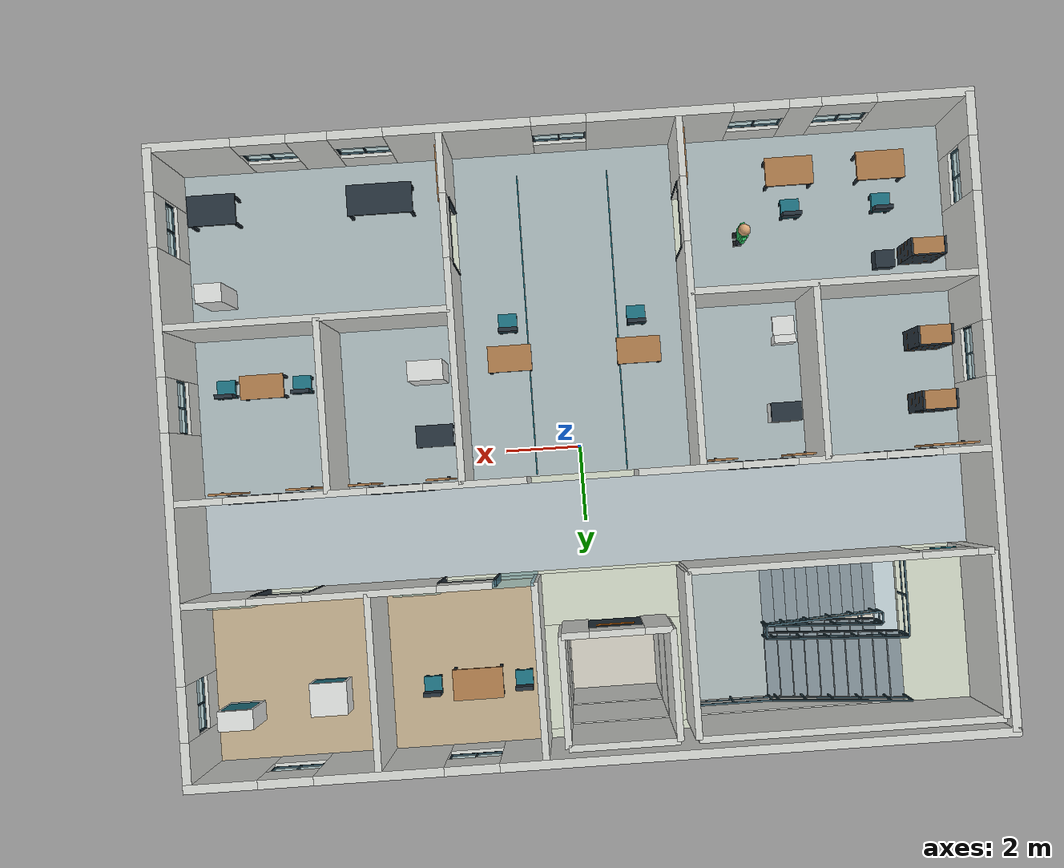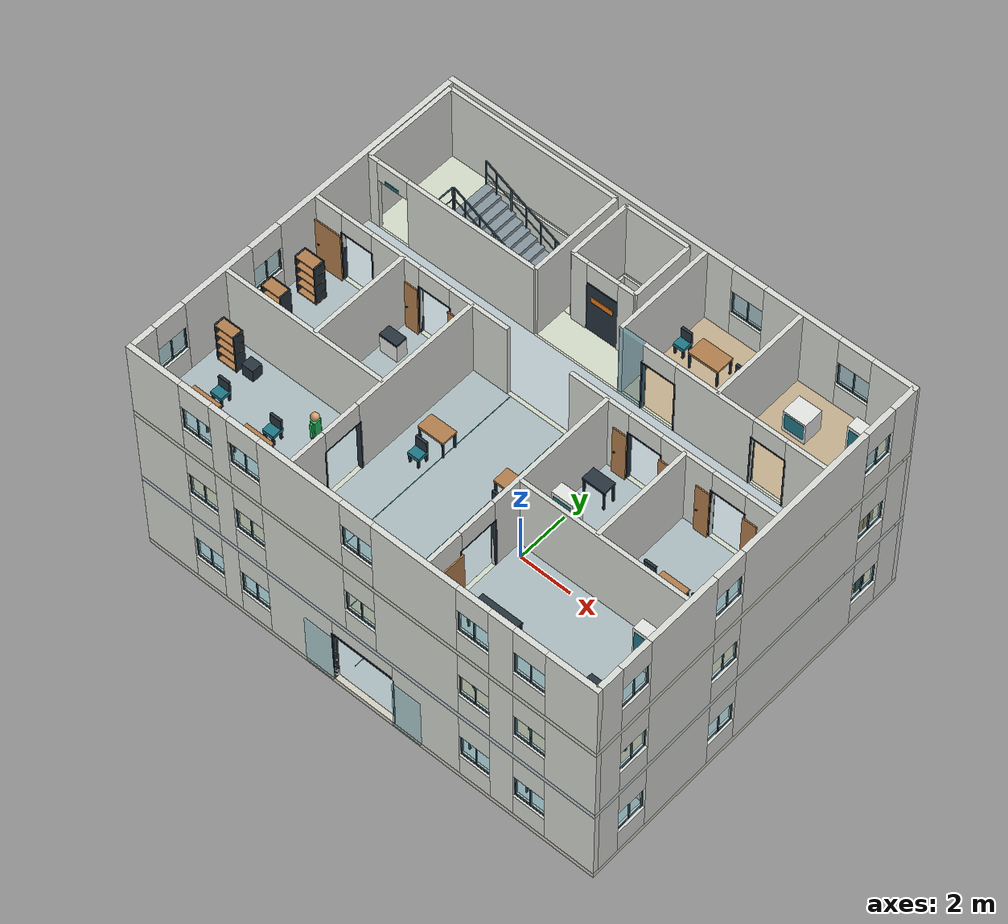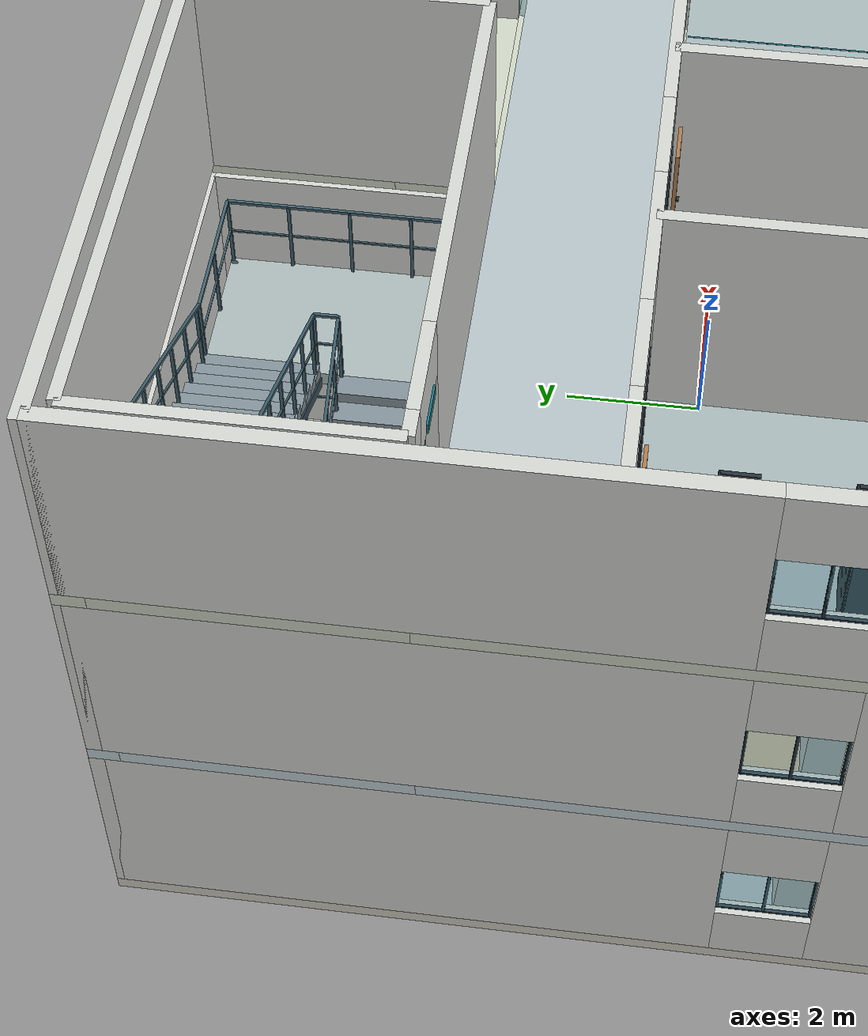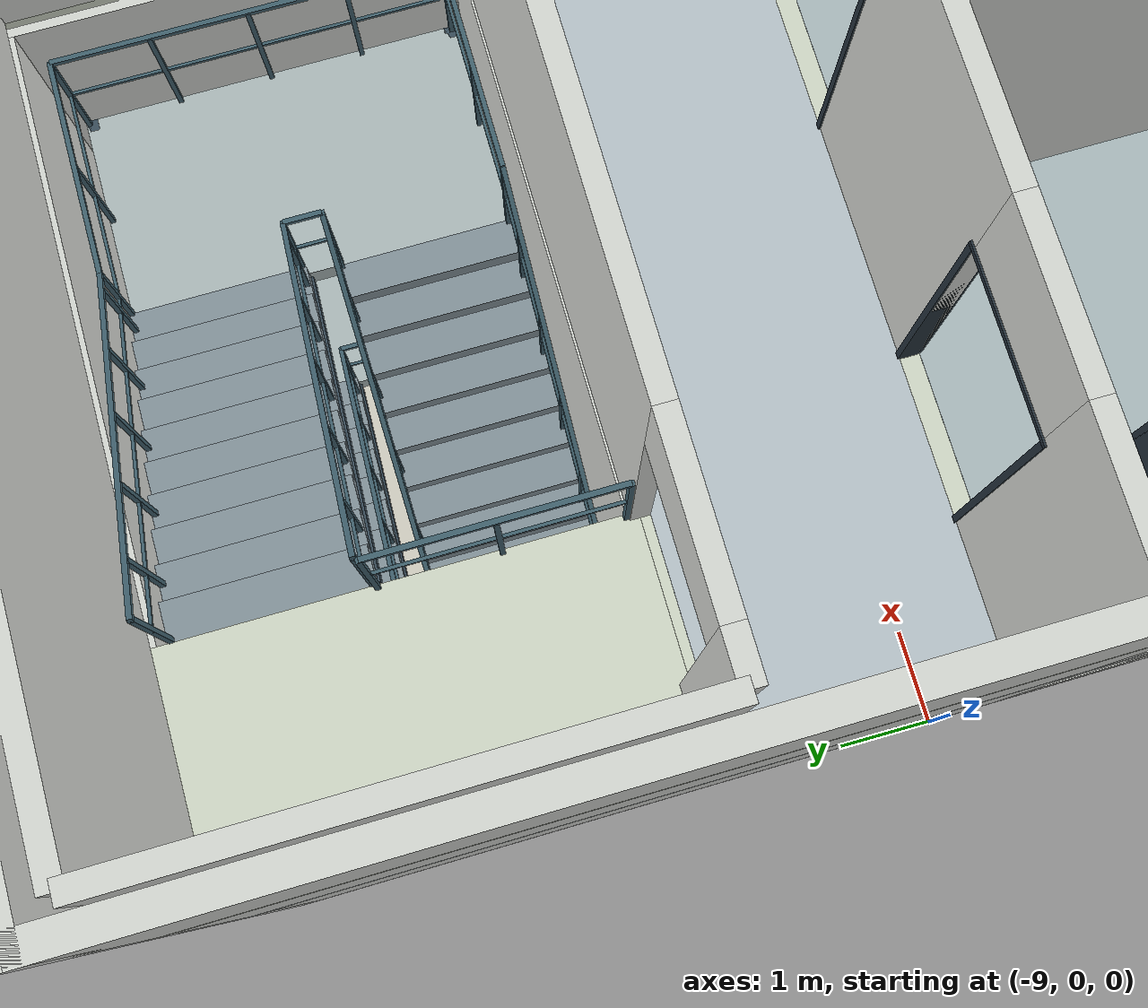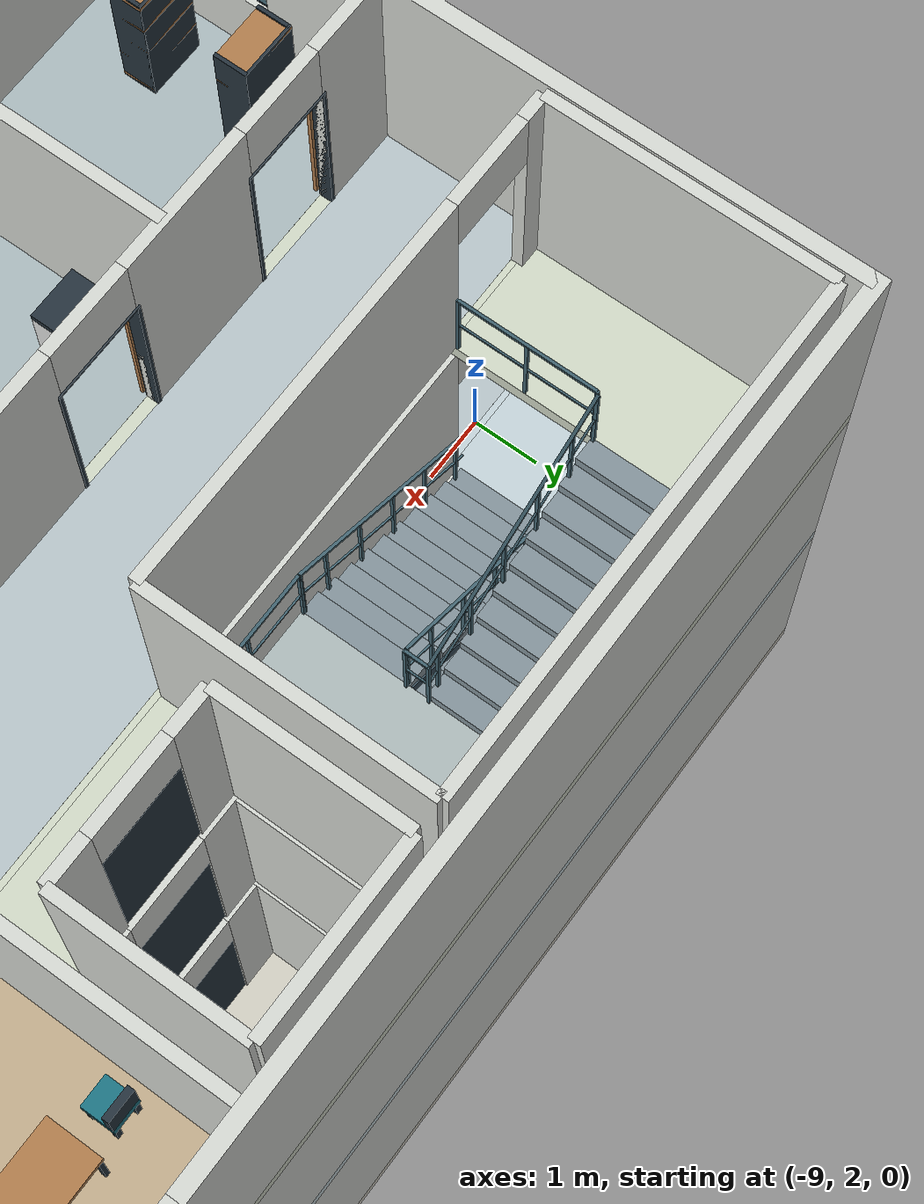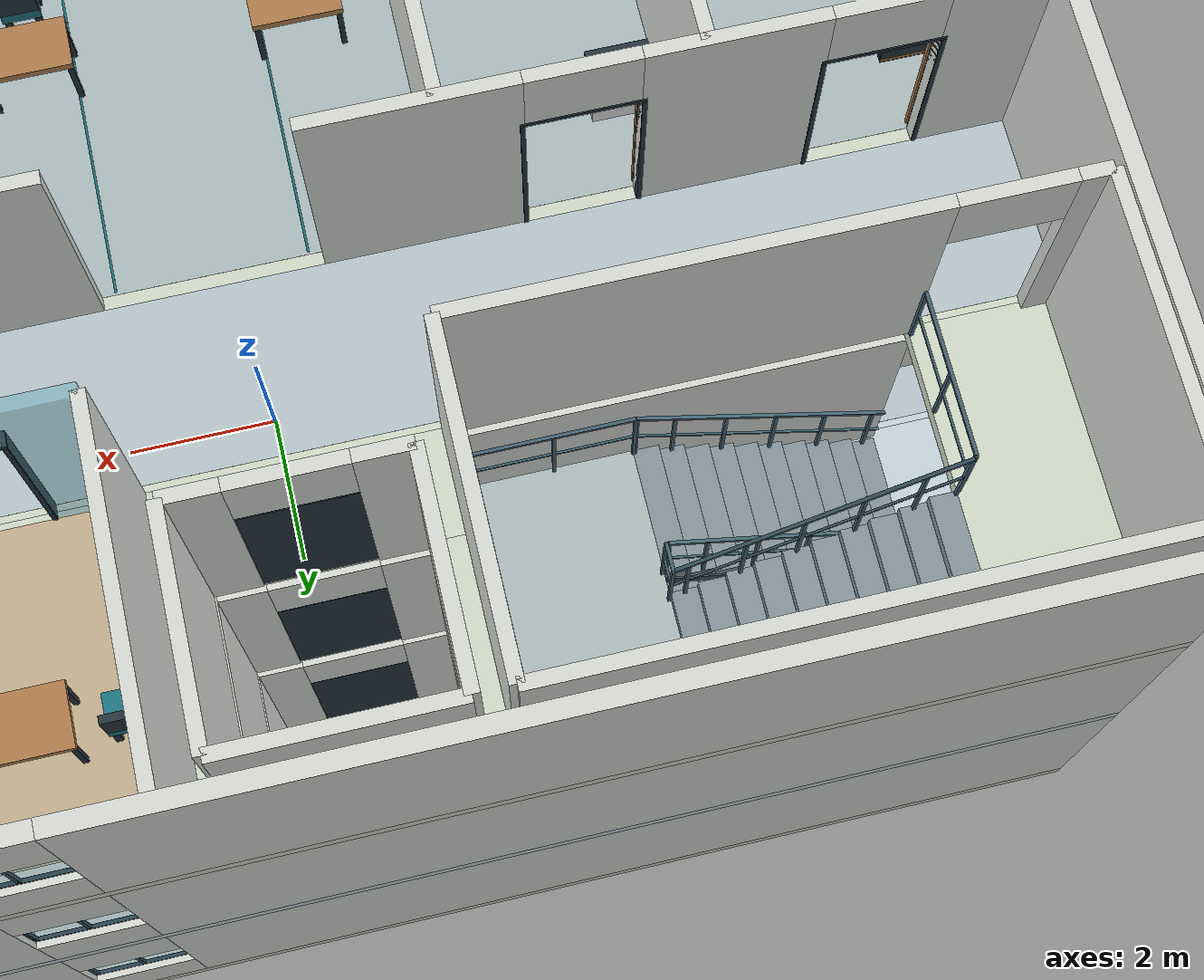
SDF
<?xml version="1.0" ?>
<sdf version="1.6">
  <world name="three_floor">
    <gravity>0 0 -9.81</gravity>
    <physics name="default_physics" type="ode">
      <max_step_size>0.001</max_step_size>
      <real_time_update_rate>1000</real_time_update_rate>
    </physics>
    <scene>
      <ambient>0.65 0.65 0.65 1</ambient>
      <background>0.80 0.86 0.92 1</background>
      <shadows>true</shadows>
    </scene>
    <light name="office_sun" type="directional">
      <pose>0 0 15 0 0 0</pose>
      <diffuse>0.85 0.85 0.85 1</diffuse>
      <specular>0.1 0.1 0.1 1</specular>
      <direction>-0.4 0.2 -1</direction>
      <cast_shadows>true</cast_shadows>
      <attenuation>
        <range>1000</range>
        <constant>1</constant>
        <linear>0</linear>
        <quadratic>0</quadratic>
      </attenuation>
    </light>
    <model name="f1_slab_01">
      <static>true</static>
      <pose>0 0 -0.1 0 0 0</pose>
      <link name="f1_slab_01_link">
        <collision name="f1_slab_01_collision">
          <geometry>
            <box>
              <size>18 14 0.2</size>
            </box>
          </geometry>
        </collision>
        <visual name="f1_slab_01_visual">
          <geometry>
            <box>
              <size>18 14 0.2</size>
            </box>
          </geometry>
          <material>
            <ambient>0.82 0.81 0.76 1</ambient>
            <diffuse>0.82 0.81 0.76 1</diffuse>
          </material>
        </visual>
      </link>
    </model>
    <model name="f1_wall_001">
      <static>true</static>
      <pose>-8.9 0 1.5 0 0 0</pose>
      <link name="f1_wall_001_link">
        <collision name="f1_wall_001_link_panel_0_collision">
          <pose>0 -6.425 0 0 0 0</pose>
          <geometry>
            <box>
              <size>0.2 0.95 3</size>
            </box>
          </geometry>
        </collision>
        <visual name="f1_wall_001_link_panel_0_visual">
          <pose>0 -6.425 0 0 0 0</pose>
          <geometry>
            <box>
              <size>0.2 0.95 3</size>
            </box>
          </geometry>
          <material>
            <ambient>.84 .85 .83 1</ambient>
            <diffuse>.84 .85 .83 1</diffuse>
          </material>
          <cast_shadows>true</cast_shadows>
        </visual>
        <collision name="f1_wall_001_link_sill_0_collision">
          <pose>0 -5.35 -1.025 0 0 0</pose>
          <geometry>
            <box>
              <size>0.2 1.2 0.95</size>
            </box>
          </geometry>
        </collision>
        <visual name="f1_wall_001_link_sill_0_visual">
          <pose>0 -5.35 -1.025 0 0 0</pose>
          <geometry>
            <box>
              <size>0.2 1.2 0.95</size>
            </box>
          </geometry>
          <material>
            <ambient>.84 .85 .83 1</ambient>
            <diffuse>.84 .85 .83 1</diffuse>
          </material>
          <cast_shadows>true</cast_shadows>
        </visual>
        <collision name="f1_wall_001_link_header_0_collision">
          <pose>0 -5.35 1 0 0 0</pose>
          <geometry>
            <box>
              <size>0.2 1.2 1</size>
            </box>
          </geometry>
        </collision>
        <visual name="f1_wall_001_link_header_0_visual">
          <pose>0 -5.35 1 0 0 0</pose>
          <geometry>
            <box>
              <size>0.2 1.2 1</size>
            </box>
          </geometry>
          <material>
            <ambient>.84 .85 .83 1</ambient>
            <diffuse>.84 .85 .83 1</diffuse>
          </material>
          <cast_shadows>true</cast_shadows>
        </visual>
        <collision name="f1_wall_001_link_panel_1_collision">
          <pose>0 -3.35 0 0 0 0</pose>
          <geometry>
            <box>
              <size>0.2 2.8 3</size>
            </box>
          </geometry>
        </collision>
        <visual name="f1_wall_001_link_panel_1_visual">
          <pose>0 -3.35 0 0 0 0</pose>
          <geometry>
            <box>
              <size>0.2 2.8 3</size>
            </box>
          </geometry>
          <material>
            <ambient>.84 .85 .83 1</ambient>
            <diffuse>.84 .85 .83 1</diffuse>
          </material>
          <cast_shadows>true</cast_shadows>
        </visual>
        <collision name="f1_wall_001_link_sill_1_collision">
          <pose>0 -1.35 -1.025 0 0 0</pose>
          <geometry>
            <box>
              <size>0.2 1.2 0.95</size>
            </box>
          </geometry>
        </collision>
        <visual name="f1_wall_001_link_sill_1_visual">
          <pose>0 -1.35 -1.025 0 0 0</pose>
          <geometry>
            <box>
              <size>0.2 1.2 0.95</size>
            </box>
          </geometry>
          <material>
            <ambient>.84 .85 .83 1</ambient>
            <diffuse>.84 .85 .83 1</diffuse>
          </material>
          <cast_shadows>true</cast_shadows>
        </visual>
        <collision name="f1_wall_001_link_header_1_collision">
          <pose>0 -1.35 1 0 0 0</pose>
          <geometry>
            <box>
              <size>0.2 1.2 1</size>
            </box>
          </geometry>
        </collision>
        <visual name="f1_wall_001_link_header_1_visual">
          <pose>0 -1.35 1 0 0 0</pose>
          <geometry>
            <box>
              <size>0.2 1.2 1</size>
            </box>
          </geometry>
          <material>
            <ambient>.84 .85 .83 1</ambient>
            <diffuse>.84 .85 .83 1</diffuse>
          </material>
          <cast_shadows>true</cast_shadows>
        </visual>
        <collision name="f1_wall_001_link_last_panel_collision">
          <pose>0 3.075 0 0 0 0</pose>
          <geometry>
            <box>
              <size>0.2 7.65 3</size>
            </box>
          </geometry>
        </collision>
        <visual name="f1_wall_001_link_last_panel_visual">
          <pose>0 3.075 0 0 0 0</pose>
          <geometry>
            <box>
              <size>0.2 7.65 3</size>
            </box>
          </geometry>
          <material>
            <ambient>.84 .85 .83 1</ambient>
            <diffuse>.84 .85 .83 1</diffuse>
          </material>
          <cast_shadows>true</cast_shadows>
        </visual>
      </link>
    </model>
    <model name="f1_wall_002">
      <static>true</static>
      <pose>8.9 0 1.5 0 0 0</pose>
      <link name="f1_wall_002_link">
        <collision name="f1_wall_002_link_panel_0_collision">
          <pose>0 -6.425 0 0 0 0</pose>
          <geometry>
            <box>
              <size>0.2 0.95 3</size>
            </box>
          </geometry>
        </collision>
        <visual name="f1_wall_002_link_panel_0_visual">
          <pose>0 -6.425 0 0 0 0</pose>
          <geometry>
            <box>
              <size>0.2 0.95 3</size>
            </box>
          </geometry>
          <material>
            <ambient>.84 .85 .83 1</ambient>
            <diffuse>.84 .85 .83 1</diffuse>
          </material>
          <cast_shadows>true</cast_shadows>
        </visual>
        <collision name="f1_wall_002_link_sill_0_collision">
          <pose>0 -5.35 -1.025 0 0 0</pose>
          <geometry>
            <box>
              <size>0.2 1.2 0.95</size>
            </box>
          </geometry>
        </collision>
        <visual name="f1_wall_002_link_sill_0_visual">
          <pose>0 -5.35 -1.025 0 0 0</pose>
          <geometry>
            <box>
              <size>0.2 1.2 0.95</size>
            </box>
          </geometry>
          <material>
            <ambient>.84 .85 .83 1</ambient>
            <diffuse>.84 .85 .83 1</diffuse>
          </material>
          <cast_shadows>true</cast_shadows>
        </visual>
        <collision name="f1_wall_002_link_header_0_collision">
          <pose>0 -5.35 1 0 0 0</pose>
          <geometry>
            <box>
              <size>0.2 1.2 1</size>
            </box>
          </geometry>
        </collision>
        <visual name="f1_wall_002_link_header_0_visual">
          <pose>0 -5.35 1 0 0 0</pose>
          <geometry>
            <box>
              <size>0.2 1.2 1</size>
            </box>
          </geometry>
          <material>
            <ambient>.84 .85 .83 1</ambient>
            <diffuse>.84 .85 .83 1</diffuse>
          </material>
          <cast_shadows>true</cast_shadows>
        </visual>
        <collision name="f1_wall_002_link_panel_1_collision">
          <pose>0 -3.35 0 0 0 0</pose>
          <geometry>
            <box>
              <size>0.2 2.8 3</size>
            </box>
          </geometry>
        </collision>
        <visual name="f1_wall_002_link_panel_1_visual">
          <pose>0 -3.35 0 0 0 0</pose>
          <geometry>
            <box>
              <size>0.2 2.8 3</size>
            </box>
          </geometry>
          <material>
            <ambient>.84 .85 .83 1</ambient>
            <diffuse>.84 .85 .83 1</diffuse>
          </material>
          <cast_shadows>true</cast_shadows>
        </visual>
        <collision name="f1_wall_002_link_sill_1_collision">
          <pose>0 -1.35 -1.025 0 0 0</pose>
          <geometry>
            <box>
              <size>0.2 1.2 0.95</size>
            </box>
          </geometry>
        </collision>
        <visual name="f1_wall_002_link_sill_1_visual">
          <pose>0 -1.35 -1.025 0 0 0</pose>
          <geometry>
            <box>
              <size>0.2 1.2 0.95</size>
            </box>
          </geometry>
          <material>
            <ambient>.84 .85 .83 1</ambient>
            <diffuse>.84 .85 .83 1</diffuse>
          </material>
          <cast_shadows>true</cast_shadows>
        </visual>
        <collision name="f1_wall_002_link_header_1_collision">
          <pose>0 -1.35 1 0 0 0</pose>
          <geometry>
            <box>
              <size>0.2 1.2 1</size>
            </box>
          </geometry>
        </collision>
        <visual name="f1_wall_002_link_header_1_visual">
          <pose>0 -1.35 1 0 0 0</pose>
          <geometry>
            <box>
              <size>0.2 1.2 1</size>
            </box>
          </geometry>
          <material>
            <ambient>.84 .85 .83 1</ambient>
            <diffuse>.84 .85 .83 1</diffuse>
          </material>
          <cast_shadows>true</cast_shadows>
        </visual>
        <collision name="f1_wall_002_link_panel_2_collision">
          <pose>0 1.975 0 0 0 0</pose>
          <geometry>
            <box>
              <size>0.2 5.45 3</size>
            </box>
          </geometry>
        </collision>
        <visual name="f1_wall_002_link_panel_2_visual">
          <pose>0 1.975 0 0 0 0</pose>
          <geometry>
            <box>
              <size>0.2 5.45 3</size>
            </box>
          </geometry>
          <material>
            <ambient>.84 .85 .83 1</ambient>
            <diffuse>.84 .85 .83 1</diffuse>
          </material>
          <cast_shadows>true</cast_shadows>
        </visual>
        <collision name="f1_wall_002_link_sill_2_collision">
          <pose>0 5.3 -1.025 0 0 0</pose>
          <geometry>
            <box>
              <size>0.2 1.2 0.95</size>
            </box>
          </geometry>
        </collision>
        <visual name="f1_wall_002_link_sill_2_visual">
          <pose>0 5.3 -1.025 0 0 0</pose>
          <geometry>
            <box>
              <size>0.2 1.2 0.95</size>
            </box>
          </geometry>
          <material>
            <ambient>.84 .85 .83 1</ambient>
            <diffuse>.84 .85 .83 1</diffuse>
          </material>
          <cast_shadows>true</cast_shadows>
        </visual>
        <collision name="f1_wall_002_link_header_2_collision">
          <pose>0 5.3 1 0 0 0</pose>
          <geometry>
            <box>
              <size>0.2 1.2 1</size>
            </box>
          </geometry>
        </collision>
        <visual name="f1_wall_002_link_header_2_visual">
          <pose>0 5.3 1 0 0 0</pose>
          <geometry>
            <box>
              <size>0.2 1.2 1</size>
            </box>
          </geometry>
          <material>
            <ambient>.84 .85 .83 1</ambient>
            <diffuse>.84 .85 .83 1</diffuse>
          </material>
          <cast_shadows>true</cast_shadows>
        </visual>
        <collision name="f1_wall_002_link_last_panel_collision">
          <pose>0 6.4 0 0 0 0</pose>
          <geometry>
            <box>
              <size>0.2 1 3</size>
            </box>
          </geometry>
        </collision>
        <visual name="f1_wall_002_link_last_panel_visual">
          <pose>0 6.4 0 0 0 0</pose>
          <geometry>
            <box>
              <size>0.2 1 3</size>
            </box>
          </geometry>
          <material>
            <ambient>.84 .85 .83 1</ambient>
            <diffuse>.84 .85 .83 1</diffuse>
          </material>
          <cast_shadows>true</cast_shadows>
        </visual>
      </link>
    </model>
    <model name="f1_wall_003">
      <static>true</static>
      <pose>0 6.9 1.5 0 0 0</pose>
      <link name="f1_wall_003_link">
        <collision name="f1_wall_003_link_panel_0_collision">
          <pose>-3.4 0 0 0 0 0</pose>
          <geometry>
            <box>
              <size>11.2 0.2 3</size>
            </box>
          </geometry>
        </collision>
        <visual name="f1_wall_003_link_panel_0_visual">
          <pose>-3.4 0 0 0 0 0</pose>
          <geometry>
            <box>
              <size>11.2 0.2 3</size>
            </box>
          </geometry>
          <material>
            <ambient>.84 .85 .83 1</ambient>
            <diffuse>.84 .85 .83 1</diffuse>
          </material>
          <cast_shadows>true</cast_shadows>
        </visual>
        <collision name="f1_wall_003_link_sill_0_collision">
          <pose>2.8 0 -1.025 0 0 0</pose>
          <geometry>
            <box>
              <size>1.2 0.2 0.95</size>
            </box>
          </geometry>
        </collision>
        <visual name="f1_wall_003_link_sill_0_visual">
          <pose>2.8 0 -1.025 0 0 0</pose>
          <geometry>
            <box>
              <size>1.2 0.2 0.95</size>
            </box>
          </geometry>
          <material>
            <ambient>.84 .85 .83 1</ambient>
            <diffuse>.84 .85 .83 1</diffuse>
          </material>
          <cast_shadows>true</cast_shadows>
        </visual>
        <collision name="f1_wall_003_link_header_0_collision">
          <pose>2.8 0 1 0 0 0</pose>
          <geometry>
            <box>
              <size>1.2 0.2 1</size>
            </box>
          </geometry>
        </collision>
        <visual name="f1_wall_003_link_header_0_visual">
          <pose>2.8 0 1 0 0 0</pose>
          <geometry>
            <box>
              <size>1.2 0.2 1</size>
            </box>
          </geometry>
          <material>
            <ambient>.84 .85 .83 1</ambient>
            <diffuse>.84 .85 .83 1</diffuse>
          </material>
          <cast_shadows>true</cast_shadows>
        </visual>
        <collision name="f1_wall_003_link_panel_1_collision">
          <pose>4.8 0 0 0 0 0</pose>
          <geometry>
            <box>
              <size>2.8 0.2 3</size>
            </box>
          </geometry>
        </collision>
        <visual name="f1_wall_003_link_panel_1_visual">
          <pose>4.8 0 0 0 0 0</pose>
          <geometry>
            <box>
              <size>2.8 0.2 3</size>
            </box>
          </geometry>
          <material>
            <ambient>.84 .85 .83 1</ambient>
            <diffuse>.84 .85 .83 1</diffuse>
          </material>
          <cast_shadows>true</cast_shadows>
        </visual>
        <collision name="f1_wall_003_link_sill_1_collision">
          <pose>6.8 0 -1.025 0 0 0</pose>
          <geometry>
            <box>
              <size>1.2 0.2 0.95</size>
            </box>
          </geometry>
        </collision>
        <visual name="f1_wall_003_link_sill_1_visual">
          <pose>6.8 0 -1.025 0 0 0</pose>
          <geometry>
            <box>
              <size>1.2 0.2 0.95</size>
            </box>
          </geometry>
          <material>
            <ambient>.84 .85 .83 1</ambient>
            <diffuse>.84 .85 .83 1</diffuse>
          </material>
          <cast_shadows>true</cast_shadows>
        </visual>
        <collision name="f1_wall_003_link_header_1_collision">
          <pose>6.8 0 1 0 0 0</pose>
          <geometry>
            <box>
              <size>1.2 0.2 1</size>
            </box>
          </geometry>
        </collision>
        <visual name="f1_wall_003_link_header_1_visual">
          <pose>6.8 0 1 0 0 0</pose>
          <geometry>
            <box>
              <size>1.2 0.2 1</size>
            </box>
          </geometry>
          <material>
            <ambient>.84 .85 .83 1</ambient>
            <diffuse>.84 .85 .83 1</diffuse>
          </material>
          <cast_shadows>true</cast_shadows>
        </visual>
        <collision name="f1_wall_003_link_last_panel_collision">
          <pose>8.2 0 0 0 0 0</pose>
          <geometry>
            <box>
              <size>1.6 0.2 3</size>
            </box>
          </geometry>
        </collision>
        <visual name="f1_wall_003_link_last_panel_visual">
          <pose>8.2 0 0 0 0 0</pose>
          <geometry>
            <box>
              <size>1.6 0.2 3</size>
            </box>
          </geometry>
          <material>
            <ambient>.84 .85 .83 1</ambient>
            <diffuse>.84 .85 .83 1</diffuse>
          </material>
          <cast_shadows>true</cast_shadows>
        </visual>
      </link>
    </model>
    <model name="f1_wall_004">
      <static>true</static>
      <pose>-5.1 -6.9 1.5 0 0 0</pose>
      <link name="f1_wall_004_link">
        <collision name="f1_wall_004_link_panel_0_collision">
          <pose>-2.85 0 0 0 0 0</pose>
          <geometry>
            <box>
              <size>2.1 0.2 3</size>
            </box>
          </geometry>
        </collision>
        <visual name="f1_wall_004_link_panel_0_visual">
          <pose>-2.85 0 0 0 0 0</pose>
          <geometry>
            <box>
              <size>2.1 0.2 3</size>
            </box>
          </geometry>
          <material>
            <ambient>.84 .85 .83 1</ambient>
            <diffuse>.84 .85 .83 1</diffuse>
          </material>
          <cast_shadows>true</cast_shadows>
        </visual>
        <collision name="f1_wall_004_link_sill_0_collision">
          <pose>-1.2 0 -1.025 0 0 0</pose>
          <geometry>
            <box>
              <size>1.2 0.2 0.95</size>
            </box>
          </geometry>
        </collision>
        <visual name="f1_wall_004_link_sill_0_visual">
          <pose>-1.2 0 -1.025 0 0 0</pose>
          <geometry>
            <box>
              <size>1.2 0.2 0.95</size>
            </box>
          </geometry>
          <material>
            <ambient>.84 .85 .83 1</ambient>
            <diffuse>.84 .85 .83 1</diffuse>
          </material>
          <cast_shadows>true</cast_shadows>
        </visual>
        <collision name="f1_wall_004_link_header_0_collision">
          <pose>-1.2 0 1 0 0 0</pose>
          <geometry>
            <box>
              <size>1.2 0.2 1</size>
            </box>
          </geometry>
        </collision>
        <visual name="f1_wall_004_link_header_0_visual">
          <pose>-1.2 0 1 0 0 0</pose>
          <geometry>
            <box>
              <size>1.2 0.2 1</size>
            </box>
          </geometry>
          <material>
            <ambient>.84 .85 .83 1</ambient>
            <diffuse>.84 .85 .83 1</diffuse>
          </material>
          <cast_shadows>true</cast_shadows>
        </visual>
        <collision name="f1_wall_004_link_panel_1_collision">
          <pose>-0.25 0 0 0 0 0</pose>
          <geometry>
            <box>
              <size>0.7 0.2 3</size>
            </box>
          </geometry>
        </collision>
        <visual name="f1_wall_004_link_panel_1_visual">
          <pose>-0.25 0 0 0 0 0</pose>
          <geometry>
            <box>
              <size>0.7 0.2 3</size>
            </box>
          </geometry>
          <material>
            <ambient>.84 .85 .83 1</ambient>
            <diffuse>.84 .85 .83 1</diffuse>
          </material>
          <cast_shadows>true</cast_shadows>
        </visual>
        <collision name="f1_wall_004_link_sill_1_collision">
          <pose>0.7 0 -1.025 0 0 0</pose>
          <geometry>
            <box>
              <size>1.2 0.2 0.95</size>
            </box>
          </geometry>
        </collision>
        <visual name="f1_wall_004_link_sill_1_visual">
          <pose>0.7 0 -1.025 0 0 0</pose>
          <geometry>
            <box>
              <size>1.2 0.2 0.95</size>
            </box>
          </geometry>
          <material>
            <ambient>.84 .85 .83 1</ambient>
            <diffuse>.84 .85 .83 1</diffuse>
          </material>
          <cast_shadows>true</cast_shadows>
        </visual>
        <collision name="f1_wall_004_link_header_1_collision">
          <pose>0.7 0 1 0 0 0</pose>
          <geometry>
            <box>
              <size>1.2 0.2 1</size>
            </box>
          </geometry>
        </collision>
        <visual name="f1_wall_004_link_header_1_visual">
          <pose>0.7 0 1 0 0 0</pose>
          <geometry>
            <box>
              <size>1.2 0.2 1</size>
            </box>
          </geometry>
          <material>
            <ambient>.84 .85 .83 1</ambient>
            <diffuse>.84 .85 .83 1</diffuse>
          </material>
          <cast_shadows>true</cast_shadows>
        </visual>
        <collision name="f1_wall_004_link_last_panel_collision">
          <pose>2.6 0 0 0 0 0</pose>
          <geometry>
            <box>
              <size>2.6 0.2 3</size>
            </box>
          </geometry>
        </collision>
        <visual name="f1_wall_004_link_last_panel_visual">
          <pose>2.6 0 0 0 0 0</pose>
          <geometry>
            <box>
              <size>2.6 0.2 3</size>
            </box>
          </geometry>
          <material>
            <ambient>.84 .85 .83 1</ambient>
            <diffuse>.84 .85 .83 1</diffuse>
          </material>
          <cast_shadows>true</cast_shadows>
        </visual>
      </link>
    </model>
    <model name="f1_wall_005">
      <static>true</static>
      <pose>5.1 -6.9 1.5 0 0 0</pose>
      <link name="f1_wall_005_link">
        <collision name="f1_wall_005_link_panel_0_collision">
          <pose>-2.6 0 0 0 0 0</pose>
          <geometry>
            <box>
              <size>2.6 0.2 3</size>
            </box>
          </geometry>
        </collision>
        <visual name="f1_wall_005_link_panel_0_visual">
          <pose>-2.6 0 0 0 0 0</pose>
          <geometry>
            <box>
              <size>2.6 0.2 3</size>
            </box>
          </geometry>
          <material>
            <ambient>.84 .85 .83 1</ambient>
            <diffuse>.84 .85 .83 1</diffuse>
          </material>
          <cast_shadows>true</cast_shadows>
        </visual>
        <collision name="f1_wall_005_link_sill_0_collision">
          <pose>-0.7 0 -1.025 0 0 0</pose>
          <geometry>
            <box>
              <size>1.2 0.2 0.95</size>
            </box>
          </geometry>
        </collision>
        <visual name="f1_wall_005_link_sill_0_visual">
          <pose>-0.7 0 -1.025 0 0 0</pose>
          <geometry>
            <box>
              <size>1.2 0.2 0.95</size>
            </box>
          </geometry>
          <material>
            <ambient>.84 .85 .83 1</ambient>
            <diffuse>.84 .85 .83 1</diffuse>
          </material>
          <cast_shadows>true</cast_shadows>
        </visual>
        <collision name="f1_wall_005_link_header_0_collision">
          <pose>-0.7 0 1 0 0 0</pose>
          <geometry>
            <box>
              <size>1.2 0.2 1</size>
            </box>
          </geometry>
        </collision>
        <visual name="f1_wall_005_link_header_0_visual">
          <pose>-0.7 0 1 0 0 0</pose>
          <geometry>
            <box>
              <size>1.2 0.2 1</size>
            </box>
          </geometry>
          <material>
            <ambient>.84 .85 .83 1</ambient>
            <diffuse>.84 .85 .83 1</diffuse>
          </material>
          <cast_shadows>true</cast_shadows>
        </visual>
        <collision name="f1_wall_005_link_panel_1_collision">
          <pose>0.35 0 0 0 0 0</pose>
          <geometry>
            <box>
              <size>0.9 0.2 3</size>
            </box>
          </geometry>
        </collision>
        <visual name="f1_wall_005_link_panel_1_visual">
          <pose>0.35 0 0 0 0 0</pose>
          <geometry>
            <box>
              <size>0.9 0.2 3</size>
            </box>
          </geometry>
          <material>
            <ambient>.84 .85 .83 1</ambient>
            <diffuse>.84 .85 .83 1</diffuse>
          </material>
          <cast_shadows>true</cast_shadows>
        </visual>
        <collision name="f1_wall_005_link_sill_1_collision">
          <pose>1.4 0 -1.025 0 0 0</pose>
          <geometry>
            <box>
              <size>1.2 0.2 0.95</size>
            </box>
          </geometry>
        </collision>
        <visual name="f1_wall_005_link_sill_1_visual">
          <pose>1.4 0 -1.025 0 0 0</pose>
          <geometry>
            <box>
              <size>1.2 0.2 0.95</size>
            </box>
          </geometry>
          <material>
            <ambient>.84 .85 .83 1</ambient>
            <diffuse>.84 .85 .83 1</diffuse>
          </material>
          <cast_shadows>true</cast_shadows>
        </visual>
        <collision name="f1_wall_005_link_header_1_collision">
          <pose>1.4 0 1 0 0 0</pose>
          <geometry>
            <box>
              <size>1.2 0.2 1</size>
            </box>
          </geometry>
        </collision>
        <visual name="f1_wall_005_link_header_1_visual">
          <pose>1.4 0 1 0 0 0</pose>
          <geometry>
            <box>
              <size>1.2 0.2 1</size>
            </box>
          </geometry>
          <material>
            <ambient>.84 .85 .83 1</ambient>
            <diffuse>.84 .85 .83 1</diffuse>
          </material>
          <cast_shadows>true</cast_shadows>
        </visual>
        <collision name="f1_wall_005_link_last_panel_collision">
          <pose>2.95 0 0 0 0 0</pose>
          <geometry>
            <box>
              <size>1.9 0.2 3</size>
            </box>
          </geometry>
        </collision>
        <visual name="f1_wall_005_link_last_panel_visual">
          <pose>2.95 0 0 0 0 0</pose>
          <geometry>
            <box>
              <size>1.9 0.2 3</size>
            </box>
          </geometry>
          <material>
            <ambient>.84 .85 .83 1</ambient>
            <diffuse>.84 .85 .83 1</diffuse>
          </material>
          <cast_shadows>true</cast_shadows>
        </visual>
      </link>
    </model>
    <model name="f1_wall_014">
      <static>true</static>
      <pose>-2.6 -6.15 1.5 0 0 0</pose>
      <link name="f1_wall_014_link">
        <collision name="f1_wall_014_collision">
          <geometry>
            <box>
              <size>0.15 1.3 3</size>
            </box>
          </geometry>
        </collision>
        <visual name="f1_wall_014_visual">
          <geometry>
            <box>
              <size>0.15 1.3 3</size>
            </box>
          </geometry>
          <material>
            <ambient>.84 .85 .83 1</ambient>
            <diffuse>.84 .85 .83 1</diffuse>
          </material>
        </visual>
      </link>
    </model>
    <model name="f1_wall_015">
      <static>true</static>
      <pose>-2.6 -1.65 1.5 0 0 0</pose>
      <link name="f1_wall_015_link">
        <collision name="f1_wall_015_collision">
          <geometry>
            <box>
              <size>0.15 4.9 3</size>
            </box>
          </geometry>
        </collision>
        <visual name="f1_wall_015_visual">
          <geometry>
            <box>
              <size>0.15 4.9 3</size>
            </box>
          </geometry>
          <material>
            <ambient>.84 .85 .83 1</ambient>
            <diffuse>.84 .85 .83 1</diffuse>
          </material>
        </visual>
      </link>
    </model>
    <model name="f1_wall_016">
      <static>true</static>
      <pose>2.6 -6.15 1.5 0 0 0</pose>
      <link name="f1_wall_016_link">
        <collision name="f1_wall_016_collision">
          <geometry>
            <box>
              <size>0.15 1.3 3</size>
            </box>
          </geometry>
        </collision>
        <visual name="f1_wall_016_visual">
          <geometry>
            <box>
              <size>0.15 1.3 3</size>
            </box>
          </geometry>
          <material>
            <ambient>.84 .85 .83 1</ambient>
            <diffuse>.84 .85 .83 1</diffuse>
          </material>
        </visual>
      </link>
    </model>
    <model name="f1_wall_017">
      <static>true</static>
      <pose>2.6 -1.65 1.5 0 0 0</pose>
      <link name="f1_wall_017_link">
        <collision name="f1_wall_017_collision">
          <geometry>
            <box>
              <size>0.15 4.9 3</size>
            </box>
          </geometry>
        </collision>
        <visual name="f1_wall_017_visual">
          <geometry>
            <box>
              <size>0.15 4.9 3</size>
            </box>
          </geometry>
          <material>
            <ambient>.84 .85 .83 1</ambient>
            <diffuse>.84 .85 .83 1</diffuse>
          </material>
        </visual>
      </link>
    </model>
    <model name="f1_wall_018">
      <static>true</static>
      <pose>-5.7 -3 1.5 0 0 0</pose>
      <link name="f1_wall_018_link">
        <collision name="f1_wall_018_collision">
          <geometry>
            <box>
              <size>6.2 0.15 3</size>
            </box>
          </geometry>
        </collision>
        <visual name="f1_wall_018_visual">
          <geometry>
            <box>
              <size>6.2 0.15 3</size>
            </box>
          </geometry>
          <material>
            <ambient>.84 .85 .83 1</ambient>
            <diffuse>.84 .85 .83 1</diffuse>
          </material>
        </visual>
      </link>
    </model>
    <model name="f1_wall_019">
      <static>true</static>
      <pose>5.7 -3 1.5 0 0 0</pose>
      <link name="f1_wall_019_link">
        <collision name="f1_wall_019_collision">
          <geometry>
            <box>
              <size>6.2 0.15 3</size>
            </box>
          </geometry>
        </collision>
        <visual name="f1_wall_019_visual">
          <geometry>
            <box>
              <size>6.2 0.15 3</size>
            </box>
          </geometry>
          <material>
            <ambient>.84 .85 .83 1</ambient>
            <diffuse>.84 .85 .83 1</diffuse>
          </material>
        </visual>
      </link>
    </model>
    <model name="f1_wall_020">
      <static>true</static>
      <pose>-5.3 -1.1 1.5 0 0 0</pose>
      <link name="f1_wall_020_link">
        <collision name="f1_wall_020_collision">
          <geometry>
            <box>
              <size>0.15 3.8 3</size>
            </box>
          </geometry>
        </collision>
        <visual name="f1_wall_020_visual">
          <geometry>
            <box>
              <size>0.15 3.8 3</size>
            </box>
          </geometry>
          <material>
            <ambient>.84 .85 .83 1</ambient>
            <diffuse>.84 .85 .83 1</diffuse>
          </material>
        </visual>
      </link>
    </model>
    <model name="f1_wall_021">
      <static>true</static>
      <pose>5.5 -1.1 1.5 0 0 0</pose>
      <link name="f1_wall_021_link">
        <collision name="f1_wall_021_collision">
          <geometry>
            <box>
              <size>0.15 3.8 3</size>
            </box>
          </geometry>
        </collision>
        <visual name="f1_wall_021_visual">
          <geometry>
            <box>
              <size>0.15 3.8 3</size>
            </box>
          </geometry>
          <material>
            <ambient>.84 .85 .83 1</ambient>
            <diffuse>.84 .85 .83 1</diffuse>
          </material>
        </visual>
      </link>
    </model>
    <model name="f1_wall_022">
      <static>true</static>
      <pose>-8.275 0.8 1.5 0 0 0</pose>
      <link name="f1_wall_022_link">
        <collision name="f1_wall_022_collision">
          <geometry>
            <box>
              <size>1.05 0.15 3</size>
            </box>
          </geometry>
        </collision>
        <visual name="f1_wall_022_visual">
          <geometry>
            <box>
              <size>1.05 0.15 3</size>
            </box>
          </geometry>
          <material>
            <ambient>.84 .85 .83 1</ambient>
            <diffuse>.84 .85 .83 1</diffuse>
          </material>
        </visual>
      </link>
    </model>
    <model name="f1_wall_023">
      <static>true</static>
      <pose>-5.6 0.8 1.5 0 0 0</pose>
      <link name="f1_wall_023_link">
        <collision name="f1_wall_023_collision">
          <geometry>
            <box>
              <size>1.9 0.15 3</size>
            </box>
          </geometry>
        </collision>
        <visual name="f1_wall_023_visual">
          <geometry>
            <box>
              <size>1.9 0.15 3</size>
            </box>
          </geometry>
          <material>
            <ambient>.84 .85 .83 1</ambient>
            <diffuse>.84 .85 .83 1</diffuse>
          </material>
        </visual>
      </link>
    </model>
    <model name="f1_wall_024">
      <static>true</static>
      <pose>-2.325 0.8 1.5 0 0 0</pose>
      <link name="f1_wall_024_link">
        <collision name="f1_wall_024_collision">
          <geometry>
            <box>
              <size>2.25 0.15 3</size>
            </box>
          </geometry>
        </collision>
        <visual name="f1_wall_024_visual">
          <geometry>
            <box>
              <size>2.25 0.15 3</size>
            </box>
          </geometry>
          <material>
            <ambient>.84 .85 .83 1</ambient>
            <diffuse>.84 .85 .83 1</diffuse>
          </material>
        </visual>
      </link>
    </model>
    <model name="f1_wall_025">
      <static>true</static>
      <pose>2.325 0.8 1.5 0 0 0</pose>
      <link name="f1_wall_025_link">
        <collision name="f1_wall_025_collision">
          <geometry>
            <box>
              <size>2.25 0.15 3</size>
            </box>
          </geometry>
        </collision>
        <visual name="f1_wall_025_visual">
          <geometry>
            <box>
              <size>2.25 0.15 3</size>
            </box>
          </geometry>
          <material>
            <ambient>.84 .85 .83 1</ambient>
            <diffuse>.84 .85 .83 1</diffuse>
          </material>
        </visual>
      </link>
    </model>
    <model name="f1_wall_026">
      <static>true</static>
      <pose>5.6 0.8 1.5 0 0 0</pose>
      <link name="f1_wall_026_link">
        <collision name="f1_wall_026_collision">
          <geometry>
            <box>
              <size>1.9 0.15 3</size>
            </box>
          </geometry>
        </collision>
        <visual name="f1_wall_026_visual">
          <geometry>
            <box>
              <size>1.9 0.15 3</size>
            </box>
          </geometry>
          <material>
            <ambient>.84 .85 .83 1</ambient>
            <diffuse>.84 .85 .83 1</diffuse>
          </material>
        </visual>
      </link>
    </model>
    <model name="f1_wall_027">
      <static>true</static>
      <pose>8.275 0.8 1.5 0 0 0</pose>
      <link name="f1_wall_027_link">
        <collision name="f1_wall_027_collision">
          <geometry>
            <box>
              <size>1.05 0.15 3</size>
            </box>
          </geometry>
        </collision>
        <visual name="f1_wall_027_visual">
          <geometry>
            <box>
              <size>1.05 0.15 3</size>
            </box>
          </geometry>
          <material>
            <ambient>.84 .85 .83 1</ambient>
            <diffuse>.84 .85 .83 1</diffuse>
          </material>
        </visual>
      </link>
    </model>
    <model name="f1_wall_028">
      <static>true</static>
      <pose>-8.7 4.8 1.5 0 0 0</pose>
      <link name="f1_wall_028_link">
        <collision name="f1_wall_028_collision">
          <geometry>
            <box>
              <size>0.15 3.6 3</size>
            </box>
          </geometry>
        </collision>
        <visual name="f1_wall_028_visual">
          <geometry>
            <box>
              <size>0.15 3.6 3</size>
            </box>
          </geometry>
          <material>
            <ambient>.84 .85 .83 1</ambient>
            <diffuse>.84 .85 .83 1</diffuse>
          </material>
        </visual>
      </link>
    </model>
    <model name="f1_wall_029">
      <static>true</static>
      <pose>-2.1 4.8 1.5 0 0 0</pose>
      <link name="f1_wall_029_link">
        <collision name="f1_wall_029_collision">
          <geometry>
            <box>
              <size>0.15 3.6 3</size>
            </box>
          </geometry>
        </collision>
        <visual name="f1_wall_029_visual">
          <geometry>
            <box>
              <size>0.15 3.6 3</size>
            </box>
          </geometry>
          <material>
            <ambient>.84 .85 .83 1</ambient>
            <diffuse>.84 .85 .83 1</diffuse>
          </material>
        </visual>
      </link>
    </model>
    <model name="f1_wall_030">
      <static>true</static>
      <pose>-5.4 6.6 1.5 0 0 0</pose>
      <link name="f1_wall_030_link">
        <collision name="f1_wall_030_collision">
          <geometry>
            <box>
              <size>6.6 0.15 3</size>
            </box>
          </geometry>
        </collision>
        <visual name="f1_wall_030_visual">
          <geometry>
            <box>
              <size>6.6 0.15 3</size>
            </box>
          </geometry>
          <material>
            <ambient>.84 .85 .83 1</ambient>
            <diffuse>.84 .85 .83 1</diffuse>
          </material>
        </visual>
      </link>
    </model>
    <model name="f1_wall_031">
      <static>true</static>
      <pose>-8.525 3 1.5 0 0 0</pose>
      <link name="f1_wall_031_link">
        <collision name="f1_wall_031_collision">
          <geometry>
            <box>
              <size>0.35 0.15 3</size>
            </box>
          </geometry>
        </collision>
        <visual name="f1_wall_031_visual">
          <geometry>
            <box>
              <size>0.35 0.15 3</size>
            </box>
          </geometry>
          <material>
            <ambient>.84 .85 .83 1</ambient>
            <diffuse>.84 .85 .83 1</diffuse>
          </material>
        </visual>
      </link>
    </model>
    <model name="f1_wall_032">
      <static>true</static>
      <pose>-4.625 3 1.5 0 0 0</pose>
      <link name="f1_wall_032_link">
        <collision name="f1_wall_032_collision">
          <geometry>
            <box>
              <size>5.05 0.15 3</size>
            </box>
          </geometry>
        </collision>
        <visual name="f1_wall_032_visual">
          <geometry>
            <box>
              <size>5.05 0.15 3</size>
            </box>
          </geometry>
          <material>
            <ambient>.84 .85 .83 1</ambient>
            <diffuse>.84 .85 .83 1</diffuse>
          </material>
        </visual>
      </link>
    </model>
    <model name="f1_wall_033">
      <static>true</static>
      <pose>-1.7 5.4 1.5 0 0 0</pose>
      <link name="f1_wall_033_link">
        <collision name="f1_wall_033_collision">
          <geometry>
            <box>
              <size>0.15 2.4 3</size>
            </box>
          </geometry>
        </collision>
        <visual name="f1_wall_033_visual">
          <geometry>
            <box>
              <size>0.15 2.4 3</size>
            </box>
          </geometry>
          <material>
            <ambient>.84 .85 .83 1</ambient>
            <diffuse>.84 .85 .83 1</diffuse>
          </material>
        </visual>
      </link>
    </model>
    <model name="f1_wall_034">
      <static>true</static>
      <pose>0.7 5.4 1.5 0 0 0</pose>
      <link name="f1_wall_034_link">
        <collision name="f1_wall_034_collision">
          <geometry>
            <box>
              <size>0.15 2.4 3</size>
            </box>
          </geometry>
        </collision>
        <visual name="f1_wall_034_visual">
          <geometry>
            <box>
              <size>0.15 2.4 3</size>
            </box>
          </geometry>
          <material>
            <ambient>.84 .85 .83 1</ambient>
            <diffuse>.84 .85 .83 1</diffuse>
          </material>
        </visual>
      </link>
    </model>
    <model name="f1_wall_035">
      <static>true</static>
      <pose>-0.5 6.6 1.5 0 0 0</pose>
      <link name="f1_wall_035_link">
        <collision name="f1_wall_035_collision">
          <geometry>
            <box>
              <size>2.4 0.15 3</size>
            </box>
          </geometry>
        </collision>
        <visual name="f1_wall_035_visual">
          <geometry>
            <box>
              <size>2.4 0.15 3</size>
            </box>
          </geometry>
          <material>
            <ambient>.84 .85 .83 1</ambient>
            <diffuse>.84 .85 .83 1</diffuse>
          </material>
        </visual>
      </link>
    </model>
    <model name="f1_wall_036">
      <static>true</static>
      <pose>-1.4 4.2 1.5 0 0 0</pose>
      <link name="f1_wall_036_link">
        <collision name="f1_wall_036_collision">
          <geometry>
            <box>
              <size>0.6 0.15 3</size>
            </box>
          </geometry>
        </collision>
        <visual name="f1_wall_036_visual">
          <geometry>
            <box>
              <size>0.6 0.15 3</size>
            </box>
          </geometry>
          <material>
            <ambient>.84 .85 .83 1</ambient>
            <diffuse>.84 .85 .83 1</diffuse>
          </material>
        </visual>
      </link>
    </model>
    <model name="f1_wall_037">
      <static>true</static>
      <pose>0.4 4.2 1.5 0 0 0</pose>
      <link name="f1_wall_037_link">
        <collision name="f1_wall_037_collision">
          <geometry>
            <box>
              <size>0.6 0.15 3</size>
            </box>
          </geometry>
        </collision>
        <visual name="f1_wall_037_visual">
          <geometry>
            <box>
              <size>0.6 0.15 3</size>
            </box>
          </geometry>
          <material>
            <ambient>.84 .85 .83 1</ambient>
            <diffuse>.84 .85 .83 1</diffuse>
          </material>
        </visual>
      </link>
    </model>
    <model name="f1_wall_038">
      <static>true</static>
      <pose>1.2 4.9 1.5 0 0 0</pose>
      <link name="f1_wall_038_link">
        <collision name="f1_wall_038_collision">
          <geometry>
            <box>
              <size>0.15 3.8 3</size>
            </box>
          </geometry>
        </collision>
        <visual name="f1_wall_038_visual">
          <geometry>
            <box>
              <size>0.15 3.8 3</size>
            </box>
          </geometry>
          <material>
            <ambient>.84 .85 .83 1</ambient>
            <diffuse>.84 .85 .83 1</diffuse>
          </material>
        </visual>
      </link>
    </model>
    <model name="f1_wall_039">
      <static>true</static>
      <pose>4.8 4.9 1.5 0 0 0</pose>
      <link name="f1_wall_039_link">
        <collision name="f1_wall_039_collision">
          <geometry>
            <box>
              <size>0.15 3.8 3</size>
            </box>
          </geometry>
        </collision>
        <visual name="f1_wall_039_visual">
          <geometry>
            <box>
              <size>0.15 3.8 3</size>
            </box>
          </geometry>
          <material>
            <ambient>.84 .85 .83 1</ambient>
            <diffuse>.84 .85 .83 1</diffuse>
          </material>
        </visual>
      </link>
    </model>
    <model name="f1_wall_040">
      <static>true</static>
      <pose>1.65 3 1.5 0 0 0</pose>
      <link name="f1_wall_040_link">
        <collision name="f1_wall_040_collision">
          <geometry>
            <box>
              <size>0.9 0.15 3</size>
            </box>
          </geometry>
        </collision>
        <visual name="f1_wall_040_visual">
          <geometry>
            <box>
              <size>0.9 0.15 3</size>
            </box>
          </geometry>
          <material>
            <ambient>.84 .85 .83 1</ambient>
            <diffuse>.84 .85 .83 1</diffuse>
          </material>
        </visual>
      </link>
    </model>
    <model name="f1_wall_041">
      <static>true</static>
      <pose>4.75 3 1.5 0 0 0</pose>
      <link name="f1_wall_041_link">
        <collision name="f1_wall_041_collision">
          <geometry>
            <box>
              <size>2.9 0.15 3</size>
            </box>
          </geometry>
        </collision>
        <visual name="f1_wall_041_visual">
          <geometry>
            <box>
              <size>2.9 0.15 3</size>
            </box>
          </geometry>
          <material>
            <ambient>.84 .85 .83 1</ambient>
            <diffuse>.84 .85 .83 1</diffuse>
          </material>
        </visual>
      </link>
    </model>
    <model name="f1_wall_042">
      <static>true</static>
      <pose>8.1 3 1.5 0 0 0</pose>
      <link name="f1_wall_042_link">
        <collision name="f1_wall_042_collision">
          <geometry>
            <box>
              <size>1.4 0.15 3</size>
            </box>
          </geometry>
        </collision>
        <visual name="f1_wall_042_visual">
          <geometry>
            <box>
              <size>1.4 0.15 3</size>
            </box>
          </geometry>
          <material>
            <ambient>.84 .85 .83 1</ambient>
            <diffuse>.84 .85 .83 1</diffuse>
          </material>
        </visual>
      </link>
    </model>
    <model name="f1_lintel_south_west_1">
      <static>true</static>
      <pose>-7.15 0.8 2.6 0 0 0</pose>
      <link name="f1_lintel_south_west_1_link">
        <collision name="f1_lintel_south_west_1_collision">
          <geometry>
            <box>
              <size>1.2 0.15 0.8</size>
            </box>
          </geometry>
        </collision>
        <visual name="f1_lintel_south_west_1_visual">
          <geometry>
            <box>
              <size>1.2 0.15 0.8</size>
            </box>
          </geometry>
          <material>
            <ambient>.84 .85 .83 1</ambient>
            <diffuse>.84 .85 .83 1</diffuse>
          </material>
        </visual>
      </link>
    </model>
    <model name="f1_lintel_south_west_2">
      <static>true</static>
      <pose>-4.05 0.8 2.6 0 0 0</pose>
      <link name="f1_lintel_south_west_2_link">
        <collision name="f1_lintel_south_west_2_collision">
          <geometry>
            <box>
              <size>1.2 0.15 0.8</size>
            </box>
          </geometry>
        </collision>
        <visual name="f1_lintel_south_west_2_visual">
          <geometry>
            <box>
              <size>1.2 0.15 0.8</size>
            </box>
          </geometry>
          <material>
            <ambient>.84 .85 .83 1</ambient>
            <diffuse>.84 .85 .83 1</diffuse>
          </material>
        </visual>
      </link>
    </model>
    <model name="f1_lintel_south_east_1">
      <static>true</static>
      <pose>4.05 0.8 2.6 0 0 0</pose>
      <link name="f1_lintel_south_east_1_link">
        <collision name="f1_lintel_south_east_1_collision">
          <geometry>
            <box>
              <size>1.2 0.15 0.8</size>
            </box>
          </geometry>
        </collision>
        <visual name="f1_lintel_south_east_1_visual">
          <geometry>
            <box>
              <size>1.2 0.15 0.8</size>
            </box>
          </geometry>
          <material>
            <ambient>.84 .85 .83 1</ambient>
            <diffuse>.84 .85 .83 1</diffuse>
          </material>
        </visual>
      </link>
    </model>
    <model name="f1_lintel_south_east_2">
      <static>true</static>
      <pose>7.15 0.8 2.6 0 0 0</pose>
      <link name="f1_lintel_south_east_2_link">
        <collision name="f1_lintel_south_east_2_collision">
          <geometry>
            <box>
              <size>1.2 0.15 0.8</size>
            </box>
          </geometry>
        </collision>
        <visual name="f1_lintel_south_east_2_visual">
          <geometry>
            <box>
              <size>1.2 0.15 0.8</size>
            </box>
          </geometry>
          <material>
            <ambient>.84 .85 .83 1</ambient>
            <diffuse>.84 .85 .83 1</diffuse>
          </material>
        </visual>
      </link>
    </model>
    <model name="f1_lintel_shared_west">
      <static>true</static>
      <pose>-2.6 -4.8 2.6 0 0 0</pose>
      <link name="f1_lintel_shared_west_link">
        <collision name="f1_lintel_shared_west_collision">
          <geometry>
            <box>
              <size>0.15 1.4 0.8</size>
            </box>
          </geometry>
        </collision>
        <visual name="f1_lintel_shared_west_visual">
          <geometry>
            <box>
              <size>0.15 1.4 0.8</size>
            </box>
          </geometry>
          <material>
            <ambient>.84 .85 .83 1</ambient>
            <diffuse>.84 .85 .83 1</diffuse>
          </material>
        </visual>
      </link>
    </model>
    <model name="f1_lintel_shared_east">
      <static>true</static>
      <pose>2.6 -4.8 2.6 0 0 0</pose>
      <link name="f1_lintel_shared_east_link">
        <collision name="f1_lintel_shared_east_collision">
          <geometry>
            <box>
              <size>0.15 1.4 0.8</size>
            </box>
          </geometry>
        </collision>
        <visual name="f1_lintel_shared_east_visual">
          <geometry>
            <box>
              <size>0.15 1.4 0.8</size>
            </box>
          </geometry>
          <material>
            <ambient>.84 .85 .83 1</ambient>
            <diffuse>.84 .85 .83 1</diffuse>
          </material>
        </visual>
      </link>
    </model>
    <model name="f1_lintel_stair">
      <static>true</static>
      <pose>-7.75 3 2.6 0 0 0</pose>
      <link name="f1_lintel_stair_link">
        <collision name="f1_lintel_stair_collision">
          <geometry>
            <box>
              <size>1.2 0.15 0.8</size>
            </box>
          </geometry>
        </collision>
        <visual name="f1_lintel_stair_visual">
          <geometry>
            <box>
              <size>1.2 0.15 0.8</size>
            </box>
          </geometry>
          <material>
            <ambient>.84 .85 .83 1</ambient>
            <diffuse>.84 .85 .83 1</diffuse>
          </material>
        </visual>
      </link>
    </model>
    <model name="f1_lintel_lift">
      <static>true</static>
      <pose>-0.5 4.2 2.6 0 0 0</pose>
      <link name="f1_lintel_lift_link">
        <collision name="f1_lintel_lift_collision">
          <geometry>
            <box>
              <size>1.2 0.15 0.8</size>
            </box>
          </geometry>
        </collision>
        <visual name="f1_lintel_lift_visual">
          <geometry>
            <box>
              <size>1.2 0.15 0.8</size>
            </box>
          </geometry>
          <material>
            <ambient>.84 .85 .83 1</ambient>
            <diffuse>.84 .85 .83 1</diffuse>
          </material>
        </visual>
      </link>
    </model>
    <model name="f1_lintel_north_west">
      <static>true</static>
      <pose>2.7 3 2.6 0 0 0</pose>
      <link name="f1_lintel_north_west_link">
        <collision name="f1_lintel_north_west_collision">
          <geometry>
            <box>
              <size>1.2 0.15 0.8</size>
            </box>
          </geometry>
        </collision>
        <visual name="f1_lintel_north_west_visual">
          <geometry>
            <box>
              <size>1.2 0.15 0.8</size>
            </box>
          </geometry>
          <material>
            <ambient>.84 .85 .83 1</ambient>
            <diffuse>.84 .85 .83 1</diffuse>
          </material>
        </visual>
      </link>
    </model>
    <model name="f1_lintel_north_east">
      <static>true</static>
      <pose>6.8 3 2.6 0 0 0</pose>
      <link name="f1_lintel_north_east_link">
        <collision name="f1_lintel_north_east_collision">
          <geometry>
            <box>
              <size>1.2 0.15 0.8</size>
            </box>
          </geometry>
        </collision>
        <visual name="f1_lintel_north_east_visual">
          <geometry>
            <box>
              <size>1.2 0.15 0.8</size>
            </box>
          </geometry>
          <material>
            <ambient>.84 .85 .83 1</ambient>
            <diffuse>.84 .85 .83 1</diffuse>
          </material>
        </visual>
      </link>
    </model>
    <model name="f1_lintel_main_entry">
      <static>true</static>
      <pose>0 -6.9 2.7 0 0 0</pose>
      <link name="f1_lintel_main_entry_link">
        <collision name="f1_lintel_main_entry_collision">
          <geometry>
            <box>
              <size>2.4 0.2 0.6</size>
            </box>
          </geometry>
        </collision>
        <visual name="f1_lintel_main_entry_visual">
          <geometry>
            <box>
              <size>2.4 0.2 0.6</size>
            </box>
          </geometry>
          <material>
            <ambient>.84 .85 .83 1</ambient>
            <diffuse>.84 .85 .83 1</diffuse>
          </material>
        </visual>
      </link>
    </model>
    <model name="f2_slab_01">
      <static>true</static>
      <pose>0 -2 3.1 0 0 0</pose>
      <link name="f2_slab_01_link">
        <collision name="f2_slab_01_collision">
          <geometry>
            <box>
              <size>18 10 0.2</size>
            </box>
          </geometry>
        </collision>
        <visual name="f2_slab_01_visual">
          <geometry>
            <box>
              <size>18 10 0.2</size>
            </box>
          </geometry>
          <material>
            <ambient>0.77 0.83 0.85 1</ambient>
            <diffuse>0.77 0.83 0.85 1</diffuse>
          </material>
        </visual>
      </link>
    </model>
    <model name="f2_slab_02">
      <static>true</static>
      <pose>-8.05 4.8 3.1 0 0 0</pose>
      <link name="f2_slab_02_link">
        <collision name="f2_slab_02_collision">
          <geometry>
            <box>
              <size>1.9 3.6 0.2</size>
            </box>
          </geometry>
        </collision>
        <visual name="f2_slab_02_visual">
          <geometry>
            <box>
              <size>1.9 3.6 0.2</size>
            </box>
          </geometry>
          <material>
            <ambient>0.77 0.83 0.85 1</ambient>
            <diffuse>0.77 0.83 0.85 1</diffuse>
          </material>
        </visual>
      </link>
    </model>
    <model name="f2_slab_03">
      <static>true</static>
      <pose>3.45 3.6 3.1 0 0 0</pose>
      <link name="f2_slab_03_link">
        <collision name="f2_slab_03_collision">
          <geometry>
            <box>
              <size>11.1 1.2 0.2</size>
            </box>
          </geometry>
        </collision>
        <visual name="f2_slab_03_visual">
          <geometry>
            <box>
              <size>11.1 1.2 0.2</size>
            </box>
          </geometry>
          <material>
            <ambient>0.77 0.83 0.85 1</ambient>
            <diffuse>0.77 0.83 0.85 1</diffuse>
          </material>
        </visual>
      </link>
    </model>
    <model name="f2_slab_04">
      <static>true</static>
      <pose>-1.9 5.4 3.1 0 0 0</pose>
      <link name="f2_slab_04_link">
        <collision name="f2_slab_04_collision">
          <geometry>
            <box>
              <size>0.4 2.4 0.2</size>
            </box>
          </geometry>
        </collision>
        <visual name="f2_slab_04_visual">
          <geometry>
            <box>
              <size>0.4 2.4 0.2</size>
            </box>
          </geometry>
          <material>
            <ambient>0.77 0.83 0.85 1</ambient>
            <diffuse>0.77 0.83 0.85 1</diffuse>
          </material>
        </visual>
      </link>
    </model>
    <model name="f2_slab_05">
      <static>true</static>
      <pose>4.85 5.4 3.1 0 0 0</pose>
      <link name="f2_slab_05_link">
        <collision name="f2_slab_05_collision">
          <geometry>
            <box>
              <size>8.3 2.4 0.2</size>
            </box>
          </geometry>
        </collision>
        <visual name="f2_slab_05_visual">
          <geometry>
            <box>
              <size>8.3 2.4 0.2</size>
            </box>
          </geometry>
          <material>
            <ambient>0.77 0.83 0.85 1</ambient>
            <diffuse>0.77 0.83 0.85 1</diffuse>
          </material>
        </visual>
      </link>
    </model>
    <model name="f2_slab_06">
      <static>true</static>
      <pose>0 6.8 3.1 0 0 0</pose>
      <link name="f2_slab_06_link">
        <collision name="f2_slab_06_collision">
          <geometry>
            <box>
              <size>18 0.4 0.2</size>
            </box>
          </geometry>
        </collision>
        <visual name="f2_slab_06_visual">
          <geometry>
            <box>
              <size>18 0.4 0.2</size>
            </box>
          </geometry>
          <material>
            <ambient>0.77 0.83 0.85 1</ambient>
            <diffuse>0.77 0.83 0.85 1</diffuse>
          </material>
        </visual>
      </link>
    </model>
    <model name="f2_wall_006">
      <static>true</static>
      <pose>-8.9 0 4.7 0 0 0</pose>
      <link name="f2_wall_006_link">
        <collision name="f2_wall_006_link_panel_0_collision">
          <pose>0 -6.425 0 0 0 0</pose>
          <geometry>
            <box>
              <size>0.2 0.95 3</size>
            </box>
          </geometry>
        </collision>
        <visual name="f2_wall_006_link_panel_0_visual">
          <pose>0 -6.425 0 0 0 0</pose>
          <geometry>
            <box>
              <size>0.2 0.95 3</size>
            </box>
          </geometry>
          <material>
            <ambient>.84 .85 .83 1</ambient>
            <diffuse>.84 .85 .83 1</diffuse>
          </material>
          <cast_shadows>true</cast_shadows>
        </visual>
        <collision name="f2_wall_006_link_sill_0_collision">
          <pose>0 -5.35 -1.025 0 0 0</pose>
          <geometry>
            <box>
              <size>0.2 1.2 0.95</size>
            </box>
          </geometry>
        </collision>
        <visual name="f2_wall_006_link_sill_0_visual">
          <pose>0 -5.35 -1.025 0 0 0</pose>
          <geometry>
            <box>
              <size>0.2 1.2 0.95</size>
            </box>
          </geometry>
          <material>
            <ambient>.84 .85 .83 1</ambient>
            <diffuse>.84 .85 .83 1</diffuse>
          </material>
          <cast_shadows>true</cast_shadows>
        </visual>
        <collision name="f2_wall_006_link_header_0_collision">
          <pose>0 -5.35 1 0 0 0</pose>
          <geometry>
            <box>
              <size>0.2 1.2 1</size>
            </box>
          </geometry>
        </collision>
        <visual name="f2_wall_006_link_header_0_visual">
          <pose>0 -5.35 1 0 0 0</pose>
          <geometry>
            <box>
              <size>0.2 1.2 1</size>
            </box>
          </geometry>
          <material>
            <ambient>.84 .85 .83 1</ambient>
            <diffuse>.84 .85 .83 1</diffuse>
          </material>
          <cast_shadows>true</cast_shadows>
        </visual>
        <collision name="f2_wall_006_link_panel_1_collision">
          <pose>0 -3.35 0 0 0 0</pose>
          <geometry>
            <box>
              <size>0.2 2.8 3</size>
            </box>
          </geometry>
        </collision>
        <visual name="f2_wall_006_link_panel_1_visual">
          <pose>0 -3.35 0 0 0 0</pose>
          <geometry>
            <box>
              <size>0.2 2.8 3</size>
            </box>
          </geometry>
          <material>
            <ambient>.84 .85 .83 1</ambient>
            <diffuse>.84 .85 .83 1</diffuse>
          </material>
          <cast_shadows>true</cast_shadows>
        </visual>
        <collision name="f2_wall_006_link_sill_1_collision">
          <pose>0 -1.35 -1.025 0 0 0</pose>
          <geometry>
            <box>
              <size>0.2 1.2 0.95</size>
            </box>
          </geometry>
        </collision>
        <visual name="f2_wall_006_link_sill_1_visual">
          <pose>0 -1.35 -1.025 0 0 0</pose>
          <geometry>
            <box>
              <size>0.2 1.2 0.95</size>
            </box>
          </geometry>
          <material>
            <ambient>.84 .85 .83 1</ambient>
            <diffuse>.84 .85 .83 1</diffuse>
          </material>
          <cast_shadows>true</cast_shadows>
        </visual>
        <collision name="f2_wall_006_link_header_1_collision">
          <pose>0 -1.35 1 0 0 0</pose>
          <geometry>
            <box>
              <size>0.2 1.2 1</size>
            </box>
          </geometry>
        </collision>
        <visual name="f2_wall_006_link_header_1_visual">
          <pose>0 -1.35 1 0 0 0</pose>
          <geometry>
            <box>
              <size>0.2 1.2 1</size>
            </box>
          </geometry>
          <material>
            <ambient>.84 .85 .83 1</ambient>
            <diffuse>.84 .85 .83 1</diffuse>
          </material>
          <cast_shadows>true</cast_shadows>
        </visual>
        <collision name="f2_wall_006_link_last_panel_collision">
          <pose>0 3.075 0 0 0 0</pose>
          <geometry>
            <box>
              <size>0.2 7.65 3</size>
            </box>
          </geometry>
        </collision>
        <visual name="f2_wall_006_link_last_panel_visual">
          <pose>0 3.075 0 0 0 0</pose>
          <geometry>
            <box>
              <size>0.2 7.65 3</size>
            </box>
          </geometry>
          <material>
            <ambient>.84 .85 .83 1</ambient>
            <diffuse>.84 .85 .83 1</diffuse>
          </material>
          <cast_shadows>true</cast_shadows>
        </visual>
      </link>
    </model>
    <model name="f2_wall_007">
      <static>true</static>
      <pose>8.9 0 4.7 0 0 0</pose>
      <link name="f2_wall_007_link">
        <collision name="f2_wall_007_link_panel_0_collision">
          <pose>0 -6.425 0 0 0 0</pose>
          <geometry>
            <box>
              <size>0.2 0.95 3</size>
            </box>
          </geometry>
        </collision>
        <visual name="f2_wall_007_link_panel_0_visual">
          <pose>0 -6.425 0 0 0 0</pose>
          <geometry>
            <box>
              <size>0.2 0.95 3</size>
            </box>
          </geometry>
          <material>
            <ambient>.84 .85 .83 1</ambient>
            <diffuse>.84 .85 .83 1</diffuse>
          </material>
          <cast_shadows>true</cast_shadows>
        </visual>
        <collision name="f2_wall_007_link_sill_0_collision">
          <pose>0 -5.35 -1.025 0 0 0</pose>
          <geometry>
            <box>
              <size>0.2 1.2 0.95</size>
            </box>
          </geometry>
        </collision>
        <visual name="f2_wall_007_link_sill_0_visual">
          <pose>0 -5.35 -1.025 0 0 0</pose>
          <geometry>
            <box>
              <size>0.2 1.2 0.95</size>
            </box>
          </geometry>
          <material>
            <ambient>.84 .85 .83 1</ambient>
            <diffuse>.84 .85 .83 1</diffuse>
          </material>
          <cast_shadows>true</cast_shadows>
        </visual>
        <collision name="f2_wall_007_link_header_0_collision">
          <pose>0 -5.35 1 0 0 0</pose>
          <geometry>
            <box>
              <size>0.2 1.2 1</size>
            </box>
          </geometry>
        </collision>
        <visual name="f2_wall_007_link_header_0_visual">
          <pose>0 -5.35 1 0 0 0</pose>
          <geometry>
            <box>
              <size>0.2 1.2 1</size>
            </box>
          </geometry>
          <material>
            <ambient>.84 .85 .83 1</ambient>
            <diffuse>.84 .85 .83 1</diffuse>
          </material>
          <cast_shadows>true</cast_shadows>
        </visual>
        <collision name="f2_wall_007_link_panel_1_collision">
          <pose>0 -3.35 0 0 0 0</pose>
          <geometry>
            <box>
              <size>0.2 2.8 3</size>
            </box>
          </geometry>
        </collision>
        <visual name="f2_wall_007_link_panel_1_visual">
          <pose>0 -3.35 0 0 0 0</pose>
          <geometry>
            <box>
              <size>0.2 2.8 3</size>
            </box>
          </geometry>
          <material>
            <ambient>.84 .85 .83 1</ambient>
            <diffuse>.84 .85 .83 1</diffuse>
          </material>
          <cast_shadows>true</cast_shadows>
        </visual>
        <collision name="f2_wall_007_link_sill_1_collision">
          <pose>0 -1.35 -1.025 0 0 0</pose>
          <geometry>
            <box>
              <size>0.2 1.2 0.95</size>
            </box>
          </geometry>
        </collision>
        <visual name="f2_wall_007_link_sill_1_visual">
          <pose>0 -1.35 -1.025 0 0 0</pose>
          <geometry>
            <box>
              <size>0.2 1.2 0.95</size>
            </box>
          </geometry>
          <material>
            <ambient>.84 .85 .83 1</ambient>
            <diffuse>.84 .85 .83 1</diffuse>
          </material>
          <cast_shadows>true</cast_shadows>
        </visual>
        <collision name="f2_wall_007_link_header_1_collision">
          <pose>0 -1.35 1 0 0 0</pose>
          <geometry>
            <box>
              <size>0.2 1.2 1</size>
            </box>
          </geometry>
        </collision>
        <visual name="f2_wall_007_link_header_1_visual">
          <pose>0 -1.35 1 0 0 0</pose>
          <geometry>
            <box>
              <size>0.2 1.2 1</size>
            </box>
          </geometry>
          <material>
            <ambient>.84 .85 .83 1</ambient>
            <diffuse>.84 .85 .83 1</diffuse>
          </material>
          <cast_shadows>true</cast_shadows>
        </visual>
        <collision name="f2_wall_007_link_panel_2_collision">
          <pose>0 1.975 0 0 0 0</pose>
          <geometry>
            <box>
              <size>0.2 5.45 3</size>
            </box>
          </geometry>
        </collision>
        <visual name="f2_wall_007_link_panel_2_visual">
          <pose>0 1.975 0 0 0 0</pose>
          <geometry>
            <box>
              <size>0.2 5.45 3</size>
            </box>
          </geometry>
          <material>
            <ambient>.84 .85 .83 1</ambient>
            <diffuse>.84 .85 .83 1</diffuse>
          </material>
          <cast_shadows>true</cast_shadows>
        </visual>
        <collision name="f2_wall_007_link_sill_2_collision">
          <pose>0 5.3 -1.025 0 0 0</pose>
          <geometry>
            <box>
              <size>0.2 1.2 0.95</size>
            </box>
          </geometry>
        </collision>
        <visual name="f2_wall_007_link_sill_2_visual">
          <pose>0 5.3 -1.025 0 0 0</pose>
          <geometry>
            <box>
              <size>0.2 1.2 0.95</size>
            </box>
          </geometry>
          <material>
            <ambient>.84 .85 .83 1</ambient>
            <diffuse>.84 .85 .83 1</diffuse>
          </material>
          <cast_shadows>true</cast_shadows>
        </visual>
        <collision name="f2_wall_007_link_header_2_collision">
          <pose>0 5.3 1 0 0 0</pose>
          <geometry>
            <box>
              <size>0.2 1.2 1</size>
            </box>
          </geometry>
        </collision>
        <visual name="f2_wall_007_link_header_2_visual">
          <pose>0 5.3 1 0 0 0</pose>
          <geometry>
            <box>
              <size>0.2 1.2 1</size>
            </box>
          </geometry>
          <material>
            <ambient>.84 .85 .83 1</ambient>
            <diffuse>.84 .85 .83 1</diffuse>
          </material>
          <cast_shadows>true</cast_shadows>
        </visual>
        <collision name="f2_wall_007_link_last_panel_collision">
          <pose>0 6.4 0 0 0 0</pose>
          <geometry>
            <box>
              <size>0.2 1 3</size>
            </box>
          </geometry>
        </collision>
        <visual name="f2_wall_007_link_last_panel_visual">
          <pose>0 6.4 0 0 0 0</pose>
          <geometry>
            <box>
              <size>0.2 1 3</size>
            </box>
          </geometry>
          <material>
            <ambient>.84 .85 .83 1</ambient>
            <diffuse>.84 .85 .83 1</diffuse>
          </material>
          <cast_shadows>true</cast_shadows>
        </visual>
      </link>
    </model>
    <model name="f2_wall_008">
      <static>true</static>
      <pose>0 6.9 4.7 0 0 0</pose>
      <link name="f2_wall_008_link">
        <collision name="f2_wall_008_link_panel_0_collision">
          <pose>-3.4 0 0 0 0 0</pose>
          <geometry>
            <box>
              <size>11.2 0.2 3</size>
            </box>
          </geometry>
        </collision>
        <visual name="f2_wall_008_link_panel_0_visual">
          <pose>-3.4 0 0 0 0 0</pose>
          <geometry>
            <box>
              <size>11.2 0.2 3</size>
            </box>
          </geometry>
          <material>
            <ambient>.84 .85 .83 1</ambient>
            <diffuse>.84 .85 .83 1</diffuse>
          </material>
          <cast_shadows>true</cast_shadows>
        </visual>
        <collision name="f2_wall_008_link_sill_0_collision">
          <pose>2.8 0 -1.025 0 0 0</pose>
          <geometry>
            <box>
              <size>1.2 0.2 0.95</size>
            </box>
          </geometry>
        </collision>
        <visual name="f2_wall_008_link_sill_0_visual">
          <pose>2.8 0 -1.025 0 0 0</pose>
          <geometry>
            <box>
              <size>1.2 0.2 0.95</size>
            </box>
          </geometry>
          <material>
            <ambient>.84 .85 .83 1</ambient>
            <diffuse>.84 .85 .83 1</diffuse>
          </material>
          <cast_shadows>true</cast_shadows>
        </visual>
        <collision name="f2_wall_008_link_header_0_collision">
          <pose>2.8 0 1 0 0 0</pose>
          <geometry>
            <box>
              <size>1.2 0.2 1</size>
            </box>
          </geometry>
        </collision>
        <visual name="f2_wall_008_link_header_0_visual">
          <pose>2.8 0 1 0 0 0</pose>
          <geometry>
            <box>
              <size>1.2 0.2 1</size>
            </box>
          </geometry>
          <material>
            <ambient>.84 .85 .83 1</ambient>
            <diffuse>.84 .85 .83 1</diffuse>
          </material>
          <cast_shadows>true</cast_shadows>
        </visual>
        <collision name="f2_wall_008_link_panel_1_collision">
          <pose>4.8 0 0 0 0 0</pose>
          <geometry>
            <box>
              <size>2.8 0.2 3</size>
            </box>
          </geometry>
        </collision>
        <visual name="f2_wall_008_link_panel_1_visual">
          <pose>4.8 0 0 0 0 0</pose>
          <geometry>
            <box>
              <size>2.8 0.2 3</size>
            </box>
          </geometry>
          <material>
            <ambient>.84 .85 .83 1</ambient>
            <diffuse>.84 .85 .83 1</diffuse>
          </material>
          <cast_shadows>true</cast_shadows>
        </visual>
        <collision name="f2_wall_008_link_sill_1_collision">
          <pose>6.8 0 -1.025 0 0 0</pose>
          <geometry>
            <box>
              <size>1.2 0.2 0.95</size>
            </box>
          </geometry>
        </collision>
        <visual name="f2_wall_008_link_sill_1_visual">
          <pose>6.8 0 -1.025 0 0 0</pose>
          <geometry>
            <box>
              <size>1.2 0.2 0.95</size>
            </box>
          </geometry>
          <material>
            <ambient>.84 .85 .83 1</ambient>
            <diffuse>.84 .85 .83 1</diffuse>
          </material>
          <cast_shadows>true</cast_shadows>
        </visual>
        <collision name="f2_wall_008_link_header_1_collision">
          <pose>6.8 0 1 0 0 0</pose>
          <geometry>
            <box>
              <size>1.2 0.2 1</size>
            </box>
          </geometry>
        </collision>
        <visual name="f2_wall_008_link_header_1_visual">
          <pose>6.8 0 1 0 0 0</pose>
          <geometry>
            <box>
              <size>1.2 0.2 1</size>
            </box>
          </geometry>
          <material>
            <ambient>.84 .85 .83 1</ambient>
            <diffuse>.84 .85 .83 1</diffuse>
          </material>
          <cast_shadows>true</cast_shadows>
        </visual>
        <collision name="f2_wall_008_link_last_panel_collision">
          <pose>8.2 0 0 0 0 0</pose>
          <geometry>
            <box>
              <size>1.6 0.2 3</size>
            </box>
          </geometry>
        </collision>
        <visual name="f2_wall_008_link_last_panel_visual">
          <pose>8.2 0 0 0 0 0</pose>
          <geometry>
            <box>
              <size>1.6 0.2 3</size>
            </box>
          </geometry>
          <material>
            <ambient>.84 .85 .83 1</ambient>
            <diffuse>.84 .85 .83 1</diffuse>
          </material>
          <cast_shadows>true</cast_shadows>
        </visual>
      </link>
    </model>
    <model name="f2_wall_009">
      <static>true</static>
      <pose>0 -6.9 4.7 0 0 0</pose>
      <link name="f2_wall_009_link">
        <collision name="f2_wall_009_link_panel_0_collision">
          <pose>-7.95 0 0 0 0 0</pose>
          <geometry>
            <box>
              <size>2.1 0.2 3</size>
            </box>
          </geometry>
        </collision>
        <visual name="f2_wall_009_link_panel_0_visual">
          <pose>-7.95 0 0 0 0 0</pose>
          <geometry>
            <box>
              <size>2.1 0.2 3</size>
            </box>
          </geometry>
          <material>
            <ambient>.84 .85 .83 1</ambient>
            <diffuse>.84 .85 .83 1</diffuse>
          </material>
          <cast_shadows>true</cast_shadows>
        </visual>
        <collision name="f2_wall_009_link_sill_0_collision">
          <pose>-6.3 0 -1.025 0 0 0</pose>
          <geometry>
            <box>
              <size>1.2 0.2 0.95</size>
            </box>
          </geometry>
        </collision>
        <visual name="f2_wall_009_link_sill_0_visual">
          <pose>-6.3 0 -1.025 0 0 0</pose>
          <geometry>
            <box>
              <size>1.2 0.2 0.95</size>
            </box>
          </geometry>
          <material>
            <ambient>.84 .85 .83 1</ambient>
            <diffuse>.84 .85 .83 1</diffuse>
          </material>
          <cast_shadows>true</cast_shadows>
        </visual>
        <collision name="f2_wall_009_link_header_0_collision">
          <pose>-6.3 0 1 0 0 0</pose>
          <geometry>
            <box>
              <size>1.2 0.2 1</size>
            </box>
          </geometry>
        </collision>
        <visual name="f2_wall_009_link_header_0_visual">
          <pose>-6.3 0 1 0 0 0</pose>
          <geometry>
            <box>
              <size>1.2 0.2 1</size>
            </box>
          </geometry>
          <material>
            <ambient>.84 .85 .83 1</ambient>
            <diffuse>.84 .85 .83 1</diffuse>
          </material>
          <cast_shadows>true</cast_shadows>
        </visual>
        <collision name="f2_wall_009_link_panel_1_collision">
          <pose>-5.35 0 0 0 0 0</pose>
          <geometry>
            <box>
              <size>0.7 0.2 3</size>
            </box>
          </geometry>
        </collision>
        <visual name="f2_wall_009_link_panel_1_visual">
          <pose>-5.35 0 0 0 0 0</pose>
          <geometry>
            <box>
              <size>0.7 0.2 3</size>
            </box>
          </geometry>
          <material>
            <ambient>.84 .85 .83 1</ambient>
            <diffuse>.84 .85 .83 1</diffuse>
          </material>
          <cast_shadows>true</cast_shadows>
        </visual>
        <collision name="f2_wall_009_link_sill_1_collision">
          <pose>-4.4 0 -1.025 0 0 0</pose>
          <geometry>
            <box>
              <size>1.2 0.2 0.95</size>
            </box>
          </geometry>
        </collision>
        <visual name="f2_wall_009_link_sill_1_visual">
          <pose>-4.4 0 -1.025 0 0 0</pose>
          <geometry>
            <box>
              <size>1.2 0.2 0.95</size>
            </box>
          </geometry>
          <material>
            <ambient>.84 .85 .83 1</ambient>
            <diffuse>.84 .85 .83 1</diffuse>
          </material>
          <cast_shadows>true</cast_shadows>
        </visual>
        <collision name="f2_wall_009_link_header_1_collision">
          <pose>-4.4 0 1 0 0 0</pose>
          <geometry>
            <box>
              <size>1.2 0.2 1</size>
            </box>
          </geometry>
        </collision>
        <visual name="f2_wall_009_link_header_1_visual">
          <pose>-4.4 0 1 0 0 0</pose>
          <geometry>
            <box>
              <size>1.2 0.2 1</size>
            </box>
          </geometry>
          <material>
            <ambient>.84 .85 .83 1</ambient>
            <diffuse>.84 .85 .83 1</diffuse>
          </material>
          <cast_shadows>true</cast_shadows>
        </visual>
        <collision name="f2_wall_009_link_panel_2_collision">
          <pose>-2.2 0 0 0 0 0</pose>
          <geometry>
            <box>
              <size>3.2 0.2 3</size>
            </box>
          </geometry>
        </collision>
        <visual name="f2_wall_009_link_panel_2_visual">
          <pose>-2.2 0 0 0 0 0</pose>
          <geometry>
            <box>
              <size>3.2 0.2 3</size>
            </box>
          </geometry>
          <material>
            <ambient>.84 .85 .83 1</ambient>
            <diffuse>.84 .85 .83 1</diffuse>
          </material>
          <cast_shadows>true</cast_shadows>
        </visual>
        <collision name="f2_wall_009_link_sill_2_collision">
          <pose>0 0 -1.025 0 0 0</pose>
          <geometry>
            <box>
              <size>1.2 0.2 0.95</size>
            </box>
          </geometry>
        </collision>
        <visual name="f2_wall_009_link_sill_2_visual">
          <pose>0 0 -1.025 0 0 0</pose>
          <geometry>
            <box>
              <size>1.2 0.2 0.95</size>
            </box>
          </geometry>
          <material>
            <ambient>.84 .85 .83 1</ambient>
            <diffuse>.84 .85 .83 1</diffuse>
          </material>
          <cast_shadows>true</cast_shadows>
        </visual>
        <collision name="f2_wall_009_link_header_2_collision">
          <pose>0 0 1 0 0 0</pose>
          <geometry>
            <box>
              <size>1.2 0.2 1</size>
            </box>
          </geometry>
        </collision>
        <visual name="f2_wall_009_link_header_2_visual">
          <pose>0 0 1 0 0 0</pose>
          <geometry>
            <box>
              <size>1.2 0.2 1</size>
            </box>
          </geometry>
          <material>
            <ambient>.84 .85 .83 1</ambient>
            <diffuse>.84 .85 .83 1</diffuse>
          </material>
          <cast_shadows>true</cast_shadows>
        </visual>
        <collision name="f2_wall_009_link_panel_3_collision">
          <pose>2.2 0 0 0 0 0</pose>
          <geometry>
            <box>
              <size>3.2 0.2 3</size>
            </box>
          </geometry>
        </collision>
        <visual name="f2_wall_009_link_panel_3_visual">
          <pose>2.2 0 0 0 0 0</pose>
          <geometry>
            <box>
              <size>3.2 0.2 3</size>
            </box>
          </geometry>
          <material>
            <ambient>.84 .85 .83 1</ambient>
            <diffuse>.84 .85 .83 1</diffuse>
          </material>
          <cast_shadows>true</cast_shadows>
        </visual>
        <collision name="f2_wall_009_link_sill_3_collision">
          <pose>4.4 0 -1.025 0 0 0</pose>
          <geometry>
            <box>
              <size>1.2 0.2 0.95</size>
            </box>
          </geometry>
        </collision>
        <visual name="f2_wall_009_link_sill_3_visual">
          <pose>4.4 0 -1.025 0 0 0</pose>
          <geometry>
            <box>
              <size>1.2 0.2 0.95</size>
            </box>
          </geometry>
          <material>
            <ambient>.84 .85 .83 1</ambient>
            <diffuse>.84 .85 .83 1</diffuse>
          </material>
          <cast_shadows>true</cast_shadows>
        </visual>
        <collision name="f2_wall_009_link_header_3_collision">
          <pose>4.4 0 1 0 0 0</pose>
          <geometry>
            <box>
              <size>1.2 0.2 1</size>
            </box>
          </geometry>
        </collision>
        <visual name="f2_wall_009_link_header_3_visual">
          <pose>4.4 0 1 0 0 0</pose>
          <geometry>
            <box>
              <size>1.2 0.2 1</size>
            </box>
          </geometry>
          <material>
            <ambient>.84 .85 .83 1</ambient>
            <diffuse>.84 .85 .83 1</diffuse>
          </material>
          <cast_shadows>true</cast_shadows>
        </visual>
        <collision name="f2_wall_009_link_panel_4_collision">
          <pose>5.45 0 0 0 0 0</pose>
          <geometry>
            <box>
              <size>0.9 0.2 3</size>
            </box>
          </geometry>
        </collision>
        <visual name="f2_wall_009_link_panel_4_visual">
          <pose>5.45 0 0 0 0 0</pose>
          <geometry>
            <box>
              <size>0.9 0.2 3</size>
            </box>
          </geometry>
          <material>
            <ambient>.84 .85 .83 1</ambient>
            <diffuse>.84 .85 .83 1</diffuse>
          </material>
          <cast_shadows>true</cast_shadows>
        </visual>
        <collision name="f2_wall_009_link_sill_4_collision">
          <pose>6.5 0 -1.025 0 0 0</pose>
          <geometry>
            <box>
              <size>1.2 0.2 0.95</size>
            </box>
          </geometry>
        </collision>
        <visual name="f2_wall_009_link_sill_4_visual">
          <pose>6.5 0 -1.025 0 0 0</pose>
          <geometry>
            <box>
              <size>1.2 0.2 0.95</size>
            </box>
          </geometry>
          <material>
            <ambient>.84 .85 .83 1</ambient>
            <diffuse>.84 .85 .83 1</diffuse>
          </material>
          <cast_shadows>true</cast_shadows>
        </visual>
        <collision name="f2_wall_009_link_header_4_collision">
          <pose>6.5 0 1 0 0 0</pose>
          <geometry>
            <box>
              <size>1.2 0.2 1</size>
            </box>
          </geometry>
        </collision>
        <visual name="f2_wall_009_link_header_4_visual">
          <pose>6.5 0 1 0 0 0</pose>
          <geometry>
            <box>
              <size>1.2 0.2 1</size>
            </box>
          </geometry>
          <material>
            <ambient>.84 .85 .83 1</ambient>
            <diffuse>.84 .85 .83 1</diffuse>
          </material>
          <cast_shadows>true</cast_shadows>
        </visual>
        <collision name="f2_wall_009_link_last_panel_collision">
          <pose>8.05 0 0 0 0 0</pose>
          <geometry>
            <box>
              <size>1.9 0.2 3</size>
            </box>
          </geometry>
        </collision>
        <visual name="f2_wall_009_link_last_panel_visual">
          <pose>8.05 0 0 0 0 0</pose>
          <geometry>
            <box>
              <size>1.9 0.2 3</size>
            </box>
          </geometry>
          <material>
            <ambient>.84 .85 .83 1</ambient>
            <diffuse>.84 .85 .83 1</diffuse>
          </material>
          <cast_shadows>true</cast_shadows>
        </visual>
      </link>
    </model>
    <model name="f2_wall_014">
      <static>true</static>
      <pose>-2.6 -6.15 4.7 0 0 0</pose>
      <link name="f2_wall_014_link">
        <collision name="f2_wall_014_collision">
          <geometry>
            <box>
              <size>0.15 1.3 3</size>
            </box>
          </geometry>
        </collision>
        <visual name="f2_wall_014_visual">
          <geometry>
            <box>
              <size>0.15 1.3 3</size>
            </box>
          </geometry>
          <material>
            <ambient>.84 .85 .83 1</ambient>
            <diffuse>.84 .85 .83 1</diffuse>
          </material>
        </visual>
      </link>
    </model>
    <model name="f2_wall_015">
      <static>true</static>
      <pose>-2.6 -1.65 4.7 0 0 0</pose>
      <link name="f2_wall_015_link">
        <collision name="f2_wall_015_collision">
          <geometry>
            <box>
              <size>0.15 4.9 3</size>
            </box>
          </geometry>
        </collision>
        <visual name="f2_wall_015_visual">
          <geometry>
            <box>
              <size>0.15 4.9 3</size>
            </box>
          </geometry>
          <material>
            <ambient>.84 .85 .83 1</ambient>
            <diffuse>.84 .85 .83 1</diffuse>
          </material>
        </visual>
      </link>
    </model>
    <model name="f2_wall_016">
      <static>true</static>
      <pose>2.6 -6.15 4.7 0 0 0</pose>
      <link name="f2_wall_016_link">
        <collision name="f2_wall_016_collision">
          <geometry>
            <box>
              <size>0.15 1.3 3</size>
            </box>
          </geometry>
        </collision>
        <visual name="f2_wall_016_visual">
          <geometry>
            <box>
              <size>0.15 1.3 3</size>
            </box>
          </geometry>
          <material>
            <ambient>.84 .85 .83 1</ambient>
            <diffuse>.84 .85 .83 1</diffuse>
          </material>
        </visual>
      </link>
    </model>
    <model name="f2_wall_017">
      <static>true</static>
      <pose>2.6 -1.65 4.7 0 0 0</pose>
      <link name="f2_wall_017_link">
        <collision name="f2_wall_017_collision">
          <geometry>
            <box>
              <size>0.15 4.9 3</size>
            </box>
          </geometry>
        </collision>
        <visual name="f2_wall_017_visual">
          <geometry>
            <box>
              <size>0.15 4.9 3</size>
            </box>
          </geometry>
          <material>
            <ambient>.84 .85 .83 1</ambient>
            <diffuse>.84 .85 .83 1</diffuse>
          </material>
        </visual>
      </link>
    </model>
    <model name="f2_wall_018">
      <static>true</static>
      <pose>-5.7 -3 4.7 0 0 0</pose>
      <link name="f2_wall_018_link">
        <collision name="f2_wall_018_collision">
          <geometry>
            <box>
              <size>6.2 0.15 3</size>
            </box>
          </geometry>
        </collision>
        <visual name="f2_wall_018_visual">
          <geometry>
            <box>
              <size>6.2 0.15 3</size>
            </box>
          </geometry>
          <material>
            <ambient>.84 .85 .83 1</ambient>
            <diffuse>.84 .85 .83 1</diffuse>
          </material>
        </visual>
      </link>
    </model>
    <model name="f2_wall_019">
      <static>true</static>
      <pose>5.7 -3 4.7 0 0 0</pose>
      <link name="f2_wall_019_link">
        <collision name="f2_wall_019_collision">
          <geometry>
            <box>
              <size>6.2 0.15 3</size>
            </box>
          </geometry>
        </collision>
        <visual name="f2_wall_019_visual">
          <geometry>
            <box>
              <size>6.2 0.15 3</size>
            </box>
          </geometry>
          <material>
            <ambient>.84 .85 .83 1</ambient>
            <diffuse>.84 .85 .83 1</diffuse>
          </material>
        </visual>
      </link>
    </model>
    <model name="f2_wall_020">
      <static>true</static>
      <pose>-5.3 -1.1 4.7 0 0 0</pose>
      <link name="f2_wall_020_link">
        <collision name="f2_wall_020_collision">
          <geometry>
            <box>
              <size>0.15 3.8 3</size>
            </box>
          </geometry>
        </collision>
        <visual name="f2_wall_020_visual">
          <geometry>
            <box>
              <size>0.15 3.8 3</size>
            </box>
          </geometry>
          <material>
            <ambient>.84 .85 .83 1</ambient>
            <diffuse>.84 .85 .83 1</diffuse>
          </material>
        </visual>
      </link>
    </model>
    <model name="f2_wall_021">
      <static>true</static>
      <pose>5.5 -1.1 4.7 0 0 0</pose>
      <link name="f2_wall_021_link">
        <collision name="f2_wall_021_collision">
          <geometry>
            <box>
              <size>0.15 3.8 3</size>
            </box>
          </geometry>
        </collision>
        <visual name="f2_wall_021_visual">
          <geometry>
            <box>
              <size>0.15 3.8 3</size>
            </box>
          </geometry>
          <material>
            <ambient>.84 .85 .83 1</ambient>
            <diffuse>.84 .85 .83 1</diffuse>
          </material>
        </visual>
      </link>
    </model>
    <model name="f2_wall_022">
      <static>true</static>
      <pose>-8.275 0.8 4.7 0 0 0</pose>
      <link name="f2_wall_022_link">
        <collision name="f2_wall_022_collision">
          <geometry>
            <box>
              <size>1.05 0.15 3</size>
            </box>
          </geometry>
        </collision>
        <visual name="f2_wall_022_visual">
          <geometry>
            <box>
              <size>1.05 0.15 3</size>
            </box>
          </geometry>
          <material>
            <ambient>.84 .85 .83 1</ambient>
            <diffuse>.84 .85 .83 1</diffuse>
          </material>
        </visual>
      </link>
    </model>
    <model name="f2_wall_023">
      <static>true</static>
      <pose>-5.6 0.8 4.7 0 0 0</pose>
      <link name="f2_wall_023_link">
        <collision name="f2_wall_023_collision">
          <geometry>
            <box>
              <size>1.9 0.15 3</size>
            </box>
          </geometry>
        </collision>
        <visual name="f2_wall_023_visual">
          <geometry>
            <box>
              <size>1.9 0.15 3</size>
            </box>
          </geometry>
          <material>
            <ambient>.84 .85 .83 1</ambient>
            <diffuse>.84 .85 .83 1</diffuse>
          </material>
        </visual>
      </link>
    </model>
    <model name="f2_wall_024">
      <static>true</static>
      <pose>-2.325 0.8 4.7 0 0 0</pose>
      <link name="f2_wall_024_link">
        <collision name="f2_wall_024_collision">
          <geometry>
            <box>
              <size>2.25 0.15 3</size>
            </box>
          </geometry>
        </collision>
        <visual name="f2_wall_024_visual">
          <geometry>
            <box>
              <size>2.25 0.15 3</size>
            </box>
          </geometry>
          <material>
            <ambient>.84 .85 .83 1</ambient>
            <diffuse>.84 .85 .83 1</diffuse>
          </material>
        </visual>
      </link>
    </model>
    <model name="f2_wall_025">
      <static>true</static>
      <pose>2.325 0.8 4.7 0 0 0</pose>
      <link name="f2_wall_025_link">
        <collision name="f2_wall_025_collision">
          <geometry>
            <box>
              <size>2.25 0.15 3</size>
            </box>
          </geometry>
        </collision>
        <visual name="f2_wall_025_visual">
          <geometry>
            <box>
              <size>2.25 0.15 3</size>
            </box>
          </geometry>
          <material>
            <ambient>.84 .85 .83 1</ambient>
            <diffuse>.84 .85 .83 1</diffuse>
          </material>
        </visual>
      </link>
    </model>
    <model name="f2_wall_026">
      <static>true</static>
      <pose>5.6 0.8 4.7 0 0 0</pose>
      <link name="f2_wall_026_link">
        <collision name="f2_wall_026_collision">
          <geometry>
            <box>
              <size>1.9 0.15 3</size>
            </box>
          </geometry>
        </collision>
        <visual name="f2_wall_026_visual">
          <geometry>
            <box>
              <size>1.9 0.15 3</size>
            </box>
          </geometry>
          <material>
            <ambient>.84 .85 .83 1</ambient>
            <diffuse>.84 .85 .83 1</diffuse>
          </material>
        </visual>
      </link>
    </model>
    <model name="f2_wall_027">
      <static>true</static>
      <pose>8.275 0.8 4.7 0 0 0</pose>
      <link name="f2_wall_027_link">
        <collision name="f2_wall_027_collision">
          <geometry>
            <box>
              <size>1.05 0.15 3</size>
            </box>
          </geometry>
        </collision>
        <visual name="f2_wall_027_visual">
          <geometry>
            <box>
              <size>1.05 0.15 3</size>
            </box>
          </geometry>
          <material>
            <ambient>.84 .85 .83 1</ambient>
            <diffuse>.84 .85 .83 1</diffuse>
          </material>
        </visual>
      </link>
    </model>
    <model name="f2_wall_028">
      <static>true</static>
      <pose>-8.7 4.8 4.7 0 0 0</pose>
      <link name="f2_wall_028_link">
        <collision name="f2_wall_028_collision">
          <geometry>
            <box>
              <size>0.15 3.6 3</size>
            </box>
          </geometry>
        </collision>
        <visual name="f2_wall_028_visual">
          <geometry>
            <box>
              <size>0.15 3.6 3</size>
            </box>
          </geometry>
          <material>
            <ambient>.84 .85 .83 1</ambient>
            <diffuse>.84 .85 .83 1</diffuse>
          </material>
        </visual>
      </link>
    </model>
    <model name="f2_wall_029">
      <static>true</static>
      <pose>-2.1 4.8 4.7 0 0 0</pose>
      <link name="f2_wall_029_link">
        <collision name="f2_wall_029_collision">
          <geometry>
            <box>
              <size>0.15 3.6 3</size>
            </box>
          </geometry>
        </collision>
        <visual name="f2_wall_029_visual">
          <geometry>
            <box>
              <size>0.15 3.6 3</size>
            </box>
          </geometry>
          <material>
            <ambient>.84 .85 .83 1</ambient>
            <diffuse>.84 .85 .83 1</diffuse>
          </material>
        </visual>
      </link>
    </model>
    <model name="f2_wall_030">
      <static>true</static>
      <pose>-5.4 6.6 4.7 0 0 0</pose>
      <link name="f2_wall_030_link">
        <collision name="f2_wall_030_collision">
          <geometry>
            <box>
              <size>6.6 0.15 3</size>
            </box>
          </geometry>
        </collision>
        <visual name="f2_wall_030_visual">
          <geometry>
            <box>
              <size>6.6 0.15 3</size>
            </box>
          </geometry>
          <material>
            <ambient>.84 .85 .83 1</ambient>
            <diffuse>.84 .85 .83 1</diffuse>
          </material>
        </visual>
      </link>
    </model>
    <model name="f2_wall_031">
      <static>true</static>
      <pose>-8.525 3 4.7 0 0 0</pose>
      <link name="f2_wall_031_link">
        <collision name="f2_wall_031_collision">
          <geometry>
            <box>
              <size>0.35 0.15 3</size>
            </box>
          </geometry>
        </collision>
        <visual name="f2_wall_031_visual">
          <geometry>
            <box>
              <size>0.35 0.15 3</size>
            </box>
          </geometry>
          <material>
            <ambient>.84 .85 .83 1</ambient>
            <diffuse>.84 .85 .83 1</diffuse>
          </material>
        </visual>
      </link>
    </model>
    <model name="f2_wall_032">
      <static>true</static>
      <pose>-4.625 3 4.7 0 0 0</pose>
      <link name="f2_wall_032_link">
        <collision name="f2_wall_032_collision">
          <geometry>
            <box>
              <size>5.05 0.15 3</size>
            </box>
          </geometry>
        </collision>
        <visual name="f2_wall_032_visual">
          <geometry>
            <box>
              <size>5.05 0.15 3</size>
            </box>
          </geometry>
          <material>
            <ambient>.84 .85 .83 1</ambient>
            <diffuse>.84 .85 .83 1</diffuse>
          </material>
        </visual>
      </link>
    </model>
    <model name="f2_wall_033">
      <static>true</static>
      <pose>-1.7 5.4 4.7 0 0 0</pose>
      <link name="f2_wall_033_link">
        <collision name="f2_wall_033_collision">
          <geometry>
            <box>
              <size>0.15 2.4 3</size>
            </box>
          </geometry>
        </collision>
        <visual name="f2_wall_033_visual">
          <geometry>
            <box>
              <size>0.15 2.4 3</size>
            </box>
          </geometry>
          <material>
            <ambient>.84 .85 .83 1</ambient>
            <diffuse>.84 .85 .83 1</diffuse>
          </material>
        </visual>
      </link>
    </model>
    <model name="f2_wall_034">
      <static>true</static>
      <pose>0.7 5.4 4.7 0 0 0</pose>
      <link name="f2_wall_034_link">
        <collision name="f2_wall_034_collision">
          <geometry>
            <box>
              <size>0.15 2.4 3</size>
            </box>
          </geometry>
        </collision>
        <visual name="f2_wall_034_visual">
          <geometry>
            <box>
              <size>0.15 2.4 3</size>
            </box>
          </geometry>
          <material>
            <ambient>.84 .85 .83 1</ambient>
            <diffuse>.84 .85 .83 1</diffuse>
          </material>
        </visual>
      </link>
    </model>
    <model name="f2_wall_035">
      <static>true</static>
      <pose>-0.5 6.6 4.7 0 0 0</pose>
      <link name="f2_wall_035_link">
        <collision name="f2_wall_035_collision">
          <geometry>
            <box>
              <size>2.4 0.15 3</size>
            </box>
          </geometry>
        </collision>
        <visual name="f2_wall_035_visual">
          <geometry>
            <box>
              <size>2.4 0.15 3</size>
            </box>
          </geometry>
          <material>
            <ambient>.84 .85 .83 1</ambient>
            <diffuse>.84 .85 .83 1</diffuse>
          </material>
        </visual>
      </link>
    </model>
    <model name="f2_wall_036">
      <static>true</static>
      <pose>-1.4 4.2 4.7 0 0 0</pose>
      <link name="f2_wall_036_link">
        <collision name="f2_wall_036_collision">
          <geometry>
            <box>
              <size>0.6 0.15 3</size>
            </box>
          </geometry>
        </collision>
        <visual name="f2_wall_036_visual">
          <geometry>
            <box>
              <size>0.6 0.15 3</size>
            </box>
          </geometry>
          <material>
            <ambient>.84 .85 .83 1</ambient>
            <diffuse>.84 .85 .83 1</diffuse>
          </material>
        </visual>
      </link>
    </model>
    <model name="f2_wall_037">
      <static>true</static>
      <pose>0.4 4.2 4.7 0 0 0</pose>
      <link name="f2_wall_037_link">
        <collision name="f2_wall_037_collision">
          <geometry>
            <box>
              <size>0.6 0.15 3</size>
            </box>
          </geometry>
        </collision>
        <visual name="f2_wall_037_visual">
          <geometry>
            <box>
              <size>0.6 0.15 3</size>
            </box>
          </geometry>
          <material>
            <ambient>.84 .85 .83 1</ambient>
            <diffuse>.84 .85 .83 1</diffuse>
          </material>
        </visual>
      </link>
    </model>
    <model name="f2_wall_038">
      <static>true</static>
      <pose>1.2 4.9 4.7 0 0 0</pose>
      <link name="f2_wall_038_link">
        <collision name="f2_wall_038_collision">
          <geometry>
            <box>
              <size>0.15 3.8 3</size>
            </box>
          </geometry>
        </collision>
        <visual name="f2_wall_038_visual">
          <geometry>
            <box>
              <size>0.15 3.8 3</size>
            </box>
          </geometry>
          <material>
            <ambient>.84 .85 .83 1</ambient>
            <diffuse>.84 .85 .83 1</diffuse>
          </material>
        </visual>
      </link>
    </model>
    <model name="f2_wall_039">
      <static>true</static>
      <pose>4.8 4.9 4.7 0 0 0</pose>
      <link name="f2_wall_039_link">
        <collision name="f2_wall_039_collision">
          <geometry>
            <box>
              <size>0.15 3.8 3</size>
            </box>
          </geometry>
        </collision>
        <visual name="f2_wall_039_visual">
          <geometry>
            <box>
              <size>0.15 3.8 3</size>
            </box>
          </geometry>
          <material>
            <ambient>.84 .85 .83 1</ambient>
            <diffuse>.84 .85 .83 1</diffuse>
          </material>
        </visual>
      </link>
    </model>
    <model name="f2_wall_040">
      <static>true</static>
      <pose>1.65 3 4.7 0 0 0</pose>
      <link name="f2_wall_040_link">
        <collision name="f2_wall_040_collision">
          <geometry>
            <box>
              <size>0.9 0.15 3</size>
            </box>
          </geometry>
        </collision>
        <visual name="f2_wall_040_visual">
          <geometry>
            <box>
              <size>0.9 0.15 3</size>
            </box>
          </geometry>
          <material>
            <ambient>.38 .68 .76 1</ambient>
            <diffuse>.38 .68 .76 1</diffuse>
          </material>
          <transparency>.55</transparency>
        </visual>
      </link>
    </model>
    <model name="f2_wall_041">
      <static>true</static>
      <pose>4.75 3 4.7 0 0 0</pose>
      <link name="f2_wall_041_link">
        <collision name="f2_wall_041_collision">
          <geometry>
            <box>
              <size>2.9 0.15 3</size>
            </box>
          </geometry>
        </collision>
        <visual name="f2_wall_041_visual">
          <geometry>
            <box>
              <size>2.9 0.15 3</size>
            </box>
          </geometry>
          <material>
            <ambient>.84 .85 .83 1</ambient>
            <diffuse>.84 .85 .83 1</diffuse>
          </material>
        </visual>
      </link>
    </model>
    <model name="f2_wall_042">
      <static>true</static>
      <pose>8.1 3 4.7 0 0 0</pose>
      <link name="f2_wall_042_link">
        <collision name="f2_wall_042_collision">
          <geometry>
            <box>
              <size>1.4 0.15 3</size>
            </box>
          </geometry>
        </collision>
        <visual name="f2_wall_042_visual">
          <geometry>
            <box>
              <size>1.4 0.15 3</size>
            </box>
          </geometry>
          <material>
            <ambient>.84 .85 .83 1</ambient>
            <diffuse>.84 .85 .83 1</diffuse>
          </material>
        </visual>
      </link>
    </model>
    <model name="f2_lintel_south_west_1">
      <static>true</static>
      <pose>-7.15 0.8 5.8 0 0 0</pose>
      <link name="f2_lintel_south_west_1_link">
        <collision name="f2_lintel_south_west_1_collision">
          <geometry>
            <box>
              <size>1.2 0.15 0.8</size>
            </box>
          </geometry>
        </collision>
        <visual name="f2_lintel_south_west_1_visual">
          <geometry>
            <box>
              <size>1.2 0.15 0.8</size>
            </box>
          </geometry>
          <material>
            <ambient>.84 .85 .83 1</ambient>
            <diffuse>.84 .85 .83 1</diffuse>
          </material>
        </visual>
      </link>
    </model>
    <model name="f2_lintel_south_west_2">
      <static>true</static>
      <pose>-4.05 0.8 5.8 0 0 0</pose>
      <link name="f2_lintel_south_west_2_link">
        <collision name="f2_lintel_south_west_2_collision">
          <geometry>
            <box>
              <size>1.2 0.15 0.8</size>
            </box>
          </geometry>
        </collision>
        <visual name="f2_lintel_south_west_2_visual">
          <geometry>
            <box>
              <size>1.2 0.15 0.8</size>
            </box>
          </geometry>
          <material>
            <ambient>.84 .85 .83 1</ambient>
            <diffuse>.84 .85 .83 1</diffuse>
          </material>
        </visual>
      </link>
    </model>
    <model name="f2_lintel_south_east_1">
      <static>true</static>
      <pose>4.05 0.8 5.8 0 0 0</pose>
      <link name="f2_lintel_south_east_1_link">
        <collision name="f2_lintel_south_east_1_collision">
          <geometry>
            <box>
              <size>1.2 0.15 0.8</size>
            </box>
          </geometry>
        </collision>
        <visual name="f2_lintel_south_east_1_visual">
          <geometry>
            <box>
              <size>1.2 0.15 0.8</size>
            </box>
          </geometry>
          <material>
            <ambient>.84 .85 .83 1</ambient>
            <diffuse>.84 .85 .83 1</diffuse>
          </material>
        </visual>
      </link>
    </model>
    <model name="f2_lintel_south_east_2">
      <static>true</static>
      <pose>7.15 0.8 5.8 0 0 0</pose>
      <link name="f2_lintel_south_east_2_link">
        <collision name="f2_lintel_south_east_2_collision">
          <geometry>
            <box>
              <size>1.2 0.15 0.8</size>
            </box>
          </geometry>
        </collision>
        <visual name="f2_lintel_south_east_2_visual">
          <geometry>
            <box>
              <size>1.2 0.15 0.8</size>
            </box>
          </geometry>
          <material>
            <ambient>.84 .85 .83 1</ambient>
            <diffuse>.84 .85 .83 1</diffuse>
          </material>
        </visual>
      </link>
    </model>
    <model name="f2_lintel_shared_west">
      <static>true</static>
      <pose>-2.6 -4.8 5.8 0 0 0</pose>
      <link name="f2_lintel_shared_west_link">
        <collision name="f2_lintel_shared_west_collision">
          <geometry>
            <box>
              <size>0.15 1.4 0.8</size>
            </box>
          </geometry>
        </collision>
        <visual name="f2_lintel_shared_west_visual">
          <geometry>
            <box>
              <size>0.15 1.4 0.8</size>
            </box>
          </geometry>
          <material>
            <ambient>.84 .85 .83 1</ambient>
            <diffuse>.84 .85 .83 1</diffuse>
          </material>
        </visual>
      </link>
    </model>
    <model name="f2_lintel_shared_east">
      <static>true</static>
      <pose>2.6 -4.8 5.8 0 0 0</pose>
      <link name="f2_lintel_shared_east_link">
        <collision name="f2_lintel_shared_east_collision">
          <geometry>
            <box>
              <size>0.15 1.4 0.8</size>
            </box>
          </geometry>
        </collision>
        <visual name="f2_lintel_shared_east_visual">
          <geometry>
            <box>
              <size>0.15 1.4 0.8</size>
            </box>
          </geometry>
          <material>
            <ambient>.84 .85 .83 1</ambient>
            <diffuse>.84 .85 .83 1</diffuse>
          </material>
        </visual>
      </link>
    </model>
    <model name="f2_lintel_stair">
      <static>true</static>
      <pose>-7.75 3 5.8 0 0 0</pose>
      <link name="f2_lintel_stair_link">
        <collision name="f2_lintel_stair_collision">
          <geometry>
            <box>
              <size>1.2 0.15 0.8</size>
            </box>
          </geometry>
        </collision>
        <visual name="f2_lintel_stair_visual">
          <geometry>
            <box>
              <size>1.2 0.15 0.8</size>
            </box>
          </geometry>
          <material>
            <ambient>.84 .85 .83 1</ambient>
            <diffuse>.84 .85 .83 1</diffuse>
          </material>
        </visual>
      </link>
    </model>
    <model name="f2_lintel_lift">
      <static>true</static>
      <pose>-0.5 4.2 5.8 0 0 0</pose>
      <link name="f2_lintel_lift_link">
        <collision name="f2_lintel_lift_collision">
          <geometry>
            <box>
              <size>1.2 0.15 0.8</size>
            </box>
          </geometry>
        </collision>
        <visual name="f2_lintel_lift_visual">
          <geometry>
            <box>
              <size>1.2 0.15 0.8</size>
            </box>
          </geometry>
          <material>
            <ambient>.84 .85 .83 1</ambient>
            <diffuse>.84 .85 .83 1</diffuse>
          </material>
        </visual>
      </link>
    </model>
    <model name="f2_lintel_north_west">
      <static>true</static>
      <pose>2.7 3 5.8 0 0 0</pose>
      <link name="f2_lintel_north_west_link">
        <collision name="f2_lintel_north_west_collision">
          <geometry>
            <box>
              <size>1.2 0.15 0.8</size>
            </box>
          </geometry>
        </collision>
        <visual name="f2_lintel_north_west_visual">
          <geometry>
            <box>
              <size>1.2 0.15 0.8</size>
            </box>
          </geometry>
          <material>
            <ambient>.84 .85 .83 1</ambient>
            <diffuse>.84 .85 .83 1</diffuse>
          </material>
        </visual>
      </link>
    </model>
    <model name="f2_lintel_north_east">
      <static>true</static>
      <pose>6.8 3 5.8 0 0 0</pose>
      <link name="f2_lintel_north_east_link">
        <collision name="f2_lintel_north_east_collision">
          <geometry>
            <box>
              <size>1.2 0.15 0.8</size>
            </box>
          </geometry>
        </collision>
        <visual name="f2_lintel_north_east_visual">
          <geometry>
            <box>
              <size>1.2 0.15 0.8</size>
            </box>
          </geometry>
          <material>
            <ambient>.84 .85 .83 1</ambient>
            <diffuse>.84 .85 .83 1</diffuse>
          </material>
        </visual>
      </link>
    </model>
    <model name="f3_slab_01">
      <static>true</static>
      <pose>0 -2 6.3 0 0 0</pose>
      <link name="f3_slab_01_link">
        <collision name="f3_slab_01_collision">
          <geometry>
            <box>
              <size>18 10 0.2</size>
            </box>
          </geometry>
        </collision>
        <visual name="f3_slab_01_visual">
          <geometry>
            <box>
              <size>18 10 0.2</size>
            </box>
          </geometry>
          <material>
            <ambient>0.82 0.85 0.78 1</ambient>
            <diffuse>0.82 0.85 0.78 1</diffuse>
          </material>
        </visual>
      </link>
    </model>
    <model name="f3_slab_02">
      <static>true</static>
      <pose>-8.05 4.8 6.3 0 0 0</pose>
      <link name="f3_slab_02_link">
        <collision name="f3_slab_02_collision">
          <geometry>
            <box>
              <size>1.9 3.6 0.2</size>
            </box>
          </geometry>
        </collision>
        <visual name="f3_slab_02_visual">
          <geometry>
            <box>
              <size>1.9 3.6 0.2</size>
            </box>
          </geometry>
          <material>
            <ambient>0.82 0.85 0.78 1</ambient>
            <diffuse>0.82 0.85 0.78 1</diffuse>
          </material>
        </visual>
      </link>
    </model>
    <model name="f3_slab_03">
      <static>true</static>
      <pose>3.45 3.6 6.3 0 0 0</pose>
      <link name="f3_slab_03_link">
        <collision name="f3_slab_03_collision">
          <geometry>
            <box>
              <size>11.1 1.2 0.2</size>
            </box>
          </geometry>
        </collision>
        <visual name="f3_slab_03_visual">
          <geometry>
            <box>
              <size>11.1 1.2 0.2</size>
            </box>
          </geometry>
          <material>
            <ambient>0.82 0.85 0.78 1</ambient>
            <diffuse>0.82 0.85 0.78 1</diffuse>
          </material>
        </visual>
      </link>
    </model>
    <model name="f3_slab_04">
      <static>true</static>
      <pose>-1.9 5.4 6.3 0 0 0</pose>
      <link name="f3_slab_04_link">
        <collision name="f3_slab_04_collision">
          <geometry>
            <box>
              <size>0.4 2.4 0.2</size>
            </box>
          </geometry>
        </collision>
        <visual name="f3_slab_04_visual">
          <geometry>
            <box>
              <size>0.4 2.4 0.2</size>
            </box>
          </geometry>
          <material>
            <ambient>0.82 0.85 0.78 1</ambient>
            <diffuse>0.82 0.85 0.78 1</diffuse>
          </material>
        </visual>
      </link>
    </model>
    <model name="f3_slab_05">
      <static>true</static>
      <pose>4.85 5.4 6.3 0 0 0</pose>
      <link name="f3_slab_05_link">
        <collision name="f3_slab_05_collision">
          <geometry>
            <box>
              <size>8.3 2.4 0.2</size>
            </box>
          </geometry>
        </collision>
        <visual name="f3_slab_05_visual">
          <geometry>
            <box>
              <size>8.3 2.4 0.2</size>
            </box>
          </geometry>
          <material>
            <ambient>0.82 0.85 0.78 1</ambient>
            <diffuse>0.82 0.85 0.78 1</diffuse>
          </material>
        </visual>
      </link>
    </model>
    <model name="f3_slab_06">
      <static>true</static>
      <pose>0 6.8 6.3 0 0 0</pose>
      <link name="f3_slab_06_link">
        <collision name="f3_slab_06_collision">
          <geometry>
            <box>
              <size>18 0.4 0.2</size>
            </box>
          </geometry>
        </collision>
        <visual name="f3_slab_06_visual">
          <geometry>
            <box>
              <size>18 0.4 0.2</size>
            </box>
          </geometry>
          <material>
            <ambient>0.82 0.85 0.78 1</ambient>
            <diffuse>0.82 0.85 0.78 1</diffuse>
          </material>
        </visual>
      </link>
    </model>
    <model name="f3_wall_010">
      <static>true</static>
      <pose>-8.9 0 7.9 0 0 0</pose>
      <link name="f3_wall_010_link">
        <collision name="f3_wall_010_link_panel_0_collision">
          <pose>0 -6.425 0 0 0 0</pose>
          <geometry>
            <box>
              <size>0.2 0.95 3</size>
            </box>
          </geometry>
        </collision>
        <visual name="f3_wall_010_link_panel_0_visual">
          <pose>0 -6.425 0 0 0 0</pose>
          <geometry>
            <box>
              <size>0.2 0.95 3</size>
            </box>
          </geometry>
          <material>
            <ambient>.84 .85 .83 1</ambient>
            <diffuse>.84 .85 .83 1</diffuse>
          </material>
          <cast_shadows>true</cast_shadows>
        </visual>
        <collision name="f3_wall_010_link_sill_0_collision">
          <pose>0 -5.35 -1.025 0 0 0</pose>
          <geometry>
            <box>
              <size>0.2 1.2 0.95</size>
            </box>
          </geometry>
        </collision>
        <visual name="f3_wall_010_link_sill_0_visual">
          <pose>0 -5.35 -1.025 0 0 0</pose>
          <geometry>
            <box>
              <size>0.2 1.2 0.95</size>
            </box>
          </geometry>
          <material>
            <ambient>.84 .85 .83 1</ambient>
            <diffuse>.84 .85 .83 1</diffuse>
          </material>
          <cast_shadows>true</cast_shadows>
        </visual>
        <collision name="f3_wall_010_link_header_0_collision">
          <pose>0 -5.35 1 0 0 0</pose>
          <geometry>
            <box>
              <size>0.2 1.2 1</size>
            </box>
          </geometry>
        </collision>
        <visual name="f3_wall_010_link_header_0_visual">
          <pose>0 -5.35 1 0 0 0</pose>
          <geometry>
            <box>
              <size>0.2 1.2 1</size>
            </box>
          </geometry>
          <material>
            <ambient>.84 .85 .83 1</ambient>
            <diffuse>.84 .85 .83 1</diffuse>
          </material>
          <cast_shadows>true</cast_shadows>
        </visual>
        <collision name="f3_wall_010_link_panel_1_collision">
          <pose>0 -3.35 0 0 0 0</pose>
          <geometry>
            <box>
              <size>0.2 2.8 3</size>
            </box>
          </geometry>
        </collision>
        <visual name="f3_wall_010_link_panel_1_visual">
          <pose>0 -3.35 0 0 0 0</pose>
          <geometry>
            <box>
              <size>0.2 2.8 3</size>
            </box>
          </geometry>
          <material>
            <ambient>.84 .85 .83 1</ambient>
            <diffuse>.84 .85 .83 1</diffuse>
          </material>
          <cast_shadows>true</cast_shadows>
        </visual>
        <collision name="f3_wall_010_link_sill_1_collision">
          <pose>0 -1.35 -1.025 0 0 0</pose>
          <geometry>
            <box>
              <size>0.2 1.2 0.95</size>
            </box>
          </geometry>
        </collision>
        <visual name="f3_wall_010_link_sill_1_visual">
          <pose>0 -1.35 -1.025 0 0 0</pose>
          <geometry>
            <box>
              <size>0.2 1.2 0.95</size>
            </box>
          </geometry>
          <material>
            <ambient>.84 .85 .83 1</ambient>
            <diffuse>.84 .85 .83 1</diffuse>
          </material>
          <cast_shadows>true</cast_shadows>
        </visual>
        <collision name="f3_wall_010_link_header_1_collision">
          <pose>0 -1.35 1 0 0 0</pose>
          <geometry>
            <box>
              <size>0.2 1.2 1</size>
            </box>
          </geometry>
        </collision>
        <visual name="f3_wall_010_link_header_1_visual">
          <pose>0 -1.35 1 0 0 0</pose>
          <geometry>
            <box>
              <size>0.2 1.2 1</size>
            </box>
          </geometry>
          <material>
            <ambient>.84 .85 .83 1</ambient>
            <diffuse>.84 .85 .83 1</diffuse>
          </material>
          <cast_shadows>true</cast_shadows>
        </visual>
        <collision name="f3_wall_010_link_last_panel_collision">
          <pose>0 3.075 0 0 0 0</pose>
          <geometry>
            <box>
              <size>0.2 7.65 3</size>
            </box>
          </geometry>
        </collision>
        <visual name="f3_wall_010_link_last_panel_visual">
          <pose>0 3.075 0 0 0 0</pose>
          <geometry>
            <box>
              <size>0.2 7.65 3</size>
            </box>
          </geometry>
          <material>
            <ambient>.84 .85 .83 1</ambient>
            <diffuse>.84 .85 .83 1</diffuse>
          </material>
          <cast_shadows>true</cast_shadows>
        </visual>
      </link>
    </model>
    <model name="f3_wall_011">
      <static>true</static>
      <pose>8.9 0 7.9 0 0 0</pose>
      <link name="f3_wall_011_link">
        <collision name="f3_wall_011_link_panel_0_collision">
          <pose>0 -6.425 0 0 0 0</pose>
          <geometry>
            <box>
              <size>0.2 0.95 3</size>
            </box>
          </geometry>
        </collision>
        <visual name="f3_wall_011_link_panel_0_visual">
          <pose>0 -6.425 0 0 0 0</pose>
          <geometry>
            <box>
              <size>0.2 0.95 3</size>
            </box>
          </geometry>
          <material>
            <ambient>.84 .85 .83 1</ambient>
            <diffuse>.84 .85 .83 1</diffuse>
          </material>
          <cast_shadows>true</cast_shadows>
        </visual>
        <collision name="f3_wall_011_link_sill_0_collision">
          <pose>0 -5.35 -1.025 0 0 0</pose>
          <geometry>
            <box>
              <size>0.2 1.2 0.95</size>
            </box>
          </geometry>
        </collision>
        <visual name="f3_wall_011_link_sill_0_visual">
          <pose>0 -5.35 -1.025 0 0 0</pose>
          <geometry>
            <box>
              <size>0.2 1.2 0.95</size>
            </box>
          </geometry>
          <material>
            <ambient>.84 .85 .83 1</ambient>
            <diffuse>.84 .85 .83 1</diffuse>
          </material>
          <cast_shadows>true</cast_shadows>
        </visual>
        <collision name="f3_wall_011_link_header_0_collision">
          <pose>0 -5.35 1 0 0 0</pose>
          <geometry>
            <box>
              <size>0.2 1.2 1</size>
            </box>
          </geometry>
        </collision>
        <visual name="f3_wall_011_link_header_0_visual">
          <pose>0 -5.35 1 0 0 0</pose>
          <geometry>
            <box>
              <size>0.2 1.2 1</size>
            </box>
          </geometry>
          <material>
            <ambient>.84 .85 .83 1</ambient>
            <diffuse>.84 .85 .83 1</diffuse>
          </material>
          <cast_shadows>true</cast_shadows>
        </visual>
        <collision name="f3_wall_011_link_panel_1_collision">
          <pose>0 -3.35 0 0 0 0</pose>
          <geometry>
            <box>
              <size>0.2 2.8 3</size>
            </box>
          </geometry>
        </collision>
        <visual name="f3_wall_011_link_panel_1_visual">
          <pose>0 -3.35 0 0 0 0</pose>
          <geometry>
            <box>
              <size>0.2 2.8 3</size>
            </box>
          </geometry>
          <material>
            <ambient>.84 .85 .83 1</ambient>
            <diffuse>.84 .85 .83 1</diffuse>
          </material>
          <cast_shadows>true</cast_shadows>
        </visual>
        <collision name="f3_wall_011_link_sill_1_collision">
          <pose>0 -1.35 -1.025 0 0 0</pose>
          <geometry>
            <box>
              <size>0.2 1.2 0.95</size>
            </box>
          </geometry>
        </collision>
        <visual name="f3_wall_011_link_sill_1_visual">
          <pose>0 -1.35 -1.025 0 0 0</pose>
          <geometry>
            <box>
              <size>0.2 1.2 0.95</size>
            </box>
          </geometry>
          <material>
            <ambient>.84 .85 .83 1</ambient>
            <diffuse>.84 .85 .83 1</diffuse>
          </material>
          <cast_shadows>true</cast_shadows>
        </visual>
        <collision name="f3_wall_011_link_header_1_collision">
          <pose>0 -1.35 1 0 0 0</pose>
          <geometry>
            <box>
              <size>0.2 1.2 1</size>
            </box>
          </geometry>
        </collision>
        <visual name="f3_wall_011_link_header_1_visual">
          <pose>0 -1.35 1 0 0 0</pose>
          <geometry>
            <box>
              <size>0.2 1.2 1</size>
            </box>
          </geometry>
          <material>
            <ambient>.84 .85 .83 1</ambient>
            <diffuse>.84 .85 .83 1</diffuse>
          </material>
          <cast_shadows>true</cast_shadows>
        </visual>
        <collision name="f3_wall_011_link_panel_2_collision">
          <pose>0 1.975 0 0 0 0</pose>
          <geometry>
            <box>
              <size>0.2 5.45 3</size>
            </box>
          </geometry>
        </collision>
        <visual name="f3_wall_011_link_panel_2_visual">
          <pose>0 1.975 0 0 0 0</pose>
          <geometry>
            <box>
              <size>0.2 5.45 3</size>
            </box>
          </geometry>
          <material>
            <ambient>.84 .85 .83 1</ambient>
            <diffuse>.84 .85 .83 1</diffuse>
          </material>
          <cast_shadows>true</cast_shadows>
        </visual>
        <collision name="f3_wall_011_link_sill_2_collision">
          <pose>0 5.3 -1.025 0 0 0</pose>
          <geometry>
            <box>
              <size>0.2 1.2 0.95</size>
            </box>
          </geometry>
        </collision>
        <visual name="f3_wall_011_link_sill_2_visual">
          <pose>0 5.3 -1.025 0 0 0</pose>
          <geometry>
            <box>
              <size>0.2 1.2 0.95</size>
            </box>
          </geometry>
          <material>
            <ambient>.84 .85 .83 1</ambient>
            <diffuse>.84 .85 .83 1</diffuse>
          </material>
          <cast_shadows>true</cast_shadows>
        </visual>
        <collision name="f3_wall_011_link_header_2_collision">
          <pose>0 5.3 1 0 0 0</pose>
          <geometry>
            <box>
              <size>0.2 1.2 1</size>
            </box>
          </geometry>
        </collision>
        <visual name="f3_wall_011_link_header_2_visual">
          <pose>0 5.3 1 0 0 0</pose>
          <geometry>
            <box>
              <size>0.2 1.2 1</size>
            </box>
          </geometry>
          <material>
            <ambient>.84 .85 .83 1</ambient>
            <diffuse>.84 .85 .83 1</diffuse>
          </material>
          <cast_shadows>true</cast_shadows>
        </visual>
        <collision name="f3_wall_011_link_last_panel_collision">
          <pose>0 6.4 0 0 0 0</pose>
          <geometry>
            <box>
              <size>0.2 1 3</size>
            </box>
          </geometry>
        </collision>
        <visual name="f3_wall_011_link_last_panel_visual">
          <pose>0 6.4 0 0 0 0</pose>
          <geometry>
            <box>
              <size>0.2 1 3</size>
            </box>
          </geometry>
          <material>
            <ambient>.84 .85 .83 1</ambient>
            <diffuse>.84 .85 .83 1</diffuse>
          </material>
          <cast_shadows>true</cast_shadows>
        </visual>
      </link>
    </model>
    <model name="f3_wall_012">
      <static>true</static>
      <pose>0 6.9 7.9 0 0 0</pose>
      <link name="f3_wall_012_link">
        <collision name="f3_wall_012_link_panel_0_collision">
          <pose>-3.4 0 0 0 0 0</pose>
          <geometry>
            <box>
              <size>11.2 0.2 3</size>
            </box>
          </geometry>
        </collision>
        <visual name="f3_wall_012_link_panel_0_visual">
          <pose>-3.4 0 0 0 0 0</pose>
          <geometry>
            <box>
              <size>11.2 0.2 3</size>
            </box>
          </geometry>
          <material>
            <ambient>.84 .85 .83 1</ambient>
            <diffuse>.84 .85 .83 1</diffuse>
          </material>
          <cast_shadows>true</cast_shadows>
        </visual>
        <collision name="f3_wall_012_link_sill_0_collision">
          <pose>2.8 0 -1.025 0 0 0</pose>
          <geometry>
            <box>
              <size>1.2 0.2 0.95</size>
            </box>
          </geometry>
        </collision>
        <visual name="f3_wall_012_link_sill_0_visual">
          <pose>2.8 0 -1.025 0 0 0</pose>
          <geometry>
            <box>
              <size>1.2 0.2 0.95</size>
            </box>
          </geometry>
          <material>
            <ambient>.84 .85 .83 1</ambient>
            <diffuse>.84 .85 .83 1</diffuse>
          </material>
          <cast_shadows>true</cast_shadows>
        </visual>
        <collision name="f3_wall_012_link_header_0_collision">
          <pose>2.8 0 1 0 0 0</pose>
          <geometry>
            <box>
              <size>1.2 0.2 1</size>
            </box>
          </geometry>
        </collision>
        <visual name="f3_wall_012_link_header_0_visual">
          <pose>2.8 0 1 0 0 0</pose>
          <geometry>
            <box>
              <size>1.2 0.2 1</size>
            </box>
          </geometry>
          <material>
            <ambient>.84 .85 .83 1</ambient>
            <diffuse>.84 .85 .83 1</diffuse>
          </material>
          <cast_shadows>true</cast_shadows>
        </visual>
        <collision name="f3_wall_012_link_panel_1_collision">
          <pose>4.8 0 0 0 0 0</pose>
          <geometry>
            <box>
              <size>2.8 0.2 3</size>
            </box>
          </geometry>
        </collision>
        <visual name="f3_wall_012_link_panel_1_visual">
          <pose>4.8 0 0 0 0 0</pose>
          <geometry>
            <box>
              <size>2.8 0.2 3</size>
            </box>
          </geometry>
          <material>
            <ambient>.84 .85 .83 1</ambient>
            <diffuse>.84 .85 .83 1</diffuse>
          </material>
          <cast_shadows>true</cast_shadows>
        </visual>
        <collision name="f3_wall_012_link_sill_1_collision">
          <pose>6.8 0 -1.025 0 0 0</pose>
          <geometry>
            <box>
              <size>1.2 0.2 0.95</size>
            </box>
          </geometry>
        </collision>
        <visual name="f3_wall_012_link_sill_1_visual">
          <pose>6.8 0 -1.025 0 0 0</pose>
          <geometry>
            <box>
              <size>1.2 0.2 0.95</size>
            </box>
          </geometry>
          <material>
            <ambient>.84 .85 .83 1</ambient>
            <diffuse>.84 .85 .83 1</diffuse>
          </material>
          <cast_shadows>true</cast_shadows>
        </visual>
        <collision name="f3_wall_012_link_header_1_collision">
          <pose>6.8 0 1 0 0 0</pose>
          <geometry>
            <box>
              <size>1.2 0.2 1</size>
            </box>
          </geometry>
        </collision>
        <visual name="f3_wall_012_link_header_1_visual">
          <pose>6.8 0 1 0 0 0</pose>
          <geometry>
            <box>
              <size>1.2 0.2 1</size>
            </box>
          </geometry>
          <material>
            <ambient>.84 .85 .83 1</ambient>
            <diffuse>.84 .85 .83 1</diffuse>
          </material>
          <cast_shadows>true</cast_shadows>
        </visual>
        <collision name="f3_wall_012_link_last_panel_collision">
          <pose>8.2 0 0 0 0 0</pose>
          <geometry>
            <box>
              <size>1.6 0.2 3</size>
            </box>
          </geometry>
        </collision>
        <visual name="f3_wall_012_link_last_panel_visual">
          <pose>8.2 0 0 0 0 0</pose>
          <geometry>
            <box>
              <size>1.6 0.2 3</size>
            </box>
          </geometry>
          <material>
            <ambient>.84 .85 .83 1</ambient>
            <diffuse>.84 .85 .83 1</diffuse>
          </material>
          <cast_shadows>true</cast_shadows>
        </visual>
      </link>
    </model>
    <model name="f3_wall_013">
      <static>true</static>
      <pose>0 -6.9 7.9 0 0 0</pose>
      <link name="f3_wall_013_link">
        <collision name="f3_wall_013_link_panel_0_collision">
          <pose>-7.95 0 0 0 0 0</pose>
          <geometry>
            <box>
              <size>2.1 0.2 3</size>
            </box>
          </geometry>
        </collision>
        <visual name="f3_wall_013_link_panel_0_visual">
          <pose>-7.95 0 0 0 0 0</pose>
          <geometry>
            <box>
              <size>2.1 0.2 3</size>
            </box>
          </geometry>
          <material>
            <ambient>.84 .85 .83 1</ambient>
            <diffuse>.84 .85 .83 1</diffuse>
          </material>
          <cast_shadows>true</cast_shadows>
        </visual>
        <collision name="f3_wall_013_link_sill_0_collision">
          <pose>-6.3 0 -1.025 0 0 0</pose>
          <geometry>
            <box>
              <size>1.2 0.2 0.95</size>
            </box>
          </geometry>
        </collision>
        <visual name="f3_wall_013_link_sill_0_visual">
          <pose>-6.3 0 -1.025 0 0 0</pose>
          <geometry>
            <box>
              <size>1.2 0.2 0.95</size>
            </box>
          </geometry>
          <material>
            <ambient>.84 .85 .83 1</ambient>
            <diffuse>.84 .85 .83 1</diffuse>
          </material>
          <cast_shadows>true</cast_shadows>
        </visual>
        <collision name="f3_wall_013_link_header_0_collision">
          <pose>-6.3 0 1 0 0 0</pose>
          <geometry>
            <box>
              <size>1.2 0.2 1</size>
            </box>
          </geometry>
        </collision>
        <visual name="f3_wall_013_link_header_0_visual">
          <pose>-6.3 0 1 0 0 0</pose>
          <geometry>
            <box>
              <size>1.2 0.2 1</size>
            </box>
          </geometry>
          <material>
            <ambient>.84 .85 .83 1</ambient>
            <diffuse>.84 .85 .83 1</diffuse>
          </material>
          <cast_shadows>true</cast_shadows>
        </visual>
        <collision name="f3_wall_013_link_panel_1_collision">
          <pose>-5.35 0 0 0 0 0</pose>
          <geometry>
            <box>
              <size>0.7 0.2 3</size>
            </box>
          </geometry>
        </collision>
        <visual name="f3_wall_013_link_panel_1_visual">
          <pose>-5.35 0 0 0 0 0</pose>
          <geometry>
            <box>
              <size>0.7 0.2 3</size>
            </box>
          </geometry>
          <material>
            <ambient>.84 .85 .83 1</ambient>
            <diffuse>.84 .85 .83 1</diffuse>
          </material>
          <cast_shadows>true</cast_shadows>
        </visual>
        <collision name="f3_wall_013_link_sill_1_collision">
          <pose>-4.4 0 -1.025 0 0 0</pose>
          <geometry>
            <box>
              <size>1.2 0.2 0.95</size>
            </box>
          </geometry>
        </collision>
        <visual name="f3_wall_013_link_sill_1_visual">
          <pose>-4.4 0 -1.025 0 0 0</pose>
          <geometry>
            <box>
              <size>1.2 0.2 0.95</size>
            </box>
          </geometry>
          <material>
            <ambient>.84 .85 .83 1</ambient>
            <diffuse>.84 .85 .83 1</diffuse>
          </material>
          <cast_shadows>true</cast_shadows>
        </visual>
        <collision name="f3_wall_013_link_header_1_collision">
          <pose>-4.4 0 1 0 0 0</pose>
          <geometry>
            <box>
              <size>1.2 0.2 1</size>
            </box>
          </geometry>
        </collision>
        <visual name="f3_wall_013_link_header_1_visual">
          <pose>-4.4 0 1 0 0 0</pose>
          <geometry>
            <box>
              <size>1.2 0.2 1</size>
            </box>
          </geometry>
          <material>
            <ambient>.84 .85 .83 1</ambient>
            <diffuse>.84 .85 .83 1</diffuse>
          </material>
          <cast_shadows>true</cast_shadows>
        </visual>
        <collision name="f3_wall_013_link_panel_2_collision">
          <pose>-2.2 0 0 0 0 0</pose>
          <geometry>
            <box>
              <size>3.2 0.2 3</size>
            </box>
          </geometry>
        </collision>
        <visual name="f3_wall_013_link_panel_2_visual">
          <pose>-2.2 0 0 0 0 0</pose>
          <geometry>
            <box>
              <size>3.2 0.2 3</size>
            </box>
          </geometry>
          <material>
            <ambient>.84 .85 .83 1</ambient>
            <diffuse>.84 .85 .83 1</diffuse>
          </material>
          <cast_shadows>true</cast_shadows>
        </visual>
        <collision name="f3_wall_013_link_sill_2_collision">
          <pose>0 0 -1.025 0 0 0</pose>
          <geometry>
            <box>
              <size>1.2 0.2 0.95</size>
            </box>
          </geometry>
        </collision>
        <visual name="f3_wall_013_link_sill_2_visual">
          <pose>0 0 -1.025 0 0 0</pose>
          <geometry>
            <box>
              <size>1.2 0.2 0.95</size>
            </box>
          </geometry>
          <material>
            <ambient>.84 .85 .83 1</ambient>
            <diffuse>.84 .85 .83 1</diffuse>
          </material>
          <cast_shadows>true</cast_shadows>
        </visual>
        <collision name="f3_wall_013_link_header_2_collision">
          <pose>0 0 1 0 0 0</pose>
          <geometry>
            <box>
              <size>1.2 0.2 1</size>
            </box>
          </geometry>
        </collision>
        <visual name="f3_wall_013_link_header_2_visual">
          <pose>0 0 1 0 0 0</pose>
          <geometry>
            <box>
              <size>1.2 0.2 1</size>
            </box>
          </geometry>
          <material>
            <ambient>.84 .85 .83 1</ambient>
            <diffuse>.84 .85 .83 1</diffuse>
          </material>
          <cast_shadows>true</cast_shadows>
        </visual>
        <collision name="f3_wall_013_link_panel_3_collision">
          <pose>2.2 0 0 0 0 0</pose>
          <geometry>
            <box>
              <size>3.2 0.2 3</size>
            </box>
          </geometry>
        </collision>
        <visual name="f3_wall_013_link_panel_3_visual">
          <pose>2.2 0 0 0 0 0</pose>
          <geometry>
            <box>
              <size>3.2 0.2 3</size>
            </box>
          </geometry>
          <material>
            <ambient>.84 .85 .83 1</ambient>
            <diffuse>.84 .85 .83 1</diffuse>
          </material>
          <cast_shadows>true</cast_shadows>
        </visual>
        <collision name="f3_wall_013_link_sill_3_collision">
          <pose>4.4 0 -1.025 0 0 0</pose>
          <geometry>
            <box>
              <size>1.2 0.2 0.95</size>
            </box>
          </geometry>
        </collision>
        <visual name="f3_wall_013_link_sill_3_visual">
          <pose>4.4 0 -1.025 0 0 0</pose>
          <geometry>
            <box>
              <size>1.2 0.2 0.95</size>
            </box>
          </geometry>
          <material>
            <ambient>.84 .85 .83 1</ambient>
            <diffuse>.84 .85 .83 1</diffuse>
          </material>
          <cast_shadows>true</cast_shadows>
        </visual>
        <collision name="f3_wall_013_link_header_3_collision">
          <pose>4.4 0 1 0 0 0</pose>
          <geometry>
            <box>
              <size>1.2 0.2 1</size>
            </box>
          </geometry>
        </collision>
        <visual name="f3_wall_013_link_header_3_visual">
          <pose>4.4 0 1 0 0 0</pose>
          <geometry>
            <box>
              <size>1.2 0.2 1</size>
            </box>
          </geometry>
          <material>
            <ambient>.84 .85 .83 1</ambient>
            <diffuse>.84 .85 .83 1</diffuse>
          </material>
          <cast_shadows>true</cast_shadows>
        </visual>
        <collision name="f3_wall_013_link_panel_4_collision">
          <pose>5.45 0 0 0 0 0</pose>
          <geometry>
            <box>
              <size>0.9 0.2 3</size>
            </box>
          </geometry>
        </collision>
        <visual name="f3_wall_013_link_panel_4_visual">
          <pose>5.45 0 0 0 0 0</pose>
          <geometry>
            <box>
              <size>0.9 0.2 3</size>
            </box>
          </geometry>
          <material>
            <ambient>.84 .85 .83 1</ambient>
            <diffuse>.84 .85 .83 1</diffuse>
          </material>
          <cast_shadows>true</cast_shadows>
        </visual>
        <collision name="f3_wall_013_link_sill_4_collision">
          <pose>6.5 0 -1.025 0 0 0</pose>
          <geometry>
            <box>
              <size>1.2 0.2 0.95</size>
            </box>
          </geometry>
        </collision>
        <visual name="f3_wall_013_link_sill_4_visual">
          <pose>6.5 0 -1.025 0 0 0</pose>
          <geometry>
            <box>
              <size>1.2 0.2 0.95</size>
            </box>
          </geometry>
          <material>
            <ambient>.84 .85 .83 1</ambient>
            <diffuse>.84 .85 .83 1</diffuse>
          </material>
          <cast_shadows>true</cast_shadows>
        </visual>
        <collision name="f3_wall_013_link_header_4_collision">
          <pose>6.5 0 1 0 0 0</pose>
          <geometry>
            <box>
              <size>1.2 0.2 1</size>
            </box>
          </geometry>
        </collision>
        <visual name="f3_wall_013_link_header_4_visual">
          <pose>6.5 0 1 0 0 0</pose>
          <geometry>
            <box>
              <size>1.2 0.2 1</size>
            </box>
          </geometry>
          <material>
            <ambient>.84 .85 .83 1</ambient>
            <diffuse>.84 .85 .83 1</diffuse>
          </material>
          <cast_shadows>true</cast_shadows>
        </visual>
        <collision name="f3_wall_013_link_last_panel_collision">
          <pose>8.05 0 0 0 0 0</pose>
          <geometry>
            <box>
              <size>1.9 0.2 3</size>
            </box>
          </geometry>
        </collision>
        <visual name="f3_wall_013_link_last_panel_visual">
          <pose>8.05 0 0 0 0 0</pose>
          <geometry>
            <box>
              <size>1.9 0.2 3</size>
            </box>
          </geometry>
          <material>
            <ambient>.84 .85 .83 1</ambient>
            <diffuse>.84 .85 .83 1</diffuse>
          </material>
          <cast_shadows>true</cast_shadows>
        </visual>
      </link>
    </model>
    <model name="f3_wall_014">
      <static>true</static>
      <pose>-2.6 -6.15 7.9 0 0 0</pose>
      <link name="f3_wall_014_link">
        <collision name="f3_wall_014_collision">
          <geometry>
            <box>
              <size>0.15 1.3 3</size>
            </box>
          </geometry>
        </collision>
        <visual name="f3_wall_014_visual">
          <geometry>
            <box>
              <size>0.15 1.3 3</size>
            </box>
          </geometry>
          <material>
            <ambient>.84 .85 .83 1</ambient>
            <diffuse>.84 .85 .83 1</diffuse>
          </material>
        </visual>
      </link>
    </model>
    <model name="f3_wall_015">
      <static>true</static>
      <pose>-2.6 -1.65 7.9 0 0 0</pose>
      <link name="f3_wall_015_link">
        <collision name="f3_wall_015_collision">
          <geometry>
            <box>
              <size>0.15 4.9 3</size>
            </box>
          </geometry>
        </collision>
        <visual name="f3_wall_015_visual">
          <geometry>
            <box>
              <size>0.15 4.9 3</size>
            </box>
          </geometry>
          <material>
            <ambient>.84 .85 .83 1</ambient>
            <diffuse>.84 .85 .83 1</diffuse>
          </material>
        </visual>
      </link>
    </model>
    <model name="f3_wall_016">
      <static>true</static>
      <pose>2.6 -6.15 7.9 0 0 0</pose>
      <link name="f3_wall_016_link">
        <collision name="f3_wall_016_collision">
          <geometry>
            <box>
              <size>0.15 1.3 3</size>
            </box>
          </geometry>
        </collision>
        <visual name="f3_wall_016_visual">
          <geometry>
            <box>
              <size>0.15 1.3 3</size>
            </box>
          </geometry>
          <material>
            <ambient>.84 .85 .83 1</ambient>
            <diffuse>.84 .85 .83 1</diffuse>
          </material>
        </visual>
      </link>
    </model>
    <model name="f3_wall_017">
      <static>true</static>
      <pose>2.6 -1.65 7.9 0 0 0</pose>
      <link name="f3_wall_017_link">
        <collision name="f3_wall_017_collision">
          <geometry>
            <box>
              <size>0.15 4.9 3</size>
            </box>
          </geometry>
        </collision>
        <visual name="f3_wall_017_visual">
          <geometry>
            <box>
              <size>0.15 4.9 3</size>
            </box>
          </geometry>
          <material>
            <ambient>.84 .85 .83 1</ambient>
            <diffuse>.84 .85 .83 1</diffuse>
          </material>
        </visual>
      </link>
    </model>
    <model name="f3_wall_018">
      <static>true</static>
      <pose>-5.7 -3 7.9 0 0 0</pose>
      <link name="f3_wall_018_link">
        <collision name="f3_wall_018_collision">
          <geometry>
            <box>
              <size>6.2 0.15 3</size>
            </box>
          </geometry>
        </collision>
        <visual name="f3_wall_018_visual">
          <geometry>
            <box>
              <size>6.2 0.15 3</size>
            </box>
          </geometry>
          <material>
            <ambient>.84 .85 .83 1</ambient>
            <diffuse>.84 .85 .83 1</diffuse>
          </material>
        </visual>
      </link>
    </model>
    <model name="f3_wall_019">
      <static>true</static>
      <pose>5.7 -3 7.9 0 0 0</pose>
      <link name="f3_wall_019_link">
        <collision name="f3_wall_019_collision">
          <geometry>
            <box>
              <size>6.2 0.15 3</size>
            </box>
          </geometry>
        </collision>
        <visual name="f3_wall_019_visual">
          <geometry>
            <box>
              <size>6.2 0.15 3</size>
            </box>
          </geometry>
          <material>
            <ambient>.84 .85 .83 1</ambient>
            <diffuse>.84 .85 .83 1</diffuse>
          </material>
        </visual>
      </link>
    </model>
    <model name="f3_wall_020">
      <static>true</static>
      <pose>-5.3 -1.1 7.9 0 0 0</pose>
      <link name="f3_wall_020_link">
        <collision name="f3_wall_020_collision">
          <geometry>
            <box>
              <size>0.15 3.8 3</size>
            </box>
          </geometry>
        </collision>
        <visual name="f3_wall_020_visual">
          <geometry>
            <box>
              <size>0.15 3.8 3</size>
            </box>
          </geometry>
          <material>
            <ambient>.84 .85 .83 1</ambient>
            <diffuse>.84 .85 .83 1</diffuse>
          </material>
        </visual>
      </link>
    </model>
    <model name="f3_wall_021">
      <static>true</static>
      <pose>5.5 -1.1 7.9 0 0 0</pose>
      <link name="f3_wall_021_link">
        <collision name="f3_wall_021_collision">
          <geometry>
            <box>
              <size>0.15 3.8 3</size>
            </box>
          </geometry>
        </collision>
        <visual name="f3_wall_021_visual">
          <geometry>
            <box>
              <size>0.15 3.8 3</size>
            </box>
          </geometry>
          <material>
            <ambient>.84 .85 .83 1</ambient>
            <diffuse>.84 .85 .83 1</diffuse>
          </material>
        </visual>
      </link>
    </model>
    <model name="f3_wall_022">
      <static>true</static>
      <pose>-8.275 0.8 7.9 0 0 0</pose>
      <link name="f3_wall_022_link">
        <collision name="f3_wall_022_collision">
          <geometry>
            <box>
              <size>1.05 0.15 3</size>
            </box>
          </geometry>
        </collision>
        <visual name="f3_wall_022_visual">
          <geometry>
            <box>
              <size>1.05 0.15 3</size>
            </box>
          </geometry>
          <material>
            <ambient>.84 .85 .83 1</ambient>
            <diffuse>.84 .85 .83 1</diffuse>
          </material>
        </visual>
      </link>
    </model>
    <model name="f3_wall_023">
      <static>true</static>
      <pose>-5.6 0.8 7.9 0 0 0</pose>
      <link name="f3_wall_023_link">
        <collision name="f3_wall_023_collision">
          <geometry>
            <box>
              <size>1.9 0.15 3</size>
            </box>
          </geometry>
        </collision>
        <visual name="f3_wall_023_visual">
          <geometry>
            <box>
              <size>1.9 0.15 3</size>
            </box>
          </geometry>
          <material>
            <ambient>.84 .85 .83 1</ambient>
            <diffuse>.84 .85 .83 1</diffuse>
          </material>
        </visual>
      </link>
    </model>
    <model name="f3_wall_024">
      <static>true</static>
      <pose>-2.325 0.8 7.9 0 0 0</pose>
      <link name="f3_wall_024_link">
        <collision name="f3_wall_024_collision">
          <geometry>
            <box>
              <size>2.25 0.15 3</size>
            </box>
          </geometry>
        </collision>
        <visual name="f3_wall_024_visual">
          <geometry>
            <box>
              <size>2.25 0.15 3</size>
            </box>
          </geometry>
          <material>
            <ambient>.84 .85 .83 1</ambient>
            <diffuse>.84 .85 .83 1</diffuse>
          </material>
        </visual>
      </link>
    </model>
    <model name="f3_wall_025">
      <static>true</static>
      <pose>2.325 0.8 7.9 0 0 0</pose>
      <link name="f3_wall_025_link">
        <collision name="f3_wall_025_collision">
          <geometry>
            <box>
              <size>2.25 0.15 3</size>
            </box>
          </geometry>
        </collision>
        <visual name="f3_wall_025_visual">
          <geometry>
            <box>
              <size>2.25 0.15 3</size>
            </box>
          </geometry>
          <material>
            <ambient>.84 .85 .83 1</ambient>
            <diffuse>.84 .85 .83 1</diffuse>
          </material>
        </visual>
      </link>
    </model>
    <model name="f3_wall_026">
      <static>true</static>
      <pose>5.6 0.8 7.9 0 0 0</pose>
      <link name="f3_wall_026_link">
        <collision name="f3_wall_026_collision">
          <geometry>
            <box>
              <size>1.9 0.15 3</size>
            </box>
          </geometry>
        </collision>
        <visual name="f3_wall_026_visual">
          <geometry>
            <box>
              <size>1.9 0.15 3</size>
            </box>
          </geometry>
          <material>
            <ambient>.84 .85 .83 1</ambient>
            <diffuse>.84 .85 .83 1</diffuse>
          </material>
        </visual>
      </link>
    </model>
    <model name="f3_wall_027">
      <static>true</static>
      <pose>8.275 0.8 7.9 0 0 0</pose>
      <link name="f3_wall_027_link">
        <collision name="f3_wall_027_collision">
          <geometry>
            <box>
              <size>1.05 0.15 3</size>
            </box>
          </geometry>
        </collision>
        <visual name="f3_wall_027_visual">
          <geometry>
            <box>
              <size>1.05 0.15 3</size>
            </box>
          </geometry>
          <material>
            <ambient>.84 .85 .83 1</ambient>
            <diffuse>.84 .85 .83 1</diffuse>
          </material>
        </visual>
      </link>
    </model>
    <model name="f3_wall_028">
      <static>true</static>
      <pose>-8.7 4.8 7.9 0 0 0</pose>
      <link name="f3_wall_028_link">
        <collision name="f3_wall_028_collision">
          <geometry>
            <box>
              <size>0.15 3.6 3</size>
            </box>
          </geometry>
        </collision>
        <visual name="f3_wall_028_visual">
          <geometry>
            <box>
              <size>0.15 3.6 3</size>
            </box>
          </geometry>
          <material>
            <ambient>.84 .85 .83 1</ambient>
            <diffuse>.84 .85 .83 1</diffuse>
          </material>
        </visual>
      </link>
    </model>
    <model name="f3_wall_029">
      <static>true</static>
      <pose>-2.1 4.8 7.9 0 0 0</pose>
      <link name="f3_wall_029_link">
        <collision name="f3_wall_029_collision">
          <geometry>
            <box>
              <size>0.15 3.6 3</size>
            </box>
          </geometry>
        </collision>
        <visual name="f3_wall_029_visual">
          <geometry>
            <box>
              <size>0.15 3.6 3</size>
            </box>
          </geometry>
          <material>
            <ambient>.84 .85 .83 1</ambient>
            <diffuse>.84 .85 .83 1</diffuse>
          </material>
        </visual>
      </link>
    </model>
    <model name="f3_wall_030">
      <static>true</static>
      <pose>-5.4 6.6 7.9 0 0 0</pose>
      <link name="f3_wall_030_link">
        <collision name="f3_wall_030_collision">
          <geometry>
            <box>
              <size>6.6 0.15 3</size>
            </box>
          </geometry>
        </collision>
        <visual name="f3_wall_030_visual">
          <geometry>
            <box>
              <size>6.6 0.15 3</size>
            </box>
          </geometry>
          <material>
            <ambient>.84 .85 .83 1</ambient>
            <diffuse>.84 .85 .83 1</diffuse>
          </material>
        </visual>
      </link>
    </model>
    <model name="f3_wall_031">
      <static>true</static>
      <pose>-8.525 3 7.9 0 0 0</pose>
      <link name="f3_wall_031_link">
        <collision name="f3_wall_031_collision">
          <geometry>
            <box>
              <size>0.35 0.15 3</size>
            </box>
          </geometry>
        </collision>
        <visual name="f3_wall_031_visual">
          <geometry>
            <box>
              <size>0.35 0.15 3</size>
            </box>
          </geometry>
          <material>
            <ambient>.84 .85 .83 1</ambient>
            <diffuse>.84 .85 .83 1</diffuse>
          </material>
        </visual>
      </link>
    </model>
    <model name="f3_wall_032">
      <static>true</static>
      <pose>-4.625 3 7.9 0 0 0</pose>
      <link name="f3_wall_032_link">
        <collision name="f3_wall_032_collision">
          <geometry>
            <box>
              <size>5.05 0.15 3</size>
            </box>
          </geometry>
        </collision>
        <visual name="f3_wall_032_visual">
          <geometry>
            <box>
              <size>5.05 0.15 3</size>
            </box>
          </geometry>
          <material>
            <ambient>.84 .85 .83 1</ambient>
            <diffuse>.84 .85 .83 1</diffuse>
          </material>
        </visual>
      </link>
    </model>
    <model name="f3_wall_033">
      <static>true</static>
      <pose>-1.7 5.4 7.9 0 0 0</pose>
      <link name="f3_wall_033_link">
        <collision name="f3_wall_033_collision">
          <geometry>
            <box>
              <size>0.15 2.4 3</size>
            </box>
          </geometry>
        </collision>
        <visual name="f3_wall_033_visual">
          <geometry>
            <box>
              <size>0.15 2.4 3</size>
            </box>
          </geometry>
          <material>
            <ambient>.84 .85 .83 1</ambient>
            <diffuse>.84 .85 .83 1</diffuse>
          </material>
        </visual>
      </link>
    </model>
    <model name="f3_wall_034">
      <static>true</static>
      <pose>0.7 5.4 7.9 0 0 0</pose>
      <link name="f3_wall_034_link">
        <collision name="f3_wall_034_collision">
          <geometry>
            <box>
              <size>0.15 2.4 3</size>
            </box>
          </geometry>
        </collision>
        <visual name="f3_wall_034_visual">
          <geometry>
            <box>
              <size>0.15 2.4 3</size>
            </box>
          </geometry>
          <material>
            <ambient>.84 .85 .83 1</ambient>
            <diffuse>.84 .85 .83 1</diffuse>
          </material>
        </visual>
      </link>
    </model>
    <model name="f3_wall_035">
      <static>true</static>
      <pose>-0.5 6.6 7.9 0 0 0</pose>
      <link name="f3_wall_035_link">
        <collision name="f3_wall_035_collision">
          <geometry>
            <box>
              <size>2.4 0.15 3</size>
            </box>
          </geometry>
        </collision>
        <visual name="f3_wall_035_visual">
          <geometry>
            <box>
              <size>2.4 0.15 3</size>
            </box>
          </geometry>
          <material>
            <ambient>.84 .85 .83 1</ambient>
            <diffuse>.84 .85 .83 1</diffuse>
          </material>
        </visual>
      </link>
    </model>
    <model name="f3_wall_036">
      <static>true</static>
      <pose>-1.4 4.2 7.9 0 0 0</pose>
      <link name="f3_wall_036_link">
        <collision name="f3_wall_036_collision">
          <geometry>
            <box>
              <size>0.6 0.15 3</size>
            </box>
          </geometry>
        </collision>
        <visual name="f3_wall_036_visual">
          <geometry>
            <box>
              <size>0.6 0.15 3</size>
            </box>
          </geometry>
          <material>
            <ambient>.84 .85 .83 1</ambient>
            <diffuse>.84 .85 .83 1</diffuse>
          </material>
        </visual>
      </link>
    </model>
    <model name="f3_wall_037">
      <static>true</static>
      <pose>0.4 4.2 7.9 0 0 0</pose>
      <link name="f3_wall_037_link">
        <collision name="f3_wall_037_collision">
          <geometry>
            <box>
              <size>0.6 0.15 3</size>
            </box>
          </geometry>
        </collision>
        <visual name="f3_wall_037_visual">
          <geometry>
            <box>
              <size>0.6 0.15 3</size>
            </box>
          </geometry>
          <material>
            <ambient>.84 .85 .83 1</ambient>
            <diffuse>.84 .85 .83 1</diffuse>
          </material>
        </visual>
      </link>
    </model>
    <model name="f3_wall_038">
      <static>true</static>
      <pose>1.2 4.9 7.9 0 0 0</pose>
      <link name="f3_wall_038_link">
        <collision name="f3_wall_038_collision">
          <geometry>
            <box>
              <size>0.15 3.8 3</size>
            </box>
          </geometry>
        </collision>
        <visual name="f3_wall_038_visual">
          <geometry>
            <box>
              <size>0.15 3.8 3</size>
            </box>
          </geometry>
          <material>
            <ambient>.84 .85 .83 1</ambient>
            <diffuse>.84 .85 .83 1</diffuse>
          </material>
        </visual>
      </link>
    </model>
    <model name="f3_wall_039">
      <static>true</static>
      <pose>4.8 4.9 7.9 0 0 0</pose>
      <link name="f3_wall_039_link">
        <collision name="f3_wall_039_collision">
          <geometry>
            <box>
              <size>0.15 3.8 3</size>
            </box>
          </geometry>
        </collision>
        <visual name="f3_wall_039_visual">
          <geometry>
            <box>
              <size>0.15 3.8 3</size>
            </box>
          </geometry>
          <material>
            <ambient>.84 .85 .83 1</ambient>
            <diffuse>.84 .85 .83 1</diffuse>
          </material>
        </visual>
      </link>
    </model>
    <model name="f3_wall_040">
      <static>true</static>
      <pose>1.65 3 7.9 0 0 0</pose>
      <link name="f3_wall_040_link">
        <collision name="f3_wall_040_collision">
          <geometry>
            <box>
              <size>0.9 0.15 3</size>
            </box>
          </geometry>
        </collision>
        <visual name="f3_wall_040_visual">
          <geometry>
            <box>
              <size>0.9 0.15 3</size>
            </box>
          </geometry>
          <material>
            <ambient>.38 .68 .76 1</ambient>
            <diffuse>.38 .68 .76 1</diffuse>
          </material>
          <transparency>.55</transparency>
        </visual>
      </link>
    </model>
    <model name="f3_wall_041">
      <static>true</static>
      <pose>4.75 3 7.9 0 0 0</pose>
      <link name="f3_wall_041_link">
        <collision name="f3_wall_041_collision">
          <geometry>
            <box>
              <size>2.9 0.15 3</size>
            </box>
          </geometry>
        </collision>
        <visual name="f3_wall_041_visual">
          <geometry>
            <box>
              <size>2.9 0.15 3</size>
            </box>
          </geometry>
          <material>
            <ambient>.84 .85 .83 1</ambient>
            <diffuse>.84 .85 .83 1</diffuse>
          </material>
        </visual>
      </link>
    </model>
    <model name="f3_wall_042">
      <static>true</static>
      <pose>8.1 3 7.9 0 0 0</pose>
      <link name="f3_wall_042_link">
        <collision name="f3_wall_042_collision">
          <geometry>
            <box>
              <size>1.4 0.15 3</size>
            </box>
          </geometry>
        </collision>
        <visual name="f3_wall_042_visual">
          <geometry>
            <box>
              <size>1.4 0.15 3</size>
            </box>
          </geometry>
          <material>
            <ambient>.84 .85 .83 1</ambient>
            <diffuse>.84 .85 .83 1</diffuse>
          </material>
        </visual>
      </link>
    </model>
    <model name="f3_lintel_south_west_1">
      <static>true</static>
      <pose>-7.15 0.8 9 0 0 0</pose>
      <link name="f3_lintel_south_west_1_link">
        <collision name="f3_lintel_south_west_1_collision">
          <geometry>
            <box>
              <size>1.2 0.15 0.8</size>
            </box>
          </geometry>
        </collision>
        <visual name="f3_lintel_south_west_1_visual">
          <geometry>
            <box>
              <size>1.2 0.15 0.8</size>
            </box>
          </geometry>
          <material>
            <ambient>.84 .85 .83 1</ambient>
            <diffuse>.84 .85 .83 1</diffuse>
          </material>
        </visual>
      </link>
    </model>
    <model name="f3_lintel_south_west_2">
      <static>true</static>
      <pose>-4.05 0.8 9 0 0 0</pose>
      <link name="f3_lintel_south_west_2_link">
        <collision name="f3_lintel_south_west_2_collision">
          <geometry>
            <box>
              <size>1.2 0.15 0.8</size>
            </box>
          </geometry>
        </collision>
        <visual name="f3_lintel_south_west_2_visual">
          <geometry>
            <box>
              <size>1.2 0.15 0.8</size>
            </box>
          </geometry>
          <material>
            <ambient>.84 .85 .83 1</ambient>
            <diffuse>.84 .85 .83 1</diffuse>
          </material>
        </visual>
      </link>
    </model>
    <model name="f3_lintel_south_east_1">
      <static>true</static>
      <pose>4.05 0.8 9 0 0 0</pose>
      <link name="f3_lintel_south_east_1_link">
        <collision name="f3_lintel_south_east_1_collision">
          <geometry>
            <box>
              <size>1.2 0.15 0.8</size>
            </box>
          </geometry>
        </collision>
        <visual name="f3_lintel_south_east_1_visual">
          <geometry>
            <box>
              <size>1.2 0.15 0.8</size>
            </box>
          </geometry>
          <material>
            <ambient>.84 .85 .83 1</ambient>
            <diffuse>.84 .85 .83 1</diffuse>
          </material>
        </visual>
      </link>
    </model>
    <model name="f3_lintel_south_east_2">
      <static>true</static>
      <pose>7.15 0.8 9 0 0 0</pose>
      <link name="f3_lintel_south_east_2_link">
        <collision name="f3_lintel_south_east_2_collision">
          <geometry>
            <box>
              <size>1.2 0.15 0.8</size>
            </box>
          </geometry>
        </collision>
        <visual name="f3_lintel_south_east_2_visual">
          <geometry>
            <box>
              <size>1.2 0.15 0.8</size>
            </box>
          </geometry>
          <material>
            <ambient>.84 .85 .83 1</ambient>
            <diffuse>.84 .85 .83 1</diffuse>
          </material>
        </visual>
      </link>
    </model>
    <model name="f3_lintel_shared_west">
      <static>true</static>
      <pose>-2.6 -4.8 9 0 0 0</pose>
      <link name="f3_lintel_shared_west_link">
        <collision name="f3_lintel_shared_west_collision">
          <geometry>
            <box>
              <size>0.15 1.4 0.8</size>
            </box>
          </geometry>
        </collision>
        <visual name="f3_lintel_shared_west_visual">
          <geometry>
            <box>
              <size>0.15 1.4 0.8</size>
            </box>
          </geometry>
          <material>
            <ambient>.84 .85 .83 1</ambient>
            <diffuse>.84 .85 .83 1</diffuse>
          </material>
        </visual>
      </link>
    </model>
    <model name="f3_lintel_shared_east">
      <static>true</static>
      <pose>2.6 -4.8 9 0 0 0</pose>
      <link name="f3_lintel_shared_east_link">
        <collision name="f3_lintel_shared_east_collision">
          <geometry>
            <box>
              <size>0.15 1.4 0.8</size>
            </box>
          </geometry>
        </collision>
        <visual name="f3_lintel_shared_east_visual">
          <geometry>
            <box>
              <size>0.15 1.4 0.8</size>
            </box>
          </geometry>
          <material>
            <ambient>.84 .85 .83 1</ambient>
            <diffuse>.84 .85 .83 1</diffuse>
          </material>
        </visual>
      </link>
    </model>
    <model name="f3_lintel_stair">
      <static>true</static>
      <pose>-7.75 3 9 0 0 0</pose>
      <link name="f3_lintel_stair_link">
        <collision name="f3_lintel_stair_collision">
          <geometry>
            <box>
              <size>1.2 0.15 0.8</size>
            </box>
          </geometry>
        </collision>
        <visual name="f3_lintel_stair_visual">
          <geometry>
            <box>
              <size>1.2 0.15 0.8</size>
            </box>
          </geometry>
          <material>
            <ambient>.84 .85 .83 1</ambient>
            <diffuse>.84 .85 .83 1</diffuse>
          </material>
        </visual>
      </link>
    </model>
    <model name="f3_lintel_lift">
      <static>true</static>
      <pose>-0.5 4.2 9 0 0 0</pose>
      <link name="f3_lintel_lift_link">
        <collision name="f3_lintel_lift_collision">
          <geometry>
            <box>
              <size>1.2 0.15 0.8</size>
            </box>
          </geometry>
        </collision>
        <visual name="f3_lintel_lift_visual">
          <geometry>
            <box>
              <size>1.2 0.15 0.8</size>
            </box>
          </geometry>
          <material>
            <ambient>.84 .85 .83 1</ambient>
            <diffuse>.84 .85 .83 1</diffuse>
          </material>
        </visual>
      </link>
    </model>
    <model name="f3_lintel_north_west">
      <static>true</static>
      <pose>2.7 3 9 0 0 0</pose>
      <link name="f3_lintel_north_west_link">
        <collision name="f3_lintel_north_west_collision">
          <geometry>
            <box>
              <size>1.2 0.15 0.8</size>
            </box>
          </geometry>
        </collision>
        <visual name="f3_lintel_north_west_visual">
          <geometry>
            <box>
              <size>1.2 0.15 0.8</size>
            </box>
          </geometry>
          <material>
            <ambient>.84 .85 .83 1</ambient>
            <diffuse>.84 .85 .83 1</diffuse>
          </material>
        </visual>
      </link>
    </model>
    <model name="f3_lintel_north_east">
      <static>true</static>
      <pose>6.8 3 9 0 0 0</pose>
      <link name="f3_lintel_north_east_link">
        <collision name="f3_lintel_north_east_collision">
          <geometry>
            <box>
              <size>1.2 0.15 0.8</size>
            </box>
          </geometry>
        </collision>
        <visual name="f3_lintel_north_east_visual">
          <geometry>
            <box>
              <size>1.2 0.15 0.8</size>
            </box>
          </geometry>
          <material>
            <ambient>.84 .85 .83 1</ambient>
            <diffuse>.84 .85 .83 1</diffuse>
          </material>
        </visual>
      </link>
    </model>
    <model name="f1_stair_mid_landing">
      <static>true</static>
      <pose>-3.175 4.775 1.5 0 0 0</pose>
      <link name="f1_stair_mid_landing_link">
        <collision name="f1_stair_mid_landing_collision">
          <geometry>
            <box>
              <size>1.85 3.25 0.2</size>
            </box>
          </geometry>
          <surface>
            <friction>
              <ode>
                <mu>1.0</mu>
                <mu2>1.0</mu2>
              </ode>
            </friction>
          </surface>
        </collision>
        <visual name="f1_stair_mid_landing_visual">
          <geometry>
            <box>
              <size>1.85 3.25 0.2</size>
            </box>
          </geometry>
          <material>
            <ambient>0.68 0.73 0.73 1</ambient>
            <diffuse>0.68 0.73 0.73 1</diffuse>
            <specular>0.04 0.04 0.04 1</specular>
          </material>
        </visual>
      </link>
    </model>
    <model name="f1_stair_south_tread_01">
      <static>true</static>
      <pose>-6.95 3.9 0.03 0 0 0</pose>
      <link name="f1_stair_south_tread_01_link">
        <collision name="f1_stair_south_tread_01_collision">
          <geometry>
            <box>
              <size>0.3 1.5 0.26</size>
            </box>
          </geometry>
          <surface>
            <friction>
              <ode>
                <mu>1.0</mu>
                <mu2>1.0</mu2>
              </ode>
            </friction>
          </surface>
        </collision>
        <visual name="f1_stair_south_tread_01_visual">
          <geometry>
            <box>
              <size>0.3 1.5 0.26</size>
            </box>
          </geometry>
          <material>
            <ambient>0.52 0.58 0.61 1</ambient>
            <diffuse>0.52 0.58 0.61 1</diffuse>
            <specular>0.04 0.04 0.04 1</specular>
          </material>
        </visual>
      </link>
    </model>
    <model name="f1_stair_south_tread_02">
      <static>true</static>
      <pose>-6.65 3.9 0.19 0 0 0</pose>
      <link name="f1_stair_south_tread_02_link">
        <collision name="f1_stair_south_tread_02_collision">
          <geometry>
            <box>
              <size>0.3 1.5 0.26</size>
            </box>
          </geometry>
          <surface>
            <friction>
              <ode>
                <mu>1.0</mu>
                <mu2>1.0</mu2>
              </ode>
            </friction>
          </surface>
        </collision>
        <visual name="f1_stair_south_tread_02_visual">
          <geometry>
            <box>
              <size>0.3 1.5 0.26</size>
            </box>
          </geometry>
          <material>
            <ambient>0.52 0.58 0.61 1</ambient>
            <diffuse>0.52 0.58 0.61 1</diffuse>
            <specular>0.04 0.04 0.04 1</specular>
          </material>
        </visual>
      </link>
    </model>
    <model name="f1_stair_south_tread_03">
      <static>true</static>
      <pose>-6.35 3.9 0.35 0 0 0</pose>
      <link name="f1_stair_south_tread_03_link">
        <collision name="f1_stair_south_tread_03_collision">
          <geometry>
            <box>
              <size>0.3 1.5 0.26</size>
            </box>
          </geometry>
          <surface>
            <friction>
              <ode>
                <mu>1.0</mu>
                <mu2>1.0</mu2>
              </ode>
            </friction>
          </surface>
        </collision>
        <visual name="f1_stair_south_tread_03_visual">
          <geometry>
            <box>
              <size>0.3 1.5 0.26</size>
            </box>
          </geometry>
          <material>
            <ambient>0.52 0.58 0.61 1</ambient>
            <diffuse>0.52 0.58 0.61 1</diffuse>
            <specular>0.04 0.04 0.04 1</specular>
          </material>
        </visual>
      </link>
    </model>
    <model name="f1_stair_south_tread_04">
      <static>true</static>
      <pose>-6.05 3.9 0.51 0 0 0</pose>
      <link name="f1_stair_south_tread_04_link">
        <collision name="f1_stair_south_tread_04_collision">
          <geometry>
            <box>
              <size>0.3 1.5 0.26</size>
            </box>
          </geometry>
          <surface>
            <friction>
              <ode>
                <mu>1.0</mu>
                <mu2>1.0</mu2>
              </ode>
            </friction>
          </surface>
        </collision>
        <visual name="f1_stair_south_tread_04_visual">
          <geometry>
            <box>
              <size>0.3 1.5 0.26</size>
            </box>
          </geometry>
          <material>
            <ambient>0.52 0.58 0.61 1</ambient>
            <diffuse>0.52 0.58 0.61 1</diffuse>
            <specular>0.04 0.04 0.04 1</specular>
          </material>
        </visual>
      </link>
    </model>
    <model name="f1_stair_south_tread_05">
      <static>true</static>
      <pose>-5.75 3.9 0.67 0 0 0</pose>
      <link name="f1_stair_south_tread_05_link">
        <collision name="f1_stair_south_tread_05_collision">
          <geometry>
            <box>
              <size>0.3 1.5 0.26</size>
            </box>
          </geometry>
          <surface>
            <friction>
              <ode>
                <mu>1.0</mu>
                <mu2>1.0</mu2>
              </ode>
            </friction>
          </surface>
        </collision>
        <visual name="f1_stair_south_tread_05_visual">
          <geometry>
            <box>
              <size>0.3 1.5 0.26</size>
            </box>
          </geometry>
          <material>
            <ambient>0.52 0.58 0.61 1</ambient>
            <diffuse>0.52 0.58 0.61 1</diffuse>
            <specular>0.04 0.04 0.04 1</specular>
          </material>
        </visual>
      </link>
    </model>
    <model name="f1_stair_south_tread_06">
      <static>true</static>
      <pose>-5.45 3.9 0.83 0 0 0</pose>
      <link name="f1_stair_south_tread_06_link">
        <collision name="f1_stair_south_tread_06_collision">
          <geometry>
            <box>
              <size>0.3 1.5 0.26</size>
            </box>
          </geometry>
          <surface>
            <friction>
              <ode>
                <mu>1.0</mu>
                <mu2>1.0</mu2>
              </ode>
            </friction>
          </surface>
        </collision>
        <visual name="f1_stair_south_tread_06_visual">
          <geometry>
            <box>
              <size>0.3 1.5 0.26</size>
            </box>
          </geometry>
          <material>
            <ambient>0.52 0.58 0.61 1</ambient>
            <diffuse>0.52 0.58 0.61 1</diffuse>
            <specular>0.04 0.04 0.04 1</specular>
          </material>
        </visual>
      </link>
    </model>
    <model name="f1_stair_south_tread_07">
      <static>true</static>
      <pose>-5.15 3.9 0.99 0 0 0</pose>
      <link name="f1_stair_south_tread_07_link">
        <collision name="f1_stair_south_tread_07_collision">
          <geometry>
            <box>
              <size>0.3 1.5 0.26</size>
            </box>
          </geometry>
          <surface>
            <friction>
              <ode>
                <mu>1.0</mu>
                <mu2>1.0</mu2>
              </ode>
            </friction>
          </surface>
        </collision>
        <visual name="f1_stair_south_tread_07_visual">
          <geometry>
            <box>
              <size>0.3 1.5 0.26</size>
            </box>
          </geometry>
          <material>
            <ambient>0.52 0.58 0.61 1</ambient>
            <diffuse>0.52 0.58 0.61 1</diffuse>
            <specular>0.04 0.04 0.04 1</specular>
          </material>
        </visual>
      </link>
    </model>
    <model name="f1_stair_south_tread_08">
      <static>true</static>
      <pose>-4.85 3.9 1.15 0 0 0</pose>
      <link name="f1_stair_south_tread_08_link">
        <collision name="f1_stair_south_tread_08_collision">
          <geometry>
            <box>
              <size>0.3 1.5 0.26</size>
            </box>
          </geometry>
          <surface>
            <friction>
              <ode>
                <mu>1.0</mu>
                <mu2>1.0</mu2>
              </ode>
            </friction>
          </surface>
        </collision>
        <visual name="f1_stair_south_tread_08_visual">
          <geometry>
            <box>
              <size>0.3 1.5 0.26</size>
            </box>
          </geometry>
          <material>
            <ambient>0.52 0.58 0.61 1</ambient>
            <diffuse>0.52 0.58 0.61 1</diffuse>
            <specular>0.04 0.04 0.04 1</specular>
          </material>
        </visual>
      </link>
    </model>
    <model name="f1_stair_south_tread_09">
      <static>true</static>
      <pose>-4.55 3.9 1.31 0 0 0</pose>
      <link name="f1_stair_south_tread_09_link">
        <collision name="f1_stair_south_tread_09_collision">
          <geometry>
            <box>
              <size>0.3 1.5 0.26</size>
            </box>
          </geometry>
          <surface>
            <friction>
              <ode>
                <mu>1.0</mu>
                <mu2>1.0</mu2>
              </ode>
            </friction>
          </surface>
        </collision>
        <visual name="f1_stair_south_tread_09_visual">
          <geometry>
            <box>
              <size>0.3 1.5 0.26</size>
            </box>
          </geometry>
          <material>
            <ambient>0.52 0.58 0.61 1</ambient>
            <diffuse>0.52 0.58 0.61 1</diffuse>
            <specular>0.04 0.04 0.04 1</specular>
          </material>
        </visual>
      </link>
    </model>
    <model name="f1_stair_south_tread_10">
      <static>true</static>
      <pose>-4.25 3.9 1.47 0 0 0</pose>
      <link name="f1_stair_south_tread_10_link">
        <collision name="f1_stair_south_tread_10_collision">
          <geometry>
            <box>
              <size>0.3 1.5 0.26</size>
            </box>
          </geometry>
          <surface>
            <friction>
              <ode>
                <mu>1.0</mu>
                <mu2>1.0</mu2>
              </ode>
            </friction>
          </surface>
        </collision>
        <visual name="f1_stair_south_tread_10_visual">
          <geometry>
            <box>
              <size>0.3 1.5 0.26</size>
            </box>
          </geometry>
          <material>
            <ambient>0.52 0.58 0.61 1</ambient>
            <diffuse>0.52 0.58 0.61 1</diffuse>
            <specular>0.04 0.04 0.04 1</specular>
          </material>
        </visual>
      </link>
    </model>
    <model name="f1_stair_south_outer_stringer">
      <static>true</static>
      <pose>-5.6 3.18 0.64 0 -0.489957326 0</pose>
      <link name="f1_stair_south_outer_stringer_link">
        <collision name="f1_stair_south_outer_stringer_collision">
          <geometry>
            <box>
              <size>3.4 0.1 0.14</size>
            </box>
          </geometry>
        </collision>
        <visual name="f1_stair_south_outer_stringer_visual">
          <geometry>
            <box>
              <size>3.4 0.1 0.14</size>
            </box>
          </geometry>
          <material>
            <ambient>0.23 0.31 0.36 1</ambient>
            <diffuse>0.23 0.31 0.36 1</diffuse>
            <specular>0.04 0.04 0.04 1</specular>
          </material>
        </visual>
      </link>
    </model>
    <model name="f1_stair_south_outer_handrail">
      <static>true</static>
      <pose>-5.6 3.18 1.88 0 -0.489957326 0</pose>
      <link name="f1_stair_south_outer_handrail_link">
        <collision name="f1_stair_south_outer_handrail_collision">
          <geometry>
            <box>
              <size>3.4 0.04 0.04</size>
            </box>
          </geometry>
        </collision>
        <visual name="f1_stair_south_outer_handrail_visual">
          <geometry>
            <box>
              <size>3.4 0.04 0.04</size>
            </box>
          </geometry>
          <material>
            <ambient>0.26 0.39 0.44 1</ambient>
            <diffuse>0.26 0.39 0.44 1</diffuse>
            <specular>0.04 0.04 0.04 1</specular>
          </material>
        </visual>
      </link>
    </model>
    <model name="f1_stair_south_outer_midrail">
      <static>true</static>
      <pose>-5.6 3.18 1.35 0 -0.489957326 0</pose>
      <link name="f1_stair_south_outer_midrail_link">
        <collision name="f1_stair_south_outer_midrail_collision">
          <geometry>
            <box>
              <size>3.4 0.025 0.025</size>
            </box>
          </geometry>
        </collision>
        <visual name="f1_stair_south_outer_midrail_visual">
          <geometry>
            <box>
              <size>3.4 0.025 0.025</size>
            </box>
          </geometry>
          <material>
            <ambient>0.26 0.39 0.44 1</ambient>
            <diffuse>0.26 0.39 0.44 1</diffuse>
            <specular>0.04 0.04 0.04 1</specular>
          </material>
        </visual>
      </link>
    </model>
    <model name="f1_stair_south_outer_post_00">
      <static>true</static>
      <pose>-6.95 3.18 0.66 0 0 0</pose>
      <link name="f1_stair_south_outer_post_00_link">
        <collision name="f1_stair_south_outer_post_00_collision">
          <geometry>
            <box>
              <size>0.04 0.04 1</size>
            </box>
          </geometry>
        </collision>
        <visual name="f1_stair_south_outer_post_00_visual">
          <geometry>
            <box>
              <size>0.04 0.04 1</size>
            </box>
          </geometry>
          <material>
            <ambient>0.26 0.39 0.44 1</ambient>
            <diffuse>0.26 0.39 0.44 1</diffuse>
            <specular>0.04 0.04 0.04 1</specular>
          </material>
        </visual>
      </link>
    </model>
    <model name="f1_stair_south_outer_post_01">
      <static>true</static>
      <pose>-6.35 3.18 0.98 0 0 0</pose>
      <link name="f1_stair_south_outer_post_01_link">
        <collision name="f1_stair_south_outer_post_01_collision">
          <geometry>
            <box>
              <size>0.04 0.04 1</size>
            </box>
          </geometry>
        </collision>
        <visual name="f1_stair_south_outer_post_01_visual">
          <geometry>
            <box>
              <size>0.04 0.04 1</size>
            </box>
          </geometry>
          <material>
            <ambient>0.26 0.39 0.44 1</ambient>
            <diffuse>0.26 0.39 0.44 1</diffuse>
            <specular>0.04 0.04 0.04 1</specular>
          </material>
        </visual>
      </link>
    </model>
    <model name="f1_stair_south_outer_post_02">
      <static>true</static>
      <pose>-5.75 3.18 1.3 0 0 0</pose>
      <link name="f1_stair_south_outer_post_02_link">
        <collision name="f1_stair_south_outer_post_02_collision">
          <geometry>
            <box>
              <size>0.04 0.04 1</size>
            </box>
          </geometry>
        </collision>
        <visual name="f1_stair_south_outer_post_02_visual">
          <geometry>
            <box>
              <size>0.04 0.04 1</size>
            </box>
          </geometry>
          <material>
            <ambient>0.26 0.39 0.44 1</ambient>
            <diffuse>0.26 0.39 0.44 1</diffuse>
            <specular>0.04 0.04 0.04 1</specular>
          </material>
        </visual>
      </link>
    </model>
    <model name="f1_stair_south_outer_post_03">
      <static>true</static>
      <pose>-5.15 3.18 1.62 0 0 0</pose>
      <link name="f1_stair_south_outer_post_03_link">
        <collision name="f1_stair_south_outer_post_03_collision">
          <geometry>
            <box>
              <size>0.04 0.04 1</size>
            </box>
          </geometry>
        </collision>
        <visual name="f1_stair_south_outer_post_03_visual">
          <geometry>
            <box>
              <size>0.04 0.04 1</size>
            </box>
          </geometry>
          <material>
            <ambient>0.26 0.39 0.44 1</ambient>
            <diffuse>0.26 0.39 0.44 1</diffuse>
            <specular>0.04 0.04 0.04 1</specular>
          </material>
        </visual>
      </link>
    </model>
    <model name="f1_stair_south_outer_post_04">
      <static>true</static>
      <pose>-4.55 3.18 1.94 0 0 0</pose>
      <link name="f1_stair_south_outer_post_04_link">
        <collision name="f1_stair_south_outer_post_04_collision">
          <geometry>
            <box>
              <size>0.04 0.04 1</size>
            </box>
          </geometry>
        </collision>
        <visual name="f1_stair_south_outer_post_04_visual">
          <geometry>
            <box>
              <size>0.04 0.04 1</size>
            </box>
          </geometry>
          <material>
            <ambient>0.26 0.39 0.44 1</ambient>
            <diffuse>0.26 0.39 0.44 1</diffuse>
            <specular>0.04 0.04 0.04 1</specular>
          </material>
        </visual>
      </link>
    </model>
    <model name="f1_stair_south_outer_post_05">
      <static>true</static>
      <pose>-4.115 3.18 2.136 0 0 0</pose>
      <link name="f1_stair_south_outer_post_05_link">
        <collision name="f1_stair_south_outer_post_05_collision">
          <geometry>
            <box>
              <size>0.04 0.04 1.072</size>
            </box>
          </geometry>
        </collision>
        <visual name="f1_stair_south_outer_post_05_visual">
          <geometry>
            <box>
              <size>0.04 0.04 1.072</size>
            </box>
          </geometry>
          <material>
            <ambient>0.26 0.39 0.44 1</ambient>
            <diffuse>0.26 0.39 0.44 1</diffuse>
            <specular>0.04 0.04 0.04 1</specular>
          </material>
        </visual>
      </link>
    </model>
    <model name="f1_stair_south_inner_stringer">
      <static>true</static>
      <pose>-5.6 4.62 0.64 0 -0.489957326 0</pose>
      <link name="f1_stair_south_inner_stringer_link">
        <collision name="f1_stair_south_inner_stringer_collision">
          <geometry>
            <box>
              <size>3.4 0.1 0.14</size>
            </box>
          </geometry>
        </collision>
        <visual name="f1_stair_south_inner_stringer_visual">
          <geometry>
            <box>
              <size>3.4 0.1 0.14</size>
            </box>
          </geometry>
          <material>
            <ambient>0.23 0.31 0.36 1</ambient>
            <diffuse>0.23 0.31 0.36 1</diffuse>
            <specular>0.04 0.04 0.04 1</specular>
          </material>
        </visual>
      </link>
    </model>
    <model name="f1_stair_south_inner_handrail">
      <static>true</static>
      <pose>-5.6 4.62 1.88 0 -0.489957326 0</pose>
      <link name="f1_stair_south_inner_handrail_link">
        <collision name="f1_stair_south_inner_handrail_collision">
          <geometry>
            <box>
              <size>3.4 0.04 0.04</size>
            </box>
          </geometry>
        </collision>
        <visual name="f1_stair_south_inner_handrail_visual">
          <geometry>
            <box>
              <size>3.4 0.04 0.04</size>
            </box>
          </geometry>
          <material>
            <ambient>0.26 0.39 0.44 1</ambient>
            <diffuse>0.26 0.39 0.44 1</diffuse>
            <specular>0.04 0.04 0.04 1</specular>
          </material>
        </visual>
      </link>
    </model>
    <model name="f1_stair_south_inner_midrail">
      <static>true</static>
      <pose>-5.6 4.62 1.35 0 -0.489957326 0</pose>
      <link name="f1_stair_south_inner_midrail_link">
        <collision name="f1_stair_south_inner_midrail_collision">
          <geometry>
            <box>
              <size>3.4 0.025 0.025</size>
            </box>
          </geometry>
        </collision>
        <visual name="f1_stair_south_inner_midrail_visual">
          <geometry>
            <box>
              <size>3.4 0.025 0.025</size>
            </box>
          </geometry>
          <material>
            <ambient>0.26 0.39 0.44 1</ambient>
            <diffuse>0.26 0.39 0.44 1</diffuse>
            <specular>0.04 0.04 0.04 1</specular>
          </material>
        </visual>
      </link>
    </model>
    <model name="f1_stair_south_inner_post_00">
      <static>true</static>
      <pose>-6.95 4.62 0.66 0 0 0</pose>
      <link name="f1_stair_south_inner_post_00_link">
        <collision name="f1_stair_south_inner_post_00_collision">
          <geometry>
            <box>
              <size>0.04 0.04 1</size>
            </box>
          </geometry>
        </collision>
        <visual name="f1_stair_south_inner_post_00_visual">
          <geometry>
            <box>
              <size>0.04 0.04 1</size>
            </box>
          </geometry>
          <material>
            <ambient>0.26 0.39 0.44 1</ambient>
            <diffuse>0.26 0.39 0.44 1</diffuse>
            <specular>0.04 0.04 0.04 1</specular>
          </material>
        </visual>
      </link>
    </model>
    <model name="f1_stair_south_inner_post_01">
      <static>true</static>
      <pose>-6.35 4.62 0.98 0 0 0</pose>
      <link name="f1_stair_south_inner_post_01_link">
        <collision name="f1_stair_south_inner_post_01_collision">
          <geometry>
            <box>
              <size>0.04 0.04 1</size>
            </box>
          </geometry>
        </collision>
        <visual name="f1_stair_south_inner_post_01_visual">
          <geometry>
            <box>
              <size>0.04 0.04 1</size>
            </box>
          </geometry>
          <material>
            <ambient>0.26 0.39 0.44 1</ambient>
            <diffuse>0.26 0.39 0.44 1</diffuse>
            <specular>0.04 0.04 0.04 1</specular>
          </material>
        </visual>
      </link>
    </model>
    <model name="f1_stair_south_inner_post_02">
      <static>true</static>
      <pose>-5.75 4.62 1.3 0 0 0</pose>
      <link name="f1_stair_south_inner_post_02_link">
        <collision name="f1_stair_south_inner_post_02_collision">
          <geometry>
            <box>
              <size>0.04 0.04 1</size>
            </box>
          </geometry>
        </collision>
        <visual name="f1_stair_south_inner_post_02_visual">
          <geometry>
            <box>
              <size>0.04 0.04 1</size>
            </box>
          </geometry>
          <material>
            <ambient>0.26 0.39 0.44 1</ambient>
            <diffuse>0.26 0.39 0.44 1</diffuse>
            <specular>0.04 0.04 0.04 1</specular>
          </material>
        </visual>
      </link>
    </model>
    <model name="f1_stair_south_inner_post_03">
      <static>true</static>
      <pose>-5.15 4.62 1.62 0 0 0</pose>
      <link name="f1_stair_south_inner_post_03_link">
        <collision name="f1_stair_south_inner_post_03_collision">
          <geometry>
            <box>
              <size>0.04 0.04 1</size>
            </box>
          </geometry>
        </collision>
        <visual name="f1_stair_south_inner_post_03_visual">
          <geometry>
            <box>
              <size>0.04 0.04 1</size>
            </box>
          </geometry>
          <material>
            <ambient>0.26 0.39 0.44 1</ambient>
            <diffuse>0.26 0.39 0.44 1</diffuse>
            <specular>0.04 0.04 0.04 1</specular>
          </material>
        </visual>
      </link>
    </model>
    <model name="f1_stair_south_inner_post_04">
      <static>true</static>
      <pose>-4.55 4.62 1.94 0 0 0</pose>
      <link name="f1_stair_south_inner_post_04_link">
        <collision name="f1_stair_south_inner_post_04_collision">
          <geometry>
            <box>
              <size>0.04 0.04 1</size>
            </box>
          </geometry>
        </collision>
        <visual name="f1_stair_south_inner_post_04_visual">
          <geometry>
            <box>
              <size>0.04 0.04 1</size>
            </box>
          </geometry>
          <material>
            <ambient>0.26 0.39 0.44 1</ambient>
            <diffuse>0.26 0.39 0.44 1</diffuse>
            <specular>0.04 0.04 0.04 1</specular>
          </material>
        </visual>
      </link>
    </model>
    <model name="f1_stair_south_inner_post_05">
      <static>true</static>
      <pose>-4.115 4.62 2.136 0 0 0</pose>
      <link name="f1_stair_south_inner_post_05_link">
        <collision name="f1_stair_south_inner_post_05_collision">
          <geometry>
            <box>
              <size>0.04 0.04 1.072</size>
            </box>
          </geometry>
        </collision>
        <visual name="f1_stair_south_inner_post_05_visual">
          <geometry>
            <box>
              <size>0.04 0.04 1.072</size>
            </box>
          </geometry>
          <material>
            <ambient>0.26 0.39 0.44 1</ambient>
            <diffuse>0.26 0.39 0.44 1</diffuse>
            <specular>0.04 0.04 0.04 1</specular>
          </material>
        </visual>
      </link>
    </model>
    <model name="f1_stair_north_tread_01">
      <static>true</static>
      <pose>-4.25 5.65 1.63 0 0 0</pose>
      <link name="f1_stair_north_tread_01_link">
        <collision name="f1_stair_north_tread_01_collision">
          <geometry>
            <box>
              <size>0.3 1.5 0.26</size>
            </box>
          </geometry>
          <surface>
            <friction>
              <ode>
                <mu>1.0</mu>
                <mu2>1.0</mu2>
              </ode>
            </friction>
          </surface>
        </collision>
        <visual name="f1_stair_north_tread_01_visual">
          <geometry>
            <box>
              <size>0.3 1.5 0.26</size>
            </box>
          </geometry>
          <material>
            <ambient>0.52 0.58 0.61 1</ambient>
            <diffuse>0.52 0.58 0.61 1</diffuse>
            <specular>0.04 0.04 0.04 1</specular>
          </material>
        </visual>
      </link>
    </model>
    <model name="f1_stair_north_tread_02">
      <static>true</static>
      <pose>-4.55 5.65 1.79 0 0 0</pose>
      <link name="f1_stair_north_tread_02_link">
        <collision name="f1_stair_north_tread_02_collision">
          <geometry>
            <box>
              <size>0.3 1.5 0.26</size>
            </box>
          </geometry>
          <surface>
            <friction>
              <ode>
                <mu>1.0</mu>
                <mu2>1.0</mu2>
              </ode>
            </friction>
          </surface>
        </collision>
        <visual name="f1_stair_north_tread_02_visual">
          <geometry>
            <box>
              <size>0.3 1.5 0.26</size>
            </box>
          </geometry>
          <material>
            <ambient>0.52 0.58 0.61 1</ambient>
            <diffuse>0.52 0.58 0.61 1</diffuse>
            <specular>0.04 0.04 0.04 1</specular>
          </material>
        </visual>
      </link>
    </model>
    <model name="f1_stair_north_tread_03">
      <static>true</static>
      <pose>-4.85 5.65 1.95 0 0 0</pose>
      <link name="f1_stair_north_tread_03_link">
        <collision name="f1_stair_north_tread_03_collision">
          <geometry>
            <box>
              <size>0.3 1.5 0.26</size>
            </box>
          </geometry>
          <surface>
            <friction>
              <ode>
                <mu>1.0</mu>
                <mu2>1.0</mu2>
              </ode>
            </friction>
          </surface>
        </collision>
        <visual name="f1_stair_north_tread_03_visual">
          <geometry>
            <box>
              <size>0.3 1.5 0.26</size>
            </box>
          </geometry>
          <material>
            <ambient>0.52 0.58 0.61 1</ambient>
            <diffuse>0.52 0.58 0.61 1</diffuse>
            <specular>0.04 0.04 0.04 1</specular>
          </material>
        </visual>
      </link>
    </model>
    <model name="f1_stair_north_tread_04">
      <static>true</static>
      <pose>-5.15 5.65 2.11 0 0 0</pose>
      <link name="f1_stair_north_tread_04_link">
        <collision name="f1_stair_north_tread_04_collision">
          <geometry>
            <box>
              <size>0.3 1.5 0.26</size>
            </box>
          </geometry>
          <surface>
            <friction>
              <ode>
                <mu>1.0</mu>
                <mu2>1.0</mu2>
              </ode>
            </friction>
          </surface>
        </collision>
        <visual name="f1_stair_north_tread_04_visual">
          <geometry>
            <box>
              <size>0.3 1.5 0.26</size>
            </box>
          </geometry>
          <material>
            <ambient>0.52 0.58 0.61 1</ambient>
            <diffuse>0.52 0.58 0.61 1</diffuse>
            <specular>0.04 0.04 0.04 1</specular>
          </material>
        </visual>
      </link>
    </model>
    <model name="f1_stair_north_tread_05">
      <static>true</static>
      <pose>-5.45 5.65 2.27 0 0 0</pose>
      <link name="f1_stair_north_tread_05_link">
        <collision name="f1_stair_north_tread_05_collision">
          <geometry>
            <box>
              <size>0.3 1.5 0.26</size>
            </box>
          </geometry>
          <surface>
            <friction>
              <ode>
                <mu>1.0</mu>
                <mu2>1.0</mu2>
              </ode>
            </friction>
          </surface>
        </collision>
        <visual name="f1_stair_north_tread_05_visual">
          <geometry>
            <box>
              <size>0.3 1.5 0.26</size>
            </box>
          </geometry>
          <material>
            <ambient>0.52 0.58 0.61 1</ambient>
            <diffuse>0.52 0.58 0.61 1</diffuse>
            <specular>0.04 0.04 0.04 1</specular>
          </material>
        </visual>
      </link>
    </model>
    <model name="f1_stair_north_tread_06">
      <static>true</static>
      <pose>-5.75 5.65 2.43 0 0 0</pose>
      <link name="f1_stair_north_tread_06_link">
        <collision name="f1_stair_north_tread_06_collision">
          <geometry>
            <box>
              <size>0.3 1.5 0.26</size>
            </box>
          </geometry>
          <surface>
            <friction>
              <ode>
                <mu>1.0</mu>
                <mu2>1.0</mu2>
              </ode>
            </friction>
          </surface>
        </collision>
        <visual name="f1_stair_north_tread_06_visual">
          <geometry>
            <box>
              <size>0.3 1.5 0.26</size>
            </box>
          </geometry>
          <material>
            <ambient>0.52 0.58 0.61 1</ambient>
            <diffuse>0.52 0.58 0.61 1</diffuse>
            <specular>0.04 0.04 0.04 1</specular>
          </material>
        </visual>
      </link>
    </model>
    <model name="f1_stair_north_tread_07">
      <static>true</static>
      <pose>-6.05 5.65 2.59 0 0 0</pose>
      <link name="f1_stair_north_tread_07_link">
        <collision name="f1_stair_north_tread_07_collision">
          <geometry>
            <box>
              <size>0.3 1.5 0.26</size>
            </box>
          </geometry>
          <surface>
            <friction>
              <ode>
                <mu>1.0</mu>
                <mu2>1.0</mu2>
              </ode>
            </friction>
          </surface>
        </collision>
        <visual name="f1_stair_north_tread_07_visual">
          <geometry>
            <box>
              <size>0.3 1.5 0.26</size>
            </box>
          </geometry>
          <material>
            <ambient>0.52 0.58 0.61 1</ambient>
            <diffuse>0.52 0.58 0.61 1</diffuse>
            <specular>0.04 0.04 0.04 1</specular>
          </material>
        </visual>
      </link>
    </model>
    <model name="f1_stair_north_tread_08">
      <static>true</static>
      <pose>-6.35 5.65 2.75 0 0 0</pose>
      <link name="f1_stair_north_tread_08_link">
        <collision name="f1_stair_north_tread_08_collision">
          <geometry>
            <box>
              <size>0.3 1.5 0.26</size>
            </box>
          </geometry>
          <surface>
            <friction>
              <ode>
                <mu>1.0</mu>
                <mu2>1.0</mu2>
              </ode>
            </friction>
          </surface>
        </collision>
        <visual name="f1_stair_north_tread_08_visual">
          <geometry>
            <box>
              <size>0.3 1.5 0.26</size>
            </box>
          </geometry>
          <material>
            <ambient>0.52 0.58 0.61 1</ambient>
            <diffuse>0.52 0.58 0.61 1</diffuse>
            <specular>0.04 0.04 0.04 1</specular>
          </material>
        </visual>
      </link>
    </model>
    <model name="f1_stair_north_tread_09">
      <static>true</static>
      <pose>-6.65 5.65 2.91 0 0 0</pose>
      <link name="f1_stair_north_tread_09_link">
        <collision name="f1_stair_north_tread_09_collision">
          <geometry>
            <box>
              <size>0.3 1.5 0.26</size>
            </box>
          </geometry>
          <surface>
            <friction>
              <ode>
                <mu>1.0</mu>
                <mu2>1.0</mu2>
              </ode>
            </friction>
          </surface>
        </collision>
        <visual name="f1_stair_north_tread_09_visual">
          <geometry>
            <box>
              <size>0.3 1.5 0.26</size>
            </box>
          </geometry>
          <material>
            <ambient>0.52 0.58 0.61 1</ambient>
            <diffuse>0.52 0.58 0.61 1</diffuse>
            <specular>0.04 0.04 0.04 1</specular>
          </material>
        </visual>
      </link>
    </model>
    <model name="f1_stair_north_tread_10">
      <static>true</static>
      <pose>-6.95 5.65 3.07 0 0 0</pose>
      <link name="f1_stair_north_tread_10_link">
        <collision name="f1_stair_north_tread_10_collision">
          <geometry>
            <box>
              <size>0.3 1.5 0.26</size>
            </box>
          </geometry>
          <surface>
            <friction>
              <ode>
                <mu>1.0</mu>
                <mu2>1.0</mu2>
              </ode>
            </friction>
          </surface>
        </collision>
        <visual name="f1_stair_north_tread_10_visual">
          <geometry>
            <box>
              <size>0.3 1.5 0.26</size>
            </box>
          </geometry>
          <material>
            <ambient>0.52 0.58 0.61 1</ambient>
            <diffuse>0.52 0.58 0.61 1</diffuse>
            <specular>0.04 0.04 0.04 1</specular>
          </material>
        </visual>
      </link>
    </model>
    <model name="f1_stair_north_outer_stringer">
      <static>true</static>
      <pose>-5.6 6.37 2.24 0 -0.489957326 3.141592654</pose>
      <link name="f1_stair_north_outer_stringer_link">
        <collision name="f1_stair_north_outer_stringer_collision">
          <geometry>
            <box>
              <size>3.4 0.1 0.14</size>
            </box>
          </geometry>
        </collision>
        <visual name="f1_stair_north_outer_stringer_visual">
          <geometry>
            <box>
              <size>3.4 0.1 0.14</size>
            </box>
          </geometry>
          <material>
            <ambient>0.23 0.31 0.36 1</ambient>
            <diffuse>0.23 0.31 0.36 1</diffuse>
            <specular>0.04 0.04 0.04 1</specular>
          </material>
        </visual>
      </link>
    </model>
    <model name="f1_stair_north_outer_handrail">
      <static>true</static>
      <pose>-5.6 6.37 3.48 0 -0.489957326 3.141592654</pose>
      <link name="f1_stair_north_outer_handrail_link">
        <collision name="f1_stair_north_outer_handrail_collision">
          <geometry>
            <box>
              <size>3.4 0.04 0.04</size>
            </box>
          </geometry>
        </collision>
        <visual name="f1_stair_north_outer_handrail_visual">
          <geometry>
            <box>
              <size>3.4 0.04 0.04</size>
            </box>
          </geometry>
          <material>
            <ambient>0.26 0.39 0.44 1</ambient>
            <diffuse>0.26 0.39 0.44 1</diffuse>
            <specular>0.04 0.04 0.04 1</specular>
          </material>
        </visual>
      </link>
    </model>
    <model name="f1_stair_north_outer_midrail">
      <static>true</static>
      <pose>-5.6 6.37 2.95 0 -0.489957326 3.141592654</pose>
      <link name="f1_stair_north_outer_midrail_link">
        <collision name="f1_stair_north_outer_midrail_collision">
          <geometry>
            <box>
              <size>3.4 0.025 0.025</size>
            </box>
          </geometry>
        </collision>
        <visual name="f1_stair_north_outer_midrail_visual">
          <geometry>
            <box>
              <size>3.4 0.025 0.025</size>
            </box>
          </geometry>
          <material>
            <ambient>0.26 0.39 0.44 1</ambient>
            <diffuse>0.26 0.39 0.44 1</diffuse>
            <specular>0.04 0.04 0.04 1</specular>
          </material>
        </visual>
      </link>
    </model>
    <model name="f1_stair_north_outer_post_00">
      <static>true</static>
      <pose>-4.25 6.37 2.26 0 0 0</pose>
      <link name="f1_stair_north_outer_post_00_link">
        <collision name="f1_stair_north_outer_post_00_collision">
          <geometry>
            <box>
              <size>0.04 0.04 1</size>
            </box>
          </geometry>
        </collision>
        <visual name="f1_stair_north_outer_post_00_visual">
          <geometry>
            <box>
              <size>0.04 0.04 1</size>
            </box>
          </geometry>
          <material>
            <ambient>0.26 0.39 0.44 1</ambient>
            <diffuse>0.26 0.39 0.44 1</diffuse>
            <specular>0.04 0.04 0.04 1</specular>
          </material>
        </visual>
      </link>
    </model>
    <model name="f1_stair_north_outer_post_01">
      <static>true</static>
      <pose>-4.85 6.37 2.58 0 0 0</pose>
      <link name="f1_stair_north_outer_post_01_link">
        <collision name="f1_stair_north_outer_post_01_collision">
          <geometry>
            <box>
              <size>0.04 0.04 1</size>
            </box>
          </geometry>
        </collision>
        <visual name="f1_stair_north_outer_post_01_visual">
          <geometry>
            <box>
              <size>0.04 0.04 1</size>
            </box>
          </geometry>
          <material>
            <ambient>0.26 0.39 0.44 1</ambient>
            <diffuse>0.26 0.39 0.44 1</diffuse>
            <specular>0.04 0.04 0.04 1</specular>
          </material>
        </visual>
      </link>
    </model>
    <model name="f1_stair_north_outer_post_02">
      <static>true</static>
      <pose>-5.45 6.37 2.9 0 0 0</pose>
      <link name="f1_stair_north_outer_post_02_link">
        <collision name="f1_stair_north_outer_post_02_collision">
          <geometry>
            <box>
              <size>0.04 0.04 1</size>
            </box>
          </geometry>
        </collision>
        <visual name="f1_stair_north_outer_post_02_visual">
          <geometry>
            <box>
              <size>0.04 0.04 1</size>
            </box>
          </geometry>
          <material>
            <ambient>0.26 0.39 0.44 1</ambient>
            <diffuse>0.26 0.39 0.44 1</diffuse>
            <specular>0.04 0.04 0.04 1</specular>
          </material>
        </visual>
      </link>
    </model>
    <model name="f1_stair_north_outer_post_03">
      <static>true</static>
      <pose>-6.05 6.37 3.22 0 0 0</pose>
      <link name="f1_stair_north_outer_post_03_link">
        <collision name="f1_stair_north_outer_post_03_collision">
          <geometry>
            <box>
              <size>0.04 0.04 1</size>
            </box>
          </geometry>
        </collision>
        <visual name="f1_stair_north_outer_post_03_visual">
          <geometry>
            <box>
              <size>0.04 0.04 1</size>
            </box>
          </geometry>
          <material>
            <ambient>0.26 0.39 0.44 1</ambient>
            <diffuse>0.26 0.39 0.44 1</diffuse>
            <specular>0.04 0.04 0.04 1</specular>
          </material>
        </visual>
      </link>
    </model>
    <model name="f1_stair_north_outer_post_04">
      <static>true</static>
      <pose>-6.65 6.37 3.54 0 0 0</pose>
      <link name="f1_stair_north_outer_post_04_link">
        <collision name="f1_stair_north_outer_post_04_collision">
          <geometry>
            <box>
              <size>0.04 0.04 1</size>
            </box>
          </geometry>
        </collision>
        <visual name="f1_stair_north_outer_post_04_visual">
          <geometry>
            <box>
              <size>0.04 0.04 1</size>
            </box>
          </geometry>
          <material>
            <ambient>0.26 0.39 0.44 1</ambient>
            <diffuse>0.26 0.39 0.44 1</diffuse>
            <specular>0.04 0.04 0.04 1</specular>
          </material>
        </visual>
      </link>
    </model>
    <model name="f1_stair_north_outer_post_05">
      <static>true</static>
      <pose>-7.085 6.37 3.736 0 0 0</pose>
      <link name="f1_stair_north_outer_post_05_link">
        <collision name="f1_stair_north_outer_post_05_collision">
          <geometry>
            <box>
              <size>0.04 0.04 1.072</size>
            </box>
          </geometry>
        </collision>
        <visual name="f1_stair_north_outer_post_05_visual">
          <geometry>
            <box>
              <size>0.04 0.04 1.072</size>
            </box>
          </geometry>
          <material>
            <ambient>0.26 0.39 0.44 1</ambient>
            <diffuse>0.26 0.39 0.44 1</diffuse>
            <specular>0.04 0.04 0.04 1</specular>
          </material>
        </visual>
      </link>
    </model>
    <model name="f1_stair_north_inner_stringer">
      <static>true</static>
      <pose>-5.6 4.93 2.24 0 -0.489957326 3.141592654</pose>
      <link name="f1_stair_north_inner_stringer_link">
        <collision name="f1_stair_north_inner_stringer_collision">
          <geometry>
            <box>
              <size>3.4 0.1 0.14</size>
            </box>
          </geometry>
        </collision>
        <visual name="f1_stair_north_inner_stringer_visual">
          <geometry>
            <box>
              <size>3.4 0.1 0.14</size>
            </box>
          </geometry>
          <material>
            <ambient>0.23 0.31 0.36 1</ambient>
            <diffuse>0.23 0.31 0.36 1</diffuse>
            <specular>0.04 0.04 0.04 1</specular>
          </material>
        </visual>
      </link>
    </model>
    <model name="f1_stair_north_inner_handrail">
      <static>true</static>
      <pose>-5.6 4.93 3.48 0 -0.489957326 3.141592654</pose>
      <link name="f1_stair_north_inner_handrail_link">
        <collision name="f1_stair_north_inner_handrail_collision">
          <geometry>
            <box>
              <size>3.4 0.04 0.04</size>
            </box>
          </geometry>
        </collision>
        <visual name="f1_stair_north_inner_handrail_visual">
          <geometry>
            <box>
              <size>3.4 0.04 0.04</size>
            </box>
          </geometry>
          <material>
            <ambient>0.26 0.39 0.44 1</ambient>
            <diffuse>0.26 0.39 0.44 1</diffuse>
            <specular>0.04 0.04 0.04 1</specular>
          </material>
        </visual>
      </link>
    </model>
    <model name="f1_stair_north_inner_midrail">
      <static>true</static>
      <pose>-5.6 4.93 2.95 0 -0.489957326 3.141592654</pose>
      <link name="f1_stair_north_inner_midrail_link">
        <collision name="f1_stair_north_inner_midrail_collision">
          <geometry>
            <box>
              <size>3.4 0.025 0.025</size>
            </box>
          </geometry>
        </collision>
        <visual name="f1_stair_north_inner_midrail_visual">
          <geometry>
            <box>
              <size>3.4 0.025 0.025</size>
            </box>
          </geometry>
          <material>
            <ambient>0.26 0.39 0.44 1</ambient>
            <diffuse>0.26 0.39 0.44 1</diffuse>
            <specular>0.04 0.04 0.04 1</specular>
          </material>
        </visual>
      </link>
    </model>
    <model name="f1_stair_north_inner_post_00">
      <static>true</static>
      <pose>-4.25 4.93 2.26 0 0 0</pose>
      <link name="f1_stair_north_inner_post_00_link">
        <collision name="f1_stair_north_inner_post_00_collision">
          <geometry>
            <box>
              <size>0.04 0.04 1</size>
            </box>
          </geometry>
        </collision>
        <visual name="f1_stair_north_inner_post_00_visual">
          <geometry>
            <box>
              <size>0.04 0.04 1</size>
            </box>
          </geometry>
          <material>
            <ambient>0.26 0.39 0.44 1</ambient>
            <diffuse>0.26 0.39 0.44 1</diffuse>
            <specular>0.04 0.04 0.04 1</specular>
          </material>
        </visual>
      </link>
    </model>
    <model name="f1_stair_north_inner_post_01">
      <static>true</static>
      <pose>-4.85 4.93 2.58 0 0 0</pose>
      <link name="f1_stair_north_inner_post_01_link">
        <collision name="f1_stair_north_inner_post_01_collision">
          <geometry>
            <box>
              <size>0.04 0.04 1</size>
            </box>
          </geometry>
        </collision>
        <visual name="f1_stair_north_inner_post_01_visual">
          <geometry>
            <box>
              <size>0.04 0.04 1</size>
            </box>
          </geometry>
          <material>
            <ambient>0.26 0.39 0.44 1</ambient>
            <diffuse>0.26 0.39 0.44 1</diffuse>
            <specular>0.04 0.04 0.04 1</specular>
          </material>
        </visual>
      </link>
    </model>
    <model name="f1_stair_north_inner_post_02">
      <static>true</static>
      <pose>-5.45 4.93 2.9 0 0 0</pose>
      <link name="f1_stair_north_inner_post_02_link">
        <collision name="f1_stair_north_inner_post_02_collision">
          <geometry>
            <box>
              <size>0.04 0.04 1</size>
            </box>
          </geometry>
        </collision>
        <visual name="f1_stair_north_inner_post_02_visual">
          <geometry>
            <box>
              <size>0.04 0.04 1</size>
            </box>
          </geometry>
          <material>
            <ambient>0.26 0.39 0.44 1</ambient>
            <diffuse>0.26 0.39 0.44 1</diffuse>
            <specular>0.04 0.04 0.04 1</specular>
          </material>
        </visual>
      </link>
    </model>
    <model name="f1_stair_north_inner_post_03">
      <static>true</static>
      <pose>-6.05 4.93 3.22 0 0 0</pose>
      <link name="f1_stair_north_inner_post_03_link">
        <collision name="f1_stair_north_inner_post_03_collision">
          <geometry>
            <box>
              <size>0.04 0.04 1</size>
            </box>
          </geometry>
        </collision>
        <visual name="f1_stair_north_inner_post_03_visual">
          <geometry>
            <box>
              <size>0.04 0.04 1</size>
            </box>
          </geometry>
          <material>
            <ambient>0.26 0.39 0.44 1</ambient>
            <diffuse>0.26 0.39 0.44 1</diffuse>
            <specular>0.04 0.04 0.04 1</specular>
          </material>
        </visual>
      </link>
    </model>
    <model name="f1_stair_north_inner_post_04">
      <static>true</static>
      <pose>-6.65 4.93 3.54 0 0 0</pose>
      <link name="f1_stair_north_inner_post_04_link">
        <collision name="f1_stair_north_inner_post_04_collision">
          <geometry>
            <box>
              <size>0.04 0.04 1</size>
            </box>
          </geometry>
        </collision>
        <visual name="f1_stair_north_inner_post_04_visual">
          <geometry>
            <box>
              <size>0.04 0.04 1</size>
            </box>
          </geometry>
          <material>
            <ambient>0.26 0.39 0.44 1</ambient>
            <diffuse>0.26 0.39 0.44 1</diffuse>
            <specular>0.04 0.04 0.04 1</specular>
          </material>
        </visual>
      </link>
    </model>
    <model name="f1_stair_north_inner_post_05">
      <static>true</static>
      <pose>-7.085 4.93 3.736 0 0 0</pose>
      <link name="f1_stair_north_inner_post_05_link">
        <collision name="f1_stair_north_inner_post_05_collision">
          <geometry>
            <box>
              <size>0.04 0.04 1.072</size>
            </box>
          </geometry>
        </collision>
        <visual name="f1_stair_north_inner_post_05_visual">
          <geometry>
            <box>
              <size>0.04 0.04 1.072</size>
            </box>
          </geometry>
          <material>
            <ambient>0.26 0.39 0.44 1</ambient>
            <diffuse>0.26 0.39 0.44 1</diffuse>
            <specular>0.04 0.04 0.04 1</specular>
          </material>
        </visual>
      </link>
    </model>
    <model name="f1_stair_mid_south_guard_top">
      <static>true</static>
      <pose>-3.19 3.18 2.68 0 0 0</pose>
      <link name="f1_stair_mid_south_guard_top_link">
        <collision name="f1_stair_mid_south_guard_top_collision">
          <geometry>
            <box>
              <size>1.82 0.04 0.04</size>
            </box>
          </geometry>
        </collision>
        <visual name="f1_stair_mid_south_guard_top_visual">
          <geometry>
            <box>
              <size>1.82 0.04 0.04</size>
            </box>
          </geometry>
          <material>
            <ambient>0.26 0.39 0.44 1</ambient>
            <diffuse>0.26 0.39 0.44 1</diffuse>
            <specular>0.04 0.04 0.04 1</specular>
          </material>
        </visual>
      </link>
    </model>
    <model name="f1_stair_mid_south_guard_mid">
      <static>true</static>
      <pose>-3.19 3.18 2.15 0 0 0</pose>
      <link name="f1_stair_mid_south_guard_mid_link">
        <collision name="f1_stair_mid_south_guard_mid_collision">
          <geometry>
            <box>
              <size>1.82 0.025 0.025</size>
            </box>
          </geometry>
        </collision>
        <visual name="f1_stair_mid_south_guard_mid_visual">
          <geometry>
            <box>
              <size>1.82 0.025 0.025</size>
            </box>
          </geometry>
          <material>
            <ambient>0.26 0.39 0.44 1</ambient>
            <diffuse>0.26 0.39 0.44 1</diffuse>
            <specular>0.04 0.04 0.04 1</specular>
          </material>
        </visual>
      </link>
    </model>
    <model name="f1_stair_mid_south_guard_post_00">
      <static>true</static>
      <pose>-4.1 3.18 2.14 0 0 0</pose>
      <link name="f1_stair_mid_south_guard_post_00_link">
        <collision name="f1_stair_mid_south_guard_post_00_collision">
          <geometry>
            <box>
              <size>0.04 0.04 1.08</size>
            </box>
          </geometry>
        </collision>
        <visual name="f1_stair_mid_south_guard_post_00_visual">
          <geometry>
            <box>
              <size>0.04 0.04 1.08</size>
            </box>
          </geometry>
          <material>
            <ambient>0.26 0.39 0.44 1</ambient>
            <diffuse>0.26 0.39 0.44 1</diffuse>
            <specular>0.04 0.04 0.04 1</specular>
          </material>
        </visual>
      </link>
    </model>
    <model name="f1_stair_mid_south_guard_post_01">
      <static>true</static>
      <pose>-3.19 3.18 2.14 0 0 0</pose>
      <link name="f1_stair_mid_south_guard_post_01_link">
        <collision name="f1_stair_mid_south_guard_post_01_collision">
          <geometry>
            <box>
              <size>0.04 0.04 1.08</size>
            </box>
          </geometry>
        </collision>
        <visual name="f1_stair_mid_south_guard_post_01_visual">
          <geometry>
            <box>
              <size>0.04 0.04 1.08</size>
            </box>
          </geometry>
          <material>
            <ambient>0.26 0.39 0.44 1</ambient>
            <diffuse>0.26 0.39 0.44 1</diffuse>
            <specular>0.04 0.04 0.04 1</specular>
          </material>
        </visual>
      </link>
    </model>
    <model name="f1_stair_mid_south_guard_post_02">
      <static>true</static>
      <pose>-2.28 3.18 2.14 0 0 0</pose>
      <link name="f1_stair_mid_south_guard_post_02_link">
        <collision name="f1_stair_mid_south_guard_post_02_collision">
          <geometry>
            <box>
              <size>0.04 0.04 1.08</size>
            </box>
          </geometry>
        </collision>
        <visual name="f1_stair_mid_south_guard_post_02_visual">
          <geometry>
            <box>
              <size>0.04 0.04 1.08</size>
            </box>
          </geometry>
          <material>
            <ambient>0.26 0.39 0.44 1</ambient>
            <diffuse>0.26 0.39 0.44 1</diffuse>
            <specular>0.04 0.04 0.04 1</specular>
          </material>
        </visual>
      </link>
    </model>
    <model name="f1_stair_mid_north_guard_top">
      <static>true</static>
      <pose>-3.19 6.37 2.68 0 0 0</pose>
      <link name="f1_stair_mid_north_guard_top_link">
        <collision name="f1_stair_mid_north_guard_top_collision">
          <geometry>
            <box>
              <size>1.82 0.04 0.04</size>
            </box>
          </geometry>
        </collision>
        <visual name="f1_stair_mid_north_guard_top_visual">
          <geometry>
            <box>
              <size>1.82 0.04 0.04</size>
            </box>
          </geometry>
          <material>
            <ambient>0.26 0.39 0.44 1</ambient>
            <diffuse>0.26 0.39 0.44 1</diffuse>
            <specular>0.04 0.04 0.04 1</specular>
          </material>
        </visual>
      </link>
    </model>
    <model name="f1_stair_mid_north_guard_mid">
      <static>true</static>
      <pose>-3.19 6.37 2.15 0 0 0</pose>
      <link name="f1_stair_mid_north_guard_mid_link">
        <collision name="f1_stair_mid_north_guard_mid_collision">
          <geometry>
            <box>
              <size>1.82 0.025 0.025</size>
            </box>
          </geometry>
        </collision>
        <visual name="f1_stair_mid_north_guard_mid_visual">
          <geometry>
            <box>
              <size>1.82 0.025 0.025</size>
            </box>
          </geometry>
          <material>
            <ambient>0.26 0.39 0.44 1</ambient>
            <diffuse>0.26 0.39 0.44 1</diffuse>
            <specular>0.04 0.04 0.04 1</specular>
          </material>
        </visual>
      </link>
    </model>
    <model name="f1_stair_mid_north_guard_post_00">
      <static>true</static>
      <pose>-4.1 6.37 2.14 0 0 0</pose>
      <link name="f1_stair_mid_north_guard_post_00_link">
        <collision name="f1_stair_mid_north_guard_post_00_collision">
          <geometry>
            <box>
              <size>0.04 0.04 1.08</size>
            </box>
          </geometry>
        </collision>
        <visual name="f1_stair_mid_north_guard_post_00_visual">
          <geometry>
            <box>
              <size>0.04 0.04 1.08</size>
            </box>
          </geometry>
          <material>
            <ambient>0.26 0.39 0.44 1</ambient>
            <diffuse>0.26 0.39 0.44 1</diffuse>
            <specular>0.04 0.04 0.04 1</specular>
          </material>
        </visual>
      </link>
    </model>
    <model name="f1_stair_mid_north_guard_post_01">
      <static>true</static>
      <pose>-3.19 6.37 2.14 0 0 0</pose>
      <link name="f1_stair_mid_north_guard_post_01_link">
        <collision name="f1_stair_mid_north_guard_post_01_collision">
          <geometry>
            <box>
              <size>0.04 0.04 1.08</size>
            </box>
          </geometry>
        </collision>
        <visual name="f1_stair_mid_north_guard_post_01_visual">
          <geometry>
            <box>
              <size>0.04 0.04 1.08</size>
            </box>
          </geometry>
          <material>
            <ambient>0.26 0.39 0.44 1</ambient>
            <diffuse>0.26 0.39 0.44 1</diffuse>
            <specular>0.04 0.04 0.04 1</specular>
          </material>
        </visual>
      </link>
    </model>
    <model name="f1_stair_mid_north_guard_post_02">
      <static>true</static>
      <pose>-2.28 6.37 2.14 0 0 0</pose>
      <link name="f1_stair_mid_north_guard_post_02_link">
        <collision name="f1_stair_mid_north_guard_post_02_collision">
          <geometry>
            <box>
              <size>0.04 0.04 1.08</size>
            </box>
          </geometry>
        </collision>
        <visual name="f1_stair_mid_north_guard_post_02_visual">
          <geometry>
            <box>
              <size>0.04 0.04 1.08</size>
            </box>
          </geometry>
          <material>
            <ambient>0.26 0.39 0.44 1</ambient>
            <diffuse>0.26 0.39 0.44 1</diffuse>
            <specular>0.04 0.04 0.04 1</specular>
          </material>
        </visual>
      </link>
    </model>
    <model name="f1_stair_mid_east_guard_top">
      <static>true</static>
      <pose>-2.28 4.775 2.68 0 0 1.570796327</pose>
      <link name="f1_stair_mid_east_guard_top_link">
        <collision name="f1_stair_mid_east_guard_top_collision">
          <geometry>
            <box>
              <size>3.19 0.04 0.04</size>
            </box>
          </geometry>
        </collision>
        <visual name="f1_stair_mid_east_guard_top_visual">
          <geometry>
            <box>
              <size>3.19 0.04 0.04</size>
            </box>
          </geometry>
          <material>
            <ambient>0.26 0.39 0.44 1</ambient>
            <diffuse>0.26 0.39 0.44 1</diffuse>
            <specular>0.04 0.04 0.04 1</specular>
          </material>
        </visual>
      </link>
    </model>
    <model name="f1_stair_mid_east_guard_mid">
      <static>true</static>
      <pose>-2.28 4.775 2.15 0 0 1.570796327</pose>
      <link name="f1_stair_mid_east_guard_mid_link">
        <collision name="f1_stair_mid_east_guard_mid_collision">
          <geometry>
            <box>
              <size>3.19 0.025 0.025</size>
            </box>
          </geometry>
        </collision>
        <visual name="f1_stair_mid_east_guard_mid_visual">
          <geometry>
            <box>
              <size>3.19 0.025 0.025</size>
            </box>
          </geometry>
          <material>
            <ambient>0.26 0.39 0.44 1</ambient>
            <diffuse>0.26 0.39 0.44 1</diffuse>
            <specular>0.04 0.04 0.04 1</specular>
          </material>
        </visual>
      </link>
    </model>
    <model name="f1_stair_mid_east_guard_post_00">
      <static>true</static>
      <pose>-2.28 3.18 2.14 0 0 0</pose>
      <link name="f1_stair_mid_east_guard_post_00_link">
        <collision name="f1_stair_mid_east_guard_post_00_collision">
          <geometry>
            <box>
              <size>0.04 0.04 1.08</size>
            </box>
          </geometry>
        </collision>
        <visual name="f1_stair_mid_east_guard_post_00_visual">
          <geometry>
            <box>
              <size>0.04 0.04 1.08</size>
            </box>
          </geometry>
          <material>
            <ambient>0.26 0.39 0.44 1</ambient>
            <diffuse>0.26 0.39 0.44 1</diffuse>
            <specular>0.04 0.04 0.04 1</specular>
          </material>
        </visual>
      </link>
    </model>
    <model name="f1_stair_mid_east_guard_post_01">
      <static>true</static>
      <pose>-2.28 3.9775 2.14 0 0 0</pose>
      <link name="f1_stair_mid_east_guard_post_01_link">
        <collision name="f1_stair_mid_east_guard_post_01_collision">
          <geometry>
            <box>
              <size>0.04 0.04 1.08</size>
            </box>
          </geometry>
        </collision>
        <visual name="f1_stair_mid_east_guard_post_01_visual">
          <geometry>
            <box>
              <size>0.04 0.04 1.08</size>
            </box>
          </geometry>
          <material>
            <ambient>0.26 0.39 0.44 1</ambient>
            <diffuse>0.26 0.39 0.44 1</diffuse>
            <specular>0.04 0.04 0.04 1</specular>
          </material>
        </visual>
      </link>
    </model>
    <model name="f1_stair_mid_east_guard_post_02">
      <static>true</static>
      <pose>-2.28 4.775 2.14 0 0 0</pose>
      <link name="f1_stair_mid_east_guard_post_02_link">
        <collision name="f1_stair_mid_east_guard_post_02_collision">
          <geometry>
            <box>
              <size>0.04 0.04 1.08</size>
            </box>
          </geometry>
        </collision>
        <visual name="f1_stair_mid_east_guard_post_02_visual">
          <geometry>
            <box>
              <size>0.04 0.04 1.08</size>
            </box>
          </geometry>
          <material>
            <ambient>0.26 0.39 0.44 1</ambient>
            <diffuse>0.26 0.39 0.44 1</diffuse>
            <specular>0.04 0.04 0.04 1</specular>
          </material>
        </visual>
      </link>
    </model>
    <model name="f1_stair_mid_east_guard_post_03">
      <static>true</static>
      <pose>-2.28 5.5725 2.14 0 0 0</pose>
      <link name="f1_stair_mid_east_guard_post_03_link">
        <collision name="f1_stair_mid_east_guard_post_03_collision">
          <geometry>
            <box>
              <size>0.04 0.04 1.08</size>
            </box>
          </geometry>
        </collision>
        <visual name="f1_stair_mid_east_guard_post_03_visual">
          <geometry>
            <box>
              <size>0.04 0.04 1.08</size>
            </box>
          </geometry>
          <material>
            <ambient>0.26 0.39 0.44 1</ambient>
            <diffuse>0.26 0.39 0.44 1</diffuse>
            <specular>0.04 0.04 0.04 1</specular>
          </material>
        </visual>
      </link>
    </model>
    <model name="f1_stair_mid_east_guard_post_04">
      <static>true</static>
      <pose>-2.28 6.37 2.14 0 0 0</pose>
      <link name="f1_stair_mid_east_guard_post_04_link">
        <collision name="f1_stair_mid_east_guard_post_04_collision">
          <geometry>
            <box>
              <size>0.04 0.04 1.08</size>
            </box>
          </geometry>
        </collision>
        <visual name="f1_stair_mid_east_guard_post_04_visual">
          <geometry>
            <box>
              <size>0.04 0.04 1.08</size>
            </box>
          </geometry>
          <material>
            <ambient>0.26 0.39 0.44 1</ambient>
            <diffuse>0.26 0.39 0.44 1</diffuse>
            <specular>0.04 0.04 0.04 1</specular>
          </material>
        </visual>
      </link>
    </model>
    <model name="f1_stair_mid_west_gap_guard_top">
      <static>true</static>
      <pose>-4.08 4.775 2.68 0 0 1.570796327</pose>
      <link name="f1_stair_mid_west_gap_guard_top_link">
        <collision name="f1_stair_mid_west_gap_guard_top_collision">
          <geometry>
            <box>
              <size>0.31 0.04 0.04</size>
            </box>
          </geometry>
        </collision>
        <visual name="f1_stair_mid_west_gap_guard_top_visual">
          <geometry>
            <box>
              <size>0.31 0.04 0.04</size>
            </box>
          </geometry>
          <material>
            <ambient>0.26 0.39 0.44 1</ambient>
            <diffuse>0.26 0.39 0.44 1</diffuse>
            <specular>0.04 0.04 0.04 1</specular>
          </material>
        </visual>
      </link>
    </model>
    <model name="f1_stair_mid_west_gap_guard_mid">
      <static>true</static>
      <pose>-4.08 4.775 2.15 0 0 1.570796327</pose>
      <link name="f1_stair_mid_west_gap_guard_mid_link">
        <collision name="f1_stair_mid_west_gap_guard_mid_collision">
          <geometry>
            <box>
              <size>0.31 0.025 0.025</size>
            </box>
          </geometry>
        </collision>
        <visual name="f1_stair_mid_west_gap_guard_mid_visual">
          <geometry>
            <box>
              <size>0.31 0.025 0.025</size>
            </box>
          </geometry>
          <material>
            <ambient>0.26 0.39 0.44 1</ambient>
            <diffuse>0.26 0.39 0.44 1</diffuse>
            <specular>0.04 0.04 0.04 1</specular>
          </material>
        </visual>
      </link>
    </model>
    <model name="f1_stair_mid_west_gap_guard_post_00">
      <static>true</static>
      <pose>-4.08 4.62 2.14 0 0 0</pose>
      <link name="f1_stair_mid_west_gap_guard_post_00_link">
        <collision name="f1_stair_mid_west_gap_guard_post_00_collision">
          <geometry>
            <box>
              <size>0.04 0.04 1.08</size>
            </box>
          </geometry>
        </collision>
        <visual name="f1_stair_mid_west_gap_guard_post_00_visual">
          <geometry>
            <box>
              <size>0.04 0.04 1.08</size>
            </box>
          </geometry>
          <material>
            <ambient>0.26 0.39 0.44 1</ambient>
            <diffuse>0.26 0.39 0.44 1</diffuse>
            <specular>0.04 0.04 0.04 1</specular>
          </material>
        </visual>
      </link>
    </model>
    <model name="f1_stair_mid_west_gap_guard_post_01">
      <static>true</static>
      <pose>-4.08 4.93 2.14 0 0 0</pose>
      <link name="f1_stair_mid_west_gap_guard_post_01_link">
        <collision name="f1_stair_mid_west_gap_guard_post_01_collision">
          <geometry>
            <box>
              <size>0.04 0.04 1.08</size>
            </box>
          </geometry>
        </collision>
        <visual name="f1_stair_mid_west_gap_guard_post_01_visual">
          <geometry>
            <box>
              <size>0.04 0.04 1.08</size>
            </box>
          </geometry>
          <material>
            <ambient>0.26 0.39 0.44 1</ambient>
            <diffuse>0.26 0.39 0.44 1</diffuse>
            <specular>0.04 0.04 0.04 1</specular>
          </material>
        </visual>
      </link>
    </model>
    <model name="f2_stair_mid_landing">
      <static>true</static>
      <pose>-3.175 4.775 4.7 0 0 0</pose>
      <link name="f2_stair_mid_landing_link">
        <collision name="f2_stair_mid_landing_collision">
          <geometry>
            <box>
              <size>1.85 3.25 0.2</size>
            </box>
          </geometry>
          <surface>
            <friction>
              <ode>
                <mu>1.0</mu>
                <mu2>1.0</mu2>
              </ode>
            </friction>
          </surface>
        </collision>
        <visual name="f2_stair_mid_landing_visual">
          <geometry>
            <box>
              <size>1.85 3.25 0.2</size>
            </box>
          </geometry>
          <material>
            <ambient>0.68 0.73 0.73 1</ambient>
            <diffuse>0.68 0.73 0.73 1</diffuse>
            <specular>0.04 0.04 0.04 1</specular>
          </material>
        </visual>
      </link>
    </model>
    <model name="f2_stair_south_tread_01">
      <static>true</static>
      <pose>-6.95 3.9 3.23 0 0 0</pose>
      <link name="f2_stair_south_tread_01_link">
        <collision name="f2_stair_south_tread_01_collision">
          <geometry>
            <box>
              <size>0.3 1.5 0.26</size>
            </box>
          </geometry>
          <surface>
            <friction>
              <ode>
                <mu>1.0</mu>
                <mu2>1.0</mu2>
              </ode>
            </friction>
          </surface>
        </collision>
        <visual name="f2_stair_south_tread_01_visual">
          <geometry>
            <box>
              <size>0.3 1.5 0.26</size>
            </box>
          </geometry>
          <material>
            <ambient>0.52 0.58 0.61 1</ambient>
            <diffuse>0.52 0.58 0.61 1</diffuse>
            <specular>0.04 0.04 0.04 1</specular>
          </material>
        </visual>
      </link>
    </model>
    <model name="f2_stair_south_tread_02">
      <static>true</static>
      <pose>-6.65 3.9 3.39 0 0 0</pose>
      <link name="f2_stair_south_tread_02_link">
        <collision name="f2_stair_south_tread_02_collision">
          <geometry>
            <box>
              <size>0.3 1.5 0.26</size>
            </box>
          </geometry>
          <surface>
            <friction>
              <ode>
                <mu>1.0</mu>
                <mu2>1.0</mu2>
              </ode>
            </friction>
          </surface>
        </collision>
        <visual name="f2_stair_south_tread_02_visual">
          <geometry>
            <box>
              <size>0.3 1.5 0.26</size>
            </box>
          </geometry>
          <material>
            <ambient>0.52 0.58 0.61 1</ambient>
            <diffuse>0.52 0.58 0.61 1</diffuse>
            <specular>0.04 0.04 0.04 1</specular>
          </material>
        </visual>
      </link>
    </model>
    <model name="f2_stair_south_tread_03">
      <static>true</static>
      <pose>-6.35 3.9 3.55 0 0 0</pose>
      <link name="f2_stair_south_tread_03_link">
        <collision name="f2_stair_south_tread_03_collision">
          <geometry>
            <box>
              <size>0.3 1.5 0.26</size>
            </box>
          </geometry>
          <surface>
            <friction>
              <ode>
                <mu>1.0</mu>
                <mu2>1.0</mu2>
              </ode>
            </friction>
          </surface>
        </collision>
        <visual name="f2_stair_south_tread_03_visual">
          <geometry>
            <box>
              <size>0.3 1.5 0.26</size>
            </box>
          </geometry>
          <material>
            <ambient>0.52 0.58 0.61 1</ambient>
            <diffuse>0.52 0.58 0.61 1</diffuse>
            <specular>0.04 0.04 0.04 1</specular>
          </material>
        </visual>
      </link>
    </model>
    <model name="f2_stair_south_tread_04">
      <static>true</static>
      <pose>-6.05 3.9 3.71 0 0 0</pose>
      <link name="f2_stair_south_tread_04_link">
        <collision name="f2_stair_south_tread_04_collision">
          <geometry>
            <box>
              <size>0.3 1.5 0.26</size>
            </box>
          </geometry>
          <surface>
            <friction>
              <ode>
                <mu>1.0</mu>
                <mu2>1.0</mu2>
              </ode>
            </friction>
          </surface>
        </collision>
        <visual name="f2_stair_south_tread_04_visual">
          <geometry>
            <box>
              <size>0.3 1.5 0.26</size>
            </box>
          </geometry>
          <material>
            <ambient>0.52 0.58 0.61 1</ambient>
            <diffuse>0.52 0.58 0.61 1</diffuse>
            <specular>0.04 0.04 0.04 1</specular>
          </material>
        </visual>
      </link>
    </model>
    <model name="f2_stair_south_tread_05">
      <static>true</static>
      <pose>-5.75 3.9 3.87 0 0 0</pose>
      <link name="f2_stair_south_tread_05_link">
        <collision name="f2_stair_south_tread_05_collision">
          <geometry>
            <box>
              <size>0.3 1.5 0.26</size>
            </box>
          </geometry>
          <surface>
            <friction>
              <ode>
                <mu>1.0</mu>
                <mu2>1.0</mu2>
              </ode>
            </friction>
          </surface>
        </collision>
        <visual name="f2_stair_south_tread_05_visual">
          <geometry>
            <box>
              <size>0.3 1.5 0.26</size>
            </box>
          </geometry>
          <material>
            <ambient>0.52 0.58 0.61 1</ambient>
            <diffuse>0.52 0.58 0.61 1</diffuse>
            <specular>0.04 0.04 0.04 1</specular>
          </material>
        </visual>
      </link>
    </model>
    <model name="f2_stair_south_tread_06">
      <static>true</static>
      <pose>-5.45 3.9 4.03 0 0 0</pose>
      <link name="f2_stair_south_tread_06_link">
        <collision name="f2_stair_south_tread_06_collision">
          <geometry>
            <box>
              <size>0.3 1.5 0.26</size>
            </box>
          </geometry>
          <surface>
            <friction>
              <ode>
                <mu>1.0</mu>
                <mu2>1.0</mu2>
              </ode>
            </friction>
          </surface>
        </collision>
        <visual name="f2_stair_south_tread_06_visual">
          <geometry>
            <box>
              <size>0.3 1.5 0.26</size>
            </box>
          </geometry>
          <material>
            <ambient>0.52 0.58 0.61 1</ambient>
            <diffuse>0.52 0.58 0.61 1</diffuse>
            <specular>0.04 0.04 0.04 1</specular>
          </material>
        </visual>
      </link>
    </model>
    <model name="f2_stair_south_tread_07">
      <static>true</static>
      <pose>-5.15 3.9 4.19 0 0 0</pose>
      <link name="f2_stair_south_tread_07_link">
        <collision name="f2_stair_south_tread_07_collision">
          <geometry>
            <box>
              <size>0.3 1.5 0.26</size>
            </box>
          </geometry>
          <surface>
            <friction>
              <ode>
                <mu>1.0</mu>
                <mu2>1.0</mu2>
              </ode>
            </friction>
          </surface>
        </collision>
        <visual name="f2_stair_south_tread_07_visual">
          <geometry>
            <box>
              <size>0.3 1.5 0.26</size>
            </box>
          </geometry>
          <material>
            <ambient>0.52 0.58 0.61 1</ambient>
            <diffuse>0.52 0.58 0.61 1</diffuse>
            <specular>0.04 0.04 0.04 1</specular>
          </material>
        </visual>
      </link>
    </model>
    <model name="f2_stair_south_tread_08">
      <static>true</static>
      <pose>-4.85 3.9 4.35 0 0 0</pose>
      <link name="f2_stair_south_tread_08_link">
        <collision name="f2_stair_south_tread_08_collision">
          <geometry>
            <box>
              <size>0.3 1.5 0.26</size>
            </box>
          </geometry>
          <surface>
            <friction>
              <ode>
                <mu>1.0</mu>
                <mu2>1.0</mu2>
              </ode>
            </friction>
          </surface>
        </collision>
        <visual name="f2_stair_south_tread_08_visual">
          <geometry>
            <box>
              <size>0.3 1.5 0.26</size>
            </box>
          </geometry>
          <material>
            <ambient>0.52 0.58 0.61 1</ambient>
            <diffuse>0.52 0.58 0.61 1</diffuse>
            <specular>0.04 0.04 0.04 1</specular>
          </material>
        </visual>
      </link>
    </model>
    <model name="f2_stair_south_tread_09">
      <static>true</static>
      <pose>-4.55 3.9 4.51 0 0 0</pose>
      <link name="f2_stair_south_tread_09_link">
        <collision name="f2_stair_south_tread_09_collision">
          <geometry>
            <box>
              <size>0.3 1.5 0.26</size>
            </box>
          </geometry>
          <surface>
            <friction>
              <ode>
                <mu>1.0</mu>
                <mu2>1.0</mu2>
              </ode>
            </friction>
          </surface>
        </collision>
        <visual name="f2_stair_south_tread_09_visual">
          <geometry>
            <box>
              <size>0.3 1.5 0.26</size>
            </box>
          </geometry>
          <material>
            <ambient>0.52 0.58 0.61 1</ambient>
            <diffuse>0.52 0.58 0.61 1</diffuse>
            <specular>0.04 0.04 0.04 1</specular>
          </material>
        </visual>
      </link>
    </model>
    <model name="f2_stair_south_tread_10">
      <static>true</static>
      <pose>-4.25 3.9 4.67 0 0 0</pose>
      <link name="f2_stair_south_tread_10_link">
        <collision name="f2_stair_south_tread_10_collision">
          <geometry>
            <box>
              <size>0.3 1.5 0.26</size>
            </box>
          </geometry>
          <surface>
            <friction>
              <ode>
                <mu>1.0</mu>
                <mu2>1.0</mu2>
              </ode>
            </friction>
          </surface>
        </collision>
        <visual name="f2_stair_south_tread_10_visual">
          <geometry>
            <box>
              <size>0.3 1.5 0.26</size>
            </box>
          </geometry>
          <material>
            <ambient>0.52 0.58 0.61 1</ambient>
            <diffuse>0.52 0.58 0.61 1</diffuse>
            <specular>0.04 0.04 0.04 1</specular>
          </material>
        </visual>
      </link>
    </model>
    <model name="f2_stair_south_outer_stringer">
      <static>true</static>
      <pose>-5.6 3.18 3.84 0 -0.489957326 0</pose>
      <link name="f2_stair_south_outer_stringer_link">
        <collision name="f2_stair_south_outer_stringer_collision">
          <geometry>
            <box>
              <size>3.4 0.1 0.14</size>
            </box>
          </geometry>
        </collision>
        <visual name="f2_stair_south_outer_stringer_visual">
          <geometry>
            <box>
              <size>3.4 0.1 0.14</size>
            </box>
          </geometry>
          <material>
            <ambient>0.23 0.31 0.36 1</ambient>
            <diffuse>0.23 0.31 0.36 1</diffuse>
            <specular>0.04 0.04 0.04 1</specular>
          </material>
        </visual>
      </link>
    </model>
    <model name="f2_stair_south_outer_handrail">
      <static>true</static>
      <pose>-5.6 3.18 5.08 0 -0.489957326 0</pose>
      <link name="f2_stair_south_outer_handrail_link">
        <collision name="f2_stair_south_outer_handrail_collision">
          <geometry>
            <box>
              <size>3.4 0.04 0.04</size>
            </box>
          </geometry>
        </collision>
        <visual name="f2_stair_south_outer_handrail_visual">
          <geometry>
            <box>
              <size>3.4 0.04 0.04</size>
            </box>
          </geometry>
          <material>
            <ambient>0.26 0.39 0.44 1</ambient>
            <diffuse>0.26 0.39 0.44 1</diffuse>
            <specular>0.04 0.04 0.04 1</specular>
          </material>
        </visual>
      </link>
    </model>
    <model name="f2_stair_south_outer_midrail">
      <static>true</static>
      <pose>-5.6 3.18 4.55 0 -0.489957326 0</pose>
      <link name="f2_stair_south_outer_midrail_link">
        <collision name="f2_stair_south_outer_midrail_collision">
          <geometry>
            <box>
              <size>3.4 0.025 0.025</size>
            </box>
          </geometry>
        </collision>
        <visual name="f2_stair_south_outer_midrail_visual">
          <geometry>
            <box>
              <size>3.4 0.025 0.025</size>
            </box>
          </geometry>
          <material>
            <ambient>0.26 0.39 0.44 1</ambient>
            <diffuse>0.26 0.39 0.44 1</diffuse>
            <specular>0.04 0.04 0.04 1</specular>
          </material>
        </visual>
      </link>
    </model>
    <model name="f2_stair_south_outer_post_00">
      <static>true</static>
      <pose>-6.95 3.18 3.86 0 0 0</pose>
      <link name="f2_stair_south_outer_post_00_link">
        <collision name="f2_stair_south_outer_post_00_collision">
          <geometry>
            <box>
              <size>0.04 0.04 1</size>
            </box>
          </geometry>
        </collision>
        <visual name="f2_stair_south_outer_post_00_visual">
          <geometry>
            <box>
              <size>0.04 0.04 1</size>
            </box>
          </geometry>
          <material>
            <ambient>0.26 0.39 0.44 1</ambient>
            <diffuse>0.26 0.39 0.44 1</diffuse>
            <specular>0.04 0.04 0.04 1</specular>
          </material>
        </visual>
      </link>
    </model>
    <model name="f2_stair_south_outer_post_01">
      <static>true</static>
      <pose>-6.35 3.18 4.18 0 0 0</pose>
      <link name="f2_stair_south_outer_post_01_link">
        <collision name="f2_stair_south_outer_post_01_collision">
          <geometry>
            <box>
              <size>0.04 0.04 1</size>
            </box>
          </geometry>
        </collision>
        <visual name="f2_stair_south_outer_post_01_visual">
          <geometry>
            <box>
              <size>0.04 0.04 1</size>
            </box>
          </geometry>
          <material>
            <ambient>0.26 0.39 0.44 1</ambient>
            <diffuse>0.26 0.39 0.44 1</diffuse>
            <specular>0.04 0.04 0.04 1</specular>
          </material>
        </visual>
      </link>
    </model>
    <model name="f2_stair_south_outer_post_02">
      <static>true</static>
      <pose>-5.75 3.18 4.5 0 0 0</pose>
      <link name="f2_stair_south_outer_post_02_link">
        <collision name="f2_stair_south_outer_post_02_collision">
          <geometry>
            <box>
              <size>0.04 0.04 1</size>
            </box>
          </geometry>
        </collision>
        <visual name="f2_stair_south_outer_post_02_visual">
          <geometry>
            <box>
              <size>0.04 0.04 1</size>
            </box>
          </geometry>
          <material>
            <ambient>0.26 0.39 0.44 1</ambient>
            <diffuse>0.26 0.39 0.44 1</diffuse>
            <specular>0.04 0.04 0.04 1</specular>
          </material>
        </visual>
      </link>
    </model>
    <model name="f2_stair_south_outer_post_03">
      <static>true</static>
      <pose>-5.15 3.18 4.82 0 0 0</pose>
      <link name="f2_stair_south_outer_post_03_link">
        <collision name="f2_stair_south_outer_post_03_collision">
          <geometry>
            <box>
              <size>0.04 0.04 1</size>
            </box>
          </geometry>
        </collision>
        <visual name="f2_stair_south_outer_post_03_visual">
          <geometry>
            <box>
              <size>0.04 0.04 1</size>
            </box>
          </geometry>
          <material>
            <ambient>0.26 0.39 0.44 1</ambient>
            <diffuse>0.26 0.39 0.44 1</diffuse>
            <specular>0.04 0.04 0.04 1</specular>
          </material>
        </visual>
      </link>
    </model>
    <model name="f2_stair_south_outer_post_04">
      <static>true</static>
      <pose>-4.55 3.18 5.14 0 0 0</pose>
      <link name="f2_stair_south_outer_post_04_link">
        <collision name="f2_stair_south_outer_post_04_collision">
          <geometry>
            <box>
              <size>0.04 0.04 1</size>
            </box>
          </geometry>
        </collision>
        <visual name="f2_stair_south_outer_post_04_visual">
          <geometry>
            <box>
              <size>0.04 0.04 1</size>
            </box>
          </geometry>
          <material>
            <ambient>0.26 0.39 0.44 1</ambient>
            <diffuse>0.26 0.39 0.44 1</diffuse>
            <specular>0.04 0.04 0.04 1</specular>
          </material>
        </visual>
      </link>
    </model>
    <model name="f2_stair_south_outer_post_05">
      <static>true</static>
      <pose>-4.115 3.18 5.336 0 0 0</pose>
      <link name="f2_stair_south_outer_post_05_link">
        <collision name="f2_stair_south_outer_post_05_collision">
          <geometry>
            <box>
              <size>0.04 0.04 1.072</size>
            </box>
          </geometry>
        </collision>
        <visual name="f2_stair_south_outer_post_05_visual">
          <geometry>
            <box>
              <size>0.04 0.04 1.072</size>
            </box>
          </geometry>
          <material>
            <ambient>0.26 0.39 0.44 1</ambient>
            <diffuse>0.26 0.39 0.44 1</diffuse>
            <specular>0.04 0.04 0.04 1</specular>
          </material>
        </visual>
      </link>
    </model>
    <model name="f2_stair_south_inner_stringer">
      <static>true</static>
      <pose>-5.6 4.62 3.84 0 -0.489957326 0</pose>
      <link name="f2_stair_south_inner_stringer_link">
        <collision name="f2_stair_south_inner_stringer_collision">
          <geometry>
            <box>
              <size>3.4 0.1 0.14</size>
            </box>
          </geometry>
        </collision>
        <visual name="f2_stair_south_inner_stringer_visual">
          <geometry>
            <box>
              <size>3.4 0.1 0.14</size>
            </box>
          </geometry>
          <material>
            <ambient>0.23 0.31 0.36 1</ambient>
            <diffuse>0.23 0.31 0.36 1</diffuse>
            <specular>0.04 0.04 0.04 1</specular>
          </material>
        </visual>
      </link>
    </model>
    <model name="f2_stair_south_inner_handrail">
      <static>true</static>
      <pose>-5.6 4.62 5.08 0 -0.489957326 0</pose>
      <link name="f2_stair_south_inner_handrail_link">
        <collision name="f2_stair_south_inner_handrail_collision">
          <geometry>
            <box>
              <size>3.4 0.04 0.04</size>
            </box>
          </geometry>
        </collision>
        <visual name="f2_stair_south_inner_handrail_visual">
          <geometry>
            <box>
              <size>3.4 0.04 0.04</size>
            </box>
          </geometry>
          <material>
            <ambient>0.26 0.39 0.44 1</ambient>
            <diffuse>0.26 0.39 0.44 1</diffuse>
            <specular>0.04 0.04 0.04 1</specular>
          </material>
        </visual>
      </link>
    </model>
    <model name="f2_stair_south_inner_midrail">
      <static>true</static>
      <pose>-5.6 4.62 4.55 0 -0.489957326 0</pose>
      <link name="f2_stair_south_inner_midrail_link">
        <collision name="f2_stair_south_inner_midrail_collision">
          <geometry>
            <box>
              <size>3.4 0.025 0.025</size>
            </box>
          </geometry>
        </collision>
        <visual name="f2_stair_south_inner_midrail_visual">
          <geometry>
            <box>
              <size>3.4 0.025 0.025</size>
            </box>
          </geometry>
          <material>
            <ambient>0.26 0.39 0.44 1</ambient>
            <diffuse>0.26 0.39 0.44 1</diffuse>
            <specular>0.04 0.04 0.04 1</specular>
          </material>
        </visual>
      </link>
    </model>
    <model name="f2_stair_south_inner_post_00">
      <static>true</static>
      <pose>-6.95 4.62 3.86 0 0 0</pose>
      <link name="f2_stair_south_inner_post_00_link">
        <collision name="f2_stair_south_inner_post_00_collision">
          <geometry>
            <box>
              <size>0.04 0.04 1</size>
            </box>
          </geometry>
        </collision>
        <visual name="f2_stair_south_inner_post_00_visual">
          <geometry>
            <box>
              <size>0.04 0.04 1</size>
            </box>
          </geometry>
          <material>
            <ambient>0.26 0.39 0.44 1</ambient>
            <diffuse>0.26 0.39 0.44 1</diffuse>
            <specular>0.04 0.04 0.04 1</specular>
          </material>
        </visual>
      </link>
    </model>
    <model name="f2_stair_south_inner_post_01">
      <static>true</static>
      <pose>-6.35 4.62 4.18 0 0 0</pose>
      <link name="f2_stair_south_inner_post_01_link">
        <collision name="f2_stair_south_inner_post_01_collision">
          <geometry>
            <box>
              <size>0.04 0.04 1</size>
            </box>
          </geometry>
        </collision>
        <visual name="f2_stair_south_inner_post_01_visual">
          <geometry>
            <box>
              <size>0.04 0.04 1</size>
            </box>
          </geometry>
          <material>
            <ambient>0.26 0.39 0.44 1</ambient>
            <diffuse>0.26 0.39 0.44 1</diffuse>
            <specular>0.04 0.04 0.04 1</specular>
          </material>
        </visual>
      </link>
    </model>
    <model name="f2_stair_south_inner_post_02">
      <static>true</static>
      <pose>-5.75 4.62 4.5 0 0 0</pose>
      <link name="f2_stair_south_inner_post_02_link">
        <collision name="f2_stair_south_inner_post_02_collision">
          <geometry>
            <box>
              <size>0.04 0.04 1</size>
            </box>
          </geometry>
        </collision>
        <visual name="f2_stair_south_inner_post_02_visual">
          <geometry>
            <box>
              <size>0.04 0.04 1</size>
            </box>
          </geometry>
          <material>
            <ambient>0.26 0.39 0.44 1</ambient>
            <diffuse>0.26 0.39 0.44 1</diffuse>
            <specular>0.04 0.04 0.04 1</specular>
          </material>
        </visual>
      </link>
    </model>
    <model name="f2_stair_south_inner_post_03">
      <static>true</static>
      <pose>-5.15 4.62 4.82 0 0 0</pose>
      <link name="f2_stair_south_inner_post_03_link">
        <collision name="f2_stair_south_inner_post_03_collision">
          <geometry>
            <box>
              <size>0.04 0.04 1</size>
            </box>
          </geometry>
        </collision>
        <visual name="f2_stair_south_inner_post_03_visual">
          <geometry>
            <box>
              <size>0.04 0.04 1</size>
            </box>
          </geometry>
          <material>
            <ambient>0.26 0.39 0.44 1</ambient>
            <diffuse>0.26 0.39 0.44 1</diffuse>
            <specular>0.04 0.04 0.04 1</specular>
          </material>
        </visual>
      </link>
    </model>
    <model name="f2_stair_south_inner_post_04">
      <static>true</static>
      <pose>-4.55 4.62 5.14 0 0 0</pose>
      <link name="f2_stair_south_inner_post_04_link">
        <collision name="f2_stair_south_inner_post_04_collision">
          <geometry>
            <box>
              <size>0.04 0.04 1</size>
            </box>
          </geometry>
        </collision>
        <visual name="f2_stair_south_inner_post_04_visual">
          <geometry>
            <box>
              <size>0.04 0.04 1</size>
            </box>
          </geometry>
          <material>
            <ambient>0.26 0.39 0.44 1</ambient>
            <diffuse>0.26 0.39 0.44 1</diffuse>
            <specular>0.04 0.04 0.04 1</specular>
          </material>
        </visual>
      </link>
    </model>
    <model name="f2_stair_south_inner_post_05">
      <static>true</static>
      <pose>-4.115 4.62 5.336 0 0 0</pose>
      <link name="f2_stair_south_inner_post_05_link">
        <collision name="f2_stair_south_inner_post_05_collision">
          <geometry>
            <box>
              <size>0.04 0.04 1.072</size>
            </box>
          </geometry>
        </collision>
        <visual name="f2_stair_south_inner_post_05_visual">
          <geometry>
            <box>
              <size>0.04 0.04 1.072</size>
            </box>
          </geometry>
          <material>
            <ambient>0.26 0.39 0.44 1</ambient>
            <diffuse>0.26 0.39 0.44 1</diffuse>
            <specular>0.04 0.04 0.04 1</specular>
          </material>
        </visual>
      </link>
    </model>
    <model name="f2_stair_north_tread_01">
      <static>true</static>
      <pose>-4.25 5.65 4.83 0 0 0</pose>
      <link name="f2_stair_north_tread_01_link">
        <collision name="f2_stair_north_tread_01_collision">
          <geometry>
            <box>
              <size>0.3 1.5 0.26</size>
            </box>
          </geometry>
          <surface>
            <friction>
              <ode>
                <mu>1.0</mu>
                <mu2>1.0</mu2>
              </ode>
            </friction>
          </surface>
        </collision>
        <visual name="f2_stair_north_tread_01_visual">
          <geometry>
            <box>
              <size>0.3 1.5 0.26</size>
            </box>
          </geometry>
          <material>
            <ambient>0.52 0.58 0.61 1</ambient>
            <diffuse>0.52 0.58 0.61 1</diffuse>
            <specular>0.04 0.04 0.04 1</specular>
          </material>
        </visual>
      </link>
    </model>
    <model name="f2_stair_north_tread_02">
      <static>true</static>
      <pose>-4.55 5.65 4.99 0 0 0</pose>
      <link name="f2_stair_north_tread_02_link">
        <collision name="f2_stair_north_tread_02_collision">
          <geometry>
            <box>
              <size>0.3 1.5 0.26</size>
            </box>
          </geometry>
          <surface>
            <friction>
              <ode>
                <mu>1.0</mu>
                <mu2>1.0</mu2>
              </ode>
            </friction>
          </surface>
        </collision>
        <visual name="f2_stair_north_tread_02_visual">
          <geometry>
            <box>
              <size>0.3 1.5 0.26</size>
            </box>
          </geometry>
          <material>
            <ambient>0.52 0.58 0.61 1</ambient>
            <diffuse>0.52 0.58 0.61 1</diffuse>
            <specular>0.04 0.04 0.04 1</specular>
          </material>
        </visual>
      </link>
    </model>
    <model name="f2_stair_north_tread_03">
      <static>true</static>
      <pose>-4.85 5.65 5.15 0 0 0</pose>
      <link name="f2_stair_north_tread_03_link">
        <collision name="f2_stair_north_tread_03_collision">
          <geometry>
            <box>
              <size>0.3 1.5 0.26</size>
            </box>
          </geometry>
          <surface>
            <friction>
              <ode>
                <mu>1.0</mu>
                <mu2>1.0</mu2>
              </ode>
            </friction>
          </surface>
        </collision>
        <visual name="f2_stair_north_tread_03_visual">
          <geometry>
            <box>
              <size>0.3 1.5 0.26</size>
            </box>
          </geometry>
          <material>
            <ambient>0.52 0.58 0.61 1</ambient>
            <diffuse>0.52 0.58 0.61 1</diffuse>
            <specular>0.04 0.04 0.04 1</specular>
          </material>
        </visual>
      </link>
    </model>
    <model name="f2_stair_north_tread_04">
      <static>true</static>
      <pose>-5.15 5.65 5.31 0 0 0</pose>
      <link name="f2_stair_north_tread_04_link">
        <collision name="f2_stair_north_tread_04_collision">
          <geometry>
            <box>
              <size>0.3 1.5 0.26</size>
            </box>
          </geometry>
          <surface>
            <friction>
              <ode>
                <mu>1.0</mu>
                <mu2>1.0</mu2>
              </ode>
            </friction>
          </surface>
        </collision>
        <visual name="f2_stair_north_tread_04_visual">
          <geometry>
            <box>
              <size>0.3 1.5 0.26</size>
            </box>
          </geometry>
          <material>
            <ambient>0.52 0.58 0.61 1</ambient>
            <diffuse>0.52 0.58 0.61 1</diffuse>
            <specular>0.04 0.04 0.04 1</specular>
          </material>
        </visual>
      </link>
    </model>
    <model name="f2_stair_north_tread_05">
      <static>true</static>
      <pose>-5.45 5.65 5.47 0 0 0</pose>
      <link name="f2_stair_north_tread_05_link">
        <collision name="f2_stair_north_tread_05_collision">
          <geometry>
            <box>
              <size>0.3 1.5 0.26</size>
            </box>
          </geometry>
          <surface>
            <friction>
              <ode>
                <mu>1.0</mu>
                <mu2>1.0</mu2>
              </ode>
            </friction>
          </surface>
        </collision>
        <visual name="f2_stair_north_tread_05_visual">
          <geometry>
            <box>
              <size>0.3 1.5 0.26</size>
            </box>
          </geometry>
          <material>
            <ambient>0.52 0.58 0.61 1</ambient>
            <diffuse>0.52 0.58 0.61 1</diffuse>
            <specular>0.04 0.04 0.04 1</specular>
          </material>
        </visual>
      </link>
    </model>
    <model name="f2_stair_north_tread_06">
      <static>true</static>
      <pose>-5.75 5.65 5.63 0 0 0</pose>
      <link name="f2_stair_north_tread_06_link">
        <collision name="f2_stair_north_tread_06_collision">
          <geometry>
            <box>
              <size>0.3 1.5 0.26</size>
            </box>
          </geometry>
          <surface>
            <friction>
              <ode>
                <mu>1.0</mu>
                <mu2>1.0</mu2>
              </ode>
            </friction>
          </surface>
        </collision>
        <visual name="f2_stair_north_tread_06_visual">
          <geometry>
            <box>
              <size>0.3 1.5 0.26</size>
            </box>
          </geometry>
          <material>
            <ambient>0.52 0.58 0.61 1</ambient>
            <diffuse>0.52 0.58 0.61 1</diffuse>
            <specular>0.04 0.04 0.04 1</specular>
          </material>
        </visual>
      </link>
    </model>
    <model name="f2_stair_north_tread_07">
      <static>true</static>
      <pose>-6.05 5.65 5.79 0 0 0</pose>
      <link name="f2_stair_north_tread_07_link">
        <collision name="f2_stair_north_tread_07_collision">
          <geometry>
            <box>
              <size>0.3 1.5 0.26</size>
            </box>
          </geometry>
          <surface>
            <friction>
              <ode>
                <mu>1.0</mu>
                <mu2>1.0</mu2>
              </ode>
            </friction>
          </surface>
        </collision>
        <visual name="f2_stair_north_tread_07_visual">
          <geometry>
            <box>
              <size>0.3 1.5 0.26</size>
            </box>
          </geometry>
          <material>
            <ambient>0.52 0.58 0.61 1</ambient>
            <diffuse>0.52 0.58 0.61 1</diffuse>
            <specular>0.04 0.04 0.04 1</specular>
          </material>
        </visual>
      </link>
    </model>
    <model name="f2_stair_north_tread_08">
      <static>true</static>
      <pose>-6.35 5.65 5.95 0 0 0</pose>
      <link name="f2_stair_north_tread_08_link">
        <collision name="f2_stair_north_tread_08_collision">
          <geometry>
            <box>
              <size>0.3 1.5 0.26</size>
            </box>
          </geometry>
          <surface>
            <friction>
              <ode>
                <mu>1.0</mu>
                <mu2>1.0</mu2>
              </ode>
            </friction>
          </surface>
        </collision>
        <visual name="f2_stair_north_tread_08_visual">
          <geometry>
            <box>
              <size>0.3 1.5 0.26</size>
            </box>
          </geometry>
          <material>
            <ambient>0.52 0.58 0.61 1</ambient>
            <diffuse>0.52 0.58 0.61 1</diffuse>
            <specular>0.04 0.04 0.04 1</specular>
          </material>
        </visual>
      </link>
    </model>
    <model name="f2_stair_north_tread_09">
      <static>true</static>
      <pose>-6.65 5.65 6.11 0 0 0</pose>
      <link name="f2_stair_north_tread_09_link">
        <collision name="f2_stair_north_tread_09_collision">
          <geometry>
            <box>
              <size>0.3 1.5 0.26</size>
            </box>
          </geometry>
          <surface>
            <friction>
              <ode>
                <mu>1.0</mu>
                <mu2>1.0</mu2>
              </ode>
            </friction>
          </surface>
        </collision>
        <visual name="f2_stair_north_tread_09_visual">
          <geometry>
            <box>
              <size>0.3 1.5 0.26</size>
            </box>
          </geometry>
          <material>
            <ambient>0.52 0.58 0.61 1</ambient>
            <diffuse>0.52 0.58 0.61 1</diffuse>
            <specular>0.04 0.04 0.04 1</specular>
          </material>
        </visual>
      </link>
    </model>
    <model name="f2_stair_north_tread_10">
      <static>true</static>
      <pose>-6.95 5.65 6.27 0 0 0</pose>
      <link name="f2_stair_north_tread_10_link">
        <collision name="f2_stair_north_tread_10_collision">
          <geometry>
            <box>
              <size>0.3 1.5 0.26</size>
            </box>
          </geometry>
          <surface>
            <friction>
              <ode>
                <mu>1.0</mu>
                <mu2>1.0</mu2>
              </ode>
            </friction>
          </surface>
        </collision>
        <visual name="f2_stair_north_tread_10_visual">
          <geometry>
            <box>
              <size>0.3 1.5 0.26</size>
            </box>
          </geometry>
          <material>
            <ambient>0.52 0.58 0.61 1</ambient>
            <diffuse>0.52 0.58 0.61 1</diffuse>
            <specular>0.04 0.04 0.04 1</specular>
          </material>
        </visual>
      </link>
    </model>
    <model name="f2_stair_north_outer_stringer">
      <static>true</static>
      <pose>-5.6 6.37 5.44 0 -0.489957326 3.141592654</pose>
      <link name="f2_stair_north_outer_stringer_link">
        <collision name="f2_stair_north_outer_stringer_collision">
          <geometry>
            <box>
              <size>3.4 0.1 0.14</size>
            </box>
          </geometry>
        </collision>
        <visual name="f2_stair_north_outer_stringer_visual">
          <geometry>
            <box>
              <size>3.4 0.1 0.14</size>
            </box>
          </geometry>
          <material>
            <ambient>0.23 0.31 0.36 1</ambient>
            <diffuse>0.23 0.31 0.36 1</diffuse>
            <specular>0.04 0.04 0.04 1</specular>
          </material>
        </visual>
      </link>
    </model>
    <model name="f2_stair_north_outer_handrail">
      <static>true</static>
      <pose>-5.6 6.37 6.68 0 -0.489957326 3.141592654</pose>
      <link name="f2_stair_north_outer_handrail_link">
        <collision name="f2_stair_north_outer_handrail_collision">
          <geometry>
            <box>
              <size>3.4 0.04 0.04</size>
            </box>
          </geometry>
        </collision>
        <visual name="f2_stair_north_outer_handrail_visual">
          <geometry>
            <box>
              <size>3.4 0.04 0.04</size>
            </box>
          </geometry>
          <material>
            <ambient>0.26 0.39 0.44 1</ambient>
            <diffuse>0.26 0.39 0.44 1</diffuse>
            <specular>0.04 0.04 0.04 1</specular>
          </material>
        </visual>
      </link>
    </model>
    <model name="f2_stair_north_outer_midrail">
      <static>true</static>
      <pose>-5.6 6.37 6.15 0 -0.489957326 3.141592654</pose>
      <link name="f2_stair_north_outer_midrail_link">
        <collision name="f2_stair_north_outer_midrail_collision">
          <geometry>
            <box>
              <size>3.4 0.025 0.025</size>
            </box>
          </geometry>
        </collision>
        <visual name="f2_stair_north_outer_midrail_visual">
          <geometry>
            <box>
              <size>3.4 0.025 0.025</size>
            </box>
          </geometry>
          <material>
            <ambient>0.26 0.39 0.44 1</ambient>
            <diffuse>0.26 0.39 0.44 1</diffuse>
            <specular>0.04 0.04 0.04 1</specular>
          </material>
        </visual>
      </link>
    </model>
    <model name="f2_stair_north_outer_post_00">
      <static>true</static>
      <pose>-4.25 6.37 5.46 0 0 0</pose>
      <link name="f2_stair_north_outer_post_00_link">
        <collision name="f2_stair_north_outer_post_00_collision">
          <geometry>
            <box>
              <size>0.04 0.04 1</size>
            </box>
          </geometry>
        </collision>
        <visual name="f2_stair_north_outer_post_00_visual">
          <geometry>
            <box>
              <size>0.04 0.04 1</size>
            </box>
          </geometry>
          <material>
            <ambient>0.26 0.39 0.44 1</ambient>
            <diffuse>0.26 0.39 0.44 1</diffuse>
            <specular>0.04 0.04 0.04 1</specular>
          </material>
        </visual>
      </link>
    </model>
    <model name="f2_stair_north_outer_post_01">
      <static>true</static>
      <pose>-4.85 6.37 5.78 0 0 0</pose>
      <link name="f2_stair_north_outer_post_01_link">
        <collision name="f2_stair_north_outer_post_01_collision">
          <geometry>
            <box>
              <size>0.04 0.04 1</size>
            </box>
          </geometry>
        </collision>
        <visual name="f2_stair_north_outer_post_01_visual">
          <geometry>
            <box>
              <size>0.04 0.04 1</size>
            </box>
          </geometry>
          <material>
            <ambient>0.26 0.39 0.44 1</ambient>
            <diffuse>0.26 0.39 0.44 1</diffuse>
            <specular>0.04 0.04 0.04 1</specular>
          </material>
        </visual>
      </link>
    </model>
    <model name="f2_stair_north_outer_post_02">
      <static>true</static>
      <pose>-5.45 6.37 6.1 0 0 0</pose>
      <link name="f2_stair_north_outer_post_02_link">
        <collision name="f2_stair_north_outer_post_02_collision">
          <geometry>
            <box>
              <size>0.04 0.04 1</size>
            </box>
          </geometry>
        </collision>
        <visual name="f2_stair_north_outer_post_02_visual">
          <geometry>
            <box>
              <size>0.04 0.04 1</size>
            </box>
          </geometry>
          <material>
            <ambient>0.26 0.39 0.44 1</ambient>
            <diffuse>0.26 0.39 0.44 1</diffuse>
            <specular>0.04 0.04 0.04 1</specular>
          </material>
        </visual>
      </link>
    </model>
    <model name="f2_stair_north_outer_post_03">
      <static>true</static>
      <pose>-6.05 6.37 6.42 0 0 0</pose>
      <link name="f2_stair_north_outer_post_03_link">
        <collision name="f2_stair_north_outer_post_03_collision">
          <geometry>
            <box>
              <size>0.04 0.04 1</size>
            </box>
          </geometry>
        </collision>
        <visual name="f2_stair_north_outer_post_03_visual">
          <geometry>
            <box>
              <size>0.04 0.04 1</size>
            </box>
          </geometry>
          <material>
            <ambient>0.26 0.39 0.44 1</ambient>
            <diffuse>0.26 0.39 0.44 1</diffuse>
            <specular>0.04 0.04 0.04 1</specular>
          </material>
        </visual>
      </link>
    </model>
    <model name="f2_stair_north_outer_post_04">
      <static>true</static>
      <pose>-6.65 6.37 6.74 0 0 0</pose>
      <link name="f2_stair_north_outer_post_04_link">
        <collision name="f2_stair_north_outer_post_04_collision">
          <geometry>
            <box>
              <size>0.04 0.04 1</size>
            </box>
          </geometry>
        </collision>
        <visual name="f2_stair_north_outer_post_04_visual">
          <geometry>
            <box>
              <size>0.04 0.04 1</size>
            </box>
          </geometry>
          <material>
            <ambient>0.26 0.39 0.44 1</ambient>
            <diffuse>0.26 0.39 0.44 1</diffuse>
            <specular>0.04 0.04 0.04 1</specular>
          </material>
        </visual>
      </link>
    </model>
    <model name="f2_stair_north_outer_post_05">
      <static>true</static>
      <pose>-7.085 6.37 6.936 0 0 0</pose>
      <link name="f2_stair_north_outer_post_05_link">
        <collision name="f2_stair_north_outer_post_05_collision">
          <geometry>
            <box>
              <size>0.04 0.04 1.072</size>
            </box>
          </geometry>
        </collision>
        <visual name="f2_stair_north_outer_post_05_visual">
          <geometry>
            <box>
              <size>0.04 0.04 1.072</size>
            </box>
          </geometry>
          <material>
            <ambient>0.26 0.39 0.44 1</ambient>
            <diffuse>0.26 0.39 0.44 1</diffuse>
            <specular>0.04 0.04 0.04 1</specular>
          </material>
        </visual>
      </link>
    </model>
    <model name="f2_stair_north_inner_stringer">
      <static>true</static>
      <pose>-5.6 4.93 5.44 0 -0.489957326 3.141592654</pose>
      <link name="f2_stair_north_inner_stringer_link">
        <collision name="f2_stair_north_inner_stringer_collision">
          <geometry>
            <box>
              <size>3.4 0.1 0.14</size>
            </box>
          </geometry>
        </collision>
        <visual name="f2_stair_north_inner_stringer_visual">
          <geometry>
            <box>
              <size>3.4 0.1 0.14</size>
            </box>
          </geometry>
          <material>
            <ambient>0.23 0.31 0.36 1</ambient>
            <diffuse>0.23 0.31 0.36 1</diffuse>
            <specular>0.04 0.04 0.04 1</specular>
          </material>
        </visual>
      </link>
    </model>
    <model name="f2_stair_north_inner_handrail">
      <static>true</static>
      <pose>-5.6 4.93 6.68 0 -0.489957326 3.141592654</pose>
      <link name="f2_stair_north_inner_handrail_link">
        <collision name="f2_stair_north_inner_handrail_collision">
          <geometry>
            <box>
              <size>3.4 0.04 0.04</size>
            </box>
          </geometry>
        </collision>
        <visual name="f2_stair_north_inner_handrail_visual">
          <geometry>
            <box>
              <size>3.4 0.04 0.04</size>
            </box>
          </geometry>
          <material>
            <ambient>0.26 0.39 0.44 1</ambient>
            <diffuse>0.26 0.39 0.44 1</diffuse>
            <specular>0.04 0.04 0.04 1</specular>
          </material>
        </visual>
      </link>
    </model>
    <model name="f2_stair_north_inner_midrail">
      <static>true</static>
      <pose>-5.6 4.93 6.15 0 -0.489957326 3.141592654</pose>
      <link name="f2_stair_north_inner_midrail_link">
        <collision name="f2_stair_north_inner_midrail_collision">
          <geometry>
            <box>
              <size>3.4 0.025 0.025</size>
            </box>
          </geometry>
        </collision>
        <visual name="f2_stair_north_inner_midrail_visual">
          <geometry>
            <box>
              <size>3.4 0.025 0.025</size>
            </box>
          </geometry>
          <material>
            <ambient>0.26 0.39 0.44 1</ambient>
            <diffuse>0.26 0.39 0.44 1</diffuse>
            <specular>0.04 0.04 0.04 1</specular>
          </material>
        </visual>
      </link>
    </model>
    <model name="f2_stair_north_inner_post_00">
      <static>true</static>
      <pose>-4.25 4.93 5.46 0 0 0</pose>
      <link name="f2_stair_north_inner_post_00_link">
        <collision name="f2_stair_north_inner_post_00_collision">
          <geometry>
            <box>
              <size>0.04 0.04 1</size>
            </box>
          </geometry>
        </collision>
        <visual name="f2_stair_north_inner_post_00_visual">
          <geometry>
            <box>
              <size>0.04 0.04 1</size>
            </box>
          </geometry>
          <material>
            <ambient>0.26 0.39 0.44 1</ambient>
            <diffuse>0.26 0.39 0.44 1</diffuse>
            <specular>0.04 0.04 0.04 1</specular>
          </material>
        </visual>
      </link>
    </model>
    <model name="f2_stair_north_inner_post_01">
      <static>true</static>
      <pose>-4.85 4.93 5.78 0 0 0</pose>
      <link name="f2_stair_north_inner_post_01_link">
        <collision name="f2_stair_north_inner_post_01_collision">
          <geometry>
            <box>
              <size>0.04 0.04 1</size>
            </box>
          </geometry>
        </collision>
        <visual name="f2_stair_north_inner_post_01_visual">
          <geometry>
            <box>
              <size>0.04 0.04 1</size>
            </box>
          </geometry>
          <material>
            <ambient>0.26 0.39 0.44 1</ambient>
            <diffuse>0.26 0.39 0.44 1</diffuse>
            <specular>0.04 0.04 0.04 1</specular>
          </material>
        </visual>
      </link>
    </model>
    <model name="f2_stair_north_inner_post_02">
      <static>true</static>
      <pose>-5.45 4.93 6.1 0 0 0</pose>
      <link name="f2_stair_north_inner_post_02_link">
        <collision name="f2_stair_north_inner_post_02_collision">
          <geometry>
            <box>
              <size>0.04 0.04 1</size>
            </box>
          </geometry>
        </collision>
        <visual name="f2_stair_north_inner_post_02_visual">
          <geometry>
            <box>
              <size>0.04 0.04 1</size>
            </box>
          </geometry>
          <material>
            <ambient>0.26 0.39 0.44 1</ambient>
            <diffuse>0.26 0.39 0.44 1</diffuse>
            <specular>0.04 0.04 0.04 1</specular>
          </material>
        </visual>
      </link>
    </model>
    <model name="f2_stair_north_inner_post_03">
      <static>true</static>
      <pose>-6.05 4.93 6.42 0 0 0</pose>
      <link name="f2_stair_north_inner_post_03_link">
        <collision name="f2_stair_north_inner_post_03_collision">
          <geometry>
            <box>
              <size>0.04 0.04 1</size>
            </box>
          </geometry>
        </collision>
        <visual name="f2_stair_north_inner_post_03_visual">
          <geometry>
            <box>
              <size>0.04 0.04 1</size>
            </box>
          </geometry>
          <material>
            <ambient>0.26 0.39 0.44 1</ambient>
            <diffuse>0.26 0.39 0.44 1</diffuse>
            <specular>0.04 0.04 0.04 1</specular>
          </material>
        </visual>
      </link>
    </model>
    <model name="f2_stair_north_inner_post_04">
      <static>true</static>
      <pose>-6.65 4.93 6.74 0 0 0</pose>
      <link name="f2_stair_north_inner_post_04_link">
        <collision name="f2_stair_north_inner_post_04_collision">
          <geometry>
            <box>
              <size>0.04 0.04 1</size>
            </box>
          </geometry>
        </collision>
        <visual name="f2_stair_north_inner_post_04_visual">
          <geometry>
            <box>
              <size>0.04 0.04 1</size>
            </box>
          </geometry>
          <material>
            <ambient>0.26 0.39 0.44 1</ambient>
            <diffuse>0.26 0.39 0.44 1</diffuse>
            <specular>0.04 0.04 0.04 1</specular>
          </material>
        </visual>
      </link>
    </model>
    <model name="f2_stair_north_inner_post_05">
      <static>true</static>
      <pose>-7.085 4.93 6.936 0 0 0</pose>
      <link name="f2_stair_north_inner_post_05_link">
        <collision name="f2_stair_north_inner_post_05_collision">
          <geometry>
            <box>
              <size>0.04 0.04 1.072</size>
            </box>
          </geometry>
        </collision>
        <visual name="f2_stair_north_inner_post_05_visual">
          <geometry>
            <box>
              <size>0.04 0.04 1.072</size>
            </box>
          </geometry>
          <material>
            <ambient>0.26 0.39 0.44 1</ambient>
            <diffuse>0.26 0.39 0.44 1</diffuse>
            <specular>0.04 0.04 0.04 1</specular>
          </material>
        </visual>
      </link>
    </model>
    <model name="f2_stair_mid_south_guard_top">
      <static>true</static>
      <pose>-3.19 3.18 5.88 0 0 0</pose>
      <link name="f2_stair_mid_south_guard_top_link">
        <collision name="f2_stair_mid_south_guard_top_collision">
          <geometry>
            <box>
              <size>1.82 0.04 0.04</size>
            </box>
          </geometry>
        </collision>
        <visual name="f2_stair_mid_south_guard_top_visual">
          <geometry>
            <box>
              <size>1.82 0.04 0.04</size>
            </box>
          </geometry>
          <material>
            <ambient>0.26 0.39 0.44 1</ambient>
            <diffuse>0.26 0.39 0.44 1</diffuse>
            <specular>0.04 0.04 0.04 1</specular>
          </material>
        </visual>
      </link>
    </model>
    <model name="f2_stair_mid_south_guard_mid">
      <static>true</static>
      <pose>-3.19 3.18 5.35 0 0 0</pose>
      <link name="f2_stair_mid_south_guard_mid_link">
        <collision name="f2_stair_mid_south_guard_mid_collision">
          <geometry>
            <box>
              <size>1.82 0.025 0.025</size>
            </box>
          </geometry>
        </collision>
        <visual name="f2_stair_mid_south_guard_mid_visual">
          <geometry>
            <box>
              <size>1.82 0.025 0.025</size>
            </box>
          </geometry>
          <material>
            <ambient>0.26 0.39 0.44 1</ambient>
            <diffuse>0.26 0.39 0.44 1</diffuse>
            <specular>0.04 0.04 0.04 1</specular>
          </material>
        </visual>
      </link>
    </model>
    <model name="f2_stair_mid_south_guard_post_00">
      <static>true</static>
      <pose>-4.1 3.18 5.34 0 0 0</pose>
      <link name="f2_stair_mid_south_guard_post_00_link">
        <collision name="f2_stair_mid_south_guard_post_00_collision">
          <geometry>
            <box>
              <size>0.04 0.04 1.08</size>
            </box>
          </geometry>
        </collision>
        <visual name="f2_stair_mid_south_guard_post_00_visual">
          <geometry>
            <box>
              <size>0.04 0.04 1.08</size>
            </box>
          </geometry>
          <material>
            <ambient>0.26 0.39 0.44 1</ambient>
            <diffuse>0.26 0.39 0.44 1</diffuse>
            <specular>0.04 0.04 0.04 1</specular>
          </material>
        </visual>
      </link>
    </model>
    <model name="f2_stair_mid_south_guard_post_01">
      <static>true</static>
      <pose>-3.19 3.18 5.34 0 0 0</pose>
      <link name="f2_stair_mid_south_guard_post_01_link">
        <collision name="f2_stair_mid_south_guard_post_01_collision">
          <geometry>
            <box>
              <size>0.04 0.04 1.08</size>
            </box>
          </geometry>
        </collision>
        <visual name="f2_stair_mid_south_guard_post_01_visual">
          <geometry>
            <box>
              <size>0.04 0.04 1.08</size>
            </box>
          </geometry>
          <material>
            <ambient>0.26 0.39 0.44 1</ambient>
            <diffuse>0.26 0.39 0.44 1</diffuse>
            <specular>0.04 0.04 0.04 1</specular>
          </material>
        </visual>
      </link>
    </model>
    <model name="f2_stair_mid_south_guard_post_02">
      <static>true</static>
      <pose>-2.28 3.18 5.34 0 0 0</pose>
      <link name="f2_stair_mid_south_guard_post_02_link">
        <collision name="f2_stair_mid_south_guard_post_02_collision">
          <geometry>
            <box>
              <size>0.04 0.04 1.08</size>
            </box>
          </geometry>
        </collision>
        <visual name="f2_stair_mid_south_guard_post_02_visual">
          <geometry>
            <box>
              <size>0.04 0.04 1.08</size>
            </box>
          </geometry>
          <material>
            <ambient>0.26 0.39 0.44 1</ambient>
            <diffuse>0.26 0.39 0.44 1</diffuse>
            <specular>0.04 0.04 0.04 1</specular>
          </material>
        </visual>
      </link>
    </model>
    <model name="f2_stair_mid_north_guard_top">
      <static>true</static>
      <pose>-3.19 6.37 5.88 0 0 0</pose>
      <link name="f2_stair_mid_north_guard_top_link">
        <collision name="f2_stair_mid_north_guard_top_collision">
          <geometry>
            <box>
              <size>1.82 0.04 0.04</size>
            </box>
          </geometry>
        </collision>
        <visual name="f2_stair_mid_north_guard_top_visual">
          <geometry>
            <box>
              <size>1.82 0.04 0.04</size>
            </box>
          </geometry>
          <material>
            <ambient>0.26 0.39 0.44 1</ambient>
            <diffuse>0.26 0.39 0.44 1</diffuse>
            <specular>0.04 0.04 0.04 1</specular>
          </material>
        </visual>
      </link>
    </model>
    <model name="f2_stair_mid_north_guard_mid">
      <static>true</static>
      <pose>-3.19 6.37 5.35 0 0 0</pose>
      <link name="f2_stair_mid_north_guard_mid_link">
        <collision name="f2_stair_mid_north_guard_mid_collision">
          <geometry>
            <box>
              <size>1.82 0.025 0.025</size>
            </box>
          </geometry>
        </collision>
        <visual name="f2_stair_mid_north_guard_mid_visual">
          <geometry>
            <box>
              <size>1.82 0.025 0.025</size>
            </box>
          </geometry>
          <material>
            <ambient>0.26 0.39 0.44 1</ambient>
            <diffuse>0.26 0.39 0.44 1</diffuse>
            <specular>0.04 0.04 0.04 1</specular>
          </material>
        </visual>
      </link>
    </model>
    <model name="f2_stair_mid_north_guard_post_00">
      <static>true</static>
      <pose>-4.1 6.37 5.34 0 0 0</pose>
      <link name="f2_stair_mid_north_guard_post_00_link">
        <collision name="f2_stair_mid_north_guard_post_00_collision">
          <geometry>
            <box>
              <size>0.04 0.04 1.08</size>
            </box>
          </geometry>
        </collision>
        <visual name="f2_stair_mid_north_guard_post_00_visual">
          <geometry>
            <box>
              <size>0.04 0.04 1.08</size>
            </box>
          </geometry>
          <material>
            <ambient>0.26 0.39 0.44 1</ambient>
            <diffuse>0.26 0.39 0.44 1</diffuse>
            <specular>0.04 0.04 0.04 1</specular>
          </material>
        </visual>
      </link>
    </model>
    <model name="f2_stair_mid_north_guard_post_01">
      <static>true</static>
      <pose>-3.19 6.37 5.34 0 0 0</pose>
      <link name="f2_stair_mid_north_guard_post_01_link">
        <collision name="f2_stair_mid_north_guard_post_01_collision">
          <geometry>
            <box>
              <size>0.04 0.04 1.08</size>
            </box>
          </geometry>
        </collision>
        <visual name="f2_stair_mid_north_guard_post_01_visual">
          <geometry>
            <box>
              <size>0.04 0.04 1.08</size>
            </box>
          </geometry>
          <material>
            <ambient>0.26 0.39 0.44 1</ambient>
            <diffuse>0.26 0.39 0.44 1</diffuse>
            <specular>0.04 0.04 0.04 1</specular>
          </material>
        </visual>
      </link>
    </model>
    <model name="f2_stair_mid_north_guard_post_02">
      <static>true</static>
      <pose>-2.28 6.37 5.34 0 0 0</pose>
      <link name="f2_stair_mid_north_guard_post_02_link">
        <collision name="f2_stair_mid_north_guard_post_02_collision">
          <geometry>
            <box>
              <size>0.04 0.04 1.08</size>
            </box>
          </geometry>
        </collision>
        <visual name="f2_stair_mid_north_guard_post_02_visual">
          <geometry>
            <box>
              <size>0.04 0.04 1.08</size>
            </box>
          </geometry>
          <material>
            <ambient>0.26 0.39 0.44 1</ambient>
            <diffuse>0.26 0.39 0.44 1</diffuse>
            <specular>0.04 0.04 0.04 1</specular>
          </material>
        </visual>
      </link>
    </model>
    <model name="f2_stair_mid_east_guard_top">
      <static>true</static>
      <pose>-2.28 4.775 5.88 0 0 1.570796327</pose>
      <link name="f2_stair_mid_east_guard_top_link">
        <collision name="f2_stair_mid_east_guard_top_collision">
          <geometry>
            <box>
              <size>3.19 0.04 0.04</size>
            </box>
          </geometry>
        </collision>
        <visual name="f2_stair_mid_east_guard_top_visual">
          <geometry>
            <box>
              <size>3.19 0.04 0.04</size>
            </box>
          </geometry>
          <material>
            <ambient>0.26 0.39 0.44 1</ambient>
            <diffuse>0.26 0.39 0.44 1</diffuse>
            <specular>0.04 0.04 0.04 1</specular>
          </material>
        </visual>
      </link>
    </model>
    <model name="f2_stair_mid_east_guard_mid">
      <static>true</static>
      <pose>-2.28 4.775 5.35 0 0 1.570796327</pose>
      <link name="f2_stair_mid_east_guard_mid_link">
        <collision name="f2_stair_mid_east_guard_mid_collision">
          <geometry>
            <box>
              <size>3.19 0.025 0.025</size>
            </box>
          </geometry>
        </collision>
        <visual name="f2_stair_mid_east_guard_mid_visual">
          <geometry>
            <box>
              <size>3.19 0.025 0.025</size>
            </box>
          </geometry>
          <material>
            <ambient>0.26 0.39 0.44 1</ambient>
            <diffuse>0.26 0.39 0.44 1</diffuse>
            <specular>0.04 0.04 0.04 1</specular>
          </material>
        </visual>
      </link>
    </model>
    <model name="f2_stair_mid_east_guard_post_00">
      <static>true</static>
      <pose>-2.28 3.18 5.34 0 0 0</pose>
      <link name="f2_stair_mid_east_guard_post_00_link">
        <collision name="f2_stair_mid_east_guard_post_00_collision">
          <geometry>
            <box>
              <size>0.04 0.04 1.08</size>
            </box>
          </geometry>
        </collision>
        <visual name="f2_stair_mid_east_guard_post_00_visual">
          <geometry>
            <box>
              <size>0.04 0.04 1.08</size>
            </box>
          </geometry>
          <material>
            <ambient>0.26 0.39 0.44 1</ambient>
            <diffuse>0.26 0.39 0.44 1</diffuse>
            <specular>0.04 0.04 0.04 1</specular>
          </material>
        </visual>
      </link>
    </model>
    <model name="f2_stair_mid_east_guard_post_01">
      <static>true</static>
      <pose>-2.28 3.9775 5.34 0 0 0</pose>
      <link name="f2_stair_mid_east_guard_post_01_link">
        <collision name="f2_stair_mid_east_guard_post_01_collision">
          <geometry>
            <box>
              <size>0.04 0.04 1.08</size>
            </box>
          </geometry>
        </collision>
        <visual name="f2_stair_mid_east_guard_post_01_visual">
          <geometry>
            <box>
              <size>0.04 0.04 1.08</size>
            </box>
          </geometry>
          <material>
            <ambient>0.26 0.39 0.44 1</ambient>
            <diffuse>0.26 0.39 0.44 1</diffuse>
            <specular>0.04 0.04 0.04 1</specular>
          </material>
        </visual>
      </link>
    </model>
    <model name="f2_stair_mid_east_guard_post_02">
      <static>true</static>
      <pose>-2.28 4.775 5.34 0 0 0</pose>
      <link name="f2_stair_mid_east_guard_post_02_link">
        <collision name="f2_stair_mid_east_guard_post_02_collision">
          <geometry>
            <box>
              <size>0.04 0.04 1.08</size>
            </box>
          </geometry>
        </collision>
        <visual name="f2_stair_mid_east_guard_post_02_visual">
          <geometry>
            <box>
              <size>0.04 0.04 1.08</size>
            </box>
          </geometry>
          <material>
            <ambient>0.26 0.39 0.44 1</ambient>
            <diffuse>0.26 0.39 0.44 1</diffuse>
            <specular>0.04 0.04 0.04 1</specular>
          </material>
        </visual>
      </link>
    </model>
    <model name="f2_stair_mid_east_guard_post_03">
      <static>true</static>
      <pose>-2.28 5.5725 5.34 0 0 0</pose>
      <link name="f2_stair_mid_east_guard_post_03_link">
        <collision name="f2_stair_mid_east_guard_post_03_collision">
          <geometry>
            <box>
              <size>0.04 0.04 1.08</size>
            </box>
          </geometry>
        </collision>
        <visual name="f2_stair_mid_east_guard_post_03_visual">
          <geometry>
            <box>
              <size>0.04 0.04 1.08</size>
            </box>
          </geometry>
          <material>
            <ambient>0.26 0.39 0.44 1</ambient>
            <diffuse>0.26 0.39 0.44 1</diffuse>
            <specular>0.04 0.04 0.04 1</specular>
          </material>
        </visual>
      </link>
    </model>
    <model name="f2_stair_mid_east_guard_post_04">
      <static>true</static>
      <pose>-2.28 6.37 5.34 0 0 0</pose>
      <link name="f2_stair_mid_east_guard_post_04_link">
        <collision name="f2_stair_mid_east_guard_post_04_collision">
          <geometry>
            <box>
              <size>0.04 0.04 1.08</size>
            </box>
          </geometry>
        </collision>
        <visual name="f2_stair_mid_east_guard_post_04_visual">
          <geometry>
            <box>
              <size>0.04 0.04 1.08</size>
            </box>
          </geometry>
          <material>
            <ambient>0.26 0.39 0.44 1</ambient>
            <diffuse>0.26 0.39 0.44 1</diffuse>
            <specular>0.04 0.04 0.04 1</specular>
          </material>
        </visual>
      </link>
    </model>
    <model name="f2_stair_mid_west_gap_guard_top">
      <static>true</static>
      <pose>-4.08 4.775 5.88 0 0 1.570796327</pose>
      <link name="f2_stair_mid_west_gap_guard_top_link">
        <collision name="f2_stair_mid_west_gap_guard_top_collision">
          <geometry>
            <box>
              <size>0.31 0.04 0.04</size>
            </box>
          </geometry>
        </collision>
        <visual name="f2_stair_mid_west_gap_guard_top_visual">
          <geometry>
            <box>
              <size>0.31 0.04 0.04</size>
            </box>
          </geometry>
          <material>
            <ambient>0.26 0.39 0.44 1</ambient>
            <diffuse>0.26 0.39 0.44 1</diffuse>
            <specular>0.04 0.04 0.04 1</specular>
          </material>
        </visual>
      </link>
    </model>
    <model name="f2_stair_mid_west_gap_guard_mid">
      <static>true</static>
      <pose>-4.08 4.775 5.35 0 0 1.570796327</pose>
      <link name="f2_stair_mid_west_gap_guard_mid_link">
        <collision name="f2_stair_mid_west_gap_guard_mid_collision">
          <geometry>
            <box>
              <size>0.31 0.025 0.025</size>
            </box>
          </geometry>
        </collision>
        <visual name="f2_stair_mid_west_gap_guard_mid_visual">
          <geometry>
            <box>
              <size>0.31 0.025 0.025</size>
            </box>
          </geometry>
          <material>
            <ambient>0.26 0.39 0.44 1</ambient>
            <diffuse>0.26 0.39 0.44 1</diffuse>
            <specular>0.04 0.04 0.04 1</specular>
          </material>
        </visual>
      </link>
    </model>
    <model name="f2_stair_mid_west_gap_guard_post_00">
      <static>true</static>
      <pose>-4.08 4.62 5.34 0 0 0</pose>
      <link name="f2_stair_mid_west_gap_guard_post_00_link">
        <collision name="f2_stair_mid_west_gap_guard_post_00_collision">
          <geometry>
            <box>
              <size>0.04 0.04 1.08</size>
            </box>
          </geometry>
        </collision>
        <visual name="f2_stair_mid_west_gap_guard_post_00_visual">
          <geometry>
            <box>
              <size>0.04 0.04 1.08</size>
            </box>
          </geometry>
          <material>
            <ambient>0.26 0.39 0.44 1</ambient>
            <diffuse>0.26 0.39 0.44 1</diffuse>
            <specular>0.04 0.04 0.04 1</specular>
          </material>
        </visual>
      </link>
    </model>
    <model name="f2_stair_mid_west_gap_guard_post_01">
      <static>true</static>
      <pose>-4.08 4.93 5.34 0 0 0</pose>
      <link name="f2_stair_mid_west_gap_guard_post_01_link">
        <collision name="f2_stair_mid_west_gap_guard_post_01_collision">
          <geometry>
            <box>
              <size>0.04 0.04 1.08</size>
            </box>
          </geometry>
        </collision>
        <visual name="f2_stair_mid_west_gap_guard_post_01_visual">
          <geometry>
            <box>
              <size>0.04 0.04 1.08</size>
            </box>
          </geometry>
          <material>
            <ambient>0.26 0.39 0.44 1</ambient>
            <diffuse>0.26 0.39 0.44 1</diffuse>
            <specular>0.04 0.04 0.04 1</specular>
          </material>
        </visual>
      </link>
    </model>
    <model name="f1_stair_support_column_south">
      <static>true</static>
      <pose>-2.3 3.2 2.4 0 0 0</pose>
      <link name="f1_stair_support_column_south_link">
        <collision name="f1_stair_support_column_south_collision">
          <geometry>
            <box>
              <size>0.1 0.1 4.8</size>
            </box>
          </geometry>
        </collision>
        <visual name="f1_stair_support_column_south_visual">
          <geometry>
            <box>
              <size>0.1 0.1 4.8</size>
            </box>
          </geometry>
          <material>
            <ambient>0.23 0.31 0.36 1</ambient>
            <diffuse>0.23 0.31 0.36 1</diffuse>
            <specular>0.04 0.04 0.04 1</specular>
          </material>
        </visual>
      </link>
    </model>
    <model name="f1_stair_support_column_north">
      <static>true</static>
      <pose>-2.3 6.35 2.4 0 0 0</pose>
      <link name="f1_stair_support_column_north_link">
        <collision name="f1_stair_support_column_north_collision">
          <geometry>
            <box>
              <size>0.1 0.1 4.8</size>
            </box>
          </geometry>
        </collision>
        <visual name="f1_stair_support_column_north_visual">
          <geometry>
            <box>
              <size>0.1 0.1 4.8</size>
            </box>
          </geometry>
          <material>
            <ambient>0.23 0.31 0.36 1</ambient>
            <diffuse>0.23 0.31 0.36 1</diffuse>
            <specular>0.04 0.04 0.04 1</specular>
          </material>
        </visual>
      </link>
    </model>
    <model name="f1_stair_landing_underflight_guard_top">
      <static>true</static>
      <pose>-7.12 5.5775 1.08 0 0 1.570796327</pose>
      <link name="f1_stair_landing_underflight_guard_top_link">
        <collision name="f1_stair_landing_underflight_guard_top_collision">
          <geometry>
            <box>
              <size>1.855 0.04 0.04</size>
            </box>
          </geometry>
        </collision>
        <visual name="f1_stair_landing_underflight_guard_top_visual">
          <geometry>
            <box>
              <size>1.855 0.04 0.04</size>
            </box>
          </geometry>
          <material>
            <ambient>0.26 0.39 0.44 1</ambient>
            <diffuse>0.26 0.39 0.44 1</diffuse>
            <specular>0.04 0.04 0.04 1</specular>
          </material>
        </visual>
      </link>
    </model>
    <model name="f1_stair_landing_underflight_guard_mid">
      <static>true</static>
      <pose>-7.12 5.5775 0.55 0 0 1.570796327</pose>
      <link name="f1_stair_landing_underflight_guard_mid_link">
        <collision name="f1_stair_landing_underflight_guard_mid_collision">
          <geometry>
            <box>
              <size>1.855 0.025 0.025</size>
            </box>
          </geometry>
        </collision>
        <visual name="f1_stair_landing_underflight_guard_mid_visual">
          <geometry>
            <box>
              <size>1.855 0.025 0.025</size>
            </box>
          </geometry>
          <material>
            <ambient>0.26 0.39 0.44 1</ambient>
            <diffuse>0.26 0.39 0.44 1</diffuse>
            <specular>0.04 0.04 0.04 1</specular>
          </material>
        </visual>
      </link>
    </model>
    <model name="f1_stair_landing_underflight_guard_post_00">
      <static>true</static>
      <pose>-7.12 4.65 0.54 0 0 0</pose>
      <link name="f1_stair_landing_underflight_guard_post_00_link">
        <collision name="f1_stair_landing_underflight_guard_post_00_collision">
          <geometry>
            <box>
              <size>0.04 0.04 1.08</size>
            </box>
          </geometry>
        </collision>
        <visual name="f1_stair_landing_underflight_guard_post_00_visual">
          <geometry>
            <box>
              <size>0.04 0.04 1.08</size>
            </box>
          </geometry>
          <material>
            <ambient>0.26 0.39 0.44 1</ambient>
            <diffuse>0.26 0.39 0.44 1</diffuse>
            <specular>0.04 0.04 0.04 1</specular>
          </material>
        </visual>
      </link>
    </model>
    <model name="f1_stair_landing_underflight_guard_post_01">
      <static>true</static>
      <pose>-7.12 5.5775 0.54 0 0 0</pose>
      <link name="f1_stair_landing_underflight_guard_post_01_link">
        <collision name="f1_stair_landing_underflight_guard_post_01_collision">
          <geometry>
            <box>
              <size>0.04 0.04 1.08</size>
            </box>
          </geometry>
        </collision>
        <visual name="f1_stair_landing_underflight_guard_post_01_visual">
          <geometry>
            <box>
              <size>0.04 0.04 1.08</size>
            </box>
          </geometry>
          <material>
            <ambient>0.26 0.39 0.44 1</ambient>
            <diffuse>0.26 0.39 0.44 1</diffuse>
            <specular>0.04 0.04 0.04 1</specular>
          </material>
        </visual>
      </link>
    </model>
    <model name="f1_stair_landing_underflight_guard_post_02">
      <static>true</static>
      <pose>-7.12 6.505 0.54 0 0 0</pose>
      <link name="f1_stair_landing_underflight_guard_post_02_link">
        <collision name="f1_stair_landing_underflight_guard_post_02_collision">
          <geometry>
            <box>
              <size>0.04 0.04 1.08</size>
            </box>
          </geometry>
        </collision>
        <visual name="f1_stair_landing_underflight_guard_post_02_visual">
          <geometry>
            <box>
              <size>0.04 0.04 1.08</size>
            </box>
          </geometry>
          <material>
            <ambient>0.26 0.39 0.44 1</ambient>
            <diffuse>0.26 0.39 0.44 1</diffuse>
            <specular>0.04 0.04 0.04 1</specular>
          </material>
        </visual>
      </link>
    </model>
    <model name="f2_stair_landing_central_gap_guard_top">
      <static>true</static>
      <pose>-7.12 4.775 4.28 0 0 1.570796327</pose>
      <link name="f2_stair_landing_central_gap_guard_top_link">
        <collision name="f2_stair_landing_central_gap_guard_top_collision">
          <geometry>
            <box>
              <size>0.25 0.04 0.04</size>
            </box>
          </geometry>
        </collision>
        <visual name="f2_stair_landing_central_gap_guard_top_visual">
          <geometry>
            <box>
              <size>0.25 0.04 0.04</size>
            </box>
          </geometry>
          <material>
            <ambient>0.26 0.39 0.44 1</ambient>
            <diffuse>0.26 0.39 0.44 1</diffuse>
            <specular>0.04 0.04 0.04 1</specular>
          </material>
        </visual>
      </link>
    </model>
    <model name="f2_stair_landing_central_gap_guard_mid">
      <static>true</static>
      <pose>-7.12 4.775 3.75 0 0 1.570796327</pose>
      <link name="f2_stair_landing_central_gap_guard_mid_link">
        <collision name="f2_stair_landing_central_gap_guard_mid_collision">
          <geometry>
            <box>
              <size>0.25 0.025 0.025</size>
            </box>
          </geometry>
        </collision>
        <visual name="f2_stair_landing_central_gap_guard_mid_visual">
          <geometry>
            <box>
              <size>0.25 0.025 0.025</size>
            </box>
          </geometry>
          <material>
            <ambient>0.26 0.39 0.44 1</ambient>
            <diffuse>0.26 0.39 0.44 1</diffuse>
            <specular>0.04 0.04 0.04 1</specular>
          </material>
        </visual>
      </link>
    </model>
    <model name="f2_stair_landing_central_gap_guard_post_00">
      <static>true</static>
      <pose>-7.12 4.65 3.74 0 0 0</pose>
      <link name="f2_stair_landing_central_gap_guard_post_00_link">
        <collision name="f2_stair_landing_central_gap_guard_post_00_collision">
          <geometry>
            <box>
              <size>0.04 0.04 1.08</size>
            </box>
          </geometry>
        </collision>
        <visual name="f2_stair_landing_central_gap_guard_post_00_visual">
          <geometry>
            <box>
              <size>0.04 0.04 1.08</size>
            </box>
          </geometry>
          <material>
            <ambient>0.26 0.39 0.44 1</ambient>
            <diffuse>0.26 0.39 0.44 1</diffuse>
            <specular>0.04 0.04 0.04 1</specular>
          </material>
        </visual>
      </link>
    </model>
    <model name="f2_stair_landing_central_gap_guard_post_01">
      <static>true</static>
      <pose>-7.12 4.9 3.74 0 0 0</pose>
      <link name="f2_stair_landing_central_gap_guard_post_01_link">
        <collision name="f2_stair_landing_central_gap_guard_post_01_collision">
          <geometry>
            <box>
              <size>0.04 0.04 1.08</size>
            </box>
          </geometry>
        </collision>
        <visual name="f2_stair_landing_central_gap_guard_post_01_visual">
          <geometry>
            <box>
              <size>0.04 0.04 1.08</size>
            </box>
          </geometry>
          <material>
            <ambient>0.26 0.39 0.44 1</ambient>
            <diffuse>0.26 0.39 0.44 1</diffuse>
            <specular>0.04 0.04 0.04 1</specular>
          </material>
        </visual>
      </link>
    </model>
    <model name="f3_stair_landing_no_upper_flight_guard_top">
      <static>true</static>
      <pose>-7.12 3.9975 7.48 0 0 1.570796327</pose>
      <link name="f3_stair_landing_no_upper_flight_guard_top_link">
        <collision name="f3_stair_landing_no_upper_flight_guard_top_collision">
          <geometry>
            <box>
              <size>1.805 0.04 0.04</size>
            </box>
          </geometry>
        </collision>
        <visual name="f3_stair_landing_no_upper_flight_guard_top_visual">
          <geometry>
            <box>
              <size>1.805 0.04 0.04</size>
            </box>
          </geometry>
          <material>
            <ambient>0.26 0.39 0.44 1</ambient>
            <diffuse>0.26 0.39 0.44 1</diffuse>
            <specular>0.04 0.04 0.04 1</specular>
          </material>
        </visual>
      </link>
    </model>
    <model name="f3_stair_landing_no_upper_flight_guard_mid">
      <static>true</static>
      <pose>-7.12 3.9975 6.95 0 0 1.570796327</pose>
      <link name="f3_stair_landing_no_upper_flight_guard_mid_link">
        <collision name="f3_stair_landing_no_upper_flight_guard_mid_collision">
          <geometry>
            <box>
              <size>1.805 0.025 0.025</size>
            </box>
          </geometry>
        </collision>
        <visual name="f3_stair_landing_no_upper_flight_guard_mid_visual">
          <geometry>
            <box>
              <size>1.805 0.025 0.025</size>
            </box>
          </geometry>
          <material>
            <ambient>0.26 0.39 0.44 1</ambient>
            <diffuse>0.26 0.39 0.44 1</diffuse>
            <specular>0.04 0.04 0.04 1</specular>
          </material>
        </visual>
      </link>
    </model>
    <model name="f3_stair_landing_no_upper_flight_guard_post_00">
      <static>true</static>
      <pose>-7.12 3.095 6.94 0 0 0</pose>
      <link name="f3_stair_landing_no_upper_flight_guard_post_00_link">
        <collision name="f3_stair_landing_no_upper_flight_guard_post_00_collision">
          <geometry>
            <box>
              <size>0.04 0.04 1.08</size>
            </box>
          </geometry>
        </collision>
        <visual name="f3_stair_landing_no_upper_flight_guard_post_00_visual">
          <geometry>
            <box>
              <size>0.04 0.04 1.08</size>
            </box>
          </geometry>
          <material>
            <ambient>0.26 0.39 0.44 1</ambient>
            <diffuse>0.26 0.39 0.44 1</diffuse>
            <specular>0.04 0.04 0.04 1</specular>
          </material>
        </visual>
      </link>
    </model>
    <model name="f3_stair_landing_no_upper_flight_guard_post_01">
      <static>true</static>
      <pose>-7.12 3.9975 6.94 0 0 0</pose>
      <link name="f3_stair_landing_no_upper_flight_guard_post_01_link">
        <collision name="f3_stair_landing_no_upper_flight_guard_post_01_collision">
          <geometry>
            <box>
              <size>0.04 0.04 1.08</size>
            </box>
          </geometry>
        </collision>
        <visual name="f3_stair_landing_no_upper_flight_guard_post_01_visual">
          <geometry>
            <box>
              <size>0.04 0.04 1.08</size>
            </box>
          </geometry>
          <material>
            <ambient>0.26 0.39 0.44 1</ambient>
            <diffuse>0.26 0.39 0.44 1</diffuse>
            <specular>0.04 0.04 0.04 1</specular>
          </material>
        </visual>
      </link>
    </model>
    <model name="f3_stair_landing_no_upper_flight_guard_post_02">
      <static>true</static>
      <pose>-7.12 4.9 6.94 0 0 0</pose>
      <link name="f3_stair_landing_no_upper_flight_guard_post_02_link">
        <collision name="f3_stair_landing_no_upper_flight_guard_post_02_collision">
          <geometry>
            <box>
              <size>0.04 0.04 1.08</size>
            </box>
          </geometry>
        </collision>
        <visual name="f3_stair_landing_no_upper_flight_guard_post_02_visual">
          <geometry>
            <box>
              <size>0.04 0.04 1.08</size>
            </box>
          </geometry>
          <material>
            <ambient>0.26 0.39 0.44 1</ambient>
            <diffuse>0.26 0.39 0.44 1</diffuse>
            <specular>0.04 0.04 0.04 1</specular>
          </material>
        </visual>
      </link>
    </model>
    <model name="f1_s2_window_01">
      <static>true</static>
      <pose>-8.9 -5.35 1.475 0 0 0</pose>
      <link name="f1_s2_window_01_link">
        <collision name="f1_s2_window_01_link_glass_collision">
          <pose>0 0 0 0 0 0</pose>
          <geometry>
            <box>
              <size>0.045 1.2 1.05</size>
            </box>
          </geometry>
        </collision>
        <visual name="f1_s2_window_01_link_glass_visual">
          <pose>0 0 0 0 0 0</pose>
          <geometry>
            <box>
              <size>0.045 1.2 1.05</size>
            </box>
          </geometry>
          <material>
            <ambient>0.44 0.76 0.83 1</ambient>
            <diffuse>0.44 0.76 0.83 1</diffuse>
          </material>
          <cast_shadows>true</cast_shadows>
          <transparency>0.65</transparency>
        </visual>
        <collision name="f1_s2_window_01_link_mullion_-0.58_collision">
          <pose>0 -0.58 0 0 0 0</pose>
          <geometry>
            <box>
              <size>0.045 0.035 1.05</size>
            </box>
          </geometry>
        </collision>
        <visual name="f1_s2_window_01_link_mullion_-0.58_visual">
          <pose>0 -0.58 0 0 0 0</pose>
          <geometry>
            <box>
              <size>0.045 0.035 1.05</size>
            </box>
          </geometry>
          <material>
            <ambient>0.15 0.2 0.24 1</ambient>
            <diffuse>0.15 0.2 0.24 1</diffuse>
          </material>
          <cast_shadows>true</cast_shadows>
        </visual>
        <collision name="f1_s2_window_01_link_mullion_0.58_collision">
          <pose>0 0.58 0 0 0 0</pose>
          <geometry>
            <box>
              <size>0.045 0.035 1.05</size>
            </box>
          </geometry>
        </collision>
        <visual name="f1_s2_window_01_link_mullion_0.58_visual">
          <pose>0 0.58 0 0 0 0</pose>
          <geometry>
            <box>
              <size>0.045 0.035 1.05</size>
            </box>
          </geometry>
          <material>
            <ambient>0.15 0.2 0.24 1</ambient>
            <diffuse>0.15 0.2 0.24 1</diffuse>
          </material>
          <cast_shadows>true</cast_shadows>
        </visual>
        <collision name="f1_s2_window_01_link_mullion_0_collision">
          <pose>0 0 0 0 0 0</pose>
          <geometry>
            <box>
              <size>0.045 0.035 1.05</size>
            </box>
          </geometry>
        </collision>
        <visual name="f1_s2_window_01_link_mullion_0_visual">
          <pose>0 0 0 0 0 0</pose>
          <geometry>
            <box>
              <size>0.045 0.035 1.05</size>
            </box>
          </geometry>
          <material>
            <ambient>0.15 0.2 0.24 1</ambient>
            <diffuse>0.15 0.2 0.24 1</diffuse>
          </material>
          <cast_shadows>true</cast_shadows>
        </visual>
        <collision name="f1_s2_window_01_link_frame_-0.51_collision">
          <pose>0 0 -0.51 0 0 0</pose>
          <geometry>
            <box>
              <size>0.045 1.2 0.03</size>
            </box>
          </geometry>
        </collision>
        <visual name="f1_s2_window_01_link_frame_-0.51_visual">
          <pose>0 0 -0.51 0 0 0</pose>
          <geometry>
            <box>
              <size>0.045 1.2 0.03</size>
            </box>
          </geometry>
          <material>
            <ambient>0.15 0.2 0.24 1</ambient>
            <diffuse>0.15 0.2 0.24 1</diffuse>
          </material>
          <cast_shadows>true</cast_shadows>
        </visual>
        <collision name="f1_s2_window_01_link_frame_0.51_collision">
          <pose>0 0 0.51 0 0 0</pose>
          <geometry>
            <box>
              <size>0.045 1.2 0.03</size>
            </box>
          </geometry>
        </collision>
        <visual name="f1_s2_window_01_link_frame_0.51_visual">
          <pose>0 0 0.51 0 0 0</pose>
          <geometry>
            <box>
              <size>0.045 1.2 0.03</size>
            </box>
          </geometry>
          <material>
            <ambient>0.15 0.2 0.24 1</ambient>
            <diffuse>0.15 0.2 0.24 1</diffuse>
          </material>
          <cast_shadows>true</cast_shadows>
        </visual>
      </link>
    </model>
    <model name="f1_s2_window_02">
      <static>true</static>
      <pose>-8.9 -1.35 1.475 0 0 0</pose>
      <link name="f1_s2_window_02_link">
        <collision name="f1_s2_window_02_link_glass_collision">
          <pose>0 0 0 0 0 0</pose>
          <geometry>
            <box>
              <size>0.045 1.2 1.05</size>
            </box>
          </geometry>
        </collision>
        <visual name="f1_s2_window_02_link_glass_visual">
          <pose>0 0 0 0 0 0</pose>
          <geometry>
            <box>
              <size>0.045 1.2 1.05</size>
            </box>
          </geometry>
          <material>
            <ambient>0.44 0.76 0.83 1</ambient>
            <diffuse>0.44 0.76 0.83 1</diffuse>
          </material>
          <cast_shadows>true</cast_shadows>
          <transparency>0.65</transparency>
        </visual>
        <collision name="f1_s2_window_02_link_mullion_-0.58_collision">
          <pose>0 -0.58 0 0 0 0</pose>
          <geometry>
            <box>
              <size>0.045 0.035 1.05</size>
            </box>
          </geometry>
        </collision>
        <visual name="f1_s2_window_02_link_mullion_-0.58_visual">
          <pose>0 -0.58 0 0 0 0</pose>
          <geometry>
            <box>
              <size>0.045 0.035 1.05</size>
            </box>
          </geometry>
          <material>
            <ambient>0.15 0.2 0.24 1</ambient>
            <diffuse>0.15 0.2 0.24 1</diffuse>
          </material>
          <cast_shadows>true</cast_shadows>
        </visual>
        <collision name="f1_s2_window_02_link_mullion_0.58_collision">
          <pose>0 0.58 0 0 0 0</pose>
          <geometry>
            <box>
              <size>0.045 0.035 1.05</size>
            </box>
          </geometry>
        </collision>
        <visual name="f1_s2_window_02_link_mullion_0.58_visual">
          <pose>0 0.58 0 0 0 0</pose>
          <geometry>
            <box>
              <size>0.045 0.035 1.05</size>
            </box>
          </geometry>
          <material>
            <ambient>0.15 0.2 0.24 1</ambient>
            <diffuse>0.15 0.2 0.24 1</diffuse>
          </material>
          <cast_shadows>true</cast_shadows>
        </visual>
        <collision name="f1_s2_window_02_link_mullion_0_collision">
          <pose>0 0 0 0 0 0</pose>
          <geometry>
            <box>
              <size>0.045 0.035 1.05</size>
            </box>
          </geometry>
        </collision>
        <visual name="f1_s2_window_02_link_mullion_0_visual">
          <pose>0 0 0 0 0 0</pose>
          <geometry>
            <box>
              <size>0.045 0.035 1.05</size>
            </box>
          </geometry>
          <material>
            <ambient>0.15 0.2 0.24 1</ambient>
            <diffuse>0.15 0.2 0.24 1</diffuse>
          </material>
          <cast_shadows>true</cast_shadows>
        </visual>
        <collision name="f1_s2_window_02_link_frame_-0.51_collision">
          <pose>0 0 -0.51 0 0 0</pose>
          <geometry>
            <box>
              <size>0.045 1.2 0.03</size>
            </box>
          </geometry>
        </collision>
        <visual name="f1_s2_window_02_link_frame_-0.51_visual">
          <pose>0 0 -0.51 0 0 0</pose>
          <geometry>
            <box>
              <size>0.045 1.2 0.03</size>
            </box>
          </geometry>
          <material>
            <ambient>0.15 0.2 0.24 1</ambient>
            <diffuse>0.15 0.2 0.24 1</diffuse>
          </material>
          <cast_shadows>true</cast_shadows>
        </visual>
        <collision name="f1_s2_window_02_link_frame_0.51_collision">
          <pose>0 0 0.51 0 0 0</pose>
          <geometry>
            <box>
              <size>0.045 1.2 0.03</size>
            </box>
          </geometry>
        </collision>
        <visual name="f1_s2_window_02_link_frame_0.51_visual">
          <pose>0 0 0.51 0 0 0</pose>
          <geometry>
            <box>
              <size>0.045 1.2 0.03</size>
            </box>
          </geometry>
          <material>
            <ambient>0.15 0.2 0.24 1</ambient>
            <diffuse>0.15 0.2 0.24 1</diffuse>
          </material>
          <cast_shadows>true</cast_shadows>
        </visual>
      </link>
    </model>
    <model name="f1_s2_window_03">
      <static>true</static>
      <pose>8.9 -5.35 1.475 0 0 0</pose>
      <link name="f1_s2_window_03_link">
        <collision name="f1_s2_window_03_link_glass_collision">
          <pose>0 0 0 0 0 0</pose>
          <geometry>
            <box>
              <size>0.045 1.2 1.05</size>
            </box>
          </geometry>
        </collision>
        <visual name="f1_s2_window_03_link_glass_visual">
          <pose>0 0 0 0 0 0</pose>
          <geometry>
            <box>
              <size>0.045 1.2 1.05</size>
            </box>
          </geometry>
          <material>
            <ambient>0.44 0.76 0.83 1</ambient>
            <diffuse>0.44 0.76 0.83 1</diffuse>
          </material>
          <cast_shadows>true</cast_shadows>
          <transparency>0.65</transparency>
        </visual>
        <collision name="f1_s2_window_03_link_mullion_-0.58_collision">
          <pose>0 -0.58 0 0 0 0</pose>
          <geometry>
            <box>
              <size>0.045 0.035 1.05</size>
            </box>
          </geometry>
        </collision>
        <visual name="f1_s2_window_03_link_mullion_-0.58_visual">
          <pose>0 -0.58 0 0 0 0</pose>
          <geometry>
            <box>
              <size>0.045 0.035 1.05</size>
            </box>
          </geometry>
          <material>
            <ambient>0.15 0.2 0.24 1</ambient>
            <diffuse>0.15 0.2 0.24 1</diffuse>
          </material>
          <cast_shadows>true</cast_shadows>
        </visual>
        <collision name="f1_s2_window_03_link_mullion_0.58_collision">
          <pose>0 0.58 0 0 0 0</pose>
          <geometry>
            <box>
              <size>0.045 0.035 1.05</size>
            </box>
          </geometry>
        </collision>
        <visual name="f1_s2_window_03_link_mullion_0.58_visual">
          <pose>0 0.58 0 0 0 0</pose>
          <geometry>
            <box>
              <size>0.045 0.035 1.05</size>
            </box>
          </geometry>
          <material>
            <ambient>0.15 0.2 0.24 1</ambient>
            <diffuse>0.15 0.2 0.24 1</diffuse>
          </material>
          <cast_shadows>true</cast_shadows>
        </visual>
        <collision name="f1_s2_window_03_link_mullion_0_collision">
          <pose>0 0 0 0 0 0</pose>
          <geometry>
            <box>
              <size>0.045 0.035 1.05</size>
            </box>
          </geometry>
        </collision>
        <visual name="f1_s2_window_03_link_mullion_0_visual">
          <pose>0 0 0 0 0 0</pose>
          <geometry>
            <box>
              <size>0.045 0.035 1.05</size>
            </box>
          </geometry>
          <material>
            <ambient>0.15 0.2 0.24 1</ambient>
            <diffuse>0.15 0.2 0.24 1</diffuse>
          </material>
          <cast_shadows>true</cast_shadows>
        </visual>
        <collision name="f1_s2_window_03_link_frame_-0.51_collision">
          <pose>0 0 -0.51 0 0 0</pose>
          <geometry>
            <box>
              <size>0.045 1.2 0.03</size>
            </box>
          </geometry>
        </collision>
        <visual name="f1_s2_window_03_link_frame_-0.51_visual">
          <pose>0 0 -0.51 0 0 0</pose>
          <geometry>
            <box>
              <size>0.045 1.2 0.03</size>
            </box>
          </geometry>
          <material>
            <ambient>0.15 0.2 0.24 1</ambient>
            <diffuse>0.15 0.2 0.24 1</diffuse>
          </material>
          <cast_shadows>true</cast_shadows>
        </visual>
        <collision name="f1_s2_window_03_link_frame_0.51_collision">
          <pose>0 0 0.51 0 0 0</pose>
          <geometry>
            <box>
              <size>0.045 1.2 0.03</size>
            </box>
          </geometry>
        </collision>
        <visual name="f1_s2_window_03_link_frame_0.51_visual">
          <pose>0 0 0.51 0 0 0</pose>
          <geometry>
            <box>
              <size>0.045 1.2 0.03</size>
            </box>
          </geometry>
          <material>
            <ambient>0.15 0.2 0.24 1</ambient>
            <diffuse>0.15 0.2 0.24 1</diffuse>
          </material>
          <cast_shadows>true</cast_shadows>
        </visual>
      </link>
    </model>
    <model name="f1_s2_window_04">
      <static>true</static>
      <pose>8.9 -1.35 1.475 0 0 0</pose>
      <link name="f1_s2_window_04_link">
        <collision name="f1_s2_window_04_link_glass_collision">
          <pose>0 0 0 0 0 0</pose>
          <geometry>
            <box>
              <size>0.045 1.2 1.05</size>
            </box>
          </geometry>
        </collision>
        <visual name="f1_s2_window_04_link_glass_visual">
          <pose>0 0 0 0 0 0</pose>
          <geometry>
            <box>
              <size>0.045 1.2 1.05</size>
            </box>
          </geometry>
          <material>
            <ambient>0.44 0.76 0.83 1</ambient>
            <diffuse>0.44 0.76 0.83 1</diffuse>
          </material>
          <cast_shadows>true</cast_shadows>
          <transparency>0.65</transparency>
        </visual>
        <collision name="f1_s2_window_04_link_mullion_-0.58_collision">
          <pose>0 -0.58 0 0 0 0</pose>
          <geometry>
            <box>
              <size>0.045 0.035 1.05</size>
            </box>
          </geometry>
        </collision>
        <visual name="f1_s2_window_04_link_mullion_-0.58_visual">
          <pose>0 -0.58 0 0 0 0</pose>
          <geometry>
            <box>
              <size>0.045 0.035 1.05</size>
            </box>
          </geometry>
          <material>
            <ambient>0.15 0.2 0.24 1</ambient>
            <diffuse>0.15 0.2 0.24 1</diffuse>
          </material>
          <cast_shadows>true</cast_shadows>
        </visual>
        <collision name="f1_s2_window_04_link_mullion_0.58_collision">
          <pose>0 0.58 0 0 0 0</pose>
          <geometry>
            <box>
              <size>0.045 0.035 1.05</size>
            </box>
          </geometry>
        </collision>
        <visual name="f1_s2_window_04_link_mullion_0.58_visual">
          <pose>0 0.58 0 0 0 0</pose>
          <geometry>
            <box>
              <size>0.045 0.035 1.05</size>
            </box>
          </geometry>
          <material>
            <ambient>0.15 0.2 0.24 1</ambient>
            <diffuse>0.15 0.2 0.24 1</diffuse>
          </material>
          <cast_shadows>true</cast_shadows>
        </visual>
        <collision name="f1_s2_window_04_link_mullion_0_collision">
          <pose>0 0 0 0 0 0</pose>
          <geometry>
            <box>
              <size>0.045 0.035 1.05</size>
            </box>
          </geometry>
        </collision>
        <visual name="f1_s2_window_04_link_mullion_0_visual">
          <pose>0 0 0 0 0 0</pose>
          <geometry>
            <box>
              <size>0.045 0.035 1.05</size>
            </box>
          </geometry>
          <material>
            <ambient>0.15 0.2 0.24 1</ambient>
            <diffuse>0.15 0.2 0.24 1</diffuse>
          </material>
          <cast_shadows>true</cast_shadows>
        </visual>
        <collision name="f1_s2_window_04_link_frame_-0.51_collision">
          <pose>0 0 -0.51 0 0 0</pose>
          <geometry>
            <box>
              <size>0.045 1.2 0.03</size>
            </box>
          </geometry>
        </collision>
        <visual name="f1_s2_window_04_link_frame_-0.51_visual">
          <pose>0 0 -0.51 0 0 0</pose>
          <geometry>
            <box>
              <size>0.045 1.2 0.03</size>
            </box>
          </geometry>
          <material>
            <ambient>0.15 0.2 0.24 1</ambient>
            <diffuse>0.15 0.2 0.24 1</diffuse>
          </material>
          <cast_shadows>true</cast_shadows>
        </visual>
        <collision name="f1_s2_window_04_link_frame_0.51_collision">
          <pose>0 0 0.51 0 0 0</pose>
          <geometry>
            <box>
              <size>0.045 1.2 0.03</size>
            </box>
          </geometry>
        </collision>
        <visual name="f1_s2_window_04_link_frame_0.51_visual">
          <pose>0 0 0.51 0 0 0</pose>
          <geometry>
            <box>
              <size>0.045 1.2 0.03</size>
            </box>
          </geometry>
          <material>
            <ambient>0.15 0.2 0.24 1</ambient>
            <diffuse>0.15 0.2 0.24 1</diffuse>
          </material>
          <cast_shadows>true</cast_shadows>
        </visual>
      </link>
    </model>
    <model name="f1_s2_window_05">
      <static>true</static>
      <pose>8.9 5.3 1.475 0 0 0</pose>
      <link name="f1_s2_window_05_link">
        <collision name="f1_s2_window_05_link_glass_collision">
          <pose>0 0 0 0 0 0</pose>
          <geometry>
            <box>
              <size>0.045 1.2 1.05</size>
            </box>
          </geometry>
        </collision>
        <visual name="f1_s2_window_05_link_glass_visual">
          <pose>0 0 0 0 0 0</pose>
          <geometry>
            <box>
              <size>0.045 1.2 1.05</size>
            </box>
          </geometry>
          <material>
            <ambient>0.44 0.76 0.83 1</ambient>
            <diffuse>0.44 0.76 0.83 1</diffuse>
          </material>
          <cast_shadows>true</cast_shadows>
          <transparency>0.65</transparency>
        </visual>
        <collision name="f1_s2_window_05_link_mullion_-0.58_collision">
          <pose>0 -0.58 0 0 0 0</pose>
          <geometry>
            <box>
              <size>0.045 0.035 1.05</size>
            </box>
          </geometry>
        </collision>
        <visual name="f1_s2_window_05_link_mullion_-0.58_visual">
          <pose>0 -0.58 0 0 0 0</pose>
          <geometry>
            <box>
              <size>0.045 0.035 1.05</size>
            </box>
          </geometry>
          <material>
            <ambient>0.15 0.2 0.24 1</ambient>
            <diffuse>0.15 0.2 0.24 1</diffuse>
          </material>
          <cast_shadows>true</cast_shadows>
        </visual>
        <collision name="f1_s2_window_05_link_mullion_0.58_collision">
          <pose>0 0.58 0 0 0 0</pose>
          <geometry>
            <box>
              <size>0.045 0.035 1.05</size>
            </box>
          </geometry>
        </collision>
        <visual name="f1_s2_window_05_link_mullion_0.58_visual">
          <pose>0 0.58 0 0 0 0</pose>
          <geometry>
            <box>
              <size>0.045 0.035 1.05</size>
            </box>
          </geometry>
          <material>
            <ambient>0.15 0.2 0.24 1</ambient>
            <diffuse>0.15 0.2 0.24 1</diffuse>
          </material>
          <cast_shadows>true</cast_shadows>
        </visual>
        <collision name="f1_s2_window_05_link_mullion_0_collision">
          <pose>0 0 0 0 0 0</pose>
          <geometry>
            <box>
              <size>0.045 0.035 1.05</size>
            </box>
          </geometry>
        </collision>
        <visual name="f1_s2_window_05_link_mullion_0_visual">
          <pose>0 0 0 0 0 0</pose>
          <geometry>
            <box>
              <size>0.045 0.035 1.05</size>
            </box>
          </geometry>
          <material>
            <ambient>0.15 0.2 0.24 1</ambient>
            <diffuse>0.15 0.2 0.24 1</diffuse>
          </material>
          <cast_shadows>true</cast_shadows>
        </visual>
        <collision name="f1_s2_window_05_link_frame_-0.51_collision">
          <pose>0 0 -0.51 0 0 0</pose>
          <geometry>
            <box>
              <size>0.045 1.2 0.03</size>
            </box>
          </geometry>
        </collision>
        <visual name="f1_s2_window_05_link_frame_-0.51_visual">
          <pose>0 0 -0.51 0 0 0</pose>
          <geometry>
            <box>
              <size>0.045 1.2 0.03</size>
            </box>
          </geometry>
          <material>
            <ambient>0.15 0.2 0.24 1</ambient>
            <diffuse>0.15 0.2 0.24 1</diffuse>
          </material>
          <cast_shadows>true</cast_shadows>
        </visual>
        <collision name="f1_s2_window_05_link_frame_0.51_collision">
          <pose>0 0 0.51 0 0 0</pose>
          <geometry>
            <box>
              <size>0.045 1.2 0.03</size>
            </box>
          </geometry>
        </collision>
        <visual name="f1_s2_window_05_link_frame_0.51_visual">
          <pose>0 0 0.51 0 0 0</pose>
          <geometry>
            <box>
              <size>0.045 1.2 0.03</size>
            </box>
          </geometry>
          <material>
            <ambient>0.15 0.2 0.24 1</ambient>
            <diffuse>0.15 0.2 0.24 1</diffuse>
          </material>
          <cast_shadows>true</cast_shadows>
        </visual>
      </link>
    </model>
    <model name="f1_s2_window_06">
      <static>true</static>
      <pose>2.8 6.9 1.475 0 0 0</pose>
      <link name="f1_s2_window_06_link">
        <collision name="f1_s2_window_06_link_glass_collision">
          <pose>0 0 0 0 0 0</pose>
          <geometry>
            <box>
              <size>1.2 0.045 1.05</size>
            </box>
          </geometry>
        </collision>
        <visual name="f1_s2_window_06_link_glass_visual">
          <pose>0 0 0 0 0 0</pose>
          <geometry>
            <box>
              <size>1.2 0.045 1.05</size>
            </box>
          </geometry>
          <material>
            <ambient>0.44 0.76 0.83 1</ambient>
            <diffuse>0.44 0.76 0.83 1</diffuse>
          </material>
          <cast_shadows>true</cast_shadows>
          <transparency>0.65</transparency>
        </visual>
        <collision name="f1_s2_window_06_link_mullion_-0.58_collision">
          <pose>-0.58 0 0 0 0 0</pose>
          <geometry>
            <box>
              <size>0.035 0.045 1.05</size>
            </box>
          </geometry>
        </collision>
        <visual name="f1_s2_window_06_link_mullion_-0.58_visual">
          <pose>-0.58 0 0 0 0 0</pose>
          <geometry>
            <box>
              <size>0.035 0.045 1.05</size>
            </box>
          </geometry>
          <material>
            <ambient>0.15 0.2 0.24 1</ambient>
            <diffuse>0.15 0.2 0.24 1</diffuse>
          </material>
          <cast_shadows>true</cast_shadows>
        </visual>
        <collision name="f1_s2_window_06_link_mullion_0.58_collision">
          <pose>0.58 0 0 0 0 0</pose>
          <geometry>
            <box>
              <size>0.035 0.045 1.05</size>
            </box>
          </geometry>
        </collision>
        <visual name="f1_s2_window_06_link_mullion_0.58_visual">
          <pose>0.58 0 0 0 0 0</pose>
          <geometry>
            <box>
              <size>0.035 0.045 1.05</size>
            </box>
          </geometry>
          <material>
            <ambient>0.15 0.2 0.24 1</ambient>
            <diffuse>0.15 0.2 0.24 1</diffuse>
          </material>
          <cast_shadows>true</cast_shadows>
        </visual>
        <collision name="f1_s2_window_06_link_mullion_0_collision">
          <pose>0 0 0 0 0 0</pose>
          <geometry>
            <box>
              <size>0.035 0.045 1.05</size>
            </box>
          </geometry>
        </collision>
        <visual name="f1_s2_window_06_link_mullion_0_visual">
          <pose>0 0 0 0 0 0</pose>
          <geometry>
            <box>
              <size>0.035 0.045 1.05</size>
            </box>
          </geometry>
          <material>
            <ambient>0.15 0.2 0.24 1</ambient>
            <diffuse>0.15 0.2 0.24 1</diffuse>
          </material>
          <cast_shadows>true</cast_shadows>
        </visual>
        <collision name="f1_s2_window_06_link_frame_-0.51_collision">
          <pose>0 0 -0.51 0 0 0</pose>
          <geometry>
            <box>
              <size>1.2 0.045 0.03</size>
            </box>
          </geometry>
        </collision>
        <visual name="f1_s2_window_06_link_frame_-0.51_visual">
          <pose>0 0 -0.51 0 0 0</pose>
          <geometry>
            <box>
              <size>1.2 0.045 0.03</size>
            </box>
          </geometry>
          <material>
            <ambient>0.15 0.2 0.24 1</ambient>
            <diffuse>0.15 0.2 0.24 1</diffuse>
          </material>
          <cast_shadows>true</cast_shadows>
        </visual>
        <collision name="f1_s2_window_06_link_frame_0.51_collision">
          <pose>0 0 0.51 0 0 0</pose>
          <geometry>
            <box>
              <size>1.2 0.045 0.03</size>
            </box>
          </geometry>
        </collision>
        <visual name="f1_s2_window_06_link_frame_0.51_visual">
          <pose>0 0 0.51 0 0 0</pose>
          <geometry>
            <box>
              <size>1.2 0.045 0.03</size>
            </box>
          </geometry>
          <material>
            <ambient>0.15 0.2 0.24 1</ambient>
            <diffuse>0.15 0.2 0.24 1</diffuse>
          </material>
          <cast_shadows>true</cast_shadows>
        </visual>
      </link>
    </model>
    <model name="f1_s2_window_07">
      <static>true</static>
      <pose>6.8 6.9 1.475 0 0 0</pose>
      <link name="f1_s2_window_07_link">
        <collision name="f1_s2_window_07_link_glass_collision">
          <pose>0 0 0 0 0 0</pose>
          <geometry>
            <box>
              <size>1.2 0.045 1.05</size>
            </box>
          </geometry>
        </collision>
        <visual name="f1_s2_window_07_link_glass_visual">
          <pose>0 0 0 0 0 0</pose>
          <geometry>
            <box>
              <size>1.2 0.045 1.05</size>
            </box>
          </geometry>
          <material>
            <ambient>0.44 0.76 0.83 1</ambient>
            <diffuse>0.44 0.76 0.83 1</diffuse>
          </material>
          <cast_shadows>true</cast_shadows>
          <transparency>0.65</transparency>
        </visual>
        <collision name="f1_s2_window_07_link_mullion_-0.58_collision">
          <pose>-0.58 0 0 0 0 0</pose>
          <geometry>
            <box>
              <size>0.035 0.045 1.05</size>
            </box>
          </geometry>
        </collision>
        <visual name="f1_s2_window_07_link_mullion_-0.58_visual">
          <pose>-0.58 0 0 0 0 0</pose>
          <geometry>
            <box>
              <size>0.035 0.045 1.05</size>
            </box>
          </geometry>
          <material>
            <ambient>0.15 0.2 0.24 1</ambient>
            <diffuse>0.15 0.2 0.24 1</diffuse>
          </material>
          <cast_shadows>true</cast_shadows>
        </visual>
        <collision name="f1_s2_window_07_link_mullion_0.58_collision">
          <pose>0.58 0 0 0 0 0</pose>
          <geometry>
            <box>
              <size>0.035 0.045 1.05</size>
            </box>
          </geometry>
        </collision>
        <visual name="f1_s2_window_07_link_mullion_0.58_visual">
          <pose>0.58 0 0 0 0 0</pose>
          <geometry>
            <box>
              <size>0.035 0.045 1.05</size>
            </box>
          </geometry>
          <material>
            <ambient>0.15 0.2 0.24 1</ambient>
            <diffuse>0.15 0.2 0.24 1</diffuse>
          </material>
          <cast_shadows>true</cast_shadows>
        </visual>
        <collision name="f1_s2_window_07_link_mullion_0_collision">
          <pose>0 0 0 0 0 0</pose>
          <geometry>
            <box>
              <size>0.035 0.045 1.05</size>
            </box>
          </geometry>
        </collision>
        <visual name="f1_s2_window_07_link_mullion_0_visual">
          <pose>0 0 0 0 0 0</pose>
          <geometry>
            <box>
              <size>0.035 0.045 1.05</size>
            </box>
          </geometry>
          <material>
            <ambient>0.15 0.2 0.24 1</ambient>
            <diffuse>0.15 0.2 0.24 1</diffuse>
          </material>
          <cast_shadows>true</cast_shadows>
        </visual>
        <collision name="f1_s2_window_07_link_frame_-0.51_collision">
          <pose>0 0 -0.51 0 0 0</pose>
          <geometry>
            <box>
              <size>1.2 0.045 0.03</size>
            </box>
          </geometry>
        </collision>
        <visual name="f1_s2_window_07_link_frame_-0.51_visual">
          <pose>0 0 -0.51 0 0 0</pose>
          <geometry>
            <box>
              <size>1.2 0.045 0.03</size>
            </box>
          </geometry>
          <material>
            <ambient>0.15 0.2 0.24 1</ambient>
            <diffuse>0.15 0.2 0.24 1</diffuse>
          </material>
          <cast_shadows>true</cast_shadows>
        </visual>
        <collision name="f1_s2_window_07_link_frame_0.51_collision">
          <pose>0 0 0.51 0 0 0</pose>
          <geometry>
            <box>
              <size>1.2 0.045 0.03</size>
            </box>
          </geometry>
        </collision>
        <visual name="f1_s2_window_07_link_frame_0.51_visual">
          <pose>0 0 0.51 0 0 0</pose>
          <geometry>
            <box>
              <size>1.2 0.045 0.03</size>
            </box>
          </geometry>
          <material>
            <ambient>0.15 0.2 0.24 1</ambient>
            <diffuse>0.15 0.2 0.24 1</diffuse>
          </material>
          <cast_shadows>true</cast_shadows>
        </visual>
      </link>
    </model>
    <model name="f1_s2_window_08">
      <static>true</static>
      <pose>-6.3 -6.9 1.475 0 0 0</pose>
      <link name="f1_s2_window_08_link">
        <collision name="f1_s2_window_08_link_glass_collision">
          <pose>0 0 0 0 0 0</pose>
          <geometry>
            <box>
              <size>1.2 0.045 1.05</size>
            </box>
          </geometry>
        </collision>
        <visual name="f1_s2_window_08_link_glass_visual">
          <pose>0 0 0 0 0 0</pose>
          <geometry>
            <box>
              <size>1.2 0.045 1.05</size>
            </box>
          </geometry>
          <material>
            <ambient>0.44 0.76 0.83 1</ambient>
            <diffuse>0.44 0.76 0.83 1</diffuse>
          </material>
          <cast_shadows>true</cast_shadows>
          <transparency>0.65</transparency>
        </visual>
        <collision name="f1_s2_window_08_link_mullion_-0.58_collision">
          <pose>-0.58 0 0 0 0 0</pose>
          <geometry>
            <box>
              <size>0.035 0.045 1.05</size>
            </box>
          </geometry>
        </collision>
        <visual name="f1_s2_window_08_link_mullion_-0.58_visual">
          <pose>-0.58 0 0 0 0 0</pose>
          <geometry>
            <box>
              <size>0.035 0.045 1.05</size>
            </box>
          </geometry>
          <material>
            <ambient>0.15 0.2 0.24 1</ambient>
            <diffuse>0.15 0.2 0.24 1</diffuse>
          </material>
          <cast_shadows>true</cast_shadows>
        </visual>
        <collision name="f1_s2_window_08_link_mullion_0.58_collision">
          <pose>0.58 0 0 0 0 0</pose>
          <geometry>
            <box>
              <size>0.035 0.045 1.05</size>
            </box>
          </geometry>
        </collision>
        <visual name="f1_s2_window_08_link_mullion_0.58_visual">
          <pose>0.58 0 0 0 0 0</pose>
          <geometry>
            <box>
              <size>0.035 0.045 1.05</size>
            </box>
          </geometry>
          <material>
            <ambient>0.15 0.2 0.24 1</ambient>
            <diffuse>0.15 0.2 0.24 1</diffuse>
          </material>
          <cast_shadows>true</cast_shadows>
        </visual>
        <collision name="f1_s2_window_08_link_mullion_0_collision">
          <pose>0 0 0 0 0 0</pose>
          <geometry>
            <box>
              <size>0.035 0.045 1.05</size>
            </box>
          </geometry>
        </collision>
        <visual name="f1_s2_window_08_link_mullion_0_visual">
          <pose>0 0 0 0 0 0</pose>
          <geometry>
            <box>
              <size>0.035 0.045 1.05</size>
            </box>
          </geometry>
          <material>
            <ambient>0.15 0.2 0.24 1</ambient>
            <diffuse>0.15 0.2 0.24 1</diffuse>
          </material>
          <cast_shadows>true</cast_shadows>
        </visual>
        <collision name="f1_s2_window_08_link_frame_-0.51_collision">
          <pose>0 0 -0.51 0 0 0</pose>
          <geometry>
            <box>
              <size>1.2 0.045 0.03</size>
            </box>
          </geometry>
        </collision>
        <visual name="f1_s2_window_08_link_frame_-0.51_visual">
          <pose>0 0 -0.51 0 0 0</pose>
          <geometry>
            <box>
              <size>1.2 0.045 0.03</size>
            </box>
          </geometry>
          <material>
            <ambient>0.15 0.2 0.24 1</ambient>
            <diffuse>0.15 0.2 0.24 1</diffuse>
          </material>
          <cast_shadows>true</cast_shadows>
        </visual>
        <collision name="f1_s2_window_08_link_frame_0.51_collision">
          <pose>0 0 0.51 0 0 0</pose>
          <geometry>
            <box>
              <size>1.2 0.045 0.03</size>
            </box>
          </geometry>
        </collision>
        <visual name="f1_s2_window_08_link_frame_0.51_visual">
          <pose>0 0 0.51 0 0 0</pose>
          <geometry>
            <box>
              <size>1.2 0.045 0.03</size>
            </box>
          </geometry>
          <material>
            <ambient>0.15 0.2 0.24 1</ambient>
            <diffuse>0.15 0.2 0.24 1</diffuse>
          </material>
          <cast_shadows>true</cast_shadows>
        </visual>
      </link>
    </model>
    <model name="f1_s2_window_09">
      <static>true</static>
      <pose>-4.4 -6.9 1.475 0 0 0</pose>
      <link name="f1_s2_window_09_link">
        <collision name="f1_s2_window_09_link_glass_collision">
          <pose>0 0 0 0 0 0</pose>
          <geometry>
            <box>
              <size>1.2 0.045 1.05</size>
            </box>
          </geometry>
        </collision>
        <visual name="f1_s2_window_09_link_glass_visual">
          <pose>0 0 0 0 0 0</pose>
          <geometry>
            <box>
              <size>1.2 0.045 1.05</size>
            </box>
          </geometry>
          <material>
            <ambient>0.44 0.76 0.83 1</ambient>
            <diffuse>0.44 0.76 0.83 1</diffuse>
          </material>
          <cast_shadows>true</cast_shadows>
          <transparency>0.65</transparency>
        </visual>
        <collision name="f1_s2_window_09_link_mullion_-0.58_collision">
          <pose>-0.58 0 0 0 0 0</pose>
          <geometry>
            <box>
              <size>0.035 0.045 1.05</size>
            </box>
          </geometry>
        </collision>
        <visual name="f1_s2_window_09_link_mullion_-0.58_visual">
          <pose>-0.58 0 0 0 0 0</pose>
          <geometry>
            <box>
              <size>0.035 0.045 1.05</size>
            </box>
          </geometry>
          <material>
            <ambient>0.15 0.2 0.24 1</ambient>
            <diffuse>0.15 0.2 0.24 1</diffuse>
          </material>
          <cast_shadows>true</cast_shadows>
        </visual>
        <collision name="f1_s2_window_09_link_mullion_0.58_collision">
          <pose>0.58 0 0 0 0 0</pose>
          <geometry>
            <box>
              <size>0.035 0.045 1.05</size>
            </box>
          </geometry>
        </collision>
        <visual name="f1_s2_window_09_link_mullion_0.58_visual">
          <pose>0.58 0 0 0 0 0</pose>
          <geometry>
            <box>
              <size>0.035 0.045 1.05</size>
            </box>
          </geometry>
          <material>
            <ambient>0.15 0.2 0.24 1</ambient>
            <diffuse>0.15 0.2 0.24 1</diffuse>
          </material>
          <cast_shadows>true</cast_shadows>
        </visual>
        <collision name="f1_s2_window_09_link_mullion_0_collision">
          <pose>0 0 0 0 0 0</pose>
          <geometry>
            <box>
              <size>0.035 0.045 1.05</size>
            </box>
          </geometry>
        </collision>
        <visual name="f1_s2_window_09_link_mullion_0_visual">
          <pose>0 0 0 0 0 0</pose>
          <geometry>
            <box>
              <size>0.035 0.045 1.05</size>
            </box>
          </geometry>
          <material>
            <ambient>0.15 0.2 0.24 1</ambient>
            <diffuse>0.15 0.2 0.24 1</diffuse>
          </material>
          <cast_shadows>true</cast_shadows>
        </visual>
        <collision name="f1_s2_window_09_link_frame_-0.51_collision">
          <pose>0 0 -0.51 0 0 0</pose>
          <geometry>
            <box>
              <size>1.2 0.045 0.03</size>
            </box>
          </geometry>
        </collision>
        <visual name="f1_s2_window_09_link_frame_-0.51_visual">
          <pose>0 0 -0.51 0 0 0</pose>
          <geometry>
            <box>
              <size>1.2 0.045 0.03</size>
            </box>
          </geometry>
          <material>
            <ambient>0.15 0.2 0.24 1</ambient>
            <diffuse>0.15 0.2 0.24 1</diffuse>
          </material>
          <cast_shadows>true</cast_shadows>
        </visual>
        <collision name="f1_s2_window_09_link_frame_0.51_collision">
          <pose>0 0 0.51 0 0 0</pose>
          <geometry>
            <box>
              <size>1.2 0.045 0.03</size>
            </box>
          </geometry>
        </collision>
        <visual name="f1_s2_window_09_link_frame_0.51_visual">
          <pose>0 0 0.51 0 0 0</pose>
          <geometry>
            <box>
              <size>1.2 0.045 0.03</size>
            </box>
          </geometry>
          <material>
            <ambient>0.15 0.2 0.24 1</ambient>
            <diffuse>0.15 0.2 0.24 1</diffuse>
          </material>
          <cast_shadows>true</cast_shadows>
        </visual>
      </link>
    </model>
    <model name="f1_s2_window_10">
      <static>true</static>
      <pose>4.4 -6.9 1.475 0 0 0</pose>
      <link name="f1_s2_window_10_link">
        <collision name="f1_s2_window_10_link_glass_collision">
          <pose>0 0 0 0 0 0</pose>
          <geometry>
            <box>
              <size>1.2 0.045 1.05</size>
            </box>
          </geometry>
        </collision>
        <visual name="f1_s2_window_10_link_glass_visual">
          <pose>0 0 0 0 0 0</pose>
          <geometry>
            <box>
              <size>1.2 0.045 1.05</size>
            </box>
          </geometry>
          <material>
            <ambient>0.44 0.76 0.83 1</ambient>
            <diffuse>0.44 0.76 0.83 1</diffuse>
          </material>
          <cast_shadows>true</cast_shadows>
          <transparency>0.65</transparency>
        </visual>
        <collision name="f1_s2_window_10_link_mullion_-0.58_collision">
          <pose>-0.58 0 0 0 0 0</pose>
          <geometry>
            <box>
              <size>0.035 0.045 1.05</size>
            </box>
          </geometry>
        </collision>
        <visual name="f1_s2_window_10_link_mullion_-0.58_visual">
          <pose>-0.58 0 0 0 0 0</pose>
          <geometry>
            <box>
              <size>0.035 0.045 1.05</size>
            </box>
          </geometry>
          <material>
            <ambient>0.15 0.2 0.24 1</ambient>
            <diffuse>0.15 0.2 0.24 1</diffuse>
          </material>
          <cast_shadows>true</cast_shadows>
        </visual>
        <collision name="f1_s2_window_10_link_mullion_0.58_collision">
          <pose>0.58 0 0 0 0 0</pose>
          <geometry>
            <box>
              <size>0.035 0.045 1.05</size>
            </box>
          </geometry>
        </collision>
        <visual name="f1_s2_window_10_link_mullion_0.58_visual">
          <pose>0.58 0 0 0 0 0</pose>
          <geometry>
            <box>
              <size>0.035 0.045 1.05</size>
            </box>
          </geometry>
          <material>
            <ambient>0.15 0.2 0.24 1</ambient>
            <diffuse>0.15 0.2 0.24 1</diffuse>
          </material>
          <cast_shadows>true</cast_shadows>
        </visual>
        <collision name="f1_s2_window_10_link_mullion_0_collision">
          <pose>0 0 0 0 0 0</pose>
          <geometry>
            <box>
              <size>0.035 0.045 1.05</size>
            </box>
          </geometry>
        </collision>
        <visual name="f1_s2_window_10_link_mullion_0_visual">
          <pose>0 0 0 0 0 0</pose>
          <geometry>
            <box>
              <size>0.035 0.045 1.05</size>
            </box>
          </geometry>
          <material>
            <ambient>0.15 0.2 0.24 1</ambient>
            <diffuse>0.15 0.2 0.24 1</diffuse>
          </material>
          <cast_shadows>true</cast_shadows>
        </visual>
        <collision name="f1_s2_window_10_link_frame_-0.51_collision">
          <pose>0 0 -0.51 0 0 0</pose>
          <geometry>
            <box>
              <size>1.2 0.045 0.03</size>
            </box>
          </geometry>
        </collision>
        <visual name="f1_s2_window_10_link_frame_-0.51_visual">
          <pose>0 0 -0.51 0 0 0</pose>
          <geometry>
            <box>
              <size>1.2 0.045 0.03</size>
            </box>
          </geometry>
          <material>
            <ambient>0.15 0.2 0.24 1</ambient>
            <diffuse>0.15 0.2 0.24 1</diffuse>
          </material>
          <cast_shadows>true</cast_shadows>
        </visual>
        <collision name="f1_s2_window_10_link_frame_0.51_collision">
          <pose>0 0 0.51 0 0 0</pose>
          <geometry>
            <box>
              <size>1.2 0.045 0.03</size>
            </box>
          </geometry>
        </collision>
        <visual name="f1_s2_window_10_link_frame_0.51_visual">
          <pose>0 0 0.51 0 0 0</pose>
          <geometry>
            <box>
              <size>1.2 0.045 0.03</size>
            </box>
          </geometry>
          <material>
            <ambient>0.15 0.2 0.24 1</ambient>
            <diffuse>0.15 0.2 0.24 1</diffuse>
          </material>
          <cast_shadows>true</cast_shadows>
        </visual>
      </link>
    </model>
    <model name="f1_s2_window_11">
      <static>true</static>
      <pose>6.5 -6.9 1.475 0 0 0</pose>
      <link name="f1_s2_window_11_link">
        <collision name="f1_s2_window_11_link_glass_collision">
          <pose>0 0 0 0 0 0</pose>
          <geometry>
            <box>
              <size>1.2 0.045 1.05</size>
            </box>
          </geometry>
        </collision>
        <visual name="f1_s2_window_11_link_glass_visual">
          <pose>0 0 0 0 0 0</pose>
          <geometry>
            <box>
              <size>1.2 0.045 1.05</size>
            </box>
          </geometry>
          <material>
            <ambient>0.44 0.76 0.83 1</ambient>
            <diffuse>0.44 0.76 0.83 1</diffuse>
          </material>
          <cast_shadows>true</cast_shadows>
          <transparency>0.65</transparency>
        </visual>
        <collision name="f1_s2_window_11_link_mullion_-0.58_collision">
          <pose>-0.58 0 0 0 0 0</pose>
          <geometry>
            <box>
              <size>0.035 0.045 1.05</size>
            </box>
          </geometry>
        </collision>
        <visual name="f1_s2_window_11_link_mullion_-0.58_visual">
          <pose>-0.58 0 0 0 0 0</pose>
          <geometry>
            <box>
              <size>0.035 0.045 1.05</size>
            </box>
          </geometry>
          <material>
            <ambient>0.15 0.2 0.24 1</ambient>
            <diffuse>0.15 0.2 0.24 1</diffuse>
          </material>
          <cast_shadows>true</cast_shadows>
        </visual>
        <collision name="f1_s2_window_11_link_mullion_0.58_collision">
          <pose>0.58 0 0 0 0 0</pose>
          <geometry>
            <box>
              <size>0.035 0.045 1.05</size>
            </box>
          </geometry>
        </collision>
        <visual name="f1_s2_window_11_link_mullion_0.58_visual">
          <pose>0.58 0 0 0 0 0</pose>
          <geometry>
            <box>
              <size>0.035 0.045 1.05</size>
            </box>
          </geometry>
          <material>
            <ambient>0.15 0.2 0.24 1</ambient>
            <diffuse>0.15 0.2 0.24 1</diffuse>
          </material>
          <cast_shadows>true</cast_shadows>
        </visual>
        <collision name="f1_s2_window_11_link_mullion_0_collision">
          <pose>0 0 0 0 0 0</pose>
          <geometry>
            <box>
              <size>0.035 0.045 1.05</size>
            </box>
          </geometry>
        </collision>
        <visual name="f1_s2_window_11_link_mullion_0_visual">
          <pose>0 0 0 0 0 0</pose>
          <geometry>
            <box>
              <size>0.035 0.045 1.05</size>
            </box>
          </geometry>
          <material>
            <ambient>0.15 0.2 0.24 1</ambient>
            <diffuse>0.15 0.2 0.24 1</diffuse>
          </material>
          <cast_shadows>true</cast_shadows>
        </visual>
        <collision name="f1_s2_window_11_link_frame_-0.51_collision">
          <pose>0 0 -0.51 0 0 0</pose>
          <geometry>
            <box>
              <size>1.2 0.045 0.03</size>
            </box>
          </geometry>
        </collision>
        <visual name="f1_s2_window_11_link_frame_-0.51_visual">
          <pose>0 0 -0.51 0 0 0</pose>
          <geometry>
            <box>
              <size>1.2 0.045 0.03</size>
            </box>
          </geometry>
          <material>
            <ambient>0.15 0.2 0.24 1</ambient>
            <diffuse>0.15 0.2 0.24 1</diffuse>
          </material>
          <cast_shadows>true</cast_shadows>
        </visual>
        <collision name="f1_s2_window_11_link_frame_0.51_collision">
          <pose>0 0 0.51 0 0 0</pose>
          <geometry>
            <box>
              <size>1.2 0.045 0.03</size>
            </box>
          </geometry>
        </collision>
        <visual name="f1_s2_window_11_link_frame_0.51_visual">
          <pose>0 0 0.51 0 0 0</pose>
          <geometry>
            <box>
              <size>1.2 0.045 0.03</size>
            </box>
          </geometry>
          <material>
            <ambient>0.15 0.2 0.24 1</ambient>
            <diffuse>0.15 0.2 0.24 1</diffuse>
          </material>
          <cast_shadows>true</cast_shadows>
        </visual>
      </link>
    </model>
    <model name="f2_s2_window_12">
      <static>true</static>
      <pose>-8.9 -5.35 4.675 0 0 0</pose>
      <link name="f2_s2_window_12_link">
        <collision name="f2_s2_window_12_link_glass_collision">
          <pose>0 0 0 0 0 0</pose>
          <geometry>
            <box>
              <size>0.045 1.2 1.05</size>
            </box>
          </geometry>
        </collision>
        <visual name="f2_s2_window_12_link_glass_visual">
          <pose>0 0 0 0 0 0</pose>
          <geometry>
            <box>
              <size>0.045 1.2 1.05</size>
            </box>
          </geometry>
          <material>
            <ambient>0.44 0.76 0.83 1</ambient>
            <diffuse>0.44 0.76 0.83 1</diffuse>
          </material>
          <cast_shadows>true</cast_shadows>
          <transparency>0.65</transparency>
        </visual>
        <collision name="f2_s2_window_12_link_mullion_-0.58_collision">
          <pose>0 -0.58 0 0 0 0</pose>
          <geometry>
            <box>
              <size>0.045 0.035 1.05</size>
            </box>
          </geometry>
        </collision>
        <visual name="f2_s2_window_12_link_mullion_-0.58_visual">
          <pose>0 -0.58 0 0 0 0</pose>
          <geometry>
            <box>
              <size>0.045 0.035 1.05</size>
            </box>
          </geometry>
          <material>
            <ambient>0.15 0.2 0.24 1</ambient>
            <diffuse>0.15 0.2 0.24 1</diffuse>
          </material>
          <cast_shadows>true</cast_shadows>
        </visual>
        <collision name="f2_s2_window_12_link_mullion_0.58_collision">
          <pose>0 0.58 0 0 0 0</pose>
          <geometry>
            <box>
              <size>0.045 0.035 1.05</size>
            </box>
          </geometry>
        </collision>
        <visual name="f2_s2_window_12_link_mullion_0.58_visual">
          <pose>0 0.58 0 0 0 0</pose>
          <geometry>
            <box>
              <size>0.045 0.035 1.05</size>
            </box>
          </geometry>
          <material>
            <ambient>0.15 0.2 0.24 1</ambient>
            <diffuse>0.15 0.2 0.24 1</diffuse>
          </material>
          <cast_shadows>true</cast_shadows>
        </visual>
        <collision name="f2_s2_window_12_link_mullion_0_collision">
          <pose>0 0 0 0 0 0</pose>
          <geometry>
            <box>
              <size>0.045 0.035 1.05</size>
            </box>
          </geometry>
        </collision>
        <visual name="f2_s2_window_12_link_mullion_0_visual">
          <pose>0 0 0 0 0 0</pose>
          <geometry>
            <box>
              <size>0.045 0.035 1.05</size>
            </box>
          </geometry>
          <material>
            <ambient>0.15 0.2 0.24 1</ambient>
            <diffuse>0.15 0.2 0.24 1</diffuse>
          </material>
          <cast_shadows>true</cast_shadows>
        </visual>
        <collision name="f2_s2_window_12_link_frame_-0.51_collision">
          <pose>0 0 -0.51 0 0 0</pose>
          <geometry>
            <box>
              <size>0.045 1.2 0.03</size>
            </box>
          </geometry>
        </collision>
        <visual name="f2_s2_window_12_link_frame_-0.51_visual">
          <pose>0 0 -0.51 0 0 0</pose>
          <geometry>
            <box>
              <size>0.045 1.2 0.03</size>
            </box>
          </geometry>
          <material>
            <ambient>0.15 0.2 0.24 1</ambient>
            <diffuse>0.15 0.2 0.24 1</diffuse>
          </material>
          <cast_shadows>true</cast_shadows>
        </visual>
        <collision name="f2_s2_window_12_link_frame_0.51_collision">
          <pose>0 0 0.51 0 0 0</pose>
          <geometry>
            <box>
              <size>0.045 1.2 0.03</size>
            </box>
          </geometry>
        </collision>
        <visual name="f2_s2_window_12_link_frame_0.51_visual">
          <pose>0 0 0.51 0 0 0</pose>
          <geometry>
            <box>
              <size>0.045 1.2 0.03</size>
            </box>
          </geometry>
          <material>
            <ambient>0.15 0.2 0.24 1</ambient>
            <diffuse>0.15 0.2 0.24 1</diffuse>
          </material>
          <cast_shadows>true</cast_shadows>
        </visual>
      </link>
    </model>
    <model name="f2_s2_window_13">
      <static>true</static>
      <pose>-8.9 -1.35 4.675 0 0 0</pose>
      <link name="f2_s2_window_13_link">
        <collision name="f2_s2_window_13_link_glass_collision">
          <pose>0 0 0 0 0 0</pose>
          <geometry>
            <box>
              <size>0.045 1.2 1.05</size>
            </box>
          </geometry>
        </collision>
        <visual name="f2_s2_window_13_link_glass_visual">
          <pose>0 0 0 0 0 0</pose>
          <geometry>
            <box>
              <size>0.045 1.2 1.05</size>
            </box>
          </geometry>
          <material>
            <ambient>0.44 0.76 0.83 1</ambient>
            <diffuse>0.44 0.76 0.83 1</diffuse>
          </material>
          <cast_shadows>true</cast_shadows>
          <transparency>0.65</transparency>
        </visual>
        <collision name="f2_s2_window_13_link_mullion_-0.58_collision">
          <pose>0 -0.58 0 0 0 0</pose>
          <geometry>
            <box>
              <size>0.045 0.035 1.05</size>
            </box>
          </geometry>
        </collision>
        <visual name="f2_s2_window_13_link_mullion_-0.58_visual">
          <pose>0 -0.58 0 0 0 0</pose>
          <geometry>
            <box>
              <size>0.045 0.035 1.05</size>
            </box>
          </geometry>
          <material>
            <ambient>0.15 0.2 0.24 1</ambient>
            <diffuse>0.15 0.2 0.24 1</diffuse>
          </material>
          <cast_shadows>true</cast_shadows>
        </visual>
        <collision name="f2_s2_window_13_link_mullion_0.58_collision">
          <pose>0 0.58 0 0 0 0</pose>
          <geometry>
            <box>
              <size>0.045 0.035 1.05</size>
            </box>
          </geometry>
        </collision>
        <visual name="f2_s2_window_13_link_mullion_0.58_visual">
          <pose>0 0.58 0 0 0 0</pose>
          <geometry>
            <box>
              <size>0.045 0.035 1.05</size>
            </box>
          </geometry>
          <material>
            <ambient>0.15 0.2 0.24 1</ambient>
            <diffuse>0.15 0.2 0.24 1</diffuse>
          </material>
          <cast_shadows>true</cast_shadows>
        </visual>
        <collision name="f2_s2_window_13_link_mullion_0_collision">
          <pose>0 0 0 0 0 0</pose>
          <geometry>
            <box>
              <size>0.045 0.035 1.05</size>
            </box>
          </geometry>
        </collision>
        <visual name="f2_s2_window_13_link_mullion_0_visual">
          <pose>0 0 0 0 0 0</pose>
          <geometry>
            <box>
              <size>0.045 0.035 1.05</size>
            </box>
          </geometry>
          <material>
            <ambient>0.15 0.2 0.24 1</ambient>
            <diffuse>0.15 0.2 0.24 1</diffuse>
          </material>
          <cast_shadows>true</cast_shadows>
        </visual>
        <collision name="f2_s2_window_13_link_frame_-0.51_collision">
          <pose>0 0 -0.51 0 0 0</pose>
          <geometry>
            <box>
              <size>0.045 1.2 0.03</size>
            </box>
          </geometry>
        </collision>
        <visual name="f2_s2_window_13_link_frame_-0.51_visual">
          <pose>0 0 -0.51 0 0 0</pose>
          <geometry>
            <box>
              <size>0.045 1.2 0.03</size>
            </box>
          </geometry>
          <material>
            <ambient>0.15 0.2 0.24 1</ambient>
            <diffuse>0.15 0.2 0.24 1</diffuse>
          </material>
          <cast_shadows>true</cast_shadows>
        </visual>
        <collision name="f2_s2_window_13_link_frame_0.51_collision">
          <pose>0 0 0.51 0 0 0</pose>
          <geometry>
            <box>
              <size>0.045 1.2 0.03</size>
            </box>
          </geometry>
        </collision>
        <visual name="f2_s2_window_13_link_frame_0.51_visual">
          <pose>0 0 0.51 0 0 0</pose>
          <geometry>
            <box>
              <size>0.045 1.2 0.03</size>
            </box>
          </geometry>
          <material>
            <ambient>0.15 0.2 0.24 1</ambient>
            <diffuse>0.15 0.2 0.24 1</diffuse>
          </material>
          <cast_shadows>true</cast_shadows>
        </visual>
      </link>
    </model>
    <model name="f2_s2_window_14">
      <static>true</static>
      <pose>8.9 -5.35 4.675 0 0 0</pose>
      <link name="f2_s2_window_14_link">
        <collision name="f2_s2_window_14_link_glass_collision">
          <pose>0 0 0 0 0 0</pose>
          <geometry>
            <box>
              <size>0.045 1.2 1.05</size>
            </box>
          </geometry>
        </collision>
        <visual name="f2_s2_window_14_link_glass_visual">
          <pose>0 0 0 0 0 0</pose>
          <geometry>
            <box>
              <size>0.045 1.2 1.05</size>
            </box>
          </geometry>
          <material>
            <ambient>0.44 0.76 0.83 1</ambient>
            <diffuse>0.44 0.76 0.83 1</diffuse>
          </material>
          <cast_shadows>true</cast_shadows>
          <transparency>0.65</transparency>
        </visual>
        <collision name="f2_s2_window_14_link_mullion_-0.58_collision">
          <pose>0 -0.58 0 0 0 0</pose>
          <geometry>
            <box>
              <size>0.045 0.035 1.05</size>
            </box>
          </geometry>
        </collision>
        <visual name="f2_s2_window_14_link_mullion_-0.58_visual">
          <pose>0 -0.58 0 0 0 0</pose>
          <geometry>
            <box>
              <size>0.045 0.035 1.05</size>
            </box>
          </geometry>
          <material>
            <ambient>0.15 0.2 0.24 1</ambient>
            <diffuse>0.15 0.2 0.24 1</diffuse>
          </material>
          <cast_shadows>true</cast_shadows>
        </visual>
        <collision name="f2_s2_window_14_link_mullion_0.58_collision">
          <pose>0 0.58 0 0 0 0</pose>
          <geometry>
            <box>
              <size>0.045 0.035 1.05</size>
            </box>
          </geometry>
        </collision>
        <visual name="f2_s2_window_14_link_mullion_0.58_visual">
          <pose>0 0.58 0 0 0 0</pose>
          <geometry>
            <box>
              <size>0.045 0.035 1.05</size>
            </box>
          </geometry>
          <material>
            <ambient>0.15 0.2 0.24 1</ambient>
            <diffuse>0.15 0.2 0.24 1</diffuse>
          </material>
          <cast_shadows>true</cast_shadows>
        </visual>
        <collision name="f2_s2_window_14_link_mullion_0_collision">
          <pose>0 0 0 0 0 0</pose>
          <geometry>
            <box>
              <size>0.045 0.035 1.05</size>
            </box>
          </geometry>
        </collision>
        <visual name="f2_s2_window_14_link_mullion_0_visual">
          <pose>0 0 0 0 0 0</pose>
          <geometry>
            <box>
              <size>0.045 0.035 1.05</size>
            </box>
          </geometry>
          <material>
            <ambient>0.15 0.2 0.24 1</ambient>
            <diffuse>0.15 0.2 0.24 1</diffuse>
          </material>
          <cast_shadows>true</cast_shadows>
        </visual>
        <collision name="f2_s2_window_14_link_frame_-0.51_collision">
          <pose>0 0 -0.51 0 0 0</pose>
          <geometry>
            <box>
              <size>0.045 1.2 0.03</size>
            </box>
          </geometry>
        </collision>
        <visual name="f2_s2_window_14_link_frame_-0.51_visual">
          <pose>0 0 -0.51 0 0 0</pose>
          <geometry>
            <box>
              <size>0.045 1.2 0.03</size>
            </box>
          </geometry>
          <material>
            <ambient>0.15 0.2 0.24 1</ambient>
            <diffuse>0.15 0.2 0.24 1</diffuse>
          </material>
          <cast_shadows>true</cast_shadows>
        </visual>
        <collision name="f2_s2_window_14_link_frame_0.51_collision">
          <pose>0 0 0.51 0 0 0</pose>
          <geometry>
            <box>
              <size>0.045 1.2 0.03</size>
            </box>
          </geometry>
        </collision>
        <visual name="f2_s2_window_14_link_frame_0.51_visual">
          <pose>0 0 0.51 0 0 0</pose>
          <geometry>
            <box>
              <size>0.045 1.2 0.03</size>
            </box>
          </geometry>
          <material>
            <ambient>0.15 0.2 0.24 1</ambient>
            <diffuse>0.15 0.2 0.24 1</diffuse>
          </material>
          <cast_shadows>true</cast_shadows>
        </visual>
      </link>
    </model>
    <model name="f2_s2_window_15">
      <static>true</static>
      <pose>8.9 -1.35 4.675 0 0 0</pose>
      <link name="f2_s2_window_15_link">
        <collision name="f2_s2_window_15_link_glass_collision">
          <pose>0 0 0 0 0 0</pose>
          <geometry>
            <box>
              <size>0.045 1.2 1.05</size>
            </box>
          </geometry>
        </collision>
        <visual name="f2_s2_window_15_link_glass_visual">
          <pose>0 0 0 0 0 0</pose>
          <geometry>
            <box>
              <size>0.045 1.2 1.05</size>
            </box>
          </geometry>
          <material>
            <ambient>0.44 0.76 0.83 1</ambient>
            <diffuse>0.44 0.76 0.83 1</diffuse>
          </material>
          <cast_shadows>true</cast_shadows>
          <transparency>0.65</transparency>
        </visual>
        <collision name="f2_s2_window_15_link_mullion_-0.58_collision">
          <pose>0 -0.58 0 0 0 0</pose>
          <geometry>
            <box>
              <size>0.045 0.035 1.05</size>
            </box>
          </geometry>
        </collision>
        <visual name="f2_s2_window_15_link_mullion_-0.58_visual">
          <pose>0 -0.58 0 0 0 0</pose>
          <geometry>
            <box>
              <size>0.045 0.035 1.05</size>
            </box>
          </geometry>
          <material>
            <ambient>0.15 0.2 0.24 1</ambient>
            <diffuse>0.15 0.2 0.24 1</diffuse>
          </material>
          <cast_shadows>true</cast_shadows>
        </visual>
        <collision name="f2_s2_window_15_link_mullion_0.58_collision">
          <pose>0 0.58 0 0 0 0</pose>
          <geometry>
            <box>
              <size>0.045 0.035 1.05</size>
            </box>
          </geometry>
        </collision>
        <visual name="f2_s2_window_15_link_mullion_0.58_visual">
          <pose>0 0.58 0 0 0 0</pose>
          <geometry>
            <box>
              <size>0.045 0.035 1.05</size>
            </box>
          </geometry>
          <material>
            <ambient>0.15 0.2 0.24 1</ambient>
            <diffuse>0.15 0.2 0.24 1</diffuse>
          </material>
          <cast_shadows>true</cast_shadows>
        </visual>
        <collision name="f2_s2_window_15_link_mullion_0_collision">
          <pose>0 0 0 0 0 0</pose>
          <geometry>
            <box>
              <size>0.045 0.035 1.05</size>
            </box>
          </geometry>
        </collision>
        <visual name="f2_s2_window_15_link_mullion_0_visual">
          <pose>0 0 0 0 0 0</pose>
          <geometry>
            <box>
              <size>0.045 0.035 1.05</size>
            </box>
          </geometry>
          <material>
            <ambient>0.15 0.2 0.24 1</ambient>
            <diffuse>0.15 0.2 0.24 1</diffuse>
          </material>
          <cast_shadows>true</cast_shadows>
        </visual>
        <collision name="f2_s2_window_15_link_frame_-0.51_collision">
          <pose>0 0 -0.51 0 0 0</pose>
          <geometry>
            <box>
              <size>0.045 1.2 0.03</size>
            </box>
          </geometry>
        </collision>
        <visual name="f2_s2_window_15_link_frame_-0.51_visual">
          <pose>0 0 -0.51 0 0 0</pose>
          <geometry>
            <box>
              <size>0.045 1.2 0.03</size>
            </box>
          </geometry>
          <material>
            <ambient>0.15 0.2 0.24 1</ambient>
            <diffuse>0.15 0.2 0.24 1</diffuse>
          </material>
          <cast_shadows>true</cast_shadows>
        </visual>
        <collision name="f2_s2_window_15_link_frame_0.51_collision">
          <pose>0 0 0.51 0 0 0</pose>
          <geometry>
            <box>
              <size>0.045 1.2 0.03</size>
            </box>
          </geometry>
        </collision>
        <visual name="f2_s2_window_15_link_frame_0.51_visual">
          <pose>0 0 0.51 0 0 0</pose>
          <geometry>
            <box>
              <size>0.045 1.2 0.03</size>
            </box>
          </geometry>
          <material>
            <ambient>0.15 0.2 0.24 1</ambient>
            <diffuse>0.15 0.2 0.24 1</diffuse>
          </material>
          <cast_shadows>true</cast_shadows>
        </visual>
      </link>
    </model>
    <model name="f2_s2_window_16">
      <static>true</static>
      <pose>8.9 5.3 4.675 0 0 0</pose>
      <link name="f2_s2_window_16_link">
        <collision name="f2_s2_window_16_link_glass_collision">
          <pose>0 0 0 0 0 0</pose>
          <geometry>
            <box>
              <size>0.045 1.2 1.05</size>
            </box>
          </geometry>
        </collision>
        <visual name="f2_s2_window_16_link_glass_visual">
          <pose>0 0 0 0 0 0</pose>
          <geometry>
            <box>
              <size>0.045 1.2 1.05</size>
            </box>
          </geometry>
          <material>
            <ambient>0.44 0.76 0.83 1</ambient>
            <diffuse>0.44 0.76 0.83 1</diffuse>
          </material>
          <cast_shadows>true</cast_shadows>
          <transparency>0.65</transparency>
        </visual>
        <collision name="f2_s2_window_16_link_mullion_-0.58_collision">
          <pose>0 -0.58 0 0 0 0</pose>
          <geometry>
            <box>
              <size>0.045 0.035 1.05</size>
            </box>
          </geometry>
        </collision>
        <visual name="f2_s2_window_16_link_mullion_-0.58_visual">
          <pose>0 -0.58 0 0 0 0</pose>
          <geometry>
            <box>
              <size>0.045 0.035 1.05</size>
            </box>
          </geometry>
          <material>
            <ambient>0.15 0.2 0.24 1</ambient>
            <diffuse>0.15 0.2 0.24 1</diffuse>
          </material>
          <cast_shadows>true</cast_shadows>
        </visual>
        <collision name="f2_s2_window_16_link_mullion_0.58_collision">
          <pose>0 0.58 0 0 0 0</pose>
          <geometry>
            <box>
              <size>0.045 0.035 1.05</size>
            </box>
          </geometry>
        </collision>
        <visual name="f2_s2_window_16_link_mullion_0.58_visual">
          <pose>0 0.58 0 0 0 0</pose>
          <geometry>
            <box>
              <size>0.045 0.035 1.05</size>
            </box>
          </geometry>
          <material>
            <ambient>0.15 0.2 0.24 1</ambient>
            <diffuse>0.15 0.2 0.24 1</diffuse>
          </material>
          <cast_shadows>true</cast_shadows>
        </visual>
        <collision name="f2_s2_window_16_link_mullion_0_collision">
          <pose>0 0 0 0 0 0</pose>
          <geometry>
            <box>
              <size>0.045 0.035 1.05</size>
            </box>
          </geometry>
        </collision>
        <visual name="f2_s2_window_16_link_mullion_0_visual">
          <pose>0 0 0 0 0 0</pose>
          <geometry>
            <box>
              <size>0.045 0.035 1.05</size>
            </box>
          </geometry>
          <material>
            <ambient>0.15 0.2 0.24 1</ambient>
            <diffuse>0.15 0.2 0.24 1</diffuse>
          </material>
          <cast_shadows>true</cast_shadows>
        </visual>
        <collision name="f2_s2_window_16_link_frame_-0.51_collision">
          <pose>0 0 -0.51 0 0 0</pose>
          <geometry>
            <box>
              <size>0.045 1.2 0.03</size>
            </box>
          </geometry>
        </collision>
        <visual name="f2_s2_window_16_link_frame_-0.51_visual">
          <pose>0 0 -0.51 0 0 0</pose>
          <geometry>
            <box>
              <size>0.045 1.2 0.03</size>
            </box>
          </geometry>
          <material>
            <ambient>0.15 0.2 0.24 1</ambient>
            <diffuse>0.15 0.2 0.24 1</diffuse>
          </material>
          <cast_shadows>true</cast_shadows>
        </visual>
        <collision name="f2_s2_window_16_link_frame_0.51_collision">
          <pose>0 0 0.51 0 0 0</pose>
          <geometry>
            <box>
              <size>0.045 1.2 0.03</size>
            </box>
          </geometry>
        </collision>
        <visual name="f2_s2_window_16_link_frame_0.51_visual">
          <pose>0 0 0.51 0 0 0</pose>
          <geometry>
            <box>
              <size>0.045 1.2 0.03</size>
            </box>
          </geometry>
          <material>
            <ambient>0.15 0.2 0.24 1</ambient>
            <diffuse>0.15 0.2 0.24 1</diffuse>
          </material>
          <cast_shadows>true</cast_shadows>
        </visual>
      </link>
    </model>
    <model name="f2_s2_window_17">
      <static>true</static>
      <pose>2.8 6.9 4.675 0 0 0</pose>
      <link name="f2_s2_window_17_link">
        <collision name="f2_s2_window_17_link_glass_collision">
          <pose>0 0 0 0 0 0</pose>
          <geometry>
            <box>
              <size>1.2 0.045 1.05</size>
            </box>
          </geometry>
        </collision>
        <visual name="f2_s2_window_17_link_glass_visual">
          <pose>0 0 0 0 0 0</pose>
          <geometry>
            <box>
              <size>1.2 0.045 1.05</size>
            </box>
          </geometry>
          <material>
            <ambient>0.44 0.76 0.83 1</ambient>
            <diffuse>0.44 0.76 0.83 1</diffuse>
          </material>
          <cast_shadows>true</cast_shadows>
          <transparency>0.65</transparency>
        </visual>
        <collision name="f2_s2_window_17_link_mullion_-0.58_collision">
          <pose>-0.58 0 0 0 0 0</pose>
          <geometry>
            <box>
              <size>0.035 0.045 1.05</size>
            </box>
          </geometry>
        </collision>
        <visual name="f2_s2_window_17_link_mullion_-0.58_visual">
          <pose>-0.58 0 0 0 0 0</pose>
          <geometry>
            <box>
              <size>0.035 0.045 1.05</size>
            </box>
          </geometry>
          <material>
            <ambient>0.15 0.2 0.24 1</ambient>
            <diffuse>0.15 0.2 0.24 1</diffuse>
          </material>
          <cast_shadows>true</cast_shadows>
        </visual>
        <collision name="f2_s2_window_17_link_mullion_0.58_collision">
          <pose>0.58 0 0 0 0 0</pose>
          <geometry>
            <box>
              <size>0.035 0.045 1.05</size>
            </box>
          </geometry>
        </collision>
        <visual name="f2_s2_window_17_link_mullion_0.58_visual">
          <pose>0.58 0 0 0 0 0</pose>
          <geometry>
            <box>
              <size>0.035 0.045 1.05</size>
            </box>
          </geometry>
          <material>
            <ambient>0.15 0.2 0.24 1</ambient>
            <diffuse>0.15 0.2 0.24 1</diffuse>
          </material>
          <cast_shadows>true</cast_shadows>
        </visual>
        <collision name="f2_s2_window_17_link_mullion_0_collision">
          <pose>0 0 0 0 0 0</pose>
          <geometry>
            <box>
              <size>0.035 0.045 1.05</size>
            </box>
          </geometry>
        </collision>
        <visual name="f2_s2_window_17_link_mullion_0_visual">
          <pose>0 0 0 0 0 0</pose>
          <geometry>
            <box>
              <size>0.035 0.045 1.05</size>
            </box>
          </geometry>
          <material>
            <ambient>0.15 0.2 0.24 1</ambient>
            <diffuse>0.15 0.2 0.24 1</diffuse>
          </material>
          <cast_shadows>true</cast_shadows>
        </visual>
        <collision name="f2_s2_window_17_link_frame_-0.51_collision">
          <pose>0 0 -0.51 0 0 0</pose>
          <geometry>
            <box>
              <size>1.2 0.045 0.03</size>
            </box>
          </geometry>
        </collision>
        <visual name="f2_s2_window_17_link_frame_-0.51_visual">
          <pose>0 0 -0.51 0 0 0</pose>
          <geometry>
            <box>
              <size>1.2 0.045 0.03</size>
            </box>
          </geometry>
          <material>
            <ambient>0.15 0.2 0.24 1</ambient>
            <diffuse>0.15 0.2 0.24 1</diffuse>
          </material>
          <cast_shadows>true</cast_shadows>
        </visual>
        <collision name="f2_s2_window_17_link_frame_0.51_collision">
          <pose>0 0 0.51 0 0 0</pose>
          <geometry>
            <box>
              <size>1.2 0.045 0.03</size>
            </box>
          </geometry>
        </collision>
        <visual name="f2_s2_window_17_link_frame_0.51_visual">
          <pose>0 0 0.51 0 0 0</pose>
          <geometry>
            <box>
              <size>1.2 0.045 0.03</size>
            </box>
          </geometry>
          <material>
            <ambient>0.15 0.2 0.24 1</ambient>
            <diffuse>0.15 0.2 0.24 1</diffuse>
          </material>
          <cast_shadows>true</cast_shadows>
        </visual>
      </link>
    </model>
    <model name="f2_s2_window_18">
      <static>true</static>
      <pose>6.8 6.9 4.675 0 0 0</pose>
      <link name="f2_s2_window_18_link">
        <collision name="f2_s2_window_18_link_glass_collision">
          <pose>0 0 0 0 0 0</pose>
          <geometry>
            <box>
              <size>1.2 0.045 1.05</size>
            </box>
          </geometry>
        </collision>
        <visual name="f2_s2_window_18_link_glass_visual">
          <pose>0 0 0 0 0 0</pose>
          <geometry>
            <box>
              <size>1.2 0.045 1.05</size>
            </box>
          </geometry>
          <material>
            <ambient>0.44 0.76 0.83 1</ambient>
            <diffuse>0.44 0.76 0.83 1</diffuse>
          </material>
          <cast_shadows>true</cast_shadows>
          <transparency>0.65</transparency>
        </visual>
        <collision name="f2_s2_window_18_link_mullion_-0.58_collision">
          <pose>-0.58 0 0 0 0 0</pose>
          <geometry>
            <box>
              <size>0.035 0.045 1.05</size>
            </box>
          </geometry>
        </collision>
        <visual name="f2_s2_window_18_link_mullion_-0.58_visual">
          <pose>-0.58 0 0 0 0 0</pose>
          <geometry>
            <box>
              <size>0.035 0.045 1.05</size>
            </box>
          </geometry>
          <material>
            <ambient>0.15 0.2 0.24 1</ambient>
            <diffuse>0.15 0.2 0.24 1</diffuse>
          </material>
          <cast_shadows>true</cast_shadows>
        </visual>
        <collision name="f2_s2_window_18_link_mullion_0.58_collision">
          <pose>0.58 0 0 0 0 0</pose>
          <geometry>
            <box>
              <size>0.035 0.045 1.05</size>
            </box>
          </geometry>
        </collision>
        <visual name="f2_s2_window_18_link_mullion_0.58_visual">
          <pose>0.58 0 0 0 0 0</pose>
          <geometry>
            <box>
              <size>0.035 0.045 1.05</size>
            </box>
          </geometry>
          <material>
            <ambient>0.15 0.2 0.24 1</ambient>
            <diffuse>0.15 0.2 0.24 1</diffuse>
          </material>
          <cast_shadows>true</cast_shadows>
        </visual>
        <collision name="f2_s2_window_18_link_mullion_0_collision">
          <pose>0 0 0 0 0 0</pose>
          <geometry>
            <box>
              <size>0.035 0.045 1.05</size>
            </box>
          </geometry>
        </collision>
        <visual name="f2_s2_window_18_link_mullion_0_visual">
          <pose>0 0 0 0 0 0</pose>
          <geometry>
            <box>
              <size>0.035 0.045 1.05</size>
            </box>
          </geometry>
          <material>
            <ambient>0.15 0.2 0.24 1</ambient>
            <diffuse>0.15 0.2 0.24 1</diffuse>
          </material>
          <cast_shadows>true</cast_shadows>
        </visual>
        <collision name="f2_s2_window_18_link_frame_-0.51_collision">
          <pose>0 0 -0.51 0 0 0</pose>
          <geometry>
            <box>
              <size>1.2 0.045 0.03</size>
            </box>
          </geometry>
        </collision>
        <visual name="f2_s2_window_18_link_frame_-0.51_visual">
          <pose>0 0 -0.51 0 0 0</pose>
          <geometry>
            <box>
              <size>1.2 0.045 0.03</size>
            </box>
          </geometry>
          <material>
            <ambient>0.15 0.2 0.24 1</ambient>
            <diffuse>0.15 0.2 0.24 1</diffuse>
          </material>
          <cast_shadows>true</cast_shadows>
        </visual>
        <collision name="f2_s2_window_18_link_frame_0.51_collision">
          <pose>0 0 0.51 0 0 0</pose>
          <geometry>
            <box>
              <size>1.2 0.045 0.03</size>
            </box>
          </geometry>
        </collision>
        <visual name="f2_s2_window_18_link_frame_0.51_visual">
          <pose>0 0 0.51 0 0 0</pose>
          <geometry>
            <box>
              <size>1.2 0.045 0.03</size>
            </box>
          </geometry>
          <material>
            <ambient>0.15 0.2 0.24 1</ambient>
            <diffuse>0.15 0.2 0.24 1</diffuse>
          </material>
          <cast_shadows>true</cast_shadows>
        </visual>
      </link>
    </model>
    <model name="f2_s2_window_19">
      <static>true</static>
      <pose>-6.3 -6.9 4.675 0 0 0</pose>
      <link name="f2_s2_window_19_link">
        <collision name="f2_s2_window_19_link_glass_collision">
          <pose>0 0 0 0 0 0</pose>
          <geometry>
            <box>
              <size>1.2 0.045 1.05</size>
            </box>
          </geometry>
        </collision>
        <visual name="f2_s2_window_19_link_glass_visual">
          <pose>0 0 0 0 0 0</pose>
          <geometry>
            <box>
              <size>1.2 0.045 1.05</size>
            </box>
          </geometry>
          <material>
            <ambient>0.44 0.76 0.83 1</ambient>
            <diffuse>0.44 0.76 0.83 1</diffuse>
          </material>
          <cast_shadows>true</cast_shadows>
          <transparency>0.65</transparency>
        </visual>
        <collision name="f2_s2_window_19_link_mullion_-0.58_collision">
          <pose>-0.58 0 0 0 0 0</pose>
          <geometry>
            <box>
              <size>0.035 0.045 1.05</size>
            </box>
          </geometry>
        </collision>
        <visual name="f2_s2_window_19_link_mullion_-0.58_visual">
          <pose>-0.58 0 0 0 0 0</pose>
          <geometry>
            <box>
              <size>0.035 0.045 1.05</size>
            </box>
          </geometry>
          <material>
            <ambient>0.15 0.2 0.24 1</ambient>
            <diffuse>0.15 0.2 0.24 1</diffuse>
          </material>
          <cast_shadows>true</cast_shadows>
        </visual>
        <collision name="f2_s2_window_19_link_mullion_0.58_collision">
          <pose>0.58 0 0 0 0 0</pose>
          <geometry>
            <box>
              <size>0.035 0.045 1.05</size>
            </box>
          </geometry>
        </collision>
        <visual name="f2_s2_window_19_link_mullion_0.58_visual">
          <pose>0.58 0 0 0 0 0</pose>
          <geometry>
            <box>
              <size>0.035 0.045 1.05</size>
            </box>
          </geometry>
          <material>
            <ambient>0.15 0.2 0.24 1</ambient>
            <diffuse>0.15 0.2 0.24 1</diffuse>
          </material>
          <cast_shadows>true</cast_shadows>
        </visual>
        <collision name="f2_s2_window_19_link_mullion_0_collision">
          <pose>0 0 0 0 0 0</pose>
          <geometry>
            <box>
              <size>0.035 0.045 1.05</size>
            </box>
          </geometry>
        </collision>
        <visual name="f2_s2_window_19_link_mullion_0_visual">
          <pose>0 0 0 0 0 0</pose>
          <geometry>
            <box>
              <size>0.035 0.045 1.05</size>
            </box>
          </geometry>
          <material>
            <ambient>0.15 0.2 0.24 1</ambient>
            <diffuse>0.15 0.2 0.24 1</diffuse>
          </material>
          <cast_shadows>true</cast_shadows>
        </visual>
        <collision name="f2_s2_window_19_link_frame_-0.51_collision">
          <pose>0 0 -0.51 0 0 0</pose>
          <geometry>
            <box>
              <size>1.2 0.045 0.03</size>
            </box>
          </geometry>
        </collision>
        <visual name="f2_s2_window_19_link_frame_-0.51_visual">
          <pose>0 0 -0.51 0 0 0</pose>
          <geometry>
            <box>
              <size>1.2 0.045 0.03</size>
            </box>
          </geometry>
          <material>
            <ambient>0.15 0.2 0.24 1</ambient>
            <diffuse>0.15 0.2 0.24 1</diffuse>
          </material>
          <cast_shadows>true</cast_shadows>
        </visual>
        <collision name="f2_s2_window_19_link_frame_0.51_collision">
          <pose>0 0 0.51 0 0 0</pose>
          <geometry>
            <box>
              <size>1.2 0.045 0.03</size>
            </box>
          </geometry>
        </collision>
        <visual name="f2_s2_window_19_link_frame_0.51_visual">
          <pose>0 0 0.51 0 0 0</pose>
          <geometry>
            <box>
              <size>1.2 0.045 0.03</size>
            </box>
          </geometry>
          <material>
            <ambient>0.15 0.2 0.24 1</ambient>
            <diffuse>0.15 0.2 0.24 1</diffuse>
          </material>
          <cast_shadows>true</cast_shadows>
        </visual>
      </link>
    </model>
    <model name="f2_s2_window_20">
      <static>true</static>
      <pose>-4.4 -6.9 4.675 0 0 0</pose>
      <link name="f2_s2_window_20_link">
        <collision name="f2_s2_window_20_link_glass_collision">
          <pose>0 0 0 0 0 0</pose>
          <geometry>
            <box>
              <size>1.2 0.045 1.05</size>
            </box>
          </geometry>
        </collision>
        <visual name="f2_s2_window_20_link_glass_visual">
          <pose>0 0 0 0 0 0</pose>
          <geometry>
            <box>
              <size>1.2 0.045 1.05</size>
            </box>
          </geometry>
          <material>
            <ambient>0.44 0.76 0.83 1</ambient>
            <diffuse>0.44 0.76 0.83 1</diffuse>
          </material>
          <cast_shadows>true</cast_shadows>
          <transparency>0.65</transparency>
        </visual>
        <collision name="f2_s2_window_20_link_mullion_-0.58_collision">
          <pose>-0.58 0 0 0 0 0</pose>
          <geometry>
            <box>
              <size>0.035 0.045 1.05</size>
            </box>
          </geometry>
        </collision>
        <visual name="f2_s2_window_20_link_mullion_-0.58_visual">
          <pose>-0.58 0 0 0 0 0</pose>
          <geometry>
            <box>
              <size>0.035 0.045 1.05</size>
            </box>
          </geometry>
          <material>
            <ambient>0.15 0.2 0.24 1</ambient>
            <diffuse>0.15 0.2 0.24 1</diffuse>
          </material>
          <cast_shadows>true</cast_shadows>
        </visual>
        <collision name="f2_s2_window_20_link_mullion_0.58_collision">
          <pose>0.58 0 0 0 0 0</pose>
          <geometry>
            <box>
              <size>0.035 0.045 1.05</size>
            </box>
          </geometry>
        </collision>
        <visual name="f2_s2_window_20_link_mullion_0.58_visual">
          <pose>0.58 0 0 0 0 0</pose>
          <geometry>
            <box>
              <size>0.035 0.045 1.05</size>
            </box>
          </geometry>
          <material>
            <ambient>0.15 0.2 0.24 1</ambient>
            <diffuse>0.15 0.2 0.24 1</diffuse>
          </material>
          <cast_shadows>true</cast_shadows>
        </visual>
        <collision name="f2_s2_window_20_link_mullion_0_collision">
          <pose>0 0 0 0 0 0</pose>
          <geometry>
            <box>
              <size>0.035 0.045 1.05</size>
            </box>
          </geometry>
        </collision>
        <visual name="f2_s2_window_20_link_mullion_0_visual">
          <pose>0 0 0 0 0 0</pose>
          <geometry>
            <box>
              <size>0.035 0.045 1.05</size>
            </box>
          </geometry>
          <material>
            <ambient>0.15 0.2 0.24 1</ambient>
            <diffuse>0.15 0.2 0.24 1</diffuse>
          </material>
          <cast_shadows>true</cast_shadows>
        </visual>
        <collision name="f2_s2_window_20_link_frame_-0.51_collision">
          <pose>0 0 -0.51 0 0 0</pose>
          <geometry>
            <box>
              <size>1.2 0.045 0.03</size>
            </box>
          </geometry>
        </collision>
        <visual name="f2_s2_window_20_link_frame_-0.51_visual">
          <pose>0 0 -0.51 0 0 0</pose>
          <geometry>
            <box>
              <size>1.2 0.045 0.03</size>
            </box>
          </geometry>
          <material>
            <ambient>0.15 0.2 0.24 1</ambient>
            <diffuse>0.15 0.2 0.24 1</diffuse>
          </material>
          <cast_shadows>true</cast_shadows>
        </visual>
        <collision name="f2_s2_window_20_link_frame_0.51_collision">
          <pose>0 0 0.51 0 0 0</pose>
          <geometry>
            <box>
              <size>1.2 0.045 0.03</size>
            </box>
          </geometry>
        </collision>
        <visual name="f2_s2_window_20_link_frame_0.51_visual">
          <pose>0 0 0.51 0 0 0</pose>
          <geometry>
            <box>
              <size>1.2 0.045 0.03</size>
            </box>
          </geometry>
          <material>
            <ambient>0.15 0.2 0.24 1</ambient>
            <diffuse>0.15 0.2 0.24 1</diffuse>
          </material>
          <cast_shadows>true</cast_shadows>
        </visual>
      </link>
    </model>
    <model name="f2_s2_window_21">
      <static>true</static>
      <pose>0 -6.9 4.675 0 0 0</pose>
      <link name="f2_s2_window_21_link">
        <collision name="f2_s2_window_21_link_glass_collision">
          <pose>0 0 0 0 0 0</pose>
          <geometry>
            <box>
              <size>1.2 0.045 1.05</size>
            </box>
          </geometry>
        </collision>
        <visual name="f2_s2_window_21_link_glass_visual">
          <pose>0 0 0 0 0 0</pose>
          <geometry>
            <box>
              <size>1.2 0.045 1.05</size>
            </box>
          </geometry>
          <material>
            <ambient>0.44 0.76 0.83 1</ambient>
            <diffuse>0.44 0.76 0.83 1</diffuse>
          </material>
          <cast_shadows>true</cast_shadows>
          <transparency>0.65</transparency>
        </visual>
        <collision name="f2_s2_window_21_link_mullion_-0.58_collision">
          <pose>-0.58 0 0 0 0 0</pose>
          <geometry>
            <box>
              <size>0.035 0.045 1.05</size>
            </box>
          </geometry>
        </collision>
        <visual name="f2_s2_window_21_link_mullion_-0.58_visual">
          <pose>-0.58 0 0 0 0 0</pose>
          <geometry>
            <box>
              <size>0.035 0.045 1.05</size>
            </box>
          </geometry>
          <material>
            <ambient>0.15 0.2 0.24 1</ambient>
            <diffuse>0.15 0.2 0.24 1</diffuse>
          </material>
          <cast_shadows>true</cast_shadows>
        </visual>
        <collision name="f2_s2_window_21_link_mullion_0.58_collision">
          <pose>0.58 0 0 0 0 0</pose>
          <geometry>
            <box>
              <size>0.035 0.045 1.05</size>
            </box>
          </geometry>
        </collision>
        <visual name="f2_s2_window_21_link_mullion_0.58_visual">
          <pose>0.58 0 0 0 0 0</pose>
          <geometry>
            <box>
              <size>0.035 0.045 1.05</size>
            </box>
          </geometry>
          <material>
            <ambient>0.15 0.2 0.24 1</ambient>
            <diffuse>0.15 0.2 0.24 1</diffuse>
          </material>
          <cast_shadows>true</cast_shadows>
        </visual>
        <collision name="f2_s2_window_21_link_mullion_0_collision">
          <pose>0 0 0 0 0 0</pose>
          <geometry>
            <box>
              <size>0.035 0.045 1.05</size>
            </box>
          </geometry>
        </collision>
        <visual name="f2_s2_window_21_link_mullion_0_visual">
          <pose>0 0 0 0 0 0</pose>
          <geometry>
            <box>
              <size>0.035 0.045 1.05</size>
            </box>
          </geometry>
          <material>
            <ambient>0.15 0.2 0.24 1</ambient>
            <diffuse>0.15 0.2 0.24 1</diffuse>
          </material>
          <cast_shadows>true</cast_shadows>
        </visual>
        <collision name="f2_s2_window_21_link_frame_-0.51_collision">
          <pose>0 0 -0.51 0 0 0</pose>
          <geometry>
            <box>
              <size>1.2 0.045 0.03</size>
            </box>
          </geometry>
        </collision>
        <visual name="f2_s2_window_21_link_frame_-0.51_visual">
          <pose>0 0 -0.51 0 0 0</pose>
          <geometry>
            <box>
              <size>1.2 0.045 0.03</size>
            </box>
          </geometry>
          <material>
            <ambient>0.15 0.2 0.24 1</ambient>
            <diffuse>0.15 0.2 0.24 1</diffuse>
          </material>
          <cast_shadows>true</cast_shadows>
        </visual>
        <collision name="f2_s2_window_21_link_frame_0.51_collision">
          <pose>0 0 0.51 0 0 0</pose>
          <geometry>
            <box>
              <size>1.2 0.045 0.03</size>
            </box>
          </geometry>
        </collision>
        <visual name="f2_s2_window_21_link_frame_0.51_visual">
          <pose>0 0 0.51 0 0 0</pose>
          <geometry>
            <box>
              <size>1.2 0.045 0.03</size>
            </box>
          </geometry>
          <material>
            <ambient>0.15 0.2 0.24 1</ambient>
            <diffuse>0.15 0.2 0.24 1</diffuse>
          </material>
          <cast_shadows>true</cast_shadows>
        </visual>
      </link>
    </model>
    <model name="f2_s2_window_22">
      <static>true</static>
      <pose>4.4 -6.9 4.675 0 0 0</pose>
      <link name="f2_s2_window_22_link">
        <collision name="f2_s2_window_22_link_glass_collision">
          <pose>0 0 0 0 0 0</pose>
          <geometry>
            <box>
              <size>1.2 0.045 1.05</size>
            </box>
          </geometry>
        </collision>
        <visual name="f2_s2_window_22_link_glass_visual">
          <pose>0 0 0 0 0 0</pose>
          <geometry>
            <box>
              <size>1.2 0.045 1.05</size>
            </box>
          </geometry>
          <material>
            <ambient>0.44 0.76 0.83 1</ambient>
            <diffuse>0.44 0.76 0.83 1</diffuse>
          </material>
          <cast_shadows>true</cast_shadows>
          <transparency>0.65</transparency>
        </visual>
        <collision name="f2_s2_window_22_link_mullion_-0.58_collision">
          <pose>-0.58 0 0 0 0 0</pose>
          <geometry>
            <box>
              <size>0.035 0.045 1.05</size>
            </box>
          </geometry>
        </collision>
        <visual name="f2_s2_window_22_link_mullion_-0.58_visual">
          <pose>-0.58 0 0 0 0 0</pose>
          <geometry>
            <box>
              <size>0.035 0.045 1.05</size>
            </box>
          </geometry>
          <material>
            <ambient>0.15 0.2 0.24 1</ambient>
            <diffuse>0.15 0.2 0.24 1</diffuse>
          </material>
          <cast_shadows>true</cast_shadows>
        </visual>
        <collision name="f2_s2_window_22_link_mullion_0.58_collision">
          <pose>0.58 0 0 0 0 0</pose>
          <geometry>
            <box>
              <size>0.035 0.045 1.05</size>
            </box>
          </geometry>
        </collision>
        <visual name="f2_s2_window_22_link_mullion_0.58_visual">
          <pose>0.58 0 0 0 0 0</pose>
          <geometry>
            <box>
              <size>0.035 0.045 1.05</size>
            </box>
          </geometry>
          <material>
            <ambient>0.15 0.2 0.24 1</ambient>
            <diffuse>0.15 0.2 0.24 1</diffuse>
          </material>
          <cast_shadows>true</cast_shadows>
        </visual>
        <collision name="f2_s2_window_22_link_mullion_0_collision">
          <pose>0 0 0 0 0 0</pose>
          <geometry>
            <box>
              <size>0.035 0.045 1.05</size>
            </box>
          </geometry>
        </collision>
        <visual name="f2_s2_window_22_link_mullion_0_visual">
          <pose>0 0 0 0 0 0</pose>
          <geometry>
            <box>
              <size>0.035 0.045 1.05</size>
            </box>
          </geometry>
          <material>
            <ambient>0.15 0.2 0.24 1</ambient>
            <diffuse>0.15 0.2 0.24 1</diffuse>
          </material>
          <cast_shadows>true</cast_shadows>
        </visual>
        <collision name="f2_s2_window_22_link_frame_-0.51_collision">
          <pose>0 0 -0.51 0 0 0</pose>
          <geometry>
            <box>
              <size>1.2 0.045 0.03</size>
            </box>
          </geometry>
        </collision>
        <visual name="f2_s2_window_22_link_frame_-0.51_visual">
          <pose>0 0 -0.51 0 0 0</pose>
          <geometry>
            <box>
              <size>1.2 0.045 0.03</size>
            </box>
          </geometry>
          <material>
            <ambient>0.15 0.2 0.24 1</ambient>
            <diffuse>0.15 0.2 0.24 1</diffuse>
          </material>
          <cast_shadows>true</cast_shadows>
        </visual>
        <collision name="f2_s2_window_22_link_frame_0.51_collision">
          <pose>0 0 0.51 0 0 0</pose>
          <geometry>
            <box>
              <size>1.2 0.045 0.03</size>
            </box>
          </geometry>
        </collision>
        <visual name="f2_s2_window_22_link_frame_0.51_visual">
          <pose>0 0 0.51 0 0 0</pose>
          <geometry>
            <box>
              <size>1.2 0.045 0.03</size>
            </box>
          </geometry>
          <material>
            <ambient>0.15 0.2 0.24 1</ambient>
            <diffuse>0.15 0.2 0.24 1</diffuse>
          </material>
          <cast_shadows>true</cast_shadows>
        </visual>
      </link>
    </model>
    <model name="f2_s2_window_23">
      <static>true</static>
      <pose>6.5 -6.9 4.675 0 0 0</pose>
      <link name="f2_s2_window_23_link">
        <collision name="f2_s2_window_23_link_glass_collision">
          <pose>0 0 0 0 0 0</pose>
          <geometry>
            <box>
              <size>1.2 0.045 1.05</size>
            </box>
          </geometry>
        </collision>
        <visual name="f2_s2_window_23_link_glass_visual">
          <pose>0 0 0 0 0 0</pose>
          <geometry>
            <box>
              <size>1.2 0.045 1.05</size>
            </box>
          </geometry>
          <material>
            <ambient>0.44 0.76 0.83 1</ambient>
            <diffuse>0.44 0.76 0.83 1</diffuse>
          </material>
          <cast_shadows>true</cast_shadows>
          <transparency>0.65</transparency>
        </visual>
        <collision name="f2_s2_window_23_link_mullion_-0.58_collision">
          <pose>-0.58 0 0 0 0 0</pose>
          <geometry>
            <box>
              <size>0.035 0.045 1.05</size>
            </box>
          </geometry>
        </collision>
        <visual name="f2_s2_window_23_link_mullion_-0.58_visual">
          <pose>-0.58 0 0 0 0 0</pose>
          <geometry>
            <box>
              <size>0.035 0.045 1.05</size>
            </box>
          </geometry>
          <material>
            <ambient>0.15 0.2 0.24 1</ambient>
            <diffuse>0.15 0.2 0.24 1</diffuse>
          </material>
          <cast_shadows>true</cast_shadows>
        </visual>
        <collision name="f2_s2_window_23_link_mullion_0.58_collision">
          <pose>0.58 0 0 0 0 0</pose>
          <geometry>
            <box>
              <size>0.035 0.045 1.05</size>
            </box>
          </geometry>
        </collision>
        <visual name="f2_s2_window_23_link_mullion_0.58_visual">
          <pose>0.58 0 0 0 0 0</pose>
          <geometry>
            <box>
              <size>0.035 0.045 1.05</size>
            </box>
          </geometry>
          <material>
            <ambient>0.15 0.2 0.24 1</ambient>
            <diffuse>0.15 0.2 0.24 1</diffuse>
          </material>
          <cast_shadows>true</cast_shadows>
        </visual>
        <collision name="f2_s2_window_23_link_mullion_0_collision">
          <pose>0 0 0 0 0 0</pose>
          <geometry>
            <box>
              <size>0.035 0.045 1.05</size>
            </box>
          </geometry>
        </collision>
        <visual name="f2_s2_window_23_link_mullion_0_visual">
          <pose>0 0 0 0 0 0</pose>
          <geometry>
            <box>
              <size>0.035 0.045 1.05</size>
            </box>
          </geometry>
          <material>
            <ambient>0.15 0.2 0.24 1</ambient>
            <diffuse>0.15 0.2 0.24 1</diffuse>
          </material>
          <cast_shadows>true</cast_shadows>
        </visual>
        <collision name="f2_s2_window_23_link_frame_-0.51_collision">
          <pose>0 0 -0.51 0 0 0</pose>
          <geometry>
            <box>
              <size>1.2 0.045 0.03</size>
            </box>
          </geometry>
        </collision>
        <visual name="f2_s2_window_23_link_frame_-0.51_visual">
          <pose>0 0 -0.51 0 0 0</pose>
          <geometry>
            <box>
              <size>1.2 0.045 0.03</size>
            </box>
          </geometry>
          <material>
            <ambient>0.15 0.2 0.24 1</ambient>
            <diffuse>0.15 0.2 0.24 1</diffuse>
          </material>
          <cast_shadows>true</cast_shadows>
        </visual>
        <collision name="f2_s2_window_23_link_frame_0.51_collision">
          <pose>0 0 0.51 0 0 0</pose>
          <geometry>
            <box>
              <size>1.2 0.045 0.03</size>
            </box>
          </geometry>
        </collision>
        <visual name="f2_s2_window_23_link_frame_0.51_visual">
          <pose>0 0 0.51 0 0 0</pose>
          <geometry>
            <box>
              <size>1.2 0.045 0.03</size>
            </box>
          </geometry>
          <material>
            <ambient>0.15 0.2 0.24 1</ambient>
            <diffuse>0.15 0.2 0.24 1</diffuse>
          </material>
          <cast_shadows>true</cast_shadows>
        </visual>
      </link>
    </model>
    <model name="f3_s2_window_24">
      <static>true</static>
      <pose>-8.9 -5.35 7.875 0 0 0</pose>
      <link name="f3_s2_window_24_link">
        <collision name="f3_s2_window_24_link_glass_collision">
          <pose>0 0 0 0 0 0</pose>
          <geometry>
            <box>
              <size>0.045 1.2 1.05</size>
            </box>
          </geometry>
        </collision>
        <visual name="f3_s2_window_24_link_glass_visual">
          <pose>0 0 0 0 0 0</pose>
          <geometry>
            <box>
              <size>0.045 1.2 1.05</size>
            </box>
          </geometry>
          <material>
            <ambient>0.44 0.76 0.83 1</ambient>
            <diffuse>0.44 0.76 0.83 1</diffuse>
          </material>
          <cast_shadows>true</cast_shadows>
          <transparency>0.65</transparency>
        </visual>
        <collision name="f3_s2_window_24_link_mullion_-0.58_collision">
          <pose>0 -0.58 0 0 0 0</pose>
          <geometry>
            <box>
              <size>0.045 0.035 1.05</size>
            </box>
          </geometry>
        </collision>
        <visual name="f3_s2_window_24_link_mullion_-0.58_visual">
          <pose>0 -0.58 0 0 0 0</pose>
          <geometry>
            <box>
              <size>0.045 0.035 1.05</size>
            </box>
          </geometry>
          <material>
            <ambient>0.15 0.2 0.24 1</ambient>
            <diffuse>0.15 0.2 0.24 1</diffuse>
          </material>
          <cast_shadows>true</cast_shadows>
        </visual>
        <collision name="f3_s2_window_24_link_mullion_0.58_collision">
          <pose>0 0.58 0 0 0 0</pose>
          <geometry>
            <box>
              <size>0.045 0.035 1.05</size>
            </box>
          </geometry>
        </collision>
        <visual name="f3_s2_window_24_link_mullion_0.58_visual">
          <pose>0 0.58 0 0 0 0</pose>
          <geometry>
            <box>
              <size>0.045 0.035 1.05</size>
            </box>
          </geometry>
          <material>
            <ambient>0.15 0.2 0.24 1</ambient>
            <diffuse>0.15 0.2 0.24 1</diffuse>
          </material>
          <cast_shadows>true</cast_shadows>
        </visual>
        <collision name="f3_s2_window_24_link_mullion_0_collision">
          <pose>0 0 0 0 0 0</pose>
          <geometry>
            <box>
              <size>0.045 0.035 1.05</size>
            </box>
          </geometry>
        </collision>
        <visual name="f3_s2_window_24_link_mullion_0_visual">
          <pose>0 0 0 0 0 0</pose>
          <geometry>
            <box>
              <size>0.045 0.035 1.05</size>
            </box>
          </geometry>
          <material>
            <ambient>0.15 0.2 0.24 1</ambient>
            <diffuse>0.15 0.2 0.24 1</diffuse>
          </material>
          <cast_shadows>true</cast_shadows>
        </visual>
        <collision name="f3_s2_window_24_link_frame_-0.51_collision">
          <pose>0 0 -0.51 0 0 0</pose>
          <geometry>
            <box>
              <size>0.045 1.2 0.03</size>
            </box>
          </geometry>
        </collision>
        <visual name="f3_s2_window_24_link_frame_-0.51_visual">
          <pose>0 0 -0.51 0 0 0</pose>
          <geometry>
            <box>
              <size>0.045 1.2 0.03</size>
            </box>
          </geometry>
          <material>
            <ambient>0.15 0.2 0.24 1</ambient>
            <diffuse>0.15 0.2 0.24 1</diffuse>
          </material>
          <cast_shadows>true</cast_shadows>
        </visual>
        <collision name="f3_s2_window_24_link_frame_0.51_collision">
          <pose>0 0 0.51 0 0 0</pose>
          <geometry>
            <box>
              <size>0.045 1.2 0.03</size>
            </box>
          </geometry>
        </collision>
        <visual name="f3_s2_window_24_link_frame_0.51_visual">
          <pose>0 0 0.51 0 0 0</pose>
          <geometry>
            <box>
              <size>0.045 1.2 0.03</size>
            </box>
          </geometry>
          <material>
            <ambient>0.15 0.2 0.24 1</ambient>
            <diffuse>0.15 0.2 0.24 1</diffuse>
          </material>
          <cast_shadows>true</cast_shadows>
        </visual>
      </link>
    </model>
    <model name="f3_s2_window_25">
      <static>true</static>
      <pose>-8.9 -1.35 7.875 0 0 0</pose>
      <link name="f3_s2_window_25_link">
        <collision name="f3_s2_window_25_link_glass_collision">
          <pose>0 0 0 0 0 0</pose>
          <geometry>
            <box>
              <size>0.045 1.2 1.05</size>
            </box>
          </geometry>
        </collision>
        <visual name="f3_s2_window_25_link_glass_visual">
          <pose>0 0 0 0 0 0</pose>
          <geometry>
            <box>
              <size>0.045 1.2 1.05</size>
            </box>
          </geometry>
          <material>
            <ambient>0.44 0.76 0.83 1</ambient>
            <diffuse>0.44 0.76 0.83 1</diffuse>
          </material>
          <cast_shadows>true</cast_shadows>
          <transparency>0.65</transparency>
        </visual>
        <collision name="f3_s2_window_25_link_mullion_-0.58_collision">
          <pose>0 -0.58 0 0 0 0</pose>
          <geometry>
            <box>
              <size>0.045 0.035 1.05</size>
            </box>
          </geometry>
        </collision>
        <visual name="f3_s2_window_25_link_mullion_-0.58_visual">
          <pose>0 -0.58 0 0 0 0</pose>
          <geometry>
            <box>
              <size>0.045 0.035 1.05</size>
            </box>
          </geometry>
          <material>
            <ambient>0.15 0.2 0.24 1</ambient>
            <diffuse>0.15 0.2 0.24 1</diffuse>
          </material>
          <cast_shadows>true</cast_shadows>
        </visual>
        <collision name="f3_s2_window_25_link_mullion_0.58_collision">
          <pose>0 0.58 0 0 0 0</pose>
          <geometry>
            <box>
              <size>0.045 0.035 1.05</size>
            </box>
          </geometry>
        </collision>
        <visual name="f3_s2_window_25_link_mullion_0.58_visual">
          <pose>0 0.58 0 0 0 0</pose>
          <geometry>
            <box>
              <size>0.045 0.035 1.05</size>
            </box>
          </geometry>
          <material>
            <ambient>0.15 0.2 0.24 1</ambient>
            <diffuse>0.15 0.2 0.24 1</diffuse>
          </material>
          <cast_shadows>true</cast_shadows>
        </visual>
        <collision name="f3_s2_window_25_link_mullion_0_collision">
          <pose>0 0 0 0 0 0</pose>
          <geometry>
            <box>
              <size>0.045 0.035 1.05</size>
            </box>
          </geometry>
        </collision>
        <visual name="f3_s2_window_25_link_mullion_0_visual">
          <pose>0 0 0 0 0 0</pose>
          <geometry>
            <box>
              <size>0.045 0.035 1.05</size>
            </box>
          </geometry>
          <material>
            <ambient>0.15 0.2 0.24 1</ambient>
            <diffuse>0.15 0.2 0.24 1</diffuse>
          </material>
          <cast_shadows>true</cast_shadows>
        </visual>
        <collision name="f3_s2_window_25_link_frame_-0.51_collision">
          <pose>0 0 -0.51 0 0 0</pose>
          <geometry>
            <box>
              <size>0.045 1.2 0.03</size>
            </box>
          </geometry>
        </collision>
        <visual name="f3_s2_window_25_link_frame_-0.51_visual">
          <pose>0 0 -0.51 0 0 0</pose>
          <geometry>
            <box>
              <size>0.045 1.2 0.03</size>
            </box>
          </geometry>
          <material>
            <ambient>0.15 0.2 0.24 1</ambient>
            <diffuse>0.15 0.2 0.24 1</diffuse>
          </material>
          <cast_shadows>true</cast_shadows>
        </visual>
        <collision name="f3_s2_window_25_link_frame_0.51_collision">
          <pose>0 0 0.51 0 0 0</pose>
          <geometry>
            <box>
              <size>0.045 1.2 0.03</size>
            </box>
          </geometry>
        </collision>
        <visual name="f3_s2_window_25_link_frame_0.51_visual">
          <pose>0 0 0.51 0 0 0</pose>
          <geometry>
            <box>
              <size>0.045 1.2 0.03</size>
            </box>
          </geometry>
          <material>
            <ambient>0.15 0.2 0.24 1</ambient>
            <diffuse>0.15 0.2 0.24 1</diffuse>
          </material>
          <cast_shadows>true</cast_shadows>
        </visual>
      </link>
    </model>
    <model name="f3_s2_window_26">
      <static>true</static>
      <pose>8.9 -5.35 7.875 0 0 0</pose>
      <link name="f3_s2_window_26_link">
        <collision name="f3_s2_window_26_link_glass_collision">
          <pose>0 0 0 0 0 0</pose>
          <geometry>
            <box>
              <size>0.045 1.2 1.05</size>
            </box>
          </geometry>
        </collision>
        <visual name="f3_s2_window_26_link_glass_visual">
          <pose>0 0 0 0 0 0</pose>
          <geometry>
            <box>
              <size>0.045 1.2 1.05</size>
            </box>
          </geometry>
          <material>
            <ambient>0.44 0.76 0.83 1</ambient>
            <diffuse>0.44 0.76 0.83 1</diffuse>
          </material>
          <cast_shadows>true</cast_shadows>
          <transparency>0.65</transparency>
        </visual>
        <collision name="f3_s2_window_26_link_mullion_-0.58_collision">
          <pose>0 -0.58 0 0 0 0</pose>
          <geometry>
            <box>
              <size>0.045 0.035 1.05</size>
            </box>
          </geometry>
        </collision>
        <visual name="f3_s2_window_26_link_mullion_-0.58_visual">
          <pose>0 -0.58 0 0 0 0</pose>
          <geometry>
            <box>
              <size>0.045 0.035 1.05</size>
            </box>
          </geometry>
          <material>
            <ambient>0.15 0.2 0.24 1</ambient>
            <diffuse>0.15 0.2 0.24 1</diffuse>
          </material>
          <cast_shadows>true</cast_shadows>
        </visual>
        <collision name="f3_s2_window_26_link_mullion_0.58_collision">
          <pose>0 0.58 0 0 0 0</pose>
          <geometry>
            <box>
              <size>0.045 0.035 1.05</size>
            </box>
          </geometry>
        </collision>
        <visual name="f3_s2_window_26_link_mullion_0.58_visual">
          <pose>0 0.58 0 0 0 0</pose>
          <geometry>
            <box>
              <size>0.045 0.035 1.05</size>
            </box>
          </geometry>
          <material>
            <ambient>0.15 0.2 0.24 1</ambient>
            <diffuse>0.15 0.2 0.24 1</diffuse>
          </material>
          <cast_shadows>true</cast_shadows>
        </visual>
        <collision name="f3_s2_window_26_link_mullion_0_collision">
          <pose>0 0 0 0 0 0</pose>
          <geometry>
            <box>
              <size>0.045 0.035 1.05</size>
            </box>
          </geometry>
        </collision>
        <visual name="f3_s2_window_26_link_mullion_0_visual">
          <pose>0 0 0 0 0 0</pose>
          <geometry>
            <box>
              <size>0.045 0.035 1.05</size>
            </box>
          </geometry>
          <material>
            <ambient>0.15 0.2 0.24 1</ambient>
            <diffuse>0.15 0.2 0.24 1</diffuse>
          </material>
          <cast_shadows>true</cast_shadows>
        </visual>
        <collision name="f3_s2_window_26_link_frame_-0.51_collision">
          <pose>0 0 -0.51 0 0 0</pose>
          <geometry>
            <box>
              <size>0.045 1.2 0.03</size>
            </box>
          </geometry>
        </collision>
        <visual name="f3_s2_window_26_link_frame_-0.51_visual">
          <pose>0 0 -0.51 0 0 0</pose>
          <geometry>
            <box>
              <size>0.045 1.2 0.03</size>
            </box>
          </geometry>
          <material>
            <ambient>0.15 0.2 0.24 1</ambient>
            <diffuse>0.15 0.2 0.24 1</diffuse>
          </material>
          <cast_shadows>true</cast_shadows>
        </visual>
        <collision name="f3_s2_window_26_link_frame_0.51_collision">
          <pose>0 0 0.51 0 0 0</pose>
          <geometry>
            <box>
              <size>0.045 1.2 0.03</size>
            </box>
          </geometry>
        </collision>
        <visual name="f3_s2_window_26_link_frame_0.51_visual">
          <pose>0 0 0.51 0 0 0</pose>
          <geometry>
            <box>
              <size>0.045 1.2 0.03</size>
            </box>
          </geometry>
          <material>
            <ambient>0.15 0.2 0.24 1</ambient>
            <diffuse>0.15 0.2 0.24 1</diffuse>
          </material>
          <cast_shadows>true</cast_shadows>
        </visual>
      </link>
    </model>
    <model name="f3_s2_window_27">
      <static>true</static>
      <pose>8.9 -1.35 7.875 0 0 0</pose>
      <link name="f3_s2_window_27_link">
        <collision name="f3_s2_window_27_link_glass_collision">
          <pose>0 0 0 0 0 0</pose>
          <geometry>
            <box>
              <size>0.045 1.2 1.05</size>
            </box>
          </geometry>
        </collision>
        <visual name="f3_s2_window_27_link_glass_visual">
          <pose>0 0 0 0 0 0</pose>
          <geometry>
            <box>
              <size>0.045 1.2 1.05</size>
            </box>
          </geometry>
          <material>
            <ambient>0.44 0.76 0.83 1</ambient>
            <diffuse>0.44 0.76 0.83 1</diffuse>
          </material>
          <cast_shadows>true</cast_shadows>
          <transparency>0.65</transparency>
        </visual>
        <collision name="f3_s2_window_27_link_mullion_-0.58_collision">
          <pose>0 -0.58 0 0 0 0</pose>
          <geometry>
            <box>
              <size>0.045 0.035 1.05</size>
            </box>
          </geometry>
        </collision>
        <visual name="f3_s2_window_27_link_mullion_-0.58_visual">
          <pose>0 -0.58 0 0 0 0</pose>
          <geometry>
            <box>
              <size>0.045 0.035 1.05</size>
            </box>
          </geometry>
          <material>
            <ambient>0.15 0.2 0.24 1</ambient>
            <diffuse>0.15 0.2 0.24 1</diffuse>
          </material>
          <cast_shadows>true</cast_shadows>
        </visual>
        <collision name="f3_s2_window_27_link_mullion_0.58_collision">
          <pose>0 0.58 0 0 0 0</pose>
          <geometry>
            <box>
              <size>0.045 0.035 1.05</size>
            </box>
          </geometry>
        </collision>
        <visual name="f3_s2_window_27_link_mullion_0.58_visual">
          <pose>0 0.58 0 0 0 0</pose>
          <geometry>
            <box>
              <size>0.045 0.035 1.05</size>
            </box>
          </geometry>
          <material>
            <ambient>0.15 0.2 0.24 1</ambient>
            <diffuse>0.15 0.2 0.24 1</diffuse>
          </material>
          <cast_shadows>true</cast_shadows>
        </visual>
        <collision name="f3_s2_window_27_link_mullion_0_collision">
          <pose>0 0 0 0 0 0</pose>
          <geometry>
            <box>
              <size>0.045 0.035 1.05</size>
            </box>
          </geometry>
        </collision>
        <visual name="f3_s2_window_27_link_mullion_0_visual">
          <pose>0 0 0 0 0 0</pose>
          <geometry>
            <box>
              <size>0.045 0.035 1.05</size>
            </box>
          </geometry>
          <material>
            <ambient>0.15 0.2 0.24 1</ambient>
            <diffuse>0.15 0.2 0.24 1</diffuse>
          </material>
          <cast_shadows>true</cast_shadows>
        </visual>
        <collision name="f3_s2_window_27_link_frame_-0.51_collision">
          <pose>0 0 -0.51 0 0 0</pose>
          <geometry>
            <box>
              <size>0.045 1.2 0.03</size>
            </box>
          </geometry>
        </collision>
        <visual name="f3_s2_window_27_link_frame_-0.51_visual">
          <pose>0 0 -0.51 0 0 0</pose>
          <geometry>
            <box>
              <size>0.045 1.2 0.03</size>
            </box>
          </geometry>
          <material>
            <ambient>0.15 0.2 0.24 1</ambient>
            <diffuse>0.15 0.2 0.24 1</diffuse>
          </material>
          <cast_shadows>true</cast_shadows>
        </visual>
        <collision name="f3_s2_window_27_link_frame_0.51_collision">
          <pose>0 0 0.51 0 0 0</pose>
          <geometry>
            <box>
              <size>0.045 1.2 0.03</size>
            </box>
          </geometry>
        </collision>
        <visual name="f3_s2_window_27_link_frame_0.51_visual">
          <pose>0 0 0.51 0 0 0</pose>
          <geometry>
            <box>
              <size>0.045 1.2 0.03</size>
            </box>
          </geometry>
          <material>
            <ambient>0.15 0.2 0.24 1</ambient>
            <diffuse>0.15 0.2 0.24 1</diffuse>
          </material>
          <cast_shadows>true</cast_shadows>
        </visual>
      </link>
    </model>
    <model name="f3_s2_window_28">
      <static>true</static>
      <pose>8.9 5.3 7.875 0 0 0</pose>
      <link name="f3_s2_window_28_link">
        <collision name="f3_s2_window_28_link_glass_collision">
          <pose>0 0 0 0 0 0</pose>
          <geometry>
            <box>
              <size>0.045 1.2 1.05</size>
            </box>
          </geometry>
        </collision>
        <visual name="f3_s2_window_28_link_glass_visual">
          <pose>0 0 0 0 0 0</pose>
          <geometry>
            <box>
              <size>0.045 1.2 1.05</size>
            </box>
          </geometry>
          <material>
            <ambient>0.44 0.76 0.83 1</ambient>
            <diffuse>0.44 0.76 0.83 1</diffuse>
          </material>
          <cast_shadows>true</cast_shadows>
          <transparency>0.65</transparency>
        </visual>
        <collision name="f3_s2_window_28_link_mullion_-0.58_collision">
          <pose>0 -0.58 0 0 0 0</pose>
          <geometry>
            <box>
              <size>0.045 0.035 1.05</size>
            </box>
          </geometry>
        </collision>
        <visual name="f3_s2_window_28_link_mullion_-0.58_visual">
          <pose>0 -0.58 0 0 0 0</pose>
          <geometry>
            <box>
              <size>0.045 0.035 1.05</size>
            </box>
          </geometry>
          <material>
            <ambient>0.15 0.2 0.24 1</ambient>
            <diffuse>0.15 0.2 0.24 1</diffuse>
          </material>
          <cast_shadows>true</cast_shadows>
        </visual>
        <collision name="f3_s2_window_28_link_mullion_0.58_collision">
          <pose>0 0.58 0 0 0 0</pose>
          <geometry>
            <box>
              <size>0.045 0.035 1.05</size>
            </box>
          </geometry>
        </collision>
        <visual name="f3_s2_window_28_link_mullion_0.58_visual">
          <pose>0 0.58 0 0 0 0</pose>
          <geometry>
            <box>
              <size>0.045 0.035 1.05</size>
            </box>
          </geometry>
          <material>
            <ambient>0.15 0.2 0.24 1</ambient>
            <diffuse>0.15 0.2 0.24 1</diffuse>
          </material>
          <cast_shadows>true</cast_shadows>
        </visual>
        <collision name="f3_s2_window_28_link_mullion_0_collision">
          <pose>0 0 0 0 0 0</pose>
          <geometry>
            <box>
              <size>0.045 0.035 1.05</size>
            </box>
          </geometry>
        </collision>
        <visual name="f3_s2_window_28_link_mullion_0_visual">
          <pose>0 0 0 0 0 0</pose>
          <geometry>
            <box>
              <size>0.045 0.035 1.05</size>
            </box>
          </geometry>
          <material>
            <ambient>0.15 0.2 0.24 1</ambient>
            <diffuse>0.15 0.2 0.24 1</diffuse>
          </material>
          <cast_shadows>true</cast_shadows>
        </visual>
        <collision name="f3_s2_window_28_link_frame_-0.51_collision">
          <pose>0 0 -0.51 0 0 0</pose>
          <geometry>
            <box>
              <size>0.045 1.2 0.03</size>
            </box>
          </geometry>
        </collision>
        <visual name="f3_s2_window_28_link_frame_-0.51_visual">
          <pose>0 0 -0.51 0 0 0</pose>
          <geometry>
            <box>
              <size>0.045 1.2 0.03</size>
            </box>
          </geometry>
          <material>
            <ambient>0.15 0.2 0.24 1</ambient>
            <diffuse>0.15 0.2 0.24 1</diffuse>
          </material>
          <cast_shadows>true</cast_shadows>
        </visual>
        <collision name="f3_s2_window_28_link_frame_0.51_collision">
          <pose>0 0 0.51 0 0 0</pose>
          <geometry>
            <box>
              <size>0.045 1.2 0.03</size>
            </box>
          </geometry>
        </collision>
        <visual name="f3_s2_window_28_link_frame_0.51_visual">
          <pose>0 0 0.51 0 0 0</pose>
          <geometry>
            <box>
              <size>0.045 1.2 0.03</size>
            </box>
          </geometry>
          <material>
            <ambient>0.15 0.2 0.24 1</ambient>
            <diffuse>0.15 0.2 0.24 1</diffuse>
          </material>
          <cast_shadows>true</cast_shadows>
        </visual>
      </link>
    </model>
    <model name="f3_s2_window_29">
      <static>true</static>
      <pose>2.8 6.9 7.875 0 0 0</pose>
      <link name="f3_s2_window_29_link">
        <collision name="f3_s2_window_29_link_glass_collision">
          <pose>0 0 0 0 0 0</pose>
          <geometry>
            <box>
              <size>1.2 0.045 1.05</size>
            </box>
          </geometry>
        </collision>
        <visual name="f3_s2_window_29_link_glass_visual">
          <pose>0 0 0 0 0 0</pose>
          <geometry>
            <box>
              <size>1.2 0.045 1.05</size>
            </box>
          </geometry>
          <material>
            <ambient>0.44 0.76 0.83 1</ambient>
            <diffuse>0.44 0.76 0.83 1</diffuse>
          </material>
          <cast_shadows>true</cast_shadows>
          <transparency>0.65</transparency>
        </visual>
        <collision name="f3_s2_window_29_link_mullion_-0.58_collision">
          <pose>-0.58 0 0 0 0 0</pose>
          <geometry>
            <box>
              <size>0.035 0.045 1.05</size>
            </box>
          </geometry>
        </collision>
        <visual name="f3_s2_window_29_link_mullion_-0.58_visual">
          <pose>-0.58 0 0 0 0 0</pose>
          <geometry>
            <box>
              <size>0.035 0.045 1.05</size>
            </box>
          </geometry>
          <material>
            <ambient>0.15 0.2 0.24 1</ambient>
            <diffuse>0.15 0.2 0.24 1</diffuse>
          </material>
          <cast_shadows>true</cast_shadows>
        </visual>
        <collision name="f3_s2_window_29_link_mullion_0.58_collision">
          <pose>0.58 0 0 0 0 0</pose>
          <geometry>
            <box>
              <size>0.035 0.045 1.05</size>
            </box>
          </geometry>
        </collision>
        <visual name="f3_s2_window_29_link_mullion_0.58_visual">
          <pose>0.58 0 0 0 0 0</pose>
          <geometry>
            <box>
              <size>0.035 0.045 1.05</size>
            </box>
          </geometry>
          <material>
            <ambient>0.15 0.2 0.24 1</ambient>
            <diffuse>0.15 0.2 0.24 1</diffuse>
          </material>
          <cast_shadows>true</cast_shadows>
        </visual>
        <collision name="f3_s2_window_29_link_mullion_0_collision">
          <pose>0 0 0 0 0 0</pose>
          <geometry>
            <box>
              <size>0.035 0.045 1.05</size>
            </box>
          </geometry>
        </collision>
        <visual name="f3_s2_window_29_link_mullion_0_visual">
          <pose>0 0 0 0 0 0</pose>
          <geometry>
            <box>
              <size>0.035 0.045 1.05</size>
            </box>
          </geometry>
          <material>
            <ambient>0.15 0.2 0.24 1</ambient>
            <diffuse>0.15 0.2 0.24 1</diffuse>
          </material>
          <cast_shadows>true</cast_shadows>
        </visual>
        <collision name="f3_s2_window_29_link_frame_-0.51_collision">
          <pose>0 0 -0.51 0 0 0</pose>
          <geometry>
            <box>
              <size>1.2 0.045 0.03</size>
            </box>
          </geometry>
        </collision>
        <visual name="f3_s2_window_29_link_frame_-0.51_visual">
          <pose>0 0 -0.51 0 0 0</pose>
          <geometry>
            <box>
              <size>1.2 0.045 0.03</size>
            </box>
          </geometry>
          <material>
            <ambient>0.15 0.2 0.24 1</ambient>
            <diffuse>0.15 0.2 0.24 1</diffuse>
          </material>
          <cast_shadows>true</cast_shadows>
        </visual>
        <collision name="f3_s2_window_29_link_frame_0.51_collision">
          <pose>0 0 0.51 0 0 0</pose>
          <geometry>
            <box>
              <size>1.2 0.045 0.03</size>
            </box>
          </geometry>
        </collision>
        <visual name="f3_s2_window_29_link_frame_0.51_visual">
          <pose>0 0 0.51 0 0 0</pose>
          <geometry>
            <box>
              <size>1.2 0.045 0.03</size>
            </box>
          </geometry>
          <material>
            <ambient>0.15 0.2 0.24 1</ambient>
            <diffuse>0.15 0.2 0.24 1</diffuse>
          </material>
          <cast_shadows>true</cast_shadows>
        </visual>
      </link>
    </model>
    <model name="f3_s2_window_30">
      <static>true</static>
      <pose>6.8 6.9 7.875 0 0 0</pose>
      <link name="f3_s2_window_30_link">
        <collision name="f3_s2_window_30_link_glass_collision">
          <pose>0 0 0 0 0 0</pose>
          <geometry>
            <box>
              <size>1.2 0.045 1.05</size>
            </box>
          </geometry>
        </collision>
        <visual name="f3_s2_window_30_link_glass_visual">
          <pose>0 0 0 0 0 0</pose>
          <geometry>
            <box>
              <size>1.2 0.045 1.05</size>
            </box>
          </geometry>
          <material>
            <ambient>0.44 0.76 0.83 1</ambient>
            <diffuse>0.44 0.76 0.83 1</diffuse>
          </material>
          <cast_shadows>true</cast_shadows>
          <transparency>0.65</transparency>
        </visual>
        <collision name="f3_s2_window_30_link_mullion_-0.58_collision">
          <pose>-0.58 0 0 0 0 0</pose>
          <geometry>
            <box>
              <size>0.035 0.045 1.05</size>
            </box>
          </geometry>
        </collision>
        <visual name="f3_s2_window_30_link_mullion_-0.58_visual">
          <pose>-0.58 0 0 0 0 0</pose>
          <geometry>
            <box>
              <size>0.035 0.045 1.05</size>
            </box>
          </geometry>
          <material>
            <ambient>0.15 0.2 0.24 1</ambient>
            <diffuse>0.15 0.2 0.24 1</diffuse>
          </material>
          <cast_shadows>true</cast_shadows>
        </visual>
        <collision name="f3_s2_window_30_link_mullion_0.58_collision">
          <pose>0.58 0 0 0 0 0</pose>
          <geometry>
            <box>
              <size>0.035 0.045 1.05</size>
            </box>
          </geometry>
        </collision>
        <visual name="f3_s2_window_30_link_mullion_0.58_visual">
          <pose>0.58 0 0 0 0 0</pose>
          <geometry>
            <box>
              <size>0.035 0.045 1.05</size>
            </box>
          </geometry>
          <material>
            <ambient>0.15 0.2 0.24 1</ambient>
            <diffuse>0.15 0.2 0.24 1</diffuse>
          </material>
          <cast_shadows>true</cast_shadows>
        </visual>
        <collision name="f3_s2_window_30_link_mullion_0_collision">
          <pose>0 0 0 0 0 0</pose>
          <geometry>
            <box>
              <size>0.035 0.045 1.05</size>
            </box>
          </geometry>
        </collision>
        <visual name="f3_s2_window_30_link_mullion_0_visual">
          <pose>0 0 0 0 0 0</pose>
          <geometry>
            <box>
              <size>0.035 0.045 1.05</size>
            </box>
          </geometry>
          <material>
            <ambient>0.15 0.2 0.24 1</ambient>
            <diffuse>0.15 0.2 0.24 1</diffuse>
          </material>
          <cast_shadows>true</cast_shadows>
        </visual>
        <collision name="f3_s2_window_30_link_frame_-0.51_collision">
          <pose>0 0 -0.51 0 0 0</pose>
          <geometry>
            <box>
              <size>1.2 0.045 0.03</size>
            </box>
          </geometry>
        </collision>
        <visual name="f3_s2_window_30_link_frame_-0.51_visual">
          <pose>0 0 -0.51 0 0 0</pose>
          <geometry>
            <box>
              <size>1.2 0.045 0.03</size>
            </box>
          </geometry>
          <material>
            <ambient>0.15 0.2 0.24 1</ambient>
            <diffuse>0.15 0.2 0.24 1</diffuse>
          </material>
          <cast_shadows>true</cast_shadows>
        </visual>
        <collision name="f3_s2_window_30_link_frame_0.51_collision">
          <pose>0 0 0.51 0 0 0</pose>
          <geometry>
            <box>
              <size>1.2 0.045 0.03</size>
            </box>
          </geometry>
        </collision>
        <visual name="f3_s2_window_30_link_frame_0.51_visual">
          <pose>0 0 0.51 0 0 0</pose>
          <geometry>
            <box>
              <size>1.2 0.045 0.03</size>
            </box>
          </geometry>
          <material>
            <ambient>0.15 0.2 0.24 1</ambient>
            <diffuse>0.15 0.2 0.24 1</diffuse>
          </material>
          <cast_shadows>true</cast_shadows>
        </visual>
      </link>
    </model>
    <model name="f3_s2_window_31">
      <static>true</static>
      <pose>-6.3 -6.9 7.875 0 0 0</pose>
      <link name="f3_s2_window_31_link">
        <collision name="f3_s2_window_31_link_glass_collision">
          <pose>0 0 0 0 0 0</pose>
          <geometry>
            <box>
              <size>1.2 0.045 1.05</size>
            </box>
          </geometry>
        </collision>
        <visual name="f3_s2_window_31_link_glass_visual">
          <pose>0 0 0 0 0 0</pose>
          <geometry>
            <box>
              <size>1.2 0.045 1.05</size>
            </box>
          </geometry>
          <material>
            <ambient>0.44 0.76 0.83 1</ambient>
            <diffuse>0.44 0.76 0.83 1</diffuse>
          </material>
          <cast_shadows>true</cast_shadows>
          <transparency>0.65</transparency>
        </visual>
        <collision name="f3_s2_window_31_link_mullion_-0.58_collision">
          <pose>-0.58 0 0 0 0 0</pose>
          <geometry>
            <box>
              <size>0.035 0.045 1.05</size>
            </box>
          </geometry>
        </collision>
        <visual name="f3_s2_window_31_link_mullion_-0.58_visual">
          <pose>-0.58 0 0 0 0 0</pose>
          <geometry>
            <box>
              <size>0.035 0.045 1.05</size>
            </box>
          </geometry>
          <material>
            <ambient>0.15 0.2 0.24 1</ambient>
            <diffuse>0.15 0.2 0.24 1</diffuse>
          </material>
          <cast_shadows>true</cast_shadows>
        </visual>
        <collision name="f3_s2_window_31_link_mullion_0.58_collision">
          <pose>0.58 0 0 0 0 0</pose>
          <geometry>
            <box>
              <size>0.035 0.045 1.05</size>
            </box>
          </geometry>
        </collision>
        <visual name="f3_s2_window_31_link_mullion_0.58_visual">
          <pose>0.58 0 0 0 0 0</pose>
          <geometry>
            <box>
              <size>0.035 0.045 1.05</size>
            </box>
          </geometry>
          <material>
            <ambient>0.15 0.2 0.24 1</ambient>
            <diffuse>0.15 0.2 0.24 1</diffuse>
          </material>
          <cast_shadows>true</cast_shadows>
        </visual>
        <collision name="f3_s2_window_31_link_mullion_0_collision">
          <pose>0 0 0 0 0 0</pose>
          <geometry>
            <box>
              <size>0.035 0.045 1.05</size>
            </box>
          </geometry>
        </collision>
        <visual name="f3_s2_window_31_link_mullion_0_visual">
          <pose>0 0 0 0 0 0</pose>
          <geometry>
            <box>
              <size>0.035 0.045 1.05</size>
            </box>
          </geometry>
          <material>
            <ambient>0.15 0.2 0.24 1</ambient>
            <diffuse>0.15 0.2 0.24 1</diffuse>
          </material>
          <cast_shadows>true</cast_shadows>
        </visual>
        <collision name="f3_s2_window_31_link_frame_-0.51_collision">
          <pose>0 0 -0.51 0 0 0</pose>
          <geometry>
            <box>
              <size>1.2 0.045 0.03</size>
            </box>
          </geometry>
        </collision>
        <visual name="f3_s2_window_31_link_frame_-0.51_visual">
          <pose>0 0 -0.51 0 0 0</pose>
          <geometry>
            <box>
              <size>1.2 0.045 0.03</size>
            </box>
          </geometry>
          <material>
            <ambient>0.15 0.2 0.24 1</ambient>
            <diffuse>0.15 0.2 0.24 1</diffuse>
          </material>
          <cast_shadows>true</cast_shadows>
        </visual>
        <collision name="f3_s2_window_31_link_frame_0.51_collision">
          <pose>0 0 0.51 0 0 0</pose>
          <geometry>
            <box>
              <size>1.2 0.045 0.03</size>
            </box>
          </geometry>
        </collision>
        <visual name="f3_s2_window_31_link_frame_0.51_visual">
          <pose>0 0 0.51 0 0 0</pose>
          <geometry>
            <box>
              <size>1.2 0.045 0.03</size>
            </box>
          </geometry>
          <material>
            <ambient>0.15 0.2 0.24 1</ambient>
            <diffuse>0.15 0.2 0.24 1</diffuse>
          </material>
          <cast_shadows>true</cast_shadows>
        </visual>
      </link>
    </model>
    <model name="f3_s2_window_32">
      <static>true</static>
      <pose>-4.4 -6.9 7.875 0 0 0</pose>
      <link name="f3_s2_window_32_link">
        <collision name="f3_s2_window_32_link_glass_collision">
          <pose>0 0 0 0 0 0</pose>
          <geometry>
            <box>
              <size>1.2 0.045 1.05</size>
            </box>
          </geometry>
        </collision>
        <visual name="f3_s2_window_32_link_glass_visual">
          <pose>0 0 0 0 0 0</pose>
          <geometry>
            <box>
              <size>1.2 0.045 1.05</size>
            </box>
          </geometry>
          <material>
            <ambient>0.44 0.76 0.83 1</ambient>
            <diffuse>0.44 0.76 0.83 1</diffuse>
          </material>
          <cast_shadows>true</cast_shadows>
          <transparency>0.65</transparency>
        </visual>
        <collision name="f3_s2_window_32_link_mullion_-0.58_collision">
          <pose>-0.58 0 0 0 0 0</pose>
          <geometry>
            <box>
              <size>0.035 0.045 1.05</size>
            </box>
          </geometry>
        </collision>
        <visual name="f3_s2_window_32_link_mullion_-0.58_visual">
          <pose>-0.58 0 0 0 0 0</pose>
          <geometry>
            <box>
              <size>0.035 0.045 1.05</size>
            </box>
          </geometry>
          <material>
            <ambient>0.15 0.2 0.24 1</ambient>
            <diffuse>0.15 0.2 0.24 1</diffuse>
          </material>
          <cast_shadows>true</cast_shadows>
        </visual>
        <collision name="f3_s2_window_32_link_mullion_0.58_collision">
          <pose>0.58 0 0 0 0 0</pose>
          <geometry>
            <box>
              <size>0.035 0.045 1.05</size>
            </box>
          </geometry>
        </collision>
        <visual name="f3_s2_window_32_link_mullion_0.58_visual">
          <pose>0.58 0 0 0 0 0</pose>
          <geometry>
            <box>
              <size>0.035 0.045 1.05</size>
            </box>
          </geometry>
          <material>
            <ambient>0.15 0.2 0.24 1</ambient>
            <diffuse>0.15 0.2 0.24 1</diffuse>
          </material>
          <cast_shadows>true</cast_shadows>
        </visual>
        <collision name="f3_s2_window_32_link_mullion_0_collision">
          <pose>0 0 0 0 0 0</pose>
          <geometry>
            <box>
              <size>0.035 0.045 1.05</size>
            </box>
          </geometry>
        </collision>
        <visual name="f3_s2_window_32_link_mullion_0_visual">
          <pose>0 0 0 0 0 0</pose>
          <geometry>
            <box>
              <size>0.035 0.045 1.05</size>
            </box>
          </geometry>
          <material>
            <ambient>0.15 0.2 0.24 1</ambient>
            <diffuse>0.15 0.2 0.24 1</diffuse>
          </material>
          <cast_shadows>true</cast_shadows>
        </visual>
        <collision name="f3_s2_window_32_link_frame_-0.51_collision">
          <pose>0 0 -0.51 0 0 0</pose>
          <geometry>
            <box>
              <size>1.2 0.045 0.03</size>
            </box>
          </geometry>
        </collision>
        <visual name="f3_s2_window_32_link_frame_-0.51_visual">
          <pose>0 0 -0.51 0 0 0</pose>
          <geometry>
            <box>
              <size>1.2 0.045 0.03</size>
            </box>
          </geometry>
          <material>
            <ambient>0.15 0.2 0.24 1</ambient>
            <diffuse>0.15 0.2 0.24 1</diffuse>
          </material>
          <cast_shadows>true</cast_shadows>
        </visual>
        <collision name="f3_s2_window_32_link_frame_0.51_collision">
          <pose>0 0 0.51 0 0 0</pose>
          <geometry>
            <box>
              <size>1.2 0.045 0.03</size>
            </box>
          </geometry>
        </collision>
        <visual name="f3_s2_window_32_link_frame_0.51_visual">
          <pose>0 0 0.51 0 0 0</pose>
          <geometry>
            <box>
              <size>1.2 0.045 0.03</size>
            </box>
          </geometry>
          <material>
            <ambient>0.15 0.2 0.24 1</ambient>
            <diffuse>0.15 0.2 0.24 1</diffuse>
          </material>
          <cast_shadows>true</cast_shadows>
        </visual>
      </link>
    </model>
    <model name="f3_s2_window_33">
      <static>true</static>
      <pose>0 -6.9 7.875 0 0 0</pose>
      <link name="f3_s2_window_33_link">
        <collision name="f3_s2_window_33_link_glass_collision">
          <pose>0 0 0 0 0 0</pose>
          <geometry>
            <box>
              <size>1.2 0.045 1.05</size>
            </box>
          </geometry>
        </collision>
        <visual name="f3_s2_window_33_link_glass_visual">
          <pose>0 0 0 0 0 0</pose>
          <geometry>
            <box>
              <size>1.2 0.045 1.05</size>
            </box>
          </geometry>
          <material>
            <ambient>0.44 0.76 0.83 1</ambient>
            <diffuse>0.44 0.76 0.83 1</diffuse>
          </material>
          <cast_shadows>true</cast_shadows>
          <transparency>0.65</transparency>
        </visual>
        <collision name="f3_s2_window_33_link_mullion_-0.58_collision">
          <pose>-0.58 0 0 0 0 0</pose>
          <geometry>
            <box>
              <size>0.035 0.045 1.05</size>
            </box>
          </geometry>
        </collision>
        <visual name="f3_s2_window_33_link_mullion_-0.58_visual">
          <pose>-0.58 0 0 0 0 0</pose>
          <geometry>
            <box>
              <size>0.035 0.045 1.05</size>
            </box>
          </geometry>
          <material>
            <ambient>0.15 0.2 0.24 1</ambient>
            <diffuse>0.15 0.2 0.24 1</diffuse>
          </material>
          <cast_shadows>true</cast_shadows>
        </visual>
        <collision name="f3_s2_window_33_link_mullion_0.58_collision">
          <pose>0.58 0 0 0 0 0</pose>
          <geometry>
            <box>
              <size>0.035 0.045 1.05</size>
            </box>
          </geometry>
        </collision>
        <visual name="f3_s2_window_33_link_mullion_0.58_visual">
          <pose>0.58 0 0 0 0 0</pose>
          <geometry>
            <box>
              <size>0.035 0.045 1.05</size>
            </box>
          </geometry>
          <material>
            <ambient>0.15 0.2 0.24 1</ambient>
            <diffuse>0.15 0.2 0.24 1</diffuse>
          </material>
          <cast_shadows>true</cast_shadows>
        </visual>
        <collision name="f3_s2_window_33_link_mullion_0_collision">
          <pose>0 0 0 0 0 0</pose>
          <geometry>
            <box>
              <size>0.035 0.045 1.05</size>
            </box>
          </geometry>
        </collision>
        <visual name="f3_s2_window_33_link_mullion_0_visual">
          <pose>0 0 0 0 0 0</pose>
          <geometry>
            <box>
              <size>0.035 0.045 1.05</size>
            </box>
          </geometry>
          <material>
            <ambient>0.15 0.2 0.24 1</ambient>
            <diffuse>0.15 0.2 0.24 1</diffuse>
          </material>
          <cast_shadows>true</cast_shadows>
        </visual>
        <collision name="f3_s2_window_33_link_frame_-0.51_collision">
          <pose>0 0 -0.51 0 0 0</pose>
          <geometry>
            <box>
              <size>1.2 0.045 0.03</size>
            </box>
          </geometry>
        </collision>
        <visual name="f3_s2_window_33_link_frame_-0.51_visual">
          <pose>0 0 -0.51 0 0 0</pose>
          <geometry>
            <box>
              <size>1.2 0.045 0.03</size>
            </box>
          </geometry>
          <material>
            <ambient>0.15 0.2 0.24 1</ambient>
            <diffuse>0.15 0.2 0.24 1</diffuse>
          </material>
          <cast_shadows>true</cast_shadows>
        </visual>
        <collision name="f3_s2_window_33_link_frame_0.51_collision">
          <pose>0 0 0.51 0 0 0</pose>
          <geometry>
            <box>
              <size>1.2 0.045 0.03</size>
            </box>
          </geometry>
        </collision>
        <visual name="f3_s2_window_33_link_frame_0.51_visual">
          <pose>0 0 0.51 0 0 0</pose>
          <geometry>
            <box>
              <size>1.2 0.045 0.03</size>
            </box>
          </geometry>
          <material>
            <ambient>0.15 0.2 0.24 1</ambient>
            <diffuse>0.15 0.2 0.24 1</diffuse>
          </material>
          <cast_shadows>true</cast_shadows>
        </visual>
      </link>
    </model>
    <model name="f3_s2_window_34">
      <static>true</static>
      <pose>4.4 -6.9 7.875 0 0 0</pose>
      <link name="f3_s2_window_34_link">
        <collision name="f3_s2_window_34_link_glass_collision">
          <pose>0 0 0 0 0 0</pose>
          <geometry>
            <box>
              <size>1.2 0.045 1.05</size>
            </box>
          </geometry>
        </collision>
        <visual name="f3_s2_window_34_link_glass_visual">
          <pose>0 0 0 0 0 0</pose>
          <geometry>
            <box>
              <size>1.2 0.045 1.05</size>
            </box>
          </geometry>
          <material>
            <ambient>0.44 0.76 0.83 1</ambient>
            <diffuse>0.44 0.76 0.83 1</diffuse>
          </material>
          <cast_shadows>true</cast_shadows>
          <transparency>0.65</transparency>
        </visual>
        <collision name="f3_s2_window_34_link_mullion_-0.58_collision">
          <pose>-0.58 0 0 0 0 0</pose>
          <geometry>
            <box>
              <size>0.035 0.045 1.05</size>
            </box>
          </geometry>
        </collision>
        <visual name="f3_s2_window_34_link_mullion_-0.58_visual">
          <pose>-0.58 0 0 0 0 0</pose>
          <geometry>
            <box>
              <size>0.035 0.045 1.05</size>
            </box>
          </geometry>
          <material>
            <ambient>0.15 0.2 0.24 1</ambient>
            <diffuse>0.15 0.2 0.24 1</diffuse>
          </material>
          <cast_shadows>true</cast_shadows>
        </visual>
        <collision name="f3_s2_window_34_link_mullion_0.58_collision">
          <pose>0.58 0 0 0 0 0</pose>
          <geometry>
            <box>
              <size>0.035 0.045 1.05</size>
            </box>
          </geometry>
        </collision>
        <visual name="f3_s2_window_34_link_mullion_0.58_visual">
          <pose>0.58 0 0 0 0 0</pose>
          <geometry>
            <box>
              <size>0.035 0.045 1.05</size>
            </box>
          </geometry>
          <material>
            <ambient>0.15 0.2 0.24 1</ambient>
            <diffuse>0.15 0.2 0.24 1</diffuse>
          </material>
          <cast_shadows>true</cast_shadows>
        </visual>
        <collision name="f3_s2_window_34_link_mullion_0_collision">
          <pose>0 0 0 0 0 0</pose>
          <geometry>
            <box>
              <size>0.035 0.045 1.05</size>
            </box>
          </geometry>
        </collision>
        <visual name="f3_s2_window_34_link_mullion_0_visual">
          <pose>0 0 0 0 0 0</pose>
          <geometry>
            <box>
              <size>0.035 0.045 1.05</size>
            </box>
          </geometry>
          <material>
            <ambient>0.15 0.2 0.24 1</ambient>
            <diffuse>0.15 0.2 0.24 1</diffuse>
          </material>
          <cast_shadows>true</cast_shadows>
        </visual>
        <collision name="f3_s2_window_34_link_frame_-0.51_collision">
          <pose>0 0 -0.51 0 0 0</pose>
          <geometry>
            <box>
              <size>1.2 0.045 0.03</size>
            </box>
          </geometry>
        </collision>
        <visual name="f3_s2_window_34_link_frame_-0.51_visual">
          <pose>0 0 -0.51 0 0 0</pose>
          <geometry>
            <box>
              <size>1.2 0.045 0.03</size>
            </box>
          </geometry>
          <material>
            <ambient>0.15 0.2 0.24 1</ambient>
            <diffuse>0.15 0.2 0.24 1</diffuse>
          </material>
          <cast_shadows>true</cast_shadows>
        </visual>
        <collision name="f3_s2_window_34_link_frame_0.51_collision">
          <pose>0 0 0.51 0 0 0</pose>
          <geometry>
            <box>
              <size>1.2 0.045 0.03</size>
            </box>
          </geometry>
        </collision>
        <visual name="f3_s2_window_34_link_frame_0.51_visual">
          <pose>0 0 0.51 0 0 0</pose>
          <geometry>
            <box>
              <size>1.2 0.045 0.03</size>
            </box>
          </geometry>
          <material>
            <ambient>0.15 0.2 0.24 1</ambient>
            <diffuse>0.15 0.2 0.24 1</diffuse>
          </material>
          <cast_shadows>true</cast_shadows>
        </visual>
      </link>
    </model>
    <model name="f3_s2_window_35">
      <static>true</static>
      <pose>6.5 -6.9 7.875 0 0 0</pose>
      <link name="f3_s2_window_35_link">
        <collision name="f3_s2_window_35_link_glass_collision">
          <pose>0 0 0 0 0 0</pose>
          <geometry>
            <box>
              <size>1.2 0.045 1.05</size>
            </box>
          </geometry>
        </collision>
        <visual name="f3_s2_window_35_link_glass_visual">
          <pose>0 0 0 0 0 0</pose>
          <geometry>
            <box>
              <size>1.2 0.045 1.05</size>
            </box>
          </geometry>
          <material>
            <ambient>0.44 0.76 0.83 1</ambient>
            <diffuse>0.44 0.76 0.83 1</diffuse>
          </material>
          <cast_shadows>true</cast_shadows>
          <transparency>0.65</transparency>
        </visual>
        <collision name="f3_s2_window_35_link_mullion_-0.58_collision">
          <pose>-0.58 0 0 0 0 0</pose>
          <geometry>
            <box>
              <size>0.035 0.045 1.05</size>
            </box>
          </geometry>
        </collision>
        <visual name="f3_s2_window_35_link_mullion_-0.58_visual">
          <pose>-0.58 0 0 0 0 0</pose>
          <geometry>
            <box>
              <size>0.035 0.045 1.05</size>
            </box>
          </geometry>
          <material>
            <ambient>0.15 0.2 0.24 1</ambient>
            <diffuse>0.15 0.2 0.24 1</diffuse>
          </material>
          <cast_shadows>true</cast_shadows>
        </visual>
        <collision name="f3_s2_window_35_link_mullion_0.58_collision">
          <pose>0.58 0 0 0 0 0</pose>
          <geometry>
            <box>
              <size>0.035 0.045 1.05</size>
            </box>
          </geometry>
        </collision>
        <visual name="f3_s2_window_35_link_mullion_0.58_visual">
          <pose>0.58 0 0 0 0 0</pose>
          <geometry>
            <box>
              <size>0.035 0.045 1.05</size>
            </box>
          </geometry>
          <material>
            <ambient>0.15 0.2 0.24 1</ambient>
            <diffuse>0.15 0.2 0.24 1</diffuse>
          </material>
          <cast_shadows>true</cast_shadows>
        </visual>
        <collision name="f3_s2_window_35_link_mullion_0_collision">
          <pose>0 0 0 0 0 0</pose>
          <geometry>
            <box>
              <size>0.035 0.045 1.05</size>
            </box>
          </geometry>
        </collision>
        <visual name="f3_s2_window_35_link_mullion_0_visual">
          <pose>0 0 0 0 0 0</pose>
          <geometry>
            <box>
              <size>0.035 0.045 1.05</size>
            </box>
          </geometry>
          <material>
            <ambient>0.15 0.2 0.24 1</ambient>
            <diffuse>0.15 0.2 0.24 1</diffuse>
          </material>
          <cast_shadows>true</cast_shadows>
        </visual>
        <collision name="f3_s2_window_35_link_frame_-0.51_collision">
          <pose>0 0 -0.51 0 0 0</pose>
          <geometry>
            <box>
              <size>1.2 0.045 0.03</size>
            </box>
          </geometry>
        </collision>
        <visual name="f3_s2_window_35_link_frame_-0.51_visual">
          <pose>0 0 -0.51 0 0 0</pose>
          <geometry>
            <box>
              <size>1.2 0.045 0.03</size>
            </box>
          </geometry>
          <material>
            <ambient>0.15 0.2 0.24 1</ambient>
            <diffuse>0.15 0.2 0.24 1</diffuse>
          </material>
          <cast_shadows>true</cast_shadows>
        </visual>
        <collision name="f3_s2_window_35_link_frame_0.51_collision">
          <pose>0 0 0.51 0 0 0</pose>
          <geometry>
            <box>
              <size>1.2 0.045 0.03</size>
            </box>
          </geometry>
        </collision>
        <visual name="f3_s2_window_35_link_frame_0.51_visual">
          <pose>0 0 0.51 0 0 0</pose>
          <geometry>
            <box>
              <size>1.2 0.045 0.03</size>
            </box>
          </geometry>
          <material>
            <ambient>0.15 0.2 0.24 1</ambient>
            <diffuse>0.15 0.2 0.24 1</diffuse>
          </material>
          <cast_shadows>true</cast_shadows>
        </visual>
      </link>
    </model>
    <model name="f1_s2_finishes">
      <static>true</static>
      <pose>0 0 0 0 0 0</pose>
      <link name="f1_s2_finishes_link">
        <visual name="f1_s2_finishes_link_shared_visual">
          <pose>0 -3.0375 0.011 0 0 0</pose>
          <geometry>
            <box>
              <size>5.05 7.525 0.002</size>
            </box>
          </geometry>
          <material>
            <ambient>0.67 0.73 0.74 1</ambient>
            <diffuse>0.67 0.73 0.74 1</diffuse>
          </material>
          <cast_shadows>true</cast_shadows>
        </visual>
        <visual name="f1_s2_finishes_link_sw_visual">
          <pose>-5.7375 -4.9375 0.011 0 0 0</pose>
          <geometry>
            <box>
              <size>6.125 3.725 0.002</size>
            </box>
          </geometry>
          <material>
            <ambient>0.67 0.73 0.74 1</ambient>
            <diffuse>0.67 0.73 0.74 1</diffuse>
          </material>
          <cast_shadows>true</cast_shadows>
        </visual>
        <visual name="f1_s2_finishes_link_se_visual">
          <pose>5.7375 -4.9375 0.011 0 0 0</pose>
          <geometry>
            <box>
              <size>6.125 3.725 0.002</size>
            </box>
          </geometry>
          <material>
            <ambient>0.67 0.73 0.74 1</ambient>
            <diffuse>0.67 0.73 0.74 1</diffuse>
          </material>
          <cast_shadows>true</cast_shadows>
        </visual>
        <visual name="f1_s2_finishes_link_wn1_visual">
          <pose>-7.0875 -1.1 0.011 0 0 0</pose>
          <geometry>
            <box>
              <size>3.425 3.65 0.002</size>
            </box>
          </geometry>
          <material>
            <ambient>0.67 0.73 0.74 1</ambient>
            <diffuse>0.67 0.73 0.74 1</diffuse>
          </material>
          <cast_shadows>true</cast_shadows>
        </visual>
        <visual name="f1_s2_finishes_link_wn2_visual">
          <pose>-3.95 -1.1 0.011 0 0 0</pose>
          <geometry>
            <box>
              <size>2.55 3.65 0.002</size>
            </box>
          </geometry>
          <material>
            <ambient>0.67 0.73 0.74 1</ambient>
            <diffuse>0.67 0.73 0.74 1</diffuse>
          </material>
          <cast_shadows>true</cast_shadows>
        </visual>
        <visual name="f1_s2_finishes_link_en1_visual">
          <pose>4.05 -1.1 0.011 0 0 0</pose>
          <geometry>
            <box>
              <size>2.75 3.65 0.002</size>
            </box>
          </geometry>
          <material>
            <ambient>0.67 0.73 0.74 1</ambient>
            <diffuse>0.67 0.73 0.74 1</diffuse>
          </material>
          <cast_shadows>true</cast_shadows>
        </visual>
        <visual name="f1_s2_finishes_link_en2_visual">
          <pose>7.1875 -1.1 0.011 0 0 0</pose>
          <geometry>
            <box>
              <size>3.225 3.65 0.002</size>
            </box>
          </geometry>
          <material>
            <ambient>0.67 0.73 0.74 1</ambient>
            <diffuse>0.67 0.73 0.74 1</diffuse>
          </material>
          <cast_shadows>true</cast_shadows>
        </visual>
        <visual name="f1_s2_finishes_link_nn1_visual">
          <pose>3 4.9375 0.011 0 0 0</pose>
          <geometry>
            <box>
              <size>3.45 3.725 0.002</size>
            </box>
          </geometry>
          <material>
            <ambient>0.76 0.68 0.55 1</ambient>
            <diffuse>0.76 0.68 0.55 1</diffuse>
          </material>
          <cast_shadows>true</cast_shadows>
        </visual>
        <visual name="f1_s2_finishes_link_nn2_visual">
          <pose>6.8375 4.9375 0.011 0 0 0</pose>
          <geometry>
            <box>
              <size>3.925 3.725 0.002</size>
            </box>
          </geometry>
          <material>
            <ambient>0.76 0.68 0.55 1</ambient>
            <diffuse>0.76 0.68 0.55 1</diffuse>
          </material>
          <cast_shadows>true</cast_shadows>
        </visual>
        <visual name="f1_s2_finishes_link_corridor_visual">
          <pose>0 1.9 0.011 0 0 0</pose>
          <geometry>
            <box>
              <size>17.6 2.05 0.002</size>
            </box>
          </geometry>
          <material>
            <ambient>0.72 0.77 0.79 1</ambient>
            <diffuse>0.72 0.77 0.79 1</diffuse>
          </material>
          <cast_shadows>true</cast_shadows>
        </visual>
        <visual name="f1_s2_finishes_link_aisle_-1.05_visual">
          <pose>-1.05 -2.8 0.013 0 0 0</pose>
          <geometry>
            <box>
              <size>0.025 7 0.002</size>
            </box>
          </geometry>
          <material>
            <ambient>0.12 0.46 0.52 1</ambient>
            <diffuse>0.12 0.46 0.52 1</diffuse>
          </material>
          <cast_shadows>true</cast_shadows>
        </visual>
        <visual name="f1_s2_finishes_link_aisle_1.05_visual">
          <pose>1.05 -2.8 0.013 0 0 0</pose>
          <geometry>
            <box>
              <size>0.025 7 0.002</size>
            </box>
          </geometry>
          <material>
            <ambient>0.12 0.46 0.52 1</ambient>
            <diffuse>0.12 0.46 0.52 1</diffuse>
          </material>
          <cast_shadows>true</cast_shadows>
        </visual>
      </link>
    </model>
    <model name="f2_s2_finishes">
      <static>true</static>
      <pose>0 0 0 0 0 0</pose>
      <link name="f2_s2_finishes_link">
        <visual name="f2_s2_finishes_link_shared_visual">
          <pose>0 -3.0375 3.211 0 0 0</pose>
          <geometry>
            <box>
              <size>5.05 7.525 0.002</size>
            </box>
          </geometry>
          <material>
            <ambient>0.76 0.68 0.55 1</ambient>
            <diffuse>0.76 0.68 0.55 1</diffuse>
          </material>
          <cast_shadows>true</cast_shadows>
        </visual>
        <visual name="f2_s2_finishes_link_sw_visual">
          <pose>-5.7375 -4.9375 3.211 0 0 0</pose>
          <geometry>
            <box>
              <size>6.125 3.725 0.002</size>
            </box>
          </geometry>
          <material>
            <ambient>0.76 0.68 0.55 1</ambient>
            <diffuse>0.76 0.68 0.55 1</diffuse>
          </material>
          <cast_shadows>true</cast_shadows>
        </visual>
        <visual name="f2_s2_finishes_link_se_visual">
          <pose>5.7375 -4.9375 3.211 0 0 0</pose>
          <geometry>
            <box>
              <size>6.125 3.725 0.002</size>
            </box>
          </geometry>
          <material>
            <ambient>0.76 0.68 0.55 1</ambient>
            <diffuse>0.76 0.68 0.55 1</diffuse>
          </material>
          <cast_shadows>true</cast_shadows>
        </visual>
        <visual name="f2_s2_finishes_link_wn1_visual">
          <pose>-7.0875 -1.1 3.211 0 0 0</pose>
          <geometry>
            <box>
              <size>3.425 3.65 0.002</size>
            </box>
          </geometry>
          <material>
            <ambient>0.76 0.68 0.55 1</ambient>
            <diffuse>0.76 0.68 0.55 1</diffuse>
          </material>
          <cast_shadows>true</cast_shadows>
        </visual>
        <visual name="f2_s2_finishes_link_wn2_visual">
          <pose>-3.95 -1.1 3.211 0 0 0</pose>
          <geometry>
            <box>
              <size>2.55 3.65 0.002</size>
            </box>
          </geometry>
          <material>
            <ambient>0.76 0.68 0.55 1</ambient>
            <diffuse>0.76 0.68 0.55 1</diffuse>
          </material>
          <cast_shadows>true</cast_shadows>
        </visual>
        <visual name="f2_s2_finishes_link_en1_visual">
          <pose>4.05 -1.1 3.211 0 0 0</pose>
          <geometry>
            <box>
              <size>2.75 3.65 0.002</size>
            </box>
          </geometry>
          <material>
            <ambient>0.76 0.68 0.55 1</ambient>
            <diffuse>0.76 0.68 0.55 1</diffuse>
          </material>
          <cast_shadows>true</cast_shadows>
        </visual>
        <visual name="f2_s2_finishes_link_en2_visual">
          <pose>7.1875 -1.1 3.211 0 0 0</pose>
          <geometry>
            <box>
              <size>3.225 3.65 0.002</size>
            </box>
          </geometry>
          <material>
            <ambient>0.76 0.68 0.55 1</ambient>
            <diffuse>0.76 0.68 0.55 1</diffuse>
          </material>
          <cast_shadows>true</cast_shadows>
        </visual>
        <visual name="f2_s2_finishes_link_nn1_visual">
          <pose>3 4.9375 3.211 0 0 0</pose>
          <geometry>
            <box>
              <size>3.45 3.725 0.002</size>
            </box>
          </geometry>
          <material>
            <ambient>0.76 0.68 0.55 1</ambient>
            <diffuse>0.76 0.68 0.55 1</diffuse>
          </material>
          <cast_shadows>true</cast_shadows>
        </visual>
        <visual name="f2_s2_finishes_link_nn2_visual">
          <pose>6.8375 4.9375 3.211 0 0 0</pose>
          <geometry>
            <box>
              <size>3.925 3.725 0.002</size>
            </box>
          </geometry>
          <material>
            <ambient>0.76 0.68 0.55 1</ambient>
            <diffuse>0.76 0.68 0.55 1</diffuse>
          </material>
          <cast_shadows>true</cast_shadows>
        </visual>
        <visual name="f2_s2_finishes_link_corridor_visual">
          <pose>0 1.9 3.211 0 0 0</pose>
          <geometry>
            <box>
              <size>17.6 2.05 0.002</size>
            </box>
          </geometry>
          <material>
            <ambient>0.72 0.77 0.79 1</ambient>
            <diffuse>0.72 0.77 0.79 1</diffuse>
          </material>
          <cast_shadows>true</cast_shadows>
        </visual>
        <visual name="f2_s2_finishes_link_aisle_-1.05_visual">
          <pose>-1.05 -2.8 3.213 0 0 0</pose>
          <geometry>
            <box>
              <size>0.025 7 0.002</size>
            </box>
          </geometry>
          <material>
            <ambient>0.12 0.46 0.52 1</ambient>
            <diffuse>0.12 0.46 0.52 1</diffuse>
          </material>
          <cast_shadows>true</cast_shadows>
        </visual>
        <visual name="f2_s2_finishes_link_aisle_1.05_visual">
          <pose>1.05 -2.8 3.213 0 0 0</pose>
          <geometry>
            <box>
              <size>0.025 7 0.002</size>
            </box>
          </geometry>
          <material>
            <ambient>0.12 0.46 0.52 1</ambient>
            <diffuse>0.12 0.46 0.52 1</diffuse>
          </material>
          <cast_shadows>true</cast_shadows>
        </visual>
      </link>
    </model>
    <model name="f3_s2_finishes">
      <static>true</static>
      <pose>0 0 0 0 0 0</pose>
      <link name="f3_s2_finishes_link">
        <visual name="f3_s2_finishes_link_shared_visual">
          <pose>0 -3.0375 6.411 0 0 0</pose>
          <geometry>
            <box>
              <size>5.05 7.525 0.002</size>
            </box>
          </geometry>
          <material>
            <ambient>0.67 0.73 0.74 1</ambient>
            <diffuse>0.67 0.73 0.74 1</diffuse>
          </material>
          <cast_shadows>true</cast_shadows>
        </visual>
        <visual name="f3_s2_finishes_link_sw_visual">
          <pose>-5.7375 -4.9375 6.411 0 0 0</pose>
          <geometry>
            <box>
              <size>6.125 3.725 0.002</size>
            </box>
          </geometry>
          <material>
            <ambient>0.67 0.73 0.74 1</ambient>
            <diffuse>0.67 0.73 0.74 1</diffuse>
          </material>
          <cast_shadows>true</cast_shadows>
        </visual>
        <visual name="f3_s2_finishes_link_se_visual">
          <pose>5.7375 -4.9375 6.411 0 0 0</pose>
          <geometry>
            <box>
              <size>6.125 3.725 0.002</size>
            </box>
          </geometry>
          <material>
            <ambient>0.67 0.73 0.74 1</ambient>
            <diffuse>0.67 0.73 0.74 1</diffuse>
          </material>
          <cast_shadows>true</cast_shadows>
        </visual>
        <visual name="f3_s2_finishes_link_wn1_visual">
          <pose>-7.0875 -1.1 6.411 0 0 0</pose>
          <geometry>
            <box>
              <size>3.425 3.65 0.002</size>
            </box>
          </geometry>
          <material>
            <ambient>0.67 0.73 0.74 1</ambient>
            <diffuse>0.67 0.73 0.74 1</diffuse>
          </material>
          <cast_shadows>true</cast_shadows>
        </visual>
        <visual name="f3_s2_finishes_link_wn2_visual">
          <pose>-3.95 -1.1 6.411 0 0 0</pose>
          <geometry>
            <box>
              <size>2.55 3.65 0.002</size>
            </box>
          </geometry>
          <material>
            <ambient>0.67 0.73 0.74 1</ambient>
            <diffuse>0.67 0.73 0.74 1</diffuse>
          </material>
          <cast_shadows>true</cast_shadows>
        </visual>
        <visual name="f3_s2_finishes_link_en1_visual">
          <pose>4.05 -1.1 6.411 0 0 0</pose>
          <geometry>
            <box>
              <size>2.75 3.65 0.002</size>
            </box>
          </geometry>
          <material>
            <ambient>0.67 0.73 0.74 1</ambient>
            <diffuse>0.67 0.73 0.74 1</diffuse>
          </material>
          <cast_shadows>true</cast_shadows>
        </visual>
        <visual name="f3_s2_finishes_link_en2_visual">
          <pose>7.1875 -1.1 6.411 0 0 0</pose>
          <geometry>
            <box>
              <size>3.225 3.65 0.002</size>
            </box>
          </geometry>
          <material>
            <ambient>0.67 0.73 0.74 1</ambient>
            <diffuse>0.67 0.73 0.74 1</diffuse>
          </material>
          <cast_shadows>true</cast_shadows>
        </visual>
        <visual name="f3_s2_finishes_link_nn1_visual">
          <pose>3 4.9375 6.411 0 0 0</pose>
          <geometry>
            <box>
              <size>3.45 3.725 0.002</size>
            </box>
          </geometry>
          <material>
            <ambient>0.76 0.68 0.55 1</ambient>
            <diffuse>0.76 0.68 0.55 1</diffuse>
          </material>
          <cast_shadows>true</cast_shadows>
        </visual>
        <visual name="f3_s2_finishes_link_nn2_visual">
          <pose>6.8375 4.9375 6.411 0 0 0</pose>
          <geometry>
            <box>
              <size>3.925 3.725 0.002</size>
            </box>
          </geometry>
          <material>
            <ambient>0.76 0.68 0.55 1</ambient>
            <diffuse>0.76 0.68 0.55 1</diffuse>
          </material>
          <cast_shadows>true</cast_shadows>
        </visual>
        <visual name="f3_s2_finishes_link_corridor_visual">
          <pose>0 1.9 6.411 0 0 0</pose>
          <geometry>
            <box>
              <size>17.6 2.05 0.002</size>
            </box>
          </geometry>
          <material>
            <ambient>0.72 0.77 0.79 1</ambient>
            <diffuse>0.72 0.77 0.79 1</diffuse>
          </material>
          <cast_shadows>true</cast_shadows>
        </visual>
        <visual name="f3_s2_finishes_link_aisle_-1.05_visual">
          <pose>-1.05 -2.8 6.413 0 0 0</pose>
          <geometry>
            <box>
              <size>0.025 7 0.002</size>
            </box>
          </geometry>
          <material>
            <ambient>0.12 0.46 0.52 1</ambient>
            <diffuse>0.12 0.46 0.52 1</diffuse>
          </material>
          <cast_shadows>true</cast_shadows>
        </visual>
        <visual name="f3_s2_finishes_link_aisle_1.05_visual">
          <pose>1.05 -2.8 6.413 0 0 0</pose>
          <geometry>
            <box>
              <size>0.025 7 0.002</size>
            </box>
          </geometry>
          <material>
            <ambient>0.12 0.46 0.52 1</ambient>
            <diffuse>0.12 0.46 0.52 1</diffuse>
          </material>
          <cast_shadows>true</cast_shadows>
        </visual>
      </link>
    </model>
    <model name="f1_s2_door_sw">
      <static>true</static>
      <pose>0 0 0 0 0 0</pose>
      <link name="f1_s2_door_sw_link">
        <collision name="f1_s2_door_sw_link_jamb_-1_collision">
          <pose>-2.6 -5.525 1.08 0 0 0</pose>
          <geometry>
            <box>
              <size>0.18 0.05 2.16</size>
            </box>
          </geometry>
        </collision>
        <visual name="f1_s2_door_sw_link_jamb_-1_visual">
          <pose>-2.6 -5.525 1.08 0 0 0</pose>
          <geometry>
            <box>
              <size>0.18 0.05 2.16</size>
            </box>
          </geometry>
          <material>
            <ambient>0.15 0.2 0.24 1</ambient>
            <diffuse>0.15 0.2 0.24 1</diffuse>
          </material>
          <cast_shadows>true</cast_shadows>
        </visual>
        <collision name="f1_s2_door_sw_link_jamb_1_collision">
          <pose>-2.6 -4.075 1.08 0 0 0</pose>
          <geometry>
            <box>
              <size>0.18 0.05 2.16</size>
            </box>
          </geometry>
        </collision>
        <visual name="f1_s2_door_sw_link_jamb_1_visual">
          <pose>-2.6 -4.075 1.08 0 0 0</pose>
          <geometry>
            <box>
              <size>0.18 0.05 2.16</size>
            </box>
          </geometry>
          <material>
            <ambient>0.15 0.2 0.24 1</ambient>
            <diffuse>0.15 0.2 0.24 1</diffuse>
          </material>
          <cast_shadows>true</cast_shadows>
        </visual>
        <collision name="f1_s2_door_sw_link_header_collision">
          <pose>-2.6 -4.8 2.18 0 0 0</pose>
          <geometry>
            <box>
              <size>0.18 1.5 0.04</size>
            </box>
          </geometry>
        </collision>
        <visual name="f1_s2_door_sw_link_header_visual">
          <pose>-2.6 -4.8 2.18 0 0 0</pose>
          <geometry>
            <box>
              <size>0.18 1.5 0.04</size>
            </box>
          </geometry>
          <material>
            <ambient>0.15 0.2 0.24 1</ambient>
            <diffuse>0.15 0.2 0.24 1</diffuse>
          </material>
          <cast_shadows>true</cast_shadows>
        </visual>
        <collision name="f1_s2_door_sw_link_open_leaf_collision">
          <pose>-2.75 -6.12 1.04 0 0 0</pose>
          <geometry>
            <box>
              <size>0.045 1.24 2.08</size>
            </box>
          </geometry>
        </collision>
        <visual name="f1_s2_door_sw_link_open_leaf_visual">
          <pose>-2.75 -6.12 1.04 0 0 0</pose>
          <geometry>
            <box>
              <size>0.045 1.24 2.08</size>
            </box>
          </geometry>
          <material>
            <ambient>0.69 0.49 0.3 1</ambient>
            <diffuse>0.69 0.49 0.3 1</diffuse>
          </material>
          <cast_shadows>true</cast_shadows>
        </visual>
        <collision name="f1_s2_door_sw_link_handle_collision">
          <pose>-2.79 -6.62 1 0 0 0</pose>
          <geometry>
            <box>
              <size>0.035 0.08 0.035</size>
            </box>
          </geometry>
        </collision>
        <visual name="f1_s2_door_sw_link_handle_visual">
          <pose>-2.79 -6.62 1 0 0 0</pose>
          <geometry>
            <box>
              <size>0.035 0.08 0.035</size>
            </box>
          </geometry>
          <material>
            <ambient>0.15 0.2 0.24 1</ambient>
            <diffuse>0.15 0.2 0.24 1</diffuse>
          </material>
          <cast_shadows>true</cast_shadows>
        </visual>
      </link>
    </model>
    <model name="f1_s2_door_se">
      <static>true</static>
      <pose>0 0 0 0 0 0</pose>
      <link name="f1_s2_door_se_link">
        <collision name="f1_s2_door_se_link_jamb_-1_collision">
          <pose>2.6 -5.525 1.08 0 0 0</pose>
          <geometry>
            <box>
              <size>0.18 0.05 2.16</size>
            </box>
          </geometry>
        </collision>
        <visual name="f1_s2_door_se_link_jamb_-1_visual">
          <pose>2.6 -5.525 1.08 0 0 0</pose>
          <geometry>
            <box>
              <size>0.18 0.05 2.16</size>
            </box>
          </geometry>
          <material>
            <ambient>0.15 0.2 0.24 1</ambient>
            <diffuse>0.15 0.2 0.24 1</diffuse>
          </material>
          <cast_shadows>true</cast_shadows>
        </visual>
        <collision name="f1_s2_door_se_link_jamb_1_collision">
          <pose>2.6 -4.075 1.08 0 0 0</pose>
          <geometry>
            <box>
              <size>0.18 0.05 2.16</size>
            </box>
          </geometry>
        </collision>
        <visual name="f1_s2_door_se_link_jamb_1_visual">
          <pose>2.6 -4.075 1.08 0 0 0</pose>
          <geometry>
            <box>
              <size>0.18 0.05 2.16</size>
            </box>
          </geometry>
          <material>
            <ambient>0.15 0.2 0.24 1</ambient>
            <diffuse>0.15 0.2 0.24 1</diffuse>
          </material>
          <cast_shadows>true</cast_shadows>
        </visual>
        <collision name="f1_s2_door_se_link_header_collision">
          <pose>2.6 -4.8 2.18 0 0 0</pose>
          <geometry>
            <box>
              <size>0.18 1.5 0.04</size>
            </box>
          </geometry>
        </collision>
        <visual name="f1_s2_door_se_link_header_visual">
          <pose>2.6 -4.8 2.18 0 0 0</pose>
          <geometry>
            <box>
              <size>0.18 1.5 0.04</size>
            </box>
          </geometry>
          <material>
            <ambient>0.15 0.2 0.24 1</ambient>
            <diffuse>0.15 0.2 0.24 1</diffuse>
          </material>
          <cast_shadows>true</cast_shadows>
        </visual>
        <collision name="f1_s2_door_se_link_open_leaf_collision">
          <pose>2.75 -6.12 1.04 0 0 0</pose>
          <geometry>
            <box>
              <size>0.045 1.24 2.08</size>
            </box>
          </geometry>
        </collision>
        <visual name="f1_s2_door_se_link_open_leaf_visual">
          <pose>2.75 -6.12 1.04 0 0 0</pose>
          <geometry>
            <box>
              <size>0.045 1.24 2.08</size>
            </box>
          </geometry>
          <material>
            <ambient>0.69 0.49 0.3 1</ambient>
            <diffuse>0.69 0.49 0.3 1</diffuse>
          </material>
          <cast_shadows>true</cast_shadows>
        </visual>
        <collision name="f1_s2_door_se_link_handle_collision">
          <pose>2.79 -6.62 1 0 0 0</pose>
          <geometry>
            <box>
              <size>0.035 0.08 0.035</size>
            </box>
          </geometry>
        </collision>
        <visual name="f1_s2_door_se_link_handle_visual">
          <pose>2.79 -6.62 1 0 0 0</pose>
          <geometry>
            <box>
              <size>0.035 0.08 0.035</size>
            </box>
          </geometry>
          <material>
            <ambient>0.15 0.2 0.24 1</ambient>
            <diffuse>0.15 0.2 0.24 1</diffuse>
          </material>
          <cast_shadows>true</cast_shadows>
        </visual>
      </link>
    </model>
    <model name="f1_s2_door_wn1">
      <static>true</static>
      <pose>0 0 0 0 0 0</pose>
      <link name="f1_s2_door_wn1_link">
        <collision name="f1_s2_door_wn1_link_jamb_-1_collision">
          <pose>-7.775 0.8 1.08 0 0 0</pose>
          <geometry>
            <box>
              <size>0.05 0.18 2.16</size>
            </box>
          </geometry>
        </collision>
        <visual name="f1_s2_door_wn1_link_jamb_-1_visual">
          <pose>-7.775 0.8 1.08 0 0 0</pose>
          <geometry>
            <box>
              <size>0.05 0.18 2.16</size>
            </box>
          </geometry>
          <material>
            <ambient>0.15 0.2 0.24 1</ambient>
            <diffuse>0.15 0.2 0.24 1</diffuse>
          </material>
          <cast_shadows>true</cast_shadows>
        </visual>
        <collision name="f1_s2_door_wn1_link_jamb_1_collision">
          <pose>-6.525 0.8 1.08 0 0 0</pose>
          <geometry>
            <box>
              <size>0.05 0.18 2.16</size>
            </box>
          </geometry>
        </collision>
        <visual name="f1_s2_door_wn1_link_jamb_1_visual">
          <pose>-6.525 0.8 1.08 0 0 0</pose>
          <geometry>
            <box>
              <size>0.05 0.18 2.16</size>
            </box>
          </geometry>
          <material>
            <ambient>0.15 0.2 0.24 1</ambient>
            <diffuse>0.15 0.2 0.24 1</diffuse>
          </material>
          <cast_shadows>true</cast_shadows>
        </visual>
        <collision name="f1_s2_door_wn1_link_header_collision">
          <pose>-7.15 0.8 2.18 0 0 0</pose>
          <geometry>
            <box>
              <size>1.3 0.18 0.04</size>
            </box>
          </geometry>
        </collision>
        <visual name="f1_s2_door_wn1_link_header_visual">
          <pose>-7.15 0.8 2.18 0 0 0</pose>
          <geometry>
            <box>
              <size>1.3 0.18 0.04</size>
            </box>
          </geometry>
          <material>
            <ambient>0.15 0.2 0.24 1</ambient>
            <diffuse>0.15 0.2 0.24 1</diffuse>
          </material>
          <cast_shadows>true</cast_shadows>
        </visual>
        <collision name="f1_s2_door_wn1_link_open_leaf_collision">
          <pose>-8.27 0.65 1.04 0 0 0</pose>
          <geometry>
            <box>
              <size>1.04 0.045 2.08</size>
            </box>
          </geometry>
        </collision>
        <visual name="f1_s2_door_wn1_link_open_leaf_visual">
          <pose>-8.27 0.65 1.04 0 0 0</pose>
          <geometry>
            <box>
              <size>1.04 0.045 2.08</size>
            </box>
          </geometry>
          <material>
            <ambient>0.69 0.49 0.3 1</ambient>
            <diffuse>0.69 0.49 0.3 1</diffuse>
          </material>
          <cast_shadows>true</cast_shadows>
        </visual>
        <collision name="f1_s2_door_wn1_link_handle_collision">
          <pose>-8.67 0.61 1 0 0 0</pose>
          <geometry>
            <box>
              <size>0.08 0.035 0.035</size>
            </box>
          </geometry>
        </collision>
        <visual name="f1_s2_door_wn1_link_handle_visual">
          <pose>-8.67 0.61 1 0 0 0</pose>
          <geometry>
            <box>
              <size>0.08 0.035 0.035</size>
            </box>
          </geometry>
          <material>
            <ambient>0.15 0.2 0.24 1</ambient>
            <diffuse>0.15 0.2 0.24 1</diffuse>
          </material>
          <cast_shadows>true</cast_shadows>
        </visual>
      </link>
    </model>
    <model name="f1_s2_door_wn2">
      <static>true</static>
      <pose>0 0 0 0 0 0</pose>
      <link name="f1_s2_door_wn2_link">
        <collision name="f1_s2_door_wn2_link_jamb_-1_collision">
          <pose>-4.675 0.8 1.08 0 0 0</pose>
          <geometry>
            <box>
              <size>0.05 0.18 2.16</size>
            </box>
          </geometry>
        </collision>
        <visual name="f1_s2_door_wn2_link_jamb_-1_visual">
          <pose>-4.675 0.8 1.08 0 0 0</pose>
          <geometry>
            <box>
              <size>0.05 0.18 2.16</size>
            </box>
          </geometry>
          <material>
            <ambient>0.15 0.2 0.24 1</ambient>
            <diffuse>0.15 0.2 0.24 1</diffuse>
          </material>
          <cast_shadows>true</cast_shadows>
        </visual>
        <collision name="f1_s2_door_wn2_link_jamb_1_collision">
          <pose>-3.425 0.8 1.08 0 0 0</pose>
          <geometry>
            <box>
              <size>0.05 0.18 2.16</size>
            </box>
          </geometry>
        </collision>
        <visual name="f1_s2_door_wn2_link_jamb_1_visual">
          <pose>-3.425 0.8 1.08 0 0 0</pose>
          <geometry>
            <box>
              <size>0.05 0.18 2.16</size>
            </box>
          </geometry>
          <material>
            <ambient>0.15 0.2 0.24 1</ambient>
            <diffuse>0.15 0.2 0.24 1</diffuse>
          </material>
          <cast_shadows>true</cast_shadows>
        </visual>
        <collision name="f1_s2_door_wn2_link_header_collision">
          <pose>-4.05 0.8 2.18 0 0 0</pose>
          <geometry>
            <box>
              <size>1.3 0.18 0.04</size>
            </box>
          </geometry>
        </collision>
        <visual name="f1_s2_door_wn2_link_header_visual">
          <pose>-4.05 0.8 2.18 0 0 0</pose>
          <geometry>
            <box>
              <size>1.3 0.18 0.04</size>
            </box>
          </geometry>
          <material>
            <ambient>0.15 0.2 0.24 1</ambient>
            <diffuse>0.15 0.2 0.24 1</diffuse>
          </material>
          <cast_shadows>true</cast_shadows>
        </visual>
        <collision name="f1_s2_door_wn2_link_open_leaf_-1_collision">
          <pose>-4.91 0.65 1.04 0 0 0</pose>
          <geometry>
            <box>
              <size>0.52 0.045 2.08</size>
            </box>
          </geometry>
        </collision>
        <visual name="f1_s2_door_wn2_link_open_leaf_-1_visual">
          <pose>-4.91 0.65 1.04 0 0 0</pose>
          <geometry>
            <box>
              <size>0.52 0.045 2.08</size>
            </box>
          </geometry>
          <material>
            <ambient>0.69 0.49 0.3 1</ambient>
            <diffuse>0.69 0.49 0.3 1</diffuse>
          </material>
          <cast_shadows>true</cast_shadows>
        </visual>
        <collision name="f1_s2_door_wn2_link_handle_-1_collision">
          <pose>-5.07 0.61 1 0 0 0</pose>
          <geometry>
            <box>
              <size>0.06 0.035 0.035</size>
            </box>
          </geometry>
        </collision>
        <visual name="f1_s2_door_wn2_link_handle_-1_visual">
          <pose>-5.07 0.61 1 0 0 0</pose>
          <geometry>
            <box>
              <size>0.06 0.035 0.035</size>
            </box>
          </geometry>
          <material>
            <ambient>0.15 0.2 0.24 1</ambient>
            <diffuse>0.15 0.2 0.24 1</diffuse>
          </material>
          <cast_shadows>true</cast_shadows>
        </visual>
        <collision name="f1_s2_door_wn2_link_open_leaf_1_collision">
          <pose>-3.19 0.65 1.04 0 0 0</pose>
          <geometry>
            <box>
              <size>0.52 0.045 2.08</size>
            </box>
          </geometry>
        </collision>
        <visual name="f1_s2_door_wn2_link_open_leaf_1_visual">
          <pose>-3.19 0.65 1.04 0 0 0</pose>
          <geometry>
            <box>
              <size>0.52 0.045 2.08</size>
            </box>
          </geometry>
          <material>
            <ambient>0.69 0.49 0.3 1</ambient>
            <diffuse>0.69 0.49 0.3 1</diffuse>
          </material>
          <cast_shadows>true</cast_shadows>
        </visual>
        <collision name="f1_s2_door_wn2_link_handle_1_collision">
          <pose>-3.03 0.61 1 0 0 0</pose>
          <geometry>
            <box>
              <size>0.06 0.035 0.035</size>
            </box>
          </geometry>
        </collision>
        <visual name="f1_s2_door_wn2_link_handle_1_visual">
          <pose>-3.03 0.61 1 0 0 0</pose>
          <geometry>
            <box>
              <size>0.06 0.035 0.035</size>
            </box>
          </geometry>
          <material>
            <ambient>0.15 0.2 0.24 1</ambient>
            <diffuse>0.15 0.2 0.24 1</diffuse>
          </material>
          <cast_shadows>true</cast_shadows>
        </visual>
      </link>
    </model>
    <model name="f1_s2_door_en1">
      <static>true</static>
      <pose>0 0 0 0 0 0</pose>
      <link name="f1_s2_door_en1_link">
        <collision name="f1_s2_door_en1_link_jamb_-1_collision">
          <pose>3.425 0.8 1.08 0 0 0</pose>
          <geometry>
            <box>
              <size>0.05 0.18 2.16</size>
            </box>
          </geometry>
        </collision>
        <visual name="f1_s2_door_en1_link_jamb_-1_visual">
          <pose>3.425 0.8 1.08 0 0 0</pose>
          <geometry>
            <box>
              <size>0.05 0.18 2.16</size>
            </box>
          </geometry>
          <material>
            <ambient>0.15 0.2 0.24 1</ambient>
            <diffuse>0.15 0.2 0.24 1</diffuse>
          </material>
          <cast_shadows>true</cast_shadows>
        </visual>
        <collision name="f1_s2_door_en1_link_jamb_1_collision">
          <pose>4.675 0.8 1.08 0 0 0</pose>
          <geometry>
            <box>
              <size>0.05 0.18 2.16</size>
            </box>
          </geometry>
        </collision>
        <visual name="f1_s2_door_en1_link_jamb_1_visual">
          <pose>4.675 0.8 1.08 0 0 0</pose>
          <geometry>
            <box>
              <size>0.05 0.18 2.16</size>
            </box>
          </geometry>
          <material>
            <ambient>0.15 0.2 0.24 1</ambient>
            <diffuse>0.15 0.2 0.24 1</diffuse>
          </material>
          <cast_shadows>true</cast_shadows>
        </visual>
        <collision name="f1_s2_door_en1_link_header_collision">
          <pose>4.05 0.8 2.18 0 0 0</pose>
          <geometry>
            <box>
              <size>1.3 0.18 0.04</size>
            </box>
          </geometry>
        </collision>
        <visual name="f1_s2_door_en1_link_header_visual">
          <pose>4.05 0.8 2.18 0 0 0</pose>
          <geometry>
            <box>
              <size>1.3 0.18 0.04</size>
            </box>
          </geometry>
          <material>
            <ambient>0.15 0.2 0.24 1</ambient>
            <diffuse>0.15 0.2 0.24 1</diffuse>
          </material>
          <cast_shadows>true</cast_shadows>
        </visual>
        <collision name="f1_s2_door_en1_link_open_leaf_-1_collision">
          <pose>3.19 0.65 1.04 0 0 0</pose>
          <geometry>
            <box>
              <size>0.52 0.045 2.08</size>
            </box>
          </geometry>
        </collision>
        <visual name="f1_s2_door_en1_link_open_leaf_-1_visual">
          <pose>3.19 0.65 1.04 0 0 0</pose>
          <geometry>
            <box>
              <size>0.52 0.045 2.08</size>
            </box>
          </geometry>
          <material>
            <ambient>0.69 0.49 0.3 1</ambient>
            <diffuse>0.69 0.49 0.3 1</diffuse>
          </material>
          <cast_shadows>true</cast_shadows>
        </visual>
        <collision name="f1_s2_door_en1_link_handle_-1_collision">
          <pose>3.03 0.61 1 0 0 0</pose>
          <geometry>
            <box>
              <size>0.06 0.035 0.035</size>
            </box>
          </geometry>
        </collision>
        <visual name="f1_s2_door_en1_link_handle_-1_visual">
          <pose>3.03 0.61 1 0 0 0</pose>
          <geometry>
            <box>
              <size>0.06 0.035 0.035</size>
            </box>
          </geometry>
          <material>
            <ambient>0.15 0.2 0.24 1</ambient>
            <diffuse>0.15 0.2 0.24 1</diffuse>
          </material>
          <cast_shadows>true</cast_shadows>
        </visual>
        <collision name="f1_s2_door_en1_link_open_leaf_1_collision">
          <pose>4.91 0.65 1.04 0 0 0</pose>
          <geometry>
            <box>
              <size>0.52 0.045 2.08</size>
            </box>
          </geometry>
        </collision>
        <visual name="f1_s2_door_en1_link_open_leaf_1_visual">
          <pose>4.91 0.65 1.04 0 0 0</pose>
          <geometry>
            <box>
              <size>0.52 0.045 2.08</size>
            </box>
          </geometry>
          <material>
            <ambient>0.69 0.49 0.3 1</ambient>
            <diffuse>0.69 0.49 0.3 1</diffuse>
          </material>
          <cast_shadows>true</cast_shadows>
        </visual>
        <collision name="f1_s2_door_en1_link_handle_1_collision">
          <pose>5.07 0.61 1 0 0 0</pose>
          <geometry>
            <box>
              <size>0.06 0.035 0.035</size>
            </box>
          </geometry>
        </collision>
        <visual name="f1_s2_door_en1_link_handle_1_visual">
          <pose>5.07 0.61 1 0 0 0</pose>
          <geometry>
            <box>
              <size>0.06 0.035 0.035</size>
            </box>
          </geometry>
          <material>
            <ambient>0.15 0.2 0.24 1</ambient>
            <diffuse>0.15 0.2 0.24 1</diffuse>
          </material>
          <cast_shadows>true</cast_shadows>
        </visual>
      </link>
    </model>
    <model name="f1_s2_door_en2">
      <static>true</static>
      <pose>0 0 0 0 0 0</pose>
      <link name="f1_s2_door_en2_link">
        <collision name="f1_s2_door_en2_link_jamb_-1_collision">
          <pose>6.525 0.8 1.08 0 0 0</pose>
          <geometry>
            <box>
              <size>0.05 0.18 2.16</size>
            </box>
          </geometry>
        </collision>
        <visual name="f1_s2_door_en2_link_jamb_-1_visual">
          <pose>6.525 0.8 1.08 0 0 0</pose>
          <geometry>
            <box>
              <size>0.05 0.18 2.16</size>
            </box>
          </geometry>
          <material>
            <ambient>0.15 0.2 0.24 1</ambient>
            <diffuse>0.15 0.2 0.24 1</diffuse>
          </material>
          <cast_shadows>true</cast_shadows>
        </visual>
        <collision name="f1_s2_door_en2_link_jamb_1_collision">
          <pose>7.775 0.8 1.08 0 0 0</pose>
          <geometry>
            <box>
              <size>0.05 0.18 2.16</size>
            </box>
          </geometry>
        </collision>
        <visual name="f1_s2_door_en2_link_jamb_1_visual">
          <pose>7.775 0.8 1.08 0 0 0</pose>
          <geometry>
            <box>
              <size>0.05 0.18 2.16</size>
            </box>
          </geometry>
          <material>
            <ambient>0.15 0.2 0.24 1</ambient>
            <diffuse>0.15 0.2 0.24 1</diffuse>
          </material>
          <cast_shadows>true</cast_shadows>
        </visual>
        <collision name="f1_s2_door_en2_link_header_collision">
          <pose>7.15 0.8 2.18 0 0 0</pose>
          <geometry>
            <box>
              <size>1.3 0.18 0.04</size>
            </box>
          </geometry>
        </collision>
        <visual name="f1_s2_door_en2_link_header_visual">
          <pose>7.15 0.8 2.18 0 0 0</pose>
          <geometry>
            <box>
              <size>1.3 0.18 0.04</size>
            </box>
          </geometry>
          <material>
            <ambient>0.15 0.2 0.24 1</ambient>
            <diffuse>0.15 0.2 0.24 1</diffuse>
          </material>
          <cast_shadows>true</cast_shadows>
        </visual>
        <collision name="f1_s2_door_en2_link_open_leaf_-1_collision">
          <pose>6.29 0.65 1.04 0 0 0</pose>
          <geometry>
            <box>
              <size>0.52 0.045 2.08</size>
            </box>
          </geometry>
        </collision>
        <visual name="f1_s2_door_en2_link_open_leaf_-1_visual">
          <pose>6.29 0.65 1.04 0 0 0</pose>
          <geometry>
            <box>
              <size>0.52 0.045 2.08</size>
            </box>
          </geometry>
          <material>
            <ambient>0.69 0.49 0.3 1</ambient>
            <diffuse>0.69 0.49 0.3 1</diffuse>
          </material>
          <cast_shadows>true</cast_shadows>
        </visual>
        <collision name="f1_s2_door_en2_link_handle_-1_collision">
          <pose>6.13 0.61 1 0 0 0</pose>
          <geometry>
            <box>
              <size>0.06 0.035 0.035</size>
            </box>
          </geometry>
        </collision>
        <visual name="f1_s2_door_en2_link_handle_-1_visual">
          <pose>6.13 0.61 1 0 0 0</pose>
          <geometry>
            <box>
              <size>0.06 0.035 0.035</size>
            </box>
          </geometry>
          <material>
            <ambient>0.15 0.2 0.24 1</ambient>
            <diffuse>0.15 0.2 0.24 1</diffuse>
          </material>
          <cast_shadows>true</cast_shadows>
        </visual>
        <collision name="f1_s2_door_en2_link_open_leaf_1_collision">
          <pose>8.01 0.65 1.04 0 0 0</pose>
          <geometry>
            <box>
              <size>0.52 0.045 2.08</size>
            </box>
          </geometry>
        </collision>
        <visual name="f1_s2_door_en2_link_open_leaf_1_visual">
          <pose>8.01 0.65 1.04 0 0 0</pose>
          <geometry>
            <box>
              <size>0.52 0.045 2.08</size>
            </box>
          </geometry>
          <material>
            <ambient>0.69 0.49 0.3 1</ambient>
            <diffuse>0.69 0.49 0.3 1</diffuse>
          </material>
          <cast_shadows>true</cast_shadows>
        </visual>
        <collision name="f1_s2_door_en2_link_handle_1_collision">
          <pose>8.17 0.61 1 0 0 0</pose>
          <geometry>
            <box>
              <size>0.06 0.035 0.035</size>
            </box>
          </geometry>
        </collision>
        <visual name="f1_s2_door_en2_link_handle_1_visual">
          <pose>8.17 0.61 1 0 0 0</pose>
          <geometry>
            <box>
              <size>0.06 0.035 0.035</size>
            </box>
          </geometry>
          <material>
            <ambient>0.15 0.2 0.24 1</ambient>
            <diffuse>0.15 0.2 0.24 1</diffuse>
          </material>
          <cast_shadows>true</cast_shadows>
        </visual>
      </link>
    </model>
    <model name="f1_s2_door_nn1">
      <static>true</static>
      <pose>0 0 0 0 0 0</pose>
      <link name="f1_s2_door_nn1_link">
        <collision name="f1_s2_door_nn1_link_jamb_-1_collision">
          <pose>2.075 3 1.08 0 0 0</pose>
          <geometry>
            <box>
              <size>0.05 0.18 2.16</size>
            </box>
          </geometry>
        </collision>
        <visual name="f1_s2_door_nn1_link_jamb_-1_visual">
          <pose>2.075 3 1.08 0 0 0</pose>
          <geometry>
            <box>
              <size>0.05 0.18 2.16</size>
            </box>
          </geometry>
          <material>
            <ambient>0.15 0.2 0.24 1</ambient>
            <diffuse>0.15 0.2 0.24 1</diffuse>
          </material>
          <cast_shadows>true</cast_shadows>
        </visual>
        <collision name="f1_s2_door_nn1_link_jamb_1_collision">
          <pose>3.325 3 1.08 0 0 0</pose>
          <geometry>
            <box>
              <size>0.05 0.18 2.16</size>
            </box>
          </geometry>
        </collision>
        <visual name="f1_s2_door_nn1_link_jamb_1_visual">
          <pose>3.325 3 1.08 0 0 0</pose>
          <geometry>
            <box>
              <size>0.05 0.18 2.16</size>
            </box>
          </geometry>
          <material>
            <ambient>0.15 0.2 0.24 1</ambient>
            <diffuse>0.15 0.2 0.24 1</diffuse>
          </material>
          <cast_shadows>true</cast_shadows>
        </visual>
        <collision name="f1_s2_door_nn1_link_header_collision">
          <pose>2.7 3 2.18 0 0 0</pose>
          <geometry>
            <box>
              <size>1.3 0.18 0.04</size>
            </box>
          </geometry>
        </collision>
        <visual name="f1_s2_door_nn1_link_header_visual">
          <pose>2.7 3 2.18 0 0 0</pose>
          <geometry>
            <box>
              <size>1.3 0.18 0.04</size>
            </box>
          </geometry>
          <material>
            <ambient>0.15 0.2 0.24 1</ambient>
            <diffuse>0.15 0.2 0.24 1</diffuse>
          </material>
          <cast_shadows>true</cast_shadows>
        </visual>
        <collision name="f1_s2_door_nn1_link_open_leaf_collision">
          <pose>3.82 3.15 1.04 0 0 0</pose>
          <geometry>
            <box>
              <size>1.04 0.045 2.08</size>
            </box>
          </geometry>
        </collision>
        <visual name="f1_s2_door_nn1_link_open_leaf_visual">
          <pose>3.82 3.15 1.04 0 0 0</pose>
          <geometry>
            <box>
              <size>1.04 0.045 2.08</size>
            </box>
          </geometry>
          <material>
            <ambient>0.44 0.76 0.83 1</ambient>
            <diffuse>0.44 0.76 0.83 1</diffuse>
          </material>
          <cast_shadows>true</cast_shadows>
          <transparency>0.65</transparency>
        </visual>
        <collision name="f1_s2_door_nn1_link_handle_collision">
          <pose>4.22 3.19 1 0 0 0</pose>
          <geometry>
            <box>
              <size>0.08 0.035 0.035</size>
            </box>
          </geometry>
        </collision>
        <visual name="f1_s2_door_nn1_link_handle_visual">
          <pose>4.22 3.19 1 0 0 0</pose>
          <geometry>
            <box>
              <size>0.08 0.035 0.035</size>
            </box>
          </geometry>
          <material>
            <ambient>0.15 0.2 0.24 1</ambient>
            <diffuse>0.15 0.2 0.24 1</diffuse>
          </material>
          <cast_shadows>true</cast_shadows>
        </visual>
      </link>
    </model>
    <model name="f1_s2_door_nn2">
      <static>true</static>
      <pose>0 0 0 0 0 0</pose>
      <link name="f1_s2_door_nn2_link">
        <collision name="f1_s2_door_nn2_link_jamb_-1_collision">
          <pose>6.175 3 1.08 0 0 0</pose>
          <geometry>
            <box>
              <size>0.05 0.18 2.16</size>
            </box>
          </geometry>
        </collision>
        <visual name="f1_s2_door_nn2_link_jamb_-1_visual">
          <pose>6.175 3 1.08 0 0 0</pose>
          <geometry>
            <box>
              <size>0.05 0.18 2.16</size>
            </box>
          </geometry>
          <material>
            <ambient>0.15 0.2 0.24 1</ambient>
            <diffuse>0.15 0.2 0.24 1</diffuse>
          </material>
          <cast_shadows>true</cast_shadows>
        </visual>
        <collision name="f1_s2_door_nn2_link_jamb_1_collision">
          <pose>7.425 3 1.08 0 0 0</pose>
          <geometry>
            <box>
              <size>0.05 0.18 2.16</size>
            </box>
          </geometry>
        </collision>
        <visual name="f1_s2_door_nn2_link_jamb_1_visual">
          <pose>7.425 3 1.08 0 0 0</pose>
          <geometry>
            <box>
              <size>0.05 0.18 2.16</size>
            </box>
          </geometry>
          <material>
            <ambient>0.15 0.2 0.24 1</ambient>
            <diffuse>0.15 0.2 0.24 1</diffuse>
          </material>
          <cast_shadows>true</cast_shadows>
        </visual>
        <collision name="f1_s2_door_nn2_link_header_collision">
          <pose>6.8 3 2.18 0 0 0</pose>
          <geometry>
            <box>
              <size>1.3 0.18 0.04</size>
            </box>
          </geometry>
        </collision>
        <visual name="f1_s2_door_nn2_link_header_visual">
          <pose>6.8 3 2.18 0 0 0</pose>
          <geometry>
            <box>
              <size>1.3 0.18 0.04</size>
            </box>
          </geometry>
          <material>
            <ambient>0.15 0.2 0.24 1</ambient>
            <diffuse>0.15 0.2 0.24 1</diffuse>
          </material>
          <cast_shadows>true</cast_shadows>
        </visual>
        <collision name="f1_s2_door_nn2_link_open_leaf_collision">
          <pose>7.92 3.15 1.04 0 0 0</pose>
          <geometry>
            <box>
              <size>1.04 0.045 2.08</size>
            </box>
          </geometry>
        </collision>
        <visual name="f1_s2_door_nn2_link_open_leaf_visual">
          <pose>7.92 3.15 1.04 0 0 0</pose>
          <geometry>
            <box>
              <size>1.04 0.045 2.08</size>
            </box>
          </geometry>
          <material>
            <ambient>0.44 0.76 0.83 1</ambient>
            <diffuse>0.44 0.76 0.83 1</diffuse>
          </material>
          <cast_shadows>true</cast_shadows>
          <transparency>0.65</transparency>
        </visual>
        <collision name="f1_s2_door_nn2_link_handle_collision">
          <pose>8.32 3.19 1 0 0 0</pose>
          <geometry>
            <box>
              <size>0.08 0.035 0.035</size>
            </box>
          </geometry>
        </collision>
        <visual name="f1_s2_door_nn2_link_handle_visual">
          <pose>8.32 3.19 1 0 0 0</pose>
          <geometry>
            <box>
              <size>0.08 0.035 0.035</size>
            </box>
          </geometry>
          <material>
            <ambient>0.15 0.2 0.24 1</ambient>
            <diffuse>0.15 0.2 0.24 1</diffuse>
          </material>
          <cast_shadows>true</cast_shadows>
        </visual>
      </link>
    </model>
    <model name="f1_s2_lift_safety">
      <static>true</static>
      <pose>0 0 0 0 0 0</pose>
      <link name="f1_s2_lift_safety_link">
        <collision name="f1_s2_lift_safety_link_solid_guard_collision">
          <pose>-0.5 4.2 1.05 0 0 0</pose>
          <geometry>
            <box>
              <size>1.2 0.1 2.1</size>
            </box>
          </geometry>
        </collision>
        <visual name="f1_s2_lift_safety_link_solid_guard_visual">
          <pose>-0.5 4.2 1.05 0 0 0</pose>
          <geometry>
            <box>
              <size>1.2 0.1 2.1</size>
            </box>
          </geometry>
          <material>
            <ambient>0.15 0.2 0.24 1</ambient>
            <diffuse>0.15 0.2 0.24 1</diffuse>
          </material>
          <cast_shadows>true</cast_shadows>
        </visual>
        <visual name="f1_s2_lift_safety_link_warning_visual">
          <pose>-0.5 4.139 1.5 0 0 0</pose>
          <geometry>
            <box>
              <size>0.85 0.015 0.24</size>
            </box>
          </geometry>
          <material>
            <ambient>0.9 0.48 0.1 1</ambient>
            <diffuse>0.9 0.48 0.1 1</diffuse>
          </material>
          <cast_shadows>true</cast_shadows>
        </visual>
      </link>
    </model>
    <model name="f1_s2_stair_sign">
      <static>true</static>
      <pose>0 0 0 0 0 0</pose>
      <link name="f1_s2_stair_sign_link">
        <visual name="f1_s2_stair_sign_link_floor_indicator_visual">
          <pose>-7.75 2.91 2.31 0 0 0</pose>
          <geometry>
            <box>
              <size>0.55 0.025 0.14</size>
            </box>
          </geometry>
          <material>
            <ambient>0.12 0.46 0.52 1</ambient>
            <diffuse>0.12 0.46 0.52 1</diffuse>
          </material>
          <cast_shadows>true</cast_shadows>
        </visual>
      </link>
    </model>
    <light name="f1_s2_light_0" type="point">
      <pose>-4 1.9 2.75 0 0 0</pose>
      <diffuse>.46 .48 .5 1</diffuse>
      <specular>.02 .02 .02 1</specular>
      <cast_shadows>false</cast_shadows>
      <attenuation>
        <range>10</range>
        <constant>.8</constant>
        <linear>.1</linear>
        <quadratic>.02</quadratic>
      </attenuation>
    </light>
    <light name="f1_s2_light_1" type="point">
      <pose>4 1.9 2.75 0 0 0</pose>
      <diffuse>.46 .48 .5 1</diffuse>
      <specular>.02 .02 .02 1</specular>
      <cast_shadows>false</cast_shadows>
      <attenuation>
        <range>10</range>
        <constant>.8</constant>
        <linear>.1</linear>
        <quadratic>.02</quadratic>
      </attenuation>
    </light>
    <model name="f2_s2_door_sw">
      <static>true</static>
      <pose>0 0 0 0 0 0</pose>
      <link name="f2_s2_door_sw_link">
        <collision name="f2_s2_door_sw_link_jamb_-1_collision">
          <pose>-2.6 -5.525 4.28 0 0 0</pose>
          <geometry>
            <box>
              <size>0.18 0.05 2.16</size>
            </box>
          </geometry>
        </collision>
        <visual name="f2_s2_door_sw_link_jamb_-1_visual">
          <pose>-2.6 -5.525 4.28 0 0 0</pose>
          <geometry>
            <box>
              <size>0.18 0.05 2.16</size>
            </box>
          </geometry>
          <material>
            <ambient>0.15 0.2 0.24 1</ambient>
            <diffuse>0.15 0.2 0.24 1</diffuse>
          </material>
          <cast_shadows>true</cast_shadows>
        </visual>
        <collision name="f2_s2_door_sw_link_jamb_1_collision">
          <pose>-2.6 -4.075 4.28 0 0 0</pose>
          <geometry>
            <box>
              <size>0.18 0.05 2.16</size>
            </box>
          </geometry>
        </collision>
        <visual name="f2_s2_door_sw_link_jamb_1_visual">
          <pose>-2.6 -4.075 4.28 0 0 0</pose>
          <geometry>
            <box>
              <size>0.18 0.05 2.16</size>
            </box>
          </geometry>
          <material>
            <ambient>0.15 0.2 0.24 1</ambient>
            <diffuse>0.15 0.2 0.24 1</diffuse>
          </material>
          <cast_shadows>true</cast_shadows>
        </visual>
        <collision name="f2_s2_door_sw_link_header_collision">
          <pose>-2.6 -4.8 5.38 0 0 0</pose>
          <geometry>
            <box>
              <size>0.18 1.5 0.04</size>
            </box>
          </geometry>
        </collision>
        <visual name="f2_s2_door_sw_link_header_visual">
          <pose>-2.6 -4.8 5.38 0 0 0</pose>
          <geometry>
            <box>
              <size>0.18 1.5 0.04</size>
            </box>
          </geometry>
          <material>
            <ambient>0.15 0.2 0.24 1</ambient>
            <diffuse>0.15 0.2 0.24 1</diffuse>
          </material>
          <cast_shadows>true</cast_shadows>
        </visual>
        <collision name="f2_s2_door_sw_link_open_leaf_collision">
          <pose>-2.75 -6.12 4.24 0 0 0</pose>
          <geometry>
            <box>
              <size>0.045 1.24 2.08</size>
            </box>
          </geometry>
        </collision>
        <visual name="f2_s2_door_sw_link_open_leaf_visual">
          <pose>-2.75 -6.12 4.24 0 0 0</pose>
          <geometry>
            <box>
              <size>0.045 1.24 2.08</size>
            </box>
          </geometry>
          <material>
            <ambient>0.69 0.49 0.3 1</ambient>
            <diffuse>0.69 0.49 0.3 1</diffuse>
          </material>
          <cast_shadows>true</cast_shadows>
        </visual>
        <collision name="f2_s2_door_sw_link_handle_collision">
          <pose>-2.79 -6.62 4.2 0 0 0</pose>
          <geometry>
            <box>
              <size>0.035 0.08 0.035</size>
            </box>
          </geometry>
        </collision>
        <visual name="f2_s2_door_sw_link_handle_visual">
          <pose>-2.79 -6.62 4.2 0 0 0</pose>
          <geometry>
            <box>
              <size>0.035 0.08 0.035</size>
            </box>
          </geometry>
          <material>
            <ambient>0.15 0.2 0.24 1</ambient>
            <diffuse>0.15 0.2 0.24 1</diffuse>
          </material>
          <cast_shadows>true</cast_shadows>
        </visual>
      </link>
    </model>
    <model name="f2_s2_door_se">
      <static>true</static>
      <pose>0 0 0 0 0 0</pose>
      <link name="f2_s2_door_se_link">
        <collision name="f2_s2_door_se_link_jamb_-1_collision">
          <pose>2.6 -5.525 4.28 0 0 0</pose>
          <geometry>
            <box>
              <size>0.18 0.05 2.16</size>
            </box>
          </geometry>
        </collision>
        <visual name="f2_s2_door_se_link_jamb_-1_visual">
          <pose>2.6 -5.525 4.28 0 0 0</pose>
          <geometry>
            <box>
              <size>0.18 0.05 2.16</size>
            </box>
          </geometry>
          <material>
            <ambient>0.15 0.2 0.24 1</ambient>
            <diffuse>0.15 0.2 0.24 1</diffuse>
          </material>
          <cast_shadows>true</cast_shadows>
        </visual>
        <collision name="f2_s2_door_se_link_jamb_1_collision">
          <pose>2.6 -4.075 4.28 0 0 0</pose>
          <geometry>
            <box>
              <size>0.18 0.05 2.16</size>
            </box>
          </geometry>
        </collision>
        <visual name="f2_s2_door_se_link_jamb_1_visual">
          <pose>2.6 -4.075 4.28 0 0 0</pose>
          <geometry>
            <box>
              <size>0.18 0.05 2.16</size>
            </box>
          </geometry>
          <material>
            <ambient>0.15 0.2 0.24 1</ambient>
            <diffuse>0.15 0.2 0.24 1</diffuse>
          </material>
          <cast_shadows>true</cast_shadows>
        </visual>
        <collision name="f2_s2_door_se_link_header_collision">
          <pose>2.6 -4.8 5.38 0 0 0</pose>
          <geometry>
            <box>
              <size>0.18 1.5 0.04</size>
            </box>
          </geometry>
        </collision>
        <visual name="f2_s2_door_se_link_header_visual">
          <pose>2.6 -4.8 5.38 0 0 0</pose>
          <geometry>
            <box>
              <size>0.18 1.5 0.04</size>
            </box>
          </geometry>
          <material>
            <ambient>0.15 0.2 0.24 1</ambient>
            <diffuse>0.15 0.2 0.24 1</diffuse>
          </material>
          <cast_shadows>true</cast_shadows>
        </visual>
        <collision name="f2_s2_door_se_link_open_leaf_collision">
          <pose>2.75 -6.12 4.24 0 0 0</pose>
          <geometry>
            <box>
              <size>0.045 1.24 2.08</size>
            </box>
          </geometry>
        </collision>
        <visual name="f2_s2_door_se_link_open_leaf_visual">
          <pose>2.75 -6.12 4.24 0 0 0</pose>
          <geometry>
            <box>
              <size>0.045 1.24 2.08</size>
            </box>
          </geometry>
          <material>
            <ambient>0.69 0.49 0.3 1</ambient>
            <diffuse>0.69 0.49 0.3 1</diffuse>
          </material>
          <cast_shadows>true</cast_shadows>
        </visual>
        <collision name="f2_s2_door_se_link_handle_collision">
          <pose>2.79 -6.62 4.2 0 0 0</pose>
          <geometry>
            <box>
              <size>0.035 0.08 0.035</size>
            </box>
          </geometry>
        </collision>
        <visual name="f2_s2_door_se_link_handle_visual">
          <pose>2.79 -6.62 4.2 0 0 0</pose>
          <geometry>
            <box>
              <size>0.035 0.08 0.035</size>
            </box>
          </geometry>
          <material>
            <ambient>0.15 0.2 0.24 1</ambient>
            <diffuse>0.15 0.2 0.24 1</diffuse>
          </material>
          <cast_shadows>true</cast_shadows>
        </visual>
      </link>
    </model>
    <model name="f2_s2_door_wn1">
      <static>true</static>
      <pose>0 0 0 0 0 0</pose>
      <link name="f2_s2_door_wn1_link">
        <collision name="f2_s2_door_wn1_link_jamb_-1_collision">
          <pose>-7.775 0.8 4.28 0 0 0</pose>
          <geometry>
            <box>
              <size>0.05 0.18 2.16</size>
            </box>
          </geometry>
        </collision>
        <visual name="f2_s2_door_wn1_link_jamb_-1_visual">
          <pose>-7.775 0.8 4.28 0 0 0</pose>
          <geometry>
            <box>
              <size>0.05 0.18 2.16</size>
            </box>
          </geometry>
          <material>
            <ambient>0.15 0.2 0.24 1</ambient>
            <diffuse>0.15 0.2 0.24 1</diffuse>
          </material>
          <cast_shadows>true</cast_shadows>
        </visual>
        <collision name="f2_s2_door_wn1_link_jamb_1_collision">
          <pose>-6.525 0.8 4.28 0 0 0</pose>
          <geometry>
            <box>
              <size>0.05 0.18 2.16</size>
            </box>
          </geometry>
        </collision>
        <visual name="f2_s2_door_wn1_link_jamb_1_visual">
          <pose>-6.525 0.8 4.28 0 0 0</pose>
          <geometry>
            <box>
              <size>0.05 0.18 2.16</size>
            </box>
          </geometry>
          <material>
            <ambient>0.15 0.2 0.24 1</ambient>
            <diffuse>0.15 0.2 0.24 1</diffuse>
          </material>
          <cast_shadows>true</cast_shadows>
        </visual>
        <collision name="f2_s2_door_wn1_link_header_collision">
          <pose>-7.15 0.8 5.38 0 0 0</pose>
          <geometry>
            <box>
              <size>1.3 0.18 0.04</size>
            </box>
          </geometry>
        </collision>
        <visual name="f2_s2_door_wn1_link_header_visual">
          <pose>-7.15 0.8 5.38 0 0 0</pose>
          <geometry>
            <box>
              <size>1.3 0.18 0.04</size>
            </box>
          </geometry>
          <material>
            <ambient>0.15 0.2 0.24 1</ambient>
            <diffuse>0.15 0.2 0.24 1</diffuse>
          </material>
          <cast_shadows>true</cast_shadows>
        </visual>
        <collision name="f2_s2_door_wn1_link_open_leaf_collision">
          <pose>-8.27 0.65 4.24 0 0 0</pose>
          <geometry>
            <box>
              <size>1.04 0.045 2.08</size>
            </box>
          </geometry>
        </collision>
        <visual name="f2_s2_door_wn1_link_open_leaf_visual">
          <pose>-8.27 0.65 4.24 0 0 0</pose>
          <geometry>
            <box>
              <size>1.04 0.045 2.08</size>
            </box>
          </geometry>
          <material>
            <ambient>0.69 0.49 0.3 1</ambient>
            <diffuse>0.69 0.49 0.3 1</diffuse>
          </material>
          <cast_shadows>true</cast_shadows>
        </visual>
        <collision name="f2_s2_door_wn1_link_handle_collision">
          <pose>-8.67 0.61 4.2 0 0 0</pose>
          <geometry>
            <box>
              <size>0.08 0.035 0.035</size>
            </box>
          </geometry>
        </collision>
        <visual name="f2_s2_door_wn1_link_handle_visual">
          <pose>-8.67 0.61 4.2 0 0 0</pose>
          <geometry>
            <box>
              <size>0.08 0.035 0.035</size>
            </box>
          </geometry>
          <material>
            <ambient>0.15 0.2 0.24 1</ambient>
            <diffuse>0.15 0.2 0.24 1</diffuse>
          </material>
          <cast_shadows>true</cast_shadows>
        </visual>
      </link>
    </model>
    <model name="f2_s2_door_wn2">
      <static>true</static>
      <pose>0 0 0 0 0 0</pose>
      <link name="f2_s2_door_wn2_link">
        <collision name="f2_s2_door_wn2_link_jamb_-1_collision">
          <pose>-4.675 0.8 4.28 0 0 0</pose>
          <geometry>
            <box>
              <size>0.05 0.18 2.16</size>
            </box>
          </geometry>
        </collision>
        <visual name="f2_s2_door_wn2_link_jamb_-1_visual">
          <pose>-4.675 0.8 4.28 0 0 0</pose>
          <geometry>
            <box>
              <size>0.05 0.18 2.16</size>
            </box>
          </geometry>
          <material>
            <ambient>0.15 0.2 0.24 1</ambient>
            <diffuse>0.15 0.2 0.24 1</diffuse>
          </material>
          <cast_shadows>true</cast_shadows>
        </visual>
        <collision name="f2_s2_door_wn2_link_jamb_1_collision">
          <pose>-3.425 0.8 4.28 0 0 0</pose>
          <geometry>
            <box>
              <size>0.05 0.18 2.16</size>
            </box>
          </geometry>
        </collision>
        <visual name="f2_s2_door_wn2_link_jamb_1_visual">
          <pose>-3.425 0.8 4.28 0 0 0</pose>
          <geometry>
            <box>
              <size>0.05 0.18 2.16</size>
            </box>
          </geometry>
          <material>
            <ambient>0.15 0.2 0.24 1</ambient>
            <diffuse>0.15 0.2 0.24 1</diffuse>
          </material>
          <cast_shadows>true</cast_shadows>
        </visual>
        <collision name="f2_s2_door_wn2_link_header_collision">
          <pose>-4.05 0.8 5.38 0 0 0</pose>
          <geometry>
            <box>
              <size>1.3 0.18 0.04</size>
            </box>
          </geometry>
        </collision>
        <visual name="f2_s2_door_wn2_link_header_visual">
          <pose>-4.05 0.8 5.38 0 0 0</pose>
          <geometry>
            <box>
              <size>1.3 0.18 0.04</size>
            </box>
          </geometry>
          <material>
            <ambient>0.15 0.2 0.24 1</ambient>
            <diffuse>0.15 0.2 0.24 1</diffuse>
          </material>
          <cast_shadows>true</cast_shadows>
        </visual>
        <collision name="f2_s2_door_wn2_link_open_leaf_-1_collision">
          <pose>-4.91 0.65 4.24 0 0 0</pose>
          <geometry>
            <box>
              <size>0.52 0.045 2.08</size>
            </box>
          </geometry>
        </collision>
        <visual name="f2_s2_door_wn2_link_open_leaf_-1_visual">
          <pose>-4.91 0.65 4.24 0 0 0</pose>
          <geometry>
            <box>
              <size>0.52 0.045 2.08</size>
            </box>
          </geometry>
          <material>
            <ambient>0.69 0.49 0.3 1</ambient>
            <diffuse>0.69 0.49 0.3 1</diffuse>
          </material>
          <cast_shadows>true</cast_shadows>
        </visual>
        <collision name="f2_s2_door_wn2_link_handle_-1_collision">
          <pose>-5.07 0.61 4.2 0 0 0</pose>
          <geometry>
            <box>
              <size>0.06 0.035 0.035</size>
            </box>
          </geometry>
        </collision>
        <visual name="f2_s2_door_wn2_link_handle_-1_visual">
          <pose>-5.07 0.61 4.2 0 0 0</pose>
          <geometry>
            <box>
              <size>0.06 0.035 0.035</size>
            </box>
          </geometry>
          <material>
            <ambient>0.15 0.2 0.24 1</ambient>
            <diffuse>0.15 0.2 0.24 1</diffuse>
          </material>
          <cast_shadows>true</cast_shadows>
        </visual>
        <collision name="f2_s2_door_wn2_link_open_leaf_1_collision">
          <pose>-3.19 0.65 4.24 0 0 0</pose>
          <geometry>
            <box>
              <size>0.52 0.045 2.08</size>
            </box>
          </geometry>
        </collision>
        <visual name="f2_s2_door_wn2_link_open_leaf_1_visual">
          <pose>-3.19 0.65 4.24 0 0 0</pose>
          <geometry>
            <box>
              <size>0.52 0.045 2.08</size>
            </box>
          </geometry>
          <material>
            <ambient>0.69 0.49 0.3 1</ambient>
            <diffuse>0.69 0.49 0.3 1</diffuse>
          </material>
          <cast_shadows>true</cast_shadows>
        </visual>
        <collision name="f2_s2_door_wn2_link_handle_1_collision">
          <pose>-3.03 0.61 4.2 0 0 0</pose>
          <geometry>
            <box>
              <size>0.06 0.035 0.035</size>
            </box>
          </geometry>
        </collision>
        <visual name="f2_s2_door_wn2_link_handle_1_visual">
          <pose>-3.03 0.61 4.2 0 0 0</pose>
          <geometry>
            <box>
              <size>0.06 0.035 0.035</size>
            </box>
          </geometry>
          <material>
            <ambient>0.15 0.2 0.24 1</ambient>
            <diffuse>0.15 0.2 0.24 1</diffuse>
          </material>
          <cast_shadows>true</cast_shadows>
        </visual>
      </link>
    </model>
    <model name="f2_s2_door_en1">
      <static>true</static>
      <pose>0 0 0 0 0 0</pose>
      <link name="f2_s2_door_en1_link">
        <collision name="f2_s2_door_en1_link_jamb_-1_collision">
          <pose>3.425 0.8 4.28 0 0 0</pose>
          <geometry>
            <box>
              <size>0.05 0.18 2.16</size>
            </box>
          </geometry>
        </collision>
        <visual name="f2_s2_door_en1_link_jamb_-1_visual">
          <pose>3.425 0.8 4.28 0 0 0</pose>
          <geometry>
            <box>
              <size>0.05 0.18 2.16</size>
            </box>
          </geometry>
          <material>
            <ambient>0.15 0.2 0.24 1</ambient>
            <diffuse>0.15 0.2 0.24 1</diffuse>
          </material>
          <cast_shadows>true</cast_shadows>
        </visual>
        <collision name="f2_s2_door_en1_link_jamb_1_collision">
          <pose>4.675 0.8 4.28 0 0 0</pose>
          <geometry>
            <box>
              <size>0.05 0.18 2.16</size>
            </box>
          </geometry>
        </collision>
        <visual name="f2_s2_door_en1_link_jamb_1_visual">
          <pose>4.675 0.8 4.28 0 0 0</pose>
          <geometry>
            <box>
              <size>0.05 0.18 2.16</size>
            </box>
          </geometry>
          <material>
            <ambient>0.15 0.2 0.24 1</ambient>
            <diffuse>0.15 0.2 0.24 1</diffuse>
          </material>
          <cast_shadows>true</cast_shadows>
        </visual>
        <collision name="f2_s2_door_en1_link_header_collision">
          <pose>4.05 0.8 5.38 0 0 0</pose>
          <geometry>
            <box>
              <size>1.3 0.18 0.04</size>
            </box>
          </geometry>
        </collision>
        <visual name="f2_s2_door_en1_link_header_visual">
          <pose>4.05 0.8 5.38 0 0 0</pose>
          <geometry>
            <box>
              <size>1.3 0.18 0.04</size>
            </box>
          </geometry>
          <material>
            <ambient>0.15 0.2 0.24 1</ambient>
            <diffuse>0.15 0.2 0.24 1</diffuse>
          </material>
          <cast_shadows>true</cast_shadows>
        </visual>
        <collision name="f2_s2_door_en1_link_open_leaf_-1_collision">
          <pose>3.19 0.65 4.24 0 0 0</pose>
          <geometry>
            <box>
              <size>0.52 0.045 2.08</size>
            </box>
          </geometry>
        </collision>
        <visual name="f2_s2_door_en1_link_open_leaf_-1_visual">
          <pose>3.19 0.65 4.24 0 0 0</pose>
          <geometry>
            <box>
              <size>0.52 0.045 2.08</size>
            </box>
          </geometry>
          <material>
            <ambient>0.69 0.49 0.3 1</ambient>
            <diffuse>0.69 0.49 0.3 1</diffuse>
          </material>
          <cast_shadows>true</cast_shadows>
        </visual>
        <collision name="f2_s2_door_en1_link_handle_-1_collision">
          <pose>3.03 0.61 4.2 0 0 0</pose>
          <geometry>
            <box>
              <size>0.06 0.035 0.035</size>
            </box>
          </geometry>
        </collision>
        <visual name="f2_s2_door_en1_link_handle_-1_visual">
          <pose>3.03 0.61 4.2 0 0 0</pose>
          <geometry>
            <box>
              <size>0.06 0.035 0.035</size>
            </box>
          </geometry>
          <material>
            <ambient>0.15 0.2 0.24 1</ambient>
            <diffuse>0.15 0.2 0.24 1</diffuse>
          </material>
          <cast_shadows>true</cast_shadows>
        </visual>
        <collision name="f2_s2_door_en1_link_open_leaf_1_collision">
          <pose>4.91 0.65 4.24 0 0 0</pose>
          <geometry>
            <box>
              <size>0.52 0.045 2.08</size>
            </box>
          </geometry>
        </collision>
        <visual name="f2_s2_door_en1_link_open_leaf_1_visual">
          <pose>4.91 0.65 4.24 0 0 0</pose>
          <geometry>
            <box>
              <size>0.52 0.045 2.08</size>
            </box>
          </geometry>
          <material>
            <ambient>0.69 0.49 0.3 1</ambient>
            <diffuse>0.69 0.49 0.3 1</diffuse>
          </material>
          <cast_shadows>true</cast_shadows>
        </visual>
        <collision name="f2_s2_door_en1_link_handle_1_collision">
          <pose>5.07 0.61 4.2 0 0 0</pose>
          <geometry>
            <box>
              <size>0.06 0.035 0.035</size>
            </box>
          </geometry>
        </collision>
        <visual name="f2_s2_door_en1_link_handle_1_visual">
          <pose>5.07 0.61 4.2 0 0 0</pose>
          <geometry>
            <box>
              <size>0.06 0.035 0.035</size>
            </box>
          </geometry>
          <material>
            <ambient>0.15 0.2 0.24 1</ambient>
            <diffuse>0.15 0.2 0.24 1</diffuse>
          </material>
          <cast_shadows>true</cast_shadows>
        </visual>
      </link>
    </model>
    <model name="f2_s2_door_en2">
      <static>true</static>
      <pose>0 0 0 0 0 0</pose>
      <link name="f2_s2_door_en2_link">
        <collision name="f2_s2_door_en2_link_jamb_-1_collision">
          <pose>6.525 0.8 4.28 0 0 0</pose>
          <geometry>
            <box>
              <size>0.05 0.18 2.16</size>
            </box>
          </geometry>
        </collision>
        <visual name="f2_s2_door_en2_link_jamb_-1_visual">
          <pose>6.525 0.8 4.28 0 0 0</pose>
          <geometry>
            <box>
              <size>0.05 0.18 2.16</size>
            </box>
          </geometry>
          <material>
            <ambient>0.15 0.2 0.24 1</ambient>
            <diffuse>0.15 0.2 0.24 1</diffuse>
          </material>
          <cast_shadows>true</cast_shadows>
        </visual>
        <collision name="f2_s2_door_en2_link_jamb_1_collision">
          <pose>7.775 0.8 4.28 0 0 0</pose>
          <geometry>
            <box>
              <size>0.05 0.18 2.16</size>
            </box>
          </geometry>
        </collision>
        <visual name="f2_s2_door_en2_link_jamb_1_visual">
          <pose>7.775 0.8 4.28 0 0 0</pose>
          <geometry>
            <box>
              <size>0.05 0.18 2.16</size>
            </box>
          </geometry>
          <material>
            <ambient>0.15 0.2 0.24 1</ambient>
            <diffuse>0.15 0.2 0.24 1</diffuse>
          </material>
          <cast_shadows>true</cast_shadows>
        </visual>
        <collision name="f2_s2_door_en2_link_header_collision">
          <pose>7.15 0.8 5.38 0 0 0</pose>
          <geometry>
            <box>
              <size>1.3 0.18 0.04</size>
            </box>
          </geometry>
        </collision>
        <visual name="f2_s2_door_en2_link_header_visual">
          <pose>7.15 0.8 5.38 0 0 0</pose>
          <geometry>
            <box>
              <size>1.3 0.18 0.04</size>
            </box>
          </geometry>
          <material>
            <ambient>0.15 0.2 0.24 1</ambient>
            <diffuse>0.15 0.2 0.24 1</diffuse>
          </material>
          <cast_shadows>true</cast_shadows>
        </visual>
        <collision name="f2_s2_door_en2_link_open_leaf_-1_collision">
          <pose>6.29 0.65 4.24 0 0 0</pose>
          <geometry>
            <box>
              <size>0.52 0.045 2.08</size>
            </box>
          </geometry>
        </collision>
        <visual name="f2_s2_door_en2_link_open_leaf_-1_visual">
          <pose>6.29 0.65 4.24 0 0 0</pose>
          <geometry>
            <box>
              <size>0.52 0.045 2.08</size>
            </box>
          </geometry>
          <material>
            <ambient>0.69 0.49 0.3 1</ambient>
            <diffuse>0.69 0.49 0.3 1</diffuse>
          </material>
          <cast_shadows>true</cast_shadows>
        </visual>
        <collision name="f2_s2_door_en2_link_handle_-1_collision">
          <pose>6.13 0.61 4.2 0 0 0</pose>
          <geometry>
            <box>
              <size>0.06 0.035 0.035</size>
            </box>
          </geometry>
        </collision>
        <visual name="f2_s2_door_en2_link_handle_-1_visual">
          <pose>6.13 0.61 4.2 0 0 0</pose>
          <geometry>
            <box>
              <size>0.06 0.035 0.035</size>
            </box>
          </geometry>
          <material>
            <ambient>0.15 0.2 0.24 1</ambient>
            <diffuse>0.15 0.2 0.24 1</diffuse>
          </material>
          <cast_shadows>true</cast_shadows>
        </visual>
        <collision name="f2_s2_door_en2_link_open_leaf_1_collision">
          <pose>8.01 0.65 4.24 0 0 0</pose>
          <geometry>
            <box>
              <size>0.52 0.045 2.08</size>
            </box>
          </geometry>
        </collision>
        <visual name="f2_s2_door_en2_link_open_leaf_1_visual">
          <pose>8.01 0.65 4.24 0 0 0</pose>
          <geometry>
            <box>
              <size>0.52 0.045 2.08</size>
            </box>
          </geometry>
          <material>
            <ambient>0.69 0.49 0.3 1</ambient>
            <diffuse>0.69 0.49 0.3 1</diffuse>
          </material>
          <cast_shadows>true</cast_shadows>
        </visual>
        <collision name="f2_s2_door_en2_link_handle_1_collision">
          <pose>8.17 0.61 4.2 0 0 0</pose>
          <geometry>
            <box>
              <size>0.06 0.035 0.035</size>
            </box>
          </geometry>
        </collision>
        <visual name="f2_s2_door_en2_link_handle_1_visual">
          <pose>8.17 0.61 4.2 0 0 0</pose>
          <geometry>
            <box>
              <size>0.06 0.035 0.035</size>
            </box>
          </geometry>
          <material>
            <ambient>0.15 0.2 0.24 1</ambient>
            <diffuse>0.15 0.2 0.24 1</diffuse>
          </material>
          <cast_shadows>true</cast_shadows>
        </visual>
      </link>
    </model>
    <model name="f2_s2_door_nn1">
      <static>true</static>
      <pose>0 0 0 0 0 0</pose>
      <link name="f2_s2_door_nn1_link">
        <collision name="f2_s2_door_nn1_link_jamb_-1_collision">
          <pose>2.075 3 4.28 0 0 0</pose>
          <geometry>
            <box>
              <size>0.05 0.18 2.16</size>
            </box>
          </geometry>
        </collision>
        <visual name="f2_s2_door_nn1_link_jamb_-1_visual">
          <pose>2.075 3 4.28 0 0 0</pose>
          <geometry>
            <box>
              <size>0.05 0.18 2.16</size>
            </box>
          </geometry>
          <material>
            <ambient>0.15 0.2 0.24 1</ambient>
            <diffuse>0.15 0.2 0.24 1</diffuse>
          </material>
          <cast_shadows>true</cast_shadows>
        </visual>
        <collision name="f2_s2_door_nn1_link_jamb_1_collision">
          <pose>3.325 3 4.28 0 0 0</pose>
          <geometry>
            <box>
              <size>0.05 0.18 2.16</size>
            </box>
          </geometry>
        </collision>
        <visual name="f2_s2_door_nn1_link_jamb_1_visual">
          <pose>3.325 3 4.28 0 0 0</pose>
          <geometry>
            <box>
              <size>0.05 0.18 2.16</size>
            </box>
          </geometry>
          <material>
            <ambient>0.15 0.2 0.24 1</ambient>
            <diffuse>0.15 0.2 0.24 1</diffuse>
          </material>
          <cast_shadows>true</cast_shadows>
        </visual>
        <collision name="f2_s2_door_nn1_link_header_collision">
          <pose>2.7 3 5.38 0 0 0</pose>
          <geometry>
            <box>
              <size>1.3 0.18 0.04</size>
            </box>
          </geometry>
        </collision>
        <visual name="f2_s2_door_nn1_link_header_visual">
          <pose>2.7 3 5.38 0 0 0</pose>
          <geometry>
            <box>
              <size>1.3 0.18 0.04</size>
            </box>
          </geometry>
          <material>
            <ambient>0.15 0.2 0.24 1</ambient>
            <diffuse>0.15 0.2 0.24 1</diffuse>
          </material>
          <cast_shadows>true</cast_shadows>
        </visual>
        <collision name="f2_s2_door_nn1_link_open_leaf_collision">
          <pose>3.82 3.15 4.24 0 0 0</pose>
          <geometry>
            <box>
              <size>1.04 0.045 2.08</size>
            </box>
          </geometry>
        </collision>
        <visual name="f2_s2_door_nn1_link_open_leaf_visual">
          <pose>3.82 3.15 4.24 0 0 0</pose>
          <geometry>
            <box>
              <size>1.04 0.045 2.08</size>
            </box>
          </geometry>
          <material>
            <ambient>0.44 0.76 0.83 1</ambient>
            <diffuse>0.44 0.76 0.83 1</diffuse>
          </material>
          <cast_shadows>true</cast_shadows>
          <transparency>0.65</transparency>
        </visual>
        <collision name="f2_s2_door_nn1_link_handle_collision">
          <pose>4.22 3.19 4.2 0 0 0</pose>
          <geometry>
            <box>
              <size>0.08 0.035 0.035</size>
            </box>
          </geometry>
        </collision>
        <visual name="f2_s2_door_nn1_link_handle_visual">
          <pose>4.22 3.19 4.2 0 0 0</pose>
          <geometry>
            <box>
              <size>0.08 0.035 0.035</size>
            </box>
          </geometry>
          <material>
            <ambient>0.15 0.2 0.24 1</ambient>
            <diffuse>0.15 0.2 0.24 1</diffuse>
          </material>
          <cast_shadows>true</cast_shadows>
        </visual>
      </link>
    </model>
    <model name="f2_s2_door_nn2">
      <static>true</static>
      <pose>0 0 0 0 0 0</pose>
      <link name="f2_s2_door_nn2_link">
        <collision name="f2_s2_door_nn2_link_jamb_-1_collision">
          <pose>6.175 3 4.28 0 0 0</pose>
          <geometry>
            <box>
              <size>0.05 0.18 2.16</size>
            </box>
          </geometry>
        </collision>
        <visual name="f2_s2_door_nn2_link_jamb_-1_visual">
          <pose>6.175 3 4.28 0 0 0</pose>
          <geometry>
            <box>
              <size>0.05 0.18 2.16</size>
            </box>
          </geometry>
          <material>
            <ambient>0.15 0.2 0.24 1</ambient>
            <diffuse>0.15 0.2 0.24 1</diffuse>
          </material>
          <cast_shadows>true</cast_shadows>
        </visual>
        <collision name="f2_s2_door_nn2_link_jamb_1_collision">
          <pose>7.425 3 4.28 0 0 0</pose>
          <geometry>
            <box>
              <size>0.05 0.18 2.16</size>
            </box>
          </geometry>
        </collision>
        <visual name="f2_s2_door_nn2_link_jamb_1_visual">
          <pose>7.425 3 4.28 0 0 0</pose>
          <geometry>
            <box>
              <size>0.05 0.18 2.16</size>
            </box>
          </geometry>
          <material>
            <ambient>0.15 0.2 0.24 1</ambient>
            <diffuse>0.15 0.2 0.24 1</diffuse>
          </material>
          <cast_shadows>true</cast_shadows>
        </visual>
        <collision name="f2_s2_door_nn2_link_header_collision">
          <pose>6.8 3 5.38 0 0 0</pose>
          <geometry>
            <box>
              <size>1.3 0.18 0.04</size>
            </box>
          </geometry>
        </collision>
        <visual name="f2_s2_door_nn2_link_header_visual">
          <pose>6.8 3 5.38 0 0 0</pose>
          <geometry>
            <box>
              <size>1.3 0.18 0.04</size>
            </box>
          </geometry>
          <material>
            <ambient>0.15 0.2 0.24 1</ambient>
            <diffuse>0.15 0.2 0.24 1</diffuse>
          </material>
          <cast_shadows>true</cast_shadows>
        </visual>
        <collision name="f2_s2_door_nn2_link_open_leaf_collision">
          <pose>7.92 3.15 4.24 0 0 0</pose>
          <geometry>
            <box>
              <size>1.04 0.045 2.08</size>
            </box>
          </geometry>
        </collision>
        <visual name="f2_s2_door_nn2_link_open_leaf_visual">
          <pose>7.92 3.15 4.24 0 0 0</pose>
          <geometry>
            <box>
              <size>1.04 0.045 2.08</size>
            </box>
          </geometry>
          <material>
            <ambient>0.44 0.76 0.83 1</ambient>
            <diffuse>0.44 0.76 0.83 1</diffuse>
          </material>
          <cast_shadows>true</cast_shadows>
          <transparency>0.65</transparency>
        </visual>
        <collision name="f2_s2_door_nn2_link_handle_collision">
          <pose>8.32 3.19 4.2 0 0 0</pose>
          <geometry>
            <box>
              <size>0.08 0.035 0.035</size>
            </box>
          </geometry>
        </collision>
        <visual name="f2_s2_door_nn2_link_handle_visual">
          <pose>8.32 3.19 4.2 0 0 0</pose>
          <geometry>
            <box>
              <size>0.08 0.035 0.035</size>
            </box>
          </geometry>
          <material>
            <ambient>0.15 0.2 0.24 1</ambient>
            <diffuse>0.15 0.2 0.24 1</diffuse>
          </material>
          <cast_shadows>true</cast_shadows>
        </visual>
      </link>
    </model>
    <model name="f2_s2_lift_safety">
      <static>true</static>
      <pose>0 0 0 0 0 0</pose>
      <link name="f2_s2_lift_safety_link">
        <collision name="f2_s2_lift_safety_link_solid_guard_collision">
          <pose>-0.5 4.2 4.25 0 0 0</pose>
          <geometry>
            <box>
              <size>1.2 0.1 2.1</size>
            </box>
          </geometry>
        </collision>
        <visual name="f2_s2_lift_safety_link_solid_guard_visual">
          <pose>-0.5 4.2 4.25 0 0 0</pose>
          <geometry>
            <box>
              <size>1.2 0.1 2.1</size>
            </box>
          </geometry>
          <material>
            <ambient>0.15 0.2 0.24 1</ambient>
            <diffuse>0.15 0.2 0.24 1</diffuse>
          </material>
          <cast_shadows>true</cast_shadows>
        </visual>
        <visual name="f2_s2_lift_safety_link_warning_visual">
          <pose>-0.5 4.139 4.7 0 0 0</pose>
          <geometry>
            <box>
              <size>0.85 0.015 0.24</size>
            </box>
          </geometry>
          <material>
            <ambient>0.9 0.48 0.1 1</ambient>
            <diffuse>0.9 0.48 0.1 1</diffuse>
          </material>
          <cast_shadows>true</cast_shadows>
        </visual>
      </link>
    </model>
    <model name="f2_s2_stair_sign">
      <static>true</static>
      <pose>0 0 0 0 0 0</pose>
      <link name="f2_s2_stair_sign_link">
        <visual name="f2_s2_stair_sign_link_floor_indicator_visual">
          <pose>-7.75 2.91 5.51 0 0 0</pose>
          <geometry>
            <box>
              <size>0.55 0.025 0.14</size>
            </box>
          </geometry>
          <material>
            <ambient>0.12 0.46 0.52 1</ambient>
            <diffuse>0.12 0.46 0.52 1</diffuse>
          </material>
          <cast_shadows>true</cast_shadows>
        </visual>
      </link>
    </model>
    <light name="f2_s2_light_0" type="point">
      <pose>-4 1.9 5.95 0 0 0</pose>
      <diffuse>.46 .48 .5 1</diffuse>
      <specular>.02 .02 .02 1</specular>
      <cast_shadows>false</cast_shadows>
      <attenuation>
        <range>10</range>
        <constant>.8</constant>
        <linear>.1</linear>
        <quadratic>.02</quadratic>
      </attenuation>
    </light>
    <light name="f2_s2_light_1" type="point">
      <pose>4 1.9 5.95 0 0 0</pose>
      <diffuse>.46 .48 .5 1</diffuse>
      <specular>.02 .02 .02 1</specular>
      <cast_shadows>false</cast_shadows>
      <attenuation>
        <range>10</range>
        <constant>.8</constant>
        <linear>.1</linear>
        <quadratic>.02</quadratic>
      </attenuation>
    </light>
    <model name="f3_s2_door_sw">
      <static>true</static>
      <pose>0 0 0 0 0 0</pose>
      <link name="f3_s2_door_sw_link">
        <collision name="f3_s2_door_sw_link_jamb_-1_collision">
          <pose>-2.6 -5.525 7.48 0 0 0</pose>
          <geometry>
            <box>
              <size>0.18 0.05 2.16</size>
            </box>
          </geometry>
        </collision>
        <visual name="f3_s2_door_sw_link_jamb_-1_visual">
          <pose>-2.6 -5.525 7.48 0 0 0</pose>
          <geometry>
            <box>
              <size>0.18 0.05 2.16</size>
            </box>
          </geometry>
          <material>
            <ambient>0.15 0.2 0.24 1</ambient>
            <diffuse>0.15 0.2 0.24 1</diffuse>
          </material>
          <cast_shadows>true</cast_shadows>
        </visual>
        <collision name="f3_s2_door_sw_link_jamb_1_collision">
          <pose>-2.6 -4.075 7.48 0 0 0</pose>
          <geometry>
            <box>
              <size>0.18 0.05 2.16</size>
            </box>
          </geometry>
        </collision>
        <visual name="f3_s2_door_sw_link_jamb_1_visual">
          <pose>-2.6 -4.075 7.48 0 0 0</pose>
          <geometry>
            <box>
              <size>0.18 0.05 2.16</size>
            </box>
          </geometry>
          <material>
            <ambient>0.15 0.2 0.24 1</ambient>
            <diffuse>0.15 0.2 0.24 1</diffuse>
          </material>
          <cast_shadows>true</cast_shadows>
        </visual>
        <collision name="f3_s2_door_sw_link_header_collision">
          <pose>-2.6 -4.8 8.58 0 0 0</pose>
          <geometry>
            <box>
              <size>0.18 1.5 0.04</size>
            </box>
          </geometry>
        </collision>
        <visual name="f3_s2_door_sw_link_header_visual">
          <pose>-2.6 -4.8 8.58 0 0 0</pose>
          <geometry>
            <box>
              <size>0.18 1.5 0.04</size>
            </box>
          </geometry>
          <material>
            <ambient>0.15 0.2 0.24 1</ambient>
            <diffuse>0.15 0.2 0.24 1</diffuse>
          </material>
          <cast_shadows>true</cast_shadows>
        </visual>
        <collision name="f3_s2_door_sw_link_open_leaf_collision">
          <pose>-2.75 -6.12 7.44 0 0 0</pose>
          <geometry>
            <box>
              <size>0.045 1.24 2.08</size>
            </box>
          </geometry>
        </collision>
        <visual name="f3_s2_door_sw_link_open_leaf_visual">
          <pose>-2.75 -6.12 7.44 0 0 0</pose>
          <geometry>
            <box>
              <size>0.045 1.24 2.08</size>
            </box>
          </geometry>
          <material>
            <ambient>0.69 0.49 0.3 1</ambient>
            <diffuse>0.69 0.49 0.3 1</diffuse>
          </material>
          <cast_shadows>true</cast_shadows>
        </visual>
        <collision name="f3_s2_door_sw_link_handle_collision">
          <pose>-2.79 -6.62 7.4 0 0 0</pose>
          <geometry>
            <box>
              <size>0.035 0.08 0.035</size>
            </box>
          </geometry>
        </collision>
        <visual name="f3_s2_door_sw_link_handle_visual">
          <pose>-2.79 -6.62 7.4 0 0 0</pose>
          <geometry>
            <box>
              <size>0.035 0.08 0.035</size>
            </box>
          </geometry>
          <material>
            <ambient>0.15 0.2 0.24 1</ambient>
            <diffuse>0.15 0.2 0.24 1</diffuse>
          </material>
          <cast_shadows>true</cast_shadows>
        </visual>
      </link>
    </model>
    <model name="f3_s2_door_se">
      <static>true</static>
      <pose>0 0 0 0 0 0</pose>
      <link name="f3_s2_door_se_link">
        <collision name="f3_s2_door_se_link_jamb_-1_collision">
          <pose>2.6 -5.525 7.48 0 0 0</pose>
          <geometry>
            <box>
              <size>0.18 0.05 2.16</size>
            </box>
          </geometry>
        </collision>
        <visual name="f3_s2_door_se_link_jamb_-1_visual">
          <pose>2.6 -5.525 7.48 0 0 0</pose>
          <geometry>
            <box>
              <size>0.18 0.05 2.16</size>
            </box>
          </geometry>
          <material>
            <ambient>0.15 0.2 0.24 1</ambient>
            <diffuse>0.15 0.2 0.24 1</diffuse>
          </material>
          <cast_shadows>true</cast_shadows>
        </visual>
        <collision name="f3_s2_door_se_link_jamb_1_collision">
          <pose>2.6 -4.075 7.48 0 0 0</pose>
          <geometry>
            <box>
              <size>0.18 0.05 2.16</size>
            </box>
          </geometry>
        </collision>
        <visual name="f3_s2_door_se_link_jamb_1_visual">
          <pose>2.6 -4.075 7.48 0 0 0</pose>
          <geometry>
            <box>
              <size>0.18 0.05 2.16</size>
            </box>
          </geometry>
          <material>
            <ambient>0.15 0.2 0.24 1</ambient>
            <diffuse>0.15 0.2 0.24 1</diffuse>
          </material>
          <cast_shadows>true</cast_shadows>
        </visual>
        <collision name="f3_s2_door_se_link_header_collision">
          <pose>2.6 -4.8 8.58 0 0 0</pose>
          <geometry>
            <box>
              <size>0.18 1.5 0.04</size>
            </box>
          </geometry>
        </collision>
        <visual name="f3_s2_door_se_link_header_visual">
          <pose>2.6 -4.8 8.58 0 0 0</pose>
          <geometry>
            <box>
              <size>0.18 1.5 0.04</size>
            </box>
          </geometry>
          <material>
            <ambient>0.15 0.2 0.24 1</ambient>
            <diffuse>0.15 0.2 0.24 1</diffuse>
          </material>
          <cast_shadows>true</cast_shadows>
        </visual>
        <collision name="f3_s2_door_se_link_open_leaf_collision">
          <pose>2.75 -6.12 7.44 0 0 0</pose>
          <geometry>
            <box>
              <size>0.045 1.24 2.08</size>
            </box>
          </geometry>
        </collision>
        <visual name="f3_s2_door_se_link_open_leaf_visual">
          <pose>2.75 -6.12 7.44 0 0 0</pose>
          <geometry>
            <box>
              <size>0.045 1.24 2.08</size>
            </box>
          </geometry>
          <material>
            <ambient>0.69 0.49 0.3 1</ambient>
            <diffuse>0.69 0.49 0.3 1</diffuse>
          </material>
          <cast_shadows>true</cast_shadows>
        </visual>
        <collision name="f3_s2_door_se_link_handle_collision">
          <pose>2.79 -6.62 7.4 0 0 0</pose>
          <geometry>
            <box>
              <size>0.035 0.08 0.035</size>
            </box>
          </geometry>
        </collision>
        <visual name="f3_s2_door_se_link_handle_visual">
          <pose>2.79 -6.62 7.4 0 0 0</pose>
          <geometry>
            <box>
              <size>0.035 0.08 0.035</size>
            </box>
          </geometry>
          <material>
            <ambient>0.15 0.2 0.24 1</ambient>
            <diffuse>0.15 0.2 0.24 1</diffuse>
          </material>
          <cast_shadows>true</cast_shadows>
        </visual>
      </link>
    </model>
    <model name="f3_s2_door_wn1">
      <static>true</static>
      <pose>0 0 0 0 0 0</pose>
      <link name="f3_s2_door_wn1_link">
        <collision name="f3_s2_door_wn1_link_jamb_-1_collision">
          <pose>-7.775 0.8 7.48 0 0 0</pose>
          <geometry>
            <box>
              <size>0.05 0.18 2.16</size>
            </box>
          </geometry>
        </collision>
        <visual name="f3_s2_door_wn1_link_jamb_-1_visual">
          <pose>-7.775 0.8 7.48 0 0 0</pose>
          <geometry>
            <box>
              <size>0.05 0.18 2.16</size>
            </box>
          </geometry>
          <material>
            <ambient>0.15 0.2 0.24 1</ambient>
            <diffuse>0.15 0.2 0.24 1</diffuse>
          </material>
          <cast_shadows>true</cast_shadows>
        </visual>
        <collision name="f3_s2_door_wn1_link_jamb_1_collision">
          <pose>-6.525 0.8 7.48 0 0 0</pose>
          <geometry>
            <box>
              <size>0.05 0.18 2.16</size>
            </box>
          </geometry>
        </collision>
        <visual name="f3_s2_door_wn1_link_jamb_1_visual">
          <pose>-6.525 0.8 7.48 0 0 0</pose>
          <geometry>
            <box>
              <size>0.05 0.18 2.16</size>
            </box>
          </geometry>
          <material>
            <ambient>0.15 0.2 0.24 1</ambient>
            <diffuse>0.15 0.2 0.24 1</diffuse>
          </material>
          <cast_shadows>true</cast_shadows>
        </visual>
        <collision name="f3_s2_door_wn1_link_header_collision">
          <pose>-7.15 0.8 8.58 0 0 0</pose>
          <geometry>
            <box>
              <size>1.3 0.18 0.04</size>
            </box>
          </geometry>
        </collision>
        <visual name="f3_s2_door_wn1_link_header_visual">
          <pose>-7.15 0.8 8.58 0 0 0</pose>
          <geometry>
            <box>
              <size>1.3 0.18 0.04</size>
            </box>
          </geometry>
          <material>
            <ambient>0.15 0.2 0.24 1</ambient>
            <diffuse>0.15 0.2 0.24 1</diffuse>
          </material>
          <cast_shadows>true</cast_shadows>
        </visual>
        <collision name="f3_s2_door_wn1_link_open_leaf_collision">
          <pose>-8.27 0.65 7.44 0 0 0</pose>
          <geometry>
            <box>
              <size>1.04 0.045 2.08</size>
            </box>
          </geometry>
        </collision>
        <visual name="f3_s2_door_wn1_link_open_leaf_visual">
          <pose>-8.27 0.65 7.44 0 0 0</pose>
          <geometry>
            <box>
              <size>1.04 0.045 2.08</size>
            </box>
          </geometry>
          <material>
            <ambient>0.69 0.49 0.3 1</ambient>
            <diffuse>0.69 0.49 0.3 1</diffuse>
          </material>
          <cast_shadows>true</cast_shadows>
        </visual>
        <collision name="f3_s2_door_wn1_link_handle_collision">
          <pose>-8.67 0.61 7.4 0 0 0</pose>
          <geometry>
            <box>
              <size>0.08 0.035 0.035</size>
            </box>
          </geometry>
        </collision>
        <visual name="f3_s2_door_wn1_link_handle_visual">
          <pose>-8.67 0.61 7.4 0 0 0</pose>
          <geometry>
            <box>
              <size>0.08 0.035 0.035</size>
            </box>
          </geometry>
          <material>
            <ambient>0.15 0.2 0.24 1</ambient>
            <diffuse>0.15 0.2 0.24 1</diffuse>
          </material>
          <cast_shadows>true</cast_shadows>
        </visual>
      </link>
    </model>
    <model name="f3_s2_door_wn2">
      <static>true</static>
      <pose>0 0 0 0 0 0</pose>
      <link name="f3_s2_door_wn2_link">
        <collision name="f3_s2_door_wn2_link_jamb_-1_collision">
          <pose>-4.675 0.8 7.48 0 0 0</pose>
          <geometry>
            <box>
              <size>0.05 0.18 2.16</size>
            </box>
          </geometry>
        </collision>
        <visual name="f3_s2_door_wn2_link_jamb_-1_visual">
          <pose>-4.675 0.8 7.48 0 0 0</pose>
          <geometry>
            <box>
              <size>0.05 0.18 2.16</size>
            </box>
          </geometry>
          <material>
            <ambient>0.15 0.2 0.24 1</ambient>
            <diffuse>0.15 0.2 0.24 1</diffuse>
          </material>
          <cast_shadows>true</cast_shadows>
        </visual>
        <collision name="f3_s2_door_wn2_link_jamb_1_collision">
          <pose>-3.425 0.8 7.48 0 0 0</pose>
          <geometry>
            <box>
              <size>0.05 0.18 2.16</size>
            </box>
          </geometry>
        </collision>
        <visual name="f3_s2_door_wn2_link_jamb_1_visual">
          <pose>-3.425 0.8 7.48 0 0 0</pose>
          <geometry>
            <box>
              <size>0.05 0.18 2.16</size>
            </box>
          </geometry>
          <material>
            <ambient>0.15 0.2 0.24 1</ambient>
            <diffuse>0.15 0.2 0.24 1</diffuse>
          </material>
          <cast_shadows>true</cast_shadows>
        </visual>
        <collision name="f3_s2_door_wn2_link_header_collision">
          <pose>-4.05 0.8 8.58 0 0 0</pose>
          <geometry>
            <box>
              <size>1.3 0.18 0.04</size>
            </box>
          </geometry>
        </collision>
        <visual name="f3_s2_door_wn2_link_header_visual">
          <pose>-4.05 0.8 8.58 0 0 0</pose>
          <geometry>
            <box>
              <size>1.3 0.18 0.04</size>
            </box>
          </geometry>
          <material>
            <ambient>0.15 0.2 0.24 1</ambient>
            <diffuse>0.15 0.2 0.24 1</diffuse>
          </material>
          <cast_shadows>true</cast_shadows>
        </visual>
        <collision name="f3_s2_door_wn2_link_open_leaf_-1_collision">
          <pose>-4.91 0.65 7.44 0 0 0</pose>
          <geometry>
            <box>
              <size>0.52 0.045 2.08</size>
            </box>
          </geometry>
        </collision>
        <visual name="f3_s2_door_wn2_link_open_leaf_-1_visual">
          <pose>-4.91 0.65 7.44 0 0 0</pose>
          <geometry>
            <box>
              <size>0.52 0.045 2.08</size>
            </box>
          </geometry>
          <material>
            <ambient>0.69 0.49 0.3 1</ambient>
            <diffuse>0.69 0.49 0.3 1</diffuse>
          </material>
          <cast_shadows>true</cast_shadows>
        </visual>
        <collision name="f3_s2_door_wn2_link_handle_-1_collision">
          <pose>-5.07 0.61 7.4 0 0 0</pose>
          <geometry>
            <box>
              <size>0.06 0.035 0.035</size>
            </box>
          </geometry>
        </collision>
        <visual name="f3_s2_door_wn2_link_handle_-1_visual">
          <pose>-5.07 0.61 7.4 0 0 0</pose>
          <geometry>
            <box>
              <size>0.06 0.035 0.035</size>
            </box>
          </geometry>
          <material>
            <ambient>0.15 0.2 0.24 1</ambient>
            <diffuse>0.15 0.2 0.24 1</diffuse>
          </material>
          <cast_shadows>true</cast_shadows>
        </visual>
        <collision name="f3_s2_door_wn2_link_open_leaf_1_collision">
          <pose>-3.19 0.65 7.44 0 0 0</pose>
          <geometry>
            <box>
              <size>0.52 0.045 2.08</size>
            </box>
          </geometry>
        </collision>
        <visual name="f3_s2_door_wn2_link_open_leaf_1_visual">
          <pose>-3.19 0.65 7.44 0 0 0</pose>
          <geometry>
            <box>
              <size>0.52 0.045 2.08</size>
            </box>
          </geometry>
          <material>
            <ambient>0.69 0.49 0.3 1</ambient>
            <diffuse>0.69 0.49 0.3 1</diffuse>
          </material>
          <cast_shadows>true</cast_shadows>
        </visual>
        <collision name="f3_s2_door_wn2_link_handle_1_collision">
          <pose>-3.03 0.61 7.4 0 0 0</pose>
          <geometry>
            <box>
              <size>0.06 0.035 0.035</size>
            </box>
          </geometry>
        </collision>
        <visual name="f3_s2_door_wn2_link_handle_1_visual">
          <pose>-3.03 0.61 7.4 0 0 0</pose>
          <geometry>
            <box>
              <size>0.06 0.035 0.035</size>
            </box>
          </geometry>
          <material>
            <ambient>0.15 0.2 0.24 1</ambient>
            <diffuse>0.15 0.2 0.24 1</diffuse>
          </material>
          <cast_shadows>true</cast_shadows>
        </visual>
      </link>
    </model>
    <model name="f3_s2_door_en1">
      <static>true</static>
      <pose>0 0 0 0 0 0</pose>
      <link name="f3_s2_door_en1_link">
        <collision name="f3_s2_door_en1_link_jamb_-1_collision">
          <pose>3.425 0.8 7.48 0 0 0</pose>
          <geometry>
            <box>
              <size>0.05 0.18 2.16</size>
            </box>
          </geometry>
        </collision>
        <visual name="f3_s2_door_en1_link_jamb_-1_visual">
          <pose>3.425 0.8 7.48 0 0 0</pose>
          <geometry>
            <box>
              <size>0.05 0.18 2.16</size>
            </box>
          </geometry>
          <material>
            <ambient>0.15 0.2 0.24 1</ambient>
            <diffuse>0.15 0.2 0.24 1</diffuse>
          </material>
          <cast_shadows>true</cast_shadows>
        </visual>
        <collision name="f3_s2_door_en1_link_jamb_1_collision">
          <pose>4.675 0.8 7.48 0 0 0</pose>
          <geometry>
            <box>
              <size>0.05 0.18 2.16</size>
            </box>
          </geometry>
        </collision>
        <visual name="f3_s2_door_en1_link_jamb_1_visual">
          <pose>4.675 0.8 7.48 0 0 0</pose>
          <geometry>
            <box>
              <size>0.05 0.18 2.16</size>
            </box>
          </geometry>
          <material>
            <ambient>0.15 0.2 0.24 1</ambient>
            <diffuse>0.15 0.2 0.24 1</diffuse>
          </material>
          <cast_shadows>true</cast_shadows>
        </visual>
        <collision name="f3_s2_door_en1_link_header_collision">
          <pose>4.05 0.8 8.58 0 0 0</pose>
          <geometry>
            <box>
              <size>1.3 0.18 0.04</size>
            </box>
          </geometry>
        </collision>
        <visual name="f3_s2_door_en1_link_header_visual">
          <pose>4.05 0.8 8.58 0 0 0</pose>
          <geometry>
            <box>
              <size>1.3 0.18 0.04</size>
            </box>
          </geometry>
          <material>
            <ambient>0.15 0.2 0.24 1</ambient>
            <diffuse>0.15 0.2 0.24 1</diffuse>
          </material>
          <cast_shadows>true</cast_shadows>
        </visual>
        <collision name="f3_s2_door_en1_link_open_leaf_-1_collision">
          <pose>3.19 0.65 7.44 0 0 0</pose>
          <geometry>
            <box>
              <size>0.52 0.045 2.08</size>
            </box>
          </geometry>
        </collision>
        <visual name="f3_s2_door_en1_link_open_leaf_-1_visual">
          <pose>3.19 0.65 7.44 0 0 0</pose>
          <geometry>
            <box>
              <size>0.52 0.045 2.08</size>
            </box>
          </geometry>
          <material>
            <ambient>0.69 0.49 0.3 1</ambient>
            <diffuse>0.69 0.49 0.3 1</diffuse>
          </material>
          <cast_shadows>true</cast_shadows>
        </visual>
        <collision name="f3_s2_door_en1_link_handle_-1_collision">
          <pose>3.03 0.61 7.4 0 0 0</pose>
          <geometry>
            <box>
              <size>0.06 0.035 0.035</size>
            </box>
          </geometry>
        </collision>
        <visual name="f3_s2_door_en1_link_handle_-1_visual">
          <pose>3.03 0.61 7.4 0 0 0</pose>
          <geometry>
            <box>
              <size>0.06 0.035 0.035</size>
            </box>
          </geometry>
          <material>
            <ambient>0.15 0.2 0.24 1</ambient>
            <diffuse>0.15 0.2 0.24 1</diffuse>
          </material>
          <cast_shadows>true</cast_shadows>
        </visual>
        <collision name="f3_s2_door_en1_link_open_leaf_1_collision">
          <pose>4.91 0.65 7.44 0 0 0</pose>
          <geometry>
            <box>
              <size>0.52 0.045 2.08</size>
            </box>
          </geometry>
        </collision>
        <visual name="f3_s2_door_en1_link_open_leaf_1_visual">
          <pose>4.91 0.65 7.44 0 0 0</pose>
          <geometry>
            <box>
              <size>0.52 0.045 2.08</size>
            </box>
          </geometry>
          <material>
            <ambient>0.69 0.49 0.3 1</ambient>
            <diffuse>0.69 0.49 0.3 1</diffuse>
          </material>
          <cast_shadows>true</cast_shadows>
        </visual>
        <collision name="f3_s2_door_en1_link_handle_1_collision">
          <pose>5.07 0.61 7.4 0 0 0</pose>
          <geometry>
            <box>
              <size>0.06 0.035 0.035</size>
            </box>
          </geometry>
        </collision>
        <visual name="f3_s2_door_en1_link_handle_1_visual">
          <pose>5.07 0.61 7.4 0 0 0</pose>
          <geometry>
            <box>
              <size>0.06 0.035 0.035</size>
            </box>
          </geometry>
          <material>
            <ambient>0.15 0.2 0.24 1</ambient>
            <diffuse>0.15 0.2 0.24 1</diffuse>
          </material>
          <cast_shadows>true</cast_shadows>
        </visual>
      </link>
    </model>
    <model name="f3_s2_door_en2">
      <static>true</static>
      <pose>0 0 0 0 0 0</pose>
      <link name="f3_s2_door_en2_link">
        <collision name="f3_s2_door_en2_link_jamb_-1_collision">
          <pose>6.525 0.8 7.48 0 0 0</pose>
          <geometry>
            <box>
              <size>0.05 0.18 2.16</size>
            </box>
          </geometry>
        </collision>
        <visual name="f3_s2_door_en2_link_jamb_-1_visual">
          <pose>6.525 0.8 7.48 0 0 0</pose>
          <geometry>
            <box>
              <size>0.05 0.18 2.16</size>
            </box>
          </geometry>
          <material>
            <ambient>0.15 0.2 0.24 1</ambient>
            <diffuse>0.15 0.2 0.24 1</diffuse>
          </material>
          <cast_shadows>true</cast_shadows>
        </visual>
        <collision name="f3_s2_door_en2_link_jamb_1_collision">
          <pose>7.775 0.8 7.48 0 0 0</pose>
          <geometry>
            <box>
              <size>0.05 0.18 2.16</size>
            </box>
          </geometry>
        </collision>
        <visual name="f3_s2_door_en2_link_jamb_1_visual">
          <pose>7.775 0.8 7.48 0 0 0</pose>
          <geometry>
            <box>
              <size>0.05 0.18 2.16</size>
            </box>
          </geometry>
          <material>
            <ambient>0.15 0.2 0.24 1</ambient>
            <diffuse>0.15 0.2 0.24 1</diffuse>
          </material>
          <cast_shadows>true</cast_shadows>
        </visual>
        <collision name="f3_s2_door_en2_link_header_collision">
          <pose>7.15 0.8 8.58 0 0 0</pose>
          <geometry>
            <box>
              <size>1.3 0.18 0.04</size>
            </box>
          </geometry>
        </collision>
        <visual name="f3_s2_door_en2_link_header_visual">
          <pose>7.15 0.8 8.58 0 0 0</pose>
          <geometry>
            <box>
              <size>1.3 0.18 0.04</size>
            </box>
          </geometry>
          <material>
            <ambient>0.15 0.2 0.24 1</ambient>
            <diffuse>0.15 0.2 0.24 1</diffuse>
          </material>
          <cast_shadows>true</cast_shadows>
        </visual>
        <collision name="f3_s2_door_en2_link_open_leaf_-1_collision">
          <pose>6.29 0.65 7.44 0 0 0</pose>
          <geometry>
            <box>
              <size>0.52 0.045 2.08</size>
            </box>
          </geometry>
        </collision>
        <visual name="f3_s2_door_en2_link_open_leaf_-1_visual">
          <pose>6.29 0.65 7.44 0 0 0</pose>
          <geometry>
            <box>
              <size>0.52 0.045 2.08</size>
            </box>
          </geometry>
          <material>
            <ambient>0.69 0.49 0.3 1</ambient>
            <diffuse>0.69 0.49 0.3 1</diffuse>
          </material>
          <cast_shadows>true</cast_shadows>
        </visual>
        <collision name="f3_s2_door_en2_link_handle_-1_collision">
          <pose>6.13 0.61 7.4 0 0 0</pose>
          <geometry>
            <box>
              <size>0.06 0.035 0.035</size>
            </box>
          </geometry>
        </collision>
        <visual name="f3_s2_door_en2_link_handle_-1_visual">
          <pose>6.13 0.61 7.4 0 0 0</pose>
          <geometry>
            <box>
              <size>0.06 0.035 0.035</size>
            </box>
          </geometry>
          <material>
            <ambient>0.15 0.2 0.24 1</ambient>
            <diffuse>0.15 0.2 0.24 1</diffuse>
          </material>
          <cast_shadows>true</cast_shadows>
        </visual>
        <collision name="f3_s2_door_en2_link_open_leaf_1_collision">
          <pose>8.01 0.65 7.44 0 0 0</pose>
          <geometry>
            <box>
              <size>0.52 0.045 2.08</size>
            </box>
          </geometry>
        </collision>
        <visual name="f3_s2_door_en2_link_open_leaf_1_visual">
          <pose>8.01 0.65 7.44 0 0 0</pose>
          <geometry>
            <box>
              <size>0.52 0.045 2.08</size>
            </box>
          </geometry>
          <material>
            <ambient>0.69 0.49 0.3 1</ambient>
            <diffuse>0.69 0.49 0.3 1</diffuse>
          </material>
          <cast_shadows>true</cast_shadows>
        </visual>
        <collision name="f3_s2_door_en2_link_handle_1_collision">
          <pose>8.17 0.61 7.4 0 0 0</pose>
          <geometry>
            <box>
              <size>0.06 0.035 0.035</size>
            </box>
          </geometry>
        </collision>
        <visual name="f3_s2_door_en2_link_handle_1_visual">
          <pose>8.17 0.61 7.4 0 0 0</pose>
          <geometry>
            <box>
              <size>0.06 0.035 0.035</size>
            </box>
          </geometry>
          <material>
            <ambient>0.15 0.2 0.24 1</ambient>
            <diffuse>0.15 0.2 0.24 1</diffuse>
          </material>
          <cast_shadows>true</cast_shadows>
        </visual>
      </link>
    </model>
    <model name="f3_s2_door_nn1">
      <static>true</static>
      <pose>0 0 0 0 0 0</pose>
      <link name="f3_s2_door_nn1_link">
        <collision name="f3_s2_door_nn1_link_jamb_-1_collision">
          <pose>2.075 3 7.48 0 0 0</pose>
          <geometry>
            <box>
              <size>0.05 0.18 2.16</size>
            </box>
          </geometry>
        </collision>
        <visual name="f3_s2_door_nn1_link_jamb_-1_visual">
          <pose>2.075 3 7.48 0 0 0</pose>
          <geometry>
            <box>
              <size>0.05 0.18 2.16</size>
            </box>
          </geometry>
          <material>
            <ambient>0.15 0.2 0.24 1</ambient>
            <diffuse>0.15 0.2 0.24 1</diffuse>
          </material>
          <cast_shadows>true</cast_shadows>
        </visual>
        <collision name="f3_s2_door_nn1_link_jamb_1_collision">
          <pose>3.325 3 7.48 0 0 0</pose>
          <geometry>
            <box>
              <size>0.05 0.18 2.16</size>
            </box>
          </geometry>
        </collision>
        <visual name="f3_s2_door_nn1_link_jamb_1_visual">
          <pose>3.325 3 7.48 0 0 0</pose>
          <geometry>
            <box>
              <size>0.05 0.18 2.16</size>
            </box>
          </geometry>
          <material>
            <ambient>0.15 0.2 0.24 1</ambient>
            <diffuse>0.15 0.2 0.24 1</diffuse>
          </material>
          <cast_shadows>true</cast_shadows>
        </visual>
        <collision name="f3_s2_door_nn1_link_header_collision">
          <pose>2.7 3 8.58 0 0 0</pose>
          <geometry>
            <box>
              <size>1.3 0.18 0.04</size>
            </box>
          </geometry>
        </collision>
        <visual name="f3_s2_door_nn1_link_header_visual">
          <pose>2.7 3 8.58 0 0 0</pose>
          <geometry>
            <box>
              <size>1.3 0.18 0.04</size>
            </box>
          </geometry>
          <material>
            <ambient>0.15 0.2 0.24 1</ambient>
            <diffuse>0.15 0.2 0.24 1</diffuse>
          </material>
          <cast_shadows>true</cast_shadows>
        </visual>
        <collision name="f3_s2_door_nn1_link_open_leaf_collision">
          <pose>3.82 3.15 7.44 0 0 0</pose>
          <geometry>
            <box>
              <size>1.04 0.045 2.08</size>
            </box>
          </geometry>
        </collision>
        <visual name="f3_s2_door_nn1_link_open_leaf_visual">
          <pose>3.82 3.15 7.44 0 0 0</pose>
          <geometry>
            <box>
              <size>1.04 0.045 2.08</size>
            </box>
          </geometry>
          <material>
            <ambient>0.44 0.76 0.83 1</ambient>
            <diffuse>0.44 0.76 0.83 1</diffuse>
          </material>
          <cast_shadows>true</cast_shadows>
          <transparency>0.65</transparency>
        </visual>
        <collision name="f3_s2_door_nn1_link_handle_collision">
          <pose>4.22 3.19 7.4 0 0 0</pose>
          <geometry>
            <box>
              <size>0.08 0.035 0.035</size>
            </box>
          </geometry>
        </collision>
        <visual name="f3_s2_door_nn1_link_handle_visual">
          <pose>4.22 3.19 7.4 0 0 0</pose>
          <geometry>
            <box>
              <size>0.08 0.035 0.035</size>
            </box>
          </geometry>
          <material>
            <ambient>0.15 0.2 0.24 1</ambient>
            <diffuse>0.15 0.2 0.24 1</diffuse>
          </material>
          <cast_shadows>true</cast_shadows>
        </visual>
      </link>
    </model>
    <model name="f3_s2_door_nn2">
      <static>true</static>
      <pose>0 0 0 0 0 0</pose>
      <link name="f3_s2_door_nn2_link">
        <collision name="f3_s2_door_nn2_link_jamb_-1_collision">
          <pose>6.175 3 7.48 0 0 0</pose>
          <geometry>
            <box>
              <size>0.05 0.18 2.16</size>
            </box>
          </geometry>
        </collision>
        <visual name="f3_s2_door_nn2_link_jamb_-1_visual">
          <pose>6.175 3 7.48 0 0 0</pose>
          <geometry>
            <box>
              <size>0.05 0.18 2.16</size>
            </box>
          </geometry>
          <material>
            <ambient>0.15 0.2 0.24 1</ambient>
            <diffuse>0.15 0.2 0.24 1</diffuse>
          </material>
          <cast_shadows>true</cast_shadows>
        </visual>
        <collision name="f3_s2_door_nn2_link_jamb_1_collision">
          <pose>7.425 3 7.48 0 0 0</pose>
          <geometry>
            <box>
              <size>0.05 0.18 2.16</size>
            </box>
          </geometry>
        </collision>
        <visual name="f3_s2_door_nn2_link_jamb_1_visual">
          <pose>7.425 3 7.48 0 0 0</pose>
          <geometry>
            <box>
              <size>0.05 0.18 2.16</size>
            </box>
          </geometry>
          <material>
            <ambient>0.15 0.2 0.24 1</ambient>
            <diffuse>0.15 0.2 0.24 1</diffuse>
          </material>
          <cast_shadows>true</cast_shadows>
        </visual>
        <collision name="f3_s2_door_nn2_link_header_collision">
          <pose>6.8 3 8.58 0 0 0</pose>
          <geometry>
            <box>
              <size>1.3 0.18 0.04</size>
            </box>
          </geometry>
        </collision>
        <visual name="f3_s2_door_nn2_link_header_visual">
          <pose>6.8 3 8.58 0 0 0</pose>
          <geometry>
            <box>
              <size>1.3 0.18 0.04</size>
            </box>
          </geometry>
          <material>
            <ambient>0.15 0.2 0.24 1</ambient>
            <diffuse>0.15 0.2 0.24 1</diffuse>
          </material>
          <cast_shadows>true</cast_shadows>
        </visual>
        <collision name="f3_s2_door_nn2_link_open_leaf_collision">
          <pose>7.92 3.15 7.44 0 0 0</pose>
          <geometry>
            <box>
              <size>1.04 0.045 2.08</size>
            </box>
          </geometry>
        </collision>
        <visual name="f3_s2_door_nn2_link_open_leaf_visual">
          <pose>7.92 3.15 7.44 0 0 0</pose>
          <geometry>
            <box>
              <size>1.04 0.045 2.08</size>
            </box>
          </geometry>
          <material>
            <ambient>0.44 0.76 0.83 1</ambient>
            <diffuse>0.44 0.76 0.83 1</diffuse>
          </material>
          <cast_shadows>true</cast_shadows>
          <transparency>0.65</transparency>
        </visual>
        <collision name="f3_s2_door_nn2_link_handle_collision">
          <pose>8.32 3.19 7.4 0 0 0</pose>
          <geometry>
            <box>
              <size>0.08 0.035 0.035</size>
            </box>
          </geometry>
        </collision>
        <visual name="f3_s2_door_nn2_link_handle_visual">
          <pose>8.32 3.19 7.4 0 0 0</pose>
          <geometry>
            <box>
              <size>0.08 0.035 0.035</size>
            </box>
          </geometry>
          <material>
            <ambient>0.15 0.2 0.24 1</ambient>
            <diffuse>0.15 0.2 0.24 1</diffuse>
          </material>
          <cast_shadows>true</cast_shadows>
        </visual>
      </link>
    </model>
    <model name="f3_s2_lift_safety">
      <static>true</static>
      <pose>0 0 0 0 0 0</pose>
      <link name="f3_s2_lift_safety_link">
        <collision name="f3_s2_lift_safety_link_solid_guard_collision">
          <pose>-0.5 4.2 7.45 0 0 0</pose>
          <geometry>
            <box>
              <size>1.2 0.1 2.1</size>
            </box>
          </geometry>
        </collision>
        <visual name="f3_s2_lift_safety_link_solid_guard_visual">
          <pose>-0.5 4.2 7.45 0 0 0</pose>
          <geometry>
            <box>
              <size>1.2 0.1 2.1</size>
            </box>
          </geometry>
          <material>
            <ambient>0.15 0.2 0.24 1</ambient>
            <diffuse>0.15 0.2 0.24 1</diffuse>
          </material>
          <cast_shadows>true</cast_shadows>
        </visual>
        <visual name="f3_s2_lift_safety_link_warning_visual">
          <pose>-0.5 4.139 7.9 0 0 0</pose>
          <geometry>
            <box>
              <size>0.85 0.015 0.24</size>
            </box>
          </geometry>
          <material>
            <ambient>0.9 0.48 0.1 1</ambient>
            <diffuse>0.9 0.48 0.1 1</diffuse>
          </material>
          <cast_shadows>true</cast_shadows>
        </visual>
      </link>
    </model>
    <model name="f3_s2_stair_sign">
      <static>true</static>
      <pose>0 0 0 0 0 0</pose>
      <link name="f3_s2_stair_sign_link">
        <visual name="f3_s2_stair_sign_link_floor_indicator_visual">
          <pose>-7.75 2.91 8.71 0 0 0</pose>
          <geometry>
            <box>
              <size>0.55 0.025 0.14</size>
            </box>
          </geometry>
          <material>
            <ambient>0.12 0.46 0.52 1</ambient>
            <diffuse>0.12 0.46 0.52 1</diffuse>
          </material>
          <cast_shadows>true</cast_shadows>
        </visual>
      </link>
    </model>
    <light name="f3_s2_light_0" type="point">
      <pose>-4 1.9 9.15 0 0 0</pose>
      <diffuse>.46 .48 .5 1</diffuse>
      <specular>.02 .02 .02 1</specular>
      <cast_shadows>false</cast_shadows>
      <attenuation>
        <range>10</range>
        <constant>.8</constant>
        <linear>.1</linear>
        <quadratic>.02</quadratic>
      </attenuation>
    </light>
    <light name="f3_s2_light_1" type="point">
      <pose>4 1.9 9.15 0 0 0</pose>
      <diffuse>.46 .48 .5 1</diffuse>
      <specular>.02 .02 .02 1</specular>
      <cast_shadows>false</cast_shadows>
      <attenuation>
        <range>10</range>
        <constant>.8</constant>
        <linear>.1</linear>
        <quadratic>.02</quadratic>
      </attenuation>
    </light>
    <model name="f1_s2_entry">
      <static>true</static>
      <pose>0 0 0 0 0 0</pose>
      <link name="f1_s2_entry_link">
        <collision name="f1_s2_entry_link_jamb-1_collision">
          <pose>-1.225 -6.9 1.15 0 0 0</pose>
          <geometry>
            <box>
              <size>0.05 0.2 2.3</size>
            </box>
          </geometry>
        </collision>
        <visual name="f1_s2_entry_link_jamb-1_visual">
          <pose>-1.225 -6.9 1.15 0 0 0</pose>
          <geometry>
            <box>
              <size>0.05 0.2 2.3</size>
            </box>
          </geometry>
          <material>
            <ambient>0.15 0.2 0.24 1</ambient>
            <diffuse>0.15 0.2 0.24 1</diffuse>
          </material>
          <cast_shadows>true</cast_shadows>
        </visual>
        <collision name="f1_s2_entry_link_open_glass-1_collision">
          <pose>-1.76 -7.04 1.08 0 0 0</pose>
          <geometry>
            <box>
              <size>1.1 0.045 2.16</size>
            </box>
          </geometry>
        </collision>
        <visual name="f1_s2_entry_link_open_glass-1_visual">
          <pose>-1.76 -7.04 1.08 0 0 0</pose>
          <geometry>
            <box>
              <size>1.1 0.045 2.16</size>
            </box>
          </geometry>
          <material>
            <ambient>0.44 0.76 0.83 1</ambient>
            <diffuse>0.44 0.76 0.83 1</diffuse>
          </material>
          <cast_shadows>true</cast_shadows>
          <transparency>0.65</transparency>
        </visual>
        <collision name="f1_s2_entry_link_jamb1_collision">
          <pose>1.225 -6.9 1.15 0 0 0</pose>
          <geometry>
            <box>
              <size>0.05 0.2 2.3</size>
            </box>
          </geometry>
        </collision>
        <visual name="f1_s2_entry_link_jamb1_visual">
          <pose>1.225 -6.9 1.15 0 0 0</pose>
          <geometry>
            <box>
              <size>0.05 0.2 2.3</size>
            </box>
          </geometry>
          <material>
            <ambient>0.15 0.2 0.24 1</ambient>
            <diffuse>0.15 0.2 0.24 1</diffuse>
          </material>
          <cast_shadows>true</cast_shadows>
        </visual>
        <collision name="f1_s2_entry_link_open_glass1_collision">
          <pose>1.76 -7.04 1.08 0 0 0</pose>
          <geometry>
            <box>
              <size>1.1 0.045 2.16</size>
            </box>
          </geometry>
        </collision>
        <visual name="f1_s2_entry_link_open_glass1_visual">
          <pose>1.76 -7.04 1.08 0 0 0</pose>
          <geometry>
            <box>
              <size>1.1 0.045 2.16</size>
            </box>
          </geometry>
          <material>
            <ambient>0.44 0.76 0.83 1</ambient>
            <diffuse>0.44 0.76 0.83 1</diffuse>
          </material>
          <cast_shadows>true</cast_shadows>
          <transparency>0.65</transparency>
        </visual>
        <collision name="f1_s2_entry_link_header_collision">
          <pose>0 -6.9 2.32 0 0 0</pose>
          <geometry>
            <box>
              <size>2.5 0.2 0.06</size>
            </box>
          </geometry>
        </collision>
        <visual name="f1_s2_entry_link_header_visual">
          <pose>0 -6.9 2.32 0 0 0</pose>
          <geometry>
            <box>
              <size>2.5 0.2 0.06</size>
            </box>
          </geometry>
          <material>
            <ambient>0.15 0.2 0.24 1</ambient>
            <diffuse>0.15 0.2 0.24 1</diffuse>
          </material>
          <cast_shadows>true</cast_shadows>
        </visual>
      </link>
    </model>
    <model name="f1_s2_furniture_01_reception">
      <static>true</static>
      <pose>-1.55 -2.1 0 0 0 0</pose>
      <link name="f1_s2_furniture_01_reception_link">
        <collision name="f1_s2_furniture_01_reception_link_body_collision">
          <pose>0 0 0.5 0 0 0</pose>
          <geometry>
            <box>
              <size>1.25 0.6 1</size>
            </box>
          </geometry>
        </collision>
        <visual name="f1_s2_furniture_01_reception_link_body_visual">
          <pose>0 0 0.5 0 0 0</pose>
          <geometry>
            <box>
              <size>1.25 0.6 1</size>
            </box>
          </geometry>
          <material>
            <ambient>0.69 0.49 0.3 1</ambient>
            <diffuse>0.69 0.49 0.3 1</diffuse>
          </material>
          <cast_shadows>true</cast_shadows>
        </visual>
      </link>
    </model>
    <model name="f1_s2_furniture_02_seat">
      <static>true</static>
      <pose>1.65 -2.25 0 0 0 0</pose>
      <link name="f1_s2_furniture_02_seat_link">
        <collision name="f1_s2_furniture_02_seat_link_seat_collision">
          <pose>0 0 0.4 0 0 0</pose>
          <geometry>
            <box>
              <size>0.65 0.65 0.14</size>
            </box>
          </geometry>
        </collision>
        <visual name="f1_s2_furniture_02_seat_link_seat_visual">
          <pose>0 0 0.4 0 0 0</pose>
          <geometry>
            <box>
              <size>0.65 0.65 0.14</size>
            </box>
          </geometry>
          <material>
            <ambient>0.12 0.46 0.52 1</ambient>
            <diffuse>0.12 0.46 0.52 1</diffuse>
          </material>
          <cast_shadows>true</cast_shadows>
        </visual>
        <collision name="f1_s2_furniture_02_seat_link_back_collision">
          <pose>0 0.28 0.61 0 0 0</pose>
          <geometry>
            <box>
              <size>0.65 0.09 0.28</size>
            </box>
          </geometry>
        </collision>
        <visual name="f1_s2_furniture_02_seat_link_back_visual">
          <pose>0 0.28 0.61 0 0 0</pose>
          <geometry>
            <box>
              <size>0.65 0.09 0.28</size>
            </box>
          </geometry>
          <material>
            <ambient>0.15 0.2 0.24 1</ambient>
            <diffuse>0.15 0.2 0.24 1</diffuse>
          </material>
          <cast_shadows>true</cast_shadows>
        </visual>
        <collision name="f1_s2_furniture_02_seat_link_leg_-0.275_-0.275_collision">
          <pose>-0.275 -0.275 0.165 0 0 0</pose>
          <geometry>
            <box>
              <size>0.07 0.07 0.33</size>
            </box>
          </geometry>
        </collision>
        <visual name="f1_s2_furniture_02_seat_link_leg_-0.275_-0.275_visual">
          <pose>-0.275 -0.275 0.165 0 0 0</pose>
          <geometry>
            <box>
              <size>0.07 0.07 0.33</size>
            </box>
          </geometry>
          <material>
            <ambient>0.15 0.2 0.24 1</ambient>
            <diffuse>0.15 0.2 0.24 1</diffuse>
          </material>
          <cast_shadows>true</cast_shadows>
        </visual>
        <collision name="f1_s2_furniture_02_seat_link_leg_-0.275_0.275_collision">
          <pose>-0.275 0.275 0.165 0 0 0</pose>
          <geometry>
            <box>
              <size>0.07 0.07 0.33</size>
            </box>
          </geometry>
        </collision>
        <visual name="f1_s2_furniture_02_seat_link_leg_-0.275_0.275_visual">
          <pose>-0.275 0.275 0.165 0 0 0</pose>
          <geometry>
            <box>
              <size>0.07 0.07 0.33</size>
            </box>
          </geometry>
          <material>
            <ambient>0.15 0.2 0.24 1</ambient>
            <diffuse>0.15 0.2 0.24 1</diffuse>
          </material>
          <cast_shadows>true</cast_shadows>
        </visual>
        <collision name="f1_s2_furniture_02_seat_link_leg_0.275_-0.275_collision">
          <pose>0.275 -0.275 0.165 0 0 0</pose>
          <geometry>
            <box>
              <size>0.07 0.07 0.33</size>
            </box>
          </geometry>
        </collision>
        <visual name="f1_s2_furniture_02_seat_link_leg_0.275_-0.275_visual">
          <pose>0.275 -0.275 0.165 0 0 0</pose>
          <geometry>
            <box>
              <size>0.07 0.07 0.33</size>
            </box>
          </geometry>
          <material>
            <ambient>0.15 0.2 0.24 1</ambient>
            <diffuse>0.15 0.2 0.24 1</diffuse>
          </material>
          <cast_shadows>true</cast_shadows>
        </visual>
        <collision name="f1_s2_furniture_02_seat_link_leg_0.275_0.275_collision">
          <pose>0.275 0.275 0.165 0 0 0</pose>
          <geometry>
            <box>
              <size>0.07 0.07 0.33</size>
            </box>
          </geometry>
        </collision>
        <visual name="f1_s2_furniture_02_seat_link_leg_0.275_0.275_visual">
          <pose>0.275 0.275 0.165 0 0 0</pose>
          <geometry>
            <box>
              <size>0.07 0.07 0.33</size>
            </box>
          </geometry>
          <material>
            <ambient>0.15 0.2 0.24 1</ambient>
            <diffuse>0.15 0.2 0.24 1</diffuse>
          </material>
          <cast_shadows>true</cast_shadows>
        </visual>
      </link>
    </model>
    <model name="f1_s2_furniture_03_sign">
      <static>true</static>
      <pose>-2.15 -0.45 0 0 0 0</pose>
      <link name="f1_s2_furniture_03_sign_link">
        <collision name="f1_s2_furniture_03_sign_link_body_collision">
          <pose>0 0 0.7 0 0 0</pose>
          <geometry>
            <box>
              <size>0.25 0.2 1.4</size>
            </box>
          </geometry>
        </collision>
        <visual name="f1_s2_furniture_03_sign_link_body_visual">
          <pose>0 0 0.7 0 0 0</pose>
          <geometry>
            <box>
              <size>0.25 0.2 1.4</size>
            </box>
          </geometry>
          <material>
            <ambient>0.88 0.89 0.88 1</ambient>
            <diffuse>0.88 0.89 0.88 1</diffuse>
          </material>
          <cast_shadows>true</cast_shadows>
        </visual>
      </link>
    </model>
    <model name="f1_s2_furniture_04_workbench">
      <static>true</static>
      <pose>-7.3 -5.7 0 0 0 0</pose>
      <link name="f1_s2_furniture_04_workbench_link">
        <collision name="f1_s2_furniture_04_workbench_link_top_collision">
          <pose>0 0 0.775 0 0 0</pose>
          <geometry>
            <box>
              <size>1.55 0.7 0.09</size>
            </box>
          </geometry>
        </collision>
        <visual name="f1_s2_furniture_04_workbench_link_top_visual">
          <pose>0 0 0.775 0 0 0</pose>
          <geometry>
            <box>
              <size>1.55 0.7 0.09</size>
            </box>
          </geometry>
          <material>
            <ambient>0.15 0.2 0.24 1</ambient>
            <diffuse>0.15 0.2 0.24 1</diffuse>
          </material>
          <cast_shadows>true</cast_shadows>
        </visual>
        <collision name="f1_s2_furniture_04_workbench_link_leg_-0.73_-0.305_collision">
          <pose>-0.73 -0.305 0.365 0 0 0</pose>
          <geometry>
            <box>
              <size>0.06 0.06 0.73</size>
            </box>
          </geometry>
        </collision>
        <visual name="f1_s2_furniture_04_workbench_link_leg_-0.73_-0.305_visual">
          <pose>-0.73 -0.305 0.365 0 0 0</pose>
          <geometry>
            <box>
              <size>0.06 0.06 0.73</size>
            </box>
          </geometry>
          <material>
            <ambient>0.15 0.2 0.24 1</ambient>
            <diffuse>0.15 0.2 0.24 1</diffuse>
          </material>
          <cast_shadows>true</cast_shadows>
        </visual>
        <collision name="f1_s2_furniture_04_workbench_link_leg_-0.73_0.305_collision">
          <pose>-0.73 0.305 0.365 0 0 0</pose>
          <geometry>
            <box>
              <size>0.06 0.06 0.73</size>
            </box>
          </geometry>
        </collision>
        <visual name="f1_s2_furniture_04_workbench_link_leg_-0.73_0.305_visual">
          <pose>-0.73 0.305 0.365 0 0 0</pose>
          <geometry>
            <box>
              <size>0.06 0.06 0.73</size>
            </box>
          </geometry>
          <material>
            <ambient>0.15 0.2 0.24 1</ambient>
            <diffuse>0.15 0.2 0.24 1</diffuse>
          </material>
          <cast_shadows>true</cast_shadows>
        </visual>
        <collision name="f1_s2_furniture_04_workbench_link_leg_0.73_-0.305_collision">
          <pose>0.73 -0.305 0.365 0 0 0</pose>
          <geometry>
            <box>
              <size>0.06 0.06 0.73</size>
            </box>
          </geometry>
        </collision>
        <visual name="f1_s2_furniture_04_workbench_link_leg_0.73_-0.305_visual">
          <pose>0.73 -0.305 0.365 0 0 0</pose>
          <geometry>
            <box>
              <size>0.06 0.06 0.73</size>
            </box>
          </geometry>
          <material>
            <ambient>0.15 0.2 0.24 1</ambient>
            <diffuse>0.15 0.2 0.24 1</diffuse>
          </material>
          <cast_shadows>true</cast_shadows>
        </visual>
        <collision name="f1_s2_furniture_04_workbench_link_leg_0.73_0.305_collision">
          <pose>0.73 0.305 0.365 0 0 0</pose>
          <geometry>
            <box>
              <size>0.06 0.06 0.73</size>
            </box>
          </geometry>
        </collision>
        <visual name="f1_s2_furniture_04_workbench_link_leg_0.73_0.305_visual">
          <pose>0.73 0.305 0.365 0 0 0</pose>
          <geometry>
            <box>
              <size>0.06 0.06 0.73</size>
            </box>
          </geometry>
          <material>
            <ambient>0.15 0.2 0.24 1</ambient>
            <diffuse>0.15 0.2 0.24 1</diffuse>
          </material>
          <cast_shadows>true</cast_shadows>
        </visual>
      </link>
    </model>
    <model name="f1_s2_furniture_05_rack">
      <static>true</static>
      <pose>-8.05 -3.8 0 0 0 0</pose>
      <link name="f1_s2_furniture_05_rack_link">
        <collision name="f1_s2_furniture_05_rack_link_body_collision">
          <pose>0 0 0.85 0 0 0</pose>
          <geometry>
            <box>
              <size>0.75 0.4 1.7</size>
            </box>
          </geometry>
        </collision>
        <visual name="f1_s2_furniture_05_rack_link_body_visual">
          <pose>0 0 0.85 0 0 0</pose>
          <geometry>
            <box>
              <size>0.75 0.4 1.7</size>
            </box>
          </geometry>
          <material>
            <ambient>0.88 0.89 0.88 1</ambient>
            <diffuse>0.88 0.89 0.88 1</diffuse>
          </material>
          <cast_shadows>true</cast_shadows>
        </visual>
      </link>
    </model>
    <model name="f1_s2_furniture_06_cabinet">
      <static>true</static>
      <pose>-8.05 -1.75 0 0 0 0</pose>
      <link name="f1_s2_furniture_06_cabinet_link">
        <collision name="f1_s2_furniture_06_cabinet_link_body_collision">
          <pose>0 0 0.85 0 0 0</pose>
          <geometry>
            <box>
              <size>0.8 0.45 1.7</size>
            </box>
          </geometry>
        </collision>
        <visual name="f1_s2_furniture_06_cabinet_link_body_visual">
          <pose>0 0 0.85 0 0 0</pose>
          <geometry>
            <box>
              <size>0.8 0.45 1.7</size>
            </box>
          </geometry>
          <material>
            <ambient>0.88 0.89 0.88 1</ambient>
            <diffuse>0.88 0.89 0.88 1</diffuse>
          </material>
          <cast_shadows>true</cast_shadows>
        </visual>
        <collision name="f1_s2_furniture_06_cabinet_link_front_inset_collision">
          <pose>0 -0.226 0.935 0 0 0</pose>
          <geometry>
            <box>
              <size>0.68 0.002 1.224</size>
            </box>
          </geometry>
        </collision>
        <visual name="f1_s2_furniture_06_cabinet_link_front_inset_visual">
          <pose>0 -0.226 0.935 0 0 0</pose>
          <geometry>
            <box>
              <size>0.68 0.002 1.224</size>
            </box>
          </geometry>
          <material>
            <ambient>0.12 0.46 0.52 1</ambient>
            <diffuse>0.12 0.46 0.52 1</diffuse>
          </material>
          <cast_shadows>true</cast_shadows>
        </visual>
      </link>
    </model>
    <model name="f1_s2_furniture_07_cabinet">
      <static>true</static>
      <pose>-8.05 -0.25 0 0 0 0</pose>
      <link name="f1_s2_furniture_07_cabinet_link">
        <collision name="f1_s2_furniture_07_cabinet_link_body_collision">
          <pose>0 0 0.85 0 0 0</pose>
          <geometry>
            <box>
              <size>0.8 0.45 1.7</size>
            </box>
          </geometry>
        </collision>
        <visual name="f1_s2_furniture_07_cabinet_link_body_visual">
          <pose>0 0 0.85 0 0 0</pose>
          <geometry>
            <box>
              <size>0.8 0.45 1.7</size>
            </box>
          </geometry>
          <material>
            <ambient>0.88 0.89 0.88 1</ambient>
            <diffuse>0.88 0.89 0.88 1</diffuse>
          </material>
          <cast_shadows>true</cast_shadows>
        </visual>
        <collision name="f1_s2_furniture_07_cabinet_link_front_inset_collision">
          <pose>0 -0.226 0.935 0 0 0</pose>
          <geometry>
            <box>
              <size>0.68 0.002 1.224</size>
            </box>
          </geometry>
        </collision>
        <visual name="f1_s2_furniture_07_cabinet_link_front_inset_visual">
          <pose>0 -0.226 0.935 0 0 0</pose>
          <geometry>
            <box>
              <size>0.68 0.002 1.224</size>
            </box>
          </geometry>
          <material>
            <ambient>0.12 0.46 0.52 1</ambient>
            <diffuse>0.12 0.46 0.52 1</diffuse>
          </material>
          <cast_shadows>true</cast_shadows>
        </visual>
      </link>
    </model>
    <model name="f1_s2_furniture_08_toilet">
      <static>true</static>
      <pose>-4.85 -2.25 0 0 0 0</pose>
      <link name="f1_s2_furniture_08_toilet_link">
        <collision name="f1_s2_furniture_08_toilet_link_base_collision">
          <pose>0 0 0.22 0 0 0</pose>
          <geometry>
            <box>
              <size>0.375 0.52 0.44</size>
            </box>
          </geometry>
        </collision>
        <visual name="f1_s2_furniture_08_toilet_link_base_visual">
          <pose>0 0 0.22 0 0 0</pose>
          <geometry>
            <box>
              <size>0.375 0.52 0.44</size>
            </box>
          </geometry>
          <material>
            <ambient>0.88 0.89 0.88 1</ambient>
            <diffuse>0.88 0.89 0.88 1</diffuse>
          </material>
          <cast_shadows>true</cast_shadows>
        </visual>
        <collision name="f1_s2_furniture_08_toilet_link_bowl_collision">
          <pose>0 -0.08 0.45 0 0 0</pose>
          <geometry>
            <box>
              <size>0.5 0.455 0.12</size>
            </box>
          </geometry>
        </collision>
        <visual name="f1_s2_furniture_08_toilet_link_bowl_visual">
          <pose>0 -0.08 0.45 0 0 0</pose>
          <geometry>
            <box>
              <size>0.5 0.455 0.12</size>
            </box>
          </geometry>
          <material>
            <ambient>0.88 0.89 0.88 1</ambient>
            <diffuse>0.88 0.89 0.88 1</diffuse>
          </material>
          <cast_shadows>true</cast_shadows>
        </visual>
        <collision name="f1_s2_furniture_08_toilet_link_cistern_collision">
          <pose>0 0.2275 0.35 0 0 0</pose>
          <geometry>
            <box>
              <size>0.5 0.18 0.7</size>
            </box>
          </geometry>
        </collision>
        <visual name="f1_s2_furniture_08_toilet_link_cistern_visual">
          <pose>0 0.2275 0.35 0 0 0</pose>
          <geometry>
            <box>
              <size>0.5 0.18 0.7</size>
            </box>
          </geometry>
          <material>
            <ambient>0.88 0.89 0.88 1</ambient>
            <diffuse>0.88 0.89 0.88 1</diffuse>
          </material>
          <cast_shadows>true</cast_shadows>
        </visual>
      </link>
    </model>
    <model name="f1_s2_furniture_09_basin">
      <static>true</static>
      <pose>-4.75 -0.35 0 0 0 0</pose>
      <link name="f1_s2_furniture_09_basin_link">
        <collision name="f1_s2_furniture_09_basin_link_cabinet_collision">
          <pose>0 0 0.36 0 0 0</pose>
          <geometry>
            <box>
              <size>0.7 0.43 0.72</size>
            </box>
          </geometry>
        </collision>
        <visual name="f1_s2_furniture_09_basin_link_cabinet_visual">
          <pose>0 0 0.36 0 0 0</pose>
          <geometry>
            <box>
              <size>0.7 0.43 0.72</size>
            </box>
          </geometry>
          <material>
            <ambient>0.88 0.89 0.88 1</ambient>
            <diffuse>0.88 0.89 0.88 1</diffuse>
          </material>
          <cast_shadows>true</cast_shadows>
        </visual>
        <collision name="f1_s2_furniture_09_basin_link_sink_collision">
          <pose>0 0 0.76 0 0 0</pose>
          <geometry>
            <box>
              <size>0.7 0.43 0.08</size>
            </box>
          </geometry>
        </collision>
        <visual name="f1_s2_furniture_09_basin_link_sink_visual">
          <pose>0 0 0.76 0 0 0</pose>
          <geometry>
            <box>
              <size>0.7 0.43 0.08</size>
            </box>
          </geometry>
          <material>
            <ambient>0.15 0.2 0.24 1</ambient>
            <diffuse>0.15 0.2 0.24 1</diffuse>
          </material>
          <cast_shadows>true</cast_shadows>
        </visual>
      </link>
    </model>
    <model name="f1_s2_furniture_10_cabinet">
      <static>true</static>
      <pose>3.25 -1.8 0 0 0 0</pose>
      <link name="f1_s2_furniture_10_cabinet_link">
        <collision name="f1_s2_furniture_10_cabinet_link_body_collision">
          <pose>0 0 0.9 0 0 0</pose>
          <geometry>
            <box>
              <size>0.8 0.45 1.8</size>
            </box>
          </geometry>
        </collision>
        <visual name="f1_s2_furniture_10_cabinet_link_body_visual">
          <pose>0 0 0.9 0 0 0</pose>
          <geometry>
            <box>
              <size>0.8 0.45 1.8</size>
            </box>
          </geometry>
          <material>
            <ambient>0.88 0.89 0.88 1</ambient>
            <diffuse>0.88 0.89 0.88 1</diffuse>
          </material>
          <cast_shadows>true</cast_shadows>
        </visual>
        <collision name="f1_s2_furniture_10_cabinet_link_front_inset_collision">
          <pose>0 -0.226 0.99 0 0 0</pose>
          <geometry>
            <box>
              <size>0.68 0.002 1.296</size>
            </box>
          </geometry>
        </collision>
        <visual name="f1_s2_furniture_10_cabinet_link_front_inset_visual">
          <pose>0 -0.226 0.99 0 0 0</pose>
          <geometry>
            <box>
              <size>0.68 0.002 1.296</size>
            </box>
          </geometry>
          <material>
            <ambient>0.12 0.46 0.52 1</ambient>
            <diffuse>0.12 0.46 0.52 1</diffuse>
          </material>
          <cast_shadows>true</cast_shadows>
        </visual>
      </link>
    </model>
    <model name="f1_s2_furniture_11_shelf">
      <static>true</static>
      <pose>3.25 -0.25 0 0 0 0</pose>
      <link name="f1_s2_furniture_11_shelf_link">
        <collision name="f1_s2_furniture_11_shelf_link_upright-0.35_collision">
          <pose>-0.35 0 0.825 0 0 0</pose>
          <geometry>
            <box>
              <size>0.05 0.45 1.65</size>
            </box>
          </geometry>
        </collision>
        <visual name="f1_s2_furniture_11_shelf_link_upright-0.35_visual">
          <pose>-0.35 0 0.825 0 0 0</pose>
          <geometry>
            <box>
              <size>0.05 0.45 1.65</size>
            </box>
          </geometry>
          <material>
            <ambient>0.15 0.2 0.24 1</ambient>
            <diffuse>0.15 0.2 0.24 1</diffuse>
          </material>
          <cast_shadows>true</cast_shadows>
        </visual>
        <collision name="f1_s2_furniture_11_shelf_link_upright0.35_collision">
          <pose>0.35 0 0.825 0 0 0</pose>
          <geometry>
            <box>
              <size>0.05 0.45 1.65</size>
            </box>
          </geometry>
        </collision>
        <visual name="f1_s2_furniture_11_shelf_link_upright0.35_visual">
          <pose>0.35 0 0.825 0 0 0</pose>
          <geometry>
            <box>
              <size>0.05 0.45 1.65</size>
            </box>
          </geometry>
          <material>
            <ambient>0.15 0.2 0.24 1</ambient>
            <diffuse>0.15 0.2 0.24 1</diffuse>
          </material>
          <cast_shadows>true</cast_shadows>
        </visual>
        <collision name="f1_s2_furniture_11_shelf_link_shelf0_collision">
          <pose>0 0 0.05 0 0 0</pose>
          <geometry>
            <box>
              <size>0.75 0.45 0.05</size>
            </box>
          </geometry>
        </collision>
        <visual name="f1_s2_furniture_11_shelf_link_shelf0_visual">
          <pose>0 0 0.05 0 0 0</pose>
          <geometry>
            <box>
              <size>0.75 0.45 0.05</size>
            </box>
          </geometry>
          <material>
            <ambient>0.69 0.49 0.3 1</ambient>
            <diffuse>0.69 0.49 0.3 1</diffuse>
          </material>
          <cast_shadows>true</cast_shadows>
        </visual>
        <collision name="f1_s2_furniture_11_shelf_link_shelf1_collision">
          <pose>0 0 0.4375 0 0 0</pose>
          <geometry>
            <box>
              <size>0.75 0.45 0.05</size>
            </box>
          </geometry>
        </collision>
        <visual name="f1_s2_furniture_11_shelf_link_shelf1_visual">
          <pose>0 0 0.4375 0 0 0</pose>
          <geometry>
            <box>
              <size>0.75 0.45 0.05</size>
            </box>
          </geometry>
          <material>
            <ambient>0.69 0.49 0.3 1</ambient>
            <diffuse>0.69 0.49 0.3 1</diffuse>
          </material>
          <cast_shadows>true</cast_shadows>
        </visual>
        <collision name="f1_s2_furniture_11_shelf_link_shelf2_collision">
          <pose>0 0 0.825 0 0 0</pose>
          <geometry>
            <box>
              <size>0.75 0.45 0.05</size>
            </box>
          </geometry>
        </collision>
        <visual name="f1_s2_furniture_11_shelf_link_shelf2_visual">
          <pose>0 0 0.825 0 0 0</pose>
          <geometry>
            <box>
              <size>0.75 0.45 0.05</size>
            </box>
          </geometry>
          <material>
            <ambient>0.69 0.49 0.3 1</ambient>
            <diffuse>0.69 0.49 0.3 1</diffuse>
          </material>
          <cast_shadows>true</cast_shadows>
        </visual>
        <collision name="f1_s2_furniture_11_shelf_link_shelf3_collision">
          <pose>0 0 1.2125 0 0 0</pose>
          <geometry>
            <box>
              <size>0.75 0.45 0.05</size>
            </box>
          </geometry>
        </collision>
        <visual name="f1_s2_furniture_11_shelf_link_shelf3_visual">
          <pose>0 0 1.2125 0 0 0</pose>
          <geometry>
            <box>
              <size>0.75 0.45 0.05</size>
            </box>
          </geometry>
          <material>
            <ambient>0.69 0.49 0.3 1</ambient>
            <diffuse>0.69 0.49 0.3 1</diffuse>
          </material>
          <cast_shadows>true</cast_shadows>
        </visual>
        <collision name="f1_s2_furniture_11_shelf_link_shelf4_collision">
          <pose>0 0 1.6 0 0 0</pose>
          <geometry>
            <box>
              <size>0.75 0.45 0.05</size>
            </box>
          </geometry>
        </collision>
        <visual name="f1_s2_furniture_11_shelf_link_shelf4_visual">
          <pose>0 0 1.6 0 0 0</pose>
          <geometry>
            <box>
              <size>0.75 0.45 0.05</size>
            </box>
          </geometry>
          <material>
            <ambient>0.69 0.49 0.3 1</ambient>
            <diffuse>0.69 0.49 0.3 1</diffuse>
          </material>
          <cast_shadows>true</cast_shadows>
        </visual>
        <collision name="f1_s2_furniture_11_shelf_link_back_collision">
          <pose>0 0.21 0.825 0 0 0</pose>
          <geometry>
            <box>
              <size>0.75 0.03 1.65</size>
            </box>
          </geometry>
        </collision>
        <visual name="f1_s2_furniture_11_shelf_link_back_visual">
          <pose>0 0.21 0.825 0 0 0</pose>
          <geometry>
            <box>
              <size>0.75 0.03 1.65</size>
            </box>
          </geometry>
          <material>
            <ambient>0.15 0.2 0.24 1</ambient>
            <diffuse>0.15 0.2 0.24 1</diffuse>
          </material>
          <cast_shadows>true</cast_shadows>
        </visual>
      </link>
    </model>
    <model name="f1_s2_furniture_12_workbench">
      <static>true</static>
      <pose>6.35 -1.8 0 0 0 0</pose>
      <link name="f1_s2_furniture_12_workbench_link">
        <collision name="f1_s2_furniture_12_workbench_link_top_collision">
          <pose>0 0 0.775 0 0 0</pose>
          <geometry>
            <box>
              <size>1.15 0.6 0.09</size>
            </box>
          </geometry>
        </collision>
        <visual name="f1_s2_furniture_12_workbench_link_top_visual">
          <pose>0 0 0.775 0 0 0</pose>
          <geometry>
            <box>
              <size>1.15 0.6 0.09</size>
            </box>
          </geometry>
          <material>
            <ambient>0.15 0.2 0.24 1</ambient>
            <diffuse>0.15 0.2 0.24 1</diffuse>
          </material>
          <cast_shadows>true</cast_shadows>
        </visual>
        <collision name="f1_s2_furniture_12_workbench_link_leg_-0.5299999999999999_-0.255_collision">
          <pose>-0.53 -0.255 0.365 0 0 0</pose>
          <geometry>
            <box>
              <size>0.06 0.06 0.73</size>
            </box>
          </geometry>
        </collision>
        <visual name="f1_s2_furniture_12_workbench_link_leg_-0.5299999999999999_-0.255_visual">
          <pose>-0.53 -0.255 0.365 0 0 0</pose>
          <geometry>
            <box>
              <size>0.06 0.06 0.73</size>
            </box>
          </geometry>
          <material>
            <ambient>0.15 0.2 0.24 1</ambient>
            <diffuse>0.15 0.2 0.24 1</diffuse>
          </material>
          <cast_shadows>true</cast_shadows>
        </visual>
        <collision name="f1_s2_furniture_12_workbench_link_leg_-0.5299999999999999_0.255_collision">
          <pose>-0.53 0.255 0.365 0 0 0</pose>
          <geometry>
            <box>
              <size>0.06 0.06 0.73</size>
            </box>
          </geometry>
        </collision>
        <visual name="f1_s2_furniture_12_workbench_link_leg_-0.5299999999999999_0.255_visual">
          <pose>-0.53 0.255 0.365 0 0 0</pose>
          <geometry>
            <box>
              <size>0.06 0.06 0.73</size>
            </box>
          </geometry>
          <material>
            <ambient>0.15 0.2 0.24 1</ambient>
            <diffuse>0.15 0.2 0.24 1</diffuse>
          </material>
          <cast_shadows>true</cast_shadows>
        </visual>
        <collision name="f1_s2_furniture_12_workbench_link_leg_0.5299999999999999_-0.255_collision">
          <pose>0.53 -0.255 0.365 0 0 0</pose>
          <geometry>
            <box>
              <size>0.06 0.06 0.73</size>
            </box>
          </geometry>
        </collision>
        <visual name="f1_s2_furniture_12_workbench_link_leg_0.5299999999999999_-0.255_visual">
          <pose>0.53 -0.255 0.365 0 0 0</pose>
          <geometry>
            <box>
              <size>0.06 0.06 0.73</size>
            </box>
          </geometry>
          <material>
            <ambient>0.15 0.2 0.24 1</ambient>
            <diffuse>0.15 0.2 0.24 1</diffuse>
          </material>
          <cast_shadows>true</cast_shadows>
        </visual>
        <collision name="f1_s2_furniture_12_workbench_link_leg_0.5299999999999999_0.255_collision">
          <pose>0.53 0.255 0.365 0 0 0</pose>
          <geometry>
            <box>
              <size>0.06 0.06 0.73</size>
            </box>
          </geometry>
        </collision>
        <visual name="f1_s2_furniture_12_workbench_link_leg_0.5299999999999999_0.255_visual">
          <pose>0.53 0.255 0.365 0 0 0</pose>
          <geometry>
            <box>
              <size>0.06 0.06 0.73</size>
            </box>
          </geometry>
          <material>
            <ambient>0.15 0.2 0.24 1</ambient>
            <diffuse>0.15 0.2 0.24 1</diffuse>
          </material>
          <cast_shadows>true</cast_shadows>
        </visual>
      </link>
    </model>
    <model name="f1_s2_furniture_13_seat">
      <static>true</static>
      <pose>7.45 -1.8 0 0 0 0</pose>
      <link name="f1_s2_furniture_13_seat_link">
        <collision name="f1_s2_furniture_13_seat_link_seat_collision">
          <pose>0 0 0.4 0 0 0</pose>
          <geometry>
            <box>
              <size>0.45 0.45 0.14</size>
            </box>
          </geometry>
        </collision>
        <visual name="f1_s2_furniture_13_seat_link_seat_visual">
          <pose>0 0 0.4 0 0 0</pose>
          <geometry>
            <box>
              <size>0.45 0.45 0.14</size>
            </box>
          </geometry>
          <material>
            <ambient>0.12 0.46 0.52 1</ambient>
            <diffuse>0.12 0.46 0.52 1</diffuse>
          </material>
          <cast_shadows>true</cast_shadows>
        </visual>
        <collision name="f1_s2_furniture_13_seat_link_back_collision">
          <pose>0 0.18 0.66 0 0 0</pose>
          <geometry>
            <box>
              <size>0.45 0.09 0.38</size>
            </box>
          </geometry>
        </collision>
        <visual name="f1_s2_furniture_13_seat_link_back_visual">
          <pose>0 0.18 0.66 0 0 0</pose>
          <geometry>
            <box>
              <size>0.45 0.09 0.38</size>
            </box>
          </geometry>
          <material>
            <ambient>0.15 0.2 0.24 1</ambient>
            <diffuse>0.15 0.2 0.24 1</diffuse>
          </material>
          <cast_shadows>true</cast_shadows>
        </visual>
        <collision name="f1_s2_furniture_13_seat_link_leg_-0.175_-0.175_collision">
          <pose>-0.175 -0.175 0.165 0 0 0</pose>
          <geometry>
            <box>
              <size>0.07 0.07 0.33</size>
            </box>
          </geometry>
        </collision>
        <visual name="f1_s2_furniture_13_seat_link_leg_-0.175_-0.175_visual">
          <pose>-0.175 -0.175 0.165 0 0 0</pose>
          <geometry>
            <box>
              <size>0.07 0.07 0.33</size>
            </box>
          </geometry>
          <material>
            <ambient>0.15 0.2 0.24 1</ambient>
            <diffuse>0.15 0.2 0.24 1</diffuse>
          </material>
          <cast_shadows>true</cast_shadows>
        </visual>
        <collision name="f1_s2_furniture_13_seat_link_leg_-0.175_0.175_collision">
          <pose>-0.175 0.175 0.165 0 0 0</pose>
          <geometry>
            <box>
              <size>0.07 0.07 0.33</size>
            </box>
          </geometry>
        </collision>
        <visual name="f1_s2_furniture_13_seat_link_leg_-0.175_0.175_visual">
          <pose>-0.175 0.175 0.165 0 0 0</pose>
          <geometry>
            <box>
              <size>0.07 0.07 0.33</size>
            </box>
          </geometry>
          <material>
            <ambient>0.15 0.2 0.24 1</ambient>
            <diffuse>0.15 0.2 0.24 1</diffuse>
          </material>
          <cast_shadows>true</cast_shadows>
        </visual>
        <collision name="f1_s2_furniture_13_seat_link_leg_0.175_-0.175_collision">
          <pose>0.175 -0.175 0.165 0 0 0</pose>
          <geometry>
            <box>
              <size>0.07 0.07 0.33</size>
            </box>
          </geometry>
        </collision>
        <visual name="f1_s2_furniture_13_seat_link_leg_0.175_-0.175_visual">
          <pose>0.175 -0.175 0.165 0 0 0</pose>
          <geometry>
            <box>
              <size>0.07 0.07 0.33</size>
            </box>
          </geometry>
          <material>
            <ambient>0.15 0.2 0.24 1</ambient>
            <diffuse>0.15 0.2 0.24 1</diffuse>
          </material>
          <cast_shadows>true</cast_shadows>
        </visual>
        <collision name="f1_s2_furniture_13_seat_link_leg_0.175_0.175_collision">
          <pose>0.175 0.175 0.165 0 0 0</pose>
          <geometry>
            <box>
              <size>0.07 0.07 0.33</size>
            </box>
          </geometry>
        </collision>
        <visual name="f1_s2_furniture_13_seat_link_leg_0.175_0.175_visual">
          <pose>0.175 0.175 0.165 0 0 0</pose>
          <geometry>
            <box>
              <size>0.07 0.07 0.33</size>
            </box>
          </geometry>
          <material>
            <ambient>0.15 0.2 0.24 1</ambient>
            <diffuse>0.15 0.2 0.24 1</diffuse>
          </material>
          <cast_shadows>true</cast_shadows>
        </visual>
      </link>
    </model>
    <model name="f1_s2_furniture_14_workbench">
      <static>true</static>
      <pose>4.25 -5.85 0 0 0 0</pose>
      <link name="f1_s2_furniture_14_workbench_link">
        <collision name="f1_s2_furniture_14_workbench_link_top_collision">
          <pose>0 0 0.785 0 0 0</pose>
          <geometry>
            <box>
              <size>1.65 0.75 0.09</size>
            </box>
          </geometry>
        </collision>
        <visual name="f1_s2_furniture_14_workbench_link_top_visual">
          <pose>0 0 0.785 0 0 0</pose>
          <geometry>
            <box>
              <size>1.65 0.75 0.09</size>
            </box>
          </geometry>
          <material>
            <ambient>0.15 0.2 0.24 1</ambient>
            <diffuse>0.15 0.2 0.24 1</diffuse>
          </material>
          <cast_shadows>true</cast_shadows>
        </visual>
        <collision name="f1_s2_furniture_14_workbench_link_leg_-0.7799999999999999_-0.33_collision">
          <pose>-0.78 -0.33 0.37 0 0 0</pose>
          <geometry>
            <box>
              <size>0.06 0.06 0.74</size>
            </box>
          </geometry>
        </collision>
        <visual name="f1_s2_furniture_14_workbench_link_leg_-0.7799999999999999_-0.33_visual">
          <pose>-0.78 -0.33 0.37 0 0 0</pose>
          <geometry>
            <box>
              <size>0.06 0.06 0.74</size>
            </box>
          </geometry>
          <material>
            <ambient>0.15 0.2 0.24 1</ambient>
            <diffuse>0.15 0.2 0.24 1</diffuse>
          </material>
          <cast_shadows>true</cast_shadows>
        </visual>
        <collision name="f1_s2_furniture_14_workbench_link_leg_-0.7799999999999999_0.33_collision">
          <pose>-0.78 0.33 0.37 0 0 0</pose>
          <geometry>
            <box>
              <size>0.06 0.06 0.74</size>
            </box>
          </geometry>
        </collision>
        <visual name="f1_s2_furniture_14_workbench_link_leg_-0.7799999999999999_0.33_visual">
          <pose>-0.78 0.33 0.37 0 0 0</pose>
          <geometry>
            <box>
              <size>0.06 0.06 0.74</size>
            </box>
          </geometry>
          <material>
            <ambient>0.15 0.2 0.24 1</ambient>
            <diffuse>0.15 0.2 0.24 1</diffuse>
          </material>
          <cast_shadows>true</cast_shadows>
        </visual>
        <collision name="f1_s2_furniture_14_workbench_link_leg_0.7799999999999999_-0.33_collision">
          <pose>0.78 -0.33 0.37 0 0 0</pose>
          <geometry>
            <box>
              <size>0.06 0.06 0.74</size>
            </box>
          </geometry>
        </collision>
        <visual name="f1_s2_furniture_14_workbench_link_leg_0.7799999999999999_-0.33_visual">
          <pose>0.78 -0.33 0.37 0 0 0</pose>
          <geometry>
            <box>
              <size>0.06 0.06 0.74</size>
            </box>
          </geometry>
          <material>
            <ambient>0.15 0.2 0.24 1</ambient>
            <diffuse>0.15 0.2 0.24 1</diffuse>
          </material>
          <cast_shadows>true</cast_shadows>
        </visual>
        <collision name="f1_s2_furniture_14_workbench_link_leg_0.7799999999999999_0.33_collision">
          <pose>0.78 0.33 0.37 0 0 0</pose>
          <geometry>
            <box>
              <size>0.06 0.06 0.74</size>
            </box>
          </geometry>
        </collision>
        <visual name="f1_s2_furniture_14_workbench_link_leg_0.7799999999999999_0.33_visual">
          <pose>0.78 0.33 0.37 0 0 0</pose>
          <geometry>
            <box>
              <size>0.06 0.06 0.74</size>
            </box>
          </geometry>
          <material>
            <ambient>0.15 0.2 0.24 1</ambient>
            <diffuse>0.15 0.2 0.24 1</diffuse>
          </material>
          <cast_shadows>true</cast_shadows>
        </visual>
      </link>
    </model>
    <model name="f1_s2_furniture_15_workbench">
      <static>true</static>
      <pose>6.5 -5.85 0 0 0 0</pose>
      <link name="f1_s2_furniture_15_workbench_link">
        <collision name="f1_s2_furniture_15_workbench_link_top_collision">
          <pose>0 0 0.785 0 0 0</pose>
          <geometry>
            <box>
              <size>1.65 0.75 0.09</size>
            </box>
          </geometry>
        </collision>
        <visual name="f1_s2_furniture_15_workbench_link_top_visual">
          <pose>0 0 0.785 0 0 0</pose>
          <geometry>
            <box>
              <size>1.65 0.75 0.09</size>
            </box>
          </geometry>
          <material>
            <ambient>0.15 0.2 0.24 1</ambient>
            <diffuse>0.15 0.2 0.24 1</diffuse>
          </material>
          <cast_shadows>true</cast_shadows>
        </visual>
        <collision name="f1_s2_furniture_15_workbench_link_leg_-0.7799999999999999_-0.33_collision">
          <pose>-0.78 -0.33 0.37 0 0 0</pose>
          <geometry>
            <box>
              <size>0.06 0.06 0.74</size>
            </box>
          </geometry>
        </collision>
        <visual name="f1_s2_furniture_15_workbench_link_leg_-0.7799999999999999_-0.33_visual">
          <pose>-0.78 -0.33 0.37 0 0 0</pose>
          <geometry>
            <box>
              <size>0.06 0.06 0.74</size>
            </box>
          </geometry>
          <material>
            <ambient>0.15 0.2 0.24 1</ambient>
            <diffuse>0.15 0.2 0.24 1</diffuse>
          </material>
          <cast_shadows>true</cast_shadows>
        </visual>
        <collision name="f1_s2_furniture_15_workbench_link_leg_-0.7799999999999999_0.33_collision">
          <pose>-0.78 0.33 0.37 0 0 0</pose>
          <geometry>
            <box>
              <size>0.06 0.06 0.74</size>
            </box>
          </geometry>
        </collision>
        <visual name="f1_s2_furniture_15_workbench_link_leg_-0.7799999999999999_0.33_visual">
          <pose>-0.78 0.33 0.37 0 0 0</pose>
          <geometry>
            <box>
              <size>0.06 0.06 0.74</size>
            </box>
          </geometry>
          <material>
            <ambient>0.15 0.2 0.24 1</ambient>
            <diffuse>0.15 0.2 0.24 1</diffuse>
          </material>
          <cast_shadows>true</cast_shadows>
        </visual>
        <collision name="f1_s2_furniture_15_workbench_link_leg_0.7799999999999999_-0.33_collision">
          <pose>0.78 -0.33 0.37 0 0 0</pose>
          <geometry>
            <box>
              <size>0.06 0.06 0.74</size>
            </box>
          </geometry>
        </collision>
        <visual name="f1_s2_furniture_15_workbench_link_leg_0.7799999999999999_-0.33_visual">
          <pose>0.78 -0.33 0.37 0 0 0</pose>
          <geometry>
            <box>
              <size>0.06 0.06 0.74</size>
            </box>
          </geometry>
          <material>
            <ambient>0.15 0.2 0.24 1</ambient>
            <diffuse>0.15 0.2 0.24 1</diffuse>
          </material>
          <cast_shadows>true</cast_shadows>
        </visual>
        <collision name="f1_s2_furniture_15_workbench_link_leg_0.7799999999999999_0.33_collision">
          <pose>0.78 0.33 0.37 0 0 0</pose>
          <geometry>
            <box>
              <size>0.06 0.06 0.74</size>
            </box>
          </geometry>
        </collision>
        <visual name="f1_s2_furniture_15_workbench_link_leg_0.7799999999999999_0.33_visual">
          <pose>0.78 0.33 0.37 0 0 0</pose>
          <geometry>
            <box>
              <size>0.06 0.06 0.74</size>
            </box>
          </geometry>
          <material>
            <ambient>0.15 0.2 0.24 1</ambient>
            <diffuse>0.15 0.2 0.24 1</diffuse>
          </material>
          <cast_shadows>true</cast_shadows>
        </visual>
      </link>
    </model>
    <model name="f1_s2_furniture_16_cabinet">
      <static>true</static>
      <pose>8.1 -4 0 0 0 0</pose>
      <link name="f1_s2_furniture_16_cabinet_link">
        <collision name="f1_s2_furniture_16_cabinet_link_body_collision">
          <pose>0 0 0.875 0 0 0</pose>
          <geometry>
            <box>
              <size>0.6 0.42 1.75</size>
            </box>
          </geometry>
        </collision>
        <visual name="f1_s2_furniture_16_cabinet_link_body_visual">
          <pose>0 0 0.875 0 0 0</pose>
          <geometry>
            <box>
              <size>0.6 0.42 1.75</size>
            </box>
          </geometry>
          <material>
            <ambient>0.88 0.89 0.88 1</ambient>
            <diffuse>0.88 0.89 0.88 1</diffuse>
          </material>
          <cast_shadows>true</cast_shadows>
        </visual>
        <collision name="f1_s2_furniture_16_cabinet_link_front_inset_collision">
          <pose>0 -0.211 0.9625 0 0 0</pose>
          <geometry>
            <box>
              <size>0.51 0.002 1.26</size>
            </box>
          </geometry>
        </collision>
        <visual name="f1_s2_furniture_16_cabinet_link_front_inset_visual">
          <pose>0 -0.211 0.9625 0 0 0</pose>
          <geometry>
            <box>
              <size>0.51 0.002 1.26</size>
            </box>
          </geometry>
          <material>
            <ambient>0.12 0.46 0.52 1</ambient>
            <diffuse>0.12 0.46 0.52 1</diffuse>
          </material>
          <cast_shadows>true</cast_shadows>
        </visual>
      </link>
    </model>
    <model name="f1_s2_furniture_17_table">
      <static>true</static>
      <pose>2.7 5.35 0 0 0 0</pose>
      <link name="f1_s2_furniture_17_table_link">
        <collision name="f1_s2_furniture_17_table_link_top_collision">
          <pose>0 0 0.695 0 0 0</pose>
          <geometry>
            <box>
              <size>1.2 0.7 0.09</size>
            </box>
          </geometry>
        </collision>
        <visual name="f1_s2_furniture_17_table_link_top_visual">
          <pose>0 0 0.695 0 0 0</pose>
          <geometry>
            <box>
              <size>1.2 0.7 0.09</size>
            </box>
          </geometry>
          <material>
            <ambient>0.69 0.49 0.3 1</ambient>
            <diffuse>0.69 0.49 0.3 1</diffuse>
          </material>
          <cast_shadows>true</cast_shadows>
        </visual>
        <collision name="f1_s2_furniture_17_table_link_leg_-0.5549999999999999_-0.305_collision">
          <pose>-0.555 -0.305 0.325 0 0 0</pose>
          <geometry>
            <box>
              <size>0.06 0.06 0.65</size>
            </box>
          </geometry>
        </collision>
        <visual name="f1_s2_furniture_17_table_link_leg_-0.5549999999999999_-0.305_visual">
          <pose>-0.555 -0.305 0.325 0 0 0</pose>
          <geometry>
            <box>
              <size>0.06 0.06 0.65</size>
            </box>
          </geometry>
          <material>
            <ambient>0.15 0.2 0.24 1</ambient>
            <diffuse>0.15 0.2 0.24 1</diffuse>
          </material>
          <cast_shadows>true</cast_shadows>
        </visual>
        <collision name="f1_s2_furniture_17_table_link_leg_-0.5549999999999999_0.305_collision">
          <pose>-0.555 0.305 0.325 0 0 0</pose>
          <geometry>
            <box>
              <size>0.06 0.06 0.65</size>
            </box>
          </geometry>
        </collision>
        <visual name="f1_s2_furniture_17_table_link_leg_-0.5549999999999999_0.305_visual">
          <pose>-0.555 0.305 0.325 0 0 0</pose>
          <geometry>
            <box>
              <size>0.06 0.06 0.65</size>
            </box>
          </geometry>
          <material>
            <ambient>0.15 0.2 0.24 1</ambient>
            <diffuse>0.15 0.2 0.24 1</diffuse>
          </material>
          <cast_shadows>true</cast_shadows>
        </visual>
        <collision name="f1_s2_furniture_17_table_link_leg_0.5549999999999999_-0.305_collision">
          <pose>0.555 -0.305 0.325 0 0 0</pose>
          <geometry>
            <box>
              <size>0.06 0.06 0.65</size>
            </box>
          </geometry>
        </collision>
        <visual name="f1_s2_furniture_17_table_link_leg_0.5549999999999999_-0.305_visual">
          <pose>0.555 -0.305 0.325 0 0 0</pose>
          <geometry>
            <box>
              <size>0.06 0.06 0.65</size>
            </box>
          </geometry>
          <material>
            <ambient>0.15 0.2 0.24 1</ambient>
            <diffuse>0.15 0.2 0.24 1</diffuse>
          </material>
          <cast_shadows>true</cast_shadows>
        </visual>
        <collision name="f1_s2_furniture_17_table_link_leg_0.5549999999999999_0.305_collision">
          <pose>0.555 0.305 0.325 0 0 0</pose>
          <geometry>
            <box>
              <size>0.06 0.06 0.65</size>
            </box>
          </geometry>
        </collision>
        <visual name="f1_s2_furniture_17_table_link_leg_0.5549999999999999_0.305_visual">
          <pose>0.555 0.305 0.325 0 0 0</pose>
          <geometry>
            <box>
              <size>0.06 0.06 0.65</size>
            </box>
          </geometry>
          <material>
            <ambient>0.15 0.2 0.24 1</ambient>
            <diffuse>0.15 0.2 0.24 1</diffuse>
          </material>
          <cast_shadows>true</cast_shadows>
        </visual>
      </link>
    </model>
    <model name="f1_s2_furniture_18_seat">
      <static>true</static>
      <pose>1.62 5.35 0 0 0 0</pose>
      <link name="f1_s2_furniture_18_seat_link">
        <collision name="f1_s2_furniture_18_seat_link_seat_collision">
          <pose>0 0 0.4 0 0 0</pose>
          <geometry>
            <box>
              <size>0.4 0.42 0.14</size>
            </box>
          </geometry>
        </collision>
        <visual name="f1_s2_furniture_18_seat_link_seat_visual">
          <pose>0 0 0.4 0 0 0</pose>
          <geometry>
            <box>
              <size>0.4 0.42 0.14</size>
            </box>
          </geometry>
          <material>
            <ambient>0.12 0.46 0.52 1</ambient>
            <diffuse>0.12 0.46 0.52 1</diffuse>
          </material>
          <cast_shadows>true</cast_shadows>
        </visual>
        <collision name="f1_s2_furniture_18_seat_link_back_collision">
          <pose>0 0.165 0.675 0 0 0</pose>
          <geometry>
            <box>
              <size>0.4 0.09 0.41</size>
            </box>
          </geometry>
        </collision>
        <visual name="f1_s2_furniture_18_seat_link_back_visual">
          <pose>0 0.165 0.675 0 0 0</pose>
          <geometry>
            <box>
              <size>0.4 0.09 0.41</size>
            </box>
          </geometry>
          <material>
            <ambient>0.15 0.2 0.24 1</ambient>
            <diffuse>0.15 0.2 0.24 1</diffuse>
          </material>
          <cast_shadows>true</cast_shadows>
        </visual>
        <collision name="f1_s2_furniture_18_seat_link_leg_-0.15000000000000002_-0.15999999999999998_collision">
          <pose>-0.15 -0.16 0.165 0 0 0</pose>
          <geometry>
            <box>
              <size>0.07 0.07 0.33</size>
            </box>
          </geometry>
        </collision>
        <visual name="f1_s2_furniture_18_seat_link_leg_-0.15000000000000002_-0.15999999999999998_visual">
          <pose>-0.15 -0.16 0.165 0 0 0</pose>
          <geometry>
            <box>
              <size>0.07 0.07 0.33</size>
            </box>
          </geometry>
          <material>
            <ambient>0.15 0.2 0.24 1</ambient>
            <diffuse>0.15 0.2 0.24 1</diffuse>
          </material>
          <cast_shadows>true</cast_shadows>
        </visual>
        <collision name="f1_s2_furniture_18_seat_link_leg_-0.15000000000000002_0.15999999999999998_collision">
          <pose>-0.15 0.16 0.165 0 0 0</pose>
          <geometry>
            <box>
              <size>0.07 0.07 0.33</size>
            </box>
          </geometry>
        </collision>
        <visual name="f1_s2_furniture_18_seat_link_leg_-0.15000000000000002_0.15999999999999998_visual">
          <pose>-0.15 0.16 0.165 0 0 0</pose>
          <geometry>
            <box>
              <size>0.07 0.07 0.33</size>
            </box>
          </geometry>
          <material>
            <ambient>0.15 0.2 0.24 1</ambient>
            <diffuse>0.15 0.2 0.24 1</diffuse>
          </material>
          <cast_shadows>true</cast_shadows>
        </visual>
        <collision name="f1_s2_furniture_18_seat_link_leg_0.15000000000000002_-0.15999999999999998_collision">
          <pose>0.15 -0.16 0.165 0 0 0</pose>
          <geometry>
            <box>
              <size>0.07 0.07 0.33</size>
            </box>
          </geometry>
        </collision>
        <visual name="f1_s2_furniture_18_seat_link_leg_0.15000000000000002_-0.15999999999999998_visual">
          <pose>0.15 -0.16 0.165 0 0 0</pose>
          <geometry>
            <box>
              <size>0.07 0.07 0.33</size>
            </box>
          </geometry>
          <material>
            <ambient>0.15 0.2 0.24 1</ambient>
            <diffuse>0.15 0.2 0.24 1</diffuse>
          </material>
          <cast_shadows>true</cast_shadows>
        </visual>
        <collision name="f1_s2_furniture_18_seat_link_leg_0.15000000000000002_0.15999999999999998_collision">
          <pose>0.15 0.16 0.165 0 0 0</pose>
          <geometry>
            <box>
              <size>0.07 0.07 0.33</size>
            </box>
          </geometry>
        </collision>
        <visual name="f1_s2_furniture_18_seat_link_leg_0.15000000000000002_0.15999999999999998_visual">
          <pose>0.15 0.16 0.165 0 0 0</pose>
          <geometry>
            <box>
              <size>0.07 0.07 0.33</size>
            </box>
          </geometry>
          <material>
            <ambient>0.15 0.2 0.24 1</ambient>
            <diffuse>0.15 0.2 0.24 1</diffuse>
          </material>
          <cast_shadows>true</cast_shadows>
        </visual>
      </link>
    </model>
    <model name="f1_s2_furniture_19_seat">
      <static>true</static>
      <pose>3.78 5.35 0 0 0 0</pose>
      <link name="f1_s2_furniture_19_seat_link">
        <collision name="f1_s2_furniture_19_seat_link_seat_collision">
          <pose>0 0 0.4 0 0 0</pose>
          <geometry>
            <box>
              <size>0.4 0.42 0.14</size>
            </box>
          </geometry>
        </collision>
        <visual name="f1_s2_furniture_19_seat_link_seat_visual">
          <pose>0 0 0.4 0 0 0</pose>
          <geometry>
            <box>
              <size>0.4 0.42 0.14</size>
            </box>
          </geometry>
          <material>
            <ambient>0.12 0.46 0.52 1</ambient>
            <diffuse>0.12 0.46 0.52 1</diffuse>
          </material>
          <cast_shadows>true</cast_shadows>
        </visual>
        <collision name="f1_s2_furniture_19_seat_link_back_collision">
          <pose>0 0.165 0.675 0 0 0</pose>
          <geometry>
            <box>
              <size>0.4 0.09 0.41</size>
            </box>
          </geometry>
        </collision>
        <visual name="f1_s2_furniture_19_seat_link_back_visual">
          <pose>0 0.165 0.675 0 0 0</pose>
          <geometry>
            <box>
              <size>0.4 0.09 0.41</size>
            </box>
          </geometry>
          <material>
            <ambient>0.15 0.2 0.24 1</ambient>
            <diffuse>0.15 0.2 0.24 1</diffuse>
          </material>
          <cast_shadows>true</cast_shadows>
        </visual>
        <collision name="f1_s2_furniture_19_seat_link_leg_-0.15000000000000002_-0.15999999999999998_collision">
          <pose>-0.15 -0.16 0.165 0 0 0</pose>
          <geometry>
            <box>
              <size>0.07 0.07 0.33</size>
            </box>
          </geometry>
        </collision>
        <visual name="f1_s2_furniture_19_seat_link_leg_-0.15000000000000002_-0.15999999999999998_visual">
          <pose>-0.15 -0.16 0.165 0 0 0</pose>
          <geometry>
            <box>
              <size>0.07 0.07 0.33</size>
            </box>
          </geometry>
          <material>
            <ambient>0.15 0.2 0.24 1</ambient>
            <diffuse>0.15 0.2 0.24 1</diffuse>
          </material>
          <cast_shadows>true</cast_shadows>
        </visual>
        <collision name="f1_s2_furniture_19_seat_link_leg_-0.15000000000000002_0.15999999999999998_collision">
          <pose>-0.15 0.16 0.165 0 0 0</pose>
          <geometry>
            <box>
              <size>0.07 0.07 0.33</size>
            </box>
          </geometry>
        </collision>
        <visual name="f1_s2_furniture_19_seat_link_leg_-0.15000000000000002_0.15999999999999998_visual">
          <pose>-0.15 0.16 0.165 0 0 0</pose>
          <geometry>
            <box>
              <size>0.07 0.07 0.33</size>
            </box>
          </geometry>
          <material>
            <ambient>0.15 0.2 0.24 1</ambient>
            <diffuse>0.15 0.2 0.24 1</diffuse>
          </material>
          <cast_shadows>true</cast_shadows>
        </visual>
        <collision name="f1_s2_furniture_19_seat_link_leg_0.15000000000000002_-0.15999999999999998_collision">
          <pose>0.15 -0.16 0.165 0 0 0</pose>
          <geometry>
            <box>
              <size>0.07 0.07 0.33</size>
            </box>
          </geometry>
        </collision>
        <visual name="f1_s2_furniture_19_seat_link_leg_0.15000000000000002_-0.15999999999999998_visual">
          <pose>0.15 -0.16 0.165 0 0 0</pose>
          <geometry>
            <box>
              <size>0.07 0.07 0.33</size>
            </box>
          </geometry>
          <material>
            <ambient>0.15 0.2 0.24 1</ambient>
            <diffuse>0.15 0.2 0.24 1</diffuse>
          </material>
          <cast_shadows>true</cast_shadows>
        </visual>
        <collision name="f1_s2_furniture_19_seat_link_leg_0.15000000000000002_0.15999999999999998_collision">
          <pose>0.15 0.16 0.165 0 0 0</pose>
          <geometry>
            <box>
              <size>0.07 0.07 0.33</size>
            </box>
          </geometry>
        </collision>
        <visual name="f1_s2_furniture_19_seat_link_leg_0.15000000000000002_0.15999999999999998_visual">
          <pose>0.15 0.16 0.165 0 0 0</pose>
          <geometry>
            <box>
              <size>0.07 0.07 0.33</size>
            </box>
          </geometry>
          <material>
            <ambient>0.15 0.2 0.24 1</ambient>
            <diffuse>0.15 0.2 0.24 1</diffuse>
          </material>
          <cast_shadows>true</cast_shadows>
        </visual>
      </link>
    </model>
    <model name="f1_s2_furniture_20_shelf">
      <static>true</static>
      <pose>7.95 5.75 0 0 0 0</pose>
      <link name="f1_s2_furniture_20_shelf_link">
        <collision name="f1_s2_furniture_20_shelf_link_upright-0.575_collision">
          <pose>-0.575 0 0.8 0 0 0</pose>
          <geometry>
            <box>
              <size>0.05 0.4 1.6</size>
            </box>
          </geometry>
        </collision>
        <visual name="f1_s2_furniture_20_shelf_link_upright-0.575_visual">
          <pose>-0.575 0 0.8 0 0 0</pose>
          <geometry>
            <box>
              <size>0.05 0.4 1.6</size>
            </box>
          </geometry>
          <material>
            <ambient>0.15 0.2 0.24 1</ambient>
            <diffuse>0.15 0.2 0.24 1</diffuse>
          </material>
          <cast_shadows>true</cast_shadows>
        </visual>
        <collision name="f1_s2_furniture_20_shelf_link_upright0.575_collision">
          <pose>0.575 0 0.8 0 0 0</pose>
          <geometry>
            <box>
              <size>0.05 0.4 1.6</size>
            </box>
          </geometry>
        </collision>
        <visual name="f1_s2_furniture_20_shelf_link_upright0.575_visual">
          <pose>0.575 0 0.8 0 0 0</pose>
          <geometry>
            <box>
              <size>0.05 0.4 1.6</size>
            </box>
          </geometry>
          <material>
            <ambient>0.15 0.2 0.24 1</ambient>
            <diffuse>0.15 0.2 0.24 1</diffuse>
          </material>
          <cast_shadows>true</cast_shadows>
        </visual>
        <collision name="f1_s2_furniture_20_shelf_link_shelf0_collision">
          <pose>0 0 0.05 0 0 0</pose>
          <geometry>
            <box>
              <size>1.2 0.4 0.05</size>
            </box>
          </geometry>
        </collision>
        <visual name="f1_s2_furniture_20_shelf_link_shelf0_visual">
          <pose>0 0 0.05 0 0 0</pose>
          <geometry>
            <box>
              <size>1.2 0.4 0.05</size>
            </box>
          </geometry>
          <material>
            <ambient>0.69 0.49 0.3 1</ambient>
            <diffuse>0.69 0.49 0.3 1</diffuse>
          </material>
          <cast_shadows>true</cast_shadows>
        </visual>
        <collision name="f1_s2_furniture_20_shelf_link_shelf1_collision">
          <pose>0 0 0.425 0 0 0</pose>
          <geometry>
            <box>
              <size>1.2 0.4 0.05</size>
            </box>
          </geometry>
        </collision>
        <visual name="f1_s2_furniture_20_shelf_link_shelf1_visual">
          <pose>0 0 0.425 0 0 0</pose>
          <geometry>
            <box>
              <size>1.2 0.4 0.05</size>
            </box>
          </geometry>
          <material>
            <ambient>0.69 0.49 0.3 1</ambient>
            <diffuse>0.69 0.49 0.3 1</diffuse>
          </material>
          <cast_shadows>true</cast_shadows>
        </visual>
        <collision name="f1_s2_furniture_20_shelf_link_shelf2_collision">
          <pose>0 0 0.8 0 0 0</pose>
          <geometry>
            <box>
              <size>1.2 0.4 0.05</size>
            </box>
          </geometry>
        </collision>
        <visual name="f1_s2_furniture_20_shelf_link_shelf2_visual">
          <pose>0 0 0.8 0 0 0</pose>
          <geometry>
            <box>
              <size>1.2 0.4 0.05</size>
            </box>
          </geometry>
          <material>
            <ambient>0.69 0.49 0.3 1</ambient>
            <diffuse>0.69 0.49 0.3 1</diffuse>
          </material>
          <cast_shadows>true</cast_shadows>
        </visual>
        <collision name="f1_s2_furniture_20_shelf_link_shelf3_collision">
          <pose>0 0 1.175 0 0 0</pose>
          <geometry>
            <box>
              <size>1.2 0.4 0.05</size>
            </box>
          </geometry>
        </collision>
        <visual name="f1_s2_furniture_20_shelf_link_shelf3_visual">
          <pose>0 0 1.175 0 0 0</pose>
          <geometry>
            <box>
              <size>1.2 0.4 0.05</size>
            </box>
          </geometry>
          <material>
            <ambient>0.69 0.49 0.3 1</ambient>
            <diffuse>0.69 0.49 0.3 1</diffuse>
          </material>
          <cast_shadows>true</cast_shadows>
        </visual>
        <collision name="f1_s2_furniture_20_shelf_link_shelf4_collision">
          <pose>0 0 1.55 0 0 0</pose>
          <geometry>
            <box>
              <size>1.2 0.4 0.05</size>
            </box>
          </geometry>
        </collision>
        <visual name="f1_s2_furniture_20_shelf_link_shelf4_visual">
          <pose>0 0 1.55 0 0 0</pose>
          <geometry>
            <box>
              <size>1.2 0.4 0.05</size>
            </box>
          </geometry>
          <material>
            <ambient>0.69 0.49 0.3 1</ambient>
            <diffuse>0.69 0.49 0.3 1</diffuse>
          </material>
          <cast_shadows>true</cast_shadows>
        </visual>
        <collision name="f1_s2_furniture_20_shelf_link_back_collision">
          <pose>0 0.185 0.8 0 0 0</pose>
          <geometry>
            <box>
              <size>1.2 0.03 1.6</size>
            </box>
          </geometry>
        </collision>
        <visual name="f1_s2_furniture_20_shelf_link_back_visual">
          <pose>0 0.185 0.8 0 0 0</pose>
          <geometry>
            <box>
              <size>1.2 0.03 1.6</size>
            </box>
          </geometry>
          <material>
            <ambient>0.15 0.2 0.24 1</ambient>
            <diffuse>0.15 0.2 0.24 1</diffuse>
          </material>
          <cast_shadows>true</cast_shadows>
        </visual>
      </link>
    </model>
    <model name="f1_s2_furniture_21_workbench">
      <static>true</static>
      <pose>5.65 5.35 0 0 0 0</pose>
      <link name="f1_s2_furniture_21_workbench_link">
        <collision name="f1_s2_furniture_21_workbench_link_top_collision">
          <pose>0 0 0.805 0 0 0</pose>
          <geometry>
            <box>
              <size>1 0.6 0.09</size>
            </box>
          </geometry>
        </collision>
        <visual name="f1_s2_furniture_21_workbench_link_top_visual">
          <pose>0 0 0.805 0 0 0</pose>
          <geometry>
            <box>
              <size>1 0.6 0.09</size>
            </box>
          </geometry>
          <material>
            <ambient>0.15 0.2 0.24 1</ambient>
            <diffuse>0.15 0.2 0.24 1</diffuse>
          </material>
          <cast_shadows>true</cast_shadows>
        </visual>
        <collision name="f1_s2_furniture_21_workbench_link_leg_-0.455_-0.255_collision">
          <pose>-0.455 -0.255 0.38 0 0 0</pose>
          <geometry>
            <box>
              <size>0.06 0.06 0.76</size>
            </box>
          </geometry>
        </collision>
        <visual name="f1_s2_furniture_21_workbench_link_leg_-0.455_-0.255_visual">
          <pose>-0.455 -0.255 0.38 0 0 0</pose>
          <geometry>
            <box>
              <size>0.06 0.06 0.76</size>
            </box>
          </geometry>
          <material>
            <ambient>0.15 0.2 0.24 1</ambient>
            <diffuse>0.15 0.2 0.24 1</diffuse>
          </material>
          <cast_shadows>true</cast_shadows>
        </visual>
        <collision name="f1_s2_furniture_21_workbench_link_leg_-0.455_0.255_collision">
          <pose>-0.455 0.255 0.38 0 0 0</pose>
          <geometry>
            <box>
              <size>0.06 0.06 0.76</size>
            </box>
          </geometry>
        </collision>
        <visual name="f1_s2_furniture_21_workbench_link_leg_-0.455_0.255_visual">
          <pose>-0.455 0.255 0.38 0 0 0</pose>
          <geometry>
            <box>
              <size>0.06 0.06 0.76</size>
            </box>
          </geometry>
          <material>
            <ambient>0.15 0.2 0.24 1</ambient>
            <diffuse>0.15 0.2 0.24 1</diffuse>
          </material>
          <cast_shadows>true</cast_shadows>
        </visual>
        <collision name="f1_s2_furniture_21_workbench_link_leg_0.455_-0.255_collision">
          <pose>0.455 -0.255 0.38 0 0 0</pose>
          <geometry>
            <box>
              <size>0.06 0.06 0.76</size>
            </box>
          </geometry>
        </collision>
        <visual name="f1_s2_furniture_21_workbench_link_leg_0.455_-0.255_visual">
          <pose>0.455 -0.255 0.38 0 0 0</pose>
          <geometry>
            <box>
              <size>0.06 0.06 0.76</size>
            </box>
          </geometry>
          <material>
            <ambient>0.15 0.2 0.24 1</ambient>
            <diffuse>0.15 0.2 0.24 1</diffuse>
          </material>
          <cast_shadows>true</cast_shadows>
        </visual>
        <collision name="f1_s2_furniture_21_workbench_link_leg_0.455_0.255_collision">
          <pose>0.455 0.255 0.38 0 0 0</pose>
          <geometry>
            <box>
              <size>0.06 0.06 0.76</size>
            </box>
          </geometry>
        </collision>
        <visual name="f1_s2_furniture_21_workbench_link_leg_0.455_0.255_visual">
          <pose>0.455 0.255 0.38 0 0 0</pose>
          <geometry>
            <box>
              <size>0.06 0.06 0.76</size>
            </box>
          </geometry>
          <material>
            <ambient>0.15 0.2 0.24 1</ambient>
            <diffuse>0.15 0.2 0.24 1</diffuse>
          </material>
          <cast_shadows>true</cast_shadows>
        </visual>
      </link>
    </model>
    <model name="f1_s2_furniture_22_box">
      <static>true</static>
      <pose>7.9 -4.8 0 0 0 0</pose>
      <link name="f1_s2_furniture_22_box_link">
        <collision name="f1_s2_furniture_22_box_link_body_collision">
          <pose>0 0 0.275 0 0 0</pose>
          <geometry>
            <box>
              <size>0.42 0.42 0.55</size>
            </box>
          </geometry>
        </collision>
        <visual name="f1_s2_furniture_22_box_link_body_visual">
          <pose>0 0 0.275 0 0 0</pose>
          <geometry>
            <box>
              <size>0.42 0.42 0.55</size>
            </box>
          </geometry>
          <material>
            <ambient>0.15 0.2 0.24 1</ambient>
            <diffuse>0.15 0.2 0.24 1</diffuse>
          </material>
          <cast_shadows>true</cast_shadows>
        </visual>
      </link>
    </model>
    <model name="f2_s2_furniture_23_desk">
      <static>true</static>
      <pose>-1.48 -2.05 3.2 0 0 0</pose>
      <link name="f2_s2_furniture_23_desk_link">
        <collision name="f2_s2_furniture_23_desk_link_top_collision">
          <pose>0 0 0.695 0 0 0</pose>
          <geometry>
            <box>
              <size>1 0.6 0.09</size>
            </box>
          </geometry>
        </collision>
        <visual name="f2_s2_furniture_23_desk_link_top_visual">
          <pose>0 0 0.695 0 0 0</pose>
          <geometry>
            <box>
              <size>1 0.6 0.09</size>
            </box>
          </geometry>
          <material>
            <ambient>0.69 0.49 0.3 1</ambient>
            <diffuse>0.69 0.49 0.3 1</diffuse>
          </material>
          <cast_shadows>true</cast_shadows>
        </visual>
        <collision name="f2_s2_furniture_23_desk_link_leg_-0.455_-0.255_collision">
          <pose>-0.455 -0.255 0.325 0 0 0</pose>
          <geometry>
            <box>
              <size>0.06 0.06 0.65</size>
            </box>
          </geometry>
        </collision>
        <visual name="f2_s2_furniture_23_desk_link_leg_-0.455_-0.255_visual">
          <pose>-0.455 -0.255 0.325 0 0 0</pose>
          <geometry>
            <box>
              <size>0.06 0.06 0.65</size>
            </box>
          </geometry>
          <material>
            <ambient>0.15 0.2 0.24 1</ambient>
            <diffuse>0.15 0.2 0.24 1</diffuse>
          </material>
          <cast_shadows>true</cast_shadows>
        </visual>
        <collision name="f2_s2_furniture_23_desk_link_leg_-0.455_0.255_collision">
          <pose>-0.455 0.255 0.325 0 0 0</pose>
          <geometry>
            <box>
              <size>0.06 0.06 0.65</size>
            </box>
          </geometry>
        </collision>
        <visual name="f2_s2_furniture_23_desk_link_leg_-0.455_0.255_visual">
          <pose>-0.455 0.255 0.325 0 0 0</pose>
          <geometry>
            <box>
              <size>0.06 0.06 0.65</size>
            </box>
          </geometry>
          <material>
            <ambient>0.15 0.2 0.24 1</ambient>
            <diffuse>0.15 0.2 0.24 1</diffuse>
          </material>
          <cast_shadows>true</cast_shadows>
        </visual>
        <collision name="f2_s2_furniture_23_desk_link_leg_0.455_-0.255_collision">
          <pose>0.455 -0.255 0.325 0 0 0</pose>
          <geometry>
            <box>
              <size>0.06 0.06 0.65</size>
            </box>
          </geometry>
        </collision>
        <visual name="f2_s2_furniture_23_desk_link_leg_0.455_-0.255_visual">
          <pose>0.455 -0.255 0.325 0 0 0</pose>
          <geometry>
            <box>
              <size>0.06 0.06 0.65</size>
            </box>
          </geometry>
          <material>
            <ambient>0.15 0.2 0.24 1</ambient>
            <diffuse>0.15 0.2 0.24 1</diffuse>
          </material>
          <cast_shadows>true</cast_shadows>
        </visual>
        <collision name="f2_s2_furniture_23_desk_link_leg_0.455_0.255_collision">
          <pose>0.455 0.255 0.325 0 0 0</pose>
          <geometry>
            <box>
              <size>0.06 0.06 0.65</size>
            </box>
          </geometry>
        </collision>
        <visual name="f2_s2_furniture_23_desk_link_leg_0.455_0.255_visual">
          <pose>0.455 0.255 0.325 0 0 0</pose>
          <geometry>
            <box>
              <size>0.06 0.06 0.65</size>
            </box>
          </geometry>
          <material>
            <ambient>0.15 0.2 0.24 1</ambient>
            <diffuse>0.15 0.2 0.24 1</diffuse>
          </material>
          <cast_shadows>true</cast_shadows>
        </visual>
      </link>
    </model>
    <model name="f2_s2_furniture_24_seat">
      <static>true</static>
      <pose>-1.48 -2.85 3.2 0 0 0</pose>
      <link name="f2_s2_furniture_24_seat_link">
        <collision name="f2_s2_furniture_24_seat_link_seat_collision">
          <pose>0 0 0.4 0 0 0</pose>
          <geometry>
            <box>
              <size>0.43 0.43 0.14</size>
            </box>
          </geometry>
        </collision>
        <visual name="f2_s2_furniture_24_seat_link_seat_visual">
          <pose>0 0 0.4 0 0 0</pose>
          <geometry>
            <box>
              <size>0.43 0.43 0.14</size>
            </box>
          </geometry>
          <material>
            <ambient>0.12 0.46 0.52 1</ambient>
            <diffuse>0.12 0.46 0.52 1</diffuse>
          </material>
          <cast_shadows>true</cast_shadows>
        </visual>
        <collision name="f2_s2_furniture_24_seat_link_back_collision">
          <pose>0 0.17 0.685 0 0 0</pose>
          <geometry>
            <box>
              <size>0.43 0.09 0.43</size>
            </box>
          </geometry>
        </collision>
        <visual name="f2_s2_furniture_24_seat_link_back_visual">
          <pose>0 0.17 0.685 0 0 0</pose>
          <geometry>
            <box>
              <size>0.43 0.09 0.43</size>
            </box>
          </geometry>
          <material>
            <ambient>0.15 0.2 0.24 1</ambient>
            <diffuse>0.15 0.2 0.24 1</diffuse>
          </material>
          <cast_shadows>true</cast_shadows>
        </visual>
        <collision name="f2_s2_furniture_24_seat_link_leg_-0.16499999999999998_-0.16499999999999998_collision">
          <pose>-0.165 -0.165 0.165 0 0 0</pose>
          <geometry>
            <box>
              <size>0.07 0.07 0.33</size>
            </box>
          </geometry>
        </collision>
        <visual name="f2_s2_furniture_24_seat_link_leg_-0.16499999999999998_-0.16499999999999998_visual">
          <pose>-0.165 -0.165 0.165 0 0 0</pose>
          <geometry>
            <box>
              <size>0.07 0.07 0.33</size>
            </box>
          </geometry>
          <material>
            <ambient>0.15 0.2 0.24 1</ambient>
            <diffuse>0.15 0.2 0.24 1</diffuse>
          </material>
          <cast_shadows>true</cast_shadows>
        </visual>
        <collision name="f2_s2_furniture_24_seat_link_leg_-0.16499999999999998_0.16499999999999998_collision">
          <pose>-0.165 0.165 0.165 0 0 0</pose>
          <geometry>
            <box>
              <size>0.07 0.07 0.33</size>
            </box>
          </geometry>
        </collision>
        <visual name="f2_s2_furniture_24_seat_link_leg_-0.16499999999999998_0.16499999999999998_visual">
          <pose>-0.165 0.165 0.165 0 0 0</pose>
          <geometry>
            <box>
              <size>0.07 0.07 0.33</size>
            </box>
          </geometry>
          <material>
            <ambient>0.15 0.2 0.24 1</ambient>
            <diffuse>0.15 0.2 0.24 1</diffuse>
          </material>
          <cast_shadows>true</cast_shadows>
        </visual>
        <collision name="f2_s2_furniture_24_seat_link_leg_0.16499999999999998_-0.16499999999999998_collision">
          <pose>0.165 -0.165 0.165 0 0 0</pose>
          <geometry>
            <box>
              <size>0.07 0.07 0.33</size>
            </box>
          </geometry>
        </collision>
        <visual name="f2_s2_furniture_24_seat_link_leg_0.16499999999999998_-0.16499999999999998_visual">
          <pose>0.165 -0.165 0.165 0 0 0</pose>
          <geometry>
            <box>
              <size>0.07 0.07 0.33</size>
            </box>
          </geometry>
          <material>
            <ambient>0.15 0.2 0.24 1</ambient>
            <diffuse>0.15 0.2 0.24 1</diffuse>
          </material>
          <cast_shadows>true</cast_shadows>
        </visual>
        <collision name="f2_s2_furniture_24_seat_link_leg_0.16499999999999998_0.16499999999999998_collision">
          <pose>0.165 0.165 0.165 0 0 0</pose>
          <geometry>
            <box>
              <size>0.07 0.07 0.33</size>
            </box>
          </geometry>
        </collision>
        <visual name="f2_s2_furniture_24_seat_link_leg_0.16499999999999998_0.16499999999999998_visual">
          <pose>0.165 0.165 0.165 0 0 0</pose>
          <geometry>
            <box>
              <size>0.07 0.07 0.33</size>
            </box>
          </geometry>
          <material>
            <ambient>0.15 0.2 0.24 1</ambient>
            <diffuse>0.15 0.2 0.24 1</diffuse>
          </material>
          <cast_shadows>true</cast_shadows>
        </visual>
      </link>
    </model>
    <model name="f2_s2_furniture_25_desk">
      <static>true</static>
      <pose>1.48 -2.05 3.2 0 0 0</pose>
      <link name="f2_s2_furniture_25_desk_link">
        <collision name="f2_s2_furniture_25_desk_link_top_collision">
          <pose>0 0 0.695 0 0 0</pose>
          <geometry>
            <box>
              <size>1 0.6 0.09</size>
            </box>
          </geometry>
        </collision>
        <visual name="f2_s2_furniture_25_desk_link_top_visual">
          <pose>0 0 0.695 0 0 0</pose>
          <geometry>
            <box>
              <size>1 0.6 0.09</size>
            </box>
          </geometry>
          <material>
            <ambient>0.69 0.49 0.3 1</ambient>
            <diffuse>0.69 0.49 0.3 1</diffuse>
          </material>
          <cast_shadows>true</cast_shadows>
        </visual>
        <collision name="f2_s2_furniture_25_desk_link_leg_-0.455_-0.255_collision">
          <pose>-0.455 -0.255 0.325 0 0 0</pose>
          <geometry>
            <box>
              <size>0.06 0.06 0.65</size>
            </box>
          </geometry>
        </collision>
        <visual name="f2_s2_furniture_25_desk_link_leg_-0.455_-0.255_visual">
          <pose>-0.455 -0.255 0.325 0 0 0</pose>
          <geometry>
            <box>
              <size>0.06 0.06 0.65</size>
            </box>
          </geometry>
          <material>
            <ambient>0.15 0.2 0.24 1</ambient>
            <diffuse>0.15 0.2 0.24 1</diffuse>
          </material>
          <cast_shadows>true</cast_shadows>
        </visual>
        <collision name="f2_s2_furniture_25_desk_link_leg_-0.455_0.255_collision">
          <pose>-0.455 0.255 0.325 0 0 0</pose>
          <geometry>
            <box>
              <size>0.06 0.06 0.65</size>
            </box>
          </geometry>
        </collision>
        <visual name="f2_s2_furniture_25_desk_link_leg_-0.455_0.255_visual">
          <pose>-0.455 0.255 0.325 0 0 0</pose>
          <geometry>
            <box>
              <size>0.06 0.06 0.65</size>
            </box>
          </geometry>
          <material>
            <ambient>0.15 0.2 0.24 1</ambient>
            <diffuse>0.15 0.2 0.24 1</diffuse>
          </material>
          <cast_shadows>true</cast_shadows>
        </visual>
        <collision name="f2_s2_furniture_25_desk_link_leg_0.455_-0.255_collision">
          <pose>0.455 -0.255 0.325 0 0 0</pose>
          <geometry>
            <box>
              <size>0.06 0.06 0.65</size>
            </box>
          </geometry>
        </collision>
        <visual name="f2_s2_furniture_25_desk_link_leg_0.455_-0.255_visual">
          <pose>0.455 -0.255 0.325 0 0 0</pose>
          <geometry>
            <box>
              <size>0.06 0.06 0.65</size>
            </box>
          </geometry>
          <material>
            <ambient>0.15 0.2 0.24 1</ambient>
            <diffuse>0.15 0.2 0.24 1</diffuse>
          </material>
          <cast_shadows>true</cast_shadows>
        </visual>
        <collision name="f2_s2_furniture_25_desk_link_leg_0.455_0.255_collision">
          <pose>0.455 0.255 0.325 0 0 0</pose>
          <geometry>
            <box>
              <size>0.06 0.06 0.65</size>
            </box>
          </geometry>
        </collision>
        <visual name="f2_s2_furniture_25_desk_link_leg_0.455_0.255_visual">
          <pose>0.455 0.255 0.325 0 0 0</pose>
          <geometry>
            <box>
              <size>0.06 0.06 0.65</size>
            </box>
          </geometry>
          <material>
            <ambient>0.15 0.2 0.24 1</ambient>
            <diffuse>0.15 0.2 0.24 1</diffuse>
          </material>
          <cast_shadows>true</cast_shadows>
        </visual>
      </link>
    </model>
    <model name="f2_s2_furniture_26_seat">
      <static>true</static>
      <pose>1.48 -2.85 3.2 0 0 0</pose>
      <link name="f2_s2_furniture_26_seat_link">
        <collision name="f2_s2_furniture_26_seat_link_seat_collision">
          <pose>0 0 0.4 0 0 0</pose>
          <geometry>
            <box>
              <size>0.43 0.43 0.14</size>
            </box>
          </geometry>
        </collision>
        <visual name="f2_s2_furniture_26_seat_link_seat_visual">
          <pose>0 0 0.4 0 0 0</pose>
          <geometry>
            <box>
              <size>0.43 0.43 0.14</size>
            </box>
          </geometry>
          <material>
            <ambient>0.12 0.46 0.52 1</ambient>
            <diffuse>0.12 0.46 0.52 1</diffuse>
          </material>
          <cast_shadows>true</cast_shadows>
        </visual>
        <collision name="f2_s2_furniture_26_seat_link_back_collision">
          <pose>0 0.17 0.685 0 0 0</pose>
          <geometry>
            <box>
              <size>0.43 0.09 0.43</size>
            </box>
          </geometry>
        </collision>
        <visual name="f2_s2_furniture_26_seat_link_back_visual">
          <pose>0 0.17 0.685 0 0 0</pose>
          <geometry>
            <box>
              <size>0.43 0.09 0.43</size>
            </box>
          </geometry>
          <material>
            <ambient>0.15 0.2 0.24 1</ambient>
            <diffuse>0.15 0.2 0.24 1</diffuse>
          </material>
          <cast_shadows>true</cast_shadows>
        </visual>
        <collision name="f2_s2_furniture_26_seat_link_leg_-0.16499999999999998_-0.16499999999999998_collision">
          <pose>-0.165 -0.165 0.165 0 0 0</pose>
          <geometry>
            <box>
              <size>0.07 0.07 0.33</size>
            </box>
          </geometry>
        </collision>
        <visual name="f2_s2_furniture_26_seat_link_leg_-0.16499999999999998_-0.16499999999999998_visual">
          <pose>-0.165 -0.165 0.165 0 0 0</pose>
          <geometry>
            <box>
              <size>0.07 0.07 0.33</size>
            </box>
          </geometry>
          <material>
            <ambient>0.15 0.2 0.24 1</ambient>
            <diffuse>0.15 0.2 0.24 1</diffuse>
          </material>
          <cast_shadows>true</cast_shadows>
        </visual>
        <collision name="f2_s2_furniture_26_seat_link_leg_-0.16499999999999998_0.16499999999999998_collision">
          <pose>-0.165 0.165 0.165 0 0 0</pose>
          <geometry>
            <box>
              <size>0.07 0.07 0.33</size>
            </box>
          </geometry>
        </collision>
        <visual name="f2_s2_furniture_26_seat_link_leg_-0.16499999999999998_0.16499999999999998_visual">
          <pose>-0.165 0.165 0.165 0 0 0</pose>
          <geometry>
            <box>
              <size>0.07 0.07 0.33</size>
            </box>
          </geometry>
          <material>
            <ambient>0.15 0.2 0.24 1</ambient>
            <diffuse>0.15 0.2 0.24 1</diffuse>
          </material>
          <cast_shadows>true</cast_shadows>
        </visual>
        <collision name="f2_s2_furniture_26_seat_link_leg_0.16499999999999998_-0.16499999999999998_collision">
          <pose>0.165 -0.165 0.165 0 0 0</pose>
          <geometry>
            <box>
              <size>0.07 0.07 0.33</size>
            </box>
          </geometry>
        </collision>
        <visual name="f2_s2_furniture_26_seat_link_leg_0.16499999999999998_-0.16499999999999998_visual">
          <pose>0.165 -0.165 0.165 0 0 0</pose>
          <geometry>
            <box>
              <size>0.07 0.07 0.33</size>
            </box>
          </geometry>
          <material>
            <ambient>0.15 0.2 0.24 1</ambient>
            <diffuse>0.15 0.2 0.24 1</diffuse>
          </material>
          <cast_shadows>true</cast_shadows>
        </visual>
        <collision name="f2_s2_furniture_26_seat_link_leg_0.16499999999999998_0.16499999999999998_collision">
          <pose>0.165 0.165 0.165 0 0 0</pose>
          <geometry>
            <box>
              <size>0.07 0.07 0.33</size>
            </box>
          </geometry>
        </collision>
        <visual name="f2_s2_furniture_26_seat_link_leg_0.16499999999999998_0.16499999999999998_visual">
          <pose>0.165 0.165 0.165 0 0 0</pose>
          <geometry>
            <box>
              <size>0.07 0.07 0.33</size>
            </box>
          </geometry>
          <material>
            <ambient>0.15 0.2 0.24 1</ambient>
            <diffuse>0.15 0.2 0.24 1</diffuse>
          </material>
          <cast_shadows>true</cast_shadows>
        </visual>
      </link>
    </model>
    <model name="f2_s2_furniture_27_table">
      <static>true</static>
      <pose>-5.85 -5.15 3.2 0 0 0</pose>
      <link name="f2_s2_furniture_27_table_link">
        <collision name="f2_s2_furniture_27_table_link_top_collision">
          <pose>0 0 0.715 0 0 0</pose>
          <geometry>
            <box>
              <size>2 0.9 0.09</size>
            </box>
          </geometry>
        </collision>
        <visual name="f2_s2_furniture_27_table_link_top_visual">
          <pose>0 0 0.715 0 0 0</pose>
          <geometry>
            <box>
              <size>2 0.9 0.09</size>
            </box>
          </geometry>
          <material>
            <ambient>0.69 0.49 0.3 1</ambient>
            <diffuse>0.69 0.49 0.3 1</diffuse>
          </material>
          <cast_shadows>true</cast_shadows>
        </visual>
        <collision name="f2_s2_furniture_27_table_link_leg_-0.955_-0.405_collision">
          <pose>-0.955 -0.405 0.335 0 0 0</pose>
          <geometry>
            <box>
              <size>0.06 0.06 0.67</size>
            </box>
          </geometry>
        </collision>
        <visual name="f2_s2_furniture_27_table_link_leg_-0.955_-0.405_visual">
          <pose>-0.955 -0.405 0.335 0 0 0</pose>
          <geometry>
            <box>
              <size>0.06 0.06 0.67</size>
            </box>
          </geometry>
          <material>
            <ambient>0.15 0.2 0.24 1</ambient>
            <diffuse>0.15 0.2 0.24 1</diffuse>
          </material>
          <cast_shadows>true</cast_shadows>
        </visual>
        <collision name="f2_s2_furniture_27_table_link_leg_-0.955_0.405_collision">
          <pose>-0.955 0.405 0.335 0 0 0</pose>
          <geometry>
            <box>
              <size>0.06 0.06 0.67</size>
            </box>
          </geometry>
        </collision>
        <visual name="f2_s2_furniture_27_table_link_leg_-0.955_0.405_visual">
          <pose>-0.955 0.405 0.335 0 0 0</pose>
          <geometry>
            <box>
              <size>0.06 0.06 0.67</size>
            </box>
          </geometry>
          <material>
            <ambient>0.15 0.2 0.24 1</ambient>
            <diffuse>0.15 0.2 0.24 1</diffuse>
          </material>
          <cast_shadows>true</cast_shadows>
        </visual>
        <collision name="f2_s2_furniture_27_table_link_leg_0.955_-0.405_collision">
          <pose>0.955 -0.405 0.335 0 0 0</pose>
          <geometry>
            <box>
              <size>0.06 0.06 0.67</size>
            </box>
          </geometry>
        </collision>
        <visual name="f2_s2_furniture_27_table_link_leg_0.955_-0.405_visual">
          <pose>0.955 -0.405 0.335 0 0 0</pose>
          <geometry>
            <box>
              <size>0.06 0.06 0.67</size>
            </box>
          </geometry>
          <material>
            <ambient>0.15 0.2 0.24 1</ambient>
            <diffuse>0.15 0.2 0.24 1</diffuse>
          </material>
          <cast_shadows>true</cast_shadows>
        </visual>
        <collision name="f2_s2_furniture_27_table_link_leg_0.955_0.405_collision">
          <pose>0.955 0.405 0.335 0 0 0</pose>
          <geometry>
            <box>
              <size>0.06 0.06 0.67</size>
            </box>
          </geometry>
        </collision>
        <visual name="f2_s2_furniture_27_table_link_leg_0.955_0.405_visual">
          <pose>0.955 0.405 0.335 0 0 0</pose>
          <geometry>
            <box>
              <size>0.06 0.06 0.67</size>
            </box>
          </geometry>
          <material>
            <ambient>0.15 0.2 0.24 1</ambient>
            <diffuse>0.15 0.2 0.24 1</diffuse>
          </material>
          <cast_shadows>true</cast_shadows>
        </visual>
      </link>
    </model>
    <model name="f2_s2_furniture_28_seat">
      <static>true</static>
      <pose>-7.25 -5.15 3.2 0 0 0</pose>
      <link name="f2_s2_furniture_28_seat_link">
        <collision name="f2_s2_furniture_28_seat_link_seat_collision">
          <pose>0 0 0.4 0 0 0</pose>
          <geometry>
            <box>
              <size>0.42 0.42 0.14</size>
            </box>
          </geometry>
        </collision>
        <visual name="f2_s2_furniture_28_seat_link_seat_visual">
          <pose>0 0 0.4 0 0 0</pose>
          <geometry>
            <box>
              <size>0.42 0.42 0.14</size>
            </box>
          </geometry>
          <material>
            <ambient>0.12 0.46 0.52 1</ambient>
            <diffuse>0.12 0.46 0.52 1</diffuse>
          </material>
          <cast_shadows>true</cast_shadows>
        </visual>
        <collision name="f2_s2_furniture_28_seat_link_back_collision">
          <pose>0 0.165 0.68 0 0 0</pose>
          <geometry>
            <box>
              <size>0.42 0.09 0.42</size>
            </box>
          </geometry>
        </collision>
        <visual name="f2_s2_furniture_28_seat_link_back_visual">
          <pose>0 0.165 0.68 0 0 0</pose>
          <geometry>
            <box>
              <size>0.42 0.09 0.42</size>
            </box>
          </geometry>
          <material>
            <ambient>0.15 0.2 0.24 1</ambient>
            <diffuse>0.15 0.2 0.24 1</diffuse>
          </material>
          <cast_shadows>true</cast_shadows>
        </visual>
        <collision name="f2_s2_furniture_28_seat_link_leg_-0.15999999999999998_-0.15999999999999998_collision">
          <pose>-0.16 -0.16 0.165 0 0 0</pose>
          <geometry>
            <box>
              <size>0.07 0.07 0.33</size>
            </box>
          </geometry>
        </collision>
        <visual name="f2_s2_furniture_28_seat_link_leg_-0.15999999999999998_-0.15999999999999998_visual">
          <pose>-0.16 -0.16 0.165 0 0 0</pose>
          <geometry>
            <box>
              <size>0.07 0.07 0.33</size>
            </box>
          </geometry>
          <material>
            <ambient>0.15 0.2 0.24 1</ambient>
            <diffuse>0.15 0.2 0.24 1</diffuse>
          </material>
          <cast_shadows>true</cast_shadows>
        </visual>
        <collision name="f2_s2_furniture_28_seat_link_leg_-0.15999999999999998_0.15999999999999998_collision">
          <pose>-0.16 0.16 0.165 0 0 0</pose>
          <geometry>
            <box>
              <size>0.07 0.07 0.33</size>
            </box>
          </geometry>
        </collision>
        <visual name="f2_s2_furniture_28_seat_link_leg_-0.15999999999999998_0.15999999999999998_visual">
          <pose>-0.16 0.16 0.165 0 0 0</pose>
          <geometry>
            <box>
              <size>0.07 0.07 0.33</size>
            </box>
          </geometry>
          <material>
            <ambient>0.15 0.2 0.24 1</ambient>
            <diffuse>0.15 0.2 0.24 1</diffuse>
          </material>
          <cast_shadows>true</cast_shadows>
        </visual>
        <collision name="f2_s2_furniture_28_seat_link_leg_0.15999999999999998_-0.15999999999999998_collision">
          <pose>0.16 -0.16 0.165 0 0 0</pose>
          <geometry>
            <box>
              <size>0.07 0.07 0.33</size>
            </box>
          </geometry>
        </collision>
        <visual name="f2_s2_furniture_28_seat_link_leg_0.15999999999999998_-0.15999999999999998_visual">
          <pose>0.16 -0.16 0.165 0 0 0</pose>
          <geometry>
            <box>
              <size>0.07 0.07 0.33</size>
            </box>
          </geometry>
          <material>
            <ambient>0.15 0.2 0.24 1</ambient>
            <diffuse>0.15 0.2 0.24 1</diffuse>
          </material>
          <cast_shadows>true</cast_shadows>
        </visual>
        <collision name="f2_s2_furniture_28_seat_link_leg_0.15999999999999998_0.15999999999999998_collision">
          <pose>0.16 0.16 0.165 0 0 0</pose>
          <geometry>
            <box>
              <size>0.07 0.07 0.33</size>
            </box>
          </geometry>
        </collision>
        <visual name="f2_s2_furniture_28_seat_link_leg_0.15999999999999998_0.15999999999999998_visual">
          <pose>0.16 0.16 0.165 0 0 0</pose>
          <geometry>
            <box>
              <size>0.07 0.07 0.33</size>
            </box>
          </geometry>
          <material>
            <ambient>0.15 0.2 0.24 1</ambient>
            <diffuse>0.15 0.2 0.24 1</diffuse>
          </material>
          <cast_shadows>true</cast_shadows>
        </visual>
      </link>
    </model>
    <model name="f2_s2_furniture_29_seat">
      <static>true</static>
      <pose>-4.45 -5.15 3.2 0 0 0</pose>
      <link name="f2_s2_furniture_29_seat_link">
        <collision name="f2_s2_furniture_29_seat_link_seat_collision">
          <pose>0 0 0.4 0 0 0</pose>
          <geometry>
            <box>
              <size>0.42 0.42 0.14</size>
            </box>
          </geometry>
        </collision>
        <visual name="f2_s2_furniture_29_seat_link_seat_visual">
          <pose>0 0 0.4 0 0 0</pose>
          <geometry>
            <box>
              <size>0.42 0.42 0.14</size>
            </box>
          </geometry>
          <material>
            <ambient>0.12 0.46 0.52 1</ambient>
            <diffuse>0.12 0.46 0.52 1</diffuse>
          </material>
          <cast_shadows>true</cast_shadows>
        </visual>
        <collision name="f2_s2_furniture_29_seat_link_back_collision">
          <pose>0 0.165 0.68 0 0 0</pose>
          <geometry>
            <box>
              <size>0.42 0.09 0.42</size>
            </box>
          </geometry>
        </collision>
        <visual name="f2_s2_furniture_29_seat_link_back_visual">
          <pose>0 0.165 0.68 0 0 0</pose>
          <geometry>
            <box>
              <size>0.42 0.09 0.42</size>
            </box>
          </geometry>
          <material>
            <ambient>0.15 0.2 0.24 1</ambient>
            <diffuse>0.15 0.2 0.24 1</diffuse>
          </material>
          <cast_shadows>true</cast_shadows>
        </visual>
        <collision name="f2_s2_furniture_29_seat_link_leg_-0.15999999999999998_-0.15999999999999998_collision">
          <pose>-0.16 -0.16 0.165 0 0 0</pose>
          <geometry>
            <box>
              <size>0.07 0.07 0.33</size>
            </box>
          </geometry>
        </collision>
        <visual name="f2_s2_furniture_29_seat_link_leg_-0.15999999999999998_-0.15999999999999998_visual">
          <pose>-0.16 -0.16 0.165 0 0 0</pose>
          <geometry>
            <box>
              <size>0.07 0.07 0.33</size>
            </box>
          </geometry>
          <material>
            <ambient>0.15 0.2 0.24 1</ambient>
            <diffuse>0.15 0.2 0.24 1</diffuse>
          </material>
          <cast_shadows>true</cast_shadows>
        </visual>
        <collision name="f2_s2_furniture_29_seat_link_leg_-0.15999999999999998_0.15999999999999998_collision">
          <pose>-0.16 0.16 0.165 0 0 0</pose>
          <geometry>
            <box>
              <size>0.07 0.07 0.33</size>
            </box>
          </geometry>
        </collision>
        <visual name="f2_s2_furniture_29_seat_link_leg_-0.15999999999999998_0.15999999999999998_visual">
          <pose>-0.16 0.16 0.165 0 0 0</pose>
          <geometry>
            <box>
              <size>0.07 0.07 0.33</size>
            </box>
          </geometry>
          <material>
            <ambient>0.15 0.2 0.24 1</ambient>
            <diffuse>0.15 0.2 0.24 1</diffuse>
          </material>
          <cast_shadows>true</cast_shadows>
        </visual>
        <collision name="f2_s2_furniture_29_seat_link_leg_0.15999999999999998_-0.15999999999999998_collision">
          <pose>0.16 -0.16 0.165 0 0 0</pose>
          <geometry>
            <box>
              <size>0.07 0.07 0.33</size>
            </box>
          </geometry>
        </collision>
        <visual name="f2_s2_furniture_29_seat_link_leg_0.15999999999999998_-0.15999999999999998_visual">
          <pose>0.16 -0.16 0.165 0 0 0</pose>
          <geometry>
            <box>
              <size>0.07 0.07 0.33</size>
            </box>
          </geometry>
          <material>
            <ambient>0.15 0.2 0.24 1</ambient>
            <diffuse>0.15 0.2 0.24 1</diffuse>
          </material>
          <cast_shadows>true</cast_shadows>
        </visual>
        <collision name="f2_s2_furniture_29_seat_link_leg_0.15999999999999998_0.15999999999999998_collision">
          <pose>0.16 0.16 0.165 0 0 0</pose>
          <geometry>
            <box>
              <size>0.07 0.07 0.33</size>
            </box>
          </geometry>
        </collision>
        <visual name="f2_s2_furniture_29_seat_link_leg_0.15999999999999998_0.15999999999999998_visual">
          <pose>0.16 0.16 0.165 0 0 0</pose>
          <geometry>
            <box>
              <size>0.07 0.07 0.33</size>
            </box>
          </geometry>
          <material>
            <ambient>0.15 0.2 0.24 1</ambient>
            <diffuse>0.15 0.2 0.24 1</diffuse>
          </material>
          <cast_shadows>true</cast_shadows>
        </visual>
      </link>
    </model>
    <model name="f2_s2_furniture_30_seat">
      <static>true</static>
      <pose>-5.85 -6.12 3.2 0 0 0</pose>
      <link name="f2_s2_furniture_30_seat_link">
        <collision name="f2_s2_furniture_30_seat_link_seat_collision">
          <pose>0 0 0.4 0 0 0</pose>
          <geometry>
            <box>
              <size>0.42 0.42 0.14</size>
            </box>
          </geometry>
        </collision>
        <visual name="f2_s2_furniture_30_seat_link_seat_visual">
          <pose>0 0 0.4 0 0 0</pose>
          <geometry>
            <box>
              <size>0.42 0.42 0.14</size>
            </box>
          </geometry>
          <material>
            <ambient>0.12 0.46 0.52 1</ambient>
            <diffuse>0.12 0.46 0.52 1</diffuse>
          </material>
          <cast_shadows>true</cast_shadows>
        </visual>
        <collision name="f2_s2_furniture_30_seat_link_back_collision">
          <pose>0 0.165 0.68 0 0 0</pose>
          <geometry>
            <box>
              <size>0.42 0.09 0.42</size>
            </box>
          </geometry>
        </collision>
        <visual name="f2_s2_furniture_30_seat_link_back_visual">
          <pose>0 0.165 0.68 0 0 0</pose>
          <geometry>
            <box>
              <size>0.42 0.09 0.42</size>
            </box>
          </geometry>
          <material>
            <ambient>0.15 0.2 0.24 1</ambient>
            <diffuse>0.15 0.2 0.24 1</diffuse>
          </material>
          <cast_shadows>true</cast_shadows>
        </visual>
        <collision name="f2_s2_furniture_30_seat_link_leg_-0.15999999999999998_-0.15999999999999998_collision">
          <pose>-0.16 -0.16 0.165 0 0 0</pose>
          <geometry>
            <box>
              <size>0.07 0.07 0.33</size>
            </box>
          </geometry>
        </collision>
        <visual name="f2_s2_furniture_30_seat_link_leg_-0.15999999999999998_-0.15999999999999998_visual">
          <pose>-0.16 -0.16 0.165 0 0 0</pose>
          <geometry>
            <box>
              <size>0.07 0.07 0.33</size>
            </box>
          </geometry>
          <material>
            <ambient>0.15 0.2 0.24 1</ambient>
            <diffuse>0.15 0.2 0.24 1</diffuse>
          </material>
          <cast_shadows>true</cast_shadows>
        </visual>
        <collision name="f2_s2_furniture_30_seat_link_leg_-0.15999999999999998_0.15999999999999998_collision">
          <pose>-0.16 0.16 0.165 0 0 0</pose>
          <geometry>
            <box>
              <size>0.07 0.07 0.33</size>
            </box>
          </geometry>
        </collision>
        <visual name="f2_s2_furniture_30_seat_link_leg_-0.15999999999999998_0.15999999999999998_visual">
          <pose>-0.16 0.16 0.165 0 0 0</pose>
          <geometry>
            <box>
              <size>0.07 0.07 0.33</size>
            </box>
          </geometry>
          <material>
            <ambient>0.15 0.2 0.24 1</ambient>
            <diffuse>0.15 0.2 0.24 1</diffuse>
          </material>
          <cast_shadows>true</cast_shadows>
        </visual>
        <collision name="f2_s2_furniture_30_seat_link_leg_0.15999999999999998_-0.15999999999999998_collision">
          <pose>0.16 -0.16 0.165 0 0 0</pose>
          <geometry>
            <box>
              <size>0.07 0.07 0.33</size>
            </box>
          </geometry>
        </collision>
        <visual name="f2_s2_furniture_30_seat_link_leg_0.15999999999999998_-0.15999999999999998_visual">
          <pose>0.16 -0.16 0.165 0 0 0</pose>
          <geometry>
            <box>
              <size>0.07 0.07 0.33</size>
            </box>
          </geometry>
          <material>
            <ambient>0.15 0.2 0.24 1</ambient>
            <diffuse>0.15 0.2 0.24 1</diffuse>
          </material>
          <cast_shadows>true</cast_shadows>
        </visual>
        <collision name="f2_s2_furniture_30_seat_link_leg_0.15999999999999998_0.15999999999999998_collision">
          <pose>0.16 0.16 0.165 0 0 0</pose>
          <geometry>
            <box>
              <size>0.07 0.07 0.33</size>
            </box>
          </geometry>
        </collision>
        <visual name="f2_s2_furniture_30_seat_link_leg_0.15999999999999998_0.15999999999999998_visual">
          <pose>0.16 0.16 0.165 0 0 0</pose>
          <geometry>
            <box>
              <size>0.07 0.07 0.33</size>
            </box>
          </geometry>
          <material>
            <ambient>0.15 0.2 0.24 1</ambient>
            <diffuse>0.15 0.2 0.24 1</diffuse>
          </material>
          <cast_shadows>true</cast_shadows>
        </visual>
      </link>
    </model>
    <model name="f2_s2_furniture_31_seat">
      <static>true</static>
      <pose>-5.85 -4.17 3.2 0 0 0</pose>
      <link name="f2_s2_furniture_31_seat_link">
        <collision name="f2_s2_furniture_31_seat_link_seat_collision">
          <pose>0 0 0.4 0 0 0</pose>
          <geometry>
            <box>
              <size>0.42 0.42 0.14</size>
            </box>
          </geometry>
        </collision>
        <visual name="f2_s2_furniture_31_seat_link_seat_visual">
          <pose>0 0 0.4 0 0 0</pose>
          <geometry>
            <box>
              <size>0.42 0.42 0.14</size>
            </box>
          </geometry>
          <material>
            <ambient>0.12 0.46 0.52 1</ambient>
            <diffuse>0.12 0.46 0.52 1</diffuse>
          </material>
          <cast_shadows>true</cast_shadows>
        </visual>
        <collision name="f2_s2_furniture_31_seat_link_back_collision">
          <pose>0 0.165 0.68 0 0 0</pose>
          <geometry>
            <box>
              <size>0.42 0.09 0.42</size>
            </box>
          </geometry>
        </collision>
        <visual name="f2_s2_furniture_31_seat_link_back_visual">
          <pose>0 0.165 0.68 0 0 0</pose>
          <geometry>
            <box>
              <size>0.42 0.09 0.42</size>
            </box>
          </geometry>
          <material>
            <ambient>0.15 0.2 0.24 1</ambient>
            <diffuse>0.15 0.2 0.24 1</diffuse>
          </material>
          <cast_shadows>true</cast_shadows>
        </visual>
        <collision name="f2_s2_furniture_31_seat_link_leg_-0.15999999999999998_-0.15999999999999998_collision">
          <pose>-0.16 -0.16 0.165 0 0 0</pose>
          <geometry>
            <box>
              <size>0.07 0.07 0.33</size>
            </box>
          </geometry>
        </collision>
        <visual name="f2_s2_furniture_31_seat_link_leg_-0.15999999999999998_-0.15999999999999998_visual">
          <pose>-0.16 -0.16 0.165 0 0 0</pose>
          <geometry>
            <box>
              <size>0.07 0.07 0.33</size>
            </box>
          </geometry>
          <material>
            <ambient>0.15 0.2 0.24 1</ambient>
            <diffuse>0.15 0.2 0.24 1</diffuse>
          </material>
          <cast_shadows>true</cast_shadows>
        </visual>
        <collision name="f2_s2_furniture_31_seat_link_leg_-0.15999999999999998_0.15999999999999998_collision">
          <pose>-0.16 0.16 0.165 0 0 0</pose>
          <geometry>
            <box>
              <size>0.07 0.07 0.33</size>
            </box>
          </geometry>
        </collision>
        <visual name="f2_s2_furniture_31_seat_link_leg_-0.15999999999999998_0.15999999999999998_visual">
          <pose>-0.16 0.16 0.165 0 0 0</pose>
          <geometry>
            <box>
              <size>0.07 0.07 0.33</size>
            </box>
          </geometry>
          <material>
            <ambient>0.15 0.2 0.24 1</ambient>
            <diffuse>0.15 0.2 0.24 1</diffuse>
          </material>
          <cast_shadows>true</cast_shadows>
        </visual>
        <collision name="f2_s2_furniture_31_seat_link_leg_0.15999999999999998_-0.15999999999999998_collision">
          <pose>0.16 -0.16 0.165 0 0 0</pose>
          <geometry>
            <box>
              <size>0.07 0.07 0.33</size>
            </box>
          </geometry>
        </collision>
        <visual name="f2_s2_furniture_31_seat_link_leg_0.15999999999999998_-0.15999999999999998_visual">
          <pose>0.16 -0.16 0.165 0 0 0</pose>
          <geometry>
            <box>
              <size>0.07 0.07 0.33</size>
            </box>
          </geometry>
          <material>
            <ambient>0.15 0.2 0.24 1</ambient>
            <diffuse>0.15 0.2 0.24 1</diffuse>
          </material>
          <cast_shadows>true</cast_shadows>
        </visual>
        <collision name="f2_s2_furniture_31_seat_link_leg_0.15999999999999998_0.15999999999999998_collision">
          <pose>0.16 0.16 0.165 0 0 0</pose>
          <geometry>
            <box>
              <size>0.07 0.07 0.33</size>
            </box>
          </geometry>
        </collision>
        <visual name="f2_s2_furniture_31_seat_link_leg_0.15999999999999998_0.15999999999999998_visual">
          <pose>0.16 0.16 0.165 0 0 0</pose>
          <geometry>
            <box>
              <size>0.07 0.07 0.33</size>
            </box>
          </geometry>
          <material>
            <ambient>0.15 0.2 0.24 1</ambient>
            <diffuse>0.15 0.2 0.24 1</diffuse>
          </material>
          <cast_shadows>true</cast_shadows>
        </visual>
      </link>
    </model>
    <model name="f2_s2_furniture_32_cabinet">
      <static>true</static>
      <pose>-8.05 -1.75 3.2 0 0 0</pose>
      <link name="f2_s2_furniture_32_cabinet_link">
        <collision name="f2_s2_furniture_32_cabinet_link_body_collision">
          <pose>0 0 0.85 0 0 0</pose>
          <geometry>
            <box>
              <size>0.75 0.45 1.7</size>
            </box>
          </geometry>
        </collision>
        <visual name="f2_s2_furniture_32_cabinet_link_body_visual">
          <pose>0 0 0.85 0 0 0</pose>
          <geometry>
            <box>
              <size>0.75 0.45 1.7</size>
            </box>
          </geometry>
          <material>
            <ambient>0.88 0.89 0.88 1</ambient>
            <diffuse>0.88 0.89 0.88 1</diffuse>
          </material>
          <cast_shadows>true</cast_shadows>
        </visual>
        <collision name="f2_s2_furniture_32_cabinet_link_front_inset_collision">
          <pose>0 -0.226 0.935 0 0 0</pose>
          <geometry>
            <box>
              <size>0.6375 0.002 1.224</size>
            </box>
          </geometry>
        </collision>
        <visual name="f2_s2_furniture_32_cabinet_link_front_inset_visual">
          <pose>0 -0.226 0.935 0 0 0</pose>
          <geometry>
            <box>
              <size>0.6375 0.002 1.224</size>
            </box>
          </geometry>
          <material>
            <ambient>0.12 0.46 0.52 1</ambient>
            <diffuse>0.12 0.46 0.52 1</diffuse>
          </material>
          <cast_shadows>true</cast_shadows>
        </visual>
      </link>
    </model>
    <model name="f2_s2_furniture_33_shelf">
      <static>true</static>
      <pose>-8.05 -0.35 3.2 0 0 0</pose>
      <link name="f2_s2_furniture_33_shelf_link">
        <collision name="f2_s2_furniture_33_shelf_link_upright-0.35_collision">
          <pose>-0.35 0 0.8 0 0 0</pose>
          <geometry>
            <box>
              <size>0.05 0.45 1.6</size>
            </box>
          </geometry>
        </collision>
        <visual name="f2_s2_furniture_33_shelf_link_upright-0.35_visual">
          <pose>-0.35 0 0.8 0 0 0</pose>
          <geometry>
            <box>
              <size>0.05 0.45 1.6</size>
            </box>
          </geometry>
          <material>
            <ambient>0.15 0.2 0.24 1</ambient>
            <diffuse>0.15 0.2 0.24 1</diffuse>
          </material>
          <cast_shadows>true</cast_shadows>
        </visual>
        <collision name="f2_s2_furniture_33_shelf_link_upright0.35_collision">
          <pose>0.35 0 0.8 0 0 0</pose>
          <geometry>
            <box>
              <size>0.05 0.45 1.6</size>
            </box>
          </geometry>
        </collision>
        <visual name="f2_s2_furniture_33_shelf_link_upright0.35_visual">
          <pose>0.35 0 0.8 0 0 0</pose>
          <geometry>
            <box>
              <size>0.05 0.45 1.6</size>
            </box>
          </geometry>
          <material>
            <ambient>0.15 0.2 0.24 1</ambient>
            <diffuse>0.15 0.2 0.24 1</diffuse>
          </material>
          <cast_shadows>true</cast_shadows>
        </visual>
        <collision name="f2_s2_furniture_33_shelf_link_shelf0_collision">
          <pose>0 0 0.05 0 0 0</pose>
          <geometry>
            <box>
              <size>0.75 0.45 0.05</size>
            </box>
          </geometry>
        </collision>
        <visual name="f2_s2_furniture_33_shelf_link_shelf0_visual">
          <pose>0 0 0.05 0 0 0</pose>
          <geometry>
            <box>
              <size>0.75 0.45 0.05</size>
            </box>
          </geometry>
          <material>
            <ambient>0.69 0.49 0.3 1</ambient>
            <diffuse>0.69 0.49 0.3 1</diffuse>
          </material>
          <cast_shadows>true</cast_shadows>
        </visual>
        <collision name="f2_s2_furniture_33_shelf_link_shelf1_collision">
          <pose>0 0 0.425 0 0 0</pose>
          <geometry>
            <box>
              <size>0.75 0.45 0.05</size>
            </box>
          </geometry>
        </collision>
        <visual name="f2_s2_furniture_33_shelf_link_shelf1_visual">
          <pose>0 0 0.425 0 0 0</pose>
          <geometry>
            <box>
              <size>0.75 0.45 0.05</size>
            </box>
          </geometry>
          <material>
            <ambient>0.69 0.49 0.3 1</ambient>
            <diffuse>0.69 0.49 0.3 1</diffuse>
          </material>
          <cast_shadows>true</cast_shadows>
        </visual>
        <collision name="f2_s2_furniture_33_shelf_link_shelf2_collision">
          <pose>0 0 0.8 0 0 0</pose>
          <geometry>
            <box>
              <size>0.75 0.45 0.05</size>
            </box>
          </geometry>
        </collision>
        <visual name="f2_s2_furniture_33_shelf_link_shelf2_visual">
          <pose>0 0 0.8 0 0 0</pose>
          <geometry>
            <box>
              <size>0.75 0.45 0.05</size>
            </box>
          </geometry>
          <material>
            <ambient>0.69 0.49 0.3 1</ambient>
            <diffuse>0.69 0.49 0.3 1</diffuse>
          </material>
          <cast_shadows>true</cast_shadows>
        </visual>
        <collision name="f2_s2_furniture_33_shelf_link_shelf3_collision">
          <pose>0 0 1.175 0 0 0</pose>
          <geometry>
            <box>
              <size>0.75 0.45 0.05</size>
            </box>
          </geometry>
        </collision>
        <visual name="f2_s2_furniture_33_shelf_link_shelf3_visual">
          <pose>0 0 1.175 0 0 0</pose>
          <geometry>
            <box>
              <size>0.75 0.45 0.05</size>
            </box>
          </geometry>
          <material>
            <ambient>0.69 0.49 0.3 1</ambient>
            <diffuse>0.69 0.49 0.3 1</diffuse>
          </material>
          <cast_shadows>true</cast_shadows>
        </visual>
        <collision name="f2_s2_furniture_33_shelf_link_shelf4_collision">
          <pose>0 0 1.55 0 0 0</pose>
          <geometry>
            <box>
              <size>0.75 0.45 0.05</size>
            </box>
          </geometry>
        </collision>
        <visual name="f2_s2_furniture_33_shelf_link_shelf4_visual">
          <pose>0 0 1.55 0 0 0</pose>
          <geometry>
            <box>
              <size>0.75 0.45 0.05</size>
            </box>
          </geometry>
          <material>
            <ambient>0.69 0.49 0.3 1</ambient>
            <diffuse>0.69 0.49 0.3 1</diffuse>
          </material>
          <cast_shadows>true</cast_shadows>
        </visual>
        <collision name="f2_s2_furniture_33_shelf_link_back_collision">
          <pose>0 0.21 0.8 0 0 0</pose>
          <geometry>
            <box>
              <size>0.75 0.03 1.6</size>
            </box>
          </geometry>
        </collision>
        <visual name="f2_s2_furniture_33_shelf_link_back_visual">
          <pose>0 0.21 0.8 0 0 0</pose>
          <geometry>
            <box>
              <size>0.75 0.03 1.6</size>
            </box>
          </geometry>
          <material>
            <ambient>0.15 0.2 0.24 1</ambient>
            <diffuse>0.15 0.2 0.24 1</diffuse>
          </material>
          <cast_shadows>true</cast_shadows>
        </visual>
      </link>
    </model>
    <model name="f2_s2_furniture_34_toilet">
      <static>true</static>
      <pose>-4.85 -2.25 3.2 0 0 0</pose>
      <link name="f2_s2_furniture_34_toilet_link">
        <collision name="f2_s2_furniture_34_toilet_link_base_collision">
          <pose>0 0 0.22 0 0 0</pose>
          <geometry>
            <box>
              <size>0.375 0.52 0.44</size>
            </box>
          </geometry>
        </collision>
        <visual name="f2_s2_furniture_34_toilet_link_base_visual">
          <pose>0 0 0.22 0 0 0</pose>
          <geometry>
            <box>
              <size>0.375 0.52 0.44</size>
            </box>
          </geometry>
          <material>
            <ambient>0.88 0.89 0.88 1</ambient>
            <diffuse>0.88 0.89 0.88 1</diffuse>
          </material>
          <cast_shadows>true</cast_shadows>
        </visual>
        <collision name="f2_s2_furniture_34_toilet_link_bowl_collision">
          <pose>0 -0.08 0.45 0 0 0</pose>
          <geometry>
            <box>
              <size>0.5 0.455 0.12</size>
            </box>
          </geometry>
        </collision>
        <visual name="f2_s2_furniture_34_toilet_link_bowl_visual">
          <pose>0 -0.08 0.45 0 0 0</pose>
          <geometry>
            <box>
              <size>0.5 0.455 0.12</size>
            </box>
          </geometry>
          <material>
            <ambient>0.88 0.89 0.88 1</ambient>
            <diffuse>0.88 0.89 0.88 1</diffuse>
          </material>
          <cast_shadows>true</cast_shadows>
        </visual>
        <collision name="f2_s2_furniture_34_toilet_link_cistern_collision">
          <pose>0 0.2275 0.35 0 0 0</pose>
          <geometry>
            <box>
              <size>0.5 0.18 0.7</size>
            </box>
          </geometry>
        </collision>
        <visual name="f2_s2_furniture_34_toilet_link_cistern_visual">
          <pose>0 0.2275 0.35 0 0 0</pose>
          <geometry>
            <box>
              <size>0.5 0.18 0.7</size>
            </box>
          </geometry>
          <material>
            <ambient>0.88 0.89 0.88 1</ambient>
            <diffuse>0.88 0.89 0.88 1</diffuse>
          </material>
          <cast_shadows>true</cast_shadows>
        </visual>
      </link>
    </model>
    <model name="f2_s2_furniture_35_basin">
      <static>true</static>
      <pose>-4.75 -0.35 3.2 0 0 0</pose>
      <link name="f2_s2_furniture_35_basin_link">
        <collision name="f2_s2_furniture_35_basin_link_cabinet_collision">
          <pose>0 0 0.36 0 0 0</pose>
          <geometry>
            <box>
              <size>0.7 0.43 0.72</size>
            </box>
          </geometry>
        </collision>
        <visual name="f2_s2_furniture_35_basin_link_cabinet_visual">
          <pose>0 0 0.36 0 0 0</pose>
          <geometry>
            <box>
              <size>0.7 0.43 0.72</size>
            </box>
          </geometry>
          <material>
            <ambient>0.88 0.89 0.88 1</ambient>
            <diffuse>0.88 0.89 0.88 1</diffuse>
          </material>
          <cast_shadows>true</cast_shadows>
        </visual>
        <collision name="f2_s2_furniture_35_basin_link_sink_collision">
          <pose>0 0 0.76 0 0 0</pose>
          <geometry>
            <box>
              <size>0.7 0.43 0.08</size>
            </box>
          </geometry>
        </collision>
        <visual name="f2_s2_furniture_35_basin_link_sink_visual">
          <pose>0 0 0.76 0 0 0</pose>
          <geometry>
            <box>
              <size>0.7 0.43 0.08</size>
            </box>
          </geometry>
          <material>
            <ambient>0.15 0.2 0.24 1</ambient>
            <diffuse>0.15 0.2 0.24 1</diffuse>
          </material>
          <cast_shadows>true</cast_shadows>
        </visual>
      </link>
    </model>
    <model name="f2_s2_furniture_36_printer">
      <static>true</static>
      <pose>3.35 -1.8 3.2 0 0 0</pose>
      <link name="f2_s2_furniture_36_printer_link">
        <collision name="f2_s2_furniture_36_printer_link_body_collision">
          <pose>0 0 0.575 0 0 0</pose>
          <geometry>
            <box>
              <size>0.85 0.6 1.15</size>
            </box>
          </geometry>
        </collision>
        <visual name="f2_s2_furniture_36_printer_link_body_visual">
          <pose>0 0 0.575 0 0 0</pose>
          <geometry>
            <box>
              <size>0.85 0.6 1.15</size>
            </box>
          </geometry>
          <material>
            <ambient>0.88 0.89 0.88 1</ambient>
            <diffuse>0.88 0.89 0.88 1</diffuse>
          </material>
          <cast_shadows>true</cast_shadows>
        </visual>
      </link>
    </model>
    <model name="f2_s2_furniture_37_cabinet">
      <static>true</static>
      <pose>3.3 -0.25 3.2 0 0 0</pose>
      <link name="f2_s2_furniture_37_cabinet_link">
        <collision name="f2_s2_furniture_37_cabinet_link_body_collision">
          <pose>0 0 0.825 0 0 0</pose>
          <geometry>
            <box>
              <size>0.8 0.45 1.65</size>
            </box>
          </geometry>
        </collision>
        <visual name="f2_s2_furniture_37_cabinet_link_body_visual">
          <pose>0 0 0.825 0 0 0</pose>
          <geometry>
            <box>
              <size>0.8 0.45 1.65</size>
            </box>
          </geometry>
          <material>
            <ambient>0.88 0.89 0.88 1</ambient>
            <diffuse>0.88 0.89 0.88 1</diffuse>
          </material>
          <cast_shadows>true</cast_shadows>
        </visual>
        <collision name="f2_s2_furniture_37_cabinet_link_front_inset_collision">
          <pose>0 -0.226 0.9075 0 0 0</pose>
          <geometry>
            <box>
              <size>0.68 0.002 1.188</size>
            </box>
          </geometry>
        </collision>
        <visual name="f2_s2_furniture_37_cabinet_link_front_inset_visual">
          <pose>0 -0.226 0.9075 0 0 0</pose>
          <geometry>
            <box>
              <size>0.68 0.002 1.188</size>
            </box>
          </geometry>
          <material>
            <ambient>0.12 0.46 0.52 1</ambient>
            <diffuse>0.12 0.46 0.52 1</diffuse>
          </material>
          <cast_shadows>true</cast_shadows>
        </visual>
      </link>
    </model>
    <model name="f2_s2_furniture_38_sofa">
      <static>true</static>
      <pose>6.55 -1.9 3.2 0 0 0</pose>
      <link name="f2_s2_furniture_38_sofa_link">
        <collision name="f2_s2_furniture_38_sofa_link_seat_collision">
          <pose>0 0 0.4 0 0 0</pose>
          <geometry>
            <box>
              <size>1.15 0.65 0.14</size>
            </box>
          </geometry>
        </collision>
        <visual name="f2_s2_furniture_38_sofa_link_seat_visual">
          <pose>0 0 0.4 0 0 0</pose>
          <geometry>
            <box>
              <size>1.15 0.65 0.14</size>
            </box>
          </geometry>
          <material>
            <ambient>0.12 0.46 0.52 1</ambient>
            <diffuse>0.12 0.46 0.52 1</diffuse>
          </material>
          <cast_shadows>true</cast_shadows>
        </visual>
        <collision name="f2_s2_furniture_38_sofa_link_back_collision">
          <pose>0 0.28 0.645 0 0 0</pose>
          <geometry>
            <box>
              <size>1.15 0.09 0.35</size>
            </box>
          </geometry>
        </collision>
        <visual name="f2_s2_furniture_38_sofa_link_back_visual">
          <pose>0 0.28 0.645 0 0 0</pose>
          <geometry>
            <box>
              <size>1.15 0.09 0.35</size>
            </box>
          </geometry>
          <material>
            <ambient>0.15 0.2 0.24 1</ambient>
            <diffuse>0.15 0.2 0.24 1</diffuse>
          </material>
          <cast_shadows>true</cast_shadows>
        </visual>
        <collision name="f2_s2_furniture_38_sofa_link_leg_-0.5249999999999999_-0.275_collision">
          <pose>-0.525 -0.275 0.165 0 0 0</pose>
          <geometry>
            <box>
              <size>0.07 0.07 0.33</size>
            </box>
          </geometry>
        </collision>
        <visual name="f2_s2_furniture_38_sofa_link_leg_-0.5249999999999999_-0.275_visual">
          <pose>-0.525 -0.275 0.165 0 0 0</pose>
          <geometry>
            <box>
              <size>0.07 0.07 0.33</size>
            </box>
          </geometry>
          <material>
            <ambient>0.15 0.2 0.24 1</ambient>
            <diffuse>0.15 0.2 0.24 1</diffuse>
          </material>
          <cast_shadows>true</cast_shadows>
        </visual>
        <collision name="f2_s2_furniture_38_sofa_link_leg_-0.5249999999999999_0.275_collision">
          <pose>-0.525 0.275 0.165 0 0 0</pose>
          <geometry>
            <box>
              <size>0.07 0.07 0.33</size>
            </box>
          </geometry>
        </collision>
        <visual name="f2_s2_furniture_38_sofa_link_leg_-0.5249999999999999_0.275_visual">
          <pose>-0.525 0.275 0.165 0 0 0</pose>
          <geometry>
            <box>
              <size>0.07 0.07 0.33</size>
            </box>
          </geometry>
          <material>
            <ambient>0.15 0.2 0.24 1</ambient>
            <diffuse>0.15 0.2 0.24 1</diffuse>
          </material>
          <cast_shadows>true</cast_shadows>
        </visual>
        <collision name="f2_s2_furniture_38_sofa_link_leg_0.5249999999999999_-0.275_collision">
          <pose>0.525 -0.275 0.165 0 0 0</pose>
          <geometry>
            <box>
              <size>0.07 0.07 0.33</size>
            </box>
          </geometry>
        </collision>
        <visual name="f2_s2_furniture_38_sofa_link_leg_0.5249999999999999_-0.275_visual">
          <pose>0.525 -0.275 0.165 0 0 0</pose>
          <geometry>
            <box>
              <size>0.07 0.07 0.33</size>
            </box>
          </geometry>
          <material>
            <ambient>0.15 0.2 0.24 1</ambient>
            <diffuse>0.15 0.2 0.24 1</diffuse>
          </material>
          <cast_shadows>true</cast_shadows>
        </visual>
        <collision name="f2_s2_furniture_38_sofa_link_leg_0.5249999999999999_0.275_collision">
          <pose>0.525 0.275 0.165 0 0 0</pose>
          <geometry>
            <box>
              <size>0.07 0.07 0.33</size>
            </box>
          </geometry>
        </collision>
        <visual name="f2_s2_furniture_38_sofa_link_leg_0.5249999999999999_0.275_visual">
          <pose>0.525 0.275 0.165 0 0 0</pose>
          <geometry>
            <box>
              <size>0.07 0.07 0.33</size>
            </box>
          </geometry>
          <material>
            <ambient>0.15 0.2 0.24 1</ambient>
            <diffuse>0.15 0.2 0.24 1</diffuse>
          </material>
          <cast_shadows>true</cast_shadows>
        </visual>
      </link>
    </model>
    <model name="f2_s2_furniture_39_water">
      <static>true</static>
      <pose>8.15 -1.45 3.2 0 0 0</pose>
      <link name="f2_s2_furniture_39_water_link">
        <collision name="f2_s2_furniture_39_water_link_body_collision">
          <pose>0 0 0.6 0 0 0</pose>
          <geometry>
            <box>
              <size>0.5 0.5 1.2</size>
            </box>
          </geometry>
        </collision>
        <visual name="f2_s2_furniture_39_water_link_body_visual">
          <pose>0 0 0.6 0 0 0</pose>
          <geometry>
            <box>
              <size>0.5 0.5 1.2</size>
            </box>
          </geometry>
          <material>
            <ambient>0.88 0.89 0.88 1</ambient>
            <diffuse>0.88 0.89 0.88 1</diffuse>
          </material>
          <cast_shadows>true</cast_shadows>
        </visual>
      </link>
    </model>
    <model name="f2_s2_furniture_40_desk">
      <static>true</static>
      <pose>4 -5.8 3.2 0 0 0</pose>
      <link name="f2_s2_furniture_40_desk_link">
        <collision name="f2_s2_furniture_40_desk_link_top_collision">
          <pose>0 0 0.705 0 0 0</pose>
          <geometry>
            <box>
              <size>1 0.6 0.09</size>
            </box>
          </geometry>
        </collision>
        <visual name="f2_s2_furniture_40_desk_link_top_visual">
          <pose>0 0 0.705 0 0 0</pose>
          <geometry>
            <box>
              <size>1 0.6 0.09</size>
            </box>
          </geometry>
          <material>
            <ambient>0.69 0.49 0.3 1</ambient>
            <diffuse>0.69 0.49 0.3 1</diffuse>
          </material>
          <cast_shadows>true</cast_shadows>
        </visual>
        <collision name="f2_s2_furniture_40_desk_link_leg_-0.455_-0.255_collision">
          <pose>-0.455 -0.255 0.33 0 0 0</pose>
          <geometry>
            <box>
              <size>0.06 0.06 0.66</size>
            </box>
          </geometry>
        </collision>
        <visual name="f2_s2_furniture_40_desk_link_leg_-0.455_-0.255_visual">
          <pose>-0.455 -0.255 0.33 0 0 0</pose>
          <geometry>
            <box>
              <size>0.06 0.06 0.66</size>
            </box>
          </geometry>
          <material>
            <ambient>0.15 0.2 0.24 1</ambient>
            <diffuse>0.15 0.2 0.24 1</diffuse>
          </material>
          <cast_shadows>true</cast_shadows>
        </visual>
        <collision name="f2_s2_furniture_40_desk_link_leg_-0.455_0.255_collision">
          <pose>-0.455 0.255 0.33 0 0 0</pose>
          <geometry>
            <box>
              <size>0.06 0.06 0.66</size>
            </box>
          </geometry>
        </collision>
        <visual name="f2_s2_furniture_40_desk_link_leg_-0.455_0.255_visual">
          <pose>-0.455 0.255 0.33 0 0 0</pose>
          <geometry>
            <box>
              <size>0.06 0.06 0.66</size>
            </box>
          </geometry>
          <material>
            <ambient>0.15 0.2 0.24 1</ambient>
            <diffuse>0.15 0.2 0.24 1</diffuse>
          </material>
          <cast_shadows>true</cast_shadows>
        </visual>
        <collision name="f2_s2_furniture_40_desk_link_leg_0.455_-0.255_collision">
          <pose>0.455 -0.255 0.33 0 0 0</pose>
          <geometry>
            <box>
              <size>0.06 0.06 0.66</size>
            </box>
          </geometry>
        </collision>
        <visual name="f2_s2_furniture_40_desk_link_leg_0.455_-0.255_visual">
          <pose>0.455 -0.255 0.33 0 0 0</pose>
          <geometry>
            <box>
              <size>0.06 0.06 0.66</size>
            </box>
          </geometry>
          <material>
            <ambient>0.15 0.2 0.24 1</ambient>
            <diffuse>0.15 0.2 0.24 1</diffuse>
          </material>
          <cast_shadows>true</cast_shadows>
        </visual>
        <collision name="f2_s2_furniture_40_desk_link_leg_0.455_0.255_collision">
          <pose>0.455 0.255 0.33 0 0 0</pose>
          <geometry>
            <box>
              <size>0.06 0.06 0.66</size>
            </box>
          </geometry>
        </collision>
        <visual name="f2_s2_furniture_40_desk_link_leg_0.455_0.255_visual">
          <pose>0.455 0.255 0.33 0 0 0</pose>
          <geometry>
            <box>
              <size>0.06 0.06 0.66</size>
            </box>
          </geometry>
          <material>
            <ambient>0.15 0.2 0.24 1</ambient>
            <diffuse>0.15 0.2 0.24 1</diffuse>
          </material>
          <cast_shadows>true</cast_shadows>
        </visual>
      </link>
    </model>
    <model name="f2_s2_furniture_41_seat">
      <static>true</static>
      <pose>4 -4.95 3.2 0 0 0</pose>
      <link name="f2_s2_furniture_41_seat_link">
        <collision name="f2_s2_furniture_41_seat_link_seat_collision">
          <pose>0 0 0.4 0 0 0</pose>
          <geometry>
            <box>
              <size>0.43 0.43 0.14</size>
            </box>
          </geometry>
        </collision>
        <visual name="f2_s2_furniture_41_seat_link_seat_visual">
          <pose>0 0 0.4 0 0 0</pose>
          <geometry>
            <box>
              <size>0.43 0.43 0.14</size>
            </box>
          </geometry>
          <material>
            <ambient>0.12 0.46 0.52 1</ambient>
            <diffuse>0.12 0.46 0.52 1</diffuse>
          </material>
          <cast_shadows>true</cast_shadows>
        </visual>
        <collision name="f2_s2_furniture_41_seat_link_back_collision">
          <pose>0 0.17 0.675 0 0 0</pose>
          <geometry>
            <box>
              <size>0.43 0.09 0.41</size>
            </box>
          </geometry>
        </collision>
        <visual name="f2_s2_furniture_41_seat_link_back_visual">
          <pose>0 0.17 0.675 0 0 0</pose>
          <geometry>
            <box>
              <size>0.43 0.09 0.41</size>
            </box>
          </geometry>
          <material>
            <ambient>0.15 0.2 0.24 1</ambient>
            <diffuse>0.15 0.2 0.24 1</diffuse>
          </material>
          <cast_shadows>true</cast_shadows>
        </visual>
        <collision name="f2_s2_furniture_41_seat_link_leg_-0.16499999999999998_-0.16499999999999998_collision">
          <pose>-0.165 -0.165 0.165 0 0 0</pose>
          <geometry>
            <box>
              <size>0.07 0.07 0.33</size>
            </box>
          </geometry>
        </collision>
        <visual name="f2_s2_furniture_41_seat_link_leg_-0.16499999999999998_-0.16499999999999998_visual">
          <pose>-0.165 -0.165 0.165 0 0 0</pose>
          <geometry>
            <box>
              <size>0.07 0.07 0.33</size>
            </box>
          </geometry>
          <material>
            <ambient>0.15 0.2 0.24 1</ambient>
            <diffuse>0.15 0.2 0.24 1</diffuse>
          </material>
          <cast_shadows>true</cast_shadows>
        </visual>
        <collision name="f2_s2_furniture_41_seat_link_leg_-0.16499999999999998_0.16499999999999998_collision">
          <pose>-0.165 0.165 0.165 0 0 0</pose>
          <geometry>
            <box>
              <size>0.07 0.07 0.33</size>
            </box>
          </geometry>
        </collision>
        <visual name="f2_s2_furniture_41_seat_link_leg_-0.16499999999999998_0.16499999999999998_visual">
          <pose>-0.165 0.165 0.165 0 0 0</pose>
          <geometry>
            <box>
              <size>0.07 0.07 0.33</size>
            </box>
          </geometry>
          <material>
            <ambient>0.15 0.2 0.24 1</ambient>
            <diffuse>0.15 0.2 0.24 1</diffuse>
          </material>
          <cast_shadows>true</cast_shadows>
        </visual>
        <collision name="f2_s2_furniture_41_seat_link_leg_0.16499999999999998_-0.16499999999999998_collision">
          <pose>0.165 -0.165 0.165 0 0 0</pose>
          <geometry>
            <box>
              <size>0.07 0.07 0.33</size>
            </box>
          </geometry>
        </collision>
        <visual name="f2_s2_furniture_41_seat_link_leg_0.16499999999999998_-0.16499999999999998_visual">
          <pose>0.165 -0.165 0.165 0 0 0</pose>
          <geometry>
            <box>
              <size>0.07 0.07 0.33</size>
            </box>
          </geometry>
          <material>
            <ambient>0.15 0.2 0.24 1</ambient>
            <diffuse>0.15 0.2 0.24 1</diffuse>
          </material>
          <cast_shadows>true</cast_shadows>
        </visual>
        <collision name="f2_s2_furniture_41_seat_link_leg_0.16499999999999998_0.16499999999999998_collision">
          <pose>0.165 0.165 0.165 0 0 0</pose>
          <geometry>
            <box>
              <size>0.07 0.07 0.33</size>
            </box>
          </geometry>
        </collision>
        <visual name="f2_s2_furniture_41_seat_link_leg_0.16499999999999998_0.16499999999999998_visual">
          <pose>0.165 0.165 0.165 0 0 0</pose>
          <geometry>
            <box>
              <size>0.07 0.07 0.33</size>
            </box>
          </geometry>
          <material>
            <ambient>0.15 0.2 0.24 1</ambient>
            <diffuse>0.15 0.2 0.24 1</diffuse>
          </material>
          <cast_shadows>true</cast_shadows>
        </visual>
      </link>
    </model>
    <model name="f2_s2_furniture_42_desk">
      <static>true</static>
      <pose>6.15 -5.8 3.2 0 0 0</pose>
      <link name="f2_s2_furniture_42_desk_link">
        <collision name="f2_s2_furniture_42_desk_link_top_collision">
          <pose>0 0 0.705 0 0 0</pose>
          <geometry>
            <box>
              <size>1 0.6 0.09</size>
            </box>
          </geometry>
        </collision>
        <visual name="f2_s2_furniture_42_desk_link_top_visual">
          <pose>0 0 0.705 0 0 0</pose>
          <geometry>
            <box>
              <size>1 0.6 0.09</size>
            </box>
          </geometry>
          <material>
            <ambient>0.69 0.49 0.3 1</ambient>
            <diffuse>0.69 0.49 0.3 1</diffuse>
          </material>
          <cast_shadows>true</cast_shadows>
        </visual>
        <collision name="f2_s2_furniture_42_desk_link_leg_-0.455_-0.255_collision">
          <pose>-0.455 -0.255 0.33 0 0 0</pose>
          <geometry>
            <box>
              <size>0.06 0.06 0.66</size>
            </box>
          </geometry>
        </collision>
        <visual name="f2_s2_furniture_42_desk_link_leg_-0.455_-0.255_visual">
          <pose>-0.455 -0.255 0.33 0 0 0</pose>
          <geometry>
            <box>
              <size>0.06 0.06 0.66</size>
            </box>
          </geometry>
          <material>
            <ambient>0.15 0.2 0.24 1</ambient>
            <diffuse>0.15 0.2 0.24 1</diffuse>
          </material>
          <cast_shadows>true</cast_shadows>
        </visual>
        <collision name="f2_s2_furniture_42_desk_link_leg_-0.455_0.255_collision">
          <pose>-0.455 0.255 0.33 0 0 0</pose>
          <geometry>
            <box>
              <size>0.06 0.06 0.66</size>
            </box>
          </geometry>
        </collision>
        <visual name="f2_s2_furniture_42_desk_link_leg_-0.455_0.255_visual">
          <pose>-0.455 0.255 0.33 0 0 0</pose>
          <geometry>
            <box>
              <size>0.06 0.06 0.66</size>
            </box>
          </geometry>
          <material>
            <ambient>0.15 0.2 0.24 1</ambient>
            <diffuse>0.15 0.2 0.24 1</diffuse>
          </material>
          <cast_shadows>true</cast_shadows>
        </visual>
        <collision name="f2_s2_furniture_42_desk_link_leg_0.455_-0.255_collision">
          <pose>0.455 -0.255 0.33 0 0 0</pose>
          <geometry>
            <box>
              <size>0.06 0.06 0.66</size>
            </box>
          </geometry>
        </collision>
        <visual name="f2_s2_furniture_42_desk_link_leg_0.455_-0.255_visual">
          <pose>0.455 -0.255 0.33 0 0 0</pose>
          <geometry>
            <box>
              <size>0.06 0.06 0.66</size>
            </box>
          </geometry>
          <material>
            <ambient>0.15 0.2 0.24 1</ambient>
            <diffuse>0.15 0.2 0.24 1</diffuse>
          </material>
          <cast_shadows>true</cast_shadows>
        </visual>
        <collision name="f2_s2_furniture_42_desk_link_leg_0.455_0.255_collision">
          <pose>0.455 0.255 0.33 0 0 0</pose>
          <geometry>
            <box>
              <size>0.06 0.06 0.66</size>
            </box>
          </geometry>
        </collision>
        <visual name="f2_s2_furniture_42_desk_link_leg_0.455_0.255_visual">
          <pose>0.455 0.255 0.33 0 0 0</pose>
          <geometry>
            <box>
              <size>0.06 0.06 0.66</size>
            </box>
          </geometry>
          <material>
            <ambient>0.15 0.2 0.24 1</ambient>
            <diffuse>0.15 0.2 0.24 1</diffuse>
          </material>
          <cast_shadows>true</cast_shadows>
        </visual>
      </link>
    </model>
    <model name="f2_s2_furniture_43_seat">
      <static>true</static>
      <pose>6.15 -4.95 3.2 0 0 0</pose>
      <link name="f2_s2_furniture_43_seat_link">
        <collision name="f2_s2_furniture_43_seat_link_seat_collision">
          <pose>0 0 0.4 0 0 0</pose>
          <geometry>
            <box>
              <size>0.43 0.43 0.14</size>
            </box>
          </geometry>
        </collision>
        <visual name="f2_s2_furniture_43_seat_link_seat_visual">
          <pose>0 0 0.4 0 0 0</pose>
          <geometry>
            <box>
              <size>0.43 0.43 0.14</size>
            </box>
          </geometry>
          <material>
            <ambient>0.12 0.46 0.52 1</ambient>
            <diffuse>0.12 0.46 0.52 1</diffuse>
          </material>
          <cast_shadows>true</cast_shadows>
        </visual>
        <collision name="f2_s2_furniture_43_seat_link_back_collision">
          <pose>0 0.17 0.675 0 0 0</pose>
          <geometry>
            <box>
              <size>0.43 0.09 0.41</size>
            </box>
          </geometry>
        </collision>
        <visual name="f2_s2_furniture_43_seat_link_back_visual">
          <pose>0 0.17 0.675 0 0 0</pose>
          <geometry>
            <box>
              <size>0.43 0.09 0.41</size>
            </box>
          </geometry>
          <material>
            <ambient>0.15 0.2 0.24 1</ambient>
            <diffuse>0.15 0.2 0.24 1</diffuse>
          </material>
          <cast_shadows>true</cast_shadows>
        </visual>
        <collision name="f2_s2_furniture_43_seat_link_leg_-0.16499999999999998_-0.16499999999999998_collision">
          <pose>-0.165 -0.165 0.165 0 0 0</pose>
          <geometry>
            <box>
              <size>0.07 0.07 0.33</size>
            </box>
          </geometry>
        </collision>
        <visual name="f2_s2_furniture_43_seat_link_leg_-0.16499999999999998_-0.16499999999999998_visual">
          <pose>-0.165 -0.165 0.165 0 0 0</pose>
          <geometry>
            <box>
              <size>0.07 0.07 0.33</size>
            </box>
          </geometry>
          <material>
            <ambient>0.15 0.2 0.24 1</ambient>
            <diffuse>0.15 0.2 0.24 1</diffuse>
          </material>
          <cast_shadows>true</cast_shadows>
        </visual>
        <collision name="f2_s2_furniture_43_seat_link_leg_-0.16499999999999998_0.16499999999999998_collision">
          <pose>-0.165 0.165 0.165 0 0 0</pose>
          <geometry>
            <box>
              <size>0.07 0.07 0.33</size>
            </box>
          </geometry>
        </collision>
        <visual name="f2_s2_furniture_43_seat_link_leg_-0.16499999999999998_0.16499999999999998_visual">
          <pose>-0.165 0.165 0.165 0 0 0</pose>
          <geometry>
            <box>
              <size>0.07 0.07 0.33</size>
            </box>
          </geometry>
          <material>
            <ambient>0.15 0.2 0.24 1</ambient>
            <diffuse>0.15 0.2 0.24 1</diffuse>
          </material>
          <cast_shadows>true</cast_shadows>
        </visual>
        <collision name="f2_s2_furniture_43_seat_link_leg_0.16499999999999998_-0.16499999999999998_collision">
          <pose>0.165 -0.165 0.165 0 0 0</pose>
          <geometry>
            <box>
              <size>0.07 0.07 0.33</size>
            </box>
          </geometry>
        </collision>
        <visual name="f2_s2_furniture_43_seat_link_leg_0.16499999999999998_-0.16499999999999998_visual">
          <pose>0.165 -0.165 0.165 0 0 0</pose>
          <geometry>
            <box>
              <size>0.07 0.07 0.33</size>
            </box>
          </geometry>
          <material>
            <ambient>0.15 0.2 0.24 1</ambient>
            <diffuse>0.15 0.2 0.24 1</diffuse>
          </material>
          <cast_shadows>true</cast_shadows>
        </visual>
        <collision name="f2_s2_furniture_43_seat_link_leg_0.16499999999999998_0.16499999999999998_collision">
          <pose>0.165 0.165 0.165 0 0 0</pose>
          <geometry>
            <box>
              <size>0.07 0.07 0.33</size>
            </box>
          </geometry>
        </collision>
        <visual name="f2_s2_furniture_43_seat_link_leg_0.16499999999999998_0.16499999999999998_visual">
          <pose>0.165 0.165 0.165 0 0 0</pose>
          <geometry>
            <box>
              <size>0.07 0.07 0.33</size>
            </box>
          </geometry>
          <material>
            <ambient>0.15 0.2 0.24 1</ambient>
            <diffuse>0.15 0.2 0.24 1</diffuse>
          </material>
          <cast_shadows>true</cast_shadows>
        </visual>
      </link>
    </model>
    <model name="f2_s2_furniture_44_desk">
      <static>true</static>
      <pose>8.05 -5.8 3.2 0 0 0</pose>
      <link name="f2_s2_furniture_44_desk_link">
        <collision name="f2_s2_furniture_44_desk_link_top_collision">
          <pose>0 0 0.705 0 0 0</pose>
          <geometry>
            <box>
              <size>1 0.6 0.09</size>
            </box>
          </geometry>
        </collision>
        <visual name="f2_s2_furniture_44_desk_link_top_visual">
          <pose>0 0 0.705 0 0 0</pose>
          <geometry>
            <box>
              <size>1 0.6 0.09</size>
            </box>
          </geometry>
          <material>
            <ambient>0.69 0.49 0.3 1</ambient>
            <diffuse>0.69 0.49 0.3 1</diffuse>
          </material>
          <cast_shadows>true</cast_shadows>
        </visual>
        <collision name="f2_s2_furniture_44_desk_link_leg_-0.455_-0.255_collision">
          <pose>-0.455 -0.255 0.33 0 0 0</pose>
          <geometry>
            <box>
              <size>0.06 0.06 0.66</size>
            </box>
          </geometry>
        </collision>
        <visual name="f2_s2_furniture_44_desk_link_leg_-0.455_-0.255_visual">
          <pose>-0.455 -0.255 0.33 0 0 0</pose>
          <geometry>
            <box>
              <size>0.06 0.06 0.66</size>
            </box>
          </geometry>
          <material>
            <ambient>0.15 0.2 0.24 1</ambient>
            <diffuse>0.15 0.2 0.24 1</diffuse>
          </material>
          <cast_shadows>true</cast_shadows>
        </visual>
        <collision name="f2_s2_furniture_44_desk_link_leg_-0.455_0.255_collision">
          <pose>-0.455 0.255 0.33 0 0 0</pose>
          <geometry>
            <box>
              <size>0.06 0.06 0.66</size>
            </box>
          </geometry>
        </collision>
        <visual name="f2_s2_furniture_44_desk_link_leg_-0.455_0.255_visual">
          <pose>-0.455 0.255 0.33 0 0 0</pose>
          <geometry>
            <box>
              <size>0.06 0.06 0.66</size>
            </box>
          </geometry>
          <material>
            <ambient>0.15 0.2 0.24 1</ambient>
            <diffuse>0.15 0.2 0.24 1</diffuse>
          </material>
          <cast_shadows>true</cast_shadows>
        </visual>
        <collision name="f2_s2_furniture_44_desk_link_leg_0.455_-0.255_collision">
          <pose>0.455 -0.255 0.33 0 0 0</pose>
          <geometry>
            <box>
              <size>0.06 0.06 0.66</size>
            </box>
          </geometry>
        </collision>
        <visual name="f2_s2_furniture_44_desk_link_leg_0.455_-0.255_visual">
          <pose>0.455 -0.255 0.33 0 0 0</pose>
          <geometry>
            <box>
              <size>0.06 0.06 0.66</size>
            </box>
          </geometry>
          <material>
            <ambient>0.15 0.2 0.24 1</ambient>
            <diffuse>0.15 0.2 0.24 1</diffuse>
          </material>
          <cast_shadows>true</cast_shadows>
        </visual>
        <collision name="f2_s2_furniture_44_desk_link_leg_0.455_0.255_collision">
          <pose>0.455 0.255 0.33 0 0 0</pose>
          <geometry>
            <box>
              <size>0.06 0.06 0.66</size>
            </box>
          </geometry>
        </collision>
        <visual name="f2_s2_furniture_44_desk_link_leg_0.455_0.255_visual">
          <pose>0.455 0.255 0.33 0 0 0</pose>
          <geometry>
            <box>
              <size>0.06 0.06 0.66</size>
            </box>
          </geometry>
          <material>
            <ambient>0.15 0.2 0.24 1</ambient>
            <diffuse>0.15 0.2 0.24 1</diffuse>
          </material>
          <cast_shadows>true</cast_shadows>
        </visual>
      </link>
    </model>
    <model name="f2_s2_furniture_45_seat">
      <static>true</static>
      <pose>8.05 -4.95 3.2 0 0 0</pose>
      <link name="f2_s2_furniture_45_seat_link">
        <collision name="f2_s2_furniture_45_seat_link_seat_collision">
          <pose>0 0 0.4 0 0 0</pose>
          <geometry>
            <box>
              <size>0.43 0.43 0.14</size>
            </box>
          </geometry>
        </collision>
        <visual name="f2_s2_furniture_45_seat_link_seat_visual">
          <pose>0 0 0.4 0 0 0</pose>
          <geometry>
            <box>
              <size>0.43 0.43 0.14</size>
            </box>
          </geometry>
          <material>
            <ambient>0.12 0.46 0.52 1</ambient>
            <diffuse>0.12 0.46 0.52 1</diffuse>
          </material>
          <cast_shadows>true</cast_shadows>
        </visual>
        <collision name="f2_s2_furniture_45_seat_link_back_collision">
          <pose>0 0.17 0.675 0 0 0</pose>
          <geometry>
            <box>
              <size>0.43 0.09 0.41</size>
            </box>
          </geometry>
        </collision>
        <visual name="f2_s2_furniture_45_seat_link_back_visual">
          <pose>0 0.17 0.675 0 0 0</pose>
          <geometry>
            <box>
              <size>0.43 0.09 0.41</size>
            </box>
          </geometry>
          <material>
            <ambient>0.15 0.2 0.24 1</ambient>
            <diffuse>0.15 0.2 0.24 1</diffuse>
          </material>
          <cast_shadows>true</cast_shadows>
        </visual>
        <collision name="f2_s2_furniture_45_seat_link_leg_-0.16499999999999998_-0.16499999999999998_collision">
          <pose>-0.165 -0.165 0.165 0 0 0</pose>
          <geometry>
            <box>
              <size>0.07 0.07 0.33</size>
            </box>
          </geometry>
        </collision>
        <visual name="f2_s2_furniture_45_seat_link_leg_-0.16499999999999998_-0.16499999999999998_visual">
          <pose>-0.165 -0.165 0.165 0 0 0</pose>
          <geometry>
            <box>
              <size>0.07 0.07 0.33</size>
            </box>
          </geometry>
          <material>
            <ambient>0.15 0.2 0.24 1</ambient>
            <diffuse>0.15 0.2 0.24 1</diffuse>
          </material>
          <cast_shadows>true</cast_shadows>
        </visual>
        <collision name="f2_s2_furniture_45_seat_link_leg_-0.16499999999999998_0.16499999999999998_collision">
          <pose>-0.165 0.165 0.165 0 0 0</pose>
          <geometry>
            <box>
              <size>0.07 0.07 0.33</size>
            </box>
          </geometry>
        </collision>
        <visual name="f2_s2_furniture_45_seat_link_leg_-0.16499999999999998_0.16499999999999998_visual">
          <pose>-0.165 0.165 0.165 0 0 0</pose>
          <geometry>
            <box>
              <size>0.07 0.07 0.33</size>
            </box>
          </geometry>
          <material>
            <ambient>0.15 0.2 0.24 1</ambient>
            <diffuse>0.15 0.2 0.24 1</diffuse>
          </material>
          <cast_shadows>true</cast_shadows>
        </visual>
        <collision name="f2_s2_furniture_45_seat_link_leg_0.16499999999999998_-0.16499999999999998_collision">
          <pose>0.165 -0.165 0.165 0 0 0</pose>
          <geometry>
            <box>
              <size>0.07 0.07 0.33</size>
            </box>
          </geometry>
        </collision>
        <visual name="f2_s2_furniture_45_seat_link_leg_0.16499999999999998_-0.16499999999999998_visual">
          <pose>0.165 -0.165 0.165 0 0 0</pose>
          <geometry>
            <box>
              <size>0.07 0.07 0.33</size>
            </box>
          </geometry>
          <material>
            <ambient>0.15 0.2 0.24 1</ambient>
            <diffuse>0.15 0.2 0.24 1</diffuse>
          </material>
          <cast_shadows>true</cast_shadows>
        </visual>
        <collision name="f2_s2_furniture_45_seat_link_leg_0.16499999999999998_0.16499999999999998_collision">
          <pose>0.165 0.165 0.165 0 0 0</pose>
          <geometry>
            <box>
              <size>0.07 0.07 0.33</size>
            </box>
          </geometry>
        </collision>
        <visual name="f2_s2_furniture_45_seat_link_leg_0.16499999999999998_0.16499999999999998_visual">
          <pose>0.165 0.165 0.165 0 0 0</pose>
          <geometry>
            <box>
              <size>0.07 0.07 0.33</size>
            </box>
          </geometry>
          <material>
            <ambient>0.15 0.2 0.24 1</ambient>
            <diffuse>0.15 0.2 0.24 1</diffuse>
          </material>
          <cast_shadows>true</cast_shadows>
        </visual>
      </link>
    </model>
    <model name="f2_s2_furniture_46_table">
      <static>true</static>
      <pose>2.7 5.35 3.2 0 0 0</pose>
      <link name="f2_s2_furniture_46_table_link">
        <collision name="f2_s2_furniture_46_table_link_top_collision">
          <pose>0 0 0.705 0 0 0</pose>
          <geometry>
            <box>
              <size>1.2 0.7 0.09</size>
            </box>
          </geometry>
        </collision>
        <visual name="f2_s2_furniture_46_table_link_top_visual">
          <pose>0 0 0.705 0 0 0</pose>
          <geometry>
            <box>
              <size>1.2 0.7 0.09</size>
            </box>
          </geometry>
          <material>
            <ambient>0.69 0.49 0.3 1</ambient>
            <diffuse>0.69 0.49 0.3 1</diffuse>
          </material>
          <cast_shadows>true</cast_shadows>
        </visual>
        <collision name="f2_s2_furniture_46_table_link_leg_-0.5549999999999999_-0.305_collision">
          <pose>-0.555 -0.305 0.33 0 0 0</pose>
          <geometry>
            <box>
              <size>0.06 0.06 0.66</size>
            </box>
          </geometry>
        </collision>
        <visual name="f2_s2_furniture_46_table_link_leg_-0.5549999999999999_-0.305_visual">
          <pose>-0.555 -0.305 0.33 0 0 0</pose>
          <geometry>
            <box>
              <size>0.06 0.06 0.66</size>
            </box>
          </geometry>
          <material>
            <ambient>0.15 0.2 0.24 1</ambient>
            <diffuse>0.15 0.2 0.24 1</diffuse>
          </material>
          <cast_shadows>true</cast_shadows>
        </visual>
        <collision name="f2_s2_furniture_46_table_link_leg_-0.5549999999999999_0.305_collision">
          <pose>-0.555 0.305 0.33 0 0 0</pose>
          <geometry>
            <box>
              <size>0.06 0.06 0.66</size>
            </box>
          </geometry>
        </collision>
        <visual name="f2_s2_furniture_46_table_link_leg_-0.5549999999999999_0.305_visual">
          <pose>-0.555 0.305 0.33 0 0 0</pose>
          <geometry>
            <box>
              <size>0.06 0.06 0.66</size>
            </box>
          </geometry>
          <material>
            <ambient>0.15 0.2 0.24 1</ambient>
            <diffuse>0.15 0.2 0.24 1</diffuse>
          </material>
          <cast_shadows>true</cast_shadows>
        </visual>
        <collision name="f2_s2_furniture_46_table_link_leg_0.5549999999999999_-0.305_collision">
          <pose>0.555 -0.305 0.33 0 0 0</pose>
          <geometry>
            <box>
              <size>0.06 0.06 0.66</size>
            </box>
          </geometry>
        </collision>
        <visual name="f2_s2_furniture_46_table_link_leg_0.5549999999999999_-0.305_visual">
          <pose>0.555 -0.305 0.33 0 0 0</pose>
          <geometry>
            <box>
              <size>0.06 0.06 0.66</size>
            </box>
          </geometry>
          <material>
            <ambient>0.15 0.2 0.24 1</ambient>
            <diffuse>0.15 0.2 0.24 1</diffuse>
          </material>
          <cast_shadows>true</cast_shadows>
        </visual>
        <collision name="f2_s2_furniture_46_table_link_leg_0.5549999999999999_0.305_collision">
          <pose>0.555 0.305 0.33 0 0 0</pose>
          <geometry>
            <box>
              <size>0.06 0.06 0.66</size>
            </box>
          </geometry>
        </collision>
        <visual name="f2_s2_furniture_46_table_link_leg_0.5549999999999999_0.305_visual">
          <pose>0.555 0.305 0.33 0 0 0</pose>
          <geometry>
            <box>
              <size>0.06 0.06 0.66</size>
            </box>
          </geometry>
          <material>
            <ambient>0.15 0.2 0.24 1</ambient>
            <diffuse>0.15 0.2 0.24 1</diffuse>
          </material>
          <cast_shadows>true</cast_shadows>
        </visual>
      </link>
    </model>
    <model name="f2_s2_furniture_47_seat">
      <static>true</static>
      <pose>1.62 5.35 3.2 0 0 0</pose>
      <link name="f2_s2_furniture_47_seat_link">
        <collision name="f2_s2_furniture_47_seat_link_seat_collision">
          <pose>0 0 0.4 0 0 0</pose>
          <geometry>
            <box>
              <size>0.4 0.42 0.14</size>
            </box>
          </geometry>
        </collision>
        <visual name="f2_s2_furniture_47_seat_link_seat_visual">
          <pose>0 0 0.4 0 0 0</pose>
          <geometry>
            <box>
              <size>0.4 0.42 0.14</size>
            </box>
          </geometry>
          <material>
            <ambient>0.12 0.46 0.52 1</ambient>
            <diffuse>0.12 0.46 0.52 1</diffuse>
          </material>
          <cast_shadows>true</cast_shadows>
        </visual>
        <collision name="f2_s2_furniture_47_seat_link_back_collision">
          <pose>0 0.165 0.675 0 0 0</pose>
          <geometry>
            <box>
              <size>0.4 0.09 0.41</size>
            </box>
          </geometry>
        </collision>
        <visual name="f2_s2_furniture_47_seat_link_back_visual">
          <pose>0 0.165 0.675 0 0 0</pose>
          <geometry>
            <box>
              <size>0.4 0.09 0.41</size>
            </box>
          </geometry>
          <material>
            <ambient>0.15 0.2 0.24 1</ambient>
            <diffuse>0.15 0.2 0.24 1</diffuse>
          </material>
          <cast_shadows>true</cast_shadows>
        </visual>
        <collision name="f2_s2_furniture_47_seat_link_leg_-0.15000000000000002_-0.15999999999999998_collision">
          <pose>-0.15 -0.16 0.165 0 0 0</pose>
          <geometry>
            <box>
              <size>0.07 0.07 0.33</size>
            </box>
          </geometry>
        </collision>
        <visual name="f2_s2_furniture_47_seat_link_leg_-0.15000000000000002_-0.15999999999999998_visual">
          <pose>-0.15 -0.16 0.165 0 0 0</pose>
          <geometry>
            <box>
              <size>0.07 0.07 0.33</size>
            </box>
          </geometry>
          <material>
            <ambient>0.15 0.2 0.24 1</ambient>
            <diffuse>0.15 0.2 0.24 1</diffuse>
          </material>
          <cast_shadows>true</cast_shadows>
        </visual>
        <collision name="f2_s2_furniture_47_seat_link_leg_-0.15000000000000002_0.15999999999999998_collision">
          <pose>-0.15 0.16 0.165 0 0 0</pose>
          <geometry>
            <box>
              <size>0.07 0.07 0.33</size>
            </box>
          </geometry>
        </collision>
        <visual name="f2_s2_furniture_47_seat_link_leg_-0.15000000000000002_0.15999999999999998_visual">
          <pose>-0.15 0.16 0.165 0 0 0</pose>
          <geometry>
            <box>
              <size>0.07 0.07 0.33</size>
            </box>
          </geometry>
          <material>
            <ambient>0.15 0.2 0.24 1</ambient>
            <diffuse>0.15 0.2 0.24 1</diffuse>
          </material>
          <cast_shadows>true</cast_shadows>
        </visual>
        <collision name="f2_s2_furniture_47_seat_link_leg_0.15000000000000002_-0.15999999999999998_collision">
          <pose>0.15 -0.16 0.165 0 0 0</pose>
          <geometry>
            <box>
              <size>0.07 0.07 0.33</size>
            </box>
          </geometry>
        </collision>
        <visual name="f2_s2_furniture_47_seat_link_leg_0.15000000000000002_-0.15999999999999998_visual">
          <pose>0.15 -0.16 0.165 0 0 0</pose>
          <geometry>
            <box>
              <size>0.07 0.07 0.33</size>
            </box>
          </geometry>
          <material>
            <ambient>0.15 0.2 0.24 1</ambient>
            <diffuse>0.15 0.2 0.24 1</diffuse>
          </material>
          <cast_shadows>true</cast_shadows>
        </visual>
        <collision name="f2_s2_furniture_47_seat_link_leg_0.15000000000000002_0.15999999999999998_collision">
          <pose>0.15 0.16 0.165 0 0 0</pose>
          <geometry>
            <box>
              <size>0.07 0.07 0.33</size>
            </box>
          </geometry>
        </collision>
        <visual name="f2_s2_furniture_47_seat_link_leg_0.15000000000000002_0.15999999999999998_visual">
          <pose>0.15 0.16 0.165 0 0 0</pose>
          <geometry>
            <box>
              <size>0.07 0.07 0.33</size>
            </box>
          </geometry>
          <material>
            <ambient>0.15 0.2 0.24 1</ambient>
            <diffuse>0.15 0.2 0.24 1</diffuse>
          </material>
          <cast_shadows>true</cast_shadows>
        </visual>
      </link>
    </model>
    <model name="f2_s2_furniture_48_seat">
      <static>true</static>
      <pose>3.78 5.35 3.2 0 0 0</pose>
      <link name="f2_s2_furniture_48_seat_link">
        <collision name="f2_s2_furniture_48_seat_link_seat_collision">
          <pose>0 0 0.4 0 0 0</pose>
          <geometry>
            <box>
              <size>0.4 0.42 0.14</size>
            </box>
          </geometry>
        </collision>
        <visual name="f2_s2_furniture_48_seat_link_seat_visual">
          <pose>0 0 0.4 0 0 0</pose>
          <geometry>
            <box>
              <size>0.4 0.42 0.14</size>
            </box>
          </geometry>
          <material>
            <ambient>0.12 0.46 0.52 1</ambient>
            <diffuse>0.12 0.46 0.52 1</diffuse>
          </material>
          <cast_shadows>true</cast_shadows>
        </visual>
        <collision name="f2_s2_furniture_48_seat_link_back_collision">
          <pose>0 0.165 0.675 0 0 0</pose>
          <geometry>
            <box>
              <size>0.4 0.09 0.41</size>
            </box>
          </geometry>
        </collision>
        <visual name="f2_s2_furniture_48_seat_link_back_visual">
          <pose>0 0.165 0.675 0 0 0</pose>
          <geometry>
            <box>
              <size>0.4 0.09 0.41</size>
            </box>
          </geometry>
          <material>
            <ambient>0.15 0.2 0.24 1</ambient>
            <diffuse>0.15 0.2 0.24 1</diffuse>
          </material>
          <cast_shadows>true</cast_shadows>
        </visual>
        <collision name="f2_s2_furniture_48_seat_link_leg_-0.15000000000000002_-0.15999999999999998_collision">
          <pose>-0.15 -0.16 0.165 0 0 0</pose>
          <geometry>
            <box>
              <size>0.07 0.07 0.33</size>
            </box>
          </geometry>
        </collision>
        <visual name="f2_s2_furniture_48_seat_link_leg_-0.15000000000000002_-0.15999999999999998_visual">
          <pose>-0.15 -0.16 0.165 0 0 0</pose>
          <geometry>
            <box>
              <size>0.07 0.07 0.33</size>
            </box>
          </geometry>
          <material>
            <ambient>0.15 0.2 0.24 1</ambient>
            <diffuse>0.15 0.2 0.24 1</diffuse>
          </material>
          <cast_shadows>true</cast_shadows>
        </visual>
        <collision name="f2_s2_furniture_48_seat_link_leg_-0.15000000000000002_0.15999999999999998_collision">
          <pose>-0.15 0.16 0.165 0 0 0</pose>
          <geometry>
            <box>
              <size>0.07 0.07 0.33</size>
            </box>
          </geometry>
        </collision>
        <visual name="f2_s2_furniture_48_seat_link_leg_-0.15000000000000002_0.15999999999999998_visual">
          <pose>-0.15 0.16 0.165 0 0 0</pose>
          <geometry>
            <box>
              <size>0.07 0.07 0.33</size>
            </box>
          </geometry>
          <material>
            <ambient>0.15 0.2 0.24 1</ambient>
            <diffuse>0.15 0.2 0.24 1</diffuse>
          </material>
          <cast_shadows>true</cast_shadows>
        </visual>
        <collision name="f2_s2_furniture_48_seat_link_leg_0.15000000000000002_-0.15999999999999998_collision">
          <pose>0.15 -0.16 0.165 0 0 0</pose>
          <geometry>
            <box>
              <size>0.07 0.07 0.33</size>
            </box>
          </geometry>
        </collision>
        <visual name="f2_s2_furniture_48_seat_link_leg_0.15000000000000002_-0.15999999999999998_visual">
          <pose>0.15 -0.16 0.165 0 0 0</pose>
          <geometry>
            <box>
              <size>0.07 0.07 0.33</size>
            </box>
          </geometry>
          <material>
            <ambient>0.15 0.2 0.24 1</ambient>
            <diffuse>0.15 0.2 0.24 1</diffuse>
          </material>
          <cast_shadows>true</cast_shadows>
        </visual>
        <collision name="f2_s2_furniture_48_seat_link_leg_0.15000000000000002_0.15999999999999998_collision">
          <pose>0.15 0.16 0.165 0 0 0</pose>
          <geometry>
            <box>
              <size>0.07 0.07 0.33</size>
            </box>
          </geometry>
        </collision>
        <visual name="f2_s2_furniture_48_seat_link_leg_0.15000000000000002_0.15999999999999998_visual">
          <pose>0.15 0.16 0.165 0 0 0</pose>
          <geometry>
            <box>
              <size>0.07 0.07 0.33</size>
            </box>
          </geometry>
          <material>
            <ambient>0.15 0.2 0.24 1</ambient>
            <diffuse>0.15 0.2 0.24 1</diffuse>
          </material>
          <cast_shadows>true</cast_shadows>
        </visual>
      </link>
    </model>
    <model name="f2_s2_furniture_49_counter">
      <static>true</static>
      <pose>7.9 5.8 3.2 0 0 0</pose>
      <link name="f2_s2_furniture_49_counter_link">
        <collision name="f2_s2_furniture_49_counter_link_body_collision">
          <pose>0 0 0.5 0 0 0</pose>
          <geometry>
            <box>
              <size>1.3 0.45 1</size>
            </box>
          </geometry>
        </collision>
        <visual name="f2_s2_furniture_49_counter_link_body_visual">
          <pose>0 0 0.5 0 0 0</pose>
          <geometry>
            <box>
              <size>1.3 0.45 1</size>
            </box>
          </geometry>
          <material>
            <ambient>0.69 0.49 0.3 1</ambient>
            <diffuse>0.69 0.49 0.3 1</diffuse>
          </material>
          <cast_shadows>true</cast_shadows>
        </visual>
      </link>
    </model>
    <model name="f2_s2_furniture_50_table">
      <static>true</static>
      <pose>5.8 5.3 3.2 0 0 0</pose>
      <link name="f2_s2_furniture_50_table_link">
        <collision name="f2_s2_furniture_50_table_link_top_collision">
          <pose>0 0 0.685 0 0 0</pose>
          <geometry>
            <box>
              <size>0.75 0.75 0.09</size>
            </box>
          </geometry>
        </collision>
        <visual name="f2_s2_furniture_50_table_link_top_visual">
          <pose>0 0 0.685 0 0 0</pose>
          <geometry>
            <box>
              <size>0.75 0.75 0.09</size>
            </box>
          </geometry>
          <material>
            <ambient>0.69 0.49 0.3 1</ambient>
            <diffuse>0.69 0.49 0.3 1</diffuse>
          </material>
          <cast_shadows>true</cast_shadows>
        </visual>
        <collision name="f2_s2_furniture_50_table_link_leg_-0.33_-0.33_collision">
          <pose>-0.33 -0.33 0.32 0 0 0</pose>
          <geometry>
            <box>
              <size>0.06 0.06 0.64</size>
            </box>
          </geometry>
        </collision>
        <visual name="f2_s2_furniture_50_table_link_leg_-0.33_-0.33_visual">
          <pose>-0.33 -0.33 0.32 0 0 0</pose>
          <geometry>
            <box>
              <size>0.06 0.06 0.64</size>
            </box>
          </geometry>
          <material>
            <ambient>0.15 0.2 0.24 1</ambient>
            <diffuse>0.15 0.2 0.24 1</diffuse>
          </material>
          <cast_shadows>true</cast_shadows>
        </visual>
        <collision name="f2_s2_furniture_50_table_link_leg_-0.33_0.33_collision">
          <pose>-0.33 0.33 0.32 0 0 0</pose>
          <geometry>
            <box>
              <size>0.06 0.06 0.64</size>
            </box>
          </geometry>
        </collision>
        <visual name="f2_s2_furniture_50_table_link_leg_-0.33_0.33_visual">
          <pose>-0.33 0.33 0.32 0 0 0</pose>
          <geometry>
            <box>
              <size>0.06 0.06 0.64</size>
            </box>
          </geometry>
          <material>
            <ambient>0.15 0.2 0.24 1</ambient>
            <diffuse>0.15 0.2 0.24 1</diffuse>
          </material>
          <cast_shadows>true</cast_shadows>
        </visual>
        <collision name="f2_s2_furniture_50_table_link_leg_0.33_-0.33_collision">
          <pose>0.33 -0.33 0.32 0 0 0</pose>
          <geometry>
            <box>
              <size>0.06 0.06 0.64</size>
            </box>
          </geometry>
        </collision>
        <visual name="f2_s2_furniture_50_table_link_leg_0.33_-0.33_visual">
          <pose>0.33 -0.33 0.32 0 0 0</pose>
          <geometry>
            <box>
              <size>0.06 0.06 0.64</size>
            </box>
          </geometry>
          <material>
            <ambient>0.15 0.2 0.24 1</ambient>
            <diffuse>0.15 0.2 0.24 1</diffuse>
          </material>
          <cast_shadows>true</cast_shadows>
        </visual>
        <collision name="f2_s2_furniture_50_table_link_leg_0.33_0.33_collision">
          <pose>0.33 0.33 0.32 0 0 0</pose>
          <geometry>
            <box>
              <size>0.06 0.06 0.64</size>
            </box>
          </geometry>
        </collision>
        <visual name="f2_s2_furniture_50_table_link_leg_0.33_0.33_visual">
          <pose>0.33 0.33 0.32 0 0 0</pose>
          <geometry>
            <box>
              <size>0.06 0.06 0.64</size>
            </box>
          </geometry>
          <material>
            <ambient>0.15 0.2 0.24 1</ambient>
            <diffuse>0.15 0.2 0.24 1</diffuse>
          </material>
          <cast_shadows>true</cast_shadows>
        </visual>
      </link>
    </model>
    <model name="f2_s2_furniture_51_box">
      <static>true</static>
      <pose>8.1 -3.8 3.2 0 0 0</pose>
      <link name="f2_s2_furniture_51_box_link">
        <collision name="f2_s2_furniture_51_box_link_body_collision">
          <pose>0 0 0.24 0 0 0</pose>
          <geometry>
            <box>
              <size>0.43 0.43 0.48</size>
            </box>
          </geometry>
        </collision>
        <visual name="f2_s2_furniture_51_box_link_body_visual">
          <pose>0 0 0.24 0 0 0</pose>
          <geometry>
            <box>
              <size>0.43 0.43 0.48</size>
            </box>
          </geometry>
          <material>
            <ambient>0.15 0.2 0.24 1</ambient>
            <diffuse>0.15 0.2 0.24 1</diffuse>
          </material>
          <cast_shadows>true</cast_shadows>
        </visual>
      </link>
    </model>
    <model name="f3_s2_furniture_52_desk">
      <static>true</static>
      <pose>-1.48 -2 6.4 0 0 0</pose>
      <link name="f3_s2_furniture_52_desk_link">
        <collision name="f3_s2_furniture_52_desk_link_top_collision">
          <pose>0 0 0.705 0 0 0</pose>
          <geometry>
            <box>
              <size>1 0.6 0.09</size>
            </box>
          </geometry>
        </collision>
        <visual name="f3_s2_furniture_52_desk_link_top_visual">
          <pose>0 0 0.705 0 0 0</pose>
          <geometry>
            <box>
              <size>1 0.6 0.09</size>
            </box>
          </geometry>
          <material>
            <ambient>0.69 0.49 0.3 1</ambient>
            <diffuse>0.69 0.49 0.3 1</diffuse>
          </material>
          <cast_shadows>true</cast_shadows>
        </visual>
        <collision name="f3_s2_furniture_52_desk_link_leg_-0.455_-0.255_collision">
          <pose>-0.455 -0.255 0.33 0 0 0</pose>
          <geometry>
            <box>
              <size>0.06 0.06 0.66</size>
            </box>
          </geometry>
        </collision>
        <visual name="f3_s2_furniture_52_desk_link_leg_-0.455_-0.255_visual">
          <pose>-0.455 -0.255 0.33 0 0 0</pose>
          <geometry>
            <box>
              <size>0.06 0.06 0.66</size>
            </box>
          </geometry>
          <material>
            <ambient>0.15 0.2 0.24 1</ambient>
            <diffuse>0.15 0.2 0.24 1</diffuse>
          </material>
          <cast_shadows>true</cast_shadows>
        </visual>
        <collision name="f3_s2_furniture_52_desk_link_leg_-0.455_0.255_collision">
          <pose>-0.455 0.255 0.33 0 0 0</pose>
          <geometry>
            <box>
              <size>0.06 0.06 0.66</size>
            </box>
          </geometry>
        </collision>
        <visual name="f3_s2_furniture_52_desk_link_leg_-0.455_0.255_visual">
          <pose>-0.455 0.255 0.33 0 0 0</pose>
          <geometry>
            <box>
              <size>0.06 0.06 0.66</size>
            </box>
          </geometry>
          <material>
            <ambient>0.15 0.2 0.24 1</ambient>
            <diffuse>0.15 0.2 0.24 1</diffuse>
          </material>
          <cast_shadows>true</cast_shadows>
        </visual>
        <collision name="f3_s2_furniture_52_desk_link_leg_0.455_-0.255_collision">
          <pose>0.455 -0.255 0.33 0 0 0</pose>
          <geometry>
            <box>
              <size>0.06 0.06 0.66</size>
            </box>
          </geometry>
        </collision>
        <visual name="f3_s2_furniture_52_desk_link_leg_0.455_-0.255_visual">
          <pose>0.455 -0.255 0.33 0 0 0</pose>
          <geometry>
            <box>
              <size>0.06 0.06 0.66</size>
            </box>
          </geometry>
          <material>
            <ambient>0.15 0.2 0.24 1</ambient>
            <diffuse>0.15 0.2 0.24 1</diffuse>
          </material>
          <cast_shadows>true</cast_shadows>
        </visual>
        <collision name="f3_s2_furniture_52_desk_link_leg_0.455_0.255_collision">
          <pose>0.455 0.255 0.33 0 0 0</pose>
          <geometry>
            <box>
              <size>0.06 0.06 0.66</size>
            </box>
          </geometry>
        </collision>
        <visual name="f3_s2_furniture_52_desk_link_leg_0.455_0.255_visual">
          <pose>0.455 0.255 0.33 0 0 0</pose>
          <geometry>
            <box>
              <size>0.06 0.06 0.66</size>
            </box>
          </geometry>
          <material>
            <ambient>0.15 0.2 0.24 1</ambient>
            <diffuse>0.15 0.2 0.24 1</diffuse>
          </material>
          <cast_shadows>true</cast_shadows>
        </visual>
      </link>
    </model>
    <model name="f3_s2_furniture_53_seat">
      <static>true</static>
      <pose>-1.48 -2.83 6.4 0 0 0</pose>
      <link name="f3_s2_furniture_53_seat_link">
        <collision name="f3_s2_furniture_53_seat_link_seat_collision">
          <pose>0 0 0.4 0 0 0</pose>
          <geometry>
            <box>
              <size>0.43 0.43 0.14</size>
            </box>
          </geometry>
        </collision>
        <visual name="f3_s2_furniture_53_seat_link_seat_visual">
          <pose>0 0 0.4 0 0 0</pose>
          <geometry>
            <box>
              <size>0.43 0.43 0.14</size>
            </box>
          </geometry>
          <material>
            <ambient>0.12 0.46 0.52 1</ambient>
            <diffuse>0.12 0.46 0.52 1</diffuse>
          </material>
          <cast_shadows>true</cast_shadows>
        </visual>
        <collision name="f3_s2_furniture_53_seat_link_back_collision">
          <pose>0 0.17 0.685 0 0 0</pose>
          <geometry>
            <box>
              <size>0.43 0.09 0.43</size>
            </box>
          </geometry>
        </collision>
        <visual name="f3_s2_furniture_53_seat_link_back_visual">
          <pose>0 0.17 0.685 0 0 0</pose>
          <geometry>
            <box>
              <size>0.43 0.09 0.43</size>
            </box>
          </geometry>
          <material>
            <ambient>0.15 0.2 0.24 1</ambient>
            <diffuse>0.15 0.2 0.24 1</diffuse>
          </material>
          <cast_shadows>true</cast_shadows>
        </visual>
        <collision name="f3_s2_furniture_53_seat_link_leg_-0.16499999999999998_-0.16499999999999998_collision">
          <pose>-0.165 -0.165 0.165 0 0 0</pose>
          <geometry>
            <box>
              <size>0.07 0.07 0.33</size>
            </box>
          </geometry>
        </collision>
        <visual name="f3_s2_furniture_53_seat_link_leg_-0.16499999999999998_-0.16499999999999998_visual">
          <pose>-0.165 -0.165 0.165 0 0 0</pose>
          <geometry>
            <box>
              <size>0.07 0.07 0.33</size>
            </box>
          </geometry>
          <material>
            <ambient>0.15 0.2 0.24 1</ambient>
            <diffuse>0.15 0.2 0.24 1</diffuse>
          </material>
          <cast_shadows>true</cast_shadows>
        </visual>
        <collision name="f3_s2_furniture_53_seat_link_leg_-0.16499999999999998_0.16499999999999998_collision">
          <pose>-0.165 0.165 0.165 0 0 0</pose>
          <geometry>
            <box>
              <size>0.07 0.07 0.33</size>
            </box>
          </geometry>
        </collision>
        <visual name="f3_s2_furniture_53_seat_link_leg_-0.16499999999999998_0.16499999999999998_visual">
          <pose>-0.165 0.165 0.165 0 0 0</pose>
          <geometry>
            <box>
              <size>0.07 0.07 0.33</size>
            </box>
          </geometry>
          <material>
            <ambient>0.15 0.2 0.24 1</ambient>
            <diffuse>0.15 0.2 0.24 1</diffuse>
          </material>
          <cast_shadows>true</cast_shadows>
        </visual>
        <collision name="f3_s2_furniture_53_seat_link_leg_0.16499999999999998_-0.16499999999999998_collision">
          <pose>0.165 -0.165 0.165 0 0 0</pose>
          <geometry>
            <box>
              <size>0.07 0.07 0.33</size>
            </box>
          </geometry>
        </collision>
        <visual name="f3_s2_furniture_53_seat_link_leg_0.16499999999999998_-0.16499999999999998_visual">
          <pose>0.165 -0.165 0.165 0 0 0</pose>
          <geometry>
            <box>
              <size>0.07 0.07 0.33</size>
            </box>
          </geometry>
          <material>
            <ambient>0.15 0.2 0.24 1</ambient>
            <diffuse>0.15 0.2 0.24 1</diffuse>
          </material>
          <cast_shadows>true</cast_shadows>
        </visual>
        <collision name="f3_s2_furniture_53_seat_link_leg_0.16499999999999998_0.16499999999999998_collision">
          <pose>0.165 0.165 0.165 0 0 0</pose>
          <geometry>
            <box>
              <size>0.07 0.07 0.33</size>
            </box>
          </geometry>
        </collision>
        <visual name="f3_s2_furniture_53_seat_link_leg_0.16499999999999998_0.16499999999999998_visual">
          <pose>0.165 0.165 0.165 0 0 0</pose>
          <geometry>
            <box>
              <size>0.07 0.07 0.33</size>
            </box>
          </geometry>
          <material>
            <ambient>0.15 0.2 0.24 1</ambient>
            <diffuse>0.15 0.2 0.24 1</diffuse>
          </material>
          <cast_shadows>true</cast_shadows>
        </visual>
      </link>
    </model>
    <model name="f3_s2_furniture_54_desk">
      <static>true</static>
      <pose>1.48 -2 6.4 0 0 0</pose>
      <link name="f3_s2_furniture_54_desk_link">
        <collision name="f3_s2_furniture_54_desk_link_top_collision">
          <pose>0 0 0.705 0 0 0</pose>
          <geometry>
            <box>
              <size>1 0.6 0.09</size>
            </box>
          </geometry>
        </collision>
        <visual name="f3_s2_furniture_54_desk_link_top_visual">
          <pose>0 0 0.705 0 0 0</pose>
          <geometry>
            <box>
              <size>1 0.6 0.09</size>
            </box>
          </geometry>
          <material>
            <ambient>0.69 0.49 0.3 1</ambient>
            <diffuse>0.69 0.49 0.3 1</diffuse>
          </material>
          <cast_shadows>true</cast_shadows>
        </visual>
        <collision name="f3_s2_furniture_54_desk_link_leg_-0.455_-0.255_collision">
          <pose>-0.455 -0.255 0.33 0 0 0</pose>
          <geometry>
            <box>
              <size>0.06 0.06 0.66</size>
            </box>
          </geometry>
        </collision>
        <visual name="f3_s2_furniture_54_desk_link_leg_-0.455_-0.255_visual">
          <pose>-0.455 -0.255 0.33 0 0 0</pose>
          <geometry>
            <box>
              <size>0.06 0.06 0.66</size>
            </box>
          </geometry>
          <material>
            <ambient>0.15 0.2 0.24 1</ambient>
            <diffuse>0.15 0.2 0.24 1</diffuse>
          </material>
          <cast_shadows>true</cast_shadows>
        </visual>
        <collision name="f3_s2_furniture_54_desk_link_leg_-0.455_0.255_collision">
          <pose>-0.455 0.255 0.33 0 0 0</pose>
          <geometry>
            <box>
              <size>0.06 0.06 0.66</size>
            </box>
          </geometry>
        </collision>
        <visual name="f3_s2_furniture_54_desk_link_leg_-0.455_0.255_visual">
          <pose>-0.455 0.255 0.33 0 0 0</pose>
          <geometry>
            <box>
              <size>0.06 0.06 0.66</size>
            </box>
          </geometry>
          <material>
            <ambient>0.15 0.2 0.24 1</ambient>
            <diffuse>0.15 0.2 0.24 1</diffuse>
          </material>
          <cast_shadows>true</cast_shadows>
        </visual>
        <collision name="f3_s2_furniture_54_desk_link_leg_0.455_-0.255_collision">
          <pose>0.455 -0.255 0.33 0 0 0</pose>
          <geometry>
            <box>
              <size>0.06 0.06 0.66</size>
            </box>
          </geometry>
        </collision>
        <visual name="f3_s2_furniture_54_desk_link_leg_0.455_-0.255_visual">
          <pose>0.455 -0.255 0.33 0 0 0</pose>
          <geometry>
            <box>
              <size>0.06 0.06 0.66</size>
            </box>
          </geometry>
          <material>
            <ambient>0.15 0.2 0.24 1</ambient>
            <diffuse>0.15 0.2 0.24 1</diffuse>
          </material>
          <cast_shadows>true</cast_shadows>
        </visual>
        <collision name="f3_s2_furniture_54_desk_link_leg_0.455_0.255_collision">
          <pose>0.455 0.255 0.33 0 0 0</pose>
          <geometry>
            <box>
              <size>0.06 0.06 0.66</size>
            </box>
          </geometry>
        </collision>
        <visual name="f3_s2_furniture_54_desk_link_leg_0.455_0.255_visual">
          <pose>0.455 0.255 0.33 0 0 0</pose>
          <geometry>
            <box>
              <size>0.06 0.06 0.66</size>
            </box>
          </geometry>
          <material>
            <ambient>0.15 0.2 0.24 1</ambient>
            <diffuse>0.15 0.2 0.24 1</diffuse>
          </material>
          <cast_shadows>true</cast_shadows>
        </visual>
      </link>
    </model>
    <model name="f3_s2_furniture_55_seat">
      <static>true</static>
      <pose>1.48 -2.83 6.4 0 0 0</pose>
      <link name="f3_s2_furniture_55_seat_link">
        <collision name="f3_s2_furniture_55_seat_link_seat_collision">
          <pose>0 0 0.4 0 0 0</pose>
          <geometry>
            <box>
              <size>0.43 0.43 0.14</size>
            </box>
          </geometry>
        </collision>
        <visual name="f3_s2_furniture_55_seat_link_seat_visual">
          <pose>0 0 0.4 0 0 0</pose>
          <geometry>
            <box>
              <size>0.43 0.43 0.14</size>
            </box>
          </geometry>
          <material>
            <ambient>0.12 0.46 0.52 1</ambient>
            <diffuse>0.12 0.46 0.52 1</diffuse>
          </material>
          <cast_shadows>true</cast_shadows>
        </visual>
        <collision name="f3_s2_furniture_55_seat_link_back_collision">
          <pose>0 0.17 0.685 0 0 0</pose>
          <geometry>
            <box>
              <size>0.43 0.09 0.43</size>
            </box>
          </geometry>
        </collision>
        <visual name="f3_s2_furniture_55_seat_link_back_visual">
          <pose>0 0.17 0.685 0 0 0</pose>
          <geometry>
            <box>
              <size>0.43 0.09 0.43</size>
            </box>
          </geometry>
          <material>
            <ambient>0.15 0.2 0.24 1</ambient>
            <diffuse>0.15 0.2 0.24 1</diffuse>
          </material>
          <cast_shadows>true</cast_shadows>
        </visual>
        <collision name="f3_s2_furniture_55_seat_link_leg_-0.16499999999999998_-0.16499999999999998_collision">
          <pose>-0.165 -0.165 0.165 0 0 0</pose>
          <geometry>
            <box>
              <size>0.07 0.07 0.33</size>
            </box>
          </geometry>
        </collision>
        <visual name="f3_s2_furniture_55_seat_link_leg_-0.16499999999999998_-0.16499999999999998_visual">
          <pose>-0.165 -0.165 0.165 0 0 0</pose>
          <geometry>
            <box>
              <size>0.07 0.07 0.33</size>
            </box>
          </geometry>
          <material>
            <ambient>0.15 0.2 0.24 1</ambient>
            <diffuse>0.15 0.2 0.24 1</diffuse>
          </material>
          <cast_shadows>true</cast_shadows>
        </visual>
        <collision name="f3_s2_furniture_55_seat_link_leg_-0.16499999999999998_0.16499999999999998_collision">
          <pose>-0.165 0.165 0.165 0 0 0</pose>
          <geometry>
            <box>
              <size>0.07 0.07 0.33</size>
            </box>
          </geometry>
        </collision>
        <visual name="f3_s2_furniture_55_seat_link_leg_-0.16499999999999998_0.16499999999999998_visual">
          <pose>-0.165 0.165 0.165 0 0 0</pose>
          <geometry>
            <box>
              <size>0.07 0.07 0.33</size>
            </box>
          </geometry>
          <material>
            <ambient>0.15 0.2 0.24 1</ambient>
            <diffuse>0.15 0.2 0.24 1</diffuse>
          </material>
          <cast_shadows>true</cast_shadows>
        </visual>
        <collision name="f3_s2_furniture_55_seat_link_leg_0.16499999999999998_-0.16499999999999998_collision">
          <pose>0.165 -0.165 0.165 0 0 0</pose>
          <geometry>
            <box>
              <size>0.07 0.07 0.33</size>
            </box>
          </geometry>
        </collision>
        <visual name="f3_s2_furniture_55_seat_link_leg_0.16499999999999998_-0.16499999999999998_visual">
          <pose>0.165 -0.165 0.165 0 0 0</pose>
          <geometry>
            <box>
              <size>0.07 0.07 0.33</size>
            </box>
          </geometry>
          <material>
            <ambient>0.15 0.2 0.24 1</ambient>
            <diffuse>0.15 0.2 0.24 1</diffuse>
          </material>
          <cast_shadows>true</cast_shadows>
        </visual>
        <collision name="f3_s2_furniture_55_seat_link_leg_0.16499999999999998_0.16499999999999998_collision">
          <pose>0.165 0.165 0.165 0 0 0</pose>
          <geometry>
            <box>
              <size>0.07 0.07 0.33</size>
            </box>
          </geometry>
        </collision>
        <visual name="f3_s2_furniture_55_seat_link_leg_0.16499999999999998_0.16499999999999998_visual">
          <pose>0.165 0.165 0.165 0 0 0</pose>
          <geometry>
            <box>
              <size>0.07 0.07 0.33</size>
            </box>
          </geometry>
          <material>
            <ambient>0.15 0.2 0.24 1</ambient>
            <diffuse>0.15 0.2 0.24 1</diffuse>
          </material>
          <cast_shadows>true</cast_shadows>
        </visual>
      </link>
    </model>
    <model name="f3_s2_furniture_56_desk">
      <static>true</static>
      <pose>-7.3 -5.85 6.4 0 0 0</pose>
      <link name="f3_s2_furniture_56_desk_link">
        <collision name="f3_s2_furniture_56_desk_link_top_collision">
          <pose>0 0 0.715 0 0 0</pose>
          <geometry>
            <box>
              <size>1.1 0.65 0.09</size>
            </box>
          </geometry>
        </collision>
        <visual name="f3_s2_furniture_56_desk_link_top_visual">
          <pose>0 0 0.715 0 0 0</pose>
          <geometry>
            <box>
              <size>1.1 0.65 0.09</size>
            </box>
          </geometry>
          <material>
            <ambient>0.69 0.49 0.3 1</ambient>
            <diffuse>0.69 0.49 0.3 1</diffuse>
          </material>
          <cast_shadows>true</cast_shadows>
        </visual>
        <collision name="f3_s2_furniture_56_desk_link_leg_-0.505_-0.28_collision">
          <pose>-0.505 -0.28 0.335 0 0 0</pose>
          <geometry>
            <box>
              <size>0.06 0.06 0.67</size>
            </box>
          </geometry>
        </collision>
        <visual name="f3_s2_furniture_56_desk_link_leg_-0.505_-0.28_visual">
          <pose>-0.505 -0.28 0.335 0 0 0</pose>
          <geometry>
            <box>
              <size>0.06 0.06 0.67</size>
            </box>
          </geometry>
          <material>
            <ambient>0.15 0.2 0.24 1</ambient>
            <diffuse>0.15 0.2 0.24 1</diffuse>
          </material>
          <cast_shadows>true</cast_shadows>
        </visual>
        <collision name="f3_s2_furniture_56_desk_link_leg_-0.505_0.28_collision">
          <pose>-0.505 0.28 0.335 0 0 0</pose>
          <geometry>
            <box>
              <size>0.06 0.06 0.67</size>
            </box>
          </geometry>
        </collision>
        <visual name="f3_s2_furniture_56_desk_link_leg_-0.505_0.28_visual">
          <pose>-0.505 0.28 0.335 0 0 0</pose>
          <geometry>
            <box>
              <size>0.06 0.06 0.67</size>
            </box>
          </geometry>
          <material>
            <ambient>0.15 0.2 0.24 1</ambient>
            <diffuse>0.15 0.2 0.24 1</diffuse>
          </material>
          <cast_shadows>true</cast_shadows>
        </visual>
        <collision name="f3_s2_furniture_56_desk_link_leg_0.505_-0.28_collision">
          <pose>0.505 -0.28 0.335 0 0 0</pose>
          <geometry>
            <box>
              <size>0.06 0.06 0.67</size>
            </box>
          </geometry>
        </collision>
        <visual name="f3_s2_furniture_56_desk_link_leg_0.505_-0.28_visual">
          <pose>0.505 -0.28 0.335 0 0 0</pose>
          <geometry>
            <box>
              <size>0.06 0.06 0.67</size>
            </box>
          </geometry>
          <material>
            <ambient>0.15 0.2 0.24 1</ambient>
            <diffuse>0.15 0.2 0.24 1</diffuse>
          </material>
          <cast_shadows>true</cast_shadows>
        </visual>
        <collision name="f3_s2_furniture_56_desk_link_leg_0.505_0.28_collision">
          <pose>0.505 0.28 0.335 0 0 0</pose>
          <geometry>
            <box>
              <size>0.06 0.06 0.67</size>
            </box>
          </geometry>
        </collision>
        <visual name="f3_s2_furniture_56_desk_link_leg_0.505_0.28_visual">
          <pose>0.505 0.28 0.335 0 0 0</pose>
          <geometry>
            <box>
              <size>0.06 0.06 0.67</size>
            </box>
          </geometry>
          <material>
            <ambient>0.15 0.2 0.24 1</ambient>
            <diffuse>0.15 0.2 0.24 1</diffuse>
          </material>
          <cast_shadows>true</cast_shadows>
        </visual>
      </link>
    </model>
    <model name="f3_s2_furniture_57_seat">
      <static>true</static>
      <pose>-7.3 -5.03 6.4 0 0 0</pose>
      <link name="f3_s2_furniture_57_seat_link">
        <collision name="f3_s2_furniture_57_seat_link_seat_collision">
          <pose>0 0 0.4 0 0 0</pose>
          <geometry>
            <box>
              <size>0.43 0.43 0.14</size>
            </box>
          </geometry>
        </collision>
        <visual name="f3_s2_furniture_57_seat_link_seat_visual">
          <pose>0 0 0.4 0 0 0</pose>
          <geometry>
            <box>
              <size>0.43 0.43 0.14</size>
            </box>
          </geometry>
          <material>
            <ambient>0.12 0.46 0.52 1</ambient>
            <diffuse>0.12 0.46 0.52 1</diffuse>
          </material>
          <cast_shadows>true</cast_shadows>
        </visual>
        <collision name="f3_s2_furniture_57_seat_link_back_collision">
          <pose>0 0.17 0.675 0 0 0</pose>
          <geometry>
            <box>
              <size>0.43 0.09 0.41</size>
            </box>
          </geometry>
        </collision>
        <visual name="f3_s2_furniture_57_seat_link_back_visual">
          <pose>0 0.17 0.675 0 0 0</pose>
          <geometry>
            <box>
              <size>0.43 0.09 0.41</size>
            </box>
          </geometry>
          <material>
            <ambient>0.15 0.2 0.24 1</ambient>
            <diffuse>0.15 0.2 0.24 1</diffuse>
          </material>
          <cast_shadows>true</cast_shadows>
        </visual>
        <collision name="f3_s2_furniture_57_seat_link_leg_-0.16499999999999998_-0.16499999999999998_collision">
          <pose>-0.165 -0.165 0.165 0 0 0</pose>
          <geometry>
            <box>
              <size>0.07 0.07 0.33</size>
            </box>
          </geometry>
        </collision>
        <visual name="f3_s2_furniture_57_seat_link_leg_-0.16499999999999998_-0.16499999999999998_visual">
          <pose>-0.165 -0.165 0.165 0 0 0</pose>
          <geometry>
            <box>
              <size>0.07 0.07 0.33</size>
            </box>
          </geometry>
          <material>
            <ambient>0.15 0.2 0.24 1</ambient>
            <diffuse>0.15 0.2 0.24 1</diffuse>
          </material>
          <cast_shadows>true</cast_shadows>
        </visual>
        <collision name="f3_s2_furniture_57_seat_link_leg_-0.16499999999999998_0.16499999999999998_collision">
          <pose>-0.165 0.165 0.165 0 0 0</pose>
          <geometry>
            <box>
              <size>0.07 0.07 0.33</size>
            </box>
          </geometry>
        </collision>
        <visual name="f3_s2_furniture_57_seat_link_leg_-0.16499999999999998_0.16499999999999998_visual">
          <pose>-0.165 0.165 0.165 0 0 0</pose>
          <geometry>
            <box>
              <size>0.07 0.07 0.33</size>
            </box>
          </geometry>
          <material>
            <ambient>0.15 0.2 0.24 1</ambient>
            <diffuse>0.15 0.2 0.24 1</diffuse>
          </material>
          <cast_shadows>true</cast_shadows>
        </visual>
        <collision name="f3_s2_furniture_57_seat_link_leg_0.16499999999999998_-0.16499999999999998_collision">
          <pose>0.165 -0.165 0.165 0 0 0</pose>
          <geometry>
            <box>
              <size>0.07 0.07 0.33</size>
            </box>
          </geometry>
        </collision>
        <visual name="f3_s2_furniture_57_seat_link_leg_0.16499999999999998_-0.16499999999999998_visual">
          <pose>0.165 -0.165 0.165 0 0 0</pose>
          <geometry>
            <box>
              <size>0.07 0.07 0.33</size>
            </box>
          </geometry>
          <material>
            <ambient>0.15 0.2 0.24 1</ambient>
            <diffuse>0.15 0.2 0.24 1</diffuse>
          </material>
          <cast_shadows>true</cast_shadows>
        </visual>
        <collision name="f3_s2_furniture_57_seat_link_leg_0.16499999999999998_0.16499999999999998_collision">
          <pose>0.165 0.165 0.165 0 0 0</pose>
          <geometry>
            <box>
              <size>0.07 0.07 0.33</size>
            </box>
          </geometry>
        </collision>
        <visual name="f3_s2_furniture_57_seat_link_leg_0.16499999999999998_0.16499999999999998_visual">
          <pose>0.165 0.165 0.165 0 0 0</pose>
          <geometry>
            <box>
              <size>0.07 0.07 0.33</size>
            </box>
          </geometry>
          <material>
            <ambient>0.15 0.2 0.24 1</ambient>
            <diffuse>0.15 0.2 0.24 1</diffuse>
          </material>
          <cast_shadows>true</cast_shadows>
        </visual>
      </link>
    </model>
    <model name="f3_s2_furniture_58_desk">
      <static>true</static>
      <pose>-5.2 -5.85 6.4 0 0 0</pose>
      <link name="f3_s2_furniture_58_desk_link">
        <collision name="f3_s2_furniture_58_desk_link_top_collision">
          <pose>0 0 0.715 0 0 0</pose>
          <geometry>
            <box>
              <size>1.1 0.65 0.09</size>
            </box>
          </geometry>
        </collision>
        <visual name="f3_s2_furniture_58_desk_link_top_visual">
          <pose>0 0 0.715 0 0 0</pose>
          <geometry>
            <box>
              <size>1.1 0.65 0.09</size>
            </box>
          </geometry>
          <material>
            <ambient>0.69 0.49 0.3 1</ambient>
            <diffuse>0.69 0.49 0.3 1</diffuse>
          </material>
          <cast_shadows>true</cast_shadows>
        </visual>
        <collision name="f3_s2_furniture_58_desk_link_leg_-0.505_-0.28_collision">
          <pose>-0.505 -0.28 0.335 0 0 0</pose>
          <geometry>
            <box>
              <size>0.06 0.06 0.67</size>
            </box>
          </geometry>
        </collision>
        <visual name="f3_s2_furniture_58_desk_link_leg_-0.505_-0.28_visual">
          <pose>-0.505 -0.28 0.335 0 0 0</pose>
          <geometry>
            <box>
              <size>0.06 0.06 0.67</size>
            </box>
          </geometry>
          <material>
            <ambient>0.15 0.2 0.24 1</ambient>
            <diffuse>0.15 0.2 0.24 1</diffuse>
          </material>
          <cast_shadows>true</cast_shadows>
        </visual>
        <collision name="f3_s2_furniture_58_desk_link_leg_-0.505_0.28_collision">
          <pose>-0.505 0.28 0.335 0 0 0</pose>
          <geometry>
            <box>
              <size>0.06 0.06 0.67</size>
            </box>
          </geometry>
        </collision>
        <visual name="f3_s2_furniture_58_desk_link_leg_-0.505_0.28_visual">
          <pose>-0.505 0.28 0.335 0 0 0</pose>
          <geometry>
            <box>
              <size>0.06 0.06 0.67</size>
            </box>
          </geometry>
          <material>
            <ambient>0.15 0.2 0.24 1</ambient>
            <diffuse>0.15 0.2 0.24 1</diffuse>
          </material>
          <cast_shadows>true</cast_shadows>
        </visual>
        <collision name="f3_s2_furniture_58_desk_link_leg_0.505_-0.28_collision">
          <pose>0.505 -0.28 0.335 0 0 0</pose>
          <geometry>
            <box>
              <size>0.06 0.06 0.67</size>
            </box>
          </geometry>
        </collision>
        <visual name="f3_s2_furniture_58_desk_link_leg_0.505_-0.28_visual">
          <pose>0.505 -0.28 0.335 0 0 0</pose>
          <geometry>
            <box>
              <size>0.06 0.06 0.67</size>
            </box>
          </geometry>
          <material>
            <ambient>0.15 0.2 0.24 1</ambient>
            <diffuse>0.15 0.2 0.24 1</diffuse>
          </material>
          <cast_shadows>true</cast_shadows>
        </visual>
        <collision name="f3_s2_furniture_58_desk_link_leg_0.505_0.28_collision">
          <pose>0.505 0.28 0.335 0 0 0</pose>
          <geometry>
            <box>
              <size>0.06 0.06 0.67</size>
            </box>
          </geometry>
        </collision>
        <visual name="f3_s2_furniture_58_desk_link_leg_0.505_0.28_visual">
          <pose>0.505 0.28 0.335 0 0 0</pose>
          <geometry>
            <box>
              <size>0.06 0.06 0.67</size>
            </box>
          </geometry>
          <material>
            <ambient>0.15 0.2 0.24 1</ambient>
            <diffuse>0.15 0.2 0.24 1</diffuse>
          </material>
          <cast_shadows>true</cast_shadows>
        </visual>
      </link>
    </model>
    <model name="f3_s2_furniture_59_seat">
      <static>true</static>
      <pose>-5.2 -5.03 6.4 0 0 0</pose>
      <link name="f3_s2_furniture_59_seat_link">
        <collision name="f3_s2_furniture_59_seat_link_seat_collision">
          <pose>0 0 0.4 0 0 0</pose>
          <geometry>
            <box>
              <size>0.43 0.43 0.14</size>
            </box>
          </geometry>
        </collision>
        <visual name="f3_s2_furniture_59_seat_link_seat_visual">
          <pose>0 0 0.4 0 0 0</pose>
          <geometry>
            <box>
              <size>0.43 0.43 0.14</size>
            </box>
          </geometry>
          <material>
            <ambient>0.12 0.46 0.52 1</ambient>
            <diffuse>0.12 0.46 0.52 1</diffuse>
          </material>
          <cast_shadows>true</cast_shadows>
        </visual>
        <collision name="f3_s2_furniture_59_seat_link_back_collision">
          <pose>0 0.17 0.675 0 0 0</pose>
          <geometry>
            <box>
              <size>0.43 0.09 0.41</size>
            </box>
          </geometry>
        </collision>
        <visual name="f3_s2_furniture_59_seat_link_back_visual">
          <pose>0 0.17 0.675 0 0 0</pose>
          <geometry>
            <box>
              <size>0.43 0.09 0.41</size>
            </box>
          </geometry>
          <material>
            <ambient>0.15 0.2 0.24 1</ambient>
            <diffuse>0.15 0.2 0.24 1</diffuse>
          </material>
          <cast_shadows>true</cast_shadows>
        </visual>
        <collision name="f3_s2_furniture_59_seat_link_leg_-0.16499999999999998_-0.16499999999999998_collision">
          <pose>-0.165 -0.165 0.165 0 0 0</pose>
          <geometry>
            <box>
              <size>0.07 0.07 0.33</size>
            </box>
          </geometry>
        </collision>
        <visual name="f3_s2_furniture_59_seat_link_leg_-0.16499999999999998_-0.16499999999999998_visual">
          <pose>-0.165 -0.165 0.165 0 0 0</pose>
          <geometry>
            <box>
              <size>0.07 0.07 0.33</size>
            </box>
          </geometry>
          <material>
            <ambient>0.15 0.2 0.24 1</ambient>
            <diffuse>0.15 0.2 0.24 1</diffuse>
          </material>
          <cast_shadows>true</cast_shadows>
        </visual>
        <collision name="f3_s2_furniture_59_seat_link_leg_-0.16499999999999998_0.16499999999999998_collision">
          <pose>-0.165 0.165 0.165 0 0 0</pose>
          <geometry>
            <box>
              <size>0.07 0.07 0.33</size>
            </box>
          </geometry>
        </collision>
        <visual name="f3_s2_furniture_59_seat_link_leg_-0.16499999999999998_0.16499999999999998_visual">
          <pose>-0.165 0.165 0.165 0 0 0</pose>
          <geometry>
            <box>
              <size>0.07 0.07 0.33</size>
            </box>
          </geometry>
          <material>
            <ambient>0.15 0.2 0.24 1</ambient>
            <diffuse>0.15 0.2 0.24 1</diffuse>
          </material>
          <cast_shadows>true</cast_shadows>
        </visual>
        <collision name="f3_s2_furniture_59_seat_link_leg_0.16499999999999998_-0.16499999999999998_collision">
          <pose>0.165 -0.165 0.165 0 0 0</pose>
          <geometry>
            <box>
              <size>0.07 0.07 0.33</size>
            </box>
          </geometry>
        </collision>
        <visual name="f3_s2_furniture_59_seat_link_leg_0.16499999999999998_-0.16499999999999998_visual">
          <pose>0.165 -0.165 0.165 0 0 0</pose>
          <geometry>
            <box>
              <size>0.07 0.07 0.33</size>
            </box>
          </geometry>
          <material>
            <ambient>0.15 0.2 0.24 1</ambient>
            <diffuse>0.15 0.2 0.24 1</diffuse>
          </material>
          <cast_shadows>true</cast_shadows>
        </visual>
        <collision name="f3_s2_furniture_59_seat_link_leg_0.16499999999999998_0.16499999999999998_collision">
          <pose>0.165 0.165 0.165 0 0 0</pose>
          <geometry>
            <box>
              <size>0.07 0.07 0.33</size>
            </box>
          </geometry>
        </collision>
        <visual name="f3_s2_furniture_59_seat_link_leg_0.16499999999999998_0.16499999999999998_visual">
          <pose>0.165 0.165 0.165 0 0 0</pose>
          <geometry>
            <box>
              <size>0.07 0.07 0.33</size>
            </box>
          </geometry>
          <material>
            <ambient>0.15 0.2 0.24 1</ambient>
            <diffuse>0.15 0.2 0.24 1</diffuse>
          </material>
          <cast_shadows>true</cast_shadows>
        </visual>
      </link>
    </model>
    <model name="f3_s2_furniture_60_shelf">
      <static>true</static>
      <pose>-8.08 -3.8 6.4 0 0 0</pose>
      <link name="f3_s2_furniture_60_shelf_link">
        <collision name="f3_s2_furniture_60_shelf_link_upright-0.375_collision">
          <pose>-0.375 0 0.825 0 0 0</pose>
          <geometry>
            <box>
              <size>0.05 0.4 1.65</size>
            </box>
          </geometry>
        </collision>
        <visual name="f3_s2_furniture_60_shelf_link_upright-0.375_visual">
          <pose>-0.375 0 0.825 0 0 0</pose>
          <geometry>
            <box>
              <size>0.05 0.4 1.65</size>
            </box>
          </geometry>
          <material>
            <ambient>0.15 0.2 0.24 1</ambient>
            <diffuse>0.15 0.2 0.24 1</diffuse>
          </material>
          <cast_shadows>true</cast_shadows>
        </visual>
        <collision name="f3_s2_furniture_60_shelf_link_upright0.375_collision">
          <pose>0.375 0 0.825 0 0 0</pose>
          <geometry>
            <box>
              <size>0.05 0.4 1.65</size>
            </box>
          </geometry>
        </collision>
        <visual name="f3_s2_furniture_60_shelf_link_upright0.375_visual">
          <pose>0.375 0 0.825 0 0 0</pose>
          <geometry>
            <box>
              <size>0.05 0.4 1.65</size>
            </box>
          </geometry>
          <material>
            <ambient>0.15 0.2 0.24 1</ambient>
            <diffuse>0.15 0.2 0.24 1</diffuse>
          </material>
          <cast_shadows>true</cast_shadows>
        </visual>
        <collision name="f3_s2_furniture_60_shelf_link_shelf0_collision">
          <pose>0 0 0.05 0 0 0</pose>
          <geometry>
            <box>
              <size>0.8 0.4 0.05</size>
            </box>
          </geometry>
        </collision>
        <visual name="f3_s2_furniture_60_shelf_link_shelf0_visual">
          <pose>0 0 0.05 0 0 0</pose>
          <geometry>
            <box>
              <size>0.8 0.4 0.05</size>
            </box>
          </geometry>
          <material>
            <ambient>0.69 0.49 0.3 1</ambient>
            <diffuse>0.69 0.49 0.3 1</diffuse>
          </material>
          <cast_shadows>true</cast_shadows>
        </visual>
        <collision name="f3_s2_furniture_60_shelf_link_shelf1_collision">
          <pose>0 0 0.4375 0 0 0</pose>
          <geometry>
            <box>
              <size>0.8 0.4 0.05</size>
            </box>
          </geometry>
        </collision>
        <visual name="f3_s2_furniture_60_shelf_link_shelf1_visual">
          <pose>0 0 0.4375 0 0 0</pose>
          <geometry>
            <box>
              <size>0.8 0.4 0.05</size>
            </box>
          </geometry>
          <material>
            <ambient>0.69 0.49 0.3 1</ambient>
            <diffuse>0.69 0.49 0.3 1</diffuse>
          </material>
          <cast_shadows>true</cast_shadows>
        </visual>
        <collision name="f3_s2_furniture_60_shelf_link_shelf2_collision">
          <pose>0 0 0.825 0 0 0</pose>
          <geometry>
            <box>
              <size>0.8 0.4 0.05</size>
            </box>
          </geometry>
        </collision>
        <visual name="f3_s2_furniture_60_shelf_link_shelf2_visual">
          <pose>0 0 0.825 0 0 0</pose>
          <geometry>
            <box>
              <size>0.8 0.4 0.05</size>
            </box>
          </geometry>
          <material>
            <ambient>0.69 0.49 0.3 1</ambient>
            <diffuse>0.69 0.49 0.3 1</diffuse>
          </material>
          <cast_shadows>true</cast_shadows>
        </visual>
        <collision name="f3_s2_furniture_60_shelf_link_shelf3_collision">
          <pose>0 0 1.2125 0 0 0</pose>
          <geometry>
            <box>
              <size>0.8 0.4 0.05</size>
            </box>
          </geometry>
        </collision>
        <visual name="f3_s2_furniture_60_shelf_link_shelf3_visual">
          <pose>0 0 1.2125 0 0 0</pose>
          <geometry>
            <box>
              <size>0.8 0.4 0.05</size>
            </box>
          </geometry>
          <material>
            <ambient>0.69 0.49 0.3 1</ambient>
            <diffuse>0.69 0.49 0.3 1</diffuse>
          </material>
          <cast_shadows>true</cast_shadows>
        </visual>
        <collision name="f3_s2_furniture_60_shelf_link_shelf4_collision">
          <pose>0 0 1.6 0 0 0</pose>
          <geometry>
            <box>
              <size>0.8 0.4 0.05</size>
            </box>
          </geometry>
        </collision>
        <visual name="f3_s2_furniture_60_shelf_link_shelf4_visual">
          <pose>0 0 1.6 0 0 0</pose>
          <geometry>
            <box>
              <size>0.8 0.4 0.05</size>
            </box>
          </geometry>
          <material>
            <ambient>0.69 0.49 0.3 1</ambient>
            <diffuse>0.69 0.49 0.3 1</diffuse>
          </material>
          <cast_shadows>true</cast_shadows>
        </visual>
        <collision name="f3_s2_furniture_60_shelf_link_back_collision">
          <pose>0 0.185 0.825 0 0 0</pose>
          <geometry>
            <box>
              <size>0.8 0.03 1.65</size>
            </box>
          </geometry>
        </collision>
        <visual name="f3_s2_furniture_60_shelf_link_back_visual">
          <pose>0 0.185 0.825 0 0 0</pose>
          <geometry>
            <box>
              <size>0.8 0.03 1.65</size>
            </box>
          </geometry>
          <material>
            <ambient>0.15 0.2 0.24 1</ambient>
            <diffuse>0.15 0.2 0.24 1</diffuse>
          </material>
          <cast_shadows>true</cast_shadows>
        </visual>
      </link>
    </model>
    <model name="f3_s2_furniture_61_shelf">
      <static>true</static>
      <pose>-8.08 -1.8 6.4 0 0 0</pose>
      <link name="f3_s2_furniture_61_shelf_link">
        <collision name="f3_s2_furniture_61_shelf_link_upright-0.375_collision">
          <pose>-0.375 0 0.85 0 0 0</pose>
          <geometry>
            <box>
              <size>0.05 0.45 1.7</size>
            </box>
          </geometry>
        </collision>
        <visual name="f3_s2_furniture_61_shelf_link_upright-0.375_visual">
          <pose>-0.375 0 0.85 0 0 0</pose>
          <geometry>
            <box>
              <size>0.05 0.45 1.7</size>
            </box>
          </geometry>
          <material>
            <ambient>0.15 0.2 0.24 1</ambient>
            <diffuse>0.15 0.2 0.24 1</diffuse>
          </material>
          <cast_shadows>true</cast_shadows>
        </visual>
        <collision name="f3_s2_furniture_61_shelf_link_upright0.375_collision">
          <pose>0.375 0 0.85 0 0 0</pose>
          <geometry>
            <box>
              <size>0.05 0.45 1.7</size>
            </box>
          </geometry>
        </collision>
        <visual name="f3_s2_furniture_61_shelf_link_upright0.375_visual">
          <pose>0.375 0 0.85 0 0 0</pose>
          <geometry>
            <box>
              <size>0.05 0.45 1.7</size>
            </box>
          </geometry>
          <material>
            <ambient>0.15 0.2 0.24 1</ambient>
            <diffuse>0.15 0.2 0.24 1</diffuse>
          </material>
          <cast_shadows>true</cast_shadows>
        </visual>
        <collision name="f3_s2_furniture_61_shelf_link_shelf0_collision">
          <pose>0 0 0.05 0 0 0</pose>
          <geometry>
            <box>
              <size>0.8 0.45 0.05</size>
            </box>
          </geometry>
        </collision>
        <visual name="f3_s2_furniture_61_shelf_link_shelf0_visual">
          <pose>0 0 0.05 0 0 0</pose>
          <geometry>
            <box>
              <size>0.8 0.45 0.05</size>
            </box>
          </geometry>
          <material>
            <ambient>0.69 0.49 0.3 1</ambient>
            <diffuse>0.69 0.49 0.3 1</diffuse>
          </material>
          <cast_shadows>true</cast_shadows>
        </visual>
        <collision name="f3_s2_furniture_61_shelf_link_shelf1_collision">
          <pose>0 0 0.45 0 0 0</pose>
          <geometry>
            <box>
              <size>0.8 0.45 0.05</size>
            </box>
          </geometry>
        </collision>
        <visual name="f3_s2_furniture_61_shelf_link_shelf1_visual">
          <pose>0 0 0.45 0 0 0</pose>
          <geometry>
            <box>
              <size>0.8 0.45 0.05</size>
            </box>
          </geometry>
          <material>
            <ambient>0.69 0.49 0.3 1</ambient>
            <diffuse>0.69 0.49 0.3 1</diffuse>
          </material>
          <cast_shadows>true</cast_shadows>
        </visual>
        <collision name="f3_s2_furniture_61_shelf_link_shelf2_collision">
          <pose>0 0 0.85 0 0 0</pose>
          <geometry>
            <box>
              <size>0.8 0.45 0.05</size>
            </box>
          </geometry>
        </collision>
        <visual name="f3_s2_furniture_61_shelf_link_shelf2_visual">
          <pose>0 0 0.85 0 0 0</pose>
          <geometry>
            <box>
              <size>0.8 0.45 0.05</size>
            </box>
          </geometry>
          <material>
            <ambient>0.69 0.49 0.3 1</ambient>
            <diffuse>0.69 0.49 0.3 1</diffuse>
          </material>
          <cast_shadows>true</cast_shadows>
        </visual>
        <collision name="f3_s2_furniture_61_shelf_link_shelf3_collision">
          <pose>0 0 1.25 0 0 0</pose>
          <geometry>
            <box>
              <size>0.8 0.45 0.05</size>
            </box>
          </geometry>
        </collision>
        <visual name="f3_s2_furniture_61_shelf_link_shelf3_visual">
          <pose>0 0 1.25 0 0 0</pose>
          <geometry>
            <box>
              <size>0.8 0.45 0.05</size>
            </box>
          </geometry>
          <material>
            <ambient>0.69 0.49 0.3 1</ambient>
            <diffuse>0.69 0.49 0.3 1</diffuse>
          </material>
          <cast_shadows>true</cast_shadows>
        </visual>
        <collision name="f3_s2_furniture_61_shelf_link_shelf4_collision">
          <pose>0 0 1.65 0 0 0</pose>
          <geometry>
            <box>
              <size>0.8 0.45 0.05</size>
            </box>
          </geometry>
        </collision>
        <visual name="f3_s2_furniture_61_shelf_link_shelf4_visual">
          <pose>0 0 1.65 0 0 0</pose>
          <geometry>
            <box>
              <size>0.8 0.45 0.05</size>
            </box>
          </geometry>
          <material>
            <ambient>0.69 0.49 0.3 1</ambient>
            <diffuse>0.69 0.49 0.3 1</diffuse>
          </material>
          <cast_shadows>true</cast_shadows>
        </visual>
        <collision name="f3_s2_furniture_61_shelf_link_back_collision">
          <pose>0 0.21 0.85 0 0 0</pose>
          <geometry>
            <box>
              <size>0.8 0.03 1.7</size>
            </box>
          </geometry>
        </collision>
        <visual name="f3_s2_furniture_61_shelf_link_back_visual">
          <pose>0 0.21 0.85 0 0 0</pose>
          <geometry>
            <box>
              <size>0.8 0.03 1.7</size>
            </box>
          </geometry>
          <material>
            <ambient>0.15 0.2 0.24 1</ambient>
            <diffuse>0.15 0.2 0.24 1</diffuse>
          </material>
          <cast_shadows>true</cast_shadows>
        </visual>
      </link>
    </model>
    <model name="f3_s2_furniture_62_shelf">
      <static>true</static>
      <pose>-8.08 -0.35 6.4 0 0 0</pose>
      <link name="f3_s2_furniture_62_shelf_link">
        <collision name="f3_s2_furniture_62_shelf_link_upright-0.375_collision">
          <pose>-0.375 0 0.85 0 0 0</pose>
          <geometry>
            <box>
              <size>0.05 0.45 1.7</size>
            </box>
          </geometry>
        </collision>
        <visual name="f3_s2_furniture_62_shelf_link_upright-0.375_visual">
          <pose>-0.375 0 0.85 0 0 0</pose>
          <geometry>
            <box>
              <size>0.05 0.45 1.7</size>
            </box>
          </geometry>
          <material>
            <ambient>0.15 0.2 0.24 1</ambient>
            <diffuse>0.15 0.2 0.24 1</diffuse>
          </material>
          <cast_shadows>true</cast_shadows>
        </visual>
        <collision name="f3_s2_furniture_62_shelf_link_upright0.375_collision">
          <pose>0.375 0 0.85 0 0 0</pose>
          <geometry>
            <box>
              <size>0.05 0.45 1.7</size>
            </box>
          </geometry>
        </collision>
        <visual name="f3_s2_furniture_62_shelf_link_upright0.375_visual">
          <pose>0.375 0 0.85 0 0 0</pose>
          <geometry>
            <box>
              <size>0.05 0.45 1.7</size>
            </box>
          </geometry>
          <material>
            <ambient>0.15 0.2 0.24 1</ambient>
            <diffuse>0.15 0.2 0.24 1</diffuse>
          </material>
          <cast_shadows>true</cast_shadows>
        </visual>
        <collision name="f3_s2_furniture_62_shelf_link_shelf0_collision">
          <pose>0 0 0.05 0 0 0</pose>
          <geometry>
            <box>
              <size>0.8 0.45 0.05</size>
            </box>
          </geometry>
        </collision>
        <visual name="f3_s2_furniture_62_shelf_link_shelf0_visual">
          <pose>0 0 0.05 0 0 0</pose>
          <geometry>
            <box>
              <size>0.8 0.45 0.05</size>
            </box>
          </geometry>
          <material>
            <ambient>0.69 0.49 0.3 1</ambient>
            <diffuse>0.69 0.49 0.3 1</diffuse>
          </material>
          <cast_shadows>true</cast_shadows>
        </visual>
        <collision name="f3_s2_furniture_62_shelf_link_shelf1_collision">
          <pose>0 0 0.45 0 0 0</pose>
          <geometry>
            <box>
              <size>0.8 0.45 0.05</size>
            </box>
          </geometry>
        </collision>
        <visual name="f3_s2_furniture_62_shelf_link_shelf1_visual">
          <pose>0 0 0.45 0 0 0</pose>
          <geometry>
            <box>
              <size>0.8 0.45 0.05</size>
            </box>
          </geometry>
          <material>
            <ambient>0.69 0.49 0.3 1</ambient>
            <diffuse>0.69 0.49 0.3 1</diffuse>
          </material>
          <cast_shadows>true</cast_shadows>
        </visual>
        <collision name="f3_s2_furniture_62_shelf_link_shelf2_collision">
          <pose>0 0 0.85 0 0 0</pose>
          <geometry>
            <box>
              <size>0.8 0.45 0.05</size>
            </box>
          </geometry>
        </collision>
        <visual name="f3_s2_furniture_62_shelf_link_shelf2_visual">
          <pose>0 0 0.85 0 0 0</pose>
          <geometry>
            <box>
              <size>0.8 0.45 0.05</size>
            </box>
          </geometry>
          <material>
            <ambient>0.69 0.49 0.3 1</ambient>
            <diffuse>0.69 0.49 0.3 1</diffuse>
          </material>
          <cast_shadows>true</cast_shadows>
        </visual>
        <collision name="f3_s2_furniture_62_shelf_link_shelf3_collision">
          <pose>0 0 1.25 0 0 0</pose>
          <geometry>
            <box>
              <size>0.8 0.45 0.05</size>
            </box>
          </geometry>
        </collision>
        <visual name="f3_s2_furniture_62_shelf_link_shelf3_visual">
          <pose>0 0 1.25 0 0 0</pose>
          <geometry>
            <box>
              <size>0.8 0.45 0.05</size>
            </box>
          </geometry>
          <material>
            <ambient>0.69 0.49 0.3 1</ambient>
            <diffuse>0.69 0.49 0.3 1</diffuse>
          </material>
          <cast_shadows>true</cast_shadows>
        </visual>
        <collision name="f3_s2_furniture_62_shelf_link_shelf4_collision">
          <pose>0 0 1.65 0 0 0</pose>
          <geometry>
            <box>
              <size>0.8 0.45 0.05</size>
            </box>
          </geometry>
        </collision>
        <visual name="f3_s2_furniture_62_shelf_link_shelf4_visual">
          <pose>0 0 1.65 0 0 0</pose>
          <geometry>
            <box>
              <size>0.8 0.45 0.05</size>
            </box>
          </geometry>
          <material>
            <ambient>0.69 0.49 0.3 1</ambient>
            <diffuse>0.69 0.49 0.3 1</diffuse>
          </material>
          <cast_shadows>true</cast_shadows>
        </visual>
        <collision name="f3_s2_furniture_62_shelf_link_back_collision">
          <pose>0 0.21 0.85 0 0 0</pose>
          <geometry>
            <box>
              <size>0.8 0.03 1.7</size>
            </box>
          </geometry>
        </collision>
        <visual name="f3_s2_furniture_62_shelf_link_back_visual">
          <pose>0 0.21 0.85 0 0 0</pose>
          <geometry>
            <box>
              <size>0.8 0.03 1.7</size>
            </box>
          </geometry>
          <material>
            <ambient>0.15 0.2 0.24 1</ambient>
            <diffuse>0.15 0.2 0.24 1</diffuse>
          </material>
          <cast_shadows>true</cast_shadows>
        </visual>
      </link>
    </model>
    <model name="f3_s2_furniture_63_toilet">
      <static>true</static>
      <pose>-4.85 -2.25 6.4 0 0 0</pose>
      <link name="f3_s2_furniture_63_toilet_link">
        <collision name="f3_s2_furniture_63_toilet_link_base_collision">
          <pose>0 0 0.22 0 0 0</pose>
          <geometry>
            <box>
              <size>0.375 0.52 0.44</size>
            </box>
          </geometry>
        </collision>
        <visual name="f3_s2_furniture_63_toilet_link_base_visual">
          <pose>0 0 0.22 0 0 0</pose>
          <geometry>
            <box>
              <size>0.375 0.52 0.44</size>
            </box>
          </geometry>
          <material>
            <ambient>0.88 0.89 0.88 1</ambient>
            <diffuse>0.88 0.89 0.88 1</diffuse>
          </material>
          <cast_shadows>true</cast_shadows>
        </visual>
        <collision name="f3_s2_furniture_63_toilet_link_bowl_collision">
          <pose>0 -0.08 0.45 0 0 0</pose>
          <geometry>
            <box>
              <size>0.5 0.455 0.12</size>
            </box>
          </geometry>
        </collision>
        <visual name="f3_s2_furniture_63_toilet_link_bowl_visual">
          <pose>0 -0.08 0.45 0 0 0</pose>
          <geometry>
            <box>
              <size>0.5 0.455 0.12</size>
            </box>
          </geometry>
          <material>
            <ambient>0.88 0.89 0.88 1</ambient>
            <diffuse>0.88 0.89 0.88 1</diffuse>
          </material>
          <cast_shadows>true</cast_shadows>
        </visual>
        <collision name="f3_s2_furniture_63_toilet_link_cistern_collision">
          <pose>0 0.2275 0.35 0 0 0</pose>
          <geometry>
            <box>
              <size>0.5 0.18 0.7</size>
            </box>
          </geometry>
        </collision>
        <visual name="f3_s2_furniture_63_toilet_link_cistern_visual">
          <pose>0 0.2275 0.35 0 0 0</pose>
          <geometry>
            <box>
              <size>0.5 0.18 0.7</size>
            </box>
          </geometry>
          <material>
            <ambient>0.88 0.89 0.88 1</ambient>
            <diffuse>0.88 0.89 0.88 1</diffuse>
          </material>
          <cast_shadows>true</cast_shadows>
        </visual>
      </link>
    </model>
    <model name="f3_s2_furniture_64_basin">
      <static>true</static>
      <pose>-4.75 -0.35 6.4 0 0 0</pose>
      <link name="f3_s2_furniture_64_basin_link">
        <collision name="f3_s2_furniture_64_basin_link_cabinet_collision">
          <pose>0 0 0.36 0 0 0</pose>
          <geometry>
            <box>
              <size>0.7 0.43 0.72</size>
            </box>
          </geometry>
        </collision>
        <visual name="f3_s2_furniture_64_basin_link_cabinet_visual">
          <pose>0 0 0.36 0 0 0</pose>
          <geometry>
            <box>
              <size>0.7 0.43 0.72</size>
            </box>
          </geometry>
          <material>
            <ambient>0.88 0.89 0.88 1</ambient>
            <diffuse>0.88 0.89 0.88 1</diffuse>
          </material>
          <cast_shadows>true</cast_shadows>
        </visual>
        <collision name="f3_s2_furniture_64_basin_link_sink_collision">
          <pose>0 0 0.76 0 0 0</pose>
          <geometry>
            <box>
              <size>0.7 0.43 0.08</size>
            </box>
          </geometry>
        </collision>
        <visual name="f3_s2_furniture_64_basin_link_sink_visual">
          <pose>0 0 0.76 0 0 0</pose>
          <geometry>
            <box>
              <size>0.7 0.43 0.08</size>
            </box>
          </geometry>
          <material>
            <ambient>0.15 0.2 0.24 1</ambient>
            <diffuse>0.15 0.2 0.24 1</diffuse>
          </material>
          <cast_shadows>true</cast_shadows>
        </visual>
      </link>
    </model>
    <model name="f3_s2_furniture_65_cabinet">
      <static>true</static>
      <pose>3.35 -1.8 6.4 0 0 0</pose>
      <link name="f3_s2_furniture_65_cabinet_link">
        <collision name="f3_s2_furniture_65_cabinet_link_body_collision">
          <pose>0 0 0.85 0 0 0</pose>
          <geometry>
            <box>
              <size>0.8 0.45 1.7</size>
            </box>
          </geometry>
        </collision>
        <visual name="f3_s2_furniture_65_cabinet_link_body_visual">
          <pose>0 0 0.85 0 0 0</pose>
          <geometry>
            <box>
              <size>0.8 0.45 1.7</size>
            </box>
          </geometry>
          <material>
            <ambient>0.88 0.89 0.88 1</ambient>
            <diffuse>0.88 0.89 0.88 1</diffuse>
          </material>
          <cast_shadows>true</cast_shadows>
        </visual>
        <collision name="f3_s2_furniture_65_cabinet_link_front_inset_collision">
          <pose>0 -0.226 0.935 0 0 0</pose>
          <geometry>
            <box>
              <size>0.68 0.002 1.224</size>
            </box>
          </geometry>
        </collision>
        <visual name="f3_s2_furniture_65_cabinet_link_front_inset_visual">
          <pose>0 -0.226 0.935 0 0 0</pose>
          <geometry>
            <box>
              <size>0.68 0.002 1.224</size>
            </box>
          </geometry>
          <material>
            <ambient>0.12 0.46 0.52 1</ambient>
            <diffuse>0.12 0.46 0.52 1</diffuse>
          </material>
          <cast_shadows>true</cast_shadows>
        </visual>
      </link>
    </model>
    <model name="f3_s2_furniture_66_workbench">
      <static>true</static>
      <pose>3.3 -0.35 6.4 0 0 0</pose>
      <link name="f3_s2_furniture_66_workbench_link">
        <collision name="f3_s2_furniture_66_workbench_link_top_collision">
          <pose>0 0 0.805 0 0 0</pose>
          <geometry>
            <box>
              <size>0.85 0.5 0.09</size>
            </box>
          </geometry>
        </collision>
        <visual name="f3_s2_furniture_66_workbench_link_top_visual">
          <pose>0 0 0.805 0 0 0</pose>
          <geometry>
            <box>
              <size>0.85 0.5 0.09</size>
            </box>
          </geometry>
          <material>
            <ambient>0.15 0.2 0.24 1</ambient>
            <diffuse>0.15 0.2 0.24 1</diffuse>
          </material>
          <cast_shadows>true</cast_shadows>
        </visual>
        <collision name="f3_s2_furniture_66_workbench_link_leg_-0.38_-0.20500000000000002_collision">
          <pose>-0.38 -0.205 0.38 0 0 0</pose>
          <geometry>
            <box>
              <size>0.06 0.06 0.76</size>
            </box>
          </geometry>
        </collision>
        <visual name="f3_s2_furniture_66_workbench_link_leg_-0.38_-0.20500000000000002_visual">
          <pose>-0.38 -0.205 0.38 0 0 0</pose>
          <geometry>
            <box>
              <size>0.06 0.06 0.76</size>
            </box>
          </geometry>
          <material>
            <ambient>0.15 0.2 0.24 1</ambient>
            <diffuse>0.15 0.2 0.24 1</diffuse>
          </material>
          <cast_shadows>true</cast_shadows>
        </visual>
        <collision name="f3_s2_furniture_66_workbench_link_leg_-0.38_0.20500000000000002_collision">
          <pose>-0.38 0.205 0.38 0 0 0</pose>
          <geometry>
            <box>
              <size>0.06 0.06 0.76</size>
            </box>
          </geometry>
        </collision>
        <visual name="f3_s2_furniture_66_workbench_link_leg_-0.38_0.20500000000000002_visual">
          <pose>-0.38 0.205 0.38 0 0 0</pose>
          <geometry>
            <box>
              <size>0.06 0.06 0.76</size>
            </box>
          </geometry>
          <material>
            <ambient>0.15 0.2 0.24 1</ambient>
            <diffuse>0.15 0.2 0.24 1</diffuse>
          </material>
          <cast_shadows>true</cast_shadows>
        </visual>
        <collision name="f3_s2_furniture_66_workbench_link_leg_0.38_-0.20500000000000002_collision">
          <pose>0.38 -0.205 0.38 0 0 0</pose>
          <geometry>
            <box>
              <size>0.06 0.06 0.76</size>
            </box>
          </geometry>
        </collision>
        <visual name="f3_s2_furniture_66_workbench_link_leg_0.38_-0.20500000000000002_visual">
          <pose>0.38 -0.205 0.38 0 0 0</pose>
          <geometry>
            <box>
              <size>0.06 0.06 0.76</size>
            </box>
          </geometry>
          <material>
            <ambient>0.15 0.2 0.24 1</ambient>
            <diffuse>0.15 0.2 0.24 1</diffuse>
          </material>
          <cast_shadows>true</cast_shadows>
        </visual>
        <collision name="f3_s2_furniture_66_workbench_link_leg_0.38_0.20500000000000002_collision">
          <pose>0.38 0.205 0.38 0 0 0</pose>
          <geometry>
            <box>
              <size>0.06 0.06 0.76</size>
            </box>
          </geometry>
        </collision>
        <visual name="f3_s2_furniture_66_workbench_link_leg_0.38_0.20500000000000002_visual">
          <pose>0.38 0.205 0.38 0 0 0</pose>
          <geometry>
            <box>
              <size>0.06 0.06 0.76</size>
            </box>
          </geometry>
          <material>
            <ambient>0.15 0.2 0.24 1</ambient>
            <diffuse>0.15 0.2 0.24 1</diffuse>
          </material>
          <cast_shadows>true</cast_shadows>
        </visual>
      </link>
    </model>
    <model name="f3_s2_furniture_67_table">
      <static>true</static>
      <pose>7.18 -1.75 6.4 0 0 0</pose>
      <link name="f3_s2_furniture_67_table_link">
        <collision name="f3_s2_furniture_67_table_link_top_collision">
          <pose>0 0 0.705 0 0 0</pose>
          <geometry>
            <box>
              <size>1 0.55 0.09</size>
            </box>
          </geometry>
        </collision>
        <visual name="f3_s2_furniture_67_table_link_top_visual">
          <pose>0 0 0.705 0 0 0</pose>
          <geometry>
            <box>
              <size>1 0.55 0.09</size>
            </box>
          </geometry>
          <material>
            <ambient>0.69 0.49 0.3 1</ambient>
            <diffuse>0.69 0.49 0.3 1</diffuse>
          </material>
          <cast_shadows>true</cast_shadows>
        </visual>
        <collision name="f3_s2_furniture_67_table_link_leg_-0.455_-0.23000000000000004_collision">
          <pose>-0.455 -0.23 0.33 0 0 0</pose>
          <geometry>
            <box>
              <size>0.06 0.06 0.66</size>
            </box>
          </geometry>
        </collision>
        <visual name="f3_s2_furniture_67_table_link_leg_-0.455_-0.23000000000000004_visual">
          <pose>-0.455 -0.23 0.33 0 0 0</pose>
          <geometry>
            <box>
              <size>0.06 0.06 0.66</size>
            </box>
          </geometry>
          <material>
            <ambient>0.15 0.2 0.24 1</ambient>
            <diffuse>0.15 0.2 0.24 1</diffuse>
          </material>
          <cast_shadows>true</cast_shadows>
        </visual>
        <collision name="f3_s2_furniture_67_table_link_leg_-0.455_0.23000000000000004_collision">
          <pose>-0.455 0.23 0.33 0 0 0</pose>
          <geometry>
            <box>
              <size>0.06 0.06 0.66</size>
            </box>
          </geometry>
        </collision>
        <visual name="f3_s2_furniture_67_table_link_leg_-0.455_0.23000000000000004_visual">
          <pose>-0.455 0.23 0.33 0 0 0</pose>
          <geometry>
            <box>
              <size>0.06 0.06 0.66</size>
            </box>
          </geometry>
          <material>
            <ambient>0.15 0.2 0.24 1</ambient>
            <diffuse>0.15 0.2 0.24 1</diffuse>
          </material>
          <cast_shadows>true</cast_shadows>
        </visual>
        <collision name="f3_s2_furniture_67_table_link_leg_0.455_-0.23000000000000004_collision">
          <pose>0.455 -0.23 0.33 0 0 0</pose>
          <geometry>
            <box>
              <size>0.06 0.06 0.66</size>
            </box>
          </geometry>
        </collision>
        <visual name="f3_s2_furniture_67_table_link_leg_0.455_-0.23000000000000004_visual">
          <pose>0.455 -0.23 0.33 0 0 0</pose>
          <geometry>
            <box>
              <size>0.06 0.06 0.66</size>
            </box>
          </geometry>
          <material>
            <ambient>0.15 0.2 0.24 1</ambient>
            <diffuse>0.15 0.2 0.24 1</diffuse>
          </material>
          <cast_shadows>true</cast_shadows>
        </visual>
        <collision name="f3_s2_furniture_67_table_link_leg_0.455_0.23000000000000004_collision">
          <pose>0.455 0.23 0.33 0 0 0</pose>
          <geometry>
            <box>
              <size>0.06 0.06 0.66</size>
            </box>
          </geometry>
        </collision>
        <visual name="f3_s2_furniture_67_table_link_leg_0.455_0.23000000000000004_visual">
          <pose>0.455 0.23 0.33 0 0 0</pose>
          <geometry>
            <box>
              <size>0.06 0.06 0.66</size>
            </box>
          </geometry>
          <material>
            <ambient>0.15 0.2 0.24 1</ambient>
            <diffuse>0.15 0.2 0.24 1</diffuse>
          </material>
          <cast_shadows>true</cast_shadows>
        </visual>
      </link>
    </model>
    <model name="f3_s2_furniture_68_seat">
      <static>true</static>
      <pose>6.3 -1.75 6.4 0 0 0</pose>
      <link name="f3_s2_furniture_68_seat_link">
        <collision name="f3_s2_furniture_68_seat_link_seat_collision">
          <pose>0 0 0.4 0 0 0</pose>
          <geometry>
            <box>
              <size>0.42 0.42 0.14</size>
            </box>
          </geometry>
        </collision>
        <visual name="f3_s2_furniture_68_seat_link_seat_visual">
          <pose>0 0 0.4 0 0 0</pose>
          <geometry>
            <box>
              <size>0.42 0.42 0.14</size>
            </box>
          </geometry>
          <material>
            <ambient>0.12 0.46 0.52 1</ambient>
            <diffuse>0.12 0.46 0.52 1</diffuse>
          </material>
          <cast_shadows>true</cast_shadows>
        </visual>
        <collision name="f3_s2_furniture_68_seat_link_back_collision">
          <pose>0 0.165 0.66 0 0 0</pose>
          <geometry>
            <box>
              <size>0.42 0.09 0.38</size>
            </box>
          </geometry>
        </collision>
        <visual name="f3_s2_furniture_68_seat_link_back_visual">
          <pose>0 0.165 0.66 0 0 0</pose>
          <geometry>
            <box>
              <size>0.42 0.09 0.38</size>
            </box>
          </geometry>
          <material>
            <ambient>0.15 0.2 0.24 1</ambient>
            <diffuse>0.15 0.2 0.24 1</diffuse>
          </material>
          <cast_shadows>true</cast_shadows>
        </visual>
        <collision name="f3_s2_furniture_68_seat_link_leg_-0.15999999999999998_-0.15999999999999998_collision">
          <pose>-0.16 -0.16 0.165 0 0 0</pose>
          <geometry>
            <box>
              <size>0.07 0.07 0.33</size>
            </box>
          </geometry>
        </collision>
        <visual name="f3_s2_furniture_68_seat_link_leg_-0.15999999999999998_-0.15999999999999998_visual">
          <pose>-0.16 -0.16 0.165 0 0 0</pose>
          <geometry>
            <box>
              <size>0.07 0.07 0.33</size>
            </box>
          </geometry>
          <material>
            <ambient>0.15 0.2 0.24 1</ambient>
            <diffuse>0.15 0.2 0.24 1</diffuse>
          </material>
          <cast_shadows>true</cast_shadows>
        </visual>
        <collision name="f3_s2_furniture_68_seat_link_leg_-0.15999999999999998_0.15999999999999998_collision">
          <pose>-0.16 0.16 0.165 0 0 0</pose>
          <geometry>
            <box>
              <size>0.07 0.07 0.33</size>
            </box>
          </geometry>
        </collision>
        <visual name="f3_s2_furniture_68_seat_link_leg_-0.15999999999999998_0.15999999999999998_visual">
          <pose>-0.16 0.16 0.165 0 0 0</pose>
          <geometry>
            <box>
              <size>0.07 0.07 0.33</size>
            </box>
          </geometry>
          <material>
            <ambient>0.15 0.2 0.24 1</ambient>
            <diffuse>0.15 0.2 0.24 1</diffuse>
          </material>
          <cast_shadows>true</cast_shadows>
        </visual>
        <collision name="f3_s2_furniture_68_seat_link_leg_0.15999999999999998_-0.15999999999999998_collision">
          <pose>0.16 -0.16 0.165 0 0 0</pose>
          <geometry>
            <box>
              <size>0.07 0.07 0.33</size>
            </box>
          </geometry>
        </collision>
        <visual name="f3_s2_furniture_68_seat_link_leg_0.15999999999999998_-0.15999999999999998_visual">
          <pose>0.16 -0.16 0.165 0 0 0</pose>
          <geometry>
            <box>
              <size>0.07 0.07 0.33</size>
            </box>
          </geometry>
          <material>
            <ambient>0.15 0.2 0.24 1</ambient>
            <diffuse>0.15 0.2 0.24 1</diffuse>
          </material>
          <cast_shadows>true</cast_shadows>
        </visual>
        <collision name="f3_s2_furniture_68_seat_link_leg_0.15999999999999998_0.15999999999999998_collision">
          <pose>0.16 0.16 0.165 0 0 0</pose>
          <geometry>
            <box>
              <size>0.07 0.07 0.33</size>
            </box>
          </geometry>
        </collision>
        <visual name="f3_s2_furniture_68_seat_link_leg_0.15999999999999998_0.15999999999999998_visual">
          <pose>0.16 0.16 0.165 0 0 0</pose>
          <geometry>
            <box>
              <size>0.07 0.07 0.33</size>
            </box>
          </geometry>
          <material>
            <ambient>0.15 0.2 0.24 1</ambient>
            <diffuse>0.15 0.2 0.24 1</diffuse>
          </material>
          <cast_shadows>true</cast_shadows>
        </visual>
      </link>
    </model>
    <model name="f3_s2_furniture_69_seat">
      <static>true</static>
      <pose>8.05 -1.75 6.4 0 0 0</pose>
      <link name="f3_s2_furniture_69_seat_link">
        <collision name="f3_s2_furniture_69_seat_link_seat_collision">
          <pose>0 0 0.4 0 0 0</pose>
          <geometry>
            <box>
              <size>0.42 0.42 0.14</size>
            </box>
          </geometry>
        </collision>
        <visual name="f3_s2_furniture_69_seat_link_seat_visual">
          <pose>0 0 0.4 0 0 0</pose>
          <geometry>
            <box>
              <size>0.42 0.42 0.14</size>
            </box>
          </geometry>
          <material>
            <ambient>0.12 0.46 0.52 1</ambient>
            <diffuse>0.12 0.46 0.52 1</diffuse>
          </material>
          <cast_shadows>true</cast_shadows>
        </visual>
        <collision name="f3_s2_furniture_69_seat_link_back_collision">
          <pose>0 0.165 0.66 0 0 0</pose>
          <geometry>
            <box>
              <size>0.42 0.09 0.38</size>
            </box>
          </geometry>
        </collision>
        <visual name="f3_s2_furniture_69_seat_link_back_visual">
          <pose>0 0.165 0.66 0 0 0</pose>
          <geometry>
            <box>
              <size>0.42 0.09 0.38</size>
            </box>
          </geometry>
          <material>
            <ambient>0.15 0.2 0.24 1</ambient>
            <diffuse>0.15 0.2 0.24 1</diffuse>
          </material>
          <cast_shadows>true</cast_shadows>
        </visual>
        <collision name="f3_s2_furniture_69_seat_link_leg_-0.15999999999999998_-0.15999999999999998_collision">
          <pose>-0.16 -0.16 0.165 0 0 0</pose>
          <geometry>
            <box>
              <size>0.07 0.07 0.33</size>
            </box>
          </geometry>
        </collision>
        <visual name="f3_s2_furniture_69_seat_link_leg_-0.15999999999999998_-0.15999999999999998_visual">
          <pose>-0.16 -0.16 0.165 0 0 0</pose>
          <geometry>
            <box>
              <size>0.07 0.07 0.33</size>
            </box>
          </geometry>
          <material>
            <ambient>0.15 0.2 0.24 1</ambient>
            <diffuse>0.15 0.2 0.24 1</diffuse>
          </material>
          <cast_shadows>true</cast_shadows>
        </visual>
        <collision name="f3_s2_furniture_69_seat_link_leg_-0.15999999999999998_0.15999999999999998_collision">
          <pose>-0.16 0.16 0.165 0 0 0</pose>
          <geometry>
            <box>
              <size>0.07 0.07 0.33</size>
            </box>
          </geometry>
        </collision>
        <visual name="f3_s2_furniture_69_seat_link_leg_-0.15999999999999998_0.15999999999999998_visual">
          <pose>-0.16 0.16 0.165 0 0 0</pose>
          <geometry>
            <box>
              <size>0.07 0.07 0.33</size>
            </box>
          </geometry>
          <material>
            <ambient>0.15 0.2 0.24 1</ambient>
            <diffuse>0.15 0.2 0.24 1</diffuse>
          </material>
          <cast_shadows>true</cast_shadows>
        </visual>
        <collision name="f3_s2_furniture_69_seat_link_leg_0.15999999999999998_-0.15999999999999998_collision">
          <pose>0.16 -0.16 0.165 0 0 0</pose>
          <geometry>
            <box>
              <size>0.07 0.07 0.33</size>
            </box>
          </geometry>
        </collision>
        <visual name="f3_s2_furniture_69_seat_link_leg_0.15999999999999998_-0.15999999999999998_visual">
          <pose>0.16 -0.16 0.165 0 0 0</pose>
          <geometry>
            <box>
              <size>0.07 0.07 0.33</size>
            </box>
          </geometry>
          <material>
            <ambient>0.15 0.2 0.24 1</ambient>
            <diffuse>0.15 0.2 0.24 1</diffuse>
          </material>
          <cast_shadows>true</cast_shadows>
        </visual>
        <collision name="f3_s2_furniture_69_seat_link_leg_0.15999999999999998_0.15999999999999998_collision">
          <pose>0.16 0.16 0.165 0 0 0</pose>
          <geometry>
            <box>
              <size>0.07 0.07 0.33</size>
            </box>
          </geometry>
        </collision>
        <visual name="f3_s2_furniture_69_seat_link_leg_0.15999999999999998_0.15999999999999998_visual">
          <pose>0.16 0.16 0.165 0 0 0</pose>
          <geometry>
            <box>
              <size>0.07 0.07 0.33</size>
            </box>
          </geometry>
          <material>
            <ambient>0.15 0.2 0.24 1</ambient>
            <diffuse>0.15 0.2 0.24 1</diffuse>
          </material>
          <cast_shadows>true</cast_shadows>
        </visual>
      </link>
    </model>
    <model name="f3_s2_furniture_70_workbench">
      <static>true</static>
      <pose>4.2 -5.85 6.4 0 0 0</pose>
      <link name="f3_s2_furniture_70_workbench_link">
        <collision name="f3_s2_furniture_70_workbench_link_top_collision">
          <pose>0 0 0.805 0 0 0</pose>
          <geometry>
            <box>
              <size>1.5 0.7 0.09</size>
            </box>
          </geometry>
        </collision>
        <visual name="f3_s2_furniture_70_workbench_link_top_visual">
          <pose>0 0 0.805 0 0 0</pose>
          <geometry>
            <box>
              <size>1.5 0.7 0.09</size>
            </box>
          </geometry>
          <material>
            <ambient>0.15 0.2 0.24 1</ambient>
            <diffuse>0.15 0.2 0.24 1</diffuse>
          </material>
          <cast_shadows>true</cast_shadows>
        </visual>
        <collision name="f3_s2_furniture_70_workbench_link_leg_-0.705_-0.305_collision">
          <pose>-0.705 -0.305 0.38 0 0 0</pose>
          <geometry>
            <box>
              <size>0.06 0.06 0.76</size>
            </box>
          </geometry>
        </collision>
        <visual name="f3_s2_furniture_70_workbench_link_leg_-0.705_-0.305_visual">
          <pose>-0.705 -0.305 0.38 0 0 0</pose>
          <geometry>
            <box>
              <size>0.06 0.06 0.76</size>
            </box>
          </geometry>
          <material>
            <ambient>0.15 0.2 0.24 1</ambient>
            <diffuse>0.15 0.2 0.24 1</diffuse>
          </material>
          <cast_shadows>true</cast_shadows>
        </visual>
        <collision name="f3_s2_furniture_70_workbench_link_leg_-0.705_0.305_collision">
          <pose>-0.705 0.305 0.38 0 0 0</pose>
          <geometry>
            <box>
              <size>0.06 0.06 0.76</size>
            </box>
          </geometry>
        </collision>
        <visual name="f3_s2_furniture_70_workbench_link_leg_-0.705_0.305_visual">
          <pose>-0.705 0.305 0.38 0 0 0</pose>
          <geometry>
            <box>
              <size>0.06 0.06 0.76</size>
            </box>
          </geometry>
          <material>
            <ambient>0.15 0.2 0.24 1</ambient>
            <diffuse>0.15 0.2 0.24 1</diffuse>
          </material>
          <cast_shadows>true</cast_shadows>
        </visual>
        <collision name="f3_s2_furniture_70_workbench_link_leg_0.705_-0.305_collision">
          <pose>0.705 -0.305 0.38 0 0 0</pose>
          <geometry>
            <box>
              <size>0.06 0.06 0.76</size>
            </box>
          </geometry>
        </collision>
        <visual name="f3_s2_furniture_70_workbench_link_leg_0.705_-0.305_visual">
          <pose>0.705 -0.305 0.38 0 0 0</pose>
          <geometry>
            <box>
              <size>0.06 0.06 0.76</size>
            </box>
          </geometry>
          <material>
            <ambient>0.15 0.2 0.24 1</ambient>
            <diffuse>0.15 0.2 0.24 1</diffuse>
          </material>
          <cast_shadows>true</cast_shadows>
        </visual>
        <collision name="f3_s2_furniture_70_workbench_link_leg_0.705_0.305_collision">
          <pose>0.705 0.305 0.38 0 0 0</pose>
          <geometry>
            <box>
              <size>0.06 0.06 0.76</size>
            </box>
          </geometry>
        </collision>
        <visual name="f3_s2_furniture_70_workbench_link_leg_0.705_0.305_visual">
          <pose>0.705 0.305 0.38 0 0 0</pose>
          <geometry>
            <box>
              <size>0.06 0.06 0.76</size>
            </box>
          </geometry>
          <material>
            <ambient>0.15 0.2 0.24 1</ambient>
            <diffuse>0.15 0.2 0.24 1</diffuse>
          </material>
          <cast_shadows>true</cast_shadows>
        </visual>
      </link>
    </model>
    <model name="f3_s2_furniture_71_workbench">
      <static>true</static>
      <pose>8.05 -5.85 6.4 0 0 0</pose>
      <link name="f3_s2_furniture_71_workbench_link">
        <collision name="f3_s2_furniture_71_workbench_link_top_collision">
          <pose>0 0 0.805 0 0 0</pose>
          <geometry>
            <box>
              <size>1.1 0.7 0.09</size>
            </box>
          </geometry>
        </collision>
        <visual name="f3_s2_furniture_71_workbench_link_top_visual">
          <pose>0 0 0.805 0 0 0</pose>
          <geometry>
            <box>
              <size>1.1 0.7 0.09</size>
            </box>
          </geometry>
          <material>
            <ambient>0.15 0.2 0.24 1</ambient>
            <diffuse>0.15 0.2 0.24 1</diffuse>
          </material>
          <cast_shadows>true</cast_shadows>
        </visual>
        <collision name="f3_s2_furniture_71_workbench_link_leg_-0.505_-0.305_collision">
          <pose>-0.505 -0.305 0.38 0 0 0</pose>
          <geometry>
            <box>
              <size>0.06 0.06 0.76</size>
            </box>
          </geometry>
        </collision>
        <visual name="f3_s2_furniture_71_workbench_link_leg_-0.505_-0.305_visual">
          <pose>-0.505 -0.305 0.38 0 0 0</pose>
          <geometry>
            <box>
              <size>0.06 0.06 0.76</size>
            </box>
          </geometry>
          <material>
            <ambient>0.15 0.2 0.24 1</ambient>
            <diffuse>0.15 0.2 0.24 1</diffuse>
          </material>
          <cast_shadows>true</cast_shadows>
        </visual>
        <collision name="f3_s2_furniture_71_workbench_link_leg_-0.505_0.305_collision">
          <pose>-0.505 0.305 0.38 0 0 0</pose>
          <geometry>
            <box>
              <size>0.06 0.06 0.76</size>
            </box>
          </geometry>
        </collision>
        <visual name="f3_s2_furniture_71_workbench_link_leg_-0.505_0.305_visual">
          <pose>-0.505 0.305 0.38 0 0 0</pose>
          <geometry>
            <box>
              <size>0.06 0.06 0.76</size>
            </box>
          </geometry>
          <material>
            <ambient>0.15 0.2 0.24 1</ambient>
            <diffuse>0.15 0.2 0.24 1</diffuse>
          </material>
          <cast_shadows>true</cast_shadows>
        </visual>
        <collision name="f3_s2_furniture_71_workbench_link_leg_0.505_-0.305_collision">
          <pose>0.505 -0.305 0.38 0 0 0</pose>
          <geometry>
            <box>
              <size>0.06 0.06 0.76</size>
            </box>
          </geometry>
        </collision>
        <visual name="f3_s2_furniture_71_workbench_link_leg_0.505_-0.305_visual">
          <pose>0.505 -0.305 0.38 0 0 0</pose>
          <geometry>
            <box>
              <size>0.06 0.06 0.76</size>
            </box>
          </geometry>
          <material>
            <ambient>0.15 0.2 0.24 1</ambient>
            <diffuse>0.15 0.2 0.24 1</diffuse>
          </material>
          <cast_shadows>true</cast_shadows>
        </visual>
        <collision name="f3_s2_furniture_71_workbench_link_leg_0.505_0.305_collision">
          <pose>0.505 0.305 0.38 0 0 0</pose>
          <geometry>
            <box>
              <size>0.06 0.06 0.76</size>
            </box>
          </geometry>
        </collision>
        <visual name="f3_s2_furniture_71_workbench_link_leg_0.505_0.305_visual">
          <pose>0.505 0.305 0.38 0 0 0</pose>
          <geometry>
            <box>
              <size>0.06 0.06 0.76</size>
            </box>
          </geometry>
          <material>
            <ambient>0.15 0.2 0.24 1</ambient>
            <diffuse>0.15 0.2 0.24 1</diffuse>
          </material>
          <cast_shadows>true</cast_shadows>
        </visual>
      </link>
    </model>
    <model name="f3_s2_furniture_72_cabinet">
      <static>true</static>
      <pose>8.05 -3.85 6.4 0 0 0</pose>
      <link name="f3_s2_furniture_72_cabinet_link">
        <collision name="f3_s2_furniture_72_cabinet_link_body_collision">
          <pose>0 0 0.875 0 0 0</pose>
          <geometry>
            <box>
              <size>0.6 0.43 1.75</size>
            </box>
          </geometry>
        </collision>
        <visual name="f3_s2_furniture_72_cabinet_link_body_visual">
          <pose>0 0 0.875 0 0 0</pose>
          <geometry>
            <box>
              <size>0.6 0.43 1.75</size>
            </box>
          </geometry>
          <material>
            <ambient>0.88 0.89 0.88 1</ambient>
            <diffuse>0.88 0.89 0.88 1</diffuse>
          </material>
          <cast_shadows>true</cast_shadows>
        </visual>
        <collision name="f3_s2_furniture_72_cabinet_link_front_inset_collision">
          <pose>0 -0.216 0.9625 0 0 0</pose>
          <geometry>
            <box>
              <size>0.51 0.002 1.26</size>
            </box>
          </geometry>
        </collision>
        <visual name="f3_s2_furniture_72_cabinet_link_front_inset_visual">
          <pose>0 -0.216 0.9625 0 0 0</pose>
          <geometry>
            <box>
              <size>0.51 0.002 1.26</size>
            </box>
          </geometry>
          <material>
            <ambient>0.12 0.46 0.52 1</ambient>
            <diffuse>0.12 0.46 0.52 1</diffuse>
          </material>
          <cast_shadows>true</cast_shadows>
        </visual>
      </link>
    </model>
    <model name="f3_s2_furniture_73_table">
      <static>true</static>
      <pose>2.7 5.35 6.4 0 0 0</pose>
      <link name="f3_s2_furniture_73_table_link">
        <collision name="f3_s2_furniture_73_table_link_top_collision">
          <pose>0 0 0.705 0 0 0</pose>
          <geometry>
            <box>
              <size>1.15 0.7 0.09</size>
            </box>
          </geometry>
        </collision>
        <visual name="f3_s2_furniture_73_table_link_top_visual">
          <pose>0 0 0.705 0 0 0</pose>
          <geometry>
            <box>
              <size>1.15 0.7 0.09</size>
            </box>
          </geometry>
          <material>
            <ambient>0.69 0.49 0.3 1</ambient>
            <diffuse>0.69 0.49 0.3 1</diffuse>
          </material>
          <cast_shadows>true</cast_shadows>
        </visual>
        <collision name="f3_s2_furniture_73_table_link_leg_-0.5299999999999999_-0.305_collision">
          <pose>-0.53 -0.305 0.33 0 0 0</pose>
          <geometry>
            <box>
              <size>0.06 0.06 0.66</size>
            </box>
          </geometry>
        </collision>
        <visual name="f3_s2_furniture_73_table_link_leg_-0.5299999999999999_-0.305_visual">
          <pose>-0.53 -0.305 0.33 0 0 0</pose>
          <geometry>
            <box>
              <size>0.06 0.06 0.66</size>
            </box>
          </geometry>
          <material>
            <ambient>0.15 0.2 0.24 1</ambient>
            <diffuse>0.15 0.2 0.24 1</diffuse>
          </material>
          <cast_shadows>true</cast_shadows>
        </visual>
        <collision name="f3_s2_furniture_73_table_link_leg_-0.5299999999999999_0.305_collision">
          <pose>-0.53 0.305 0.33 0 0 0</pose>
          <geometry>
            <box>
              <size>0.06 0.06 0.66</size>
            </box>
          </geometry>
        </collision>
        <visual name="f3_s2_furniture_73_table_link_leg_-0.5299999999999999_0.305_visual">
          <pose>-0.53 0.305 0.33 0 0 0</pose>
          <geometry>
            <box>
              <size>0.06 0.06 0.66</size>
            </box>
          </geometry>
          <material>
            <ambient>0.15 0.2 0.24 1</ambient>
            <diffuse>0.15 0.2 0.24 1</diffuse>
          </material>
          <cast_shadows>true</cast_shadows>
        </visual>
        <collision name="f3_s2_furniture_73_table_link_leg_0.5299999999999999_-0.305_collision">
          <pose>0.53 -0.305 0.33 0 0 0</pose>
          <geometry>
            <box>
              <size>0.06 0.06 0.66</size>
            </box>
          </geometry>
        </collision>
        <visual name="f3_s2_furniture_73_table_link_leg_0.5299999999999999_-0.305_visual">
          <pose>0.53 -0.305 0.33 0 0 0</pose>
          <geometry>
            <box>
              <size>0.06 0.06 0.66</size>
            </box>
          </geometry>
          <material>
            <ambient>0.15 0.2 0.24 1</ambient>
            <diffuse>0.15 0.2 0.24 1</diffuse>
          </material>
          <cast_shadows>true</cast_shadows>
        </visual>
        <collision name="f3_s2_furniture_73_table_link_leg_0.5299999999999999_0.305_collision">
          <pose>0.53 0.305 0.33 0 0 0</pose>
          <geometry>
            <box>
              <size>0.06 0.06 0.66</size>
            </box>
          </geometry>
        </collision>
        <visual name="f3_s2_furniture_73_table_link_leg_0.5299999999999999_0.305_visual">
          <pose>0.53 0.305 0.33 0 0 0</pose>
          <geometry>
            <box>
              <size>0.06 0.06 0.66</size>
            </box>
          </geometry>
          <material>
            <ambient>0.15 0.2 0.24 1</ambient>
            <diffuse>0.15 0.2 0.24 1</diffuse>
          </material>
          <cast_shadows>true</cast_shadows>
        </visual>
      </link>
    </model>
    <model name="f3_s2_furniture_74_seat">
      <static>true</static>
      <pose>1.65 5.35 6.4 0 0 0</pose>
      <link name="f3_s2_furniture_74_seat_link">
        <collision name="f3_s2_furniture_74_seat_link_seat_collision">
          <pose>0 0 0.4 0 0 0</pose>
          <geometry>
            <box>
              <size>0.4 0.42 0.14</size>
            </box>
          </geometry>
        </collision>
        <visual name="f3_s2_furniture_74_seat_link_seat_visual">
          <pose>0 0 0.4 0 0 0</pose>
          <geometry>
            <box>
              <size>0.4 0.42 0.14</size>
            </box>
          </geometry>
          <material>
            <ambient>0.12 0.46 0.52 1</ambient>
            <diffuse>0.12 0.46 0.52 1</diffuse>
          </material>
          <cast_shadows>true</cast_shadows>
        </visual>
        <collision name="f3_s2_furniture_74_seat_link_back_collision">
          <pose>0 0.165 0.675 0 0 0</pose>
          <geometry>
            <box>
              <size>0.4 0.09 0.41</size>
            </box>
          </geometry>
        </collision>
        <visual name="f3_s2_furniture_74_seat_link_back_visual">
          <pose>0 0.165 0.675 0 0 0</pose>
          <geometry>
            <box>
              <size>0.4 0.09 0.41</size>
            </box>
          </geometry>
          <material>
            <ambient>0.15 0.2 0.24 1</ambient>
            <diffuse>0.15 0.2 0.24 1</diffuse>
          </material>
          <cast_shadows>true</cast_shadows>
        </visual>
        <collision name="f3_s2_furniture_74_seat_link_leg_-0.15000000000000002_-0.15999999999999998_collision">
          <pose>-0.15 -0.16 0.165 0 0 0</pose>
          <geometry>
            <box>
              <size>0.07 0.07 0.33</size>
            </box>
          </geometry>
        </collision>
        <visual name="f3_s2_furniture_74_seat_link_leg_-0.15000000000000002_-0.15999999999999998_visual">
          <pose>-0.15 -0.16 0.165 0 0 0</pose>
          <geometry>
            <box>
              <size>0.07 0.07 0.33</size>
            </box>
          </geometry>
          <material>
            <ambient>0.15 0.2 0.24 1</ambient>
            <diffuse>0.15 0.2 0.24 1</diffuse>
          </material>
          <cast_shadows>true</cast_shadows>
        </visual>
        <collision name="f3_s2_furniture_74_seat_link_leg_-0.15000000000000002_0.15999999999999998_collision">
          <pose>-0.15 0.16 0.165 0 0 0</pose>
          <geometry>
            <box>
              <size>0.07 0.07 0.33</size>
            </box>
          </geometry>
        </collision>
        <visual name="f3_s2_furniture_74_seat_link_leg_-0.15000000000000002_0.15999999999999998_visual">
          <pose>-0.15 0.16 0.165 0 0 0</pose>
          <geometry>
            <box>
              <size>0.07 0.07 0.33</size>
            </box>
          </geometry>
          <material>
            <ambient>0.15 0.2 0.24 1</ambient>
            <diffuse>0.15 0.2 0.24 1</diffuse>
          </material>
          <cast_shadows>true</cast_shadows>
        </visual>
        <collision name="f3_s2_furniture_74_seat_link_leg_0.15000000000000002_-0.15999999999999998_collision">
          <pose>0.15 -0.16 0.165 0 0 0</pose>
          <geometry>
            <box>
              <size>0.07 0.07 0.33</size>
            </box>
          </geometry>
        </collision>
        <visual name="f3_s2_furniture_74_seat_link_leg_0.15000000000000002_-0.15999999999999998_visual">
          <pose>0.15 -0.16 0.165 0 0 0</pose>
          <geometry>
            <box>
              <size>0.07 0.07 0.33</size>
            </box>
          </geometry>
          <material>
            <ambient>0.15 0.2 0.24 1</ambient>
            <diffuse>0.15 0.2 0.24 1</diffuse>
          </material>
          <cast_shadows>true</cast_shadows>
        </visual>
        <collision name="f3_s2_furniture_74_seat_link_leg_0.15000000000000002_0.15999999999999998_collision">
          <pose>0.15 0.16 0.165 0 0 0</pose>
          <geometry>
            <box>
              <size>0.07 0.07 0.33</size>
            </box>
          </geometry>
        </collision>
        <visual name="f3_s2_furniture_74_seat_link_leg_0.15000000000000002_0.15999999999999998_visual">
          <pose>0.15 0.16 0.165 0 0 0</pose>
          <geometry>
            <box>
              <size>0.07 0.07 0.33</size>
            </box>
          </geometry>
          <material>
            <ambient>0.15 0.2 0.24 1</ambient>
            <diffuse>0.15 0.2 0.24 1</diffuse>
          </material>
          <cast_shadows>true</cast_shadows>
        </visual>
      </link>
    </model>
    <model name="f3_s2_furniture_75_seat">
      <static>true</static>
      <pose>3.75 5.35 6.4 0 0 0</pose>
      <link name="f3_s2_furniture_75_seat_link">
        <collision name="f3_s2_furniture_75_seat_link_seat_collision">
          <pose>0 0 0.4 0 0 0</pose>
          <geometry>
            <box>
              <size>0.4 0.42 0.14</size>
            </box>
          </geometry>
        </collision>
        <visual name="f3_s2_furniture_75_seat_link_seat_visual">
          <pose>0 0 0.4 0 0 0</pose>
          <geometry>
            <box>
              <size>0.4 0.42 0.14</size>
            </box>
          </geometry>
          <material>
            <ambient>0.12 0.46 0.52 1</ambient>
            <diffuse>0.12 0.46 0.52 1</diffuse>
          </material>
          <cast_shadows>true</cast_shadows>
        </visual>
        <collision name="f3_s2_furniture_75_seat_link_back_collision">
          <pose>0 0.165 0.675 0 0 0</pose>
          <geometry>
            <box>
              <size>0.4 0.09 0.41</size>
            </box>
          </geometry>
        </collision>
        <visual name="f3_s2_furniture_75_seat_link_back_visual">
          <pose>0 0.165 0.675 0 0 0</pose>
          <geometry>
            <box>
              <size>0.4 0.09 0.41</size>
            </box>
          </geometry>
          <material>
            <ambient>0.15 0.2 0.24 1</ambient>
            <diffuse>0.15 0.2 0.24 1</diffuse>
          </material>
          <cast_shadows>true</cast_shadows>
        </visual>
        <collision name="f3_s2_furniture_75_seat_link_leg_-0.15000000000000002_-0.15999999999999998_collision">
          <pose>-0.15 -0.16 0.165 0 0 0</pose>
          <geometry>
            <box>
              <size>0.07 0.07 0.33</size>
            </box>
          </geometry>
        </collision>
        <visual name="f3_s2_furniture_75_seat_link_leg_-0.15000000000000002_-0.15999999999999998_visual">
          <pose>-0.15 -0.16 0.165 0 0 0</pose>
          <geometry>
            <box>
              <size>0.07 0.07 0.33</size>
            </box>
          </geometry>
          <material>
            <ambient>0.15 0.2 0.24 1</ambient>
            <diffuse>0.15 0.2 0.24 1</diffuse>
          </material>
          <cast_shadows>true</cast_shadows>
        </visual>
        <collision name="f3_s2_furniture_75_seat_link_leg_-0.15000000000000002_0.15999999999999998_collision">
          <pose>-0.15 0.16 0.165 0 0 0</pose>
          <geometry>
            <box>
              <size>0.07 0.07 0.33</size>
            </box>
          </geometry>
        </collision>
        <visual name="f3_s2_furniture_75_seat_link_leg_-0.15000000000000002_0.15999999999999998_visual">
          <pose>-0.15 0.16 0.165 0 0 0</pose>
          <geometry>
            <box>
              <size>0.07 0.07 0.33</size>
            </box>
          </geometry>
          <material>
            <ambient>0.15 0.2 0.24 1</ambient>
            <diffuse>0.15 0.2 0.24 1</diffuse>
          </material>
          <cast_shadows>true</cast_shadows>
        </visual>
        <collision name="f3_s2_furniture_75_seat_link_leg_0.15000000000000002_-0.15999999999999998_collision">
          <pose>0.15 -0.16 0.165 0 0 0</pose>
          <geometry>
            <box>
              <size>0.07 0.07 0.33</size>
            </box>
          </geometry>
        </collision>
        <visual name="f3_s2_furniture_75_seat_link_leg_0.15000000000000002_-0.15999999999999998_visual">
          <pose>0.15 -0.16 0.165 0 0 0</pose>
          <geometry>
            <box>
              <size>0.07 0.07 0.33</size>
            </box>
          </geometry>
          <material>
            <ambient>0.15 0.2 0.24 1</ambient>
            <diffuse>0.15 0.2 0.24 1</diffuse>
          </material>
          <cast_shadows>true</cast_shadows>
        </visual>
        <collision name="f3_s2_furniture_75_seat_link_leg_0.15000000000000002_0.15999999999999998_collision">
          <pose>0.15 0.16 0.165 0 0 0</pose>
          <geometry>
            <box>
              <size>0.07 0.07 0.33</size>
            </box>
          </geometry>
        </collision>
        <visual name="f3_s2_furniture_75_seat_link_leg_0.15000000000000002_0.15999999999999998_visual">
          <pose>0.15 0.16 0.165 0 0 0</pose>
          <geometry>
            <box>
              <size>0.07 0.07 0.33</size>
            </box>
          </geometry>
          <material>
            <ambient>0.15 0.2 0.24 1</ambient>
            <diffuse>0.15 0.2 0.24 1</diffuse>
          </material>
          <cast_shadows>true</cast_shadows>
        </visual>
      </link>
    </model>
    <model name="f3_s2_furniture_76_plinth">
      <static>true</static>
      <pose>6.1 5.45 6.4 0 0 0</pose>
      <link name="f3_s2_furniture_76_plinth_link">
        <collision name="f3_s2_furniture_76_plinth_link_body_collision">
          <pose>0 0 0.45 0 0 0</pose>
          <geometry>
            <box>
              <size>0.85 0.75 0.9</size>
            </box>
          </geometry>
        </collision>
        <visual name="f3_s2_furniture_76_plinth_link_body_visual">
          <pose>0 0 0.45 0 0 0</pose>
          <geometry>
            <box>
              <size>0.85 0.75 0.9</size>
            </box>
          </geometry>
          <material>
            <ambient>0.88 0.89 0.88 1</ambient>
            <diffuse>0.88 0.89 0.88 1</diffuse>
          </material>
          <cast_shadows>true</cast_shadows>
        </visual>
        <collision name="f3_s2_furniture_76_plinth_link_front_inset_collision">
          <pose>0 -0.376 0.495 0 0 0</pose>
          <geometry>
            <box>
              <size>0.7225 0.002 0.648</size>
            </box>
          </geometry>
        </collision>
        <visual name="f3_s2_furniture_76_plinth_link_front_inset_visual">
          <pose>0 -0.376 0.495 0 0 0</pose>
          <geometry>
            <box>
              <size>0.7225 0.002 0.648</size>
            </box>
          </geometry>
          <material>
            <ambient>0.12 0.46 0.52 1</ambient>
            <diffuse>0.12 0.46 0.52 1</diffuse>
          </material>
          <cast_shadows>true</cast_shadows>
        </visual>
      </link>
    </model>
    <model name="f3_s2_furniture_77_cabinet">
      <static>true</static>
      <pose>8.1 5.7 6.4 0 0 0</pose>
      <link name="f3_s2_furniture_77_cabinet_link">
        <collision name="f3_s2_furniture_77_cabinet_link_body_collision">
          <pose>0 0 0.775 0 0 0</pose>
          <geometry>
            <box>
              <size>0.8 0.45 1.55</size>
            </box>
          </geometry>
        </collision>
        <visual name="f3_s2_furniture_77_cabinet_link_body_visual">
          <pose>0 0 0.775 0 0 0</pose>
          <geometry>
            <box>
              <size>0.8 0.45 1.55</size>
            </box>
          </geometry>
          <material>
            <ambient>0.88 0.89 0.88 1</ambient>
            <diffuse>0.88 0.89 0.88 1</diffuse>
          </material>
          <cast_shadows>true</cast_shadows>
        </visual>
        <collision name="f3_s2_furniture_77_cabinet_link_front_inset_collision">
          <pose>0 -0.226 0.8525 0 0 0</pose>
          <geometry>
            <box>
              <size>0.68 0.002 1.116</size>
            </box>
          </geometry>
        </collision>
        <visual name="f3_s2_furniture_77_cabinet_link_front_inset_visual">
          <pose>0 -0.226 0.8525 0 0 0</pose>
          <geometry>
            <box>
              <size>0.68 0.002 1.116</size>
            </box>
          </geometry>
          <material>
            <ambient>0.12 0.46 0.52 1</ambient>
            <diffuse>0.12 0.46 0.52 1</diffuse>
          </material>
          <cast_shadows>true</cast_shadows>
        </visual>
      </link>
    </model>
    <model name="f3_s2_furniture_78_box">
      <static>true</static>
      <pose>-7.3 -3.72 6.4 0 0 0</pose>
      <link name="f3_s2_furniture_78_box_link">
        <collision name="f3_s2_furniture_78_box_link_body_collision">
          <pose>0 0 0.25 0 0 0</pose>
          <geometry>
            <box>
              <size>0.45 0.4 0.5</size>
            </box>
          </geometry>
        </collision>
        <visual name="f3_s2_furniture_78_box_link_body_visual">
          <pose>0 0 0.25 0 0 0</pose>
          <geometry>
            <box>
              <size>0.45 0.4 0.5</size>
            </box>
          </geometry>
          <material>
            <ambient>0.15 0.2 0.24 1</ambient>
            <diffuse>0.15 0.2 0.24 1</diffuse>
          </material>
          <cast_shadows>true</cast_shadows>
        </visual>
      </link>
    </model>
    <gui fullscreen="0">
      <camera name="three_floor_overview">
        <pose>23 -28 25 0 0.55 2.258</pose>
        <view_controller>orbit</view_controller>
      </camera>
    </gui>

<model name="f1_pedestrian"><static>true</static><pose>-4 -4.45 0.0 0 0 0</pose><link name="f1_pedestrian_link"><collision name="pedestrian_solid"><pose>0 0 0.85 0 0 0</pose><geometry><box><size>.36 .42 1.7</size></box></geometry></collision><visual name="head"><pose>0 0 1.53 0 0 0</pose><geometry><sphere><radius>0.14</radius></sphere></geometry><material><ambient>0.85 0.65 0.46 1</ambient><diffuse>0.85 0.65 0.46 1</diffuse></material></visual><visual name="torso"><pose>0 0 1.05 0 0 0</pose><geometry><box><size>0.2 0.25 0.62</size></box></geometry><material><ambient>0.85 0.22 0.15 1</ambient><diffuse>0.85 0.22 0.15 1</diffuse></material></visual><visual name="arm-1"><pose>0 -0.165 1.02 0 0 0</pose><geometry><box><size>0.09 0.07 0.6</size></box></geometry><material><ambient>0.85 0.22 0.15 1</ambient><diffuse>0.85 0.22 0.15 1</diffuse></material></visual><visual name="leg-1"><pose>0 -0.09 0.36 0 0 0</pose><geometry><box><size>0.12 0.12 0.65</size></box></geometry><material><ambient>0.18 0.22 0.28 1</ambient><diffuse>0.18 0.22 0.28 1</diffuse></material></visual><visual name="shoe-1"><pose>0.03 -0.09 0.055 0 0 0</pose><geometry><box><size>0.2 0.13 0.11</size></box></geometry><material><ambient>0.08 0.09 0.1 1</ambient><diffuse>0.08 0.09 0.1 1</diffuse></material></visual><visual name="arm1"><pose>0 0.165 1.02 0 0 0</pose><geometry><box><size>0.09 0.07 0.6</size></box></geometry><material><ambient>0.85 0.22 0.15 1</ambient><diffuse>0.85 0.22 0.15 1</diffuse></material></visual><visual name="leg1"><pose>0 0.09 0.36 0 0 0</pose><geometry><box><size>0.12 0.12 0.65</size></box></geometry><material><ambient>0.18 0.22 0.28 1</ambient><diffuse>0.18 0.22 0.28 1</diffuse></material></visual><visual name="shoe1"><pose>0.03 0.09 0.055 0 0 0</pose><geometry><box><size>0.2 0.13 0.11</size></box></geometry><material><ambient>0.08 0.09 0.1 1</ambient><diffuse>0.08 0.09 0.1 1</diffuse></material></visual></link><plugin name="pedestrian_patrol" filename="libscene_controller.so"><speed>0.8</speed><start_delay>5.0</start_delay><initial_direction>forward</initial_direction><waypoint><position>-4 -4.45 0.0</position><pause>8</pause></waypoint><waypoint><position>4 -4.45 0.0</position><pause>8</pause></waypoint></plugin></model>
<model name="f2_pedestrian"><static>true</static><pose>-4 -4.45 3.2 0 0 0</pose><link name="f2_pedestrian_link"><collision name="pedestrian_solid"><pose>0 0 0.85 0 0 0</pose><geometry><box><size>.36 .42 1.7</size></box></geometry></collision><visual name="head"><pose>0 0 1.53 0 0 0</pose><geometry><sphere><radius>0.14</radius></sphere></geometry><material><ambient>0.85 0.65 0.46 1</ambient><diffuse>0.85 0.65 0.46 1</diffuse></material></visual><visual name="torso"><pose>0 0 1.05 0 0 0</pose><geometry><box><size>0.2 0.25 0.62</size></box></geometry><material><ambient>0.14 0.55 0.9 1</ambient><diffuse>0.14 0.55 0.9 1</diffuse></material></visual><visual name="arm-1"><pose>0 -0.165 1.02 0 0 0</pose><geometry><box><size>0.09 0.07 0.6</size></box></geometry><material><ambient>0.14 0.55 0.9 1</ambient><diffuse>0.14 0.55 0.9 1</diffuse></material></visual><visual name="leg-1"><pose>0 -0.09 0.36 0 0 0</pose><geometry><box><size>0.12 0.12 0.65</size></box></geometry><material><ambient>0.18 0.22 0.28 1</ambient><diffuse>0.18 0.22 0.28 1</diffuse></material></visual><visual name="shoe-1"><pose>0.03 -0.09 0.055 0 0 0</pose><geometry><box><size>0.2 0.13 0.11</size></box></geometry><material><ambient>0.08 0.09 0.1 1</ambient><diffuse>0.08 0.09 0.1 1</diffuse></material></visual><visual name="arm1"><pose>0 0.165 1.02 0 0 0</pose><geometry><box><size>0.09 0.07 0.6</size></box></geometry><material><ambient>0.14 0.55 0.9 1</ambient><diffuse>0.14 0.55 0.9 1</diffuse></material></visual><visual name="leg1"><pose>0 0.09 0.36 0 0 0</pose><geometry><box><size>0.12 0.12 0.65</size></box></geometry><material><ambient>0.18 0.22 0.28 1</ambient><diffuse>0.18 0.22 0.28 1</diffuse></material></visual><visual name="shoe1"><pose>0.03 0.09 0.055 0 0 0</pose><geometry><box><size>0.2 0.13 0.11</size></box></geometry><material><ambient>0.08 0.09 0.1 1</ambient><diffuse>0.08 0.09 0.1 1</diffuse></material></visual></link><plugin name="pedestrian_patrol" filename="libscene_controller.so"><speed>0.65</speed><start_delay>6.0</start_delay><initial_direction>forward</initial_direction><waypoint><position>-4 -4.45 3.2</position><pause>8</pause></waypoint><waypoint><position>4 -4.45 3.2</position><pause>8</pause></waypoint></plugin></model>
<model name="f3_pedestrian"><static>true</static><pose>-4 -4.45 6.4 0 0 0</pose><link name="f3_pedestrian_link"><collision name="pedestrian_solid"><pose>0 0 0.85 0 0 0</pose><geometry><box><size>.36 .42 1.7</size></box></geometry></collision><visual name="head"><pose>0 0 1.53 0 0 0</pose><geometry><sphere><radius>0.14</radius></sphere></geometry><material><ambient>0.85 0.65 0.46 1</ambient><diffuse>0.85 0.65 0.46 1</diffuse></material></visual><visual name="torso"><pose>0 0 1.05 0 0 0</pose><geometry><box><size>0.2 0.25 0.62</size></box></geometry><material><ambient>0.15 0.72 0.36 1</ambient><diffuse>0.15 0.72 0.36 1</diffuse></material></visual><visual name="arm-1"><pose>0 -0.165 1.02 0 0 0</pose><geometry><box><size>0.09 0.07 0.6</size></box></geometry><material><ambient>0.15 0.72 0.36 1</ambient><diffuse>0.15 0.72 0.36 1</diffuse></material></visual><visual name="leg-1"><pose>0 -0.09 0.36 0 0 0</pose><geometry><box><size>0.12 0.12 0.65</size></box></geometry><material><ambient>0.18 0.22 0.28 1</ambient><diffuse>0.18 0.22 0.28 1</diffuse></material></visual><visual name="shoe-1"><pose>0.03 -0.09 0.055 0 0 0</pose><geometry><box><size>0.2 0.13 0.11</size></box></geometry><material><ambient>0.08 0.09 0.1 1</ambient><diffuse>0.08 0.09 0.1 1</diffuse></material></visual><visual name="arm1"><pose>0 0.165 1.02 0 0 0</pose><geometry><box><size>0.09 0.07 0.6</size></box></geometry><material><ambient>0.15 0.72 0.36 1</ambient><diffuse>0.15 0.72 0.36 1</diffuse></material></visual><visual name="leg1"><pose>0 0.09 0.36 0 0 0</pose><geometry><box><size>0.12 0.12 0.65</size></box></geometry><material><ambient>0.18 0.22 0.28 1</ambient><diffuse>0.18 0.22 0.28 1</diffuse></material></visual><visual name="shoe1"><pose>0.03 0.09 0.055 0 0 0</pose><geometry><box><size>0.2 0.13 0.11</size></box></geometry><material><ambient>0.08 0.09 0.1 1</ambient><diffuse>0.08 0.09 0.1 1</diffuse></material></visual></link><plugin name="pedestrian_patrol" filename="libscene_controller.so"><speed>0.7</speed><start_delay>7.0</start_delay><initial_direction>forward</initial_direction><waypoint><position>-4 -4.45 6.4</position><pause>8</pause></waypoint><waypoint><position>4 -4.45 6.4</position><pause>8</pause></waypoint></plugin></model>
  </world>
</sdf>
